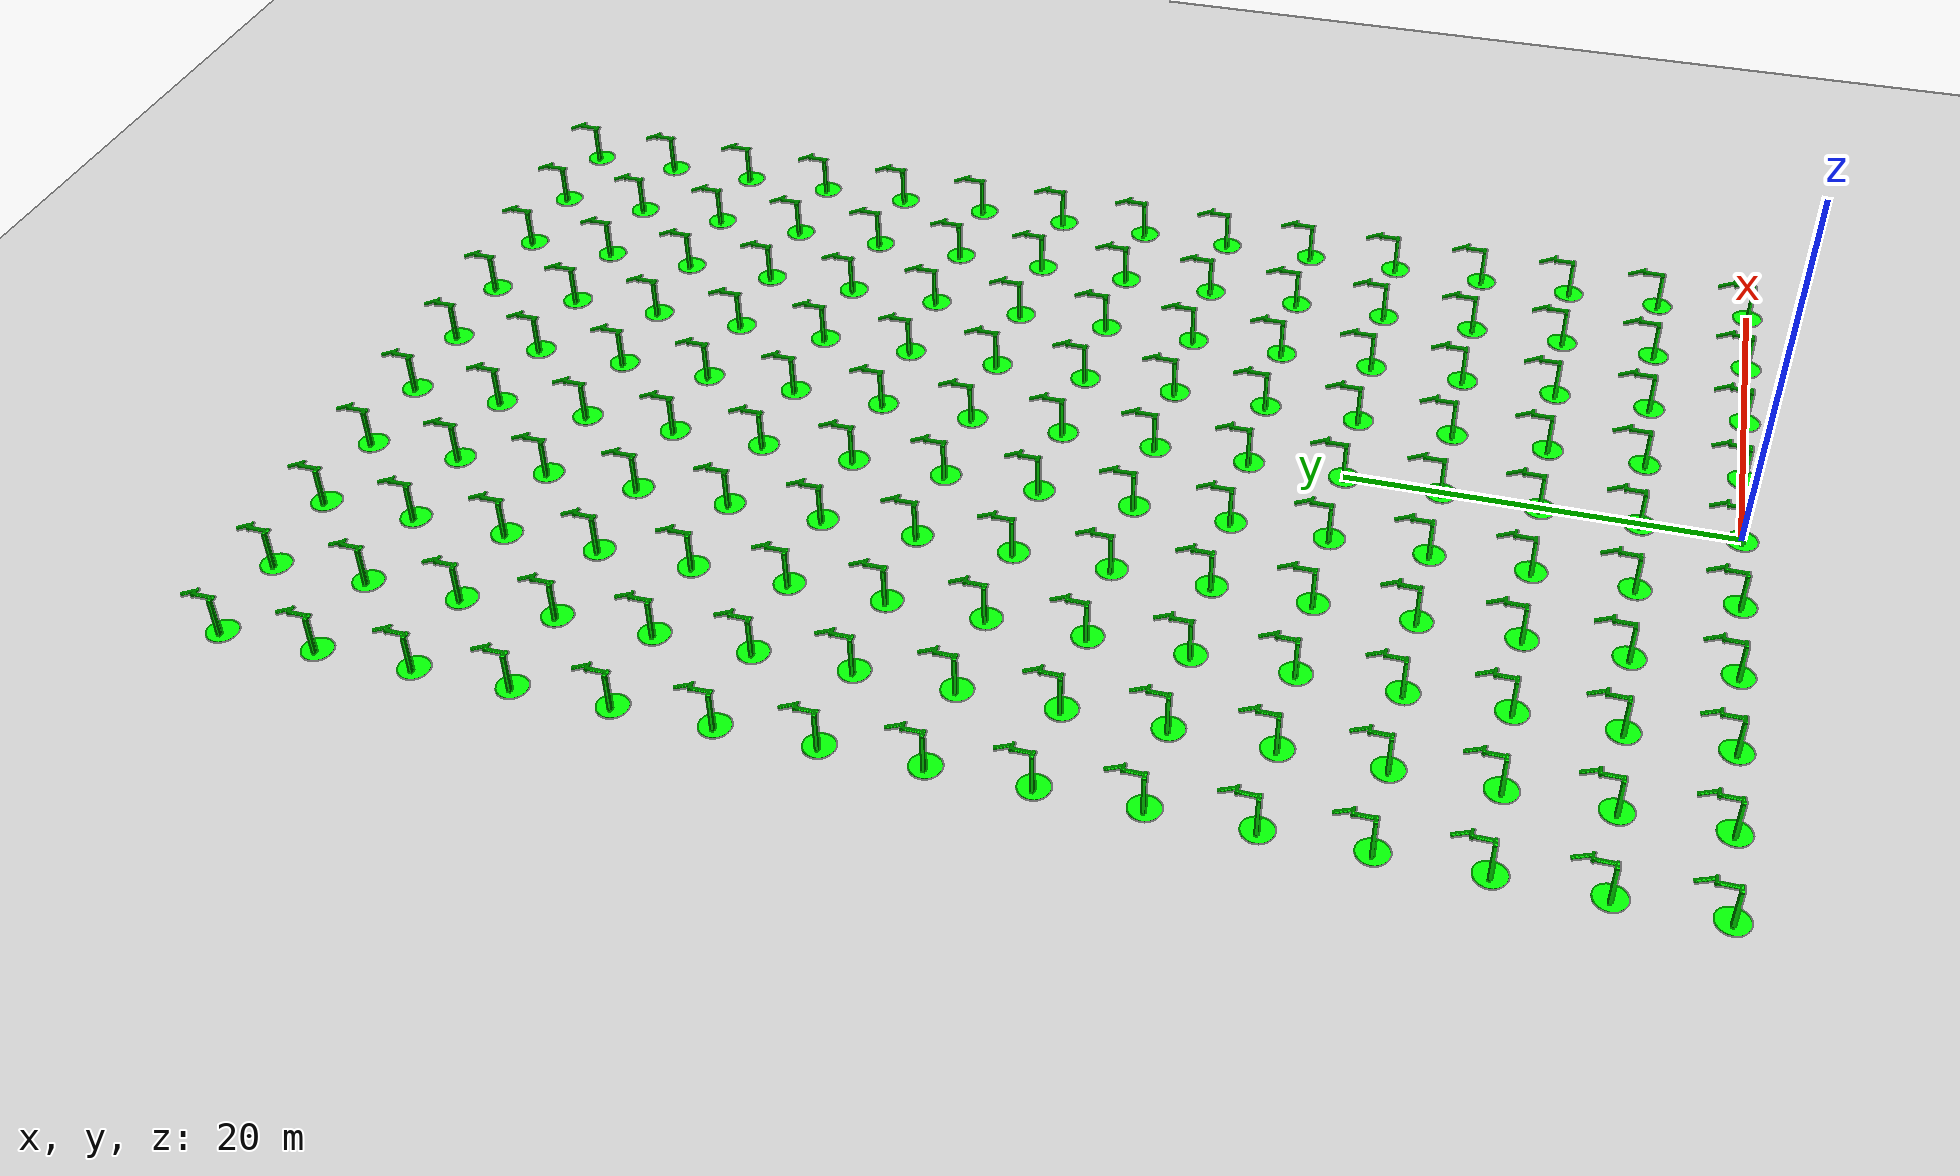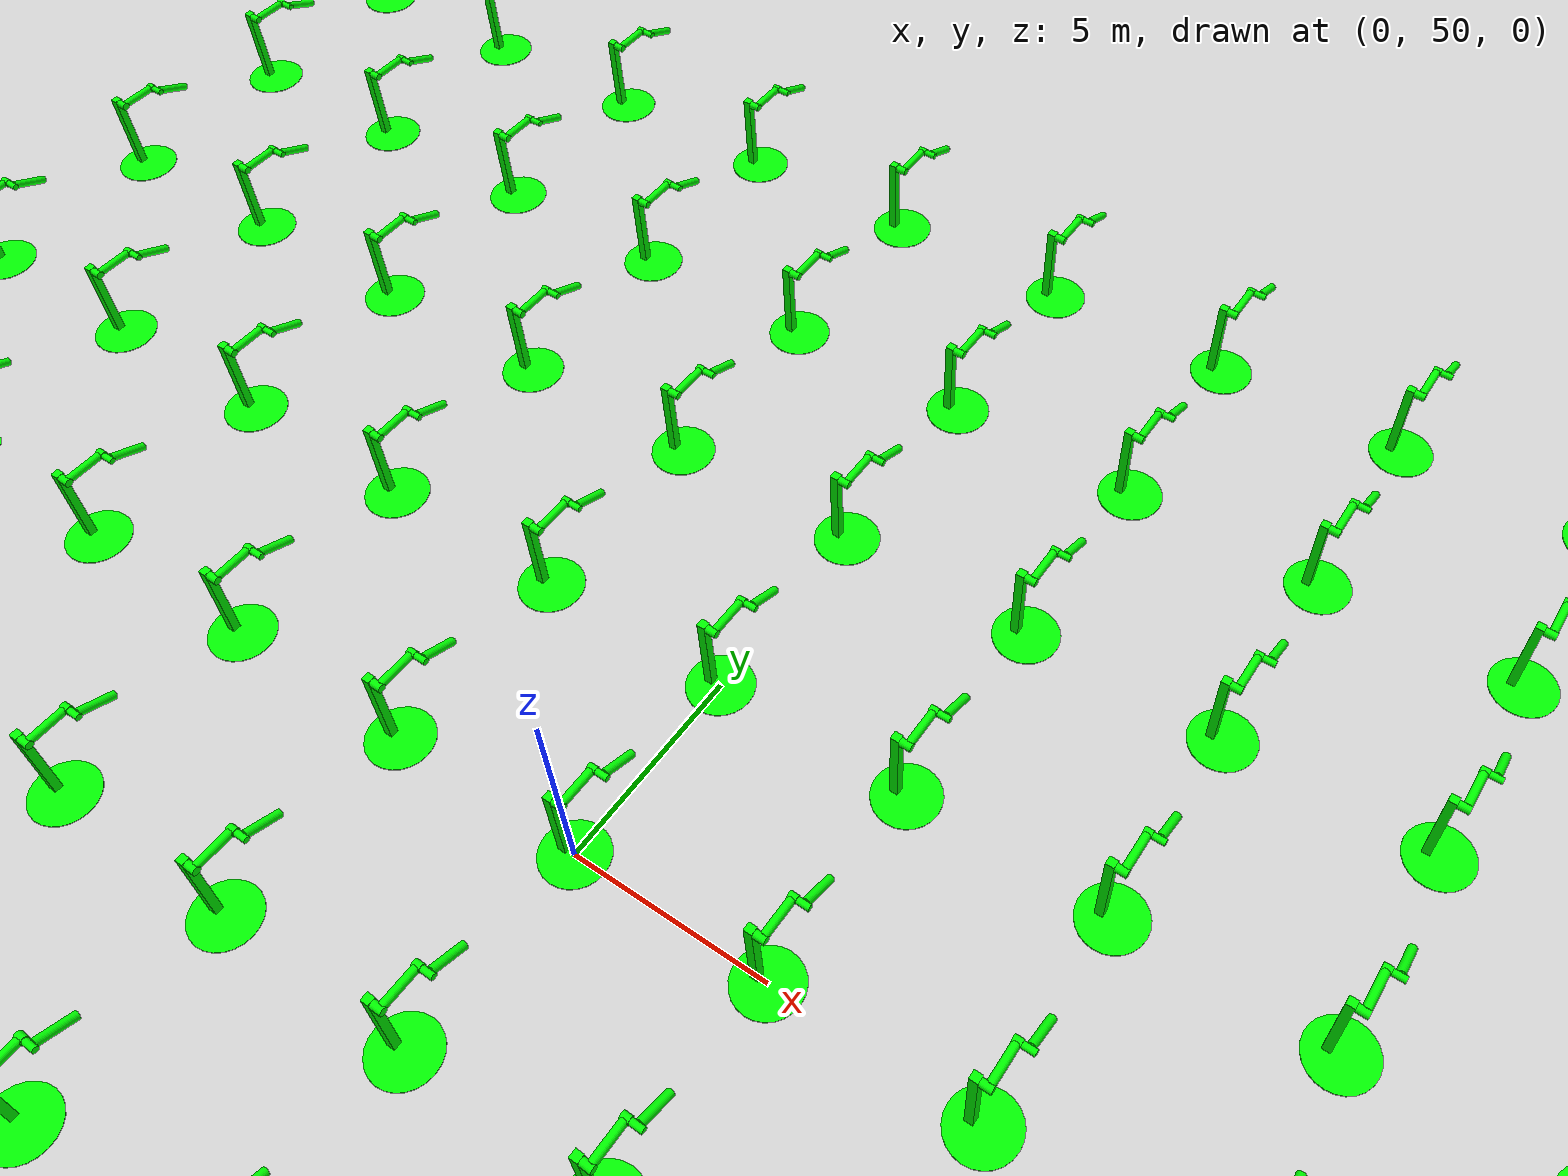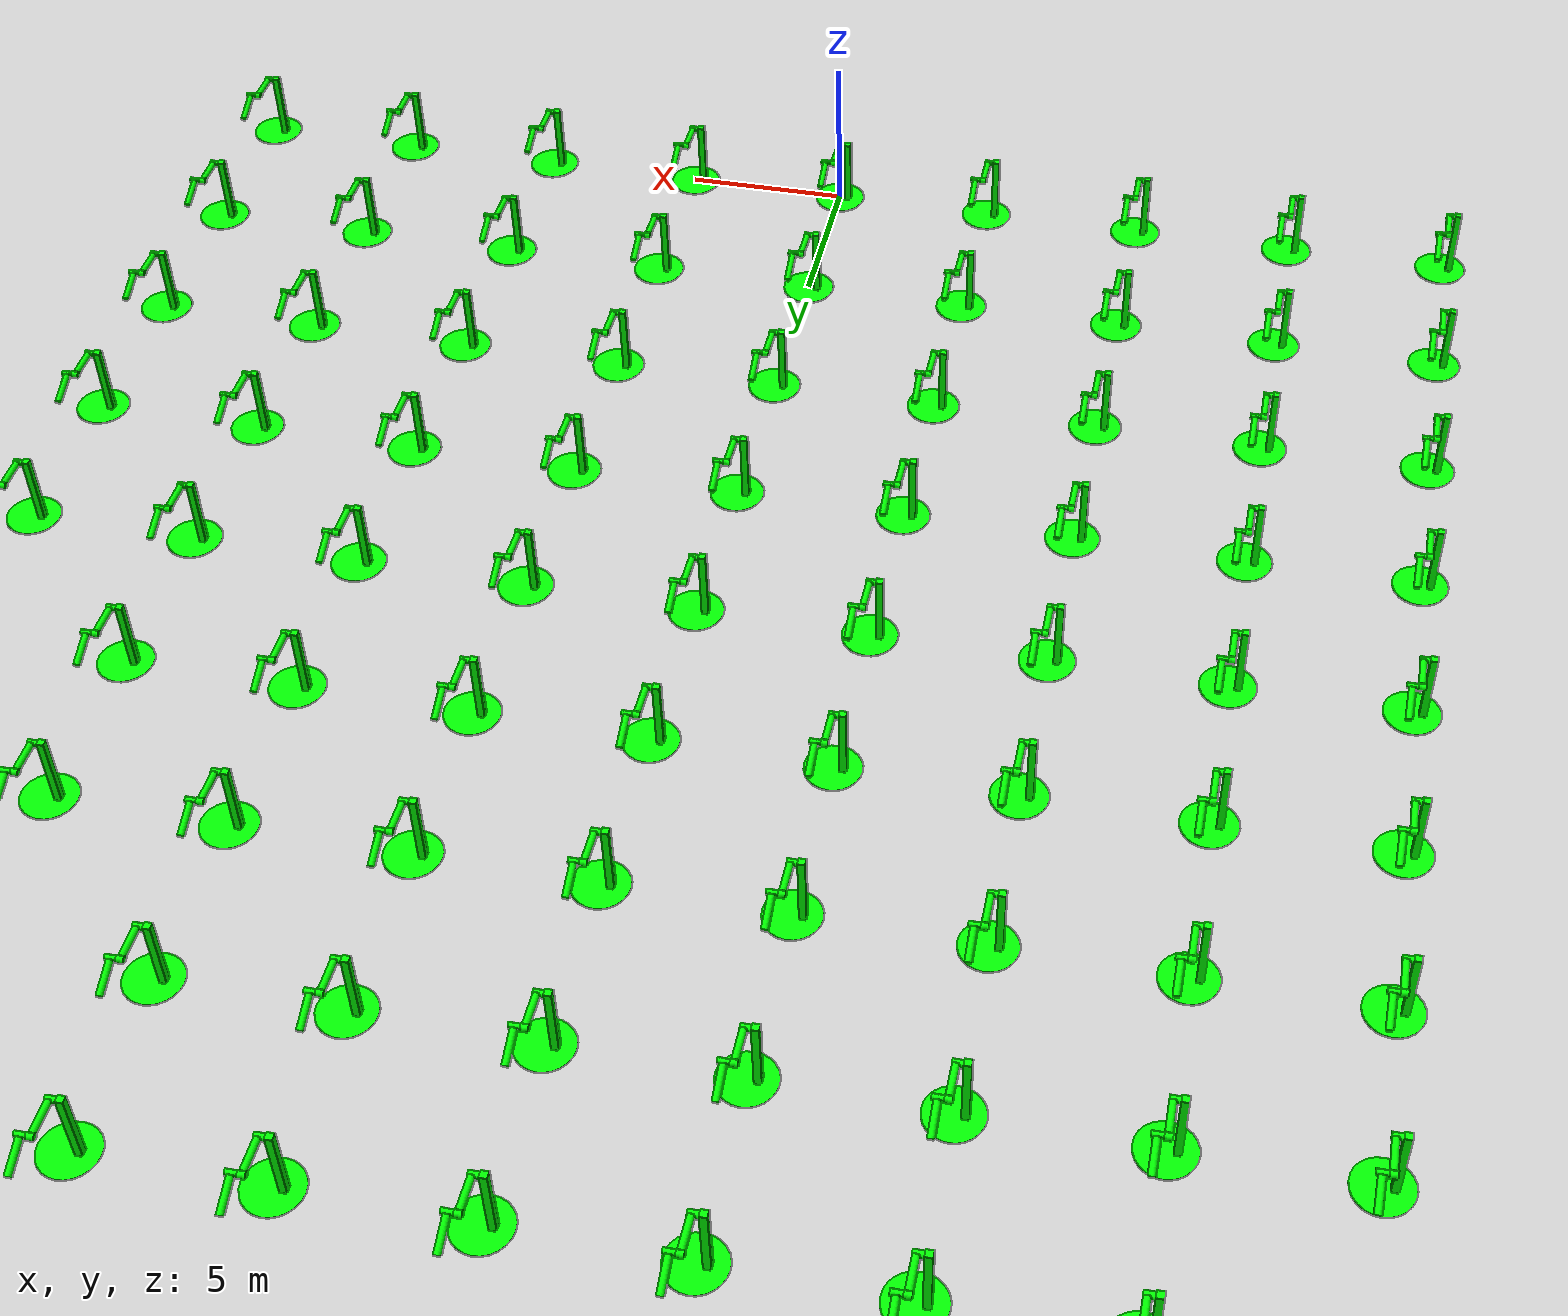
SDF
<?xml version="1.0" ?>
<!--
  to generate a world of 100 pendulums in a 10x10 grid,
  run `erb r=10 c=10 double_pendulums.sdf.erb > double_pendulums.sdf`
-->
<sdf version="1.6">
  <world name="double_pendulums">
    <model name="ground_plane">
      <static>true</static>
      <link name="link">
        <collision name="collision">
          <geometry>
            <plane>
              <normal>0 0 1</normal>
              <size>100 100</size>
            </plane>
          </geometry>
        </collision>
        <visual name="visual">
          <geometry>
            <plane>
              <normal>0 0 1</normal>
              <size>100 100</size>
            </plane>
          </geometry>
          <material>
            <ambient>0.8 0.8 0.8 1</ambient>
            <diffuse>0.8 0.8 0.8 1</diffuse>
            <specular>0.8 0.8 0.8 1</specular>
          </material>
        </visual>
      </link>
    </model>

    <model name="dbl_pendulum_0">
      <pose>-25 0 0 0 0 0</pose>
      <link name="base">
        <inertial>
          <mass>100</mass>
        </inertial>
        <visual name="vis_plate_on_ground">
          <pose>0 0 0.01 0 0 0</pose>
          <geometry>
            <cylinder>
              <radius>0.8</radius>
              <length>0.02</length>
            </cylinder>
          </geometry>
          <material>
            <ambient>0 1 0 1</ambient>
            <diffuse>0 1 0 1</diffuse>
            <specular>0 1 0 1</specular>
          </material>
        </visual>
        <visual name="vis_pole">
          <pose>-0.275 0 1.1 0 0 0</pose>
          <geometry>
            <box>
              <size>0.2 0.2 2.2</size>
            </box>
          </geometry>
          <material>
            <ambient>0 1 0 1</ambient>
            <diffuse>0 1 0 1</diffuse>
            <specular>0 1 0 1</specular>
          </material>
        </visual>
        <collision name="col_plate_on_ground">
          <pose>0 0 0.01 0 0 0</pose>
          <geometry>
            <cylinder>
              <radius>0.8</radius>
              <length>0.02</length>
            </cylinder>
          </geometry>
        </collision>
        <collision name="col_pole">
          <pose>-0.275 0 1.1 0 0 0</pose>
          <geometry>
            <box>
              <size>0.2 0.2 2.2</size>
            </box>
          </geometry>
        </collision>
      </link>
      <!-- upper link, length 1, IC -90 degrees -->
      <link name="upper_link">
        <pose>0 0 2.1 -1.5708 0 0</pose>
        <self_collide>0</self_collide>
        <inertial>
          <pose>0 0 0.5 0 0 0</pose>
        </inertial>
        <visual name="vis_upper_joint">
          <pose>-0.05 0 0 0 1.5708 0</pose>
          <geometry>
            <cylinder>
              <radius>0.1</radius>
              <length>0.3</length>
            </cylinder>
          </geometry>
          <material>
            <ambient>0 1 0 1</ambient>
            <diffuse>0 1 0 1</diffuse>
            <specular>0 1 0 1</specular>
          </material>
        </visual>
        <visual name="vis_lower_joint">
          <pose>0 0 1.0 0 1.5708 0</pose>
          <geometry>
            <cylinder>
              <radius>0.1</radius>
              <length>0.2</length>
            </cylinder>
          </geometry>
          <material>
            <ambient>0 1 0 1</ambient>
            <diffuse>0 1 0 1</diffuse>
            <specular>0 1 0 1</specular>
          </material>
        </visual>
        <visual name="vis_cylinder">
          <pose>0 0 0.5 0 0 0</pose>
          <geometry>
            <cylinder>
              <radius>0.1</radius>
              <length>0.9</length>
            </cylinder>
          </geometry>
          <material>
            <ambient>0 1 0 1</ambient>
            <diffuse>0 1 0 1</diffuse>
            <specular>0 1 0 1</specular>
          </material>
        </visual>
        <collision name="col_upper_joint">
          <pose>-0.05 0 0 0 1.5708 0</pose>
          <geometry>
            <cylinder>
              <radius>0.1</radius>
              <length>0.3</length>
            </cylinder>
          </geometry>
        </collision>
        <collision name="col_lower_joint">
          <pose>0 0 1.0 0 1.5708 0</pose>
          <geometry>
            <cylinder>
              <radius>0.1</radius>
              <length>0.2</length>
            </cylinder>
          </geometry>
        </collision>
        <collision name="col_cylinder">
          <pose>0 0 0.5 0 0 0</pose>
          <geometry>
            <cylinder>
              <radius>0.1</radius>
              <length>0.9</length>
            </cylinder>
          </geometry>
        </collision>
      </link>
      <!-- lower link, length 1, IC ~-120 degrees more -->
      <link name="lower_link">
        <pose>0.25 1.0 2.1 -2 0 0</pose>
        <self_collide>0</self_collide>
        <inertial>
          <pose>0 0 0.5 0 0 0</pose>
        </inertial>
        <visual name="vis_lower_joint">
          <pose>0 0 0 0 1.5708 0</pose>
          <geometry>
            <cylinder>
              <radius>0.08</radius>
              <length>0.3</length>
            </cylinder>
          </geometry>
          <material>
            <ambient>0 1 0 1</ambient>
            <diffuse>0 1 0 1</diffuse>
            <specular>0 1 0 1</specular>
          </material>
        </visual>
        <visual name="vis_cylinder">
          <pose>0 0 0.5 0 0 0</pose>
          <geometry>
            <cylinder>
              <radius>0.1</radius>
              <length>0.9</length>
            </cylinder>
          </geometry>
          <material>
            <ambient>0 1 0 1</ambient>
            <diffuse>0 1 0 1</diffuse>
            <specular>0 1 0 1</specular>
          </material>
        </visual>
        <collision name="col_lower_joint">
          <pose>0 0 0 0 1.5708 0</pose>
          <geometry>
            <cylinder>
              <radius>0.08</radius>
              <length>0.3</length>
            </cylinder>
          </geometry>
        </collision>
        <collision name="col_cylinder">
          <pose>0 0 0.5 0 0 0</pose>
          <geometry>
            <cylinder>
              <radius>0.1</radius>
              <length>0.9</length>
            </cylinder>
          </geometry>
        </collision>
      </link>
      <!-- pin joint for upper link, at origin of upper link -->
      <joint name="upper_joint" type="revolute">
        <parent>base</parent>
        <child>upper_link</child>
        <axis>
          <xyz>1.0 0 0</xyz>
        </axis>
      </joint>
      <!-- pin joint for lower link, at origin of child link -->
      <joint name="lower_joint" type="revolute">
        <parent>upper_link</parent>
        <child>lower_link</child>
        <axis>
          <xyz>1.0 0 0</xyz>
        </axis>
      </joint>
    </model>

    <model name="dbl_pendulum_1">
      <pose>-20 0 0 0 0 0</pose>
      <link name="base">
        <inertial>
          <mass>100</mass>
        </inertial>
        <visual name="vis_plate_on_ground">
          <pose>0 0 0.01 0 0 0</pose>
          <geometry>
            <cylinder>
              <radius>0.8</radius>
              <length>0.02</length>
            </cylinder>
          </geometry>
          <material>
            <ambient>0 1 0 1</ambient>
            <diffuse>0 1 0 1</diffuse>
            <specular>0 1 0 1</specular>
          </material>
        </visual>
        <visual name="vis_pole">
          <pose>-0.275 0 1.1 0 0 0</pose>
          <geometry>
            <box>
              <size>0.2 0.2 2.2</size>
            </box>
          </geometry>
          <material>
            <ambient>0 1 0 1</ambient>
            <diffuse>0 1 0 1</diffuse>
            <specular>0 1 0 1</specular>
          </material>
        </visual>
        <collision name="col_plate_on_ground">
          <pose>0 0 0.01 0 0 0</pose>
          <geometry>
            <cylinder>
              <radius>0.8</radius>
              <length>0.02</length>
            </cylinder>
          </geometry>
        </collision>
        <collision name="col_pole">
          <pose>-0.275 0 1.1 0 0 0</pose>
          <geometry>
            <box>
              <size>0.2 0.2 2.2</size>
            </box>
          </geometry>
        </collision>
      </link>
      <!-- upper link, length 1, IC -90 degrees -->
      <link name="upper_link">
        <pose>0 0 2.1 -1.5708 0 0</pose>
        <self_collide>0</self_collide>
        <inertial>
          <pose>0 0 0.5 0 0 0</pose>
        </inertial>
        <visual name="vis_upper_joint">
          <pose>-0.05 0 0 0 1.5708 0</pose>
          <geometry>
            <cylinder>
              <radius>0.1</radius>
              <length>0.3</length>
            </cylinder>
          </geometry>
          <material>
            <ambient>0 1 0 1</ambient>
            <diffuse>0 1 0 1</diffuse>
            <specular>0 1 0 1</specular>
          </material>
        </visual>
        <visual name="vis_lower_joint">
          <pose>0 0 1.0 0 1.5708 0</pose>
          <geometry>
            <cylinder>
              <radius>0.1</radius>
              <length>0.2</length>
            </cylinder>
          </geometry>
          <material>
            <ambient>0 1 0 1</ambient>
            <diffuse>0 1 0 1</diffuse>
            <specular>0 1 0 1</specular>
          </material>
        </visual>
        <visual name="vis_cylinder">
          <pose>0 0 0.5 0 0 0</pose>
          <geometry>
            <cylinder>
              <radius>0.1</radius>
              <length>0.9</length>
            </cylinder>
          </geometry>
          <material>
            <ambient>0 1 0 1</ambient>
            <diffuse>0 1 0 1</diffuse>
            <specular>0 1 0 1</specular>
          </material>
        </visual>
        <collision name="col_upper_joint">
          <pose>-0.05 0 0 0 1.5708 0</pose>
          <geometry>
            <cylinder>
              <radius>0.1</radius>
              <length>0.3</length>
            </cylinder>
          </geometry>
        </collision>
        <collision name="col_lower_joint">
          <pose>0 0 1.0 0 1.5708 0</pose>
          <geometry>
            <cylinder>
              <radius>0.1</radius>
              <length>0.2</length>
            </cylinder>
          </geometry>
        </collision>
        <collision name="col_cylinder">
          <pose>0 0 0.5 0 0 0</pose>
          <geometry>
            <cylinder>
              <radius>0.1</radius>
              <length>0.9</length>
            </cylinder>
          </geometry>
        </collision>
      </link>
      <!-- lower link, length 1, IC ~-120 degrees more -->
      <link name="lower_link">
        <pose>0.25 1.0 2.1 -2 0 0</pose>
        <self_collide>0</self_collide>
        <inertial>
          <pose>0 0 0.5 0 0 0</pose>
        </inertial>
        <visual name="vis_lower_joint">
          <pose>0 0 0 0 1.5708 0</pose>
          <geometry>
            <cylinder>
              <radius>0.08</radius>
              <length>0.3</length>
            </cylinder>
          </geometry>
          <material>
            <ambient>0 1 0 1</ambient>
            <diffuse>0 1 0 1</diffuse>
            <specular>0 1 0 1</specular>
          </material>
        </visual>
        <visual name="vis_cylinder">
          <pose>0 0 0.5 0 0 0</pose>
          <geometry>
            <cylinder>
              <radius>0.1</radius>
              <length>0.9</length>
            </cylinder>
          </geometry>
          <material>
            <ambient>0 1 0 1</ambient>
            <diffuse>0 1 0 1</diffuse>
            <specular>0 1 0 1</specular>
          </material>
        </visual>
        <collision name="col_lower_joint">
          <pose>0 0 0 0 1.5708 0</pose>
          <geometry>
            <cylinder>
              <radius>0.08</radius>
              <length>0.3</length>
            </cylinder>
          </geometry>
        </collision>
        <collision name="col_cylinder">
          <pose>0 0 0.5 0 0 0</pose>
          <geometry>
            <cylinder>
              <radius>0.1</radius>
              <length>0.9</length>
            </cylinder>
          </geometry>
        </collision>
      </link>
      <!-- pin joint for upper link, at origin of upper link -->
      <joint name="upper_joint" type="revolute">
        <parent>base</parent>
        <child>upper_link</child>
        <axis>
          <xyz>1.0 0 0</xyz>
        </axis>
      </joint>
      <!-- pin joint for lower link, at origin of child link -->
      <joint name="lower_joint" type="revolute">
        <parent>upper_link</parent>
        <child>lower_link</child>
        <axis>
          <xyz>1.0 0 0</xyz>
        </axis>
      </joint>
    </model>

    <model name="dbl_pendulum_2">
      <pose>-15 0 0 0 0 0</pose>
      <link name="base">
        <inertial>
          <mass>100</mass>
        </inertial>
        <visual name="vis_plate_on_ground">
          <pose>0 0 0.01 0 0 0</pose>
          <geometry>
            <cylinder>
              <radius>0.8</radius>
              <length>0.02</length>
            </cylinder>
          </geometry>
          <material>
            <ambient>0 1 0 1</ambient>
            <diffuse>0 1 0 1</diffuse>
            <specular>0 1 0 1</specular>
          </material>
        </visual>
        <visual name="vis_pole">
          <pose>-0.275 0 1.1 0 0 0</pose>
          <geometry>
            <box>
              <size>0.2 0.2 2.2</size>
            </box>
          </geometry>
          <material>
            <ambient>0 1 0 1</ambient>
            <diffuse>0 1 0 1</diffuse>
            <specular>0 1 0 1</specular>
          </material>
        </visual>
        <collision name="col_plate_on_ground">
          <pose>0 0 0.01 0 0 0</pose>
          <geometry>
            <cylinder>
              <radius>0.8</radius>
              <length>0.02</length>
            </cylinder>
          </geometry>
        </collision>
        <collision name="col_pole">
          <pose>-0.275 0 1.1 0 0 0</pose>
          <geometry>
            <box>
              <size>0.2 0.2 2.2</size>
            </box>
          </geometry>
        </collision>
      </link>
      <!-- upper link, length 1, IC -90 degrees -->
      <link name="upper_link">
        <pose>0 0 2.1 -1.5708 0 0</pose>
        <self_collide>0</self_collide>
        <inertial>
          <pose>0 0 0.5 0 0 0</pose>
        </inertial>
        <visual name="vis_upper_joint">
          <pose>-0.05 0 0 0 1.5708 0</pose>
          <geometry>
            <cylinder>
              <radius>0.1</radius>
              <length>0.3</length>
            </cylinder>
          </geometry>
          <material>
            <ambient>0 1 0 1</ambient>
            <diffuse>0 1 0 1</diffuse>
            <specular>0 1 0 1</specular>
          </material>
        </visual>
        <visual name="vis_lower_joint">
          <pose>0 0 1.0 0 1.5708 0</pose>
          <geometry>
            <cylinder>
              <radius>0.1</radius>
              <length>0.2</length>
            </cylinder>
          </geometry>
          <material>
            <ambient>0 1 0 1</ambient>
            <diffuse>0 1 0 1</diffuse>
            <specular>0 1 0 1</specular>
          </material>
        </visual>
        <visual name="vis_cylinder">
          <pose>0 0 0.5 0 0 0</pose>
          <geometry>
            <cylinder>
              <radius>0.1</radius>
              <length>0.9</length>
            </cylinder>
          </geometry>
          <material>
            <ambient>0 1 0 1</ambient>
            <diffuse>0 1 0 1</diffuse>
            <specular>0 1 0 1</specular>
          </material>
        </visual>
        <collision name="col_upper_joint">
          <pose>-0.05 0 0 0 1.5708 0</pose>
          <geometry>
            <cylinder>
              <radius>0.1</radius>
              <length>0.3</length>
            </cylinder>
          </geometry>
        </collision>
        <collision name="col_lower_joint">
          <pose>0 0 1.0 0 1.5708 0</pose>
          <geometry>
            <cylinder>
              <radius>0.1</radius>
              <length>0.2</length>
            </cylinder>
          </geometry>
        </collision>
        <collision name="col_cylinder">
          <pose>0 0 0.5 0 0 0</pose>
          <geometry>
            <cylinder>
              <radius>0.1</radius>
              <length>0.9</length>
            </cylinder>
          </geometry>
        </collision>
      </link>
      <!-- lower link, length 1, IC ~-120 degrees more -->
      <link name="lower_link">
        <pose>0.25 1.0 2.1 -2 0 0</pose>
        <self_collide>0</self_collide>
        <inertial>
          <pose>0 0 0.5 0 0 0</pose>
        </inertial>
        <visual name="vis_lower_joint">
          <pose>0 0 0 0 1.5708 0</pose>
          <geometry>
            <cylinder>
              <radius>0.08</radius>
              <length>0.3</length>
            </cylinder>
          </geometry>
          <material>
            <ambient>0 1 0 1</ambient>
            <diffuse>0 1 0 1</diffuse>
            <specular>0 1 0 1</specular>
          </material>
        </visual>
        <visual name="vis_cylinder">
          <pose>0 0 0.5 0 0 0</pose>
          <geometry>
            <cylinder>
              <radius>0.1</radius>
              <length>0.9</length>
            </cylinder>
          </geometry>
          <material>
            <ambient>0 1 0 1</ambient>
            <diffuse>0 1 0 1</diffuse>
            <specular>0 1 0 1</specular>
          </material>
        </visual>
        <collision name="col_lower_joint">
          <pose>0 0 0 0 1.5708 0</pose>
          <geometry>
            <cylinder>
              <radius>0.08</radius>
              <length>0.3</length>
            </cylinder>
          </geometry>
        </collision>
        <collision name="col_cylinder">
          <pose>0 0 0.5 0 0 0</pose>
          <geometry>
            <cylinder>
              <radius>0.1</radius>
              <length>0.9</length>
            </cylinder>
          </geometry>
        </collision>
      </link>
      <!-- pin joint for upper link, at origin of upper link -->
      <joint name="upper_joint" type="revolute">
        <parent>base</parent>
        <child>upper_link</child>
        <axis>
          <xyz>1.0 0 0</xyz>
        </axis>
      </joint>
      <!-- pin joint for lower link, at origin of child link -->
      <joint name="lower_joint" type="revolute">
        <parent>upper_link</parent>
        <child>lower_link</child>
        <axis>
          <xyz>1.0 0 0</xyz>
        </axis>
      </joint>
    </model>

    <model name="dbl_pendulum_3">
      <pose>-10 0 0 0 0 0</pose>
      <link name="base">
        <inertial>
          <mass>100</mass>
        </inertial>
        <visual name="vis_plate_on_ground">
          <pose>0 0 0.01 0 0 0</pose>
          <geometry>
            <cylinder>
              <radius>0.8</radius>
              <length>0.02</length>
            </cylinder>
          </geometry>
          <material>
            <ambient>0 1 0 1</ambient>
            <diffuse>0 1 0 1</diffuse>
            <specular>0 1 0 1</specular>
          </material>
        </visual>
        <visual name="vis_pole">
          <pose>-0.275 0 1.1 0 0 0</pose>
          <geometry>
            <box>
              <size>0.2 0.2 2.2</size>
            </box>
          </geometry>
          <material>
            <ambient>0 1 0 1</ambient>
            <diffuse>0 1 0 1</diffuse>
            <specular>0 1 0 1</specular>
          </material>
        </visual>
        <collision name="col_plate_on_ground">
          <pose>0 0 0.01 0 0 0</pose>
          <geometry>
            <cylinder>
              <radius>0.8</radius>
              <length>0.02</length>
            </cylinder>
          </geometry>
        </collision>
        <collision name="col_pole">
          <pose>-0.275 0 1.1 0 0 0</pose>
          <geometry>
            <box>
              <size>0.2 0.2 2.2</size>
            </box>
          </geometry>
        </collision>
      </link>
      <!-- upper link, length 1, IC -90 degrees -->
      <link name="upper_link">
        <pose>0 0 2.1 -1.5708 0 0</pose>
        <self_collide>0</self_collide>
        <inertial>
          <pose>0 0 0.5 0 0 0</pose>
        </inertial>
        <visual name="vis_upper_joint">
          <pose>-0.05 0 0 0 1.5708 0</pose>
          <geometry>
            <cylinder>
              <radius>0.1</radius>
              <length>0.3</length>
            </cylinder>
          </geometry>
          <material>
            <ambient>0 1 0 1</ambient>
            <diffuse>0 1 0 1</diffuse>
            <specular>0 1 0 1</specular>
          </material>
        </visual>
        <visual name="vis_lower_joint">
          <pose>0 0 1.0 0 1.5708 0</pose>
          <geometry>
            <cylinder>
              <radius>0.1</radius>
              <length>0.2</length>
            </cylinder>
          </geometry>
          <material>
            <ambient>0 1 0 1</ambient>
            <diffuse>0 1 0 1</diffuse>
            <specular>0 1 0 1</specular>
          </material>
        </visual>
        <visual name="vis_cylinder">
          <pose>0 0 0.5 0 0 0</pose>
          <geometry>
            <cylinder>
              <radius>0.1</radius>
              <length>0.9</length>
            </cylinder>
          </geometry>
          <material>
            <ambient>0 1 0 1</ambient>
            <diffuse>0 1 0 1</diffuse>
            <specular>0 1 0 1</specular>
          </material>
        </visual>
        <collision name="col_upper_joint">
          <pose>-0.05 0 0 0 1.5708 0</pose>
          <geometry>
            <cylinder>
              <radius>0.1</radius>
              <length>0.3</length>
            </cylinder>
          </geometry>
        </collision>
        <collision name="col_lower_joint">
          <pose>0 0 1.0 0 1.5708 0</pose>
          <geometry>
            <cylinder>
              <radius>0.1</radius>
              <length>0.2</length>
            </cylinder>
          </geometry>
        </collision>
        <collision name="col_cylinder">
          <pose>0 0 0.5 0 0 0</pose>
          <geometry>
            <cylinder>
              <radius>0.1</radius>
              <length>0.9</length>
            </cylinder>
          </geometry>
        </collision>
      </link>
      <!-- lower link, length 1, IC ~-120 degrees more -->
      <link name="lower_link">
        <pose>0.25 1.0 2.1 -2 0 0</pose>
        <self_collide>0</self_collide>
        <inertial>
          <pose>0 0 0.5 0 0 0</pose>
        </inertial>
        <visual name="vis_lower_joint">
          <pose>0 0 0 0 1.5708 0</pose>
          <geometry>
            <cylinder>
              <radius>0.08</radius>
              <length>0.3</length>
            </cylinder>
          </geometry>
          <material>
            <ambient>0 1 0 1</ambient>
            <diffuse>0 1 0 1</diffuse>
            <specular>0 1 0 1</specular>
          </material>
        </visual>
        <visual name="vis_cylinder">
          <pose>0 0 0.5 0 0 0</pose>
          <geometry>
            <cylinder>
              <radius>0.1</radius>
              <length>0.9</length>
            </cylinder>
          </geometry>
          <material>
            <ambient>0 1 0 1</ambient>
            <diffuse>0 1 0 1</diffuse>
            <specular>0 1 0 1</specular>
          </material>
        </visual>
        <collision name="col_lower_joint">
          <pose>0 0 0 0 1.5708 0</pose>
          <geometry>
            <cylinder>
              <radius>0.08</radius>
              <length>0.3</length>
            </cylinder>
          </geometry>
        </collision>
        <collision name="col_cylinder">
          <pose>0 0 0.5 0 0 0</pose>
          <geometry>
            <cylinder>
              <radius>0.1</radius>
              <length>0.9</length>
            </cylinder>
          </geometry>
        </collision>
      </link>
      <!-- pin joint for upper link, at origin of upper link -->
      <joint name="upper_joint" type="revolute">
        <parent>base</parent>
        <child>upper_link</child>
        <axis>
          <xyz>1.0 0 0</xyz>
        </axis>
      </joint>
      <!-- pin joint for lower link, at origin of child link -->
      <joint name="lower_joint" type="revolute">
        <parent>upper_link</parent>
        <child>lower_link</child>
        <axis>
          <xyz>1.0 0 0</xyz>
        </axis>
      </joint>
    </model>

    <model name="dbl_pendulum_4">
      <pose>-5 0 0 0 0 0</pose>
      <link name="base">
        <inertial>
          <mass>100</mass>
        </inertial>
        <visual name="vis_plate_on_ground">
          <pose>0 0 0.01 0 0 0</pose>
          <geometry>
            <cylinder>
              <radius>0.8</radius>
              <length>0.02</length>
            </cylinder>
          </geometry>
          <material>
            <ambient>0 1 0 1</ambient>
            <diffuse>0 1 0 1</diffuse>
            <specular>0 1 0 1</specular>
          </material>
        </visual>
        <visual name="vis_pole">
          <pose>-0.275 0 1.1 0 0 0</pose>
          <geometry>
            <box>
              <size>0.2 0.2 2.2</size>
            </box>
          </geometry>
          <material>
            <ambient>0 1 0 1</ambient>
            <diffuse>0 1 0 1</diffuse>
            <specular>0 1 0 1</specular>
          </material>
        </visual>
        <collision name="col_plate_on_ground">
          <pose>0 0 0.01 0 0 0</pose>
          <geometry>
            <cylinder>
              <radius>0.8</radius>
              <length>0.02</length>
            </cylinder>
          </geometry>
        </collision>
        <collision name="col_pole">
          <pose>-0.275 0 1.1 0 0 0</pose>
          <geometry>
            <box>
              <size>0.2 0.2 2.2</size>
            </box>
          </geometry>
        </collision>
      </link>
      <!-- upper link, length 1, IC -90 degrees -->
      <link name="upper_link">
        <pose>0 0 2.1 -1.5708 0 0</pose>
        <self_collide>0</self_collide>
        <inertial>
          <pose>0 0 0.5 0 0 0</pose>
        </inertial>
        <visual name="vis_upper_joint">
          <pose>-0.05 0 0 0 1.5708 0</pose>
          <geometry>
            <cylinder>
              <radius>0.1</radius>
              <length>0.3</length>
            </cylinder>
          </geometry>
          <material>
            <ambient>0 1 0 1</ambient>
            <diffuse>0 1 0 1</diffuse>
            <specular>0 1 0 1</specular>
          </material>
        </visual>
        <visual name="vis_lower_joint">
          <pose>0 0 1.0 0 1.5708 0</pose>
          <geometry>
            <cylinder>
              <radius>0.1</radius>
              <length>0.2</length>
            </cylinder>
          </geometry>
          <material>
            <ambient>0 1 0 1</ambient>
            <diffuse>0 1 0 1</diffuse>
            <specular>0 1 0 1</specular>
          </material>
        </visual>
        <visual name="vis_cylinder">
          <pose>0 0 0.5 0 0 0</pose>
          <geometry>
            <cylinder>
              <radius>0.1</radius>
              <length>0.9</length>
            </cylinder>
          </geometry>
          <material>
            <ambient>0 1 0 1</ambient>
            <diffuse>0 1 0 1</diffuse>
            <specular>0 1 0 1</specular>
          </material>
        </visual>
        <collision name="col_upper_joint">
          <pose>-0.05 0 0 0 1.5708 0</pose>
          <geometry>
            <cylinder>
              <radius>0.1</radius>
              <length>0.3</length>
            </cylinder>
          </geometry>
        </collision>
        <collision name="col_lower_joint">
          <pose>0 0 1.0 0 1.5708 0</pose>
          <geometry>
            <cylinder>
              <radius>0.1</radius>
              <length>0.2</length>
            </cylinder>
          </geometry>
        </collision>
        <collision name="col_cylinder">
          <pose>0 0 0.5 0 0 0</pose>
          <geometry>
            <cylinder>
              <radius>0.1</radius>
              <length>0.9</length>
            </cylinder>
          </geometry>
        </collision>
      </link>
      <!-- lower link, length 1, IC ~-120 degrees more -->
      <link name="lower_link">
        <pose>0.25 1.0 2.1 -2 0 0</pose>
        <self_collide>0</self_collide>
        <inertial>
          <pose>0 0 0.5 0 0 0</pose>
        </inertial>
        <visual name="vis_lower_joint">
          <pose>0 0 0 0 1.5708 0</pose>
          <geometry>
            <cylinder>
              <radius>0.08</radius>
              <length>0.3</length>
            </cylinder>
          </geometry>
          <material>
            <ambient>0 1 0 1</ambient>
            <diffuse>0 1 0 1</diffuse>
            <specular>0 1 0 1</specular>
          </material>
        </visual>
        <visual name="vis_cylinder">
          <pose>0 0 0.5 0 0 0</pose>
          <geometry>
            <cylinder>
              <radius>0.1</radius>
              <length>0.9</length>
            </cylinder>
          </geometry>
          <material>
            <ambient>0 1 0 1</ambient>
            <diffuse>0 1 0 1</diffuse>
            <specular>0 1 0 1</specular>
          </material>
        </visual>
        <collision name="col_lower_joint">
          <pose>0 0 0 0 1.5708 0</pose>
          <geometry>
            <cylinder>
              <radius>0.08</radius>
              <length>0.3</length>
            </cylinder>
          </geometry>
        </collision>
        <collision name="col_cylinder">
          <pose>0 0 0.5 0 0 0</pose>
          <geometry>
            <cylinder>
              <radius>0.1</radius>
              <length>0.9</length>
            </cylinder>
          </geometry>
        </collision>
      </link>
      <!-- pin joint for upper link, at origin of upper link -->
      <joint name="upper_joint" type="revolute">
        <parent>base</parent>
        <child>upper_link</child>
        <axis>
          <xyz>1.0 0 0</xyz>
        </axis>
      </joint>
      <!-- pin joint for lower link, at origin of child link -->
      <joint name="lower_joint" type="revolute">
        <parent>upper_link</parent>
        <child>lower_link</child>
        <axis>
          <xyz>1.0 0 0</xyz>
        </axis>
      </joint>
    </model>

    <model name="dbl_pendulum_5">
      <pose>0 0 0 0 0 0</pose>
      <link name="base">
        <inertial>
          <mass>100</mass>
        </inertial>
        <visual name="vis_plate_on_ground">
          <pose>0 0 0.01 0 0 0</pose>
          <geometry>
            <cylinder>
              <radius>0.8</radius>
              <length>0.02</length>
            </cylinder>
          </geometry>
          <material>
            <ambient>0 1 0 1</ambient>
            <diffuse>0 1 0 1</diffuse>
            <specular>0 1 0 1</specular>
          </material>
        </visual>
        <visual name="vis_pole">
          <pose>-0.275 0 1.1 0 0 0</pose>
          <geometry>
            <box>
              <size>0.2 0.2 2.2</size>
            </box>
          </geometry>
          <material>
            <ambient>0 1 0 1</ambient>
            <diffuse>0 1 0 1</diffuse>
            <specular>0 1 0 1</specular>
          </material>
        </visual>
        <collision name="col_plate_on_ground">
          <pose>0 0 0.01 0 0 0</pose>
          <geometry>
            <cylinder>
              <radius>0.8</radius>
              <length>0.02</length>
            </cylinder>
          </geometry>
        </collision>
        <collision name="col_pole">
          <pose>-0.275 0 1.1 0 0 0</pose>
          <geometry>
            <box>
              <size>0.2 0.2 2.2</size>
            </box>
          </geometry>
        </collision>
      </link>
      <!-- upper link, length 1, IC -90 degrees -->
      <link name="upper_link">
        <pose>0 0 2.1 -1.5708 0 0</pose>
        <self_collide>0</self_collide>
        <inertial>
          <pose>0 0 0.5 0 0 0</pose>
        </inertial>
        <visual name="vis_upper_joint">
          <pose>-0.05 0 0 0 1.5708 0</pose>
          <geometry>
            <cylinder>
              <radius>0.1</radius>
              <length>0.3</length>
            </cylinder>
          </geometry>
          <material>
            <ambient>0 1 0 1</ambient>
            <diffuse>0 1 0 1</diffuse>
            <specular>0 1 0 1</specular>
          </material>
        </visual>
        <visual name="vis_lower_joint">
          <pose>0 0 1.0 0 1.5708 0</pose>
          <geometry>
            <cylinder>
              <radius>0.1</radius>
              <length>0.2</length>
            </cylinder>
          </geometry>
          <material>
            <ambient>0 1 0 1</ambient>
            <diffuse>0 1 0 1</diffuse>
            <specular>0 1 0 1</specular>
          </material>
        </visual>
        <visual name="vis_cylinder">
          <pose>0 0 0.5 0 0 0</pose>
          <geometry>
            <cylinder>
              <radius>0.1</radius>
              <length>0.9</length>
            </cylinder>
          </geometry>
          <material>
            <ambient>0 1 0 1</ambient>
            <diffuse>0 1 0 1</diffuse>
            <specular>0 1 0 1</specular>
          </material>
        </visual>
        <collision name="col_upper_joint">
          <pose>-0.05 0 0 0 1.5708 0</pose>
          <geometry>
            <cylinder>
              <radius>0.1</radius>
              <length>0.3</length>
            </cylinder>
          </geometry>
        </collision>
        <collision name="col_lower_joint">
          <pose>0 0 1.0 0 1.5708 0</pose>
          <geometry>
            <cylinder>
              <radius>0.1</radius>
              <length>0.2</length>
            </cylinder>
          </geometry>
        </collision>
        <collision name="col_cylinder">
          <pose>0 0 0.5 0 0 0</pose>
          <geometry>
            <cylinder>
              <radius>0.1</radius>
              <length>0.9</length>
            </cylinder>
          </geometry>
        </collision>
      </link>
      <!-- lower link, length 1, IC ~-120 degrees more -->
      <link name="lower_link">
        <pose>0.25 1.0 2.1 -2 0 0</pose>
        <self_collide>0</self_collide>
        <inertial>
          <pose>0 0 0.5 0 0 0</pose>
        </inertial>
        <visual name="vis_lower_joint">
          <pose>0 0 0 0 1.5708 0</pose>
          <geometry>
            <cylinder>
              <radius>0.08</radius>
              <length>0.3</length>
            </cylinder>
          </geometry>
          <material>
            <ambient>0 1 0 1</ambient>
            <diffuse>0 1 0 1</diffuse>
            <specular>0 1 0 1</specular>
          </material>
        </visual>
        <visual name="vis_cylinder">
          <pose>0 0 0.5 0 0 0</pose>
          <geometry>
            <cylinder>
              <radius>0.1</radius>
              <length>0.9</length>
            </cylinder>
          </geometry>
          <material>
            <ambient>0 1 0 1</ambient>
            <diffuse>0 1 0 1</diffuse>
            <specular>0 1 0 1</specular>
          </material>
        </visual>
        <collision name="col_lower_joint">
          <pose>0 0 0 0 1.5708 0</pose>
          <geometry>
            <cylinder>
              <radius>0.08</radius>
              <length>0.3</length>
            </cylinder>
          </geometry>
        </collision>
        <collision name="col_cylinder">
          <pose>0 0 0.5 0 0 0</pose>
          <geometry>
            <cylinder>
              <radius>0.1</radius>
              <length>0.9</length>
            </cylinder>
          </geometry>
        </collision>
      </link>
      <!-- pin joint for upper link, at origin of upper link -->
      <joint name="upper_joint" type="revolute">
        <parent>base</parent>
        <child>upper_link</child>
        <axis>
          <xyz>1.0 0 0</xyz>
        </axis>
      </joint>
      <!-- pin joint for lower link, at origin of child link -->
      <joint name="lower_joint" type="revolute">
        <parent>upper_link</parent>
        <child>lower_link</child>
        <axis>
          <xyz>1.0 0 0</xyz>
        </axis>
      </joint>
    </model>

    <model name="dbl_pendulum_6">
      <pose>5 0 0 0 0 0</pose>
      <link name="base">
        <inertial>
          <mass>100</mass>
        </inertial>
        <visual name="vis_plate_on_ground">
          <pose>0 0 0.01 0 0 0</pose>
          <geometry>
            <cylinder>
              <radius>0.8</radius>
              <length>0.02</length>
            </cylinder>
          </geometry>
          <material>
            <ambient>0 1 0 1</ambient>
            <diffuse>0 1 0 1</diffuse>
            <specular>0 1 0 1</specular>
          </material>
        </visual>
        <visual name="vis_pole">
          <pose>-0.275 0 1.1 0 0 0</pose>
          <geometry>
            <box>
              <size>0.2 0.2 2.2</size>
            </box>
          </geometry>
          <material>
            <ambient>0 1 0 1</ambient>
            <diffuse>0 1 0 1</diffuse>
            <specular>0 1 0 1</specular>
          </material>
        </visual>
        <collision name="col_plate_on_ground">
          <pose>0 0 0.01 0 0 0</pose>
          <geometry>
            <cylinder>
              <radius>0.8</radius>
              <length>0.02</length>
            </cylinder>
          </geometry>
        </collision>
        <collision name="col_pole">
          <pose>-0.275 0 1.1 0 0 0</pose>
          <geometry>
            <box>
              <size>0.2 0.2 2.2</size>
            </box>
          </geometry>
        </collision>
      </link>
      <!-- upper link, length 1, IC -90 degrees -->
      <link name="upper_link">
        <pose>0 0 2.1 -1.5708 0 0</pose>
        <self_collide>0</self_collide>
        <inertial>
          <pose>0 0 0.5 0 0 0</pose>
        </inertial>
        <visual name="vis_upper_joint">
          <pose>-0.05 0 0 0 1.5708 0</pose>
          <geometry>
            <cylinder>
              <radius>0.1</radius>
              <length>0.3</length>
            </cylinder>
          </geometry>
          <material>
            <ambient>0 1 0 1</ambient>
            <diffuse>0 1 0 1</diffuse>
            <specular>0 1 0 1</specular>
          </material>
        </visual>
        <visual name="vis_lower_joint">
          <pose>0 0 1.0 0 1.5708 0</pose>
          <geometry>
            <cylinder>
              <radius>0.1</radius>
              <length>0.2</length>
            </cylinder>
          </geometry>
          <material>
            <ambient>0 1 0 1</ambient>
            <diffuse>0 1 0 1</diffuse>
            <specular>0 1 0 1</specular>
          </material>
        </visual>
        <visual name="vis_cylinder">
          <pose>0 0 0.5 0 0 0</pose>
          <geometry>
            <cylinder>
              <radius>0.1</radius>
              <length>0.9</length>
            </cylinder>
          </geometry>
          <material>
            <ambient>0 1 0 1</ambient>
            <diffuse>0 1 0 1</diffuse>
            <specular>0 1 0 1</specular>
          </material>
        </visual>
        <collision name="col_upper_joint">
          <pose>-0.05 0 0 0 1.5708 0</pose>
          <geometry>
            <cylinder>
              <radius>0.1</radius>
              <length>0.3</length>
            </cylinder>
          </geometry>
        </collision>
        <collision name="col_lower_joint">
          <pose>0 0 1.0 0 1.5708 0</pose>
          <geometry>
            <cylinder>
              <radius>0.1</radius>
              <length>0.2</length>
            </cylinder>
          </geometry>
        </collision>
        <collision name="col_cylinder">
          <pose>0 0 0.5 0 0 0</pose>
          <geometry>
            <cylinder>
              <radius>0.1</radius>
              <length>0.9</length>
            </cylinder>
          </geometry>
        </collision>
      </link>
      <!-- lower link, length 1, IC ~-120 degrees more -->
      <link name="lower_link">
        <pose>0.25 1.0 2.1 -2 0 0</pose>
        <self_collide>0</self_collide>
        <inertial>
          <pose>0 0 0.5 0 0 0</pose>
        </inertial>
        <visual name="vis_lower_joint">
          <pose>0 0 0 0 1.5708 0</pose>
          <geometry>
            <cylinder>
              <radius>0.08</radius>
              <length>0.3</length>
            </cylinder>
          </geometry>
          <material>
            <ambient>0 1 0 1</ambient>
            <diffuse>0 1 0 1</diffuse>
            <specular>0 1 0 1</specular>
          </material>
        </visual>
        <visual name="vis_cylinder">
          <pose>0 0 0.5 0 0 0</pose>
          <geometry>
            <cylinder>
              <radius>0.1</radius>
              <length>0.9</length>
            </cylinder>
          </geometry>
          <material>
            <ambient>0 1 0 1</ambient>
            <diffuse>0 1 0 1</diffuse>
            <specular>0 1 0 1</specular>
          </material>
        </visual>
        <collision name="col_lower_joint">
          <pose>0 0 0 0 1.5708 0</pose>
          <geometry>
            <cylinder>
              <radius>0.08</radius>
              <length>0.3</length>
            </cylinder>
          </geometry>
        </collision>
        <collision name="col_cylinder">
          <pose>0 0 0.5 0 0 0</pose>
          <geometry>
            <cylinder>
              <radius>0.1</radius>
              <length>0.9</length>
            </cylinder>
          </geometry>
        </collision>
      </link>
      <!-- pin joint for upper link, at origin of upper link -->
      <joint name="upper_joint" type="revolute">
        <parent>base</parent>
        <child>upper_link</child>
        <axis>
          <xyz>1.0 0 0</xyz>
        </axis>
      </joint>
      <!-- pin joint for lower link, at origin of child link -->
      <joint name="lower_joint" type="revolute">
        <parent>upper_link</parent>
        <child>lower_link</child>
        <axis>
          <xyz>1.0 0 0</xyz>
        </axis>
      </joint>
    </model>

    <model name="dbl_pendulum_7">
      <pose>10 0 0 0 0 0</pose>
      <link name="base">
        <inertial>
          <mass>100</mass>
        </inertial>
        <visual name="vis_plate_on_ground">
          <pose>0 0 0.01 0 0 0</pose>
          <geometry>
            <cylinder>
              <radius>0.8</radius>
              <length>0.02</length>
            </cylinder>
          </geometry>
          <material>
            <ambient>0 1 0 1</ambient>
            <diffuse>0 1 0 1</diffuse>
            <specular>0 1 0 1</specular>
          </material>
        </visual>
        <visual name="vis_pole">
          <pose>-0.275 0 1.1 0 0 0</pose>
          <geometry>
            <box>
              <size>0.2 0.2 2.2</size>
            </box>
          </geometry>
          <material>
            <ambient>0 1 0 1</ambient>
            <diffuse>0 1 0 1</diffuse>
            <specular>0 1 0 1</specular>
          </material>
        </visual>
        <collision name="col_plate_on_ground">
          <pose>0 0 0.01 0 0 0</pose>
          <geometry>
            <cylinder>
              <radius>0.8</radius>
              <length>0.02</length>
            </cylinder>
          </geometry>
        </collision>
        <collision name="col_pole">
          <pose>-0.275 0 1.1 0 0 0</pose>
          <geometry>
            <box>
              <size>0.2 0.2 2.2</size>
            </box>
          </geometry>
        </collision>
      </link>
      <!-- upper link, length 1, IC -90 degrees -->
      <link name="upper_link">
        <pose>0 0 2.1 -1.5708 0 0</pose>
        <self_collide>0</self_collide>
        <inertial>
          <pose>0 0 0.5 0 0 0</pose>
        </inertial>
        <visual name="vis_upper_joint">
          <pose>-0.05 0 0 0 1.5708 0</pose>
          <geometry>
            <cylinder>
              <radius>0.1</radius>
              <length>0.3</length>
            </cylinder>
          </geometry>
          <material>
            <ambient>0 1 0 1</ambient>
            <diffuse>0 1 0 1</diffuse>
            <specular>0 1 0 1</specular>
          </material>
        </visual>
        <visual name="vis_lower_joint">
          <pose>0 0 1.0 0 1.5708 0</pose>
          <geometry>
            <cylinder>
              <radius>0.1</radius>
              <length>0.2</length>
            </cylinder>
          </geometry>
          <material>
            <ambient>0 1 0 1</ambient>
            <diffuse>0 1 0 1</diffuse>
            <specular>0 1 0 1</specular>
          </material>
        </visual>
        <visual name="vis_cylinder">
          <pose>0 0 0.5 0 0 0</pose>
          <geometry>
            <cylinder>
              <radius>0.1</radius>
              <length>0.9</length>
            </cylinder>
          </geometry>
          <material>
            <ambient>0 1 0 1</ambient>
            <diffuse>0 1 0 1</diffuse>
            <specular>0 1 0 1</specular>
          </material>
        </visual>
        <collision name="col_upper_joint">
          <pose>-0.05 0 0 0 1.5708 0</pose>
          <geometry>
            <cylinder>
              <radius>0.1</radius>
              <length>0.3</length>
            </cylinder>
          </geometry>
        </collision>
        <collision name="col_lower_joint">
          <pose>0 0 1.0 0 1.5708 0</pose>
          <geometry>
            <cylinder>
              <radius>0.1</radius>
              <length>0.2</length>
            </cylinder>
          </geometry>
        </collision>
        <collision name="col_cylinder">
          <pose>0 0 0.5 0 0 0</pose>
          <geometry>
            <cylinder>
              <radius>0.1</radius>
              <length>0.9</length>
            </cylinder>
          </geometry>
        </collision>
      </link>
      <!-- lower link, length 1, IC ~-120 degrees more -->
      <link name="lower_link">
        <pose>0.25 1.0 2.1 -2 0 0</pose>
        <self_collide>0</self_collide>
        <inertial>
          <pose>0 0 0.5 0 0 0</pose>
        </inertial>
        <visual name="vis_lower_joint">
          <pose>0 0 0 0 1.5708 0</pose>
          <geometry>
            <cylinder>
              <radius>0.08</radius>
              <length>0.3</length>
            </cylinder>
          </geometry>
          <material>
            <ambient>0 1 0 1</ambient>
            <diffuse>0 1 0 1</diffuse>
            <specular>0 1 0 1</specular>
          </material>
        </visual>
        <visual name="vis_cylinder">
          <pose>0 0 0.5 0 0 0</pose>
          <geometry>
            <cylinder>
              <radius>0.1</radius>
              <length>0.9</length>
            </cylinder>
          </geometry>
          <material>
            <ambient>0 1 0 1</ambient>
            <diffuse>0 1 0 1</diffuse>
            <specular>0 1 0 1</specular>
          </material>
        </visual>
        <collision name="col_lower_joint">
          <pose>0 0 0 0 1.5708 0</pose>
          <geometry>
            <cylinder>
              <radius>0.08</radius>
              <length>0.3</length>
            </cylinder>
          </geometry>
        </collision>
        <collision name="col_cylinder">
          <pose>0 0 0.5 0 0 0</pose>
          <geometry>
            <cylinder>
              <radius>0.1</radius>
              <length>0.9</length>
            </cylinder>
          </geometry>
        </collision>
      </link>
      <!-- pin joint for upper link, at origin of upper link -->
      <joint name="upper_joint" type="revolute">
        <parent>base</parent>
        <child>upper_link</child>
        <axis>
          <xyz>1.0 0 0</xyz>
        </axis>
      </joint>
      <!-- pin joint for lower link, at origin of child link -->
      <joint name="lower_joint" type="revolute">
        <parent>upper_link</parent>
        <child>lower_link</child>
        <axis>
          <xyz>1.0 0 0</xyz>
        </axis>
      </joint>
    </model>

    <model name="dbl_pendulum_8">
      <pose>15 0 0 0 0 0</pose>
      <link name="base">
        <inertial>
          <mass>100</mass>
        </inertial>
        <visual name="vis_plate_on_ground">
          <pose>0 0 0.01 0 0 0</pose>
          <geometry>
            <cylinder>
              <radius>0.8</radius>
              <length>0.02</length>
            </cylinder>
          </geometry>
          <material>
            <ambient>0 1 0 1</ambient>
            <diffuse>0 1 0 1</diffuse>
            <specular>0 1 0 1</specular>
          </material>
        </visual>
        <visual name="vis_pole">
          <pose>-0.275 0 1.1 0 0 0</pose>
          <geometry>
            <box>
              <size>0.2 0.2 2.2</size>
            </box>
          </geometry>
          <material>
            <ambient>0 1 0 1</ambient>
            <diffuse>0 1 0 1</diffuse>
            <specular>0 1 0 1</specular>
          </material>
        </visual>
        <collision name="col_plate_on_ground">
          <pose>0 0 0.01 0 0 0</pose>
          <geometry>
            <cylinder>
              <radius>0.8</radius>
              <length>0.02</length>
            </cylinder>
          </geometry>
        </collision>
        <collision name="col_pole">
          <pose>-0.275 0 1.1 0 0 0</pose>
          <geometry>
            <box>
              <size>0.2 0.2 2.2</size>
            </box>
          </geometry>
        </collision>
      </link>
      <!-- upper link, length 1, IC -90 degrees -->
      <link name="upper_link">
        <pose>0 0 2.1 -1.5708 0 0</pose>
        <self_collide>0</self_collide>
        <inertial>
          <pose>0 0 0.5 0 0 0</pose>
        </inertial>
        <visual name="vis_upper_joint">
          <pose>-0.05 0 0 0 1.5708 0</pose>
          <geometry>
            <cylinder>
              <radius>0.1</radius>
              <length>0.3</length>
            </cylinder>
          </geometry>
          <material>
            <ambient>0 1 0 1</ambient>
            <diffuse>0 1 0 1</diffuse>
            <specular>0 1 0 1</specular>
          </material>
        </visual>
        <visual name="vis_lower_joint">
          <pose>0 0 1.0 0 1.5708 0</pose>
          <geometry>
            <cylinder>
              <radius>0.1</radius>
              <length>0.2</length>
            </cylinder>
          </geometry>
          <material>
            <ambient>0 1 0 1</ambient>
            <diffuse>0 1 0 1</diffuse>
            <specular>0 1 0 1</specular>
          </material>
        </visual>
        <visual name="vis_cylinder">
          <pose>0 0 0.5 0 0 0</pose>
          <geometry>
            <cylinder>
              <radius>0.1</radius>
              <length>0.9</length>
            </cylinder>
          </geometry>
          <material>
            <ambient>0 1 0 1</ambient>
            <diffuse>0 1 0 1</diffuse>
            <specular>0 1 0 1</specular>
          </material>
        </visual>
        <collision name="col_upper_joint">
          <pose>-0.05 0 0 0 1.5708 0</pose>
          <geometry>
            <cylinder>
              <radius>0.1</radius>
              <length>0.3</length>
            </cylinder>
          </geometry>
        </collision>
        <collision name="col_lower_joint">
          <pose>0 0 1.0 0 1.5708 0</pose>
          <geometry>
            <cylinder>
              <radius>0.1</radius>
              <length>0.2</length>
            </cylinder>
          </geometry>
        </collision>
        <collision name="col_cylinder">
          <pose>0 0 0.5 0 0 0</pose>
          <geometry>
            <cylinder>
              <radius>0.1</radius>
              <length>0.9</length>
            </cylinder>
          </geometry>
        </collision>
      </link>
      <!-- lower link, length 1, IC ~-120 degrees more -->
      <link name="lower_link">
        <pose>0.25 1.0 2.1 -2 0 0</pose>
        <self_collide>0</self_collide>
        <inertial>
          <pose>0 0 0.5 0 0 0</pose>
        </inertial>
        <visual name="vis_lower_joint">
          <pose>0 0 0 0 1.5708 0</pose>
          <geometry>
            <cylinder>
              <radius>0.08</radius>
              <length>0.3</length>
            </cylinder>
          </geometry>
          <material>
            <ambient>0 1 0 1</ambient>
            <diffuse>0 1 0 1</diffuse>
            <specular>0 1 0 1</specular>
          </material>
        </visual>
        <visual name="vis_cylinder">
          <pose>0 0 0.5 0 0 0</pose>
          <geometry>
            <cylinder>
              <radius>0.1</radius>
              <length>0.9</length>
            </cylinder>
          </geometry>
          <material>
            <ambient>0 1 0 1</ambient>
            <diffuse>0 1 0 1</diffuse>
            <specular>0 1 0 1</specular>
          </material>
        </visual>
        <collision name="col_lower_joint">
          <pose>0 0 0 0 1.5708 0</pose>
          <geometry>
            <cylinder>
              <radius>0.08</radius>
              <length>0.3</length>
            </cylinder>
          </geometry>
        </collision>
        <collision name="col_cylinder">
          <pose>0 0 0.5 0 0 0</pose>
          <geometry>
            <cylinder>
              <radius>0.1</radius>
              <length>0.9</length>
            </cylinder>
          </geometry>
        </collision>
      </link>
      <!-- pin joint for upper link, at origin of upper link -->
      <joint name="upper_joint" type="revolute">
        <parent>base</parent>
        <child>upper_link</child>
        <axis>
          <xyz>1.0 0 0</xyz>
        </axis>
      </joint>
      <!-- pin joint for lower link, at origin of child link -->
      <joint name="lower_joint" type="revolute">
        <parent>upper_link</parent>
        <child>lower_link</child>
        <axis>
          <xyz>1.0 0 0</xyz>
        </axis>
      </joint>
    </model>

    <model name="dbl_pendulum_9">
      <pose>20 0 0 0 0 0</pose>
      <link name="base">
        <inertial>
          <mass>100</mass>
        </inertial>
        <visual name="vis_plate_on_ground">
          <pose>0 0 0.01 0 0 0</pose>
          <geometry>
            <cylinder>
              <radius>0.8</radius>
              <length>0.02</length>
            </cylinder>
          </geometry>
          <material>
            <ambient>0 1 0 1</ambient>
            <diffuse>0 1 0 1</diffuse>
            <specular>0 1 0 1</specular>
          </material>
        </visual>
        <visual name="vis_pole">
          <pose>-0.275 0 1.1 0 0 0</pose>
          <geometry>
            <box>
              <size>0.2 0.2 2.2</size>
            </box>
          </geometry>
          <material>
            <ambient>0 1 0 1</ambient>
            <diffuse>0 1 0 1</diffuse>
            <specular>0 1 0 1</specular>
          </material>
        </visual>
        <collision name="col_plate_on_ground">
          <pose>0 0 0.01 0 0 0</pose>
          <geometry>
            <cylinder>
              <radius>0.8</radius>
              <length>0.02</length>
            </cylinder>
          </geometry>
        </collision>
        <collision name="col_pole">
          <pose>-0.275 0 1.1 0 0 0</pose>
          <geometry>
            <box>
              <size>0.2 0.2 2.2</size>
            </box>
          </geometry>
        </collision>
      </link>
      <!-- upper link, length 1, IC -90 degrees -->
      <link name="upper_link">
        <pose>0 0 2.1 -1.5708 0 0</pose>
        <self_collide>0</self_collide>
        <inertial>
          <pose>0 0 0.5 0 0 0</pose>
        </inertial>
        <visual name="vis_upper_joint">
          <pose>-0.05 0 0 0 1.5708 0</pose>
          <geometry>
            <cylinder>
              <radius>0.1</radius>
              <length>0.3</length>
            </cylinder>
          </geometry>
          <material>
            <ambient>0 1 0 1</ambient>
            <diffuse>0 1 0 1</diffuse>
            <specular>0 1 0 1</specular>
          </material>
        </visual>
        <visual name="vis_lower_joint">
          <pose>0 0 1.0 0 1.5708 0</pose>
          <geometry>
            <cylinder>
              <radius>0.1</radius>
              <length>0.2</length>
            </cylinder>
          </geometry>
          <material>
            <ambient>0 1 0 1</ambient>
            <diffuse>0 1 0 1</diffuse>
            <specular>0 1 0 1</specular>
          </material>
        </visual>
        <visual name="vis_cylinder">
          <pose>0 0 0.5 0 0 0</pose>
          <geometry>
            <cylinder>
              <radius>0.1</radius>
              <length>0.9</length>
            </cylinder>
          </geometry>
          <material>
            <ambient>0 1 0 1</ambient>
            <diffuse>0 1 0 1</diffuse>
            <specular>0 1 0 1</specular>
          </material>
        </visual>
        <collision name="col_upper_joint">
          <pose>-0.05 0 0 0 1.5708 0</pose>
          <geometry>
            <cylinder>
              <radius>0.1</radius>
              <length>0.3</length>
            </cylinder>
          </geometry>
        </collision>
        <collision name="col_lower_joint">
          <pose>0 0 1.0 0 1.5708 0</pose>
          <geometry>
            <cylinder>
              <radius>0.1</radius>
              <length>0.2</length>
            </cylinder>
          </geometry>
        </collision>
        <collision name="col_cylinder">
          <pose>0 0 0.5 0 0 0</pose>
          <geometry>
            <cylinder>
              <radius>0.1</radius>
              <length>0.9</length>
            </cylinder>
          </geometry>
        </collision>
      </link>
      <!-- lower link, length 1, IC ~-120 degrees more -->
      <link name="lower_link">
        <pose>0.25 1.0 2.1 -2 0 0</pose>
        <self_collide>0</self_collide>
        <inertial>
          <pose>0 0 0.5 0 0 0</pose>
        </inertial>
        <visual name="vis_lower_joint">
          <pose>0 0 0 0 1.5708 0</pose>
          <geometry>
            <cylinder>
              <radius>0.08</radius>
              <length>0.3</length>
            </cylinder>
          </geometry>
          <material>
            <ambient>0 1 0 1</ambient>
            <diffuse>0 1 0 1</diffuse>
            <specular>0 1 0 1</specular>
          </material>
        </visual>
        <visual name="vis_cylinder">
          <pose>0 0 0.5 0 0 0</pose>
          <geometry>
            <cylinder>
              <radius>0.1</radius>
              <length>0.9</length>
            </cylinder>
          </geometry>
          <material>
            <ambient>0 1 0 1</ambient>
            <diffuse>0 1 0 1</diffuse>
            <specular>0 1 0 1</specular>
          </material>
        </visual>
        <collision name="col_lower_joint">
          <pose>0 0 0 0 1.5708 0</pose>
          <geometry>
            <cylinder>
              <radius>0.08</radius>
              <length>0.3</length>
            </cylinder>
          </geometry>
        </collision>
        <collision name="col_cylinder">
          <pose>0 0 0.5 0 0 0</pose>
          <geometry>
            <cylinder>
              <radius>0.1</radius>
              <length>0.9</length>
            </cylinder>
          </geometry>
        </collision>
      </link>
      <!-- pin joint for upper link, at origin of upper link -->
      <joint name="upper_joint" type="revolute">
        <parent>base</parent>
        <child>upper_link</child>
        <axis>
          <xyz>1.0 0 0</xyz>
        </axis>
      </joint>
      <!-- pin joint for lower link, at origin of child link -->
      <joint name="lower_joint" type="revolute">
        <parent>upper_link</parent>
        <child>lower_link</child>
        <axis>
          <xyz>1.0 0 0</xyz>
        </axis>
      </joint>
    </model>

    <model name="dbl_pendulum_15">
      <pose>-25 5 0 0 0 0</pose>
      <link name="base">
        <inertial>
          <mass>100</mass>
        </inertial>
        <visual name="vis_plate_on_ground">
          <pose>0 0 0.01 0 0 0</pose>
          <geometry>
            <cylinder>
              <radius>0.8</radius>
              <length>0.02</length>
            </cylinder>
          </geometry>
          <material>
            <ambient>0 1 0 1</ambient>
            <diffuse>0 1 0 1</diffuse>
            <specular>0 1 0 1</specular>
          </material>
        </visual>
        <visual name="vis_pole">
          <pose>-0.275 0 1.1 0 0 0</pose>
          <geometry>
            <box>
              <size>0.2 0.2 2.2</size>
            </box>
          </geometry>
          <material>
            <ambient>0 1 0 1</ambient>
            <diffuse>0 1 0 1</diffuse>
            <specular>0 1 0 1</specular>
          </material>
        </visual>
        <collision name="col_plate_on_ground">
          <pose>0 0 0.01 0 0 0</pose>
          <geometry>
            <cylinder>
              <radius>0.8</radius>
              <length>0.02</length>
            </cylinder>
          </geometry>
        </collision>
        <collision name="col_pole">
          <pose>-0.275 0 1.1 0 0 0</pose>
          <geometry>
            <box>
              <size>0.2 0.2 2.2</size>
            </box>
          </geometry>
        </collision>
      </link>
      <!-- upper link, length 1, IC -90 degrees -->
      <link name="upper_link">
        <pose>0 0 2.1 -1.5708 0 0</pose>
        <self_collide>0</self_collide>
        <inertial>
          <pose>0 0 0.5 0 0 0</pose>
        </inertial>
        <visual name="vis_upper_joint">
          <pose>-0.05 0 0 0 1.5708 0</pose>
          <geometry>
            <cylinder>
              <radius>0.1</radius>
              <length>0.3</length>
            </cylinder>
          </geometry>
          <material>
            <ambient>0 1 0 1</ambient>
            <diffuse>0 1 0 1</diffuse>
            <specular>0 1 0 1</specular>
          </material>
        </visual>
        <visual name="vis_lower_joint">
          <pose>0 0 1.0 0 1.5708 0</pose>
          <geometry>
            <cylinder>
              <radius>0.1</radius>
              <length>0.2</length>
            </cylinder>
          </geometry>
          <material>
            <ambient>0 1 0 1</ambient>
            <diffuse>0 1 0 1</diffuse>
            <specular>0 1 0 1</specular>
          </material>
        </visual>
        <visual name="vis_cylinder">
          <pose>0 0 0.5 0 0 0</pose>
          <geometry>
            <cylinder>
              <radius>0.1</radius>
              <length>0.9</length>
            </cylinder>
          </geometry>
          <material>
            <ambient>0 1 0 1</ambient>
            <diffuse>0 1 0 1</diffuse>
            <specular>0 1 0 1</specular>
          </material>
        </visual>
        <collision name="col_upper_joint">
          <pose>-0.05 0 0 0 1.5708 0</pose>
          <geometry>
            <cylinder>
              <radius>0.1</radius>
              <length>0.3</length>
            </cylinder>
          </geometry>
        </collision>
        <collision name="col_lower_joint">
          <pose>0 0 1.0 0 1.5708 0</pose>
          <geometry>
            <cylinder>
              <radius>0.1</radius>
              <length>0.2</length>
            </cylinder>
          </geometry>
        </collision>
        <collision name="col_cylinder">
          <pose>0 0 0.5 0 0 0</pose>
          <geometry>
            <cylinder>
              <radius>0.1</radius>
              <length>0.9</length>
            </cylinder>
          </geometry>
        </collision>
      </link>
      <!-- lower link, length 1, IC ~-120 degrees more -->
      <link name="lower_link">
        <pose>0.25 1.0 2.1 -2 0 0</pose>
        <self_collide>0</self_collide>
        <inertial>
          <pose>0 0 0.5 0 0 0</pose>
        </inertial>
        <visual name="vis_lower_joint">
          <pose>0 0 0 0 1.5708 0</pose>
          <geometry>
            <cylinder>
              <radius>0.08</radius>
              <length>0.3</length>
            </cylinder>
          </geometry>
          <material>
            <ambient>0 1 0 1</ambient>
            <diffuse>0 1 0 1</diffuse>
            <specular>0 1 0 1</specular>
          </material>
        </visual>
        <visual name="vis_cylinder">
          <pose>0 0 0.5 0 0 0</pose>
          <geometry>
            <cylinder>
              <radius>0.1</radius>
              <length>0.9</length>
            </cylinder>
          </geometry>
          <material>
            <ambient>0 1 0 1</ambient>
            <diffuse>0 1 0 1</diffuse>
            <specular>0 1 0 1</specular>
          </material>
        </visual>
        <collision name="col_lower_joint">
          <pose>0 0 0 0 1.5708 0</pose>
          <geometry>
            <cylinder>
              <radius>0.08</radius>
              <length>0.3</length>
            </cylinder>
          </geometry>
        </collision>
        <collision name="col_cylinder">
          <pose>0 0 0.5 0 0 0</pose>
          <geometry>
            <cylinder>
              <radius>0.1</radius>
              <length>0.9</length>
            </cylinder>
          </geometry>
        </collision>
      </link>
      <!-- pin joint for upper link, at origin of upper link -->
      <joint name="upper_joint" type="revolute">
        <parent>base</parent>
        <child>upper_link</child>
        <axis>
          <xyz>1.0 0 0</xyz>
        </axis>
      </joint>
      <!-- pin joint for lower link, at origin of child link -->
      <joint name="lower_joint" type="revolute">
        <parent>upper_link</parent>
        <child>lower_link</child>
        <axis>
          <xyz>1.0 0 0</xyz>
        </axis>
      </joint>
    </model>

    <model name="dbl_pendulum_16">
      <pose>-20 5 0 0 0 0</pose>
      <link name="base">
        <inertial>
          <mass>100</mass>
        </inertial>
        <visual name="vis_plate_on_ground">
          <pose>0 0 0.01 0 0 0</pose>
          <geometry>
            <cylinder>
              <radius>0.8</radius>
              <length>0.02</length>
            </cylinder>
          </geometry>
          <material>
            <ambient>0 1 0 1</ambient>
            <diffuse>0 1 0 1</diffuse>
            <specular>0 1 0 1</specular>
          </material>
        </visual>
        <visual name="vis_pole">
          <pose>-0.275 0 1.1 0 0 0</pose>
          <geometry>
            <box>
              <size>0.2 0.2 2.2</size>
            </box>
          </geometry>
          <material>
            <ambient>0 1 0 1</ambient>
            <diffuse>0 1 0 1</diffuse>
            <specular>0 1 0 1</specular>
          </material>
        </visual>
        <collision name="col_plate_on_ground">
          <pose>0 0 0.01 0 0 0</pose>
          <geometry>
            <cylinder>
              <radius>0.8</radius>
              <length>0.02</length>
            </cylinder>
          </geometry>
        </collision>
        <collision name="col_pole">
          <pose>-0.275 0 1.1 0 0 0</pose>
          <geometry>
            <box>
              <size>0.2 0.2 2.2</size>
            </box>
          </geometry>
        </collision>
      </link>
      <!-- upper link, length 1, IC -90 degrees -->
      <link name="upper_link">
        <pose>0 0 2.1 -1.5708 0 0</pose>
        <self_collide>0</self_collide>
        <inertial>
          <pose>0 0 0.5 0 0 0</pose>
        </inertial>
        <visual name="vis_upper_joint">
          <pose>-0.05 0 0 0 1.5708 0</pose>
          <geometry>
            <cylinder>
              <radius>0.1</radius>
              <length>0.3</length>
            </cylinder>
          </geometry>
          <material>
            <ambient>0 1 0 1</ambient>
            <diffuse>0 1 0 1</diffuse>
            <specular>0 1 0 1</specular>
          </material>
        </visual>
        <visual name="vis_lower_joint">
          <pose>0 0 1.0 0 1.5708 0</pose>
          <geometry>
            <cylinder>
              <radius>0.1</radius>
              <length>0.2</length>
            </cylinder>
          </geometry>
          <material>
            <ambient>0 1 0 1</ambient>
            <diffuse>0 1 0 1</diffuse>
            <specular>0 1 0 1</specular>
          </material>
        </visual>
        <visual name="vis_cylinder">
          <pose>0 0 0.5 0 0 0</pose>
          <geometry>
            <cylinder>
              <radius>0.1</radius>
              <length>0.9</length>
            </cylinder>
          </geometry>
          <material>
            <ambient>0 1 0 1</ambient>
            <diffuse>0 1 0 1</diffuse>
            <specular>0 1 0 1</specular>
          </material>
        </visual>
        <collision name="col_upper_joint">
          <pose>-0.05 0 0 0 1.5708 0</pose>
          <geometry>
            <cylinder>
              <radius>0.1</radius>
              <length>0.3</length>
            </cylinder>
          </geometry>
        </collision>
        <collision name="col_lower_joint">
          <pose>0 0 1.0 0 1.5708 0</pose>
          <geometry>
            <cylinder>
              <radius>0.1</radius>
              <length>0.2</length>
            </cylinder>
          </geometry>
        </collision>
        <collision name="col_cylinder">
          <pose>0 0 0.5 0 0 0</pose>
          <geometry>
            <cylinder>
              <radius>0.1</radius>
              <length>0.9</length>
            </cylinder>
          </geometry>
        </collision>
      </link>
      <!-- lower link, length 1, IC ~-120 degrees more -->
      <link name="lower_link">
        <pose>0.25 1.0 2.1 -2 0 0</pose>
        <self_collide>0</self_collide>
        <inertial>
          <pose>0 0 0.5 0 0 0</pose>
        </inertial>
        <visual name="vis_lower_joint">
          <pose>0 0 0 0 1.5708 0</pose>
          <geometry>
            <cylinder>
              <radius>0.08</radius>
              <length>0.3</length>
            </cylinder>
          </geometry>
          <material>
            <ambient>0 1 0 1</ambient>
            <diffuse>0 1 0 1</diffuse>
            <specular>0 1 0 1</specular>
          </material>
        </visual>
        <visual name="vis_cylinder">
          <pose>0 0 0.5 0 0 0</pose>
          <geometry>
            <cylinder>
              <radius>0.1</radius>
              <length>0.9</length>
            </cylinder>
          </geometry>
          <material>
            <ambient>0 1 0 1</ambient>
            <diffuse>0 1 0 1</diffuse>
            <specular>0 1 0 1</specular>
          </material>
        </visual>
        <collision name="col_lower_joint">
          <pose>0 0 0 0 1.5708 0</pose>
          <geometry>
            <cylinder>
              <radius>0.08</radius>
              <length>0.3</length>
            </cylinder>
          </geometry>
        </collision>
        <collision name="col_cylinder">
          <pose>0 0 0.5 0 0 0</pose>
          <geometry>
            <cylinder>
              <radius>0.1</radius>
              <length>0.9</length>
            </cylinder>
          </geometry>
        </collision>
      </link>
      <!-- pin joint for upper link, at origin of upper link -->
      <joint name="upper_joint" type="revolute">
        <parent>base</parent>
        <child>upper_link</child>
        <axis>
          <xyz>1.0 0 0</xyz>
        </axis>
      </joint>
      <!-- pin joint for lower link, at origin of child link -->
      <joint name="lower_joint" type="revolute">
        <parent>upper_link</parent>
        <child>lower_link</child>
        <axis>
          <xyz>1.0 0 0</xyz>
        </axis>
      </joint>
    </model>

    <model name="dbl_pendulum_17">
      <pose>-15 5 0 0 0 0</pose>
      <link name="base">
        <inertial>
          <mass>100</mass>
        </inertial>
        <visual name="vis_plate_on_ground">
          <pose>0 0 0.01 0 0 0</pose>
          <geometry>
            <cylinder>
              <radius>0.8</radius>
              <length>0.02</length>
            </cylinder>
          </geometry>
          <material>
            <ambient>0 1 0 1</ambient>
            <diffuse>0 1 0 1</diffuse>
            <specular>0 1 0 1</specular>
          </material>
        </visual>
        <visual name="vis_pole">
          <pose>-0.275 0 1.1 0 0 0</pose>
          <geometry>
            <box>
              <size>0.2 0.2 2.2</size>
            </box>
          </geometry>
          <material>
            <ambient>0 1 0 1</ambient>
            <diffuse>0 1 0 1</diffuse>
            <specular>0 1 0 1</specular>
          </material>
        </visual>
        <collision name="col_plate_on_ground">
          <pose>0 0 0.01 0 0 0</pose>
          <geometry>
            <cylinder>
              <radius>0.8</radius>
              <length>0.02</length>
            </cylinder>
          </geometry>
        </collision>
        <collision name="col_pole">
          <pose>-0.275 0 1.1 0 0 0</pose>
          <geometry>
            <box>
              <size>0.2 0.2 2.2</size>
            </box>
          </geometry>
        </collision>
      </link>
      <!-- upper link, length 1, IC -90 degrees -->
      <link name="upper_link">
        <pose>0 0 2.1 -1.5708 0 0</pose>
        <self_collide>0</self_collide>
        <inertial>
          <pose>0 0 0.5 0 0 0</pose>
        </inertial>
        <visual name="vis_upper_joint">
          <pose>-0.05 0 0 0 1.5708 0</pose>
          <geometry>
            <cylinder>
              <radius>0.1</radius>
              <length>0.3</length>
            </cylinder>
          </geometry>
          <material>
            <ambient>0 1 0 1</ambient>
            <diffuse>0 1 0 1</diffuse>
            <specular>0 1 0 1</specular>
          </material>
        </visual>
        <visual name="vis_lower_joint">
          <pose>0 0 1.0 0 1.5708 0</pose>
          <geometry>
            <cylinder>
              <radius>0.1</radius>
              <length>0.2</length>
            </cylinder>
          </geometry>
          <material>
            <ambient>0 1 0 1</ambient>
            <diffuse>0 1 0 1</diffuse>
            <specular>0 1 0 1</specular>
          </material>
        </visual>
        <visual name="vis_cylinder">
          <pose>0 0 0.5 0 0 0</pose>
          <geometry>
            <cylinder>
              <radius>0.1</radius>
              <length>0.9</length>
            </cylinder>
          </geometry>
          <material>
            <ambient>0 1 0 1</ambient>
            <diffuse>0 1 0 1</diffuse>
            <specular>0 1 0 1</specular>
          </material>
        </visual>
        <collision name="col_upper_joint">
          <pose>-0.05 0 0 0 1.5708 0</pose>
          <geometry>
            <cylinder>
              <radius>0.1</radius>
              <length>0.3</length>
            </cylinder>
          </geometry>
        </collision>
        <collision name="col_lower_joint">
          <pose>0 0 1.0 0 1.5708 0</pose>
          <geometry>
            <cylinder>
              <radius>0.1</radius>
              <length>0.2</length>
            </cylinder>
          </geometry>
        </collision>
        <collision name="col_cylinder">
          <pose>0 0 0.5 0 0 0</pose>
          <geometry>
            <cylinder>
              <radius>0.1</radius>
              <length>0.9</length>
            </cylinder>
          </geometry>
        </collision>
      </link>
      <!-- lower link, length 1, IC ~-120 degrees more -->
      <link name="lower_link">
        <pose>0.25 1.0 2.1 -2 0 0</pose>
        <self_collide>0</self_collide>
        <inertial>
          <pose>0 0 0.5 0 0 0</pose>
        </inertial>
        <visual name="vis_lower_joint">
          <pose>0 0 0 0 1.5708 0</pose>
          <geometry>
            <cylinder>
              <radius>0.08</radius>
              <length>0.3</length>
            </cylinder>
          </geometry>
          <material>
            <ambient>0 1 0 1</ambient>
            <diffuse>0 1 0 1</diffuse>
            <specular>0 1 0 1</specular>
          </material>
        </visual>
        <visual name="vis_cylinder">
          <pose>0 0 0.5 0 0 0</pose>
          <geometry>
            <cylinder>
              <radius>0.1</radius>
              <length>0.9</length>
            </cylinder>
          </geometry>
          <material>
            <ambient>0 1 0 1</ambient>
            <diffuse>0 1 0 1</diffuse>
            <specular>0 1 0 1</specular>
          </material>
        </visual>
        <collision name="col_lower_joint">
          <pose>0 0 0 0 1.5708 0</pose>
          <geometry>
            <cylinder>
              <radius>0.08</radius>
              <length>0.3</length>
            </cylinder>
          </geometry>
        </collision>
        <collision name="col_cylinder">
          <pose>0 0 0.5 0 0 0</pose>
          <geometry>
            <cylinder>
              <radius>0.1</radius>
              <length>0.9</length>
            </cylinder>
          </geometry>
        </collision>
      </link>
      <!-- pin joint for upper link, at origin of upper link -->
      <joint name="upper_joint" type="revolute">
        <parent>base</parent>
        <child>upper_link</child>
        <axis>
          <xyz>1.0 0 0</xyz>
        </axis>
      </joint>
      <!-- pin joint for lower link, at origin of child link -->
      <joint name="lower_joint" type="revolute">
        <parent>upper_link</parent>
        <child>lower_link</child>
        <axis>
          <xyz>1.0 0 0</xyz>
        </axis>
      </joint>
    </model>

    <model name="dbl_pendulum_18">
      <pose>-10 5 0 0 0 0</pose>
      <link name="base">
        <inertial>
          <mass>100</mass>
        </inertial>
        <visual name="vis_plate_on_ground">
          <pose>0 0 0.01 0 0 0</pose>
          <geometry>
            <cylinder>
              <radius>0.8</radius>
              <length>0.02</length>
            </cylinder>
          </geometry>
          <material>
            <ambient>0 1 0 1</ambient>
            <diffuse>0 1 0 1</diffuse>
            <specular>0 1 0 1</specular>
          </material>
        </visual>
        <visual name="vis_pole">
          <pose>-0.275 0 1.1 0 0 0</pose>
          <geometry>
            <box>
              <size>0.2 0.2 2.2</size>
            </box>
          </geometry>
          <material>
            <ambient>0 1 0 1</ambient>
            <diffuse>0 1 0 1</diffuse>
            <specular>0 1 0 1</specular>
          </material>
        </visual>
        <collision name="col_plate_on_ground">
          <pose>0 0 0.01 0 0 0</pose>
          <geometry>
            <cylinder>
              <radius>0.8</radius>
              <length>0.02</length>
            </cylinder>
          </geometry>
        </collision>
        <collision name="col_pole">
          <pose>-0.275 0 1.1 0 0 0</pose>
          <geometry>
            <box>
              <size>0.2 0.2 2.2</size>
            </box>
          </geometry>
        </collision>
      </link>
      <!-- upper link, length 1, IC -90 degrees -->
      <link name="upper_link">
        <pose>0 0 2.1 -1.5708 0 0</pose>
        <self_collide>0</self_collide>
        <inertial>
          <pose>0 0 0.5 0 0 0</pose>
        </inertial>
        <visual name="vis_upper_joint">
          <pose>-0.05 0 0 0 1.5708 0</pose>
          <geometry>
            <cylinder>
              <radius>0.1</radius>
              <length>0.3</length>
            </cylinder>
          </geometry>
          <material>
            <ambient>0 1 0 1</ambient>
            <diffuse>0 1 0 1</diffuse>
            <specular>0 1 0 1</specular>
          </material>
        </visual>
        <visual name="vis_lower_joint">
          <pose>0 0 1.0 0 1.5708 0</pose>
          <geometry>
            <cylinder>
              <radius>0.1</radius>
              <length>0.2</length>
            </cylinder>
          </geometry>
          <material>
            <ambient>0 1 0 1</ambient>
            <diffuse>0 1 0 1</diffuse>
            <specular>0 1 0 1</specular>
          </material>
        </visual>
        <visual name="vis_cylinder">
          <pose>0 0 0.5 0 0 0</pose>
          <geometry>
            <cylinder>
              <radius>0.1</radius>
              <length>0.9</length>
            </cylinder>
          </geometry>
          <material>
            <ambient>0 1 0 1</ambient>
            <diffuse>0 1 0 1</diffuse>
            <specular>0 1 0 1</specular>
          </material>
        </visual>
        <collision name="col_upper_joint">
          <pose>-0.05 0 0 0 1.5708 0</pose>
          <geometry>
            <cylinder>
              <radius>0.1</radius>
              <length>0.3</length>
            </cylinder>
          </geometry>
        </collision>
        <collision name="col_lower_joint">
          <pose>0 0 1.0 0 1.5708 0</pose>
          <geometry>
            <cylinder>
              <radius>0.1</radius>
              <length>0.2</length>
            </cylinder>
          </geometry>
        </collision>
        <collision name="col_cylinder">
          <pose>0 0 0.5 0 0 0</pose>
          <geometry>
            <cylinder>
              <radius>0.1</radius>
              <length>0.9</length>
            </cylinder>
          </geometry>
        </collision>
      </link>
      <!-- lower link, length 1, IC ~-120 degrees more -->
      <link name="lower_link">
        <pose>0.25 1.0 2.1 -2 0 0</pose>
        <self_collide>0</self_collide>
        <inertial>
          <pose>0 0 0.5 0 0 0</pose>
        </inertial>
        <visual name="vis_lower_joint">
          <pose>0 0 0 0 1.5708 0</pose>
          <geometry>
            <cylinder>
              <radius>0.08</radius>
              <length>0.3</length>
            </cylinder>
          </geometry>
          <material>
            <ambient>0 1 0 1</ambient>
            <diffuse>0 1 0 1</diffuse>
            <specular>0 1 0 1</specular>
          </material>
        </visual>
        <visual name="vis_cylinder">
          <pose>0 0 0.5 0 0 0</pose>
          <geometry>
            <cylinder>
              <radius>0.1</radius>
              <length>0.9</length>
            </cylinder>
          </geometry>
          <material>
            <ambient>0 1 0 1</ambient>
            <diffuse>0 1 0 1</diffuse>
            <specular>0 1 0 1</specular>
          </material>
        </visual>
        <collision name="col_lower_joint">
          <pose>0 0 0 0 1.5708 0</pose>
          <geometry>
            <cylinder>
              <radius>0.08</radius>
              <length>0.3</length>
            </cylinder>
          </geometry>
        </collision>
        <collision name="col_cylinder">
          <pose>0 0 0.5 0 0 0</pose>
          <geometry>
            <cylinder>
              <radius>0.1</radius>
              <length>0.9</length>
            </cylinder>
          </geometry>
        </collision>
      </link>
      <!-- pin joint for upper link, at origin of upper link -->
      <joint name="upper_joint" type="revolute">
        <parent>base</parent>
        <child>upper_link</child>
        <axis>
          <xyz>1.0 0 0</xyz>
        </axis>
      </joint>
      <!-- pin joint for lower link, at origin of child link -->
      <joint name="lower_joint" type="revolute">
        <parent>upper_link</parent>
        <child>lower_link</child>
        <axis>
          <xyz>1.0 0 0</xyz>
        </axis>
      </joint>
    </model>

    <model name="dbl_pendulum_19">
      <pose>-5 5 0 0 0 0</pose>
      <link name="base">
        <inertial>
          <mass>100</mass>
        </inertial>
        <visual name="vis_plate_on_ground">
          <pose>0 0 0.01 0 0 0</pose>
          <geometry>
            <cylinder>
              <radius>0.8</radius>
              <length>0.02</length>
            </cylinder>
          </geometry>
          <material>
            <ambient>0 1 0 1</ambient>
            <diffuse>0 1 0 1</diffuse>
            <specular>0 1 0 1</specular>
          </material>
        </visual>
        <visual name="vis_pole">
          <pose>-0.275 0 1.1 0 0 0</pose>
          <geometry>
            <box>
              <size>0.2 0.2 2.2</size>
            </box>
          </geometry>
          <material>
            <ambient>0 1 0 1</ambient>
            <diffuse>0 1 0 1</diffuse>
            <specular>0 1 0 1</specular>
          </material>
        </visual>
        <collision name="col_plate_on_ground">
          <pose>0 0 0.01 0 0 0</pose>
          <geometry>
            <cylinder>
              <radius>0.8</radius>
              <length>0.02</length>
            </cylinder>
          </geometry>
        </collision>
        <collision name="col_pole">
          <pose>-0.275 0 1.1 0 0 0</pose>
          <geometry>
            <box>
              <size>0.2 0.2 2.2</size>
            </box>
          </geometry>
        </collision>
      </link>
      <!-- upper link, length 1, IC -90 degrees -->
      <link name="upper_link">
        <pose>0 0 2.1 -1.5708 0 0</pose>
        <self_collide>0</self_collide>
        <inertial>
          <pose>0 0 0.5 0 0 0</pose>
        </inertial>
        <visual name="vis_upper_joint">
          <pose>-0.05 0 0 0 1.5708 0</pose>
          <geometry>
            <cylinder>
              <radius>0.1</radius>
              <length>0.3</length>
            </cylinder>
          </geometry>
          <material>
            <ambient>0 1 0 1</ambient>
            <diffuse>0 1 0 1</diffuse>
            <specular>0 1 0 1</specular>
          </material>
        </visual>
        <visual name="vis_lower_joint">
          <pose>0 0 1.0 0 1.5708 0</pose>
          <geometry>
            <cylinder>
              <radius>0.1</radius>
              <length>0.2</length>
            </cylinder>
          </geometry>
          <material>
            <ambient>0 1 0 1</ambient>
            <diffuse>0 1 0 1</diffuse>
            <specular>0 1 0 1</specular>
          </material>
        </visual>
        <visual name="vis_cylinder">
          <pose>0 0 0.5 0 0 0</pose>
          <geometry>
            <cylinder>
              <radius>0.1</radius>
              <length>0.9</length>
            </cylinder>
          </geometry>
          <material>
            <ambient>0 1 0 1</ambient>
            <diffuse>0 1 0 1</diffuse>
            <specular>0 1 0 1</specular>
          </material>
        </visual>
        <collision name="col_upper_joint">
          <pose>-0.05 0 0 0 1.5708 0</pose>
          <geometry>
            <cylinder>
              <radius>0.1</radius>
              <length>0.3</length>
            </cylinder>
          </geometry>
        </collision>
        <collision name="col_lower_joint">
          <pose>0 0 1.0 0 1.5708 0</pose>
          <geometry>
            <cylinder>
              <radius>0.1</radius>
              <length>0.2</length>
            </cylinder>
          </geometry>
        </collision>
        <collision name="col_cylinder">
          <pose>0 0 0.5 0 0 0</pose>
          <geometry>
            <cylinder>
              <radius>0.1</radius>
              <length>0.9</length>
            </cylinder>
          </geometry>
        </collision>
      </link>
      <!-- lower link, length 1, IC ~-120 degrees more -->
      <link name="lower_link">
        <pose>0.25 1.0 2.1 -2 0 0</pose>
        <self_collide>0</self_collide>
        <inertial>
          <pose>0 0 0.5 0 0 0</pose>
        </inertial>
        <visual name="vis_lower_joint">
          <pose>0 0 0 0 1.5708 0</pose>
          <geometry>
            <cylinder>
              <radius>0.08</radius>
              <length>0.3</length>
            </cylinder>
          </geometry>
          <material>
            <ambient>0 1 0 1</ambient>
            <diffuse>0 1 0 1</diffuse>
            <specular>0 1 0 1</specular>
          </material>
        </visual>
        <visual name="vis_cylinder">
          <pose>0 0 0.5 0 0 0</pose>
          <geometry>
            <cylinder>
              <radius>0.1</radius>
              <length>0.9</length>
            </cylinder>
          </geometry>
          <material>
            <ambient>0 1 0 1</ambient>
            <diffuse>0 1 0 1</diffuse>
            <specular>0 1 0 1</specular>
          </material>
        </visual>
        <collision name="col_lower_joint">
          <pose>0 0 0 0 1.5708 0</pose>
          <geometry>
            <cylinder>
              <radius>0.08</radius>
              <length>0.3</length>
            </cylinder>
          </geometry>
        </collision>
        <collision name="col_cylinder">
          <pose>0 0 0.5 0 0 0</pose>
          <geometry>
            <cylinder>
              <radius>0.1</radius>
              <length>0.9</length>
            </cylinder>
          </geometry>
        </collision>
      </link>
      <!-- pin joint for upper link, at origin of upper link -->
      <joint name="upper_joint" type="revolute">
        <parent>base</parent>
        <child>upper_link</child>
        <axis>
          <xyz>1.0 0 0</xyz>
        </axis>
      </joint>
      <!-- pin joint for lower link, at origin of child link -->
      <joint name="lower_joint" type="revolute">
        <parent>upper_link</parent>
        <child>lower_link</child>
        <axis>
          <xyz>1.0 0 0</xyz>
        </axis>
      </joint>
    </model>

    <model name="dbl_pendulum_20">
      <pose>0 5 0 0 0 0</pose>
      <link name="base">
        <inertial>
          <mass>100</mass>
        </inertial>
        <visual name="vis_plate_on_ground">
          <pose>0 0 0.01 0 0 0</pose>
          <geometry>
            <cylinder>
              <radius>0.8</radius>
              <length>0.02</length>
            </cylinder>
          </geometry>
          <material>
            <ambient>0 1 0 1</ambient>
            <diffuse>0 1 0 1</diffuse>
            <specular>0 1 0 1</specular>
          </material>
        </visual>
        <visual name="vis_pole">
          <pose>-0.275 0 1.1 0 0 0</pose>
          <geometry>
            <box>
              <size>0.2 0.2 2.2</size>
            </box>
          </geometry>
          <material>
            <ambient>0 1 0 1</ambient>
            <diffuse>0 1 0 1</diffuse>
            <specular>0 1 0 1</specular>
          </material>
        </visual>
        <collision name="col_plate_on_ground">
          <pose>0 0 0.01 0 0 0</pose>
          <geometry>
            <cylinder>
              <radius>0.8</radius>
              <length>0.02</length>
            </cylinder>
          </geometry>
        </collision>
        <collision name="col_pole">
          <pose>-0.275 0 1.1 0 0 0</pose>
          <geometry>
            <box>
              <size>0.2 0.2 2.2</size>
            </box>
          </geometry>
        </collision>
      </link>
      <!-- upper link, length 1, IC -90 degrees -->
      <link name="upper_link">
        <pose>0 0 2.1 -1.5708 0 0</pose>
        <self_collide>0</self_collide>
        <inertial>
          <pose>0 0 0.5 0 0 0</pose>
        </inertial>
        <visual name="vis_upper_joint">
          <pose>-0.05 0 0 0 1.5708 0</pose>
          <geometry>
            <cylinder>
              <radius>0.1</radius>
              <length>0.3</length>
            </cylinder>
          </geometry>
          <material>
            <ambient>0 1 0 1</ambient>
            <diffuse>0 1 0 1</diffuse>
            <specular>0 1 0 1</specular>
          </material>
        </visual>
        <visual name="vis_lower_joint">
          <pose>0 0 1.0 0 1.5708 0</pose>
          <geometry>
            <cylinder>
              <radius>0.1</radius>
              <length>0.2</length>
            </cylinder>
          </geometry>
          <material>
            <ambient>0 1 0 1</ambient>
            <diffuse>0 1 0 1</diffuse>
            <specular>0 1 0 1</specular>
          </material>
        </visual>
        <visual name="vis_cylinder">
          <pose>0 0 0.5 0 0 0</pose>
          <geometry>
            <cylinder>
              <radius>0.1</radius>
              <length>0.9</length>
            </cylinder>
          </geometry>
          <material>
            <ambient>0 1 0 1</ambient>
            <diffuse>0 1 0 1</diffuse>
            <specular>0 1 0 1</specular>
          </material>
        </visual>
        <collision name="col_upper_joint">
          <pose>-0.05 0 0 0 1.5708 0</pose>
          <geometry>
            <cylinder>
              <radius>0.1</radius>
              <length>0.3</length>
            </cylinder>
          </geometry>
        </collision>
        <collision name="col_lower_joint">
          <pose>0 0 1.0 0 1.5708 0</pose>
          <geometry>
            <cylinder>
              <radius>0.1</radius>
              <length>0.2</length>
            </cylinder>
          </geometry>
        </collision>
        <collision name="col_cylinder">
          <pose>0 0 0.5 0 0 0</pose>
          <geometry>
            <cylinder>
              <radius>0.1</radius>
              <length>0.9</length>
            </cylinder>
          </geometry>
        </collision>
      </link>
      <!-- lower link, length 1, IC ~-120 degrees more -->
      <link name="lower_link">
        <pose>0.25 1.0 2.1 -2 0 0</pose>
        <self_collide>0</self_collide>
        <inertial>
          <pose>0 0 0.5 0 0 0</pose>
        </inertial>
        <visual name="vis_lower_joint">
          <pose>0 0 0 0 1.5708 0</pose>
          <geometry>
            <cylinder>
              <radius>0.08</radius>
              <length>0.3</length>
            </cylinder>
          </geometry>
          <material>
            <ambient>0 1 0 1</ambient>
            <diffuse>0 1 0 1</diffuse>
            <specular>0 1 0 1</specular>
          </material>
        </visual>
        <visual name="vis_cylinder">
          <pose>0 0 0.5 0 0 0</pose>
          <geometry>
            <cylinder>
              <radius>0.1</radius>
              <length>0.9</length>
            </cylinder>
          </geometry>
          <material>
            <ambient>0 1 0 1</ambient>
            <diffuse>0 1 0 1</diffuse>
            <specular>0 1 0 1</specular>
          </material>
        </visual>
        <collision name="col_lower_joint">
          <pose>0 0 0 0 1.5708 0</pose>
          <geometry>
            <cylinder>
              <radius>0.08</radius>
              <length>0.3</length>
            </cylinder>
          </geometry>
        </collision>
        <collision name="col_cylinder">
          <pose>0 0 0.5 0 0 0</pose>
          <geometry>
            <cylinder>
              <radius>0.1</radius>
              <length>0.9</length>
            </cylinder>
          </geometry>
        </collision>
      </link>
      <!-- pin joint for upper link, at origin of upper link -->
      <joint name="upper_joint" type="revolute">
        <parent>base</parent>
        <child>upper_link</child>
        <axis>
          <xyz>1.0 0 0</xyz>
        </axis>
      </joint>
      <!-- pin joint for lower link, at origin of child link -->
      <joint name="lower_joint" type="revolute">
        <parent>upper_link</parent>
        <child>lower_link</child>
        <axis>
          <xyz>1.0 0 0</xyz>
        </axis>
      </joint>
    </model>

    <model name="dbl_pendulum_21">
      <pose>5 5 0 0 0 0</pose>
      <link name="base">
        <inertial>
          <mass>100</mass>
        </inertial>
        <visual name="vis_plate_on_ground">
          <pose>0 0 0.01 0 0 0</pose>
          <geometry>
            <cylinder>
              <radius>0.8</radius>
              <length>0.02</length>
            </cylinder>
          </geometry>
          <material>
            <ambient>0 1 0 1</ambient>
            <diffuse>0 1 0 1</diffuse>
            <specular>0 1 0 1</specular>
          </material>
        </visual>
        <visual name="vis_pole">
          <pose>-0.275 0 1.1 0 0 0</pose>
          <geometry>
            <box>
              <size>0.2 0.2 2.2</size>
            </box>
          </geometry>
          <material>
            <ambient>0 1 0 1</ambient>
            <diffuse>0 1 0 1</diffuse>
            <specular>0 1 0 1</specular>
          </material>
        </visual>
        <collision name="col_plate_on_ground">
          <pose>0 0 0.01 0 0 0</pose>
          <geometry>
            <cylinder>
              <radius>0.8</radius>
              <length>0.02</length>
            </cylinder>
          </geometry>
        </collision>
        <collision name="col_pole">
          <pose>-0.275 0 1.1 0 0 0</pose>
          <geometry>
            <box>
              <size>0.2 0.2 2.2</size>
            </box>
          </geometry>
        </collision>
      </link>
      <!-- upper link, length 1, IC -90 degrees -->
      <link name="upper_link">
        <pose>0 0 2.1 -1.5708 0 0</pose>
        <self_collide>0</self_collide>
        <inertial>
          <pose>0 0 0.5 0 0 0</pose>
        </inertial>
        <visual name="vis_upper_joint">
          <pose>-0.05 0 0 0 1.5708 0</pose>
          <geometry>
            <cylinder>
              <radius>0.1</radius>
              <length>0.3</length>
            </cylinder>
          </geometry>
          <material>
            <ambient>0 1 0 1</ambient>
            <diffuse>0 1 0 1</diffuse>
            <specular>0 1 0 1</specular>
          </material>
        </visual>
        <visual name="vis_lower_joint">
          <pose>0 0 1.0 0 1.5708 0</pose>
          <geometry>
            <cylinder>
              <radius>0.1</radius>
              <length>0.2</length>
            </cylinder>
          </geometry>
          <material>
            <ambient>0 1 0 1</ambient>
            <diffuse>0 1 0 1</diffuse>
            <specular>0 1 0 1</specular>
          </material>
        </visual>
        <visual name="vis_cylinder">
          <pose>0 0 0.5 0 0 0</pose>
          <geometry>
            <cylinder>
              <radius>0.1</radius>
              <length>0.9</length>
            </cylinder>
          </geometry>
          <material>
            <ambient>0 1 0 1</ambient>
            <diffuse>0 1 0 1</diffuse>
            <specular>0 1 0 1</specular>
          </material>
        </visual>
        <collision name="col_upper_joint">
          <pose>-0.05 0 0 0 1.5708 0</pose>
          <geometry>
            <cylinder>
              <radius>0.1</radius>
              <length>0.3</length>
            </cylinder>
          </geometry>
        </collision>
        <collision name="col_lower_joint">
          <pose>0 0 1.0 0 1.5708 0</pose>
          <geometry>
            <cylinder>
              <radius>0.1</radius>
              <length>0.2</length>
            </cylinder>
          </geometry>
        </collision>
        <collision name="col_cylinder">
          <pose>0 0 0.5 0 0 0</pose>
          <geometry>
            <cylinder>
              <radius>0.1</radius>
              <length>0.9</length>
            </cylinder>
          </geometry>
        </collision>
      </link>
      <!-- lower link, length 1, IC ~-120 degrees more -->
      <link name="lower_link">
        <pose>0.25 1.0 2.1 -2 0 0</pose>
        <self_collide>0</self_collide>
        <inertial>
          <pose>0 0 0.5 0 0 0</pose>
        </inertial>
        <visual name="vis_lower_joint">
          <pose>0 0 0 0 1.5708 0</pose>
          <geometry>
            <cylinder>
              <radius>0.08</radius>
              <length>0.3</length>
            </cylinder>
          </geometry>
          <material>
            <ambient>0 1 0 1</ambient>
            <diffuse>0 1 0 1</diffuse>
            <specular>0 1 0 1</specular>
          </material>
        </visual>
        <visual name="vis_cylinder">
          <pose>0 0 0.5 0 0 0</pose>
          <geometry>
            <cylinder>
              <radius>0.1</radius>
              <length>0.9</length>
            </cylinder>
          </geometry>
          <material>
            <ambient>0 1 0 1</ambient>
            <diffuse>0 1 0 1</diffuse>
            <specular>0 1 0 1</specular>
          </material>
        </visual>
        <collision name="col_lower_joint">
          <pose>0 0 0 0 1.5708 0</pose>
          <geometry>
            <cylinder>
              <radius>0.08</radius>
              <length>0.3</length>
            </cylinder>
          </geometry>
        </collision>
        <collision name="col_cylinder">
          <pose>0 0 0.5 0 0 0</pose>
          <geometry>
            <cylinder>
              <radius>0.1</radius>
              <length>0.9</length>
            </cylinder>
          </geometry>
        </collision>
      </link>
      <!-- pin joint for upper link, at origin of upper link -->
      <joint name="upper_joint" type="revolute">
        <parent>base</parent>
        <child>upper_link</child>
        <axis>
          <xyz>1.0 0 0</xyz>
        </axis>
      </joint>
      <!-- pin joint for lower link, at origin of child link -->
      <joint name="lower_joint" type="revolute">
        <parent>upper_link</parent>
        <child>lower_link</child>
        <axis>
          <xyz>1.0 0 0</xyz>
        </axis>
      </joint>
    </model>

    <model name="dbl_pendulum_22">
      <pose>10 5 0 0 0 0</pose>
      <link name="base">
        <inertial>
          <mass>100</mass>
        </inertial>
        <visual name="vis_plate_on_ground">
          <pose>0 0 0.01 0 0 0</pose>
          <geometry>
            <cylinder>
              <radius>0.8</radius>
              <length>0.02</length>
            </cylinder>
          </geometry>
          <material>
            <ambient>0 1 0 1</ambient>
            <diffuse>0 1 0 1</diffuse>
            <specular>0 1 0 1</specular>
          </material>
        </visual>
        <visual name="vis_pole">
          <pose>-0.275 0 1.1 0 0 0</pose>
          <geometry>
            <box>
              <size>0.2 0.2 2.2</size>
            </box>
          </geometry>
          <material>
            <ambient>0 1 0 1</ambient>
            <diffuse>0 1 0 1</diffuse>
            <specular>0 1 0 1</specular>
          </material>
        </visual>
        <collision name="col_plate_on_ground">
          <pose>0 0 0.01 0 0 0</pose>
          <geometry>
            <cylinder>
              <radius>0.8</radius>
              <length>0.02</length>
            </cylinder>
          </geometry>
        </collision>
        <collision name="col_pole">
          <pose>-0.275 0 1.1 0 0 0</pose>
          <geometry>
            <box>
              <size>0.2 0.2 2.2</size>
            </box>
          </geometry>
        </collision>
      </link>
      <!-- upper link, length 1, IC -90 degrees -->
      <link name="upper_link">
        <pose>0 0 2.1 -1.5708 0 0</pose>
        <self_collide>0</self_collide>
        <inertial>
          <pose>0 0 0.5 0 0 0</pose>
        </inertial>
        <visual name="vis_upper_joint">
          <pose>-0.05 0 0 0 1.5708 0</pose>
          <geometry>
            <cylinder>
              <radius>0.1</radius>
              <length>0.3</length>
            </cylinder>
          </geometry>
          <material>
            <ambient>0 1 0 1</ambient>
            <diffuse>0 1 0 1</diffuse>
            <specular>0 1 0 1</specular>
          </material>
        </visual>
        <visual name="vis_lower_joint">
          <pose>0 0 1.0 0 1.5708 0</pose>
          <geometry>
            <cylinder>
              <radius>0.1</radius>
              <length>0.2</length>
            </cylinder>
          </geometry>
          <material>
            <ambient>0 1 0 1</ambient>
            <diffuse>0 1 0 1</diffuse>
            <specular>0 1 0 1</specular>
          </material>
        </visual>
        <visual name="vis_cylinder">
          <pose>0 0 0.5 0 0 0</pose>
          <geometry>
            <cylinder>
              <radius>0.1</radius>
              <length>0.9</length>
            </cylinder>
          </geometry>
          <material>
            <ambient>0 1 0 1</ambient>
            <diffuse>0 1 0 1</diffuse>
            <specular>0 1 0 1</specular>
          </material>
        </visual>
        <collision name="col_upper_joint">
          <pose>-0.05 0 0 0 1.5708 0</pose>
          <geometry>
            <cylinder>
              <radius>0.1</radius>
              <length>0.3</length>
            </cylinder>
          </geometry>
        </collision>
        <collision name="col_lower_joint">
          <pose>0 0 1.0 0 1.5708 0</pose>
          <geometry>
            <cylinder>
              <radius>0.1</radius>
              <length>0.2</length>
            </cylinder>
          </geometry>
        </collision>
        <collision name="col_cylinder">
          <pose>0 0 0.5 0 0 0</pose>
          <geometry>
            <cylinder>
              <radius>0.1</radius>
              <length>0.9</length>
            </cylinder>
          </geometry>
        </collision>
      </link>
      <!-- lower link, length 1, IC ~-120 degrees more -->
      <link name="lower_link">
        <pose>0.25 1.0 2.1 -2 0 0</pose>
        <self_collide>0</self_collide>
        <inertial>
          <pose>0 0 0.5 0 0 0</pose>
        </inertial>
        <visual name="vis_lower_joint">
          <pose>0 0 0 0 1.5708 0</pose>
          <geometry>
            <cylinder>
              <radius>0.08</radius>
              <length>0.3</length>
            </cylinder>
          </geometry>
          <material>
            <ambient>0 1 0 1</ambient>
            <diffuse>0 1 0 1</diffuse>
            <specular>0 1 0 1</specular>
          </material>
        </visual>
        <visual name="vis_cylinder">
          <pose>0 0 0.5 0 0 0</pose>
          <geometry>
            <cylinder>
              <radius>0.1</radius>
              <length>0.9</length>
            </cylinder>
          </geometry>
          <material>
            <ambient>0 1 0 1</ambient>
            <diffuse>0 1 0 1</diffuse>
            <specular>0 1 0 1</specular>
          </material>
        </visual>
        <collision name="col_lower_joint">
          <pose>0 0 0 0 1.5708 0</pose>
          <geometry>
            <cylinder>
              <radius>0.08</radius>
              <length>0.3</length>
            </cylinder>
          </geometry>
        </collision>
        <collision name="col_cylinder">
          <pose>0 0 0.5 0 0 0</pose>
          <geometry>
            <cylinder>
              <radius>0.1</radius>
              <length>0.9</length>
            </cylinder>
          </geometry>
        </collision>
      </link>
      <!-- pin joint for upper link, at origin of upper link -->
      <joint name="upper_joint" type="revolute">
        <parent>base</parent>
        <child>upper_link</child>
        <axis>
          <xyz>1.0 0 0</xyz>
        </axis>
      </joint>
      <!-- pin joint for lower link, at origin of child link -->
      <joint name="lower_joint" type="revolute">
        <parent>upper_link</parent>
        <child>lower_link</child>
        <axis>
          <xyz>1.0 0 0</xyz>
        </axis>
      </joint>
    </model>

    <model name="dbl_pendulum_23">
      <pose>15 5 0 0 0 0</pose>
      <link name="base">
        <inertial>
          <mass>100</mass>
        </inertial>
        <visual name="vis_plate_on_ground">
          <pose>0 0 0.01 0 0 0</pose>
          <geometry>
            <cylinder>
              <radius>0.8</radius>
              <length>0.02</length>
            </cylinder>
          </geometry>
          <material>
            <ambient>0 1 0 1</ambient>
            <diffuse>0 1 0 1</diffuse>
            <specular>0 1 0 1</specular>
          </material>
        </visual>
        <visual name="vis_pole">
          <pose>-0.275 0 1.1 0 0 0</pose>
          <geometry>
            <box>
              <size>0.2 0.2 2.2</size>
            </box>
          </geometry>
          <material>
            <ambient>0 1 0 1</ambient>
            <diffuse>0 1 0 1</diffuse>
            <specular>0 1 0 1</specular>
          </material>
        </visual>
        <collision name="col_plate_on_ground">
          <pose>0 0 0.01 0 0 0</pose>
          <geometry>
            <cylinder>
              <radius>0.8</radius>
              <length>0.02</length>
            </cylinder>
          </geometry>
        </collision>
        <collision name="col_pole">
          <pose>-0.275 0 1.1 0 0 0</pose>
          <geometry>
            <box>
              <size>0.2 0.2 2.2</size>
            </box>
          </geometry>
        </collision>
      </link>
      <!-- upper link, length 1, IC -90 degrees -->
      <link name="upper_link">
        <pose>0 0 2.1 -1.5708 0 0</pose>
        <self_collide>0</self_collide>
        <inertial>
          <pose>0 0 0.5 0 0 0</pose>
        </inertial>
        <visual name="vis_upper_joint">
          <pose>-0.05 0 0 0 1.5708 0</pose>
          <geometry>
            <cylinder>
              <radius>0.1</radius>
              <length>0.3</length>
            </cylinder>
          </geometry>
          <material>
            <ambient>0 1 0 1</ambient>
            <diffuse>0 1 0 1</diffuse>
            <specular>0 1 0 1</specular>
          </material>
        </visual>
        <visual name="vis_lower_joint">
          <pose>0 0 1.0 0 1.5708 0</pose>
          <geometry>
            <cylinder>
              <radius>0.1</radius>
              <length>0.2</length>
            </cylinder>
          </geometry>
          <material>
            <ambient>0 1 0 1</ambient>
            <diffuse>0 1 0 1</diffuse>
            <specular>0 1 0 1</specular>
          </material>
        </visual>
        <visual name="vis_cylinder">
          <pose>0 0 0.5 0 0 0</pose>
          <geometry>
            <cylinder>
              <radius>0.1</radius>
              <length>0.9</length>
            </cylinder>
          </geometry>
          <material>
            <ambient>0 1 0 1</ambient>
            <diffuse>0 1 0 1</diffuse>
            <specular>0 1 0 1</specular>
          </material>
        </visual>
        <collision name="col_upper_joint">
          <pose>-0.05 0 0 0 1.5708 0</pose>
          <geometry>
            <cylinder>
              <radius>0.1</radius>
              <length>0.3</length>
            </cylinder>
          </geometry>
        </collision>
        <collision name="col_lower_joint">
          <pose>0 0 1.0 0 1.5708 0</pose>
          <geometry>
            <cylinder>
              <radius>0.1</radius>
              <length>0.2</length>
            </cylinder>
          </geometry>
        </collision>
        <collision name="col_cylinder">
          <pose>0 0 0.5 0 0 0</pose>
          <geometry>
            <cylinder>
              <radius>0.1</radius>
              <length>0.9</length>
            </cylinder>
          </geometry>
        </collision>
      </link>
      <!-- lower link, length 1, IC ~-120 degrees more -->
      <link name="lower_link">
        <pose>0.25 1.0 2.1 -2 0 0</pose>
        <self_collide>0</self_collide>
        <inertial>
          <pose>0 0 0.5 0 0 0</pose>
        </inertial>
        <visual name="vis_lower_joint">
          <pose>0 0 0 0 1.5708 0</pose>
          <geometry>
            <cylinder>
              <radius>0.08</radius>
              <length>0.3</length>
            </cylinder>
          </geometry>
          <material>
            <ambient>0 1 0 1</ambient>
            <diffuse>0 1 0 1</diffuse>
            <specular>0 1 0 1</specular>
          </material>
        </visual>
        <visual name="vis_cylinder">
          <pose>0 0 0.5 0 0 0</pose>
          <geometry>
            <cylinder>
              <radius>0.1</radius>
              <length>0.9</length>
            </cylinder>
          </geometry>
          <material>
            <ambient>0 1 0 1</ambient>
            <diffuse>0 1 0 1</diffuse>
            <specular>0 1 0 1</specular>
          </material>
        </visual>
        <collision name="col_lower_joint">
          <pose>0 0 0 0 1.5708 0</pose>
          <geometry>
            <cylinder>
              <radius>0.08</radius>
              <length>0.3</length>
            </cylinder>
          </geometry>
        </collision>
        <collision name="col_cylinder">
          <pose>0 0 0.5 0 0 0</pose>
          <geometry>
            <cylinder>
              <radius>0.1</radius>
              <length>0.9</length>
            </cylinder>
          </geometry>
        </collision>
      </link>
      <!-- pin joint for upper link, at origin of upper link -->
      <joint name="upper_joint" type="revolute">
        <parent>base</parent>
        <child>upper_link</child>
        <axis>
          <xyz>1.0 0 0</xyz>
        </axis>
      </joint>
      <!-- pin joint for lower link, at origin of child link -->
      <joint name="lower_joint" type="revolute">
        <parent>upper_link</parent>
        <child>lower_link</child>
        <axis>
          <xyz>1.0 0 0</xyz>
        </axis>
      </joint>
    </model>

    <model name="dbl_pendulum_24">
      <pose>20 5 0 0 0 0</pose>
      <link name="base">
        <inertial>
          <mass>100</mass>
        </inertial>
        <visual name="vis_plate_on_ground">
          <pose>0 0 0.01 0 0 0</pose>
          <geometry>
            <cylinder>
              <radius>0.8</radius>
              <length>0.02</length>
            </cylinder>
          </geometry>
          <material>
            <ambient>0 1 0 1</ambient>
            <diffuse>0 1 0 1</diffuse>
            <specular>0 1 0 1</specular>
          </material>
        </visual>
        <visual name="vis_pole">
          <pose>-0.275 0 1.1 0 0 0</pose>
          <geometry>
            <box>
              <size>0.2 0.2 2.2</size>
            </box>
          </geometry>
          <material>
            <ambient>0 1 0 1</ambient>
            <diffuse>0 1 0 1</diffuse>
            <specular>0 1 0 1</specular>
          </material>
        </visual>
        <collision name="col_plate_on_ground">
          <pose>0 0 0.01 0 0 0</pose>
          <geometry>
            <cylinder>
              <radius>0.8</radius>
              <length>0.02</length>
            </cylinder>
          </geometry>
        </collision>
        <collision name="col_pole">
          <pose>-0.275 0 1.1 0 0 0</pose>
          <geometry>
            <box>
              <size>0.2 0.2 2.2</size>
            </box>
          </geometry>
        </collision>
      </link>
      <!-- upper link, length 1, IC -90 degrees -->
      <link name="upper_link">
        <pose>0 0 2.1 -1.5708 0 0</pose>
        <self_collide>0</self_collide>
        <inertial>
          <pose>0 0 0.5 0 0 0</pose>
        </inertial>
        <visual name="vis_upper_joint">
          <pose>-0.05 0 0 0 1.5708 0</pose>
          <geometry>
            <cylinder>
              <radius>0.1</radius>
              <length>0.3</length>
            </cylinder>
          </geometry>
          <material>
            <ambient>0 1 0 1</ambient>
            <diffuse>0 1 0 1</diffuse>
            <specular>0 1 0 1</specular>
          </material>
        </visual>
        <visual name="vis_lower_joint">
          <pose>0 0 1.0 0 1.5708 0</pose>
          <geometry>
            <cylinder>
              <radius>0.1</radius>
              <length>0.2</length>
            </cylinder>
          </geometry>
          <material>
            <ambient>0 1 0 1</ambient>
            <diffuse>0 1 0 1</diffuse>
            <specular>0 1 0 1</specular>
          </material>
        </visual>
        <visual name="vis_cylinder">
          <pose>0 0 0.5 0 0 0</pose>
          <geometry>
            <cylinder>
              <radius>0.1</radius>
              <length>0.9</length>
            </cylinder>
          </geometry>
          <material>
            <ambient>0 1 0 1</ambient>
            <diffuse>0 1 0 1</diffuse>
            <specular>0 1 0 1</specular>
          </material>
        </visual>
        <collision name="col_upper_joint">
          <pose>-0.05 0 0 0 1.5708 0</pose>
          <geometry>
            <cylinder>
              <radius>0.1</radius>
              <length>0.3</length>
            </cylinder>
          </geometry>
        </collision>
        <collision name="col_lower_joint">
          <pose>0 0 1.0 0 1.5708 0</pose>
          <geometry>
            <cylinder>
              <radius>0.1</radius>
              <length>0.2</length>
            </cylinder>
          </geometry>
        </collision>
        <collision name="col_cylinder">
          <pose>0 0 0.5 0 0 0</pose>
          <geometry>
            <cylinder>
              <radius>0.1</radius>
              <length>0.9</length>
            </cylinder>
          </geometry>
        </collision>
      </link>
      <!-- lower link, length 1, IC ~-120 degrees more -->
      <link name="lower_link">
        <pose>0.25 1.0 2.1 -2 0 0</pose>
        <self_collide>0</self_collide>
        <inertial>
          <pose>0 0 0.5 0 0 0</pose>
        </inertial>
        <visual name="vis_lower_joint">
          <pose>0 0 0 0 1.5708 0</pose>
          <geometry>
            <cylinder>
              <radius>0.08</radius>
              <length>0.3</length>
            </cylinder>
          </geometry>
          <material>
            <ambient>0 1 0 1</ambient>
            <diffuse>0 1 0 1</diffuse>
            <specular>0 1 0 1</specular>
          </material>
        </visual>
        <visual name="vis_cylinder">
          <pose>0 0 0.5 0 0 0</pose>
          <geometry>
            <cylinder>
              <radius>0.1</radius>
              <length>0.9</length>
            </cylinder>
          </geometry>
          <material>
            <ambient>0 1 0 1</ambient>
            <diffuse>0 1 0 1</diffuse>
            <specular>0 1 0 1</specular>
          </material>
        </visual>
        <collision name="col_lower_joint">
          <pose>0 0 0 0 1.5708 0</pose>
          <geometry>
            <cylinder>
              <radius>0.08</radius>
              <length>0.3</length>
            </cylinder>
          </geometry>
        </collision>
        <collision name="col_cylinder">
          <pose>0 0 0.5 0 0 0</pose>
          <geometry>
            <cylinder>
              <radius>0.1</radius>
              <length>0.9</length>
            </cylinder>
          </geometry>
        </collision>
      </link>
      <!-- pin joint for upper link, at origin of upper link -->
      <joint name="upper_joint" type="revolute">
        <parent>base</parent>
        <child>upper_link</child>
        <axis>
          <xyz>1.0 0 0</xyz>
        </axis>
      </joint>
      <!-- pin joint for lower link, at origin of child link -->
      <joint name="lower_joint" type="revolute">
        <parent>upper_link</parent>
        <child>lower_link</child>
        <axis>
          <xyz>1.0 0 0</xyz>
        </axis>
      </joint>
    </model>

    <model name="dbl_pendulum_30">
      <pose>-25 10 0 0 0 0</pose>
      <link name="base">
        <inertial>
          <mass>100</mass>
        </inertial>
        <visual name="vis_plate_on_ground">
          <pose>0 0 0.01 0 0 0</pose>
          <geometry>
            <cylinder>
              <radius>0.8</radius>
              <length>0.02</length>
            </cylinder>
          </geometry>
          <material>
            <ambient>0 1 0 1</ambient>
            <diffuse>0 1 0 1</diffuse>
            <specular>0 1 0 1</specular>
          </material>
        </visual>
        <visual name="vis_pole">
          <pose>-0.275 0 1.1 0 0 0</pose>
          <geometry>
            <box>
              <size>0.2 0.2 2.2</size>
            </box>
          </geometry>
          <material>
            <ambient>0 1 0 1</ambient>
            <diffuse>0 1 0 1</diffuse>
            <specular>0 1 0 1</specular>
          </material>
        </visual>
        <collision name="col_plate_on_ground">
          <pose>0 0 0.01 0 0 0</pose>
          <geometry>
            <cylinder>
              <radius>0.8</radius>
              <length>0.02</length>
            </cylinder>
          </geometry>
        </collision>
        <collision name="col_pole">
          <pose>-0.275 0 1.1 0 0 0</pose>
          <geometry>
            <box>
              <size>0.2 0.2 2.2</size>
            </box>
          </geometry>
        </collision>
      </link>
      <!-- upper link, length 1, IC -90 degrees -->
      <link name="upper_link">
        <pose>0 0 2.1 -1.5708 0 0</pose>
        <self_collide>0</self_collide>
        <inertial>
          <pose>0 0 0.5 0 0 0</pose>
        </inertial>
        <visual name="vis_upper_joint">
          <pose>-0.05 0 0 0 1.5708 0</pose>
          <geometry>
            <cylinder>
              <radius>0.1</radius>
              <length>0.3</length>
            </cylinder>
          </geometry>
          <material>
            <ambient>0 1 0 1</ambient>
            <diffuse>0 1 0 1</diffuse>
            <specular>0 1 0 1</specular>
          </material>
        </visual>
        <visual name="vis_lower_joint">
          <pose>0 0 1.0 0 1.5708 0</pose>
          <geometry>
            <cylinder>
              <radius>0.1</radius>
              <length>0.2</length>
            </cylinder>
          </geometry>
          <material>
            <ambient>0 1 0 1</ambient>
            <diffuse>0 1 0 1</diffuse>
            <specular>0 1 0 1</specular>
          </material>
        </visual>
        <visual name="vis_cylinder">
          <pose>0 0 0.5 0 0 0</pose>
          <geometry>
            <cylinder>
              <radius>0.1</radius>
              <length>0.9</length>
            </cylinder>
          </geometry>
          <material>
            <ambient>0 1 0 1</ambient>
            <diffuse>0 1 0 1</diffuse>
            <specular>0 1 0 1</specular>
          </material>
        </visual>
        <collision name="col_upper_joint">
          <pose>-0.05 0 0 0 1.5708 0</pose>
          <geometry>
            <cylinder>
              <radius>0.1</radius>
              <length>0.3</length>
            </cylinder>
          </geometry>
        </collision>
        <collision name="col_lower_joint">
          <pose>0 0 1.0 0 1.5708 0</pose>
          <geometry>
            <cylinder>
              <radius>0.1</radius>
              <length>0.2</length>
            </cylinder>
          </geometry>
        </collision>
        <collision name="col_cylinder">
          <pose>0 0 0.5 0 0 0</pose>
          <geometry>
            <cylinder>
              <radius>0.1</radius>
              <length>0.9</length>
            </cylinder>
          </geometry>
        </collision>
      </link>
      <!-- lower link, length 1, IC ~-120 degrees more -->
      <link name="lower_link">
        <pose>0.25 1.0 2.1 -2 0 0</pose>
        <self_collide>0</self_collide>
        <inertial>
          <pose>0 0 0.5 0 0 0</pose>
        </inertial>
        <visual name="vis_lower_joint">
          <pose>0 0 0 0 1.5708 0</pose>
          <geometry>
            <cylinder>
              <radius>0.08</radius>
              <length>0.3</length>
            </cylinder>
          </geometry>
          <material>
            <ambient>0 1 0 1</ambient>
            <diffuse>0 1 0 1</diffuse>
            <specular>0 1 0 1</specular>
          </material>
        </visual>
        <visual name="vis_cylinder">
          <pose>0 0 0.5 0 0 0</pose>
          <geometry>
            <cylinder>
              <radius>0.1</radius>
              <length>0.9</length>
            </cylinder>
          </geometry>
          <material>
            <ambient>0 1 0 1</ambient>
            <diffuse>0 1 0 1</diffuse>
            <specular>0 1 0 1</specular>
          </material>
        </visual>
        <collision name="col_lower_joint">
          <pose>0 0 0 0 1.5708 0</pose>
          <geometry>
            <cylinder>
              <radius>0.08</radius>
              <length>0.3</length>
            </cylinder>
          </geometry>
        </collision>
        <collision name="col_cylinder">
          <pose>0 0 0.5 0 0 0</pose>
          <geometry>
            <cylinder>
              <radius>0.1</radius>
              <length>0.9</length>
            </cylinder>
          </geometry>
        </collision>
      </link>
      <!-- pin joint for upper link, at origin of upper link -->
      <joint name="upper_joint" type="revolute">
        <parent>base</parent>
        <child>upper_link</child>
        <axis>
          <xyz>1.0 0 0</xyz>
        </axis>
      </joint>
      <!-- pin joint for lower link, at origin of child link -->
      <joint name="lower_joint" type="revolute">
        <parent>upper_link</parent>
        <child>lower_link</child>
        <axis>
          <xyz>1.0 0 0</xyz>
        </axis>
      </joint>
    </model>

    <model name="dbl_pendulum_31">
      <pose>-20 10 0 0 0 0</pose>
      <link name="base">
        <inertial>
          <mass>100</mass>
        </inertial>
        <visual name="vis_plate_on_ground">
          <pose>0 0 0.01 0 0 0</pose>
          <geometry>
            <cylinder>
              <radius>0.8</radius>
              <length>0.02</length>
            </cylinder>
          </geometry>
          <material>
            <ambient>0 1 0 1</ambient>
            <diffuse>0 1 0 1</diffuse>
            <specular>0 1 0 1</specular>
          </material>
        </visual>
        <visual name="vis_pole">
          <pose>-0.275 0 1.1 0 0 0</pose>
          <geometry>
            <box>
              <size>0.2 0.2 2.2</size>
            </box>
          </geometry>
          <material>
            <ambient>0 1 0 1</ambient>
            <diffuse>0 1 0 1</diffuse>
            <specular>0 1 0 1</specular>
          </material>
        </visual>
        <collision name="col_plate_on_ground">
          <pose>0 0 0.01 0 0 0</pose>
          <geometry>
            <cylinder>
              <radius>0.8</radius>
              <length>0.02</length>
            </cylinder>
          </geometry>
        </collision>
        <collision name="col_pole">
          <pose>-0.275 0 1.1 0 0 0</pose>
          <geometry>
            <box>
              <size>0.2 0.2 2.2</size>
            </box>
          </geometry>
        </collision>
      </link>
      <!-- upper link, length 1, IC -90 degrees -->
      <link name="upper_link">
        <pose>0 0 2.1 -1.5708 0 0</pose>
        <self_collide>0</self_collide>
        <inertial>
          <pose>0 0 0.5 0 0 0</pose>
        </inertial>
        <visual name="vis_upper_joint">
          <pose>-0.05 0 0 0 1.5708 0</pose>
          <geometry>
            <cylinder>
              <radius>0.1</radius>
              <length>0.3</length>
            </cylinder>
          </geometry>
          <material>
            <ambient>0 1 0 1</ambient>
            <diffuse>0 1 0 1</diffuse>
            <specular>0 1 0 1</specular>
          </material>
        </visual>
        <visual name="vis_lower_joint">
          <pose>0 0 1.0 0 1.5708 0</pose>
          <geometry>
            <cylinder>
              <radius>0.1</radius>
              <length>0.2</length>
            </cylinder>
          </geometry>
          <material>
            <ambient>0 1 0 1</ambient>
            <diffuse>0 1 0 1</diffuse>
            <specular>0 1 0 1</specular>
          </material>
        </visual>
        <visual name="vis_cylinder">
          <pose>0 0 0.5 0 0 0</pose>
          <geometry>
            <cylinder>
              <radius>0.1</radius>
              <length>0.9</length>
            </cylinder>
          </geometry>
          <material>
            <ambient>0 1 0 1</ambient>
            <diffuse>0 1 0 1</diffuse>
            <specular>0 1 0 1</specular>
          </material>
        </visual>
        <collision name="col_upper_joint">
          <pose>-0.05 0 0 0 1.5708 0</pose>
          <geometry>
            <cylinder>
              <radius>0.1</radius>
              <length>0.3</length>
            </cylinder>
          </geometry>
        </collision>
        <collision name="col_lower_joint">
          <pose>0 0 1.0 0 1.5708 0</pose>
          <geometry>
            <cylinder>
              <radius>0.1</radius>
              <length>0.2</length>
            </cylinder>
          </geometry>
        </collision>
        <collision name="col_cylinder">
          <pose>0 0 0.5 0 0 0</pose>
          <geometry>
            <cylinder>
              <radius>0.1</radius>
              <length>0.9</length>
            </cylinder>
          </geometry>
        </collision>
      </link>
      <!-- lower link, length 1, IC ~-120 degrees more -->
      <link name="lower_link">
        <pose>0.25 1.0 2.1 -2 0 0</pose>
        <self_collide>0</self_collide>
        <inertial>
          <pose>0 0 0.5 0 0 0</pose>
        </inertial>
        <visual name="vis_lower_joint">
          <pose>0 0 0 0 1.5708 0</pose>
          <geometry>
            <cylinder>
              <radius>0.08</radius>
              <length>0.3</length>
            </cylinder>
          </geometry>
          <material>
            <ambient>0 1 0 1</ambient>
            <diffuse>0 1 0 1</diffuse>
            <specular>0 1 0 1</specular>
          </material>
        </visual>
        <visual name="vis_cylinder">
          <pose>0 0 0.5 0 0 0</pose>
          <geometry>
            <cylinder>
              <radius>0.1</radius>
              <length>0.9</length>
            </cylinder>
          </geometry>
          <material>
            <ambient>0 1 0 1</ambient>
            <diffuse>0 1 0 1</diffuse>
            <specular>0 1 0 1</specular>
          </material>
        </visual>
        <collision name="col_lower_joint">
          <pose>0 0 0 0 1.5708 0</pose>
          <geometry>
            <cylinder>
              <radius>0.08</radius>
              <length>0.3</length>
            </cylinder>
          </geometry>
        </collision>
        <collision name="col_cylinder">
          <pose>0 0 0.5 0 0 0</pose>
          <geometry>
            <cylinder>
              <radius>0.1</radius>
              <length>0.9</length>
            </cylinder>
          </geometry>
        </collision>
      </link>
      <!-- pin joint for upper link, at origin of upper link -->
      <joint name="upper_joint" type="revolute">
        <parent>base</parent>
        <child>upper_link</child>
        <axis>
          <xyz>1.0 0 0</xyz>
        </axis>
      </joint>
      <!-- pin joint for lower link, at origin of child link -->
      <joint name="lower_joint" type="revolute">
        <parent>upper_link</parent>
        <child>lower_link</child>
        <axis>
          <xyz>1.0 0 0</xyz>
        </axis>
      </joint>
    </model>

    <model name="dbl_pendulum_32">
      <pose>-15 10 0 0 0 0</pose>
      <link name="base">
        <inertial>
          <mass>100</mass>
        </inertial>
        <visual name="vis_plate_on_ground">
          <pose>0 0 0.01 0 0 0</pose>
          <geometry>
            <cylinder>
              <radius>0.8</radius>
              <length>0.02</length>
            </cylinder>
          </geometry>
          <material>
            <ambient>0 1 0 1</ambient>
            <diffuse>0 1 0 1</diffuse>
            <specular>0 1 0 1</specular>
          </material>
        </visual>
        <visual name="vis_pole">
          <pose>-0.275 0 1.1 0 0 0</pose>
          <geometry>
            <box>
              <size>0.2 0.2 2.2</size>
            </box>
          </geometry>
          <material>
            <ambient>0 1 0 1</ambient>
            <diffuse>0 1 0 1</diffuse>
            <specular>0 1 0 1</specular>
          </material>
        </visual>
        <collision name="col_plate_on_ground">
          <pose>0 0 0.01 0 0 0</pose>
          <geometry>
            <cylinder>
              <radius>0.8</radius>
              <length>0.02</length>
            </cylinder>
          </geometry>
        </collision>
        <collision name="col_pole">
          <pose>-0.275 0 1.1 0 0 0</pose>
          <geometry>
            <box>
              <size>0.2 0.2 2.2</size>
            </box>
          </geometry>
        </collision>
      </link>
      <!-- upper link, length 1, IC -90 degrees -->
      <link name="upper_link">
        <pose>0 0 2.1 -1.5708 0 0</pose>
        <self_collide>0</self_collide>
        <inertial>
          <pose>0 0 0.5 0 0 0</pose>
        </inertial>
        <visual name="vis_upper_joint">
          <pose>-0.05 0 0 0 1.5708 0</pose>
          <geometry>
            <cylinder>
              <radius>0.1</radius>
              <length>0.3</length>
            </cylinder>
          </geometry>
          <material>
            <ambient>0 1 0 1</ambient>
            <diffuse>0 1 0 1</diffuse>
            <specular>0 1 0 1</specular>
          </material>
        </visual>
        <visual name="vis_lower_joint">
          <pose>0 0 1.0 0 1.5708 0</pose>
          <geometry>
            <cylinder>
              <radius>0.1</radius>
              <length>0.2</length>
            </cylinder>
          </geometry>
          <material>
            <ambient>0 1 0 1</ambient>
            <diffuse>0 1 0 1</diffuse>
            <specular>0 1 0 1</specular>
          </material>
        </visual>
        <visual name="vis_cylinder">
          <pose>0 0 0.5 0 0 0</pose>
          <geometry>
            <cylinder>
              <radius>0.1</radius>
              <length>0.9</length>
            </cylinder>
          </geometry>
          <material>
            <ambient>0 1 0 1</ambient>
            <diffuse>0 1 0 1</diffuse>
            <specular>0 1 0 1</specular>
          </material>
        </visual>
        <collision name="col_upper_joint">
          <pose>-0.05 0 0 0 1.5708 0</pose>
          <geometry>
            <cylinder>
              <radius>0.1</radius>
              <length>0.3</length>
            </cylinder>
          </geometry>
        </collision>
        <collision name="col_lower_joint">
          <pose>0 0 1.0 0 1.5708 0</pose>
          <geometry>
            <cylinder>
              <radius>0.1</radius>
              <length>0.2</length>
            </cylinder>
          </geometry>
        </collision>
        <collision name="col_cylinder">
          <pose>0 0 0.5 0 0 0</pose>
          <geometry>
            <cylinder>
              <radius>0.1</radius>
              <length>0.9</length>
            </cylinder>
          </geometry>
        </collision>
      </link>
      <!-- lower link, length 1, IC ~-120 degrees more -->
      <link name="lower_link">
        <pose>0.25 1.0 2.1 -2 0 0</pose>
        <self_collide>0</self_collide>
        <inertial>
          <pose>0 0 0.5 0 0 0</pose>
        </inertial>
        <visual name="vis_lower_joint">
          <pose>0 0 0 0 1.5708 0</pose>
          <geometry>
            <cylinder>
              <radius>0.08</radius>
              <length>0.3</length>
            </cylinder>
          </geometry>
          <material>
            <ambient>0 1 0 1</ambient>
            <diffuse>0 1 0 1</diffuse>
            <specular>0 1 0 1</specular>
          </material>
        </visual>
        <visual name="vis_cylinder">
          <pose>0 0 0.5 0 0 0</pose>
          <geometry>
            <cylinder>
              <radius>0.1</radius>
              <length>0.9</length>
            </cylinder>
          </geometry>
          <material>
            <ambient>0 1 0 1</ambient>
            <diffuse>0 1 0 1</diffuse>
            <specular>0 1 0 1</specular>
          </material>
        </visual>
        <collision name="col_lower_joint">
          <pose>0 0 0 0 1.5708 0</pose>
          <geometry>
            <cylinder>
              <radius>0.08</radius>
              <length>0.3</length>
            </cylinder>
          </geometry>
        </collision>
        <collision name="col_cylinder">
          <pose>0 0 0.5 0 0 0</pose>
          <geometry>
            <cylinder>
              <radius>0.1</radius>
              <length>0.9</length>
            </cylinder>
          </geometry>
        </collision>
      </link>
      <!-- pin joint for upper link, at origin of upper link -->
      <joint name="upper_joint" type="revolute">
        <parent>base</parent>
        <child>upper_link</child>
        <axis>
          <xyz>1.0 0 0</xyz>
        </axis>
      </joint>
      <!-- pin joint for lower link, at origin of child link -->
      <joint name="lower_joint" type="revolute">
        <parent>upper_link</parent>
        <child>lower_link</child>
        <axis>
          <xyz>1.0 0 0</xyz>
        </axis>
      </joint>
    </model>

    <model name="dbl_pendulum_33">
      <pose>-10 10 0 0 0 0</pose>
      <link name="base">
        <inertial>
          <mass>100</mass>
        </inertial>
        <visual name="vis_plate_on_ground">
          <pose>0 0 0.01 0 0 0</pose>
          <geometry>
            <cylinder>
              <radius>0.8</radius>
              <length>0.02</length>
            </cylinder>
          </geometry>
          <material>
            <ambient>0 1 0 1</ambient>
            <diffuse>0 1 0 1</diffuse>
            <specular>0 1 0 1</specular>
          </material>
        </visual>
        <visual name="vis_pole">
          <pose>-0.275 0 1.1 0 0 0</pose>
          <geometry>
            <box>
              <size>0.2 0.2 2.2</size>
            </box>
          </geometry>
          <material>
            <ambient>0 1 0 1</ambient>
            <diffuse>0 1 0 1</diffuse>
            <specular>0 1 0 1</specular>
          </material>
        </visual>
        <collision name="col_plate_on_ground">
          <pose>0 0 0.01 0 0 0</pose>
          <geometry>
            <cylinder>
              <radius>0.8</radius>
              <length>0.02</length>
            </cylinder>
          </geometry>
        </collision>
        <collision name="col_pole">
          <pose>-0.275 0 1.1 0 0 0</pose>
          <geometry>
            <box>
              <size>0.2 0.2 2.2</size>
            </box>
          </geometry>
        </collision>
      </link>
      <!-- upper link, length 1, IC -90 degrees -->
      <link name="upper_link">
        <pose>0 0 2.1 -1.5708 0 0</pose>
        <self_collide>0</self_collide>
        <inertial>
          <pose>0 0 0.5 0 0 0</pose>
        </inertial>
        <visual name="vis_upper_joint">
          <pose>-0.05 0 0 0 1.5708 0</pose>
          <geometry>
            <cylinder>
              <radius>0.1</radius>
              <length>0.3</length>
            </cylinder>
          </geometry>
          <material>
            <ambient>0 1 0 1</ambient>
            <diffuse>0 1 0 1</diffuse>
            <specular>0 1 0 1</specular>
          </material>
        </visual>
        <visual name="vis_lower_joint">
          <pose>0 0 1.0 0 1.5708 0</pose>
          <geometry>
            <cylinder>
              <radius>0.1</radius>
              <length>0.2</length>
            </cylinder>
          </geometry>
          <material>
            <ambient>0 1 0 1</ambient>
            <diffuse>0 1 0 1</diffuse>
            <specular>0 1 0 1</specular>
          </material>
        </visual>
        <visual name="vis_cylinder">
          <pose>0 0 0.5 0 0 0</pose>
          <geometry>
            <cylinder>
              <radius>0.1</radius>
              <length>0.9</length>
            </cylinder>
          </geometry>
          <material>
            <ambient>0 1 0 1</ambient>
            <diffuse>0 1 0 1</diffuse>
            <specular>0 1 0 1</specular>
          </material>
        </visual>
        <collision name="col_upper_joint">
          <pose>-0.05 0 0 0 1.5708 0</pose>
          <geometry>
            <cylinder>
              <radius>0.1</radius>
              <length>0.3</length>
            </cylinder>
          </geometry>
        </collision>
        <collision name="col_lower_joint">
          <pose>0 0 1.0 0 1.5708 0</pose>
          <geometry>
            <cylinder>
              <radius>0.1</radius>
              <length>0.2</length>
            </cylinder>
          </geometry>
        </collision>
        <collision name="col_cylinder">
          <pose>0 0 0.5 0 0 0</pose>
          <geometry>
            <cylinder>
              <radius>0.1</radius>
              <length>0.9</length>
            </cylinder>
          </geometry>
        </collision>
      </link>
      <!-- lower link, length 1, IC ~-120 degrees more -->
      <link name="lower_link">
        <pose>0.25 1.0 2.1 -2 0 0</pose>
        <self_collide>0</self_collide>
        <inertial>
          <pose>0 0 0.5 0 0 0</pose>
        </inertial>
        <visual name="vis_lower_joint">
          <pose>0 0 0 0 1.5708 0</pose>
          <geometry>
            <cylinder>
              <radius>0.08</radius>
              <length>0.3</length>
            </cylinder>
          </geometry>
          <material>
            <ambient>0 1 0 1</ambient>
            <diffuse>0 1 0 1</diffuse>
            <specular>0 1 0 1</specular>
          </material>
        </visual>
        <visual name="vis_cylinder">
          <pose>0 0 0.5 0 0 0</pose>
          <geometry>
            <cylinder>
              <radius>0.1</radius>
              <length>0.9</length>
            </cylinder>
          </geometry>
          <material>
            <ambient>0 1 0 1</ambient>
            <diffuse>0 1 0 1</diffuse>
            <specular>0 1 0 1</specular>
          </material>
        </visual>
        <collision name="col_lower_joint">
          <pose>0 0 0 0 1.5708 0</pose>
          <geometry>
            <cylinder>
              <radius>0.08</radius>
              <length>0.3</length>
            </cylinder>
          </geometry>
        </collision>
        <collision name="col_cylinder">
          <pose>0 0 0.5 0 0 0</pose>
          <geometry>
            <cylinder>
              <radius>0.1</radius>
              <length>0.9</length>
            </cylinder>
          </geometry>
        </collision>
      </link>
      <!-- pin joint for upper link, at origin of upper link -->
      <joint name="upper_joint" type="revolute">
        <parent>base</parent>
        <child>upper_link</child>
        <axis>
          <xyz>1.0 0 0</xyz>
        </axis>
      </joint>
      <!-- pin joint for lower link, at origin of child link -->
      <joint name="lower_joint" type="revolute">
        <parent>upper_link</parent>
        <child>lower_link</child>
        <axis>
          <xyz>1.0 0 0</xyz>
        </axis>
      </joint>
    </model>

    <model name="dbl_pendulum_34">
      <pose>-5 10 0 0 0 0</pose>
      <link name="base">
        <inertial>
          <mass>100</mass>
        </inertial>
        <visual name="vis_plate_on_ground">
          <pose>0 0 0.01 0 0 0</pose>
          <geometry>
            <cylinder>
              <radius>0.8</radius>
              <length>0.02</length>
            </cylinder>
          </geometry>
          <material>
            <ambient>0 1 0 1</ambient>
            <diffuse>0 1 0 1</diffuse>
            <specular>0 1 0 1</specular>
          </material>
        </visual>
        <visual name="vis_pole">
          <pose>-0.275 0 1.1 0 0 0</pose>
          <geometry>
            <box>
              <size>0.2 0.2 2.2</size>
            </box>
          </geometry>
          <material>
            <ambient>0 1 0 1</ambient>
            <diffuse>0 1 0 1</diffuse>
            <specular>0 1 0 1</specular>
          </material>
        </visual>
        <collision name="col_plate_on_ground">
          <pose>0 0 0.01 0 0 0</pose>
          <geometry>
            <cylinder>
              <radius>0.8</radius>
              <length>0.02</length>
            </cylinder>
          </geometry>
        </collision>
        <collision name="col_pole">
          <pose>-0.275 0 1.1 0 0 0</pose>
          <geometry>
            <box>
              <size>0.2 0.2 2.2</size>
            </box>
          </geometry>
        </collision>
      </link>
      <!-- upper link, length 1, IC -90 degrees -->
      <link name="upper_link">
        <pose>0 0 2.1 -1.5708 0 0</pose>
        <self_collide>0</self_collide>
        <inertial>
          <pose>0 0 0.5 0 0 0</pose>
        </inertial>
        <visual name="vis_upper_joint">
          <pose>-0.05 0 0 0 1.5708 0</pose>
          <geometry>
            <cylinder>
              <radius>0.1</radius>
              <length>0.3</length>
            </cylinder>
          </geometry>
          <material>
            <ambient>0 1 0 1</ambient>
            <diffuse>0 1 0 1</diffuse>
            <specular>0 1 0 1</specular>
          </material>
        </visual>
        <visual name="vis_lower_joint">
          <pose>0 0 1.0 0 1.5708 0</pose>
          <geometry>
            <cylinder>
              <radius>0.1</radius>
              <length>0.2</length>
            </cylinder>
          </geometry>
          <material>
            <ambient>0 1 0 1</ambient>
            <diffuse>0 1 0 1</diffuse>
            <specular>0 1 0 1</specular>
          </material>
        </visual>
        <visual name="vis_cylinder">
          <pose>0 0 0.5 0 0 0</pose>
          <geometry>
            <cylinder>
              <radius>0.1</radius>
              <length>0.9</length>
            </cylinder>
          </geometry>
          <material>
            <ambient>0 1 0 1</ambient>
            <diffuse>0 1 0 1</diffuse>
            <specular>0 1 0 1</specular>
          </material>
        </visual>
        <collision name="col_upper_joint">
          <pose>-0.05 0 0 0 1.5708 0</pose>
          <geometry>
            <cylinder>
              <radius>0.1</radius>
              <length>0.3</length>
            </cylinder>
          </geometry>
        </collision>
        <collision name="col_lower_joint">
          <pose>0 0 1.0 0 1.5708 0</pose>
          <geometry>
            <cylinder>
              <radius>0.1</radius>
              <length>0.2</length>
            </cylinder>
          </geometry>
        </collision>
        <collision name="col_cylinder">
          <pose>0 0 0.5 0 0 0</pose>
          <geometry>
            <cylinder>
              <radius>0.1</radius>
              <length>0.9</length>
            </cylinder>
          </geometry>
        </collision>
      </link>
      <!-- lower link, length 1, IC ~-120 degrees more -->
      <link name="lower_link">
        <pose>0.25 1.0 2.1 -2 0 0</pose>
        <self_collide>0</self_collide>
        <inertial>
          <pose>0 0 0.5 0 0 0</pose>
        </inertial>
        <visual name="vis_lower_joint">
          <pose>0 0 0 0 1.5708 0</pose>
          <geometry>
            <cylinder>
              <radius>0.08</radius>
              <length>0.3</length>
            </cylinder>
          </geometry>
          <material>
            <ambient>0 1 0 1</ambient>
            <diffuse>0 1 0 1</diffuse>
            <specular>0 1 0 1</specular>
          </material>
        </visual>
        <visual name="vis_cylinder">
          <pose>0 0 0.5 0 0 0</pose>
          <geometry>
            <cylinder>
              <radius>0.1</radius>
              <length>0.9</length>
            </cylinder>
          </geometry>
          <material>
            <ambient>0 1 0 1</ambient>
            <diffuse>0 1 0 1</diffuse>
            <specular>0 1 0 1</specular>
          </material>
        </visual>
        <collision name="col_lower_joint">
          <pose>0 0 0 0 1.5708 0</pose>
          <geometry>
            <cylinder>
              <radius>0.08</radius>
              <length>0.3</length>
            </cylinder>
          </geometry>
        </collision>
        <collision name="col_cylinder">
          <pose>0 0 0.5 0 0 0</pose>
          <geometry>
            <cylinder>
              <radius>0.1</radius>
              <length>0.9</length>
            </cylinder>
          </geometry>
        </collision>
      </link>
      <!-- pin joint for upper link, at origin of upper link -->
      <joint name="upper_joint" type="revolute">
        <parent>base</parent>
        <child>upper_link</child>
        <axis>
          <xyz>1.0 0 0</xyz>
        </axis>
      </joint>
      <!-- pin joint for lower link, at origin of child link -->
      <joint name="lower_joint" type="revolute">
        <parent>upper_link</parent>
        <child>lower_link</child>
        <axis>
          <xyz>1.0 0 0</xyz>
        </axis>
      </joint>
    </model>

    <model name="dbl_pendulum_35">
      <pose>0 10 0 0 0 0</pose>
      <link name="base">
        <inertial>
          <mass>100</mass>
        </inertial>
        <visual name="vis_plate_on_ground">
          <pose>0 0 0.01 0 0 0</pose>
          <geometry>
            <cylinder>
              <radius>0.8</radius>
              <length>0.02</length>
            </cylinder>
          </geometry>
          <material>
            <ambient>0 1 0 1</ambient>
            <diffuse>0 1 0 1</diffuse>
            <specular>0 1 0 1</specular>
          </material>
        </visual>
        <visual name="vis_pole">
          <pose>-0.275 0 1.1 0 0 0</pose>
          <geometry>
            <box>
              <size>0.2 0.2 2.2</size>
            </box>
          </geometry>
          <material>
            <ambient>0 1 0 1</ambient>
            <diffuse>0 1 0 1</diffuse>
            <specular>0 1 0 1</specular>
          </material>
        </visual>
        <collision name="col_plate_on_ground">
          <pose>0 0 0.01 0 0 0</pose>
          <geometry>
            <cylinder>
              <radius>0.8</radius>
              <length>0.02</length>
            </cylinder>
          </geometry>
        </collision>
        <collision name="col_pole">
          <pose>-0.275 0 1.1 0 0 0</pose>
          <geometry>
            <box>
              <size>0.2 0.2 2.2</size>
            </box>
          </geometry>
        </collision>
      </link>
      <!-- upper link, length 1, IC -90 degrees -->
      <link name="upper_link">
        <pose>0 0 2.1 -1.5708 0 0</pose>
        <self_collide>0</self_collide>
        <inertial>
          <pose>0 0 0.5 0 0 0</pose>
        </inertial>
        <visual name="vis_upper_joint">
          <pose>-0.05 0 0 0 1.5708 0</pose>
          <geometry>
            <cylinder>
              <radius>0.1</radius>
              <length>0.3</length>
            </cylinder>
          </geometry>
          <material>
            <ambient>0 1 0 1</ambient>
            <diffuse>0 1 0 1</diffuse>
            <specular>0 1 0 1</specular>
          </material>
        </visual>
        <visual name="vis_lower_joint">
          <pose>0 0 1.0 0 1.5708 0</pose>
          <geometry>
            <cylinder>
              <radius>0.1</radius>
              <length>0.2</length>
            </cylinder>
          </geometry>
          <material>
            <ambient>0 1 0 1</ambient>
            <diffuse>0 1 0 1</diffuse>
            <specular>0 1 0 1</specular>
          </material>
        </visual>
        <visual name="vis_cylinder">
          <pose>0 0 0.5 0 0 0</pose>
          <geometry>
            <cylinder>
              <radius>0.1</radius>
              <length>0.9</length>
            </cylinder>
          </geometry>
          <material>
            <ambient>0 1 0 1</ambient>
            <diffuse>0 1 0 1</diffuse>
            <specular>0 1 0 1</specular>
          </material>
        </visual>
        <collision name="col_upper_joint">
          <pose>-0.05 0 0 0 1.5708 0</pose>
          <geometry>
            <cylinder>
              <radius>0.1</radius>
              <length>0.3</length>
            </cylinder>
          </geometry>
        </collision>
        <collision name="col_lower_joint">
          <pose>0 0 1.0 0 1.5708 0</pose>
          <geometry>
            <cylinder>
              <radius>0.1</radius>
              <length>0.2</length>
            </cylinder>
          </geometry>
        </collision>
        <collision name="col_cylinder">
          <pose>0 0 0.5 0 0 0</pose>
          <geometry>
            <cylinder>
              <radius>0.1</radius>
              <length>0.9</length>
            </cylinder>
          </geometry>
        </collision>
      </link>
      <!-- lower link, length 1, IC ~-120 degrees more -->
      <link name="lower_link">
        <pose>0.25 1.0 2.1 -2 0 0</pose>
        <self_collide>0</self_collide>
        <inertial>
          <pose>0 0 0.5 0 0 0</pose>
        </inertial>
        <visual name="vis_lower_joint">
          <pose>0 0 0 0 1.5708 0</pose>
          <geometry>
            <cylinder>
              <radius>0.08</radius>
              <length>0.3</length>
            </cylinder>
          </geometry>
          <material>
            <ambient>0 1 0 1</ambient>
            <diffuse>0 1 0 1</diffuse>
            <specular>0 1 0 1</specular>
          </material>
        </visual>
        <visual name="vis_cylinder">
          <pose>0 0 0.5 0 0 0</pose>
          <geometry>
            <cylinder>
              <radius>0.1</radius>
              <length>0.9</length>
            </cylinder>
          </geometry>
          <material>
            <ambient>0 1 0 1</ambient>
            <diffuse>0 1 0 1</diffuse>
            <specular>0 1 0 1</specular>
          </material>
        </visual>
        <collision name="col_lower_joint">
          <pose>0 0 0 0 1.5708 0</pose>
          <geometry>
            <cylinder>
              <radius>0.08</radius>
              <length>0.3</length>
            </cylinder>
          </geometry>
        </collision>
        <collision name="col_cylinder">
          <pose>0 0 0.5 0 0 0</pose>
          <geometry>
            <cylinder>
              <radius>0.1</radius>
              <length>0.9</length>
            </cylinder>
          </geometry>
        </collision>
      </link>
      <!-- pin joint for upper link, at origin of upper link -->
      <joint name="upper_joint" type="revolute">
        <parent>base</parent>
        <child>upper_link</child>
        <axis>
          <xyz>1.0 0 0</xyz>
        </axis>
      </joint>
      <!-- pin joint for lower link, at origin of child link -->
      <joint name="lower_joint" type="revolute">
        <parent>upper_link</parent>
        <child>lower_link</child>
        <axis>
          <xyz>1.0 0 0</xyz>
        </axis>
      </joint>
    </model>

    <model name="dbl_pendulum_36">
      <pose>5 10 0 0 0 0</pose>
      <link name="base">
        <inertial>
          <mass>100</mass>
        </inertial>
        <visual name="vis_plate_on_ground">
          <pose>0 0 0.01 0 0 0</pose>
          <geometry>
            <cylinder>
              <radius>0.8</radius>
              <length>0.02</length>
            </cylinder>
          </geometry>
          <material>
            <ambient>0 1 0 1</ambient>
            <diffuse>0 1 0 1</diffuse>
            <specular>0 1 0 1</specular>
          </material>
        </visual>
        <visual name="vis_pole">
          <pose>-0.275 0 1.1 0 0 0</pose>
          <geometry>
            <box>
              <size>0.2 0.2 2.2</size>
            </box>
          </geometry>
          <material>
            <ambient>0 1 0 1</ambient>
            <diffuse>0 1 0 1</diffuse>
            <specular>0 1 0 1</specular>
          </material>
        </visual>
        <collision name="col_plate_on_ground">
          <pose>0 0 0.01 0 0 0</pose>
          <geometry>
            <cylinder>
              <radius>0.8</radius>
              <length>0.02</length>
            </cylinder>
          </geometry>
        </collision>
        <collision name="col_pole">
          <pose>-0.275 0 1.1 0 0 0</pose>
          <geometry>
            <box>
              <size>0.2 0.2 2.2</size>
            </box>
          </geometry>
        </collision>
      </link>
      <!-- upper link, length 1, IC -90 degrees -->
      <link name="upper_link">
        <pose>0 0 2.1 -1.5708 0 0</pose>
        <self_collide>0</self_collide>
        <inertial>
          <pose>0 0 0.5 0 0 0</pose>
        </inertial>
        <visual name="vis_upper_joint">
          <pose>-0.05 0 0 0 1.5708 0</pose>
          <geometry>
            <cylinder>
              <radius>0.1</radius>
              <length>0.3</length>
            </cylinder>
          </geometry>
          <material>
            <ambient>0 1 0 1</ambient>
            <diffuse>0 1 0 1</diffuse>
            <specular>0 1 0 1</specular>
          </material>
        </visual>
        <visual name="vis_lower_joint">
          <pose>0 0 1.0 0 1.5708 0</pose>
          <geometry>
            <cylinder>
              <radius>0.1</radius>
              <length>0.2</length>
            </cylinder>
          </geometry>
          <material>
            <ambient>0 1 0 1</ambient>
            <diffuse>0 1 0 1</diffuse>
            <specular>0 1 0 1</specular>
          </material>
        </visual>
        <visual name="vis_cylinder">
          <pose>0 0 0.5 0 0 0</pose>
          <geometry>
            <cylinder>
              <radius>0.1</radius>
              <length>0.9</length>
            </cylinder>
          </geometry>
          <material>
            <ambient>0 1 0 1</ambient>
            <diffuse>0 1 0 1</diffuse>
            <specular>0 1 0 1</specular>
          </material>
        </visual>
        <collision name="col_upper_joint">
          <pose>-0.05 0 0 0 1.5708 0</pose>
          <geometry>
            <cylinder>
              <radius>0.1</radius>
              <length>0.3</length>
            </cylinder>
          </geometry>
        </collision>
        <collision name="col_lower_joint">
          <pose>0 0 1.0 0 1.5708 0</pose>
          <geometry>
            <cylinder>
              <radius>0.1</radius>
              <length>0.2</length>
            </cylinder>
          </geometry>
        </collision>
        <collision name="col_cylinder">
          <pose>0 0 0.5 0 0 0</pose>
          <geometry>
            <cylinder>
              <radius>0.1</radius>
              <length>0.9</length>
            </cylinder>
          </geometry>
        </collision>
      </link>
      <!-- lower link, length 1, IC ~-120 degrees more -->
      <link name="lower_link">
        <pose>0.25 1.0 2.1 -2 0 0</pose>
        <self_collide>0</self_collide>
        <inertial>
          <pose>0 0 0.5 0 0 0</pose>
        </inertial>
        <visual name="vis_lower_joint">
          <pose>0 0 0 0 1.5708 0</pose>
          <geometry>
            <cylinder>
              <radius>0.08</radius>
              <length>0.3</length>
            </cylinder>
          </geometry>
          <material>
            <ambient>0 1 0 1</ambient>
            <diffuse>0 1 0 1</diffuse>
            <specular>0 1 0 1</specular>
          </material>
        </visual>
        <visual name="vis_cylinder">
          <pose>0 0 0.5 0 0 0</pose>
          <geometry>
            <cylinder>
              <radius>0.1</radius>
              <length>0.9</length>
            </cylinder>
          </geometry>
          <material>
            <ambient>0 1 0 1</ambient>
            <diffuse>0 1 0 1</diffuse>
            <specular>0 1 0 1</specular>
          </material>
        </visual>
        <collision name="col_lower_joint">
          <pose>0 0 0 0 1.5708 0</pose>
          <geometry>
            <cylinder>
              <radius>0.08</radius>
              <length>0.3</length>
            </cylinder>
          </geometry>
        </collision>
        <collision name="col_cylinder">
          <pose>0 0 0.5 0 0 0</pose>
          <geometry>
            <cylinder>
              <radius>0.1</radius>
              <length>0.9</length>
            </cylinder>
          </geometry>
        </collision>
      </link>
      <!-- pin joint for upper link, at origin of upper link -->
      <joint name="upper_joint" type="revolute">
        <parent>base</parent>
        <child>upper_link</child>
        <axis>
          <xyz>1.0 0 0</xyz>
        </axis>
      </joint>
      <!-- pin joint for lower link, at origin of child link -->
      <joint name="lower_joint" type="revolute">
        <parent>upper_link</parent>
        <child>lower_link</child>
        <axis>
          <xyz>1.0 0 0</xyz>
        </axis>
      </joint>
    </model>

    <model name="dbl_pendulum_37">
      <pose>10 10 0 0 0 0</pose>
      <link name="base">
        <inertial>
          <mass>100</mass>
        </inertial>
        <visual name="vis_plate_on_ground">
          <pose>0 0 0.01 0 0 0</pose>
          <geometry>
            <cylinder>
              <radius>0.8</radius>
              <length>0.02</length>
            </cylinder>
          </geometry>
          <material>
            <ambient>0 1 0 1</ambient>
            <diffuse>0 1 0 1</diffuse>
            <specular>0 1 0 1</specular>
          </material>
        </visual>
        <visual name="vis_pole">
          <pose>-0.275 0 1.1 0 0 0</pose>
          <geometry>
            <box>
              <size>0.2 0.2 2.2</size>
            </box>
          </geometry>
          <material>
            <ambient>0 1 0 1</ambient>
            <diffuse>0 1 0 1</diffuse>
            <specular>0 1 0 1</specular>
          </material>
        </visual>
        <collision name="col_plate_on_ground">
          <pose>0 0 0.01 0 0 0</pose>
          <geometry>
            <cylinder>
              <radius>0.8</radius>
              <length>0.02</length>
            </cylinder>
          </geometry>
        </collision>
        <collision name="col_pole">
          <pose>-0.275 0 1.1 0 0 0</pose>
          <geometry>
            <box>
              <size>0.2 0.2 2.2</size>
            </box>
          </geometry>
        </collision>
      </link>
      <!-- upper link, length 1, IC -90 degrees -->
      <link name="upper_link">
        <pose>0 0 2.1 -1.5708 0 0</pose>
        <self_collide>0</self_collide>
        <inertial>
          <pose>0 0 0.5 0 0 0</pose>
        </inertial>
        <visual name="vis_upper_joint">
          <pose>-0.05 0 0 0 1.5708 0</pose>
          <geometry>
            <cylinder>
              <radius>0.1</radius>
              <length>0.3</length>
            </cylinder>
          </geometry>
          <material>
            <ambient>0 1 0 1</ambient>
            <diffuse>0 1 0 1</diffuse>
            <specular>0 1 0 1</specular>
          </material>
        </visual>
        <visual name="vis_lower_joint">
          <pose>0 0 1.0 0 1.5708 0</pose>
          <geometry>
            <cylinder>
              <radius>0.1</radius>
              <length>0.2</length>
            </cylinder>
          </geometry>
          <material>
            <ambient>0 1 0 1</ambient>
            <diffuse>0 1 0 1</diffuse>
            <specular>0 1 0 1</specular>
          </material>
        </visual>
        <visual name="vis_cylinder">
          <pose>0 0 0.5 0 0 0</pose>
          <geometry>
            <cylinder>
              <radius>0.1</radius>
              <length>0.9</length>
            </cylinder>
          </geometry>
          <material>
            <ambient>0 1 0 1</ambient>
            <diffuse>0 1 0 1</diffuse>
            <specular>0 1 0 1</specular>
          </material>
        </visual>
        <collision name="col_upper_joint">
          <pose>-0.05 0 0 0 1.5708 0</pose>
          <geometry>
            <cylinder>
              <radius>0.1</radius>
              <length>0.3</length>
            </cylinder>
          </geometry>
        </collision>
        <collision name="col_lower_joint">
          <pose>0 0 1.0 0 1.5708 0</pose>
          <geometry>
            <cylinder>
              <radius>0.1</radius>
              <length>0.2</length>
            </cylinder>
          </geometry>
        </collision>
        <collision name="col_cylinder">
          <pose>0 0 0.5 0 0 0</pose>
          <geometry>
            <cylinder>
              <radius>0.1</radius>
              <length>0.9</length>
            </cylinder>
          </geometry>
        </collision>
      </link>
      <!-- lower link, length 1, IC ~-120 degrees more -->
      <link name="lower_link">
        <pose>0.25 1.0 2.1 -2 0 0</pose>
        <self_collide>0</self_collide>
        <inertial>
          <pose>0 0 0.5 0 0 0</pose>
        </inertial>
        <visual name="vis_lower_joint">
          <pose>0 0 0 0 1.5708 0</pose>
          <geometry>
            <cylinder>
              <radius>0.08</radius>
              <length>0.3</length>
            </cylinder>
          </geometry>
          <material>
            <ambient>0 1 0 1</ambient>
            <diffuse>0 1 0 1</diffuse>
            <specular>0 1 0 1</specular>
          </material>
        </visual>
        <visual name="vis_cylinder">
          <pose>0 0 0.5 0 0 0</pose>
          <geometry>
            <cylinder>
              <radius>0.1</radius>
              <length>0.9</length>
            </cylinder>
          </geometry>
          <material>
            <ambient>0 1 0 1</ambient>
            <diffuse>0 1 0 1</diffuse>
            <specular>0 1 0 1</specular>
          </material>
        </visual>
        <collision name="col_lower_joint">
          <pose>0 0 0 0 1.5708 0</pose>
          <geometry>
            <cylinder>
              <radius>0.08</radius>
              <length>0.3</length>
            </cylinder>
          </geometry>
        </collision>
        <collision name="col_cylinder">
          <pose>0 0 0.5 0 0 0</pose>
          <geometry>
            <cylinder>
              <radius>0.1</radius>
              <length>0.9</length>
            </cylinder>
          </geometry>
        </collision>
      </link>
      <!-- pin joint for upper link, at origin of upper link -->
      <joint name="upper_joint" type="revolute">
        <parent>base</parent>
        <child>upper_link</child>
        <axis>
          <xyz>1.0 0 0</xyz>
        </axis>
      </joint>
      <!-- pin joint for lower link, at origin of child link -->
      <joint name="lower_joint" type="revolute">
        <parent>upper_link</parent>
        <child>lower_link</child>
        <axis>
          <xyz>1.0 0 0</xyz>
        </axis>
      </joint>
    </model>

    <model name="dbl_pendulum_38">
      <pose>15 10 0 0 0 0</pose>
      <link name="base">
        <inertial>
          <mass>100</mass>
        </inertial>
        <visual name="vis_plate_on_ground">
          <pose>0 0 0.01 0 0 0</pose>
          <geometry>
            <cylinder>
              <radius>0.8</radius>
              <length>0.02</length>
            </cylinder>
          </geometry>
          <material>
            <ambient>0 1 0 1</ambient>
            <diffuse>0 1 0 1</diffuse>
            <specular>0 1 0 1</specular>
          </material>
        </visual>
        <visual name="vis_pole">
          <pose>-0.275 0 1.1 0 0 0</pose>
          <geometry>
            <box>
              <size>0.2 0.2 2.2</size>
            </box>
          </geometry>
          <material>
            <ambient>0 1 0 1</ambient>
            <diffuse>0 1 0 1</diffuse>
            <specular>0 1 0 1</specular>
          </material>
        </visual>
        <collision name="col_plate_on_ground">
          <pose>0 0 0.01 0 0 0</pose>
          <geometry>
            <cylinder>
              <radius>0.8</radius>
              <length>0.02</length>
            </cylinder>
          </geometry>
        </collision>
        <collision name="col_pole">
          <pose>-0.275 0 1.1 0 0 0</pose>
          <geometry>
            <box>
              <size>0.2 0.2 2.2</size>
            </box>
          </geometry>
        </collision>
      </link>
      <!-- upper link, length 1, IC -90 degrees -->
      <link name="upper_link">
        <pose>0 0 2.1 -1.5708 0 0</pose>
        <self_collide>0</self_collide>
        <inertial>
          <pose>0 0 0.5 0 0 0</pose>
        </inertial>
        <visual name="vis_upper_joint">
          <pose>-0.05 0 0 0 1.5708 0</pose>
          <geometry>
            <cylinder>
              <radius>0.1</radius>
              <length>0.3</length>
            </cylinder>
          </geometry>
          <material>
            <ambient>0 1 0 1</ambient>
            <diffuse>0 1 0 1</diffuse>
            <specular>0 1 0 1</specular>
          </material>
        </visual>
        <visual name="vis_lower_joint">
          <pose>0 0 1.0 0 1.5708 0</pose>
          <geometry>
            <cylinder>
              <radius>0.1</radius>
              <length>0.2</length>
            </cylinder>
          </geometry>
          <material>
            <ambient>0 1 0 1</ambient>
            <diffuse>0 1 0 1</diffuse>
            <specular>0 1 0 1</specular>
          </material>
        </visual>
        <visual name="vis_cylinder">
          <pose>0 0 0.5 0 0 0</pose>
          <geometry>
            <cylinder>
              <radius>0.1</radius>
              <length>0.9</length>
            </cylinder>
          </geometry>
          <material>
            <ambient>0 1 0 1</ambient>
            <diffuse>0 1 0 1</diffuse>
            <specular>0 1 0 1</specular>
          </material>
        </visual>
        <collision name="col_upper_joint">
          <pose>-0.05 0 0 0 1.5708 0</pose>
          <geometry>
            <cylinder>
              <radius>0.1</radius>
              <length>0.3</length>
            </cylinder>
          </geometry>
        </collision>
        <collision name="col_lower_joint">
          <pose>0 0 1.0 0 1.5708 0</pose>
          <geometry>
            <cylinder>
              <radius>0.1</radius>
              <length>0.2</length>
            </cylinder>
          </geometry>
        </collision>
        <collision name="col_cylinder">
          <pose>0 0 0.5 0 0 0</pose>
          <geometry>
            <cylinder>
              <radius>0.1</radius>
              <length>0.9</length>
            </cylinder>
          </geometry>
        </collision>
      </link>
      <!-- lower link, length 1, IC ~-120 degrees more -->
      <link name="lower_link">
        <pose>0.25 1.0 2.1 -2 0 0</pose>
        <self_collide>0</self_collide>
        <inertial>
          <pose>0 0 0.5 0 0 0</pose>
        </inertial>
        <visual name="vis_lower_joint">
          <pose>0 0 0 0 1.5708 0</pose>
          <geometry>
            <cylinder>
              <radius>0.08</radius>
              <length>0.3</length>
            </cylinder>
          </geometry>
          <material>
            <ambient>0 1 0 1</ambient>
            <diffuse>0 1 0 1</diffuse>
            <specular>0 1 0 1</specular>
          </material>
        </visual>
        <visual name="vis_cylinder">
          <pose>0 0 0.5 0 0 0</pose>
          <geometry>
            <cylinder>
              <radius>0.1</radius>
              <length>0.9</length>
            </cylinder>
          </geometry>
          <material>
            <ambient>0 1 0 1</ambient>
            <diffuse>0 1 0 1</diffuse>
            <specular>0 1 0 1</specular>
          </material>
        </visual>
        <collision name="col_lower_joint">
          <pose>0 0 0 0 1.5708 0</pose>
          <geometry>
            <cylinder>
              <radius>0.08</radius>
              <length>0.3</length>
            </cylinder>
          </geometry>
        </collision>
        <collision name="col_cylinder">
          <pose>0 0 0.5 0 0 0</pose>
          <geometry>
            <cylinder>
              <radius>0.1</radius>
              <length>0.9</length>
            </cylinder>
          </geometry>
        </collision>
      </link>
      <!-- pin joint for upper link, at origin of upper link -->
      <joint name="upper_joint" type="revolute">
        <parent>base</parent>
        <child>upper_link</child>
        <axis>
          <xyz>1.0 0 0</xyz>
        </axis>
      </joint>
      <!-- pin joint for lower link, at origin of child link -->
      <joint name="lower_joint" type="revolute">
        <parent>upper_link</parent>
        <child>lower_link</child>
        <axis>
          <xyz>1.0 0 0</xyz>
        </axis>
      </joint>
    </model>

    <model name="dbl_pendulum_39">
      <pose>20 10 0 0 0 0</pose>
      <link name="base">
        <inertial>
          <mass>100</mass>
        </inertial>
        <visual name="vis_plate_on_ground">
          <pose>0 0 0.01 0 0 0</pose>
          <geometry>
            <cylinder>
              <radius>0.8</radius>
              <length>0.02</length>
            </cylinder>
          </geometry>
          <material>
            <ambient>0 1 0 1</ambient>
            <diffuse>0 1 0 1</diffuse>
            <specular>0 1 0 1</specular>
          </material>
        </visual>
        <visual name="vis_pole">
          <pose>-0.275 0 1.1 0 0 0</pose>
          <geometry>
            <box>
              <size>0.2 0.2 2.2</size>
            </box>
          </geometry>
          <material>
            <ambient>0 1 0 1</ambient>
            <diffuse>0 1 0 1</diffuse>
            <specular>0 1 0 1</specular>
          </material>
        </visual>
        <collision name="col_plate_on_ground">
          <pose>0 0 0.01 0 0 0</pose>
          <geometry>
            <cylinder>
              <radius>0.8</radius>
              <length>0.02</length>
            </cylinder>
          </geometry>
        </collision>
        <collision name="col_pole">
          <pose>-0.275 0 1.1 0 0 0</pose>
          <geometry>
            <box>
              <size>0.2 0.2 2.2</size>
            </box>
          </geometry>
        </collision>
      </link>
      <!-- upper link, length 1, IC -90 degrees -->
      <link name="upper_link">
        <pose>0 0 2.1 -1.5708 0 0</pose>
        <self_collide>0</self_collide>
        <inertial>
          <pose>0 0 0.5 0 0 0</pose>
        </inertial>
        <visual name="vis_upper_joint">
          <pose>-0.05 0 0 0 1.5708 0</pose>
          <geometry>
            <cylinder>
              <radius>0.1</radius>
              <length>0.3</length>
            </cylinder>
          </geometry>
          <material>
            <ambient>0 1 0 1</ambient>
            <diffuse>0 1 0 1</diffuse>
            <specular>0 1 0 1</specular>
          </material>
        </visual>
        <visual name="vis_lower_joint">
          <pose>0 0 1.0 0 1.5708 0</pose>
          <geometry>
            <cylinder>
              <radius>0.1</radius>
              <length>0.2</length>
            </cylinder>
          </geometry>
          <material>
            <ambient>0 1 0 1</ambient>
            <diffuse>0 1 0 1</diffuse>
            <specular>0 1 0 1</specular>
          </material>
        </visual>
        <visual name="vis_cylinder">
          <pose>0 0 0.5 0 0 0</pose>
          <geometry>
            <cylinder>
              <radius>0.1</radius>
              <length>0.9</length>
            </cylinder>
          </geometry>
          <material>
            <ambient>0 1 0 1</ambient>
            <diffuse>0 1 0 1</diffuse>
            <specular>0 1 0 1</specular>
          </material>
        </visual>
        <collision name="col_upper_joint">
          <pose>-0.05 0 0 0 1.5708 0</pose>
          <geometry>
            <cylinder>
              <radius>0.1</radius>
              <length>0.3</length>
            </cylinder>
          </geometry>
        </collision>
        <collision name="col_lower_joint">
          <pose>0 0 1.0 0 1.5708 0</pose>
          <geometry>
            <cylinder>
              <radius>0.1</radius>
              <length>0.2</length>
            </cylinder>
          </geometry>
        </collision>
        <collision name="col_cylinder">
          <pose>0 0 0.5 0 0 0</pose>
          <geometry>
            <cylinder>
              <radius>0.1</radius>
              <length>0.9</length>
            </cylinder>
          </geometry>
        </collision>
      </link>
      <!-- lower link, length 1, IC ~-120 degrees more -->
      <link name="lower_link">
        <pose>0.25 1.0 2.1 -2 0 0</pose>
        <self_collide>0</self_collide>
        <inertial>
          <pose>0 0 0.5 0 0 0</pose>
        </inertial>
        <visual name="vis_lower_joint">
          <pose>0 0 0 0 1.5708 0</pose>
          <geometry>
            <cylinder>
              <radius>0.08</radius>
              <length>0.3</length>
            </cylinder>
          </geometry>
          <material>
            <ambient>0 1 0 1</ambient>
            <diffuse>0 1 0 1</diffuse>
            <specular>0 1 0 1</specular>
          </material>
        </visual>
        <visual name="vis_cylinder">
          <pose>0 0 0.5 0 0 0</pose>
          <geometry>
            <cylinder>
              <radius>0.1</radius>
              <length>0.9</length>
            </cylinder>
          </geometry>
          <material>
            <ambient>0 1 0 1</ambient>
            <diffuse>0 1 0 1</diffuse>
            <specular>0 1 0 1</specular>
          </material>
        </visual>
        <collision name="col_lower_joint">
          <pose>0 0 0 0 1.5708 0</pose>
          <geometry>
            <cylinder>
              <radius>0.08</radius>
              <length>0.3</length>
            </cylinder>
          </geometry>
        </collision>
        <collision name="col_cylinder">
          <pose>0 0 0.5 0 0 0</pose>
          <geometry>
            <cylinder>
              <radius>0.1</radius>
              <length>0.9</length>
            </cylinder>
          </geometry>
        </collision>
      </link>
      <!-- pin joint for upper link, at origin of upper link -->
      <joint name="upper_joint" type="revolute">
        <parent>base</parent>
        <child>upper_link</child>
        <axis>
          <xyz>1.0 0 0</xyz>
        </axis>
      </joint>
      <!-- pin joint for lower link, at origin of child link -->
      <joint name="lower_joint" type="revolute">
        <parent>upper_link</parent>
        <child>lower_link</child>
        <axis>
          <xyz>1.0 0 0</xyz>
        </axis>
      </joint>
    </model>

    <model name="dbl_pendulum_45">
      <pose>-25 15 0 0 0 0</pose>
      <link name="base">
        <inertial>
          <mass>100</mass>
        </inertial>
        <visual name="vis_plate_on_ground">
          <pose>0 0 0.01 0 0 0</pose>
          <geometry>
            <cylinder>
              <radius>0.8</radius>
              <length>0.02</length>
            </cylinder>
          </geometry>
          <material>
            <ambient>0 1 0 1</ambient>
            <diffuse>0 1 0 1</diffuse>
            <specular>0 1 0 1</specular>
          </material>
        </visual>
        <visual name="vis_pole">
          <pose>-0.275 0 1.1 0 0 0</pose>
          <geometry>
            <box>
              <size>0.2 0.2 2.2</size>
            </box>
          </geometry>
          <material>
            <ambient>0 1 0 1</ambient>
            <diffuse>0 1 0 1</diffuse>
            <specular>0 1 0 1</specular>
          </material>
        </visual>
        <collision name="col_plate_on_ground">
          <pose>0 0 0.01 0 0 0</pose>
          <geometry>
            <cylinder>
              <radius>0.8</radius>
              <length>0.02</length>
            </cylinder>
          </geometry>
        </collision>
        <collision name="col_pole">
          <pose>-0.275 0 1.1 0 0 0</pose>
          <geometry>
            <box>
              <size>0.2 0.2 2.2</size>
            </box>
          </geometry>
        </collision>
      </link>
      <!-- upper link, length 1, IC -90 degrees -->
      <link name="upper_link">
        <pose>0 0 2.1 -1.5708 0 0</pose>
        <self_collide>0</self_collide>
        <inertial>
          <pose>0 0 0.5 0 0 0</pose>
        </inertial>
        <visual name="vis_upper_joint">
          <pose>-0.05 0 0 0 1.5708 0</pose>
          <geometry>
            <cylinder>
              <radius>0.1</radius>
              <length>0.3</length>
            </cylinder>
          </geometry>
          <material>
            <ambient>0 1 0 1</ambient>
            <diffuse>0 1 0 1</diffuse>
            <specular>0 1 0 1</specular>
          </material>
        </visual>
        <visual name="vis_lower_joint">
          <pose>0 0 1.0 0 1.5708 0</pose>
          <geometry>
            <cylinder>
              <radius>0.1</radius>
              <length>0.2</length>
            </cylinder>
          </geometry>
          <material>
            <ambient>0 1 0 1</ambient>
            <diffuse>0 1 0 1</diffuse>
            <specular>0 1 0 1</specular>
          </material>
        </visual>
        <visual name="vis_cylinder">
          <pose>0 0 0.5 0 0 0</pose>
          <geometry>
            <cylinder>
              <radius>0.1</radius>
              <length>0.9</length>
            </cylinder>
          </geometry>
          <material>
            <ambient>0 1 0 1</ambient>
            <diffuse>0 1 0 1</diffuse>
            <specular>0 1 0 1</specular>
          </material>
        </visual>
        <collision name="col_upper_joint">
          <pose>-0.05 0 0 0 1.5708 0</pose>
          <geometry>
            <cylinder>
              <radius>0.1</radius>
              <length>0.3</length>
            </cylinder>
          </geometry>
        </collision>
        <collision name="col_lower_joint">
          <pose>0 0 1.0 0 1.5708 0</pose>
          <geometry>
            <cylinder>
              <radius>0.1</radius>
              <length>0.2</length>
            </cylinder>
          </geometry>
        </collision>
        <collision name="col_cylinder">
          <pose>0 0 0.5 0 0 0</pose>
          <geometry>
            <cylinder>
              <radius>0.1</radius>
              <length>0.9</length>
            </cylinder>
          </geometry>
        </collision>
      </link>
      <!-- lower link, length 1, IC ~-120 degrees more -->
      <link name="lower_link">
        <pose>0.25 1.0 2.1 -2 0 0</pose>
        <self_collide>0</self_collide>
        <inertial>
          <pose>0 0 0.5 0 0 0</pose>
        </inertial>
        <visual name="vis_lower_joint">
          <pose>0 0 0 0 1.5708 0</pose>
          <geometry>
            <cylinder>
              <radius>0.08</radius>
              <length>0.3</length>
            </cylinder>
          </geometry>
          <material>
            <ambient>0 1 0 1</ambient>
            <diffuse>0 1 0 1</diffuse>
            <specular>0 1 0 1</specular>
          </material>
        </visual>
        <visual name="vis_cylinder">
          <pose>0 0 0.5 0 0 0</pose>
          <geometry>
            <cylinder>
              <radius>0.1</radius>
              <length>0.9</length>
            </cylinder>
          </geometry>
          <material>
            <ambient>0 1 0 1</ambient>
            <diffuse>0 1 0 1</diffuse>
            <specular>0 1 0 1</specular>
          </material>
        </visual>
        <collision name="col_lower_joint">
          <pose>0 0 0 0 1.5708 0</pose>
          <geometry>
            <cylinder>
              <radius>0.08</radius>
              <length>0.3</length>
            </cylinder>
          </geometry>
        </collision>
        <collision name="col_cylinder">
          <pose>0 0 0.5 0 0 0</pose>
          <geometry>
            <cylinder>
              <radius>0.1</radius>
              <length>0.9</length>
            </cylinder>
          </geometry>
        </collision>
      </link>
      <!-- pin joint for upper link, at origin of upper link -->
      <joint name="upper_joint" type="revolute">
        <parent>base</parent>
        <child>upper_link</child>
        <axis>
          <xyz>1.0 0 0</xyz>
        </axis>
      </joint>
      <!-- pin joint for lower link, at origin of child link -->
      <joint name="lower_joint" type="revolute">
        <parent>upper_link</parent>
        <child>lower_link</child>
        <axis>
          <xyz>1.0 0 0</xyz>
        </axis>
      </joint>
    </model>

    <model name="dbl_pendulum_46">
      <pose>-20 15 0 0 0 0</pose>
      <link name="base">
        <inertial>
          <mass>100</mass>
        </inertial>
        <visual name="vis_plate_on_ground">
          <pose>0 0 0.01 0 0 0</pose>
          <geometry>
            <cylinder>
              <radius>0.8</radius>
              <length>0.02</length>
            </cylinder>
          </geometry>
          <material>
            <ambient>0 1 0 1</ambient>
            <diffuse>0 1 0 1</diffuse>
            <specular>0 1 0 1</specular>
          </material>
        </visual>
        <visual name="vis_pole">
          <pose>-0.275 0 1.1 0 0 0</pose>
          <geometry>
            <box>
              <size>0.2 0.2 2.2</size>
            </box>
          </geometry>
          <material>
            <ambient>0 1 0 1</ambient>
            <diffuse>0 1 0 1</diffuse>
            <specular>0 1 0 1</specular>
          </material>
        </visual>
        <collision name="col_plate_on_ground">
          <pose>0 0 0.01 0 0 0</pose>
          <geometry>
            <cylinder>
              <radius>0.8</radius>
              <length>0.02</length>
            </cylinder>
          </geometry>
        </collision>
        <collision name="col_pole">
          <pose>-0.275 0 1.1 0 0 0</pose>
          <geometry>
            <box>
              <size>0.2 0.2 2.2</size>
            </box>
          </geometry>
        </collision>
      </link>
      <!-- upper link, length 1, IC -90 degrees -->
      <link name="upper_link">
        <pose>0 0 2.1 -1.5708 0 0</pose>
        <self_collide>0</self_collide>
        <inertial>
          <pose>0 0 0.5 0 0 0</pose>
        </inertial>
        <visual name="vis_upper_joint">
          <pose>-0.05 0 0 0 1.5708 0</pose>
          <geometry>
            <cylinder>
              <radius>0.1</radius>
              <length>0.3</length>
            </cylinder>
          </geometry>
          <material>
            <ambient>0 1 0 1</ambient>
            <diffuse>0 1 0 1</diffuse>
            <specular>0 1 0 1</specular>
          </material>
        </visual>
        <visual name="vis_lower_joint">
          <pose>0 0 1.0 0 1.5708 0</pose>
          <geometry>
            <cylinder>
              <radius>0.1</radius>
              <length>0.2</length>
            </cylinder>
          </geometry>
          <material>
            <ambient>0 1 0 1</ambient>
            <diffuse>0 1 0 1</diffuse>
            <specular>0 1 0 1</specular>
          </material>
        </visual>
        <visual name="vis_cylinder">
          <pose>0 0 0.5 0 0 0</pose>
          <geometry>
            <cylinder>
              <radius>0.1</radius>
              <length>0.9</length>
            </cylinder>
          </geometry>
          <material>
            <ambient>0 1 0 1</ambient>
            <diffuse>0 1 0 1</diffuse>
            <specular>0 1 0 1</specular>
          </material>
        </visual>
        <collision name="col_upper_joint">
          <pose>-0.05 0 0 0 1.5708 0</pose>
          <geometry>
            <cylinder>
              <radius>0.1</radius>
              <length>0.3</length>
            </cylinder>
          </geometry>
        </collision>
        <collision name="col_lower_joint">
          <pose>0 0 1.0 0 1.5708 0</pose>
          <geometry>
            <cylinder>
              <radius>0.1</radius>
              <length>0.2</length>
            </cylinder>
          </geometry>
        </collision>
        <collision name="col_cylinder">
          <pose>0 0 0.5 0 0 0</pose>
          <geometry>
            <cylinder>
              <radius>0.1</radius>
              <length>0.9</length>
            </cylinder>
          </geometry>
        </collision>
      </link>
      <!-- lower link, length 1, IC ~-120 degrees more -->
      <link name="lower_link">
        <pose>0.25 1.0 2.1 -2 0 0</pose>
        <self_collide>0</self_collide>
        <inertial>
          <pose>0 0 0.5 0 0 0</pose>
        </inertial>
        <visual name="vis_lower_joint">
          <pose>0 0 0 0 1.5708 0</pose>
          <geometry>
            <cylinder>
              <radius>0.08</radius>
              <length>0.3</length>
            </cylinder>
          </geometry>
          <material>
            <ambient>0 1 0 1</ambient>
            <diffuse>0 1 0 1</diffuse>
            <specular>0 1 0 1</specular>
          </material>
        </visual>
        <visual name="vis_cylinder">
          <pose>0 0 0.5 0 0 0</pose>
          <geometry>
            <cylinder>
              <radius>0.1</radius>
              <length>0.9</length>
            </cylinder>
          </geometry>
          <material>
            <ambient>0 1 0 1</ambient>
            <diffuse>0 1 0 1</diffuse>
            <specular>0 1 0 1</specular>
          </material>
        </visual>
        <collision name="col_lower_joint">
          <pose>0 0 0 0 1.5708 0</pose>
          <geometry>
            <cylinder>
              <radius>0.08</radius>
              <length>0.3</length>
            </cylinder>
          </geometry>
        </collision>
        <collision name="col_cylinder">
          <pose>0 0 0.5 0 0 0</pose>
          <geometry>
            <cylinder>
              <radius>0.1</radius>
              <length>0.9</length>
            </cylinder>
          </geometry>
        </collision>
      </link>
      <!-- pin joint for upper link, at origin of upper link -->
      <joint name="upper_joint" type="revolute">
        <parent>base</parent>
        <child>upper_link</child>
        <axis>
          <xyz>1.0 0 0</xyz>
        </axis>
      </joint>
      <!-- pin joint for lower link, at origin of child link -->
      <joint name="lower_joint" type="revolute">
        <parent>upper_link</parent>
        <child>lower_link</child>
        <axis>
          <xyz>1.0 0 0</xyz>
        </axis>
      </joint>
    </model>

    <model name="dbl_pendulum_47">
      <pose>-15 15 0 0 0 0</pose>
      <link name="base">
        <inertial>
          <mass>100</mass>
        </inertial>
        <visual name="vis_plate_on_ground">
          <pose>0 0 0.01 0 0 0</pose>
          <geometry>
            <cylinder>
              <radius>0.8</radius>
              <length>0.02</length>
            </cylinder>
          </geometry>
          <material>
            <ambient>0 1 0 1</ambient>
            <diffuse>0 1 0 1</diffuse>
            <specular>0 1 0 1</specular>
          </material>
        </visual>
        <visual name="vis_pole">
          <pose>-0.275 0 1.1 0 0 0</pose>
          <geometry>
            <box>
              <size>0.2 0.2 2.2</size>
            </box>
          </geometry>
          <material>
            <ambient>0 1 0 1</ambient>
            <diffuse>0 1 0 1</diffuse>
            <specular>0 1 0 1</specular>
          </material>
        </visual>
        <collision name="col_plate_on_ground">
          <pose>0 0 0.01 0 0 0</pose>
          <geometry>
            <cylinder>
              <radius>0.8</radius>
              <length>0.02</length>
            </cylinder>
          </geometry>
        </collision>
        <collision name="col_pole">
          <pose>-0.275 0 1.1 0 0 0</pose>
          <geometry>
            <box>
              <size>0.2 0.2 2.2</size>
            </box>
          </geometry>
        </collision>
      </link>
      <!-- upper link, length 1, IC -90 degrees -->
      <link name="upper_link">
        <pose>0 0 2.1 -1.5708 0 0</pose>
        <self_collide>0</self_collide>
        <inertial>
          <pose>0 0 0.5 0 0 0</pose>
        </inertial>
        <visual name="vis_upper_joint">
          <pose>-0.05 0 0 0 1.5708 0</pose>
          <geometry>
            <cylinder>
              <radius>0.1</radius>
              <length>0.3</length>
            </cylinder>
          </geometry>
          <material>
            <ambient>0 1 0 1</ambient>
            <diffuse>0 1 0 1</diffuse>
            <specular>0 1 0 1</specular>
          </material>
        </visual>
        <visual name="vis_lower_joint">
          <pose>0 0 1.0 0 1.5708 0</pose>
          <geometry>
            <cylinder>
              <radius>0.1</radius>
              <length>0.2</length>
            </cylinder>
          </geometry>
          <material>
            <ambient>0 1 0 1</ambient>
            <diffuse>0 1 0 1</diffuse>
            <specular>0 1 0 1</specular>
          </material>
        </visual>
        <visual name="vis_cylinder">
          <pose>0 0 0.5 0 0 0</pose>
          <geometry>
            <cylinder>
              <radius>0.1</radius>
              <length>0.9</length>
            </cylinder>
          </geometry>
          <material>
            <ambient>0 1 0 1</ambient>
            <diffuse>0 1 0 1</diffuse>
            <specular>0 1 0 1</specular>
          </material>
        </visual>
        <collision name="col_upper_joint">
          <pose>-0.05 0 0 0 1.5708 0</pose>
          <geometry>
            <cylinder>
              <radius>0.1</radius>
              <length>0.3</length>
            </cylinder>
          </geometry>
        </collision>
        <collision name="col_lower_joint">
          <pose>0 0 1.0 0 1.5708 0</pose>
          <geometry>
            <cylinder>
              <radius>0.1</radius>
              <length>0.2</length>
            </cylinder>
          </geometry>
        </collision>
        <collision name="col_cylinder">
          <pose>0 0 0.5 0 0 0</pose>
          <geometry>
            <cylinder>
              <radius>0.1</radius>
              <length>0.9</length>
            </cylinder>
          </geometry>
        </collision>
      </link>
      <!-- lower link, length 1, IC ~-120 degrees more -->
      <link name="lower_link">
        <pose>0.25 1.0 2.1 -2 0 0</pose>
        <self_collide>0</self_collide>
        <inertial>
          <pose>0 0 0.5 0 0 0</pose>
        </inertial>
        <visual name="vis_lower_joint">
          <pose>0 0 0 0 1.5708 0</pose>
          <geometry>
            <cylinder>
              <radius>0.08</radius>
              <length>0.3</length>
            </cylinder>
          </geometry>
          <material>
            <ambient>0 1 0 1</ambient>
            <diffuse>0 1 0 1</diffuse>
            <specular>0 1 0 1</specular>
          </material>
        </visual>
        <visual name="vis_cylinder">
          <pose>0 0 0.5 0 0 0</pose>
          <geometry>
            <cylinder>
              <radius>0.1</radius>
              <length>0.9</length>
            </cylinder>
          </geometry>
          <material>
            <ambient>0 1 0 1</ambient>
            <diffuse>0 1 0 1</diffuse>
            <specular>0 1 0 1</specular>
          </material>
        </visual>
        <collision name="col_lower_joint">
          <pose>0 0 0 0 1.5708 0</pose>
          <geometry>
            <cylinder>
              <radius>0.08</radius>
              <length>0.3</length>
            </cylinder>
          </geometry>
        </collision>
        <collision name="col_cylinder">
          <pose>0 0 0.5 0 0 0</pose>
          <geometry>
            <cylinder>
              <radius>0.1</radius>
              <length>0.9</length>
            </cylinder>
          </geometry>
        </collision>
      </link>
      <!-- pin joint for upper link, at origin of upper link -->
      <joint name="upper_joint" type="revolute">
        <parent>base</parent>
        <child>upper_link</child>
        <axis>
          <xyz>1.0 0 0</xyz>
        </axis>
      </joint>
      <!-- pin joint for lower link, at origin of child link -->
      <joint name="lower_joint" type="revolute">
        <parent>upper_link</parent>
        <child>lower_link</child>
        <axis>
          <xyz>1.0 0 0</xyz>
        </axis>
      </joint>
    </model>

    <model name="dbl_pendulum_48">
      <pose>-10 15 0 0 0 0</pose>
      <link name="base">
        <inertial>
          <mass>100</mass>
        </inertial>
        <visual name="vis_plate_on_ground">
          <pose>0 0 0.01 0 0 0</pose>
          <geometry>
            <cylinder>
              <radius>0.8</radius>
              <length>0.02</length>
            </cylinder>
          </geometry>
          <material>
            <ambient>0 1 0 1</ambient>
            <diffuse>0 1 0 1</diffuse>
            <specular>0 1 0 1</specular>
          </material>
        </visual>
        <visual name="vis_pole">
          <pose>-0.275 0 1.1 0 0 0</pose>
          <geometry>
            <box>
              <size>0.2 0.2 2.2</size>
            </box>
          </geometry>
          <material>
            <ambient>0 1 0 1</ambient>
            <diffuse>0 1 0 1</diffuse>
            <specular>0 1 0 1</specular>
          </material>
        </visual>
        <collision name="col_plate_on_ground">
          <pose>0 0 0.01 0 0 0</pose>
          <geometry>
            <cylinder>
              <radius>0.8</radius>
              <length>0.02</length>
            </cylinder>
          </geometry>
        </collision>
        <collision name="col_pole">
          <pose>-0.275 0 1.1 0 0 0</pose>
          <geometry>
            <box>
              <size>0.2 0.2 2.2</size>
            </box>
          </geometry>
        </collision>
      </link>
      <!-- upper link, length 1, IC -90 degrees -->
      <link name="upper_link">
        <pose>0 0 2.1 -1.5708 0 0</pose>
        <self_collide>0</self_collide>
        <inertial>
          <pose>0 0 0.5 0 0 0</pose>
        </inertial>
        <visual name="vis_upper_joint">
          <pose>-0.05 0 0 0 1.5708 0</pose>
          <geometry>
            <cylinder>
              <radius>0.1</radius>
              <length>0.3</length>
            </cylinder>
          </geometry>
          <material>
            <ambient>0 1 0 1</ambient>
            <diffuse>0 1 0 1</diffuse>
            <specular>0 1 0 1</specular>
          </material>
        </visual>
        <visual name="vis_lower_joint">
          <pose>0 0 1.0 0 1.5708 0</pose>
          <geometry>
            <cylinder>
              <radius>0.1</radius>
              <length>0.2</length>
            </cylinder>
          </geometry>
          <material>
            <ambient>0 1 0 1</ambient>
            <diffuse>0 1 0 1</diffuse>
            <specular>0 1 0 1</specular>
          </material>
        </visual>
        <visual name="vis_cylinder">
          <pose>0 0 0.5 0 0 0</pose>
          <geometry>
            <cylinder>
              <radius>0.1</radius>
              <length>0.9</length>
            </cylinder>
          </geometry>
          <material>
            <ambient>0 1 0 1</ambient>
            <diffuse>0 1 0 1</diffuse>
            <specular>0 1 0 1</specular>
          </material>
        </visual>
        <collision name="col_upper_joint">
          <pose>-0.05 0 0 0 1.5708 0</pose>
          <geometry>
            <cylinder>
              <radius>0.1</radius>
              <length>0.3</length>
            </cylinder>
          </geometry>
        </collision>
        <collision name="col_lower_joint">
          <pose>0 0 1.0 0 1.5708 0</pose>
          <geometry>
            <cylinder>
              <radius>0.1</radius>
              <length>0.2</length>
            </cylinder>
          </geometry>
        </collision>
        <collision name="col_cylinder">
          <pose>0 0 0.5 0 0 0</pose>
          <geometry>
            <cylinder>
              <radius>0.1</radius>
              <length>0.9</length>
            </cylinder>
          </geometry>
        </collision>
      </link>
      <!-- lower link, length 1, IC ~-120 degrees more -->
      <link name="lower_link">
        <pose>0.25 1.0 2.1 -2 0 0</pose>
        <self_collide>0</self_collide>
        <inertial>
          <pose>0 0 0.5 0 0 0</pose>
        </inertial>
        <visual name="vis_lower_joint">
          <pose>0 0 0 0 1.5708 0</pose>
          <geometry>
            <cylinder>
              <radius>0.08</radius>
              <length>0.3</length>
            </cylinder>
          </geometry>
          <material>
            <ambient>0 1 0 1</ambient>
            <diffuse>0 1 0 1</diffuse>
            <specular>0 1 0 1</specular>
          </material>
        </visual>
        <visual name="vis_cylinder">
          <pose>0 0 0.5 0 0 0</pose>
          <geometry>
            <cylinder>
              <radius>0.1</radius>
              <length>0.9</length>
            </cylinder>
          </geometry>
          <material>
            <ambient>0 1 0 1</ambient>
            <diffuse>0 1 0 1</diffuse>
            <specular>0 1 0 1</specular>
          </material>
        </visual>
        <collision name="col_lower_joint">
          <pose>0 0 0 0 1.5708 0</pose>
          <geometry>
            <cylinder>
              <radius>0.08</radius>
              <length>0.3</length>
            </cylinder>
          </geometry>
        </collision>
        <collision name="col_cylinder">
          <pose>0 0 0.5 0 0 0</pose>
          <geometry>
            <cylinder>
              <radius>0.1</radius>
              <length>0.9</length>
            </cylinder>
          </geometry>
        </collision>
      </link>
      <!-- pin joint for upper link, at origin of upper link -->
      <joint name="upper_joint" type="revolute">
        <parent>base</parent>
        <child>upper_link</child>
        <axis>
          <xyz>1.0 0 0</xyz>
        </axis>
      </joint>
      <!-- pin joint for lower link, at origin of child link -->
      <joint name="lower_joint" type="revolute">
        <parent>upper_link</parent>
        <child>lower_link</child>
        <axis>
          <xyz>1.0 0 0</xyz>
        </axis>
      </joint>
    </model>

    <model name="dbl_pendulum_49">
      <pose>-5 15 0 0 0 0</pose>
      <link name="base">
        <inertial>
          <mass>100</mass>
        </inertial>
        <visual name="vis_plate_on_ground">
          <pose>0 0 0.01 0 0 0</pose>
          <geometry>
            <cylinder>
              <radius>0.8</radius>
              <length>0.02</length>
            </cylinder>
          </geometry>
          <material>
            <ambient>0 1 0 1</ambient>
            <diffuse>0 1 0 1</diffuse>
            <specular>0 1 0 1</specular>
          </material>
        </visual>
        <visual name="vis_pole">
          <pose>-0.275 0 1.1 0 0 0</pose>
          <geometry>
            <box>
              <size>0.2 0.2 2.2</size>
            </box>
          </geometry>
          <material>
            <ambient>0 1 0 1</ambient>
            <diffuse>0 1 0 1</diffuse>
            <specular>0 1 0 1</specular>
          </material>
        </visual>
        <collision name="col_plate_on_ground">
          <pose>0 0 0.01 0 0 0</pose>
          <geometry>
            <cylinder>
              <radius>0.8</radius>
              <length>0.02</length>
            </cylinder>
          </geometry>
        </collision>
        <collision name="col_pole">
          <pose>-0.275 0 1.1 0 0 0</pose>
          <geometry>
            <box>
              <size>0.2 0.2 2.2</size>
            </box>
          </geometry>
        </collision>
      </link>
      <!-- upper link, length 1, IC -90 degrees -->
      <link name="upper_link">
        <pose>0 0 2.1 -1.5708 0 0</pose>
        <self_collide>0</self_collide>
        <inertial>
          <pose>0 0 0.5 0 0 0</pose>
        </inertial>
        <visual name="vis_upper_joint">
          <pose>-0.05 0 0 0 1.5708 0</pose>
          <geometry>
            <cylinder>
              <radius>0.1</radius>
              <length>0.3</length>
            </cylinder>
          </geometry>
          <material>
            <ambient>0 1 0 1</ambient>
            <diffuse>0 1 0 1</diffuse>
            <specular>0 1 0 1</specular>
          </material>
        </visual>
        <visual name="vis_lower_joint">
          <pose>0 0 1.0 0 1.5708 0</pose>
          <geometry>
            <cylinder>
              <radius>0.1</radius>
              <length>0.2</length>
            </cylinder>
          </geometry>
          <material>
            <ambient>0 1 0 1</ambient>
            <diffuse>0 1 0 1</diffuse>
            <specular>0 1 0 1</specular>
          </material>
        </visual>
        <visual name="vis_cylinder">
          <pose>0 0 0.5 0 0 0</pose>
          <geometry>
            <cylinder>
              <radius>0.1</radius>
              <length>0.9</length>
            </cylinder>
          </geometry>
          <material>
            <ambient>0 1 0 1</ambient>
            <diffuse>0 1 0 1</diffuse>
            <specular>0 1 0 1</specular>
          </material>
        </visual>
        <collision name="col_upper_joint">
          <pose>-0.05 0 0 0 1.5708 0</pose>
          <geometry>
            <cylinder>
              <radius>0.1</radius>
              <length>0.3</length>
            </cylinder>
          </geometry>
        </collision>
        <collision name="col_lower_joint">
          <pose>0 0 1.0 0 1.5708 0</pose>
          <geometry>
            <cylinder>
              <radius>0.1</radius>
              <length>0.2</length>
            </cylinder>
          </geometry>
        </collision>
        <collision name="col_cylinder">
          <pose>0 0 0.5 0 0 0</pose>
          <geometry>
            <cylinder>
              <radius>0.1</radius>
              <length>0.9</length>
            </cylinder>
          </geometry>
        </collision>
      </link>
      <!-- lower link, length 1, IC ~-120 degrees more -->
      <link name="lower_link">
        <pose>0.25 1.0 2.1 -2 0 0</pose>
        <self_collide>0</self_collide>
        <inertial>
          <pose>0 0 0.5 0 0 0</pose>
        </inertial>
        <visual name="vis_lower_joint">
          <pose>0 0 0 0 1.5708 0</pose>
          <geometry>
            <cylinder>
              <radius>0.08</radius>
              <length>0.3</length>
            </cylinder>
          </geometry>
          <material>
            <ambient>0 1 0 1</ambient>
            <diffuse>0 1 0 1</diffuse>
            <specular>0 1 0 1</specular>
          </material>
        </visual>
        <visual name="vis_cylinder">
          <pose>0 0 0.5 0 0 0</pose>
          <geometry>
            <cylinder>
              <radius>0.1</radius>
              <length>0.9</length>
            </cylinder>
          </geometry>
          <material>
            <ambient>0 1 0 1</ambient>
            <diffuse>0 1 0 1</diffuse>
            <specular>0 1 0 1</specular>
          </material>
        </visual>
        <collision name="col_lower_joint">
          <pose>0 0 0 0 1.5708 0</pose>
          <geometry>
            <cylinder>
              <radius>0.08</radius>
              <length>0.3</length>
            </cylinder>
          </geometry>
        </collision>
        <collision name="col_cylinder">
          <pose>0 0 0.5 0 0 0</pose>
          <geometry>
            <cylinder>
              <radius>0.1</radius>
              <length>0.9</length>
            </cylinder>
          </geometry>
        </collision>
      </link>
      <!-- pin joint for upper link, at origin of upper link -->
      <joint name="upper_joint" type="revolute">
        <parent>base</parent>
        <child>upper_link</child>
        <axis>
          <xyz>1.0 0 0</xyz>
        </axis>
      </joint>
      <!-- pin joint for lower link, at origin of child link -->
      <joint name="lower_joint" type="revolute">
        <parent>upper_link</parent>
        <child>lower_link</child>
        <axis>
          <xyz>1.0 0 0</xyz>
        </axis>
      </joint>
    </model>

    <model name="dbl_pendulum_50">
      <pose>0 15 0 0 0 0</pose>
      <link name="base">
        <inertial>
          <mass>100</mass>
        </inertial>
        <visual name="vis_plate_on_ground">
          <pose>0 0 0.01 0 0 0</pose>
          <geometry>
            <cylinder>
              <radius>0.8</radius>
              <length>0.02</length>
            </cylinder>
          </geometry>
          <material>
            <ambient>0 1 0 1</ambient>
            <diffuse>0 1 0 1</diffuse>
            <specular>0 1 0 1</specular>
          </material>
        </visual>
        <visual name="vis_pole">
          <pose>-0.275 0 1.1 0 0 0</pose>
          <geometry>
            <box>
              <size>0.2 0.2 2.2</size>
            </box>
          </geometry>
          <material>
            <ambient>0 1 0 1</ambient>
            <diffuse>0 1 0 1</diffuse>
            <specular>0 1 0 1</specular>
          </material>
        </visual>
        <collision name="col_plate_on_ground">
          <pose>0 0 0.01 0 0 0</pose>
          <geometry>
            <cylinder>
              <radius>0.8</radius>
              <length>0.02</length>
            </cylinder>
          </geometry>
        </collision>
        <collision name="col_pole">
          <pose>-0.275 0 1.1 0 0 0</pose>
          <geometry>
            <box>
              <size>0.2 0.2 2.2</size>
            </box>
          </geometry>
        </collision>
      </link>
      <!-- upper link, length 1, IC -90 degrees -->
      <link name="upper_link">
        <pose>0 0 2.1 -1.5708 0 0</pose>
        <self_collide>0</self_collide>
        <inertial>
          <pose>0 0 0.5 0 0 0</pose>
        </inertial>
        <visual name="vis_upper_joint">
          <pose>-0.05 0 0 0 1.5708 0</pose>
          <geometry>
            <cylinder>
              <radius>0.1</radius>
              <length>0.3</length>
            </cylinder>
          </geometry>
          <material>
            <ambient>0 1 0 1</ambient>
            <diffuse>0 1 0 1</diffuse>
            <specular>0 1 0 1</specular>
          </material>
        </visual>
        <visual name="vis_lower_joint">
          <pose>0 0 1.0 0 1.5708 0</pose>
          <geometry>
            <cylinder>
              <radius>0.1</radius>
              <length>0.2</length>
            </cylinder>
          </geometry>
          <material>
            <ambient>0 1 0 1</ambient>
            <diffuse>0 1 0 1</diffuse>
            <specular>0 1 0 1</specular>
          </material>
        </visual>
        <visual name="vis_cylinder">
          <pose>0 0 0.5 0 0 0</pose>
          <geometry>
            <cylinder>
              <radius>0.1</radius>
              <length>0.9</length>
            </cylinder>
          </geometry>
          <material>
            <ambient>0 1 0 1</ambient>
            <diffuse>0 1 0 1</diffuse>
            <specular>0 1 0 1</specular>
          </material>
        </visual>
        <collision name="col_upper_joint">
          <pose>-0.05 0 0 0 1.5708 0</pose>
          <geometry>
            <cylinder>
              <radius>0.1</radius>
              <length>0.3</length>
            </cylinder>
          </geometry>
        </collision>
        <collision name="col_lower_joint">
          <pose>0 0 1.0 0 1.5708 0</pose>
          <geometry>
            <cylinder>
              <radius>0.1</radius>
              <length>0.2</length>
            </cylinder>
          </geometry>
        </collision>
        <collision name="col_cylinder">
          <pose>0 0 0.5 0 0 0</pose>
          <geometry>
            <cylinder>
              <radius>0.1</radius>
              <length>0.9</length>
            </cylinder>
          </geometry>
        </collision>
      </link>
      <!-- lower link, length 1, IC ~-120 degrees more -->
      <link name="lower_link">
        <pose>0.25 1.0 2.1 -2 0 0</pose>
        <self_collide>0</self_collide>
        <inertial>
          <pose>0 0 0.5 0 0 0</pose>
        </inertial>
        <visual name="vis_lower_joint">
          <pose>0 0 0 0 1.5708 0</pose>
          <geometry>
            <cylinder>
              <radius>0.08</radius>
              <length>0.3</length>
            </cylinder>
          </geometry>
          <material>
            <ambient>0 1 0 1</ambient>
            <diffuse>0 1 0 1</diffuse>
            <specular>0 1 0 1</specular>
          </material>
        </visual>
        <visual name="vis_cylinder">
          <pose>0 0 0.5 0 0 0</pose>
          <geometry>
            <cylinder>
              <radius>0.1</radius>
              <length>0.9</length>
            </cylinder>
          </geometry>
          <material>
            <ambient>0 1 0 1</ambient>
            <diffuse>0 1 0 1</diffuse>
            <specular>0 1 0 1</specular>
          </material>
        </visual>
        <collision name="col_lower_joint">
          <pose>0 0 0 0 1.5708 0</pose>
          <geometry>
            <cylinder>
              <radius>0.08</radius>
              <length>0.3</length>
            </cylinder>
          </geometry>
        </collision>
        <collision name="col_cylinder">
          <pose>0 0 0.5 0 0 0</pose>
          <geometry>
            <cylinder>
              <radius>0.1</radius>
              <length>0.9</length>
            </cylinder>
          </geometry>
        </collision>
      </link>
      <!-- pin joint for upper link, at origin of upper link -->
      <joint name="upper_joint" type="revolute">
        <parent>base</parent>
        <child>upper_link</child>
        <axis>
          <xyz>1.0 0 0</xyz>
        </axis>
      </joint>
      <!-- pin joint for lower link, at origin of child link -->
      <joint name="lower_joint" type="revolute">
        <parent>upper_link</parent>
        <child>lower_link</child>
        <axis>
          <xyz>1.0 0 0</xyz>
        </axis>
      </joint>
    </model>

    <model name="dbl_pendulum_51">
      <pose>5 15 0 0 0 0</pose>
      <link name="base">
        <inertial>
          <mass>100</mass>
        </inertial>
        <visual name="vis_plate_on_ground">
          <pose>0 0 0.01 0 0 0</pose>
          <geometry>
            <cylinder>
              <radius>0.8</radius>
              <length>0.02</length>
            </cylinder>
          </geometry>
          <material>
            <ambient>0 1 0 1</ambient>
            <diffuse>0 1 0 1</diffuse>
            <specular>0 1 0 1</specular>
          </material>
        </visual>
        <visual name="vis_pole">
          <pose>-0.275 0 1.1 0 0 0</pose>
          <geometry>
            <box>
              <size>0.2 0.2 2.2</size>
            </box>
          </geometry>
          <material>
            <ambient>0 1 0 1</ambient>
            <diffuse>0 1 0 1</diffuse>
            <specular>0 1 0 1</specular>
          </material>
        </visual>
        <collision name="col_plate_on_ground">
          <pose>0 0 0.01 0 0 0</pose>
          <geometry>
            <cylinder>
              <radius>0.8</radius>
              <length>0.02</length>
            </cylinder>
          </geometry>
        </collision>
        <collision name="col_pole">
          <pose>-0.275 0 1.1 0 0 0</pose>
          <geometry>
            <box>
              <size>0.2 0.2 2.2</size>
            </box>
          </geometry>
        </collision>
      </link>
      <!-- upper link, length 1, IC -90 degrees -->
      <link name="upper_link">
        <pose>0 0 2.1 -1.5708 0 0</pose>
        <self_collide>0</self_collide>
        <inertial>
          <pose>0 0 0.5 0 0 0</pose>
        </inertial>
        <visual name="vis_upper_joint">
          <pose>-0.05 0 0 0 1.5708 0</pose>
          <geometry>
            <cylinder>
              <radius>0.1</radius>
              <length>0.3</length>
            </cylinder>
          </geometry>
          <material>
            <ambient>0 1 0 1</ambient>
            <diffuse>0 1 0 1</diffuse>
            <specular>0 1 0 1</specular>
          </material>
        </visual>
        <visual name="vis_lower_joint">
          <pose>0 0 1.0 0 1.5708 0</pose>
          <geometry>
            <cylinder>
              <radius>0.1</radius>
              <length>0.2</length>
            </cylinder>
          </geometry>
          <material>
            <ambient>0 1 0 1</ambient>
            <diffuse>0 1 0 1</diffuse>
            <specular>0 1 0 1</specular>
          </material>
        </visual>
        <visual name="vis_cylinder">
          <pose>0 0 0.5 0 0 0</pose>
          <geometry>
            <cylinder>
              <radius>0.1</radius>
              <length>0.9</length>
            </cylinder>
          </geometry>
          <material>
            <ambient>0 1 0 1</ambient>
            <diffuse>0 1 0 1</diffuse>
            <specular>0 1 0 1</specular>
          </material>
        </visual>
        <collision name="col_upper_joint">
          <pose>-0.05 0 0 0 1.5708 0</pose>
          <geometry>
            <cylinder>
              <radius>0.1</radius>
              <length>0.3</length>
            </cylinder>
          </geometry>
        </collision>
        <collision name="col_lower_joint">
          <pose>0 0 1.0 0 1.5708 0</pose>
          <geometry>
            <cylinder>
              <radius>0.1</radius>
              <length>0.2</length>
            </cylinder>
          </geometry>
        </collision>
        <collision name="col_cylinder">
          <pose>0 0 0.5 0 0 0</pose>
          <geometry>
            <cylinder>
              <radius>0.1</radius>
              <length>0.9</length>
            </cylinder>
          </geometry>
        </collision>
      </link>
      <!-- lower link, length 1, IC ~-120 degrees more -->
      <link name="lower_link">
        <pose>0.25 1.0 2.1 -2 0 0</pose>
        <self_collide>0</self_collide>
        <inertial>
          <pose>0 0 0.5 0 0 0</pose>
        </inertial>
        <visual name="vis_lower_joint">
          <pose>0 0 0 0 1.5708 0</pose>
          <geometry>
            <cylinder>
              <radius>0.08</radius>
              <length>0.3</length>
            </cylinder>
          </geometry>
          <material>
            <ambient>0 1 0 1</ambient>
            <diffuse>0 1 0 1</diffuse>
            <specular>0 1 0 1</specular>
          </material>
        </visual>
        <visual name="vis_cylinder">
          <pose>0 0 0.5 0 0 0</pose>
          <geometry>
            <cylinder>
              <radius>0.1</radius>
              <length>0.9</length>
            </cylinder>
          </geometry>
          <material>
            <ambient>0 1 0 1</ambient>
            <diffuse>0 1 0 1</diffuse>
            <specular>0 1 0 1</specular>
          </material>
        </visual>
        <collision name="col_lower_joint">
          <pose>0 0 0 0 1.5708 0</pose>
          <geometry>
            <cylinder>
              <radius>0.08</radius>
              <length>0.3</length>
            </cylinder>
          </geometry>
        </collision>
        <collision name="col_cylinder">
          <pose>0 0 0.5 0 0 0</pose>
          <geometry>
            <cylinder>
              <radius>0.1</radius>
              <length>0.9</length>
            </cylinder>
          </geometry>
        </collision>
      </link>
      <!-- pin joint for upper link, at origin of upper link -->
      <joint name="upper_joint" type="revolute">
        <parent>base</parent>
        <child>upper_link</child>
        <axis>
          <xyz>1.0 0 0</xyz>
        </axis>
      </joint>
      <!-- pin joint for lower link, at origin of child link -->
      <joint name="lower_joint" type="revolute">
        <parent>upper_link</parent>
        <child>lower_link</child>
        <axis>
          <xyz>1.0 0 0</xyz>
        </axis>
      </joint>
    </model>

    <model name="dbl_pendulum_52">
      <pose>10 15 0 0 0 0</pose>
      <link name="base">
        <inertial>
          <mass>100</mass>
        </inertial>
        <visual name="vis_plate_on_ground">
          <pose>0 0 0.01 0 0 0</pose>
          <geometry>
            <cylinder>
              <radius>0.8</radius>
              <length>0.02</length>
            </cylinder>
          </geometry>
          <material>
            <ambient>0 1 0 1</ambient>
            <diffuse>0 1 0 1</diffuse>
            <specular>0 1 0 1</specular>
          </material>
        </visual>
        <visual name="vis_pole">
          <pose>-0.275 0 1.1 0 0 0</pose>
          <geometry>
            <box>
              <size>0.2 0.2 2.2</size>
            </box>
          </geometry>
          <material>
            <ambient>0 1 0 1</ambient>
            <diffuse>0 1 0 1</diffuse>
            <specular>0 1 0 1</specular>
          </material>
        </visual>
        <collision name="col_plate_on_ground">
          <pose>0 0 0.01 0 0 0</pose>
          <geometry>
            <cylinder>
              <radius>0.8</radius>
              <length>0.02</length>
            </cylinder>
          </geometry>
        </collision>
        <collision name="col_pole">
          <pose>-0.275 0 1.1 0 0 0</pose>
          <geometry>
            <box>
              <size>0.2 0.2 2.2</size>
            </box>
          </geometry>
        </collision>
      </link>
      <!-- upper link, length 1, IC -90 degrees -->
      <link name="upper_link">
        <pose>0 0 2.1 -1.5708 0 0</pose>
        <self_collide>0</self_collide>
        <inertial>
          <pose>0 0 0.5 0 0 0</pose>
        </inertial>
        <visual name="vis_upper_joint">
          <pose>-0.05 0 0 0 1.5708 0</pose>
          <geometry>
            <cylinder>
              <radius>0.1</radius>
              <length>0.3</length>
            </cylinder>
          </geometry>
          <material>
            <ambient>0 1 0 1</ambient>
            <diffuse>0 1 0 1</diffuse>
            <specular>0 1 0 1</specular>
          </material>
        </visual>
        <visual name="vis_lower_joint">
          <pose>0 0 1.0 0 1.5708 0</pose>
          <geometry>
            <cylinder>
              <radius>0.1</radius>
              <length>0.2</length>
            </cylinder>
          </geometry>
          <material>
            <ambient>0 1 0 1</ambient>
            <diffuse>0 1 0 1</diffuse>
            <specular>0 1 0 1</specular>
          </material>
        </visual>
        <visual name="vis_cylinder">
          <pose>0 0 0.5 0 0 0</pose>
          <geometry>
            <cylinder>
              <radius>0.1</radius>
              <length>0.9</length>
            </cylinder>
          </geometry>
          <material>
            <ambient>0 1 0 1</ambient>
            <diffuse>0 1 0 1</diffuse>
            <specular>0 1 0 1</specular>
          </material>
        </visual>
        <collision name="col_upper_joint">
          <pose>-0.05 0 0 0 1.5708 0</pose>
          <geometry>
            <cylinder>
              <radius>0.1</radius>
              <length>0.3</length>
            </cylinder>
          </geometry>
        </collision>
        <collision name="col_lower_joint">
          <pose>0 0 1.0 0 1.5708 0</pose>
          <geometry>
            <cylinder>
              <radius>0.1</radius>
              <length>0.2</length>
            </cylinder>
          </geometry>
        </collision>
        <collision name="col_cylinder">
          <pose>0 0 0.5 0 0 0</pose>
          <geometry>
            <cylinder>
              <radius>0.1</radius>
              <length>0.9</length>
            </cylinder>
          </geometry>
        </collision>
      </link>
      <!-- lower link, length 1, IC ~-120 degrees more -->
      <link name="lower_link">
        <pose>0.25 1.0 2.1 -2 0 0</pose>
        <self_collide>0</self_collide>
        <inertial>
          <pose>0 0 0.5 0 0 0</pose>
        </inertial>
        <visual name="vis_lower_joint">
          <pose>0 0 0 0 1.5708 0</pose>
          <geometry>
            <cylinder>
              <radius>0.08</radius>
              <length>0.3</length>
            </cylinder>
          </geometry>
          <material>
            <ambient>0 1 0 1</ambient>
            <diffuse>0 1 0 1</diffuse>
            <specular>0 1 0 1</specular>
          </material>
        </visual>
        <visual name="vis_cylinder">
          <pose>0 0 0.5 0 0 0</pose>
          <geometry>
            <cylinder>
              <radius>0.1</radius>
              <length>0.9</length>
            </cylinder>
          </geometry>
          <material>
            <ambient>0 1 0 1</ambient>
            <diffuse>0 1 0 1</diffuse>
            <specular>0 1 0 1</specular>
          </material>
        </visual>
        <collision name="col_lower_joint">
          <pose>0 0 0 0 1.5708 0</pose>
          <geometry>
            <cylinder>
              <radius>0.08</radius>
              <length>0.3</length>
            </cylinder>
          </geometry>
        </collision>
        <collision name="col_cylinder">
          <pose>0 0 0.5 0 0 0</pose>
          <geometry>
            <cylinder>
              <radius>0.1</radius>
              <length>0.9</length>
            </cylinder>
          </geometry>
        </collision>
      </link>
      <!-- pin joint for upper link, at origin of upper link -->
      <joint name="upper_joint" type="revolute">
        <parent>base</parent>
        <child>upper_link</child>
        <axis>
          <xyz>1.0 0 0</xyz>
        </axis>
      </joint>
      <!-- pin joint for lower link, at origin of child link -->
      <joint name="lower_joint" type="revolute">
        <parent>upper_link</parent>
        <child>lower_link</child>
        <axis>
          <xyz>1.0 0 0</xyz>
        </axis>
      </joint>
    </model>

    <model name="dbl_pendulum_53">
      <pose>15 15 0 0 0 0</pose>
      <link name="base">
        <inertial>
          <mass>100</mass>
        </inertial>
        <visual name="vis_plate_on_ground">
          <pose>0 0 0.01 0 0 0</pose>
          <geometry>
            <cylinder>
              <radius>0.8</radius>
              <length>0.02</length>
            </cylinder>
          </geometry>
          <material>
            <ambient>0 1 0 1</ambient>
            <diffuse>0 1 0 1</diffuse>
            <specular>0 1 0 1</specular>
          </material>
        </visual>
        <visual name="vis_pole">
          <pose>-0.275 0 1.1 0 0 0</pose>
          <geometry>
            <box>
              <size>0.2 0.2 2.2</size>
            </box>
          </geometry>
          <material>
            <ambient>0 1 0 1</ambient>
            <diffuse>0 1 0 1</diffuse>
            <specular>0 1 0 1</specular>
          </material>
        </visual>
        <collision name="col_plate_on_ground">
          <pose>0 0 0.01 0 0 0</pose>
          <geometry>
            <cylinder>
              <radius>0.8</radius>
              <length>0.02</length>
            </cylinder>
          </geometry>
        </collision>
        <collision name="col_pole">
          <pose>-0.275 0 1.1 0 0 0</pose>
          <geometry>
            <box>
              <size>0.2 0.2 2.2</size>
            </box>
          </geometry>
        </collision>
      </link>
      <!-- upper link, length 1, IC -90 degrees -->
      <link name="upper_link">
        <pose>0 0 2.1 -1.5708 0 0</pose>
        <self_collide>0</self_collide>
        <inertial>
          <pose>0 0 0.5 0 0 0</pose>
        </inertial>
        <visual name="vis_upper_joint">
          <pose>-0.05 0 0 0 1.5708 0</pose>
          <geometry>
            <cylinder>
              <radius>0.1</radius>
              <length>0.3</length>
            </cylinder>
          </geometry>
          <material>
            <ambient>0 1 0 1</ambient>
            <diffuse>0 1 0 1</diffuse>
            <specular>0 1 0 1</specular>
          </material>
        </visual>
        <visual name="vis_lower_joint">
          <pose>0 0 1.0 0 1.5708 0</pose>
          <geometry>
            <cylinder>
              <radius>0.1</radius>
              <length>0.2</length>
            </cylinder>
          </geometry>
          <material>
            <ambient>0 1 0 1</ambient>
            <diffuse>0 1 0 1</diffuse>
            <specular>0 1 0 1</specular>
          </material>
        </visual>
        <visual name="vis_cylinder">
          <pose>0 0 0.5 0 0 0</pose>
          <geometry>
            <cylinder>
              <radius>0.1</radius>
              <length>0.9</length>
            </cylinder>
          </geometry>
          <material>
            <ambient>0 1 0 1</ambient>
            <diffuse>0 1 0 1</diffuse>
            <specular>0 1 0 1</specular>
          </material>
        </visual>
        <collision name="col_upper_joint">
          <pose>-0.05 0 0 0 1.5708 0</pose>
          <geometry>
            <cylinder>
              <radius>0.1</radius>
              <length>0.3</length>
            </cylinder>
          </geometry>
        </collision>
        <collision name="col_lower_joint">
          <pose>0 0 1.0 0 1.5708 0</pose>
          <geometry>
            <cylinder>
              <radius>0.1</radius>
              <length>0.2</length>
            </cylinder>
          </geometry>
        </collision>
        <collision name="col_cylinder">
          <pose>0 0 0.5 0 0 0</pose>
          <geometry>
            <cylinder>
              <radius>0.1</radius>
              <length>0.9</length>
            </cylinder>
          </geometry>
        </collision>
      </link>
      <!-- lower link, length 1, IC ~-120 degrees more -->
      <link name="lower_link">
        <pose>0.25 1.0 2.1 -2 0 0</pose>
        <self_collide>0</self_collide>
        <inertial>
          <pose>0 0 0.5 0 0 0</pose>
        </inertial>
        <visual name="vis_lower_joint">
          <pose>0 0 0 0 1.5708 0</pose>
          <geometry>
            <cylinder>
              <radius>0.08</radius>
              <length>0.3</length>
            </cylinder>
          </geometry>
          <material>
            <ambient>0 1 0 1</ambient>
            <diffuse>0 1 0 1</diffuse>
            <specular>0 1 0 1</specular>
          </material>
        </visual>
        <visual name="vis_cylinder">
          <pose>0 0 0.5 0 0 0</pose>
          <geometry>
            <cylinder>
              <radius>0.1</radius>
              <length>0.9</length>
            </cylinder>
          </geometry>
          <material>
            <ambient>0 1 0 1</ambient>
            <diffuse>0 1 0 1</diffuse>
            <specular>0 1 0 1</specular>
          </material>
        </visual>
        <collision name="col_lower_joint">
          <pose>0 0 0 0 1.5708 0</pose>
          <geometry>
            <cylinder>
              <radius>0.08</radius>
              <length>0.3</length>
            </cylinder>
          </geometry>
        </collision>
        <collision name="col_cylinder">
          <pose>0 0 0.5 0 0 0</pose>
          <geometry>
            <cylinder>
              <radius>0.1</radius>
              <length>0.9</length>
            </cylinder>
          </geometry>
        </collision>
      </link>
      <!-- pin joint for upper link, at origin of upper link -->
      <joint name="upper_joint" type="revolute">
        <parent>base</parent>
        <child>upper_link</child>
        <axis>
          <xyz>1.0 0 0</xyz>
        </axis>
      </joint>
      <!-- pin joint for lower link, at origin of child link -->
      <joint name="lower_joint" type="revolute">
        <parent>upper_link</parent>
        <child>lower_link</child>
        <axis>
          <xyz>1.0 0 0</xyz>
        </axis>
      </joint>
    </model>

    <model name="dbl_pendulum_54">
      <pose>20 15 0 0 0 0</pose>
      <link name="base">
        <inertial>
          <mass>100</mass>
        </inertial>
        <visual name="vis_plate_on_ground">
          <pose>0 0 0.01 0 0 0</pose>
          <geometry>
            <cylinder>
              <radius>0.8</radius>
              <length>0.02</length>
            </cylinder>
          </geometry>
          <material>
            <ambient>0 1 0 1</ambient>
            <diffuse>0 1 0 1</diffuse>
            <specular>0 1 0 1</specular>
          </material>
        </visual>
        <visual name="vis_pole">
          <pose>-0.275 0 1.1 0 0 0</pose>
          <geometry>
            <box>
              <size>0.2 0.2 2.2</size>
            </box>
          </geometry>
          <material>
            <ambient>0 1 0 1</ambient>
            <diffuse>0 1 0 1</diffuse>
            <specular>0 1 0 1</specular>
          </material>
        </visual>
        <collision name="col_plate_on_ground">
          <pose>0 0 0.01 0 0 0</pose>
          <geometry>
            <cylinder>
              <radius>0.8</radius>
              <length>0.02</length>
            </cylinder>
          </geometry>
        </collision>
        <collision name="col_pole">
          <pose>-0.275 0 1.1 0 0 0</pose>
          <geometry>
            <box>
              <size>0.2 0.2 2.2</size>
            </box>
          </geometry>
        </collision>
      </link>
      <!-- upper link, length 1, IC -90 degrees -->
      <link name="upper_link">
        <pose>0 0 2.1 -1.5708 0 0</pose>
        <self_collide>0</self_collide>
        <inertial>
          <pose>0 0 0.5 0 0 0</pose>
        </inertial>
        <visual name="vis_upper_joint">
          <pose>-0.05 0 0 0 1.5708 0</pose>
          <geometry>
            <cylinder>
              <radius>0.1</radius>
              <length>0.3</length>
            </cylinder>
          </geometry>
          <material>
            <ambient>0 1 0 1</ambient>
            <diffuse>0 1 0 1</diffuse>
            <specular>0 1 0 1</specular>
          </material>
        </visual>
        <visual name="vis_lower_joint">
          <pose>0 0 1.0 0 1.5708 0</pose>
          <geometry>
            <cylinder>
              <radius>0.1</radius>
              <length>0.2</length>
            </cylinder>
          </geometry>
          <material>
            <ambient>0 1 0 1</ambient>
            <diffuse>0 1 0 1</diffuse>
            <specular>0 1 0 1</specular>
          </material>
        </visual>
        <visual name="vis_cylinder">
          <pose>0 0 0.5 0 0 0</pose>
          <geometry>
            <cylinder>
              <radius>0.1</radius>
              <length>0.9</length>
            </cylinder>
          </geometry>
          <material>
            <ambient>0 1 0 1</ambient>
            <diffuse>0 1 0 1</diffuse>
            <specular>0 1 0 1</specular>
          </material>
        </visual>
        <collision name="col_upper_joint">
          <pose>-0.05 0 0 0 1.5708 0</pose>
          <geometry>
            <cylinder>
              <radius>0.1</radius>
              <length>0.3</length>
            </cylinder>
          </geometry>
        </collision>
        <collision name="col_lower_joint">
          <pose>0 0 1.0 0 1.5708 0</pose>
          <geometry>
            <cylinder>
              <radius>0.1</radius>
              <length>0.2</length>
            </cylinder>
          </geometry>
        </collision>
        <collision name="col_cylinder">
          <pose>0 0 0.5 0 0 0</pose>
          <geometry>
            <cylinder>
              <radius>0.1</radius>
              <length>0.9</length>
            </cylinder>
          </geometry>
        </collision>
      </link>
      <!-- lower link, length 1, IC ~-120 degrees more -->
      <link name="lower_link">
        <pose>0.25 1.0 2.1 -2 0 0</pose>
        <self_collide>0</self_collide>
        <inertial>
          <pose>0 0 0.5 0 0 0</pose>
        </inertial>
        <visual name="vis_lower_joint">
          <pose>0 0 0 0 1.5708 0</pose>
          <geometry>
            <cylinder>
              <radius>0.08</radius>
              <length>0.3</length>
            </cylinder>
          </geometry>
          <material>
            <ambient>0 1 0 1</ambient>
            <diffuse>0 1 0 1</diffuse>
            <specular>0 1 0 1</specular>
          </material>
        </visual>
        <visual name="vis_cylinder">
          <pose>0 0 0.5 0 0 0</pose>
          <geometry>
            <cylinder>
              <radius>0.1</radius>
              <length>0.9</length>
            </cylinder>
          </geometry>
          <material>
            <ambient>0 1 0 1</ambient>
            <diffuse>0 1 0 1</diffuse>
            <specular>0 1 0 1</specular>
          </material>
        </visual>
        <collision name="col_lower_joint">
          <pose>0 0 0 0 1.5708 0</pose>
          <geometry>
            <cylinder>
              <radius>0.08</radius>
              <length>0.3</length>
            </cylinder>
          </geometry>
        </collision>
        <collision name="col_cylinder">
          <pose>0 0 0.5 0 0 0</pose>
          <geometry>
            <cylinder>
              <radius>0.1</radius>
              <length>0.9</length>
            </cylinder>
          </geometry>
        </collision>
      </link>
      <!-- pin joint for upper link, at origin of upper link -->
      <joint name="upper_joint" type="revolute">
        <parent>base</parent>
        <child>upper_link</child>
        <axis>
          <xyz>1.0 0 0</xyz>
        </axis>
      </joint>
      <!-- pin joint for lower link, at origin of child link -->
      <joint name="lower_joint" type="revolute">
        <parent>upper_link</parent>
        <child>lower_link</child>
        <axis>
          <xyz>1.0 0 0</xyz>
        </axis>
      </joint>
    </model>

    <model name="dbl_pendulum_60">
      <pose>-25 20 0 0 0 0</pose>
      <link name="base">
        <inertial>
          <mass>100</mass>
        </inertial>
        <visual name="vis_plate_on_ground">
          <pose>0 0 0.01 0 0 0</pose>
          <geometry>
            <cylinder>
              <radius>0.8</radius>
              <length>0.02</length>
            </cylinder>
          </geometry>
          <material>
            <ambient>0 1 0 1</ambient>
            <diffuse>0 1 0 1</diffuse>
            <specular>0 1 0 1</specular>
          </material>
        </visual>
        <visual name="vis_pole">
          <pose>-0.275 0 1.1 0 0 0</pose>
          <geometry>
            <box>
              <size>0.2 0.2 2.2</size>
            </box>
          </geometry>
          <material>
            <ambient>0 1 0 1</ambient>
            <diffuse>0 1 0 1</diffuse>
            <specular>0 1 0 1</specular>
          </material>
        </visual>
        <collision name="col_plate_on_ground">
          <pose>0 0 0.01 0 0 0</pose>
          <geometry>
            <cylinder>
              <radius>0.8</radius>
              <length>0.02</length>
            </cylinder>
          </geometry>
        </collision>
        <collision name="col_pole">
          <pose>-0.275 0 1.1 0 0 0</pose>
          <geometry>
            <box>
              <size>0.2 0.2 2.2</size>
            </box>
          </geometry>
        </collision>
      </link>
      <!-- upper link, length 1, IC -90 degrees -->
      <link name="upper_link">
        <pose>0 0 2.1 -1.5708 0 0</pose>
        <self_collide>0</self_collide>
        <inertial>
          <pose>0 0 0.5 0 0 0</pose>
        </inertial>
        <visual name="vis_upper_joint">
          <pose>-0.05 0 0 0 1.5708 0</pose>
          <geometry>
            <cylinder>
              <radius>0.1</radius>
              <length>0.3</length>
            </cylinder>
          </geometry>
          <material>
            <ambient>0 1 0 1</ambient>
            <diffuse>0 1 0 1</diffuse>
            <specular>0 1 0 1</specular>
          </material>
        </visual>
        <visual name="vis_lower_joint">
          <pose>0 0 1.0 0 1.5708 0</pose>
          <geometry>
            <cylinder>
              <radius>0.1</radius>
              <length>0.2</length>
            </cylinder>
          </geometry>
          <material>
            <ambient>0 1 0 1</ambient>
            <diffuse>0 1 0 1</diffuse>
            <specular>0 1 0 1</specular>
          </material>
        </visual>
        <visual name="vis_cylinder">
          <pose>0 0 0.5 0 0 0</pose>
          <geometry>
            <cylinder>
              <radius>0.1</radius>
              <length>0.9</length>
            </cylinder>
          </geometry>
          <material>
            <ambient>0 1 0 1</ambient>
            <diffuse>0 1 0 1</diffuse>
            <specular>0 1 0 1</specular>
          </material>
        </visual>
        <collision name="col_upper_joint">
          <pose>-0.05 0 0 0 1.5708 0</pose>
          <geometry>
            <cylinder>
              <radius>0.1</radius>
              <length>0.3</length>
            </cylinder>
          </geometry>
        </collision>
        <collision name="col_lower_joint">
          <pose>0 0 1.0 0 1.5708 0</pose>
          <geometry>
            <cylinder>
              <radius>0.1</radius>
              <length>0.2</length>
            </cylinder>
          </geometry>
        </collision>
        <collision name="col_cylinder">
          <pose>0 0 0.5 0 0 0</pose>
          <geometry>
            <cylinder>
              <radius>0.1</radius>
              <length>0.9</length>
            </cylinder>
          </geometry>
        </collision>
      </link>
      <!-- lower link, length 1, IC ~-120 degrees more -->
      <link name="lower_link">
        <pose>0.25 1.0 2.1 -2 0 0</pose>
        <self_collide>0</self_collide>
        <inertial>
          <pose>0 0 0.5 0 0 0</pose>
        </inertial>
        <visual name="vis_lower_joint">
          <pose>0 0 0 0 1.5708 0</pose>
          <geometry>
            <cylinder>
              <radius>0.08</radius>
              <length>0.3</length>
            </cylinder>
          </geometry>
          <material>
            <ambient>0 1 0 1</ambient>
            <diffuse>0 1 0 1</diffuse>
            <specular>0 1 0 1</specular>
          </material>
        </visual>
        <visual name="vis_cylinder">
          <pose>0 0 0.5 0 0 0</pose>
          <geometry>
            <cylinder>
              <radius>0.1</radius>
              <length>0.9</length>
            </cylinder>
          </geometry>
          <material>
            <ambient>0 1 0 1</ambient>
            <diffuse>0 1 0 1</diffuse>
            <specular>0 1 0 1</specular>
          </material>
        </visual>
        <collision name="col_lower_joint">
          <pose>0 0 0 0 1.5708 0</pose>
          <geometry>
            <cylinder>
              <radius>0.08</radius>
              <length>0.3</length>
            </cylinder>
          </geometry>
        </collision>
        <collision name="col_cylinder">
          <pose>0 0 0.5 0 0 0</pose>
          <geometry>
            <cylinder>
              <radius>0.1</radius>
              <length>0.9</length>
            </cylinder>
          </geometry>
        </collision>
      </link>
      <!-- pin joint for upper link, at origin of upper link -->
      <joint name="upper_joint" type="revolute">
        <parent>base</parent>
        <child>upper_link</child>
        <axis>
          <xyz>1.0 0 0</xyz>
        </axis>
      </joint>
      <!-- pin joint for lower link, at origin of child link -->
      <joint name="lower_joint" type="revolute">
        <parent>upper_link</parent>
        <child>lower_link</child>
        <axis>
          <xyz>1.0 0 0</xyz>
        </axis>
      </joint>
    </model>

    <model name="dbl_pendulum_61">
      <pose>-20 20 0 0 0 0</pose>
      <link name="base">
        <inertial>
          <mass>100</mass>
        </inertial>
        <visual name="vis_plate_on_ground">
          <pose>0 0 0.01 0 0 0</pose>
          <geometry>
            <cylinder>
              <radius>0.8</radius>
              <length>0.02</length>
            </cylinder>
          </geometry>
          <material>
            <ambient>0 1 0 1</ambient>
            <diffuse>0 1 0 1</diffuse>
            <specular>0 1 0 1</specular>
          </material>
        </visual>
        <visual name="vis_pole">
          <pose>-0.275 0 1.1 0 0 0</pose>
          <geometry>
            <box>
              <size>0.2 0.2 2.2</size>
            </box>
          </geometry>
          <material>
            <ambient>0 1 0 1</ambient>
            <diffuse>0 1 0 1</diffuse>
            <specular>0 1 0 1</specular>
          </material>
        </visual>
        <collision name="col_plate_on_ground">
          <pose>0 0 0.01 0 0 0</pose>
          <geometry>
            <cylinder>
              <radius>0.8</radius>
              <length>0.02</length>
            </cylinder>
          </geometry>
        </collision>
        <collision name="col_pole">
          <pose>-0.275 0 1.1 0 0 0</pose>
          <geometry>
            <box>
              <size>0.2 0.2 2.2</size>
            </box>
          </geometry>
        </collision>
      </link>
      <!-- upper link, length 1, IC -90 degrees -->
      <link name="upper_link">
        <pose>0 0 2.1 -1.5708 0 0</pose>
        <self_collide>0</self_collide>
        <inertial>
          <pose>0 0 0.5 0 0 0</pose>
        </inertial>
        <visual name="vis_upper_joint">
          <pose>-0.05 0 0 0 1.5708 0</pose>
          <geometry>
            <cylinder>
              <radius>0.1</radius>
              <length>0.3</length>
            </cylinder>
          </geometry>
          <material>
            <ambient>0 1 0 1</ambient>
            <diffuse>0 1 0 1</diffuse>
            <specular>0 1 0 1</specular>
          </material>
        </visual>
        <visual name="vis_lower_joint">
          <pose>0 0 1.0 0 1.5708 0</pose>
          <geometry>
            <cylinder>
              <radius>0.1</radius>
              <length>0.2</length>
            </cylinder>
          </geometry>
          <material>
            <ambient>0 1 0 1</ambient>
            <diffuse>0 1 0 1</diffuse>
            <specular>0 1 0 1</specular>
          </material>
        </visual>
        <visual name="vis_cylinder">
          <pose>0 0 0.5 0 0 0</pose>
          <geometry>
            <cylinder>
              <radius>0.1</radius>
              <length>0.9</length>
            </cylinder>
          </geometry>
          <material>
            <ambient>0 1 0 1</ambient>
            <diffuse>0 1 0 1</diffuse>
            <specular>0 1 0 1</specular>
          </material>
        </visual>
        <collision name="col_upper_joint">
          <pose>-0.05 0 0 0 1.5708 0</pose>
          <geometry>
            <cylinder>
              <radius>0.1</radius>
              <length>0.3</length>
            </cylinder>
          </geometry>
        </collision>
        <collision name="col_lower_joint">
          <pose>0 0 1.0 0 1.5708 0</pose>
          <geometry>
            <cylinder>
              <radius>0.1</radius>
              <length>0.2</length>
            </cylinder>
          </geometry>
        </collision>
        <collision name="col_cylinder">
          <pose>0 0 0.5 0 0 0</pose>
          <geometry>
            <cylinder>
              <radius>0.1</radius>
              <length>0.9</length>
            </cylinder>
          </geometry>
        </collision>
      </link>
      <!-- lower link, length 1, IC ~-120 degrees more -->
      <link name="lower_link">
        <pose>0.25 1.0 2.1 -2 0 0</pose>
        <self_collide>0</self_collide>
        <inertial>
          <pose>0 0 0.5 0 0 0</pose>
        </inertial>
        <visual name="vis_lower_joint">
          <pose>0 0 0 0 1.5708 0</pose>
          <geometry>
            <cylinder>
              <radius>0.08</radius>
              <length>0.3</length>
            </cylinder>
          </geometry>
          <material>
            <ambient>0 1 0 1</ambient>
            <diffuse>0 1 0 1</diffuse>
            <specular>0 1 0 1</specular>
          </material>
        </visual>
        <visual name="vis_cylinder">
          <pose>0 0 0.5 0 0 0</pose>
          <geometry>
            <cylinder>
              <radius>0.1</radius>
              <length>0.9</length>
            </cylinder>
          </geometry>
          <material>
            <ambient>0 1 0 1</ambient>
            <diffuse>0 1 0 1</diffuse>
            <specular>0 1 0 1</specular>
          </material>
        </visual>
        <collision name="col_lower_joint">
          <pose>0 0 0 0 1.5708 0</pose>
          <geometry>
            <cylinder>
              <radius>0.08</radius>
              <length>0.3</length>
            </cylinder>
          </geometry>
        </collision>
        <collision name="col_cylinder">
          <pose>0 0 0.5 0 0 0</pose>
          <geometry>
            <cylinder>
              <radius>0.1</radius>
              <length>0.9</length>
            </cylinder>
          </geometry>
        </collision>
      </link>
      <!-- pin joint for upper link, at origin of upper link -->
      <joint name="upper_joint" type="revolute">
        <parent>base</parent>
        <child>upper_link</child>
        <axis>
          <xyz>1.0 0 0</xyz>
        </axis>
      </joint>
      <!-- pin joint for lower link, at origin of child link -->
      <joint name="lower_joint" type="revolute">
        <parent>upper_link</parent>
        <child>lower_link</child>
        <axis>
          <xyz>1.0 0 0</xyz>
        </axis>
      </joint>
    </model>

    <model name="dbl_pendulum_62">
      <pose>-15 20 0 0 0 0</pose>
      <link name="base">
        <inertial>
          <mass>100</mass>
        </inertial>
        <visual name="vis_plate_on_ground">
          <pose>0 0 0.01 0 0 0</pose>
          <geometry>
            <cylinder>
              <radius>0.8</radius>
              <length>0.02</length>
            </cylinder>
          </geometry>
          <material>
            <ambient>0 1 0 1</ambient>
            <diffuse>0 1 0 1</diffuse>
            <specular>0 1 0 1</specular>
          </material>
        </visual>
        <visual name="vis_pole">
          <pose>-0.275 0 1.1 0 0 0</pose>
          <geometry>
            <box>
              <size>0.2 0.2 2.2</size>
            </box>
          </geometry>
          <material>
            <ambient>0 1 0 1</ambient>
            <diffuse>0 1 0 1</diffuse>
            <specular>0 1 0 1</specular>
          </material>
        </visual>
        <collision name="col_plate_on_ground">
          <pose>0 0 0.01 0 0 0</pose>
          <geometry>
            <cylinder>
              <radius>0.8</radius>
              <length>0.02</length>
            </cylinder>
          </geometry>
        </collision>
        <collision name="col_pole">
          <pose>-0.275 0 1.1 0 0 0</pose>
          <geometry>
            <box>
              <size>0.2 0.2 2.2</size>
            </box>
          </geometry>
        </collision>
      </link>
      <!-- upper link, length 1, IC -90 degrees -->
      <link name="upper_link">
        <pose>0 0 2.1 -1.5708 0 0</pose>
        <self_collide>0</self_collide>
        <inertial>
          <pose>0 0 0.5 0 0 0</pose>
        </inertial>
        <visual name="vis_upper_joint">
          <pose>-0.05 0 0 0 1.5708 0</pose>
          <geometry>
            <cylinder>
              <radius>0.1</radius>
              <length>0.3</length>
            </cylinder>
          </geometry>
          <material>
            <ambient>0 1 0 1</ambient>
            <diffuse>0 1 0 1</diffuse>
            <specular>0 1 0 1</specular>
          </material>
        </visual>
        <visual name="vis_lower_joint">
          <pose>0 0 1.0 0 1.5708 0</pose>
          <geometry>
            <cylinder>
              <radius>0.1</radius>
              <length>0.2</length>
            </cylinder>
          </geometry>
          <material>
            <ambient>0 1 0 1</ambient>
            <diffuse>0 1 0 1</diffuse>
            <specular>0 1 0 1</specular>
          </material>
        </visual>
        <visual name="vis_cylinder">
          <pose>0 0 0.5 0 0 0</pose>
          <geometry>
            <cylinder>
              <radius>0.1</radius>
              <length>0.9</length>
            </cylinder>
          </geometry>
          <material>
            <ambient>0 1 0 1</ambient>
            <diffuse>0 1 0 1</diffuse>
            <specular>0 1 0 1</specular>
          </material>
        </visual>
        <collision name="col_upper_joint">
          <pose>-0.05 0 0 0 1.5708 0</pose>
          <geometry>
            <cylinder>
              <radius>0.1</radius>
              <length>0.3</length>
            </cylinder>
          </geometry>
        </collision>
        <collision name="col_lower_joint">
          <pose>0 0 1.0 0 1.5708 0</pose>
          <geometry>
            <cylinder>
              <radius>0.1</radius>
              <length>0.2</length>
            </cylinder>
          </geometry>
        </collision>
        <collision name="col_cylinder">
          <pose>0 0 0.5 0 0 0</pose>
          <geometry>
            <cylinder>
              <radius>0.1</radius>
              <length>0.9</length>
            </cylinder>
          </geometry>
        </collision>
      </link>
      <!-- lower link, length 1, IC ~-120 degrees more -->
      <link name="lower_link">
        <pose>0.25 1.0 2.1 -2 0 0</pose>
        <self_collide>0</self_collide>
        <inertial>
          <pose>0 0 0.5 0 0 0</pose>
        </inertial>
        <visual name="vis_lower_joint">
          <pose>0 0 0 0 1.5708 0</pose>
          <geometry>
            <cylinder>
              <radius>0.08</radius>
              <length>0.3</length>
            </cylinder>
          </geometry>
          <material>
            <ambient>0 1 0 1</ambient>
            <diffuse>0 1 0 1</diffuse>
            <specular>0 1 0 1</specular>
          </material>
        </visual>
        <visual name="vis_cylinder">
          <pose>0 0 0.5 0 0 0</pose>
          <geometry>
            <cylinder>
              <radius>0.1</radius>
              <length>0.9</length>
            </cylinder>
          </geometry>
          <material>
            <ambient>0 1 0 1</ambient>
            <diffuse>0 1 0 1</diffuse>
            <specular>0 1 0 1</specular>
          </material>
        </visual>
        <collision name="col_lower_joint">
          <pose>0 0 0 0 1.5708 0</pose>
          <geometry>
            <cylinder>
              <radius>0.08</radius>
              <length>0.3</length>
            </cylinder>
          </geometry>
        </collision>
        <collision name="col_cylinder">
          <pose>0 0 0.5 0 0 0</pose>
          <geometry>
            <cylinder>
              <radius>0.1</radius>
              <length>0.9</length>
            </cylinder>
          </geometry>
        </collision>
      </link>
      <!-- pin joint for upper link, at origin of upper link -->
      <joint name="upper_joint" type="revolute">
        <parent>base</parent>
        <child>upper_link</child>
        <axis>
          <xyz>1.0 0 0</xyz>
        </axis>
      </joint>
      <!-- pin joint for lower link, at origin of child link -->
      <joint name="lower_joint" type="revolute">
        <parent>upper_link</parent>
        <child>lower_link</child>
        <axis>
          <xyz>1.0 0 0</xyz>
        </axis>
      </joint>
    </model>

    <model name="dbl_pendulum_63">
      <pose>-10 20 0 0 0 0</pose>
      <link name="base">
        <inertial>
          <mass>100</mass>
        </inertial>
        <visual name="vis_plate_on_ground">
          <pose>0 0 0.01 0 0 0</pose>
          <geometry>
            <cylinder>
              <radius>0.8</radius>
              <length>0.02</length>
            </cylinder>
          </geometry>
          <material>
            <ambient>0 1 0 1</ambient>
            <diffuse>0 1 0 1</diffuse>
            <specular>0 1 0 1</specular>
          </material>
        </visual>
        <visual name="vis_pole">
          <pose>-0.275 0 1.1 0 0 0</pose>
          <geometry>
            <box>
              <size>0.2 0.2 2.2</size>
            </box>
          </geometry>
          <material>
            <ambient>0 1 0 1</ambient>
            <diffuse>0 1 0 1</diffuse>
            <specular>0 1 0 1</specular>
          </material>
        </visual>
        <collision name="col_plate_on_ground">
          <pose>0 0 0.01 0 0 0</pose>
          <geometry>
            <cylinder>
              <radius>0.8</radius>
              <length>0.02</length>
            </cylinder>
          </geometry>
        </collision>
        <collision name="col_pole">
          <pose>-0.275 0 1.1 0 0 0</pose>
          <geometry>
            <box>
              <size>0.2 0.2 2.2</size>
            </box>
          </geometry>
        </collision>
      </link>
      <!-- upper link, length 1, IC -90 degrees -->
      <link name="upper_link">
        <pose>0 0 2.1 -1.5708 0 0</pose>
        <self_collide>0</self_collide>
        <inertial>
          <pose>0 0 0.5 0 0 0</pose>
        </inertial>
        <visual name="vis_upper_joint">
          <pose>-0.05 0 0 0 1.5708 0</pose>
          <geometry>
            <cylinder>
              <radius>0.1</radius>
              <length>0.3</length>
            </cylinder>
          </geometry>
          <material>
            <ambient>0 1 0 1</ambient>
            <diffuse>0 1 0 1</diffuse>
            <specular>0 1 0 1</specular>
          </material>
        </visual>
        <visual name="vis_lower_joint">
          <pose>0 0 1.0 0 1.5708 0</pose>
          <geometry>
            <cylinder>
              <radius>0.1</radius>
              <length>0.2</length>
            </cylinder>
          </geometry>
          <material>
            <ambient>0 1 0 1</ambient>
            <diffuse>0 1 0 1</diffuse>
            <specular>0 1 0 1</specular>
          </material>
        </visual>
        <visual name="vis_cylinder">
          <pose>0 0 0.5 0 0 0</pose>
          <geometry>
            <cylinder>
              <radius>0.1</radius>
              <length>0.9</length>
            </cylinder>
          </geometry>
          <material>
            <ambient>0 1 0 1</ambient>
            <diffuse>0 1 0 1</diffuse>
            <specular>0 1 0 1</specular>
          </material>
        </visual>
        <collision name="col_upper_joint">
          <pose>-0.05 0 0 0 1.5708 0</pose>
          <geometry>
            <cylinder>
              <radius>0.1</radius>
              <length>0.3</length>
            </cylinder>
          </geometry>
        </collision>
        <collision name="col_lower_joint">
          <pose>0 0 1.0 0 1.5708 0</pose>
          <geometry>
            <cylinder>
              <radius>0.1</radius>
              <length>0.2</length>
            </cylinder>
          </geometry>
        </collision>
        <collision name="col_cylinder">
          <pose>0 0 0.5 0 0 0</pose>
          <geometry>
            <cylinder>
              <radius>0.1</radius>
              <length>0.9</length>
            </cylinder>
          </geometry>
        </collision>
      </link>
      <!-- lower link, length 1, IC ~-120 degrees more -->
      <link name="lower_link">
        <pose>0.25 1.0 2.1 -2 0 0</pose>
        <self_collide>0</self_collide>
        <inertial>
          <pose>0 0 0.5 0 0 0</pose>
        </inertial>
        <visual name="vis_lower_joint">
          <pose>0 0 0 0 1.5708 0</pose>
          <geometry>
            <cylinder>
              <radius>0.08</radius>
              <length>0.3</length>
            </cylinder>
          </geometry>
          <material>
            <ambient>0 1 0 1</ambient>
            <diffuse>0 1 0 1</diffuse>
            <specular>0 1 0 1</specular>
          </material>
        </visual>
        <visual name="vis_cylinder">
          <pose>0 0 0.5 0 0 0</pose>
          <geometry>
            <cylinder>
              <radius>0.1</radius>
              <length>0.9</length>
            </cylinder>
          </geometry>
          <material>
            <ambient>0 1 0 1</ambient>
            <diffuse>0 1 0 1</diffuse>
            <specular>0 1 0 1</specular>
          </material>
        </visual>
        <collision name="col_lower_joint">
          <pose>0 0 0 0 1.5708 0</pose>
          <geometry>
            <cylinder>
              <radius>0.08</radius>
              <length>0.3</length>
            </cylinder>
          </geometry>
        </collision>
        <collision name="col_cylinder">
          <pose>0 0 0.5 0 0 0</pose>
          <geometry>
            <cylinder>
              <radius>0.1</radius>
              <length>0.9</length>
            </cylinder>
          </geometry>
        </collision>
      </link>
      <!-- pin joint for upper link, at origin of upper link -->
      <joint name="upper_joint" type="revolute">
        <parent>base</parent>
        <child>upper_link</child>
        <axis>
          <xyz>1.0 0 0</xyz>
        </axis>
      </joint>
      <!-- pin joint for lower link, at origin of child link -->
      <joint name="lower_joint" type="revolute">
        <parent>upper_link</parent>
        <child>lower_link</child>
        <axis>
          <xyz>1.0 0 0</xyz>
        </axis>
      </joint>
    </model>

    <model name="dbl_pendulum_64">
      <pose>-5 20 0 0 0 0</pose>
      <link name="base">
        <inertial>
          <mass>100</mass>
        </inertial>
        <visual name="vis_plate_on_ground">
          <pose>0 0 0.01 0 0 0</pose>
          <geometry>
            <cylinder>
              <radius>0.8</radius>
              <length>0.02</length>
            </cylinder>
          </geometry>
          <material>
            <ambient>0 1 0 1</ambient>
            <diffuse>0 1 0 1</diffuse>
            <specular>0 1 0 1</specular>
          </material>
        </visual>
        <visual name="vis_pole">
          <pose>-0.275 0 1.1 0 0 0</pose>
          <geometry>
            <box>
              <size>0.2 0.2 2.2</size>
            </box>
          </geometry>
          <material>
            <ambient>0 1 0 1</ambient>
            <diffuse>0 1 0 1</diffuse>
            <specular>0 1 0 1</specular>
          </material>
        </visual>
        <collision name="col_plate_on_ground">
          <pose>0 0 0.01 0 0 0</pose>
          <geometry>
            <cylinder>
              <radius>0.8</radius>
              <length>0.02</length>
            </cylinder>
          </geometry>
        </collision>
        <collision name="col_pole">
          <pose>-0.275 0 1.1 0 0 0</pose>
          <geometry>
            <box>
              <size>0.2 0.2 2.2</size>
            </box>
          </geometry>
        </collision>
      </link>
      <!-- upper link, length 1, IC -90 degrees -->
      <link name="upper_link">
        <pose>0 0 2.1 -1.5708 0 0</pose>
        <self_collide>0</self_collide>
        <inertial>
          <pose>0 0 0.5 0 0 0</pose>
        </inertial>
        <visual name="vis_upper_joint">
          <pose>-0.05 0 0 0 1.5708 0</pose>
          <geometry>
            <cylinder>
              <radius>0.1</radius>
              <length>0.3</length>
            </cylinder>
          </geometry>
          <material>
            <ambient>0 1 0 1</ambient>
            <diffuse>0 1 0 1</diffuse>
            <specular>0 1 0 1</specular>
          </material>
        </visual>
        <visual name="vis_lower_joint">
          <pose>0 0 1.0 0 1.5708 0</pose>
          <geometry>
            <cylinder>
              <radius>0.1</radius>
              <length>0.2</length>
            </cylinder>
          </geometry>
          <material>
            <ambient>0 1 0 1</ambient>
            <diffuse>0 1 0 1</diffuse>
            <specular>0 1 0 1</specular>
          </material>
        </visual>
        <visual name="vis_cylinder">
          <pose>0 0 0.5 0 0 0</pose>
          <geometry>
            <cylinder>
              <radius>0.1</radius>
              <length>0.9</length>
            </cylinder>
          </geometry>
          <material>
            <ambient>0 1 0 1</ambient>
            <diffuse>0 1 0 1</diffuse>
            <specular>0 1 0 1</specular>
          </material>
        </visual>
        <collision name="col_upper_joint">
          <pose>-0.05 0 0 0 1.5708 0</pose>
          <geometry>
            <cylinder>
              <radius>0.1</radius>
              <length>0.3</length>
            </cylinder>
          </geometry>
        </collision>
        <collision name="col_lower_joint">
          <pose>0 0 1.0 0 1.5708 0</pose>
          <geometry>
            <cylinder>
              <radius>0.1</radius>
              <length>0.2</length>
            </cylinder>
          </geometry>
        </collision>
        <collision name="col_cylinder">
          <pose>0 0 0.5 0 0 0</pose>
          <geometry>
            <cylinder>
              <radius>0.1</radius>
              <length>0.9</length>
            </cylinder>
          </geometry>
        </collision>
      </link>
      <!-- lower link, length 1, IC ~-120 degrees more -->
      <link name="lower_link">
        <pose>0.25 1.0 2.1 -2 0 0</pose>
        <self_collide>0</self_collide>
        <inertial>
          <pose>0 0 0.5 0 0 0</pose>
        </inertial>
        <visual name="vis_lower_joint">
          <pose>0 0 0 0 1.5708 0</pose>
          <geometry>
            <cylinder>
              <radius>0.08</radius>
              <length>0.3</length>
            </cylinder>
          </geometry>
          <material>
            <ambient>0 1 0 1</ambient>
            <diffuse>0 1 0 1</diffuse>
            <specular>0 1 0 1</specular>
          </material>
        </visual>
        <visual name="vis_cylinder">
          <pose>0 0 0.5 0 0 0</pose>
          <geometry>
            <cylinder>
              <radius>0.1</radius>
              <length>0.9</length>
            </cylinder>
          </geometry>
          <material>
            <ambient>0 1 0 1</ambient>
            <diffuse>0 1 0 1</diffuse>
            <specular>0 1 0 1</specular>
          </material>
        </visual>
        <collision name="col_lower_joint">
          <pose>0 0 0 0 1.5708 0</pose>
          <geometry>
            <cylinder>
              <radius>0.08</radius>
              <length>0.3</length>
            </cylinder>
          </geometry>
        </collision>
        <collision name="col_cylinder">
          <pose>0 0 0.5 0 0 0</pose>
          <geometry>
            <cylinder>
              <radius>0.1</radius>
              <length>0.9</length>
            </cylinder>
          </geometry>
        </collision>
      </link>
      <!-- pin joint for upper link, at origin of upper link -->
      <joint name="upper_joint" type="revolute">
        <parent>base</parent>
        <child>upper_link</child>
        <axis>
          <xyz>1.0 0 0</xyz>
        </axis>
      </joint>
      <!-- pin joint for lower link, at origin of child link -->
      <joint name="lower_joint" type="revolute">
        <parent>upper_link</parent>
        <child>lower_link</child>
        <axis>
          <xyz>1.0 0 0</xyz>
        </axis>
      </joint>
    </model>

    <model name="dbl_pendulum_65">
      <pose>0 20 0 0 0 0</pose>
      <link name="base">
        <inertial>
          <mass>100</mass>
        </inertial>
        <visual name="vis_plate_on_ground">
          <pose>0 0 0.01 0 0 0</pose>
          <geometry>
            <cylinder>
              <radius>0.8</radius>
              <length>0.02</length>
            </cylinder>
          </geometry>
          <material>
            <ambient>0 1 0 1</ambient>
            <diffuse>0 1 0 1</diffuse>
            <specular>0 1 0 1</specular>
          </material>
        </visual>
        <visual name="vis_pole">
          <pose>-0.275 0 1.1 0 0 0</pose>
          <geometry>
            <box>
              <size>0.2 0.2 2.2</size>
            </box>
          </geometry>
          <material>
            <ambient>0 1 0 1</ambient>
            <diffuse>0 1 0 1</diffuse>
            <specular>0 1 0 1</specular>
          </material>
        </visual>
        <collision name="col_plate_on_ground">
          <pose>0 0 0.01 0 0 0</pose>
          <geometry>
            <cylinder>
              <radius>0.8</radius>
              <length>0.02</length>
            </cylinder>
          </geometry>
        </collision>
        <collision name="col_pole">
          <pose>-0.275 0 1.1 0 0 0</pose>
          <geometry>
            <box>
              <size>0.2 0.2 2.2</size>
            </box>
          </geometry>
        </collision>
      </link>
      <!-- upper link, length 1, IC -90 degrees -->
      <link name="upper_link">
        <pose>0 0 2.1 -1.5708 0 0</pose>
        <self_collide>0</self_collide>
        <inertial>
          <pose>0 0 0.5 0 0 0</pose>
        </inertial>
        <visual name="vis_upper_joint">
          <pose>-0.05 0 0 0 1.5708 0</pose>
          <geometry>
            <cylinder>
              <radius>0.1</radius>
              <length>0.3</length>
            </cylinder>
          </geometry>
          <material>
            <ambient>0 1 0 1</ambient>
            <diffuse>0 1 0 1</diffuse>
            <specular>0 1 0 1</specular>
          </material>
        </visual>
        <visual name="vis_lower_joint">
          <pose>0 0 1.0 0 1.5708 0</pose>
          <geometry>
            <cylinder>
              <radius>0.1</radius>
              <length>0.2</length>
            </cylinder>
          </geometry>
          <material>
            <ambient>0 1 0 1</ambient>
            <diffuse>0 1 0 1</diffuse>
            <specular>0 1 0 1</specular>
          </material>
        </visual>
        <visual name="vis_cylinder">
          <pose>0 0 0.5 0 0 0</pose>
          <geometry>
            <cylinder>
              <radius>0.1</radius>
              <length>0.9</length>
            </cylinder>
          </geometry>
          <material>
            <ambient>0 1 0 1</ambient>
            <diffuse>0 1 0 1</diffuse>
            <specular>0 1 0 1</specular>
          </material>
        </visual>
        <collision name="col_upper_joint">
          <pose>-0.05 0 0 0 1.5708 0</pose>
          <geometry>
            <cylinder>
              <radius>0.1</radius>
              <length>0.3</length>
            </cylinder>
          </geometry>
        </collision>
        <collision name="col_lower_joint">
          <pose>0 0 1.0 0 1.5708 0</pose>
          <geometry>
            <cylinder>
              <radius>0.1</radius>
              <length>0.2</length>
            </cylinder>
          </geometry>
        </collision>
        <collision name="col_cylinder">
          <pose>0 0 0.5 0 0 0</pose>
          <geometry>
            <cylinder>
              <radius>0.1</radius>
              <length>0.9</length>
            </cylinder>
          </geometry>
        </collision>
      </link>
      <!-- lower link, length 1, IC ~-120 degrees more -->
      <link name="lower_link">
        <pose>0.25 1.0 2.1 -2 0 0</pose>
        <self_collide>0</self_collide>
        <inertial>
          <pose>0 0 0.5 0 0 0</pose>
        </inertial>
        <visual name="vis_lower_joint">
          <pose>0 0 0 0 1.5708 0</pose>
          <geometry>
            <cylinder>
              <radius>0.08</radius>
              <length>0.3</length>
            </cylinder>
          </geometry>
          <material>
            <ambient>0 1 0 1</ambient>
            <diffuse>0 1 0 1</diffuse>
            <specular>0 1 0 1</specular>
          </material>
        </visual>
        <visual name="vis_cylinder">
          <pose>0 0 0.5 0 0 0</pose>
          <geometry>
            <cylinder>
              <radius>0.1</radius>
              <length>0.9</length>
            </cylinder>
          </geometry>
          <material>
            <ambient>0 1 0 1</ambient>
            <diffuse>0 1 0 1</diffuse>
            <specular>0 1 0 1</specular>
          </material>
        </visual>
        <collision name="col_lower_joint">
          <pose>0 0 0 0 1.5708 0</pose>
          <geometry>
            <cylinder>
              <radius>0.08</radius>
              <length>0.3</length>
            </cylinder>
          </geometry>
        </collision>
        <collision name="col_cylinder">
          <pose>0 0 0.5 0 0 0</pose>
          <geometry>
            <cylinder>
              <radius>0.1</radius>
              <length>0.9</length>
            </cylinder>
          </geometry>
        </collision>
      </link>
      <!-- pin joint for upper link, at origin of upper link -->
      <joint name="upper_joint" type="revolute">
        <parent>base</parent>
        <child>upper_link</child>
        <axis>
          <xyz>1.0 0 0</xyz>
        </axis>
      </joint>
      <!-- pin joint for lower link, at origin of child link -->
      <joint name="lower_joint" type="revolute">
        <parent>upper_link</parent>
        <child>lower_link</child>
        <axis>
          <xyz>1.0 0 0</xyz>
        </axis>
      </joint>
    </model>

    <model name="dbl_pendulum_66">
      <pose>5 20 0 0 0 0</pose>
      <link name="base">
        <inertial>
          <mass>100</mass>
        </inertial>
        <visual name="vis_plate_on_ground">
          <pose>0 0 0.01 0 0 0</pose>
          <geometry>
            <cylinder>
              <radius>0.8</radius>
              <length>0.02</length>
            </cylinder>
          </geometry>
          <material>
            <ambient>0 1 0 1</ambient>
            <diffuse>0 1 0 1</diffuse>
            <specular>0 1 0 1</specular>
          </material>
        </visual>
        <visual name="vis_pole">
          <pose>-0.275 0 1.1 0 0 0</pose>
          <geometry>
            <box>
              <size>0.2 0.2 2.2</size>
            </box>
          </geometry>
          <material>
            <ambient>0 1 0 1</ambient>
            <diffuse>0 1 0 1</diffuse>
            <specular>0 1 0 1</specular>
          </material>
        </visual>
        <collision name="col_plate_on_ground">
          <pose>0 0 0.01 0 0 0</pose>
          <geometry>
            <cylinder>
              <radius>0.8</radius>
              <length>0.02</length>
            </cylinder>
          </geometry>
        </collision>
        <collision name="col_pole">
          <pose>-0.275 0 1.1 0 0 0</pose>
          <geometry>
            <box>
              <size>0.2 0.2 2.2</size>
            </box>
          </geometry>
        </collision>
      </link>
      <!-- upper link, length 1, IC -90 degrees -->
      <link name="upper_link">
        <pose>0 0 2.1 -1.5708 0 0</pose>
        <self_collide>0</self_collide>
        <inertial>
          <pose>0 0 0.5 0 0 0</pose>
        </inertial>
        <visual name="vis_upper_joint">
          <pose>-0.05 0 0 0 1.5708 0</pose>
          <geometry>
            <cylinder>
              <radius>0.1</radius>
              <length>0.3</length>
            </cylinder>
          </geometry>
          <material>
            <ambient>0 1 0 1</ambient>
            <diffuse>0 1 0 1</diffuse>
            <specular>0 1 0 1</specular>
          </material>
        </visual>
        <visual name="vis_lower_joint">
          <pose>0 0 1.0 0 1.5708 0</pose>
          <geometry>
            <cylinder>
              <radius>0.1</radius>
              <length>0.2</length>
            </cylinder>
          </geometry>
          <material>
            <ambient>0 1 0 1</ambient>
            <diffuse>0 1 0 1</diffuse>
            <specular>0 1 0 1</specular>
          </material>
        </visual>
        <visual name="vis_cylinder">
          <pose>0 0 0.5 0 0 0</pose>
          <geometry>
            <cylinder>
              <radius>0.1</radius>
              <length>0.9</length>
            </cylinder>
          </geometry>
          <material>
            <ambient>0 1 0 1</ambient>
            <diffuse>0 1 0 1</diffuse>
            <specular>0 1 0 1</specular>
          </material>
        </visual>
        <collision name="col_upper_joint">
          <pose>-0.05 0 0 0 1.5708 0</pose>
          <geometry>
            <cylinder>
              <radius>0.1</radius>
              <length>0.3</length>
            </cylinder>
          </geometry>
        </collision>
        <collision name="col_lower_joint">
          <pose>0 0 1.0 0 1.5708 0</pose>
          <geometry>
            <cylinder>
              <radius>0.1</radius>
              <length>0.2</length>
            </cylinder>
          </geometry>
        </collision>
        <collision name="col_cylinder">
          <pose>0 0 0.5 0 0 0</pose>
          <geometry>
            <cylinder>
              <radius>0.1</radius>
              <length>0.9</length>
            </cylinder>
          </geometry>
        </collision>
      </link>
      <!-- lower link, length 1, IC ~-120 degrees more -->
      <link name="lower_link">
        <pose>0.25 1.0 2.1 -2 0 0</pose>
        <self_collide>0</self_collide>
        <inertial>
          <pose>0 0 0.5 0 0 0</pose>
        </inertial>
        <visual name="vis_lower_joint">
          <pose>0 0 0 0 1.5708 0</pose>
          <geometry>
            <cylinder>
              <radius>0.08</radius>
              <length>0.3</length>
            </cylinder>
          </geometry>
          <material>
            <ambient>0 1 0 1</ambient>
            <diffuse>0 1 0 1</diffuse>
            <specular>0 1 0 1</specular>
          </material>
        </visual>
        <visual name="vis_cylinder">
          <pose>0 0 0.5 0 0 0</pose>
          <geometry>
            <cylinder>
              <radius>0.1</radius>
              <length>0.9</length>
            </cylinder>
          </geometry>
          <material>
            <ambient>0 1 0 1</ambient>
            <diffuse>0 1 0 1</diffuse>
            <specular>0 1 0 1</specular>
          </material>
        </visual>
        <collision name="col_lower_joint">
          <pose>0 0 0 0 1.5708 0</pose>
          <geometry>
            <cylinder>
              <radius>0.08</radius>
              <length>0.3</length>
            </cylinder>
          </geometry>
        </collision>
        <collision name="col_cylinder">
          <pose>0 0 0.5 0 0 0</pose>
          <geometry>
            <cylinder>
              <radius>0.1</radius>
              <length>0.9</length>
            </cylinder>
          </geometry>
        </collision>
      </link>
      <!-- pin joint for upper link, at origin of upper link -->
      <joint name="upper_joint" type="revolute">
        <parent>base</parent>
        <child>upper_link</child>
        <axis>
          <xyz>1.0 0 0</xyz>
        </axis>
      </joint>
      <!-- pin joint for lower link, at origin of child link -->
      <joint name="lower_joint" type="revolute">
        <parent>upper_link</parent>
        <child>lower_link</child>
        <axis>
          <xyz>1.0 0 0</xyz>
        </axis>
      </joint>
    </model>

    <model name="dbl_pendulum_67">
      <pose>10 20 0 0 0 0</pose>
      <link name="base">
        <inertial>
          <mass>100</mass>
        </inertial>
        <visual name="vis_plate_on_ground">
          <pose>0 0 0.01 0 0 0</pose>
          <geometry>
            <cylinder>
              <radius>0.8</radius>
              <length>0.02</length>
            </cylinder>
          </geometry>
          <material>
            <ambient>0 1 0 1</ambient>
            <diffuse>0 1 0 1</diffuse>
            <specular>0 1 0 1</specular>
          </material>
        </visual>
        <visual name="vis_pole">
          <pose>-0.275 0 1.1 0 0 0</pose>
          <geometry>
            <box>
              <size>0.2 0.2 2.2</size>
            </box>
          </geometry>
          <material>
            <ambient>0 1 0 1</ambient>
            <diffuse>0 1 0 1</diffuse>
            <specular>0 1 0 1</specular>
          </material>
        </visual>
        <collision name="col_plate_on_ground">
          <pose>0 0 0.01 0 0 0</pose>
          <geometry>
            <cylinder>
              <radius>0.8</radius>
              <length>0.02</length>
            </cylinder>
          </geometry>
        </collision>
        <collision name="col_pole">
          <pose>-0.275 0 1.1 0 0 0</pose>
          <geometry>
            <box>
              <size>0.2 0.2 2.2</size>
            </box>
          </geometry>
        </collision>
      </link>
      <!-- upper link, length 1, IC -90 degrees -->
      <link name="upper_link">
        <pose>0 0 2.1 -1.5708 0 0</pose>
        <self_collide>0</self_collide>
        <inertial>
          <pose>0 0 0.5 0 0 0</pose>
        </inertial>
        <visual name="vis_upper_joint">
          <pose>-0.05 0 0 0 1.5708 0</pose>
          <geometry>
            <cylinder>
              <radius>0.1</radius>
              <length>0.3</length>
            </cylinder>
          </geometry>
          <material>
            <ambient>0 1 0 1</ambient>
            <diffuse>0 1 0 1</diffuse>
            <specular>0 1 0 1</specular>
          </material>
        </visual>
        <visual name="vis_lower_joint">
          <pose>0 0 1.0 0 1.5708 0</pose>
          <geometry>
            <cylinder>
              <radius>0.1</radius>
              <length>0.2</length>
            </cylinder>
          </geometry>
          <material>
            <ambient>0 1 0 1</ambient>
            <diffuse>0 1 0 1</diffuse>
            <specular>0 1 0 1</specular>
          </material>
        </visual>
        <visual name="vis_cylinder">
          <pose>0 0 0.5 0 0 0</pose>
          <geometry>
            <cylinder>
              <radius>0.1</radius>
              <length>0.9</length>
            </cylinder>
          </geometry>
          <material>
            <ambient>0 1 0 1</ambient>
            <diffuse>0 1 0 1</diffuse>
            <specular>0 1 0 1</specular>
          </material>
        </visual>
        <collision name="col_upper_joint">
          <pose>-0.05 0 0 0 1.5708 0</pose>
          <geometry>
            <cylinder>
              <radius>0.1</radius>
              <length>0.3</length>
            </cylinder>
          </geometry>
        </collision>
        <collision name="col_lower_joint">
          <pose>0 0 1.0 0 1.5708 0</pose>
          <geometry>
            <cylinder>
              <radius>0.1</radius>
              <length>0.2</length>
            </cylinder>
          </geometry>
        </collision>
        <collision name="col_cylinder">
          <pose>0 0 0.5 0 0 0</pose>
          <geometry>
            <cylinder>
              <radius>0.1</radius>
              <length>0.9</length>
            </cylinder>
          </geometry>
        </collision>
      </link>
      <!-- lower link, length 1, IC ~-120 degrees more -->
      <link name="lower_link">
        <pose>0.25 1.0 2.1 -2 0 0</pose>
        <self_collide>0</self_collide>
        <inertial>
          <pose>0 0 0.5 0 0 0</pose>
        </inertial>
        <visual name="vis_lower_joint">
          <pose>0 0 0 0 1.5708 0</pose>
          <geometry>
            <cylinder>
              <radius>0.08</radius>
              <length>0.3</length>
            </cylinder>
          </geometry>
          <material>
            <ambient>0 1 0 1</ambient>
            <diffuse>0 1 0 1</diffuse>
            <specular>0 1 0 1</specular>
          </material>
        </visual>
        <visual name="vis_cylinder">
          <pose>0 0 0.5 0 0 0</pose>
          <geometry>
            <cylinder>
              <radius>0.1</radius>
              <length>0.9</length>
            </cylinder>
          </geometry>
          <material>
            <ambient>0 1 0 1</ambient>
            <diffuse>0 1 0 1</diffuse>
            <specular>0 1 0 1</specular>
          </material>
        </visual>
        <collision name="col_lower_joint">
          <pose>0 0 0 0 1.5708 0</pose>
          <geometry>
            <cylinder>
              <radius>0.08</radius>
              <length>0.3</length>
            </cylinder>
          </geometry>
        </collision>
        <collision name="col_cylinder">
          <pose>0 0 0.5 0 0 0</pose>
          <geometry>
            <cylinder>
              <radius>0.1</radius>
              <length>0.9</length>
            </cylinder>
          </geometry>
        </collision>
      </link>
      <!-- pin joint for upper link, at origin of upper link -->
      <joint name="upper_joint" type="revolute">
        <parent>base</parent>
        <child>upper_link</child>
        <axis>
          <xyz>1.0 0 0</xyz>
        </axis>
      </joint>
      <!-- pin joint for lower link, at origin of child link -->
      <joint name="lower_joint" type="revolute">
        <parent>upper_link</parent>
        <child>lower_link</child>
        <axis>
          <xyz>1.0 0 0</xyz>
        </axis>
      </joint>
    </model>

    <model name="dbl_pendulum_68">
      <pose>15 20 0 0 0 0</pose>
      <link name="base">
        <inertial>
          <mass>100</mass>
        </inertial>
        <visual name="vis_plate_on_ground">
          <pose>0 0 0.01 0 0 0</pose>
          <geometry>
            <cylinder>
              <radius>0.8</radius>
              <length>0.02</length>
            </cylinder>
          </geometry>
          <material>
            <ambient>0 1 0 1</ambient>
            <diffuse>0 1 0 1</diffuse>
            <specular>0 1 0 1</specular>
          </material>
        </visual>
        <visual name="vis_pole">
          <pose>-0.275 0 1.1 0 0 0</pose>
          <geometry>
            <box>
              <size>0.2 0.2 2.2</size>
            </box>
          </geometry>
          <material>
            <ambient>0 1 0 1</ambient>
            <diffuse>0 1 0 1</diffuse>
            <specular>0 1 0 1</specular>
          </material>
        </visual>
        <collision name="col_plate_on_ground">
          <pose>0 0 0.01 0 0 0</pose>
          <geometry>
            <cylinder>
              <radius>0.8</radius>
              <length>0.02</length>
            </cylinder>
          </geometry>
        </collision>
        <collision name="col_pole">
          <pose>-0.275 0 1.1 0 0 0</pose>
          <geometry>
            <box>
              <size>0.2 0.2 2.2</size>
            </box>
          </geometry>
        </collision>
      </link>
      <!-- upper link, length 1, IC -90 degrees -->
      <link name="upper_link">
        <pose>0 0 2.1 -1.5708 0 0</pose>
        <self_collide>0</self_collide>
        <inertial>
          <pose>0 0 0.5 0 0 0</pose>
        </inertial>
        <visual name="vis_upper_joint">
          <pose>-0.05 0 0 0 1.5708 0</pose>
          <geometry>
            <cylinder>
              <radius>0.1</radius>
              <length>0.3</length>
            </cylinder>
          </geometry>
          <material>
            <ambient>0 1 0 1</ambient>
            <diffuse>0 1 0 1</diffuse>
            <specular>0 1 0 1</specular>
          </material>
        </visual>
        <visual name="vis_lower_joint">
          <pose>0 0 1.0 0 1.5708 0</pose>
          <geometry>
            <cylinder>
              <radius>0.1</radius>
              <length>0.2</length>
            </cylinder>
          </geometry>
          <material>
            <ambient>0 1 0 1</ambient>
            <diffuse>0 1 0 1</diffuse>
            <specular>0 1 0 1</specular>
          </material>
        </visual>
        <visual name="vis_cylinder">
          <pose>0 0 0.5 0 0 0</pose>
          <geometry>
            <cylinder>
              <radius>0.1</radius>
              <length>0.9</length>
            </cylinder>
          </geometry>
          <material>
            <ambient>0 1 0 1</ambient>
            <diffuse>0 1 0 1</diffuse>
            <specular>0 1 0 1</specular>
          </material>
        </visual>
        <collision name="col_upper_joint">
          <pose>-0.05 0 0 0 1.5708 0</pose>
          <geometry>
            <cylinder>
              <radius>0.1</radius>
              <length>0.3</length>
            </cylinder>
          </geometry>
        </collision>
        <collision name="col_lower_joint">
          <pose>0 0 1.0 0 1.5708 0</pose>
          <geometry>
            <cylinder>
              <radius>0.1</radius>
              <length>0.2</length>
            </cylinder>
          </geometry>
        </collision>
        <collision name="col_cylinder">
          <pose>0 0 0.5 0 0 0</pose>
          <geometry>
            <cylinder>
              <radius>0.1</radius>
              <length>0.9</length>
            </cylinder>
          </geometry>
        </collision>
      </link>
      <!-- lower link, length 1, IC ~-120 degrees more -->
      <link name="lower_link">
        <pose>0.25 1.0 2.1 -2 0 0</pose>
        <self_collide>0</self_collide>
        <inertial>
          <pose>0 0 0.5 0 0 0</pose>
        </inertial>
        <visual name="vis_lower_joint">
          <pose>0 0 0 0 1.5708 0</pose>
          <geometry>
            <cylinder>
              <radius>0.08</radius>
              <length>0.3</length>
            </cylinder>
          </geometry>
          <material>
            <ambient>0 1 0 1</ambient>
            <diffuse>0 1 0 1</diffuse>
            <specular>0 1 0 1</specular>
          </material>
        </visual>
        <visual name="vis_cylinder">
          <pose>0 0 0.5 0 0 0</pose>
          <geometry>
            <cylinder>
              <radius>0.1</radius>
              <length>0.9</length>
            </cylinder>
          </geometry>
          <material>
            <ambient>0 1 0 1</ambient>
            <diffuse>0 1 0 1</diffuse>
            <specular>0 1 0 1</specular>
          </material>
        </visual>
        <collision name="col_lower_joint">
          <pose>0 0 0 0 1.5708 0</pose>
          <geometry>
            <cylinder>
              <radius>0.08</radius>
              <length>0.3</length>
            </cylinder>
          </geometry>
        </collision>
        <collision name="col_cylinder">
          <pose>0 0 0.5 0 0 0</pose>
          <geometry>
            <cylinder>
              <radius>0.1</radius>
              <length>0.9</length>
            </cylinder>
          </geometry>
        </collision>
      </link>
      <!-- pin joint for upper link, at origin of upper link -->
      <joint name="upper_joint" type="revolute">
        <parent>base</parent>
        <child>upper_link</child>
        <axis>
          <xyz>1.0 0 0</xyz>
        </axis>
      </joint>
      <!-- pin joint for lower link, at origin of child link -->
      <joint name="lower_joint" type="revolute">
        <parent>upper_link</parent>
        <child>lower_link</child>
        <axis>
          <xyz>1.0 0 0</xyz>
        </axis>
      </joint>
    </model>

    <model name="dbl_pendulum_69">
      <pose>20 20 0 0 0 0</pose>
      <link name="base">
        <inertial>
          <mass>100</mass>
        </inertial>
        <visual name="vis_plate_on_ground">
          <pose>0 0 0.01 0 0 0</pose>
          <geometry>
            <cylinder>
              <radius>0.8</radius>
              <length>0.02</length>
            </cylinder>
          </geometry>
          <material>
            <ambient>0 1 0 1</ambient>
            <diffuse>0 1 0 1</diffuse>
            <specular>0 1 0 1</specular>
          </material>
        </visual>
        <visual name="vis_pole">
          <pose>-0.275 0 1.1 0 0 0</pose>
          <geometry>
            <box>
              <size>0.2 0.2 2.2</size>
            </box>
          </geometry>
          <material>
            <ambient>0 1 0 1</ambient>
            <diffuse>0 1 0 1</diffuse>
            <specular>0 1 0 1</specular>
          </material>
        </visual>
        <collision name="col_plate_on_ground">
          <pose>0 0 0.01 0 0 0</pose>
          <geometry>
            <cylinder>
              <radius>0.8</radius>
              <length>0.02</length>
            </cylinder>
          </geometry>
        </collision>
        <collision name="col_pole">
          <pose>-0.275 0 1.1 0 0 0</pose>
          <geometry>
            <box>
              <size>0.2 0.2 2.2</size>
            </box>
          </geometry>
        </collision>
      </link>
      <!-- upper link, length 1, IC -90 degrees -->
      <link name="upper_link">
        <pose>0 0 2.1 -1.5708 0 0</pose>
        <self_collide>0</self_collide>
        <inertial>
          <pose>0 0 0.5 0 0 0</pose>
        </inertial>
        <visual name="vis_upper_joint">
          <pose>-0.05 0 0 0 1.5708 0</pose>
          <geometry>
            <cylinder>
              <radius>0.1</radius>
              <length>0.3</length>
            </cylinder>
          </geometry>
          <material>
            <ambient>0 1 0 1</ambient>
            <diffuse>0 1 0 1</diffuse>
            <specular>0 1 0 1</specular>
          </material>
        </visual>
        <visual name="vis_lower_joint">
          <pose>0 0 1.0 0 1.5708 0</pose>
          <geometry>
            <cylinder>
              <radius>0.1</radius>
              <length>0.2</length>
            </cylinder>
          </geometry>
          <material>
            <ambient>0 1 0 1</ambient>
            <diffuse>0 1 0 1</diffuse>
            <specular>0 1 0 1</specular>
          </material>
        </visual>
        <visual name="vis_cylinder">
          <pose>0 0 0.5 0 0 0</pose>
          <geometry>
            <cylinder>
              <radius>0.1</radius>
              <length>0.9</length>
            </cylinder>
          </geometry>
          <material>
            <ambient>0 1 0 1</ambient>
            <diffuse>0 1 0 1</diffuse>
            <specular>0 1 0 1</specular>
          </material>
        </visual>
        <collision name="col_upper_joint">
          <pose>-0.05 0 0 0 1.5708 0</pose>
          <geometry>
            <cylinder>
              <radius>0.1</radius>
              <length>0.3</length>
            </cylinder>
          </geometry>
        </collision>
        <collision name="col_lower_joint">
          <pose>0 0 1.0 0 1.5708 0</pose>
          <geometry>
            <cylinder>
              <radius>0.1</radius>
              <length>0.2</length>
            </cylinder>
          </geometry>
        </collision>
        <collision name="col_cylinder">
          <pose>0 0 0.5 0 0 0</pose>
          <geometry>
            <cylinder>
              <radius>0.1</radius>
              <length>0.9</length>
            </cylinder>
          </geometry>
        </collision>
      </link>
      <!-- lower link, length 1, IC ~-120 degrees more -->
      <link name="lower_link">
        <pose>0.25 1.0 2.1 -2 0 0</pose>
        <self_collide>0</self_collide>
        <inertial>
          <pose>0 0 0.5 0 0 0</pose>
        </inertial>
        <visual name="vis_lower_joint">
          <pose>0 0 0 0 1.5708 0</pose>
          <geometry>
            <cylinder>
              <radius>0.08</radius>
              <length>0.3</length>
            </cylinder>
          </geometry>
          <material>
            <ambient>0 1 0 1</ambient>
            <diffuse>0 1 0 1</diffuse>
            <specular>0 1 0 1</specular>
          </material>
        </visual>
        <visual name="vis_cylinder">
          <pose>0 0 0.5 0 0 0</pose>
          <geometry>
            <cylinder>
              <radius>0.1</radius>
              <length>0.9</length>
            </cylinder>
          </geometry>
          <material>
            <ambient>0 1 0 1</ambient>
            <diffuse>0 1 0 1</diffuse>
            <specular>0 1 0 1</specular>
          </material>
        </visual>
        <collision name="col_lower_joint">
          <pose>0 0 0 0 1.5708 0</pose>
          <geometry>
            <cylinder>
              <radius>0.08</radius>
              <length>0.3</length>
            </cylinder>
          </geometry>
        </collision>
        <collision name="col_cylinder">
          <pose>0 0 0.5 0 0 0</pose>
          <geometry>
            <cylinder>
              <radius>0.1</radius>
              <length>0.9</length>
            </cylinder>
          </geometry>
        </collision>
      </link>
      <!-- pin joint for upper link, at origin of upper link -->
      <joint name="upper_joint" type="revolute">
        <parent>base</parent>
        <child>upper_link</child>
        <axis>
          <xyz>1.0 0 0</xyz>
        </axis>
      </joint>
      <!-- pin joint for lower link, at origin of child link -->
      <joint name="lower_joint" type="revolute">
        <parent>upper_link</parent>
        <child>lower_link</child>
        <axis>
          <xyz>1.0 0 0</xyz>
        </axis>
      </joint>
    </model>

    <model name="dbl_pendulum_75">
      <pose>-25 25 0 0 0 0</pose>
      <link name="base">
        <inertial>
          <mass>100</mass>
        </inertial>
        <visual name="vis_plate_on_ground">
          <pose>0 0 0.01 0 0 0</pose>
          <geometry>
            <cylinder>
              <radius>0.8</radius>
              <length>0.02</length>
            </cylinder>
          </geometry>
          <material>
            <ambient>0 1 0 1</ambient>
            <diffuse>0 1 0 1</diffuse>
            <specular>0 1 0 1</specular>
          </material>
        </visual>
        <visual name="vis_pole">
          <pose>-0.275 0 1.1 0 0 0</pose>
          <geometry>
            <box>
              <size>0.2 0.2 2.2</size>
            </box>
          </geometry>
          <material>
            <ambient>0 1 0 1</ambient>
            <diffuse>0 1 0 1</diffuse>
            <specular>0 1 0 1</specular>
          </material>
        </visual>
        <collision name="col_plate_on_ground">
          <pose>0 0 0.01 0 0 0</pose>
          <geometry>
            <cylinder>
              <radius>0.8</radius>
              <length>0.02</length>
            </cylinder>
          </geometry>
        </collision>
        <collision name="col_pole">
          <pose>-0.275 0 1.1 0 0 0</pose>
          <geometry>
            <box>
              <size>0.2 0.2 2.2</size>
            </box>
          </geometry>
        </collision>
      </link>
      <!-- upper link, length 1, IC -90 degrees -->
      <link name="upper_link">
        <pose>0 0 2.1 -1.5708 0 0</pose>
        <self_collide>0</self_collide>
        <inertial>
          <pose>0 0 0.5 0 0 0</pose>
        </inertial>
        <visual name="vis_upper_joint">
          <pose>-0.05 0 0 0 1.5708 0</pose>
          <geometry>
            <cylinder>
              <radius>0.1</radius>
              <length>0.3</length>
            </cylinder>
          </geometry>
          <material>
            <ambient>0 1 0 1</ambient>
            <diffuse>0 1 0 1</diffuse>
            <specular>0 1 0 1</specular>
          </material>
        </visual>
        <visual name="vis_lower_joint">
          <pose>0 0 1.0 0 1.5708 0</pose>
          <geometry>
            <cylinder>
              <radius>0.1</radius>
              <length>0.2</length>
            </cylinder>
          </geometry>
          <material>
            <ambient>0 1 0 1</ambient>
            <diffuse>0 1 0 1</diffuse>
            <specular>0 1 0 1</specular>
          </material>
        </visual>
        <visual name="vis_cylinder">
          <pose>0 0 0.5 0 0 0</pose>
          <geometry>
            <cylinder>
              <radius>0.1</radius>
              <length>0.9</length>
            </cylinder>
          </geometry>
          <material>
            <ambient>0 1 0 1</ambient>
            <diffuse>0 1 0 1</diffuse>
            <specular>0 1 0 1</specular>
          </material>
        </visual>
        <collision name="col_upper_joint">
          <pose>-0.05 0 0 0 1.5708 0</pose>
          <geometry>
            <cylinder>
              <radius>0.1</radius>
              <length>0.3</length>
            </cylinder>
          </geometry>
        </collision>
        <collision name="col_lower_joint">
          <pose>0 0 1.0 0 1.5708 0</pose>
          <geometry>
            <cylinder>
              <radius>0.1</radius>
              <length>0.2</length>
            </cylinder>
          </geometry>
        </collision>
        <collision name="col_cylinder">
          <pose>0 0 0.5 0 0 0</pose>
          <geometry>
            <cylinder>
              <radius>0.1</radius>
              <length>0.9</length>
            </cylinder>
          </geometry>
        </collision>
      </link>
      <!-- lower link, length 1, IC ~-120 degrees more -->
      <link name="lower_link">
        <pose>0.25 1.0 2.1 -2 0 0</pose>
        <self_collide>0</self_collide>
        <inertial>
          <pose>0 0 0.5 0 0 0</pose>
        </inertial>
        <visual name="vis_lower_joint">
          <pose>0 0 0 0 1.5708 0</pose>
          <geometry>
            <cylinder>
              <radius>0.08</radius>
              <length>0.3</length>
            </cylinder>
          </geometry>
          <material>
            <ambient>0 1 0 1</ambient>
            <diffuse>0 1 0 1</diffuse>
            <specular>0 1 0 1</specular>
          </material>
        </visual>
        <visual name="vis_cylinder">
          <pose>0 0 0.5 0 0 0</pose>
          <geometry>
            <cylinder>
              <radius>0.1</radius>
              <length>0.9</length>
            </cylinder>
          </geometry>
          <material>
            <ambient>0 1 0 1</ambient>
            <diffuse>0 1 0 1</diffuse>
            <specular>0 1 0 1</specular>
          </material>
        </visual>
        <collision name="col_lower_joint">
          <pose>0 0 0 0 1.5708 0</pose>
          <geometry>
            <cylinder>
              <radius>0.08</radius>
              <length>0.3</length>
            </cylinder>
          </geometry>
        </collision>
        <collision name="col_cylinder">
          <pose>0 0 0.5 0 0 0</pose>
          <geometry>
            <cylinder>
              <radius>0.1</radius>
              <length>0.9</length>
            </cylinder>
          </geometry>
        </collision>
      </link>
      <!-- pin joint for upper link, at origin of upper link -->
      <joint name="upper_joint" type="revolute">
        <parent>base</parent>
        <child>upper_link</child>
        <axis>
          <xyz>1.0 0 0</xyz>
        </axis>
      </joint>
      <!-- pin joint for lower link, at origin of child link -->
      <joint name="lower_joint" type="revolute">
        <parent>upper_link</parent>
        <child>lower_link</child>
        <axis>
          <xyz>1.0 0 0</xyz>
        </axis>
      </joint>
    </model>

    <model name="dbl_pendulum_76">
      <pose>-20 25 0 0 0 0</pose>
      <link name="base">
        <inertial>
          <mass>100</mass>
        </inertial>
        <visual name="vis_plate_on_ground">
          <pose>0 0 0.01 0 0 0</pose>
          <geometry>
            <cylinder>
              <radius>0.8</radius>
              <length>0.02</length>
            </cylinder>
          </geometry>
          <material>
            <ambient>0 1 0 1</ambient>
            <diffuse>0 1 0 1</diffuse>
            <specular>0 1 0 1</specular>
          </material>
        </visual>
        <visual name="vis_pole">
          <pose>-0.275 0 1.1 0 0 0</pose>
          <geometry>
            <box>
              <size>0.2 0.2 2.2</size>
            </box>
          </geometry>
          <material>
            <ambient>0 1 0 1</ambient>
            <diffuse>0 1 0 1</diffuse>
            <specular>0 1 0 1</specular>
          </material>
        </visual>
        <collision name="col_plate_on_ground">
          <pose>0 0 0.01 0 0 0</pose>
          <geometry>
            <cylinder>
              <radius>0.8</radius>
              <length>0.02</length>
            </cylinder>
          </geometry>
        </collision>
        <collision name="col_pole">
          <pose>-0.275 0 1.1 0 0 0</pose>
          <geometry>
            <box>
              <size>0.2 0.2 2.2</size>
            </box>
          </geometry>
        </collision>
      </link>
      <!-- upper link, length 1, IC -90 degrees -->
      <link name="upper_link">
        <pose>0 0 2.1 -1.5708 0 0</pose>
        <self_collide>0</self_collide>
        <inertial>
          <pose>0 0 0.5 0 0 0</pose>
        </inertial>
        <visual name="vis_upper_joint">
          <pose>-0.05 0 0 0 1.5708 0</pose>
          <geometry>
            <cylinder>
              <radius>0.1</radius>
              <length>0.3</length>
            </cylinder>
          </geometry>
          <material>
            <ambient>0 1 0 1</ambient>
            <diffuse>0 1 0 1</diffuse>
            <specular>0 1 0 1</specular>
          </material>
        </visual>
        <visual name="vis_lower_joint">
          <pose>0 0 1.0 0 1.5708 0</pose>
          <geometry>
            <cylinder>
              <radius>0.1</radius>
              <length>0.2</length>
            </cylinder>
          </geometry>
          <material>
            <ambient>0 1 0 1</ambient>
            <diffuse>0 1 0 1</diffuse>
            <specular>0 1 0 1</specular>
          </material>
        </visual>
        <visual name="vis_cylinder">
          <pose>0 0 0.5 0 0 0</pose>
          <geometry>
            <cylinder>
              <radius>0.1</radius>
              <length>0.9</length>
            </cylinder>
          </geometry>
          <material>
            <ambient>0 1 0 1</ambient>
            <diffuse>0 1 0 1</diffuse>
            <specular>0 1 0 1</specular>
          </material>
        </visual>
        <collision name="col_upper_joint">
          <pose>-0.05 0 0 0 1.5708 0</pose>
          <geometry>
            <cylinder>
              <radius>0.1</radius>
              <length>0.3</length>
            </cylinder>
          </geometry>
        </collision>
        <collision name="col_lower_joint">
          <pose>0 0 1.0 0 1.5708 0</pose>
          <geometry>
            <cylinder>
              <radius>0.1</radius>
              <length>0.2</length>
            </cylinder>
          </geometry>
        </collision>
        <collision name="col_cylinder">
          <pose>0 0 0.5 0 0 0</pose>
          <geometry>
            <cylinder>
              <radius>0.1</radius>
              <length>0.9</length>
            </cylinder>
          </geometry>
        </collision>
      </link>
      <!-- lower link, length 1, IC ~-120 degrees more -->
      <link name="lower_link">
        <pose>0.25 1.0 2.1 -2 0 0</pose>
        <self_collide>0</self_collide>
        <inertial>
          <pose>0 0 0.5 0 0 0</pose>
        </inertial>
        <visual name="vis_lower_joint">
          <pose>0 0 0 0 1.5708 0</pose>
          <geometry>
            <cylinder>
              <radius>0.08</radius>
              <length>0.3</length>
            </cylinder>
          </geometry>
          <material>
            <ambient>0 1 0 1</ambient>
            <diffuse>0 1 0 1</diffuse>
            <specular>0 1 0 1</specular>
          </material>
        </visual>
        <visual name="vis_cylinder">
          <pose>0 0 0.5 0 0 0</pose>
          <geometry>
            <cylinder>
              <radius>0.1</radius>
              <length>0.9</length>
            </cylinder>
          </geometry>
          <material>
            <ambient>0 1 0 1</ambient>
            <diffuse>0 1 0 1</diffuse>
            <specular>0 1 0 1</specular>
          </material>
        </visual>
        <collision name="col_lower_joint">
          <pose>0 0 0 0 1.5708 0</pose>
          <geometry>
            <cylinder>
              <radius>0.08</radius>
              <length>0.3</length>
            </cylinder>
          </geometry>
        </collision>
        <collision name="col_cylinder">
          <pose>0 0 0.5 0 0 0</pose>
          <geometry>
            <cylinder>
              <radius>0.1</radius>
              <length>0.9</length>
            </cylinder>
          </geometry>
        </collision>
      </link>
      <!-- pin joint for upper link, at origin of upper link -->
      <joint name="upper_joint" type="revolute">
        <parent>base</parent>
        <child>upper_link</child>
        <axis>
          <xyz>1.0 0 0</xyz>
        </axis>
      </joint>
      <!-- pin joint for lower link, at origin of child link -->
      <joint name="lower_joint" type="revolute">
        <parent>upper_link</parent>
        <child>lower_link</child>
        <axis>
          <xyz>1.0 0 0</xyz>
        </axis>
      </joint>
    </model>

    <model name="dbl_pendulum_77">
      <pose>-15 25 0 0 0 0</pose>
      <link name="base">
        <inertial>
          <mass>100</mass>
        </inertial>
        <visual name="vis_plate_on_ground">
          <pose>0 0 0.01 0 0 0</pose>
          <geometry>
            <cylinder>
              <radius>0.8</radius>
              <length>0.02</length>
            </cylinder>
          </geometry>
          <material>
            <ambient>0 1 0 1</ambient>
            <diffuse>0 1 0 1</diffuse>
            <specular>0 1 0 1</specular>
          </material>
        </visual>
        <visual name="vis_pole">
          <pose>-0.275 0 1.1 0 0 0</pose>
          <geometry>
            <box>
              <size>0.2 0.2 2.2</size>
            </box>
          </geometry>
          <material>
            <ambient>0 1 0 1</ambient>
            <diffuse>0 1 0 1</diffuse>
            <specular>0 1 0 1</specular>
          </material>
        </visual>
        <collision name="col_plate_on_ground">
          <pose>0 0 0.01 0 0 0</pose>
          <geometry>
            <cylinder>
              <radius>0.8</radius>
              <length>0.02</length>
            </cylinder>
          </geometry>
        </collision>
        <collision name="col_pole">
          <pose>-0.275 0 1.1 0 0 0</pose>
          <geometry>
            <box>
              <size>0.2 0.2 2.2</size>
            </box>
          </geometry>
        </collision>
      </link>
      <!-- upper link, length 1, IC -90 degrees -->
      <link name="upper_link">
        <pose>0 0 2.1 -1.5708 0 0</pose>
        <self_collide>0</self_collide>
        <inertial>
          <pose>0 0 0.5 0 0 0</pose>
        </inertial>
        <visual name="vis_upper_joint">
          <pose>-0.05 0 0 0 1.5708 0</pose>
          <geometry>
            <cylinder>
              <radius>0.1</radius>
              <length>0.3</length>
            </cylinder>
          </geometry>
          <material>
            <ambient>0 1 0 1</ambient>
            <diffuse>0 1 0 1</diffuse>
            <specular>0 1 0 1</specular>
          </material>
        </visual>
        <visual name="vis_lower_joint">
          <pose>0 0 1.0 0 1.5708 0</pose>
          <geometry>
            <cylinder>
              <radius>0.1</radius>
              <length>0.2</length>
            </cylinder>
          </geometry>
          <material>
            <ambient>0 1 0 1</ambient>
            <diffuse>0 1 0 1</diffuse>
            <specular>0 1 0 1</specular>
          </material>
        </visual>
        <visual name="vis_cylinder">
          <pose>0 0 0.5 0 0 0</pose>
          <geometry>
            <cylinder>
              <radius>0.1</radius>
              <length>0.9</length>
            </cylinder>
          </geometry>
          <material>
            <ambient>0 1 0 1</ambient>
            <diffuse>0 1 0 1</diffuse>
            <specular>0 1 0 1</specular>
          </material>
        </visual>
        <collision name="col_upper_joint">
          <pose>-0.05 0 0 0 1.5708 0</pose>
          <geometry>
            <cylinder>
              <radius>0.1</radius>
              <length>0.3</length>
            </cylinder>
          </geometry>
        </collision>
        <collision name="col_lower_joint">
          <pose>0 0 1.0 0 1.5708 0</pose>
          <geometry>
            <cylinder>
              <radius>0.1</radius>
              <length>0.2</length>
            </cylinder>
          </geometry>
        </collision>
        <collision name="col_cylinder">
          <pose>0 0 0.5 0 0 0</pose>
          <geometry>
            <cylinder>
              <radius>0.1</radius>
              <length>0.9</length>
            </cylinder>
          </geometry>
        </collision>
      </link>
      <!-- lower link, length 1, IC ~-120 degrees more -->
      <link name="lower_link">
        <pose>0.25 1.0 2.1 -2 0 0</pose>
        <self_collide>0</self_collide>
        <inertial>
          <pose>0 0 0.5 0 0 0</pose>
        </inertial>
        <visual name="vis_lower_joint">
          <pose>0 0 0 0 1.5708 0</pose>
          <geometry>
            <cylinder>
              <radius>0.08</radius>
              <length>0.3</length>
            </cylinder>
          </geometry>
          <material>
            <ambient>0 1 0 1</ambient>
            <diffuse>0 1 0 1</diffuse>
            <specular>0 1 0 1</specular>
          </material>
        </visual>
        <visual name="vis_cylinder">
          <pose>0 0 0.5 0 0 0</pose>
          <geometry>
            <cylinder>
              <radius>0.1</radius>
              <length>0.9</length>
            </cylinder>
          </geometry>
          <material>
            <ambient>0 1 0 1</ambient>
            <diffuse>0 1 0 1</diffuse>
            <specular>0 1 0 1</specular>
          </material>
        </visual>
        <collision name="col_lower_joint">
          <pose>0 0 0 0 1.5708 0</pose>
          <geometry>
            <cylinder>
              <radius>0.08</radius>
              <length>0.3</length>
            </cylinder>
          </geometry>
        </collision>
        <collision name="col_cylinder">
          <pose>0 0 0.5 0 0 0</pose>
          <geometry>
            <cylinder>
              <radius>0.1</radius>
              <length>0.9</length>
            </cylinder>
          </geometry>
        </collision>
      </link>
      <!-- pin joint for upper link, at origin of upper link -->
      <joint name="upper_joint" type="revolute">
        <parent>base</parent>
        <child>upper_link</child>
        <axis>
          <xyz>1.0 0 0</xyz>
        </axis>
      </joint>
      <!-- pin joint for lower link, at origin of child link -->
      <joint name="lower_joint" type="revolute">
        <parent>upper_link</parent>
        <child>lower_link</child>
        <axis>
          <xyz>1.0 0 0</xyz>
        </axis>
      </joint>
    </model>

    <model name="dbl_pendulum_78">
      <pose>-10 25 0 0 0 0</pose>
      <link name="base">
        <inertial>
          <mass>100</mass>
        </inertial>
        <visual name="vis_plate_on_ground">
          <pose>0 0 0.01 0 0 0</pose>
          <geometry>
            <cylinder>
              <radius>0.8</radius>
              <length>0.02</length>
            </cylinder>
          </geometry>
          <material>
            <ambient>0 1 0 1</ambient>
            <diffuse>0 1 0 1</diffuse>
            <specular>0 1 0 1</specular>
          </material>
        </visual>
        <visual name="vis_pole">
          <pose>-0.275 0 1.1 0 0 0</pose>
          <geometry>
            <box>
              <size>0.2 0.2 2.2</size>
            </box>
          </geometry>
          <material>
            <ambient>0 1 0 1</ambient>
            <diffuse>0 1 0 1</diffuse>
            <specular>0 1 0 1</specular>
          </material>
        </visual>
        <collision name="col_plate_on_ground">
          <pose>0 0 0.01 0 0 0</pose>
          <geometry>
            <cylinder>
              <radius>0.8</radius>
              <length>0.02</length>
            </cylinder>
          </geometry>
        </collision>
        <collision name="col_pole">
          <pose>-0.275 0 1.1 0 0 0</pose>
          <geometry>
            <box>
              <size>0.2 0.2 2.2</size>
            </box>
          </geometry>
        </collision>
      </link>
      <!-- upper link, length 1, IC -90 degrees -->
      <link name="upper_link">
        <pose>0 0 2.1 -1.5708 0 0</pose>
        <self_collide>0</self_collide>
        <inertial>
          <pose>0 0 0.5 0 0 0</pose>
        </inertial>
        <visual name="vis_upper_joint">
          <pose>-0.05 0 0 0 1.5708 0</pose>
          <geometry>
            <cylinder>
              <radius>0.1</radius>
              <length>0.3</length>
            </cylinder>
          </geometry>
          <material>
            <ambient>0 1 0 1</ambient>
            <diffuse>0 1 0 1</diffuse>
            <specular>0 1 0 1</specular>
          </material>
        </visual>
        <visual name="vis_lower_joint">
          <pose>0 0 1.0 0 1.5708 0</pose>
          <geometry>
            <cylinder>
              <radius>0.1</radius>
              <length>0.2</length>
            </cylinder>
          </geometry>
          <material>
            <ambient>0 1 0 1</ambient>
            <diffuse>0 1 0 1</diffuse>
            <specular>0 1 0 1</specular>
          </material>
        </visual>
        <visual name="vis_cylinder">
          <pose>0 0 0.5 0 0 0</pose>
          <geometry>
            <cylinder>
              <radius>0.1</radius>
              <length>0.9</length>
            </cylinder>
          </geometry>
          <material>
            <ambient>0 1 0 1</ambient>
            <diffuse>0 1 0 1</diffuse>
            <specular>0 1 0 1</specular>
          </material>
        </visual>
        <collision name="col_upper_joint">
          <pose>-0.05 0 0 0 1.5708 0</pose>
          <geometry>
            <cylinder>
              <radius>0.1</radius>
              <length>0.3</length>
            </cylinder>
          </geometry>
        </collision>
        <collision name="col_lower_joint">
          <pose>0 0 1.0 0 1.5708 0</pose>
          <geometry>
            <cylinder>
              <radius>0.1</radius>
              <length>0.2</length>
            </cylinder>
          </geometry>
        </collision>
        <collision name="col_cylinder">
          <pose>0 0 0.5 0 0 0</pose>
          <geometry>
            <cylinder>
              <radius>0.1</radius>
              <length>0.9</length>
            </cylinder>
          </geometry>
        </collision>
      </link>
      <!-- lower link, length 1, IC ~-120 degrees more -->
      <link name="lower_link">
        <pose>0.25 1.0 2.1 -2 0 0</pose>
        <self_collide>0</self_collide>
        <inertial>
          <pose>0 0 0.5 0 0 0</pose>
        </inertial>
        <visual name="vis_lower_joint">
          <pose>0 0 0 0 1.5708 0</pose>
          <geometry>
            <cylinder>
              <radius>0.08</radius>
              <length>0.3</length>
            </cylinder>
          </geometry>
          <material>
            <ambient>0 1 0 1</ambient>
            <diffuse>0 1 0 1</diffuse>
            <specular>0 1 0 1</specular>
          </material>
        </visual>
        <visual name="vis_cylinder">
          <pose>0 0 0.5 0 0 0</pose>
          <geometry>
            <cylinder>
              <radius>0.1</radius>
              <length>0.9</length>
            </cylinder>
          </geometry>
          <material>
            <ambient>0 1 0 1</ambient>
            <diffuse>0 1 0 1</diffuse>
            <specular>0 1 0 1</specular>
          </material>
        </visual>
        <collision name="col_lower_joint">
          <pose>0 0 0 0 1.5708 0</pose>
          <geometry>
            <cylinder>
              <radius>0.08</radius>
              <length>0.3</length>
            </cylinder>
          </geometry>
        </collision>
        <collision name="col_cylinder">
          <pose>0 0 0.5 0 0 0</pose>
          <geometry>
            <cylinder>
              <radius>0.1</radius>
              <length>0.9</length>
            </cylinder>
          </geometry>
        </collision>
      </link>
      <!-- pin joint for upper link, at origin of upper link -->
      <joint name="upper_joint" type="revolute">
        <parent>base</parent>
        <child>upper_link</child>
        <axis>
          <xyz>1.0 0 0</xyz>
        </axis>
      </joint>
      <!-- pin joint for lower link, at origin of child link -->
      <joint name="lower_joint" type="revolute">
        <parent>upper_link</parent>
        <child>lower_link</child>
        <axis>
          <xyz>1.0 0 0</xyz>
        </axis>
      </joint>
    </model>

    <model name="dbl_pendulum_79">
      <pose>-5 25 0 0 0 0</pose>
      <link name="base">
        <inertial>
          <mass>100</mass>
        </inertial>
        <visual name="vis_plate_on_ground">
          <pose>0 0 0.01 0 0 0</pose>
          <geometry>
            <cylinder>
              <radius>0.8</radius>
              <length>0.02</length>
            </cylinder>
          </geometry>
          <material>
            <ambient>0 1 0 1</ambient>
            <diffuse>0 1 0 1</diffuse>
            <specular>0 1 0 1</specular>
          </material>
        </visual>
        <visual name="vis_pole">
          <pose>-0.275 0 1.1 0 0 0</pose>
          <geometry>
            <box>
              <size>0.2 0.2 2.2</size>
            </box>
          </geometry>
          <material>
            <ambient>0 1 0 1</ambient>
            <diffuse>0 1 0 1</diffuse>
            <specular>0 1 0 1</specular>
          </material>
        </visual>
        <collision name="col_plate_on_ground">
          <pose>0 0 0.01 0 0 0</pose>
          <geometry>
            <cylinder>
              <radius>0.8</radius>
              <length>0.02</length>
            </cylinder>
          </geometry>
        </collision>
        <collision name="col_pole">
          <pose>-0.275 0 1.1 0 0 0</pose>
          <geometry>
            <box>
              <size>0.2 0.2 2.2</size>
            </box>
          </geometry>
        </collision>
      </link>
      <!-- upper link, length 1, IC -90 degrees -->
      <link name="upper_link">
        <pose>0 0 2.1 -1.5708 0 0</pose>
        <self_collide>0</self_collide>
        <inertial>
          <pose>0 0 0.5 0 0 0</pose>
        </inertial>
        <visual name="vis_upper_joint">
          <pose>-0.05 0 0 0 1.5708 0</pose>
          <geometry>
            <cylinder>
              <radius>0.1</radius>
              <length>0.3</length>
            </cylinder>
          </geometry>
          <material>
            <ambient>0 1 0 1</ambient>
            <diffuse>0 1 0 1</diffuse>
            <specular>0 1 0 1</specular>
          </material>
        </visual>
        <visual name="vis_lower_joint">
          <pose>0 0 1.0 0 1.5708 0</pose>
          <geometry>
            <cylinder>
              <radius>0.1</radius>
              <length>0.2</length>
            </cylinder>
          </geometry>
          <material>
            <ambient>0 1 0 1</ambient>
            <diffuse>0 1 0 1</diffuse>
            <specular>0 1 0 1</specular>
          </material>
        </visual>
        <visual name="vis_cylinder">
          <pose>0 0 0.5 0 0 0</pose>
          <geometry>
            <cylinder>
              <radius>0.1</radius>
              <length>0.9</length>
            </cylinder>
          </geometry>
          <material>
            <ambient>0 1 0 1</ambient>
            <diffuse>0 1 0 1</diffuse>
            <specular>0 1 0 1</specular>
          </material>
        </visual>
        <collision name="col_upper_joint">
          <pose>-0.05 0 0 0 1.5708 0</pose>
          <geometry>
            <cylinder>
              <radius>0.1</radius>
              <length>0.3</length>
            </cylinder>
          </geometry>
        </collision>
        <collision name="col_lower_joint">
          <pose>0 0 1.0 0 1.5708 0</pose>
          <geometry>
            <cylinder>
              <radius>0.1</radius>
              <length>0.2</length>
            </cylinder>
          </geometry>
        </collision>
        <collision name="col_cylinder">
          <pose>0 0 0.5 0 0 0</pose>
          <geometry>
            <cylinder>
              <radius>0.1</radius>
              <length>0.9</length>
            </cylinder>
          </geometry>
        </collision>
      </link>
      <!-- lower link, length 1, IC ~-120 degrees more -->
      <link name="lower_link">
        <pose>0.25 1.0 2.1 -2 0 0</pose>
        <self_collide>0</self_collide>
        <inertial>
          <pose>0 0 0.5 0 0 0</pose>
        </inertial>
        <visual name="vis_lower_joint">
          <pose>0 0 0 0 1.5708 0</pose>
          <geometry>
            <cylinder>
              <radius>0.08</radius>
              <length>0.3</length>
            </cylinder>
          </geometry>
          <material>
            <ambient>0 1 0 1</ambient>
            <diffuse>0 1 0 1</diffuse>
            <specular>0 1 0 1</specular>
          </material>
        </visual>
        <visual name="vis_cylinder">
          <pose>0 0 0.5 0 0 0</pose>
          <geometry>
            <cylinder>
              <radius>0.1</radius>
              <length>0.9</length>
            </cylinder>
          </geometry>
          <material>
            <ambient>0 1 0 1</ambient>
            <diffuse>0 1 0 1</diffuse>
            <specular>0 1 0 1</specular>
          </material>
        </visual>
        <collision name="col_lower_joint">
          <pose>0 0 0 0 1.5708 0</pose>
          <geometry>
            <cylinder>
              <radius>0.08</radius>
              <length>0.3</length>
            </cylinder>
          </geometry>
        </collision>
        <collision name="col_cylinder">
          <pose>0 0 0.5 0 0 0</pose>
          <geometry>
            <cylinder>
              <radius>0.1</radius>
              <length>0.9</length>
            </cylinder>
          </geometry>
        </collision>
      </link>
      <!-- pin joint for upper link, at origin of upper link -->
      <joint name="upper_joint" type="revolute">
        <parent>base</parent>
        <child>upper_link</child>
        <axis>
          <xyz>1.0 0 0</xyz>
        </axis>
      </joint>
      <!-- pin joint for lower link, at origin of child link -->
      <joint name="lower_joint" type="revolute">
        <parent>upper_link</parent>
        <child>lower_link</child>
        <axis>
          <xyz>1.0 0 0</xyz>
        </axis>
      </joint>
    </model>

    <model name="dbl_pendulum_80">
      <pose>0 25 0 0 0 0</pose>
      <link name="base">
        <inertial>
          <mass>100</mass>
        </inertial>
        <visual name="vis_plate_on_ground">
          <pose>0 0 0.01 0 0 0</pose>
          <geometry>
            <cylinder>
              <radius>0.8</radius>
              <length>0.02</length>
            </cylinder>
          </geometry>
          <material>
            <ambient>0 1 0 1</ambient>
            <diffuse>0 1 0 1</diffuse>
            <specular>0 1 0 1</specular>
          </material>
        </visual>
        <visual name="vis_pole">
          <pose>-0.275 0 1.1 0 0 0</pose>
          <geometry>
            <box>
              <size>0.2 0.2 2.2</size>
            </box>
          </geometry>
          <material>
            <ambient>0 1 0 1</ambient>
            <diffuse>0 1 0 1</diffuse>
            <specular>0 1 0 1</specular>
          </material>
        </visual>
        <collision name="col_plate_on_ground">
          <pose>0 0 0.01 0 0 0</pose>
          <geometry>
            <cylinder>
              <radius>0.8</radius>
              <length>0.02</length>
            </cylinder>
          </geometry>
        </collision>
        <collision name="col_pole">
          <pose>-0.275 0 1.1 0 0 0</pose>
          <geometry>
            <box>
              <size>0.2 0.2 2.2</size>
            </box>
          </geometry>
        </collision>
      </link>
      <!-- upper link, length 1, IC -90 degrees -->
      <link name="upper_link">
        <pose>0 0 2.1 -1.5708 0 0</pose>
        <self_collide>0</self_collide>
        <inertial>
          <pose>0 0 0.5 0 0 0</pose>
        </inertial>
        <visual name="vis_upper_joint">
          <pose>-0.05 0 0 0 1.5708 0</pose>
          <geometry>
            <cylinder>
              <radius>0.1</radius>
              <length>0.3</length>
            </cylinder>
          </geometry>
          <material>
            <ambient>0 1 0 1</ambient>
            <diffuse>0 1 0 1</diffuse>
            <specular>0 1 0 1</specular>
          </material>
        </visual>
        <visual name="vis_lower_joint">
          <pose>0 0 1.0 0 1.5708 0</pose>
          <geometry>
            <cylinder>
              <radius>0.1</radius>
              <length>0.2</length>
            </cylinder>
          </geometry>
          <material>
            <ambient>0 1 0 1</ambient>
            <diffuse>0 1 0 1</diffuse>
            <specular>0 1 0 1</specular>
          </material>
        </visual>
        <visual name="vis_cylinder">
          <pose>0 0 0.5 0 0 0</pose>
          <geometry>
            <cylinder>
              <radius>0.1</radius>
              <length>0.9</length>
            </cylinder>
          </geometry>
          <material>
            <ambient>0 1 0 1</ambient>
            <diffuse>0 1 0 1</diffuse>
            <specular>0 1 0 1</specular>
          </material>
        </visual>
        <collision name="col_upper_joint">
          <pose>-0.05 0 0 0 1.5708 0</pose>
          <geometry>
            <cylinder>
              <radius>0.1</radius>
              <length>0.3</length>
            </cylinder>
          </geometry>
        </collision>
        <collision name="col_lower_joint">
          <pose>0 0 1.0 0 1.5708 0</pose>
          <geometry>
            <cylinder>
              <radius>0.1</radius>
              <length>0.2</length>
            </cylinder>
          </geometry>
        </collision>
        <collision name="col_cylinder">
          <pose>0 0 0.5 0 0 0</pose>
          <geometry>
            <cylinder>
              <radius>0.1</radius>
              <length>0.9</length>
            </cylinder>
          </geometry>
        </collision>
      </link>
      <!-- lower link, length 1, IC ~-120 degrees more -->
      <link name="lower_link">
        <pose>0.25 1.0 2.1 -2 0 0</pose>
        <self_collide>0</self_collide>
        <inertial>
          <pose>0 0 0.5 0 0 0</pose>
        </inertial>
        <visual name="vis_lower_joint">
          <pose>0 0 0 0 1.5708 0</pose>
          <geometry>
            <cylinder>
              <radius>0.08</radius>
              <length>0.3</length>
            </cylinder>
          </geometry>
          <material>
            <ambient>0 1 0 1</ambient>
            <diffuse>0 1 0 1</diffuse>
            <specular>0 1 0 1</specular>
          </material>
        </visual>
        <visual name="vis_cylinder">
          <pose>0 0 0.5 0 0 0</pose>
          <geometry>
            <cylinder>
              <radius>0.1</radius>
              <length>0.9</length>
            </cylinder>
          </geometry>
          <material>
            <ambient>0 1 0 1</ambient>
            <diffuse>0 1 0 1</diffuse>
            <specular>0 1 0 1</specular>
          </material>
        </visual>
        <collision name="col_lower_joint">
          <pose>0 0 0 0 1.5708 0</pose>
          <geometry>
            <cylinder>
              <radius>0.08</radius>
              <length>0.3</length>
            </cylinder>
          </geometry>
        </collision>
        <collision name="col_cylinder">
          <pose>0 0 0.5 0 0 0</pose>
          <geometry>
            <cylinder>
              <radius>0.1</radius>
              <length>0.9</length>
            </cylinder>
          </geometry>
        </collision>
      </link>
      <!-- pin joint for upper link, at origin of upper link -->
      <joint name="upper_joint" type="revolute">
        <parent>base</parent>
        <child>upper_link</child>
        <axis>
          <xyz>1.0 0 0</xyz>
        </axis>
      </joint>
      <!-- pin joint for lower link, at origin of child link -->
      <joint name="lower_joint" type="revolute">
        <parent>upper_link</parent>
        <child>lower_link</child>
        <axis>
          <xyz>1.0 0 0</xyz>
        </axis>
      </joint>
    </model>

    <model name="dbl_pendulum_81">
      <pose>5 25 0 0 0 0</pose>
      <link name="base">
        <inertial>
          <mass>100</mass>
        </inertial>
        <visual name="vis_plate_on_ground">
          <pose>0 0 0.01 0 0 0</pose>
          <geometry>
            <cylinder>
              <radius>0.8</radius>
              <length>0.02</length>
            </cylinder>
          </geometry>
          <material>
            <ambient>0 1 0 1</ambient>
            <diffuse>0 1 0 1</diffuse>
            <specular>0 1 0 1</specular>
          </material>
        </visual>
        <visual name="vis_pole">
          <pose>-0.275 0 1.1 0 0 0</pose>
          <geometry>
            <box>
              <size>0.2 0.2 2.2</size>
            </box>
          </geometry>
          <material>
            <ambient>0 1 0 1</ambient>
            <diffuse>0 1 0 1</diffuse>
            <specular>0 1 0 1</specular>
          </material>
        </visual>
        <collision name="col_plate_on_ground">
          <pose>0 0 0.01 0 0 0</pose>
          <geometry>
            <cylinder>
              <radius>0.8</radius>
              <length>0.02</length>
            </cylinder>
          </geometry>
        </collision>
        <collision name="col_pole">
          <pose>-0.275 0 1.1 0 0 0</pose>
          <geometry>
            <box>
              <size>0.2 0.2 2.2</size>
            </box>
          </geometry>
        </collision>
      </link>
      <!-- upper link, length 1, IC -90 degrees -->
      <link name="upper_link">
        <pose>0 0 2.1 -1.5708 0 0</pose>
        <self_collide>0</self_collide>
        <inertial>
          <pose>0 0 0.5 0 0 0</pose>
        </inertial>
        <visual name="vis_upper_joint">
          <pose>-0.05 0 0 0 1.5708 0</pose>
          <geometry>
            <cylinder>
              <radius>0.1</radius>
              <length>0.3</length>
            </cylinder>
          </geometry>
          <material>
            <ambient>0 1 0 1</ambient>
            <diffuse>0 1 0 1</diffuse>
            <specular>0 1 0 1</specular>
          </material>
        </visual>
        <visual name="vis_lower_joint">
          <pose>0 0 1.0 0 1.5708 0</pose>
          <geometry>
            <cylinder>
              <radius>0.1</radius>
              <length>0.2</length>
            </cylinder>
          </geometry>
          <material>
            <ambient>0 1 0 1</ambient>
            <diffuse>0 1 0 1</diffuse>
            <specular>0 1 0 1</specular>
          </material>
        </visual>
        <visual name="vis_cylinder">
          <pose>0 0 0.5 0 0 0</pose>
          <geometry>
            <cylinder>
              <radius>0.1</radius>
              <length>0.9</length>
            </cylinder>
          </geometry>
          <material>
            <ambient>0 1 0 1</ambient>
            <diffuse>0 1 0 1</diffuse>
            <specular>0 1 0 1</specular>
          </material>
        </visual>
        <collision name="col_upper_joint">
          <pose>-0.05 0 0 0 1.5708 0</pose>
          <geometry>
            <cylinder>
              <radius>0.1</radius>
              <length>0.3</length>
            </cylinder>
          </geometry>
        </collision>
        <collision name="col_lower_joint">
          <pose>0 0 1.0 0 1.5708 0</pose>
          <geometry>
            <cylinder>
              <radius>0.1</radius>
              <length>0.2</length>
            </cylinder>
          </geometry>
        </collision>
        <collision name="col_cylinder">
          <pose>0 0 0.5 0 0 0</pose>
          <geometry>
            <cylinder>
              <radius>0.1</radius>
              <length>0.9</length>
            </cylinder>
          </geometry>
        </collision>
      </link>
      <!-- lower link, length 1, IC ~-120 degrees more -->
      <link name="lower_link">
        <pose>0.25 1.0 2.1 -2 0 0</pose>
        <self_collide>0</self_collide>
        <inertial>
          <pose>0 0 0.5 0 0 0</pose>
        </inertial>
        <visual name="vis_lower_joint">
          <pose>0 0 0 0 1.5708 0</pose>
          <geometry>
            <cylinder>
              <radius>0.08</radius>
              <length>0.3</length>
            </cylinder>
          </geometry>
          <material>
            <ambient>0 1 0 1</ambient>
            <diffuse>0 1 0 1</diffuse>
            <specular>0 1 0 1</specular>
          </material>
        </visual>
        <visual name="vis_cylinder">
          <pose>0 0 0.5 0 0 0</pose>
          <geometry>
            <cylinder>
              <radius>0.1</radius>
              <length>0.9</length>
            </cylinder>
          </geometry>
          <material>
            <ambient>0 1 0 1</ambient>
            <diffuse>0 1 0 1</diffuse>
            <specular>0 1 0 1</specular>
          </material>
        </visual>
        <collision name="col_lower_joint">
          <pose>0 0 0 0 1.5708 0</pose>
          <geometry>
            <cylinder>
              <radius>0.08</radius>
              <length>0.3</length>
            </cylinder>
          </geometry>
        </collision>
        <collision name="col_cylinder">
          <pose>0 0 0.5 0 0 0</pose>
          <geometry>
            <cylinder>
              <radius>0.1</radius>
              <length>0.9</length>
            </cylinder>
          </geometry>
        </collision>
      </link>
      <!-- pin joint for upper link, at origin of upper link -->
      <joint name="upper_joint" type="revolute">
        <parent>base</parent>
        <child>upper_link</child>
        <axis>
          <xyz>1.0 0 0</xyz>
        </axis>
      </joint>
      <!-- pin joint for lower link, at origin of child link -->
      <joint name="lower_joint" type="revolute">
        <parent>upper_link</parent>
        <child>lower_link</child>
        <axis>
          <xyz>1.0 0 0</xyz>
        </axis>
      </joint>
    </model>

    <model name="dbl_pendulum_82">
      <pose>10 25 0 0 0 0</pose>
      <link name="base">
        <inertial>
          <mass>100</mass>
        </inertial>
        <visual name="vis_plate_on_ground">
          <pose>0 0 0.01 0 0 0</pose>
          <geometry>
            <cylinder>
              <radius>0.8</radius>
              <length>0.02</length>
            </cylinder>
          </geometry>
          <material>
            <ambient>0 1 0 1</ambient>
            <diffuse>0 1 0 1</diffuse>
            <specular>0 1 0 1</specular>
          </material>
        </visual>
        <visual name="vis_pole">
          <pose>-0.275 0 1.1 0 0 0</pose>
          <geometry>
            <box>
              <size>0.2 0.2 2.2</size>
            </box>
          </geometry>
          <material>
            <ambient>0 1 0 1</ambient>
            <diffuse>0 1 0 1</diffuse>
            <specular>0 1 0 1</specular>
          </material>
        </visual>
        <collision name="col_plate_on_ground">
          <pose>0 0 0.01 0 0 0</pose>
          <geometry>
            <cylinder>
              <radius>0.8</radius>
              <length>0.02</length>
            </cylinder>
          </geometry>
        </collision>
        <collision name="col_pole">
          <pose>-0.275 0 1.1 0 0 0</pose>
          <geometry>
            <box>
              <size>0.2 0.2 2.2</size>
            </box>
          </geometry>
        </collision>
      </link>
      <!-- upper link, length 1, IC -90 degrees -->
      <link name="upper_link">
        <pose>0 0 2.1 -1.5708 0 0</pose>
        <self_collide>0</self_collide>
        <inertial>
          <pose>0 0 0.5 0 0 0</pose>
        </inertial>
        <visual name="vis_upper_joint">
          <pose>-0.05 0 0 0 1.5708 0</pose>
          <geometry>
            <cylinder>
              <radius>0.1</radius>
              <length>0.3</length>
            </cylinder>
          </geometry>
          <material>
            <ambient>0 1 0 1</ambient>
            <diffuse>0 1 0 1</diffuse>
            <specular>0 1 0 1</specular>
          </material>
        </visual>
        <visual name="vis_lower_joint">
          <pose>0 0 1.0 0 1.5708 0</pose>
          <geometry>
            <cylinder>
              <radius>0.1</radius>
              <length>0.2</length>
            </cylinder>
          </geometry>
          <material>
            <ambient>0 1 0 1</ambient>
            <diffuse>0 1 0 1</diffuse>
            <specular>0 1 0 1</specular>
          </material>
        </visual>
        <visual name="vis_cylinder">
          <pose>0 0 0.5 0 0 0</pose>
          <geometry>
            <cylinder>
              <radius>0.1</radius>
              <length>0.9</length>
            </cylinder>
          </geometry>
          <material>
            <ambient>0 1 0 1</ambient>
            <diffuse>0 1 0 1</diffuse>
            <specular>0 1 0 1</specular>
          </material>
        </visual>
        <collision name="col_upper_joint">
          <pose>-0.05 0 0 0 1.5708 0</pose>
          <geometry>
            <cylinder>
              <radius>0.1</radius>
              <length>0.3</length>
            </cylinder>
          </geometry>
        </collision>
        <collision name="col_lower_joint">
          <pose>0 0 1.0 0 1.5708 0</pose>
          <geometry>
            <cylinder>
              <radius>0.1</radius>
              <length>0.2</length>
            </cylinder>
          </geometry>
        </collision>
        <collision name="col_cylinder">
          <pose>0 0 0.5 0 0 0</pose>
          <geometry>
            <cylinder>
              <radius>0.1</radius>
              <length>0.9</length>
            </cylinder>
          </geometry>
        </collision>
      </link>
      <!-- lower link, length 1, IC ~-120 degrees more -->
      <link name="lower_link">
        <pose>0.25 1.0 2.1 -2 0 0</pose>
        <self_collide>0</self_collide>
        <inertial>
          <pose>0 0 0.5 0 0 0</pose>
        </inertial>
        <visual name="vis_lower_joint">
          <pose>0 0 0 0 1.5708 0</pose>
          <geometry>
            <cylinder>
              <radius>0.08</radius>
              <length>0.3</length>
            </cylinder>
          </geometry>
          <material>
            <ambient>0 1 0 1</ambient>
            <diffuse>0 1 0 1</diffuse>
            <specular>0 1 0 1</specular>
          </material>
        </visual>
        <visual name="vis_cylinder">
          <pose>0 0 0.5 0 0 0</pose>
          <geometry>
            <cylinder>
              <radius>0.1</radius>
              <length>0.9</length>
            </cylinder>
          </geometry>
          <material>
            <ambient>0 1 0 1</ambient>
            <diffuse>0 1 0 1</diffuse>
            <specular>0 1 0 1</specular>
          </material>
        </visual>
        <collision name="col_lower_joint">
          <pose>0 0 0 0 1.5708 0</pose>
          <geometry>
            <cylinder>
              <radius>0.08</radius>
              <length>0.3</length>
            </cylinder>
          </geometry>
        </collision>
        <collision name="col_cylinder">
          <pose>0 0 0.5 0 0 0</pose>
          <geometry>
            <cylinder>
              <radius>0.1</radius>
              <length>0.9</length>
            </cylinder>
          </geometry>
        </collision>
      </link>
      <!-- pin joint for upper link, at origin of upper link -->
      <joint name="upper_joint" type="revolute">
        <parent>base</parent>
        <child>upper_link</child>
        <axis>
          <xyz>1.0 0 0</xyz>
        </axis>
      </joint>
      <!-- pin joint for lower link, at origin of child link -->
      <joint name="lower_joint" type="revolute">
        <parent>upper_link</parent>
        <child>lower_link</child>
        <axis>
          <xyz>1.0 0 0</xyz>
        </axis>
      </joint>
    </model>

    <model name="dbl_pendulum_83">
      <pose>15 25 0 0 0 0</pose>
      <link name="base">
        <inertial>
          <mass>100</mass>
        </inertial>
        <visual name="vis_plate_on_ground">
          <pose>0 0 0.01 0 0 0</pose>
          <geometry>
            <cylinder>
              <radius>0.8</radius>
              <length>0.02</length>
            </cylinder>
          </geometry>
          <material>
            <ambient>0 1 0 1</ambient>
            <diffuse>0 1 0 1</diffuse>
            <specular>0 1 0 1</specular>
          </material>
        </visual>
        <visual name="vis_pole">
          <pose>-0.275 0 1.1 0 0 0</pose>
          <geometry>
            <box>
              <size>0.2 0.2 2.2</size>
            </box>
          </geometry>
          <material>
            <ambient>0 1 0 1</ambient>
            <diffuse>0 1 0 1</diffuse>
            <specular>0 1 0 1</specular>
          </material>
        </visual>
        <collision name="col_plate_on_ground">
          <pose>0 0 0.01 0 0 0</pose>
          <geometry>
            <cylinder>
              <radius>0.8</radius>
              <length>0.02</length>
            </cylinder>
          </geometry>
        </collision>
        <collision name="col_pole">
          <pose>-0.275 0 1.1 0 0 0</pose>
          <geometry>
            <box>
              <size>0.2 0.2 2.2</size>
            </box>
          </geometry>
        </collision>
      </link>
      <!-- upper link, length 1, IC -90 degrees -->
      <link name="upper_link">
        <pose>0 0 2.1 -1.5708 0 0</pose>
        <self_collide>0</self_collide>
        <inertial>
          <pose>0 0 0.5 0 0 0</pose>
        </inertial>
        <visual name="vis_upper_joint">
          <pose>-0.05 0 0 0 1.5708 0</pose>
          <geometry>
            <cylinder>
              <radius>0.1</radius>
              <length>0.3</length>
            </cylinder>
          </geometry>
          <material>
            <ambient>0 1 0 1</ambient>
            <diffuse>0 1 0 1</diffuse>
            <specular>0 1 0 1</specular>
          </material>
        </visual>
        <visual name="vis_lower_joint">
          <pose>0 0 1.0 0 1.5708 0</pose>
          <geometry>
            <cylinder>
              <radius>0.1</radius>
              <length>0.2</length>
            </cylinder>
          </geometry>
          <material>
            <ambient>0 1 0 1</ambient>
            <diffuse>0 1 0 1</diffuse>
            <specular>0 1 0 1</specular>
          </material>
        </visual>
        <visual name="vis_cylinder">
          <pose>0 0 0.5 0 0 0</pose>
          <geometry>
            <cylinder>
              <radius>0.1</radius>
              <length>0.9</length>
            </cylinder>
          </geometry>
          <material>
            <ambient>0 1 0 1</ambient>
            <diffuse>0 1 0 1</diffuse>
            <specular>0 1 0 1</specular>
          </material>
        </visual>
        <collision name="col_upper_joint">
          <pose>-0.05 0 0 0 1.5708 0</pose>
          <geometry>
            <cylinder>
              <radius>0.1</radius>
              <length>0.3</length>
            </cylinder>
          </geometry>
        </collision>
        <collision name="col_lower_joint">
          <pose>0 0 1.0 0 1.5708 0</pose>
          <geometry>
            <cylinder>
              <radius>0.1</radius>
              <length>0.2</length>
            </cylinder>
          </geometry>
        </collision>
        <collision name="col_cylinder">
          <pose>0 0 0.5 0 0 0</pose>
          <geometry>
            <cylinder>
              <radius>0.1</radius>
              <length>0.9</length>
            </cylinder>
          </geometry>
        </collision>
      </link>
      <!-- lower link, length 1, IC ~-120 degrees more -->
      <link name="lower_link">
        <pose>0.25 1.0 2.1 -2 0 0</pose>
        <self_collide>0</self_collide>
        <inertial>
          <pose>0 0 0.5 0 0 0</pose>
        </inertial>
        <visual name="vis_lower_joint">
          <pose>0 0 0 0 1.5708 0</pose>
          <geometry>
            <cylinder>
              <radius>0.08</radius>
              <length>0.3</length>
            </cylinder>
          </geometry>
          <material>
            <ambient>0 1 0 1</ambient>
            <diffuse>0 1 0 1</diffuse>
            <specular>0 1 0 1</specular>
          </material>
        </visual>
        <visual name="vis_cylinder">
          <pose>0 0 0.5 0 0 0</pose>
          <geometry>
            <cylinder>
              <radius>0.1</radius>
              <length>0.9</length>
            </cylinder>
          </geometry>
          <material>
            <ambient>0 1 0 1</ambient>
            <diffuse>0 1 0 1</diffuse>
            <specular>0 1 0 1</specular>
          </material>
        </visual>
        <collision name="col_lower_joint">
          <pose>0 0 0 0 1.5708 0</pose>
          <geometry>
            <cylinder>
              <radius>0.08</radius>
              <length>0.3</length>
            </cylinder>
          </geometry>
        </collision>
        <collision name="col_cylinder">
          <pose>0 0 0.5 0 0 0</pose>
          <geometry>
            <cylinder>
              <radius>0.1</radius>
              <length>0.9</length>
            </cylinder>
          </geometry>
        </collision>
      </link>
      <!-- pin joint for upper link, at origin of upper link -->
      <joint name="upper_joint" type="revolute">
        <parent>base</parent>
        <child>upper_link</child>
        <axis>
          <xyz>1.0 0 0</xyz>
        </axis>
      </joint>
      <!-- pin joint for lower link, at origin of child link -->
      <joint name="lower_joint" type="revolute">
        <parent>upper_link</parent>
        <child>lower_link</child>
        <axis>
          <xyz>1.0 0 0</xyz>
        </axis>
      </joint>
    </model>

    <model name="dbl_pendulum_84">
      <pose>20 25 0 0 0 0</pose>
      <link name="base">
        <inertial>
          <mass>100</mass>
        </inertial>
        <visual name="vis_plate_on_ground">
          <pose>0 0 0.01 0 0 0</pose>
          <geometry>
            <cylinder>
              <radius>0.8</radius>
              <length>0.02</length>
            </cylinder>
          </geometry>
          <material>
            <ambient>0 1 0 1</ambient>
            <diffuse>0 1 0 1</diffuse>
            <specular>0 1 0 1</specular>
          </material>
        </visual>
        <visual name="vis_pole">
          <pose>-0.275 0 1.1 0 0 0</pose>
          <geometry>
            <box>
              <size>0.2 0.2 2.2</size>
            </box>
          </geometry>
          <material>
            <ambient>0 1 0 1</ambient>
            <diffuse>0 1 0 1</diffuse>
            <specular>0 1 0 1</specular>
          </material>
        </visual>
        <collision name="col_plate_on_ground">
          <pose>0 0 0.01 0 0 0</pose>
          <geometry>
            <cylinder>
              <radius>0.8</radius>
              <length>0.02</length>
            </cylinder>
          </geometry>
        </collision>
        <collision name="col_pole">
          <pose>-0.275 0 1.1 0 0 0</pose>
          <geometry>
            <box>
              <size>0.2 0.2 2.2</size>
            </box>
          </geometry>
        </collision>
      </link>
      <!-- upper link, length 1, IC -90 degrees -->
      <link name="upper_link">
        <pose>0 0 2.1 -1.5708 0 0</pose>
        <self_collide>0</self_collide>
        <inertial>
          <pose>0 0 0.5 0 0 0</pose>
        </inertial>
        <visual name="vis_upper_joint">
          <pose>-0.05 0 0 0 1.5708 0</pose>
          <geometry>
            <cylinder>
              <radius>0.1</radius>
              <length>0.3</length>
            </cylinder>
          </geometry>
          <material>
            <ambient>0 1 0 1</ambient>
            <diffuse>0 1 0 1</diffuse>
            <specular>0 1 0 1</specular>
          </material>
        </visual>
        <visual name="vis_lower_joint">
          <pose>0 0 1.0 0 1.5708 0</pose>
          <geometry>
            <cylinder>
              <radius>0.1</radius>
              <length>0.2</length>
            </cylinder>
          </geometry>
          <material>
            <ambient>0 1 0 1</ambient>
            <diffuse>0 1 0 1</diffuse>
            <specular>0 1 0 1</specular>
          </material>
        </visual>
        <visual name="vis_cylinder">
          <pose>0 0 0.5 0 0 0</pose>
          <geometry>
            <cylinder>
              <radius>0.1</radius>
              <length>0.9</length>
            </cylinder>
          </geometry>
          <material>
            <ambient>0 1 0 1</ambient>
            <diffuse>0 1 0 1</diffuse>
            <specular>0 1 0 1</specular>
          </material>
        </visual>
        <collision name="col_upper_joint">
          <pose>-0.05 0 0 0 1.5708 0</pose>
          <geometry>
            <cylinder>
              <radius>0.1</radius>
              <length>0.3</length>
            </cylinder>
          </geometry>
        </collision>
        <collision name="col_lower_joint">
          <pose>0 0 1.0 0 1.5708 0</pose>
          <geometry>
            <cylinder>
              <radius>0.1</radius>
              <length>0.2</length>
            </cylinder>
          </geometry>
        </collision>
        <collision name="col_cylinder">
          <pose>0 0 0.5 0 0 0</pose>
          <geometry>
            <cylinder>
              <radius>0.1</radius>
              <length>0.9</length>
            </cylinder>
          </geometry>
        </collision>
      </link>
      <!-- lower link, length 1, IC ~-120 degrees more -->
      <link name="lower_link">
        <pose>0.25 1.0 2.1 -2 0 0</pose>
        <self_collide>0</self_collide>
        <inertial>
          <pose>0 0 0.5 0 0 0</pose>
        </inertial>
        <visual name="vis_lower_joint">
          <pose>0 0 0 0 1.5708 0</pose>
          <geometry>
            <cylinder>
              <radius>0.08</radius>
              <length>0.3</length>
            </cylinder>
          </geometry>
          <material>
            <ambient>0 1 0 1</ambient>
            <diffuse>0 1 0 1</diffuse>
            <specular>0 1 0 1</specular>
          </material>
        </visual>
        <visual name="vis_cylinder">
          <pose>0 0 0.5 0 0 0</pose>
          <geometry>
            <cylinder>
              <radius>0.1</radius>
              <length>0.9</length>
            </cylinder>
          </geometry>
          <material>
            <ambient>0 1 0 1</ambient>
            <diffuse>0 1 0 1</diffuse>
            <specular>0 1 0 1</specular>
          </material>
        </visual>
        <collision name="col_lower_joint">
          <pose>0 0 0 0 1.5708 0</pose>
          <geometry>
            <cylinder>
              <radius>0.08</radius>
              <length>0.3</length>
            </cylinder>
          </geometry>
        </collision>
        <collision name="col_cylinder">
          <pose>0 0 0.5 0 0 0</pose>
          <geometry>
            <cylinder>
              <radius>0.1</radius>
              <length>0.9</length>
            </cylinder>
          </geometry>
        </collision>
      </link>
      <!-- pin joint for upper link, at origin of upper link -->
      <joint name="upper_joint" type="revolute">
        <parent>base</parent>
        <child>upper_link</child>
        <axis>
          <xyz>1.0 0 0</xyz>
        </axis>
      </joint>
      <!-- pin joint for lower link, at origin of child link -->
      <joint name="lower_joint" type="revolute">
        <parent>upper_link</parent>
        <child>lower_link</child>
        <axis>
          <xyz>1.0 0 0</xyz>
        </axis>
      </joint>
    </model>

    <model name="dbl_pendulum_90">
      <pose>-25 30 0 0 0 0</pose>
      <link name="base">
        <inertial>
          <mass>100</mass>
        </inertial>
        <visual name="vis_plate_on_ground">
          <pose>0 0 0.01 0 0 0</pose>
          <geometry>
            <cylinder>
              <radius>0.8</radius>
              <length>0.02</length>
            </cylinder>
          </geometry>
          <material>
            <ambient>0 1 0 1</ambient>
            <diffuse>0 1 0 1</diffuse>
            <specular>0 1 0 1</specular>
          </material>
        </visual>
        <visual name="vis_pole">
          <pose>-0.275 0 1.1 0 0 0</pose>
          <geometry>
            <box>
              <size>0.2 0.2 2.2</size>
            </box>
          </geometry>
          <material>
            <ambient>0 1 0 1</ambient>
            <diffuse>0 1 0 1</diffuse>
            <specular>0 1 0 1</specular>
          </material>
        </visual>
        <collision name="col_plate_on_ground">
          <pose>0 0 0.01 0 0 0</pose>
          <geometry>
            <cylinder>
              <radius>0.8</radius>
              <length>0.02</length>
            </cylinder>
          </geometry>
        </collision>
        <collision name="col_pole">
          <pose>-0.275 0 1.1 0 0 0</pose>
          <geometry>
            <box>
              <size>0.2 0.2 2.2</size>
            </box>
          </geometry>
        </collision>
      </link>
      <!-- upper link, length 1, IC -90 degrees -->
      <link name="upper_link">
        <pose>0 0 2.1 -1.5708 0 0</pose>
        <self_collide>0</self_collide>
        <inertial>
          <pose>0 0 0.5 0 0 0</pose>
        </inertial>
        <visual name="vis_upper_joint">
          <pose>-0.05 0 0 0 1.5708 0</pose>
          <geometry>
            <cylinder>
              <radius>0.1</radius>
              <length>0.3</length>
            </cylinder>
          </geometry>
          <material>
            <ambient>0 1 0 1</ambient>
            <diffuse>0 1 0 1</diffuse>
            <specular>0 1 0 1</specular>
          </material>
        </visual>
        <visual name="vis_lower_joint">
          <pose>0 0 1.0 0 1.5708 0</pose>
          <geometry>
            <cylinder>
              <radius>0.1</radius>
              <length>0.2</length>
            </cylinder>
          </geometry>
          <material>
            <ambient>0 1 0 1</ambient>
            <diffuse>0 1 0 1</diffuse>
            <specular>0 1 0 1</specular>
          </material>
        </visual>
        <visual name="vis_cylinder">
          <pose>0 0 0.5 0 0 0</pose>
          <geometry>
            <cylinder>
              <radius>0.1</radius>
              <length>0.9</length>
            </cylinder>
          </geometry>
          <material>
            <ambient>0 1 0 1</ambient>
            <diffuse>0 1 0 1</diffuse>
            <specular>0 1 0 1</specular>
          </material>
        </visual>
        <collision name="col_upper_joint">
          <pose>-0.05 0 0 0 1.5708 0</pose>
          <geometry>
            <cylinder>
              <radius>0.1</radius>
              <length>0.3</length>
            </cylinder>
          </geometry>
        </collision>
        <collision name="col_lower_joint">
          <pose>0 0 1.0 0 1.5708 0</pose>
          <geometry>
            <cylinder>
              <radius>0.1</radius>
              <length>0.2</length>
            </cylinder>
          </geometry>
        </collision>
        <collision name="col_cylinder">
          <pose>0 0 0.5 0 0 0</pose>
          <geometry>
            <cylinder>
              <radius>0.1</radius>
              <length>0.9</length>
            </cylinder>
          </geometry>
        </collision>
      </link>
      <!-- lower link, length 1, IC ~-120 degrees more -->
      <link name="lower_link">
        <pose>0.25 1.0 2.1 -2 0 0</pose>
        <self_collide>0</self_collide>
        <inertial>
          <pose>0 0 0.5 0 0 0</pose>
        </inertial>
        <visual name="vis_lower_joint">
          <pose>0 0 0 0 1.5708 0</pose>
          <geometry>
            <cylinder>
              <radius>0.08</radius>
              <length>0.3</length>
            </cylinder>
          </geometry>
          <material>
            <ambient>0 1 0 1</ambient>
            <diffuse>0 1 0 1</diffuse>
            <specular>0 1 0 1</specular>
          </material>
        </visual>
        <visual name="vis_cylinder">
          <pose>0 0 0.5 0 0 0</pose>
          <geometry>
            <cylinder>
              <radius>0.1</radius>
              <length>0.9</length>
            </cylinder>
          </geometry>
          <material>
            <ambient>0 1 0 1</ambient>
            <diffuse>0 1 0 1</diffuse>
            <specular>0 1 0 1</specular>
          </material>
        </visual>
        <collision name="col_lower_joint">
          <pose>0 0 0 0 1.5708 0</pose>
          <geometry>
            <cylinder>
              <radius>0.08</radius>
              <length>0.3</length>
            </cylinder>
          </geometry>
        </collision>
        <collision name="col_cylinder">
          <pose>0 0 0.5 0 0 0</pose>
          <geometry>
            <cylinder>
              <radius>0.1</radius>
              <length>0.9</length>
            </cylinder>
          </geometry>
        </collision>
      </link>
      <!-- pin joint for upper link, at origin of upper link -->
      <joint name="upper_joint" type="revolute">
        <parent>base</parent>
        <child>upper_link</child>
        <axis>
          <xyz>1.0 0 0</xyz>
        </axis>
      </joint>
      <!-- pin joint for lower link, at origin of child link -->
      <joint name="lower_joint" type="revolute">
        <parent>upper_link</parent>
        <child>lower_link</child>
        <axis>
          <xyz>1.0 0 0</xyz>
        </axis>
      </joint>
    </model>

    <model name="dbl_pendulum_91">
      <pose>-20 30 0 0 0 0</pose>
      <link name="base">
        <inertial>
          <mass>100</mass>
        </inertial>
        <visual name="vis_plate_on_ground">
          <pose>0 0 0.01 0 0 0</pose>
          <geometry>
            <cylinder>
              <radius>0.8</radius>
              <length>0.02</length>
            </cylinder>
          </geometry>
          <material>
            <ambient>0 1 0 1</ambient>
            <diffuse>0 1 0 1</diffuse>
            <specular>0 1 0 1</specular>
          </material>
        </visual>
        <visual name="vis_pole">
          <pose>-0.275 0 1.1 0 0 0</pose>
          <geometry>
            <box>
              <size>0.2 0.2 2.2</size>
            </box>
          </geometry>
          <material>
            <ambient>0 1 0 1</ambient>
            <diffuse>0 1 0 1</diffuse>
            <specular>0 1 0 1</specular>
          </material>
        </visual>
        <collision name="col_plate_on_ground">
          <pose>0 0 0.01 0 0 0</pose>
          <geometry>
            <cylinder>
              <radius>0.8</radius>
              <length>0.02</length>
            </cylinder>
          </geometry>
        </collision>
        <collision name="col_pole">
          <pose>-0.275 0 1.1 0 0 0</pose>
          <geometry>
            <box>
              <size>0.2 0.2 2.2</size>
            </box>
          </geometry>
        </collision>
      </link>
      <!-- upper link, length 1, IC -90 degrees -->
      <link name="upper_link">
        <pose>0 0 2.1 -1.5708 0 0</pose>
        <self_collide>0</self_collide>
        <inertial>
          <pose>0 0 0.5 0 0 0</pose>
        </inertial>
        <visual name="vis_upper_joint">
          <pose>-0.05 0 0 0 1.5708 0</pose>
          <geometry>
            <cylinder>
              <radius>0.1</radius>
              <length>0.3</length>
            </cylinder>
          </geometry>
          <material>
            <ambient>0 1 0 1</ambient>
            <diffuse>0 1 0 1</diffuse>
            <specular>0 1 0 1</specular>
          </material>
        </visual>
        <visual name="vis_lower_joint">
          <pose>0 0 1.0 0 1.5708 0</pose>
          <geometry>
            <cylinder>
              <radius>0.1</radius>
              <length>0.2</length>
            </cylinder>
          </geometry>
          <material>
            <ambient>0 1 0 1</ambient>
            <diffuse>0 1 0 1</diffuse>
            <specular>0 1 0 1</specular>
          </material>
        </visual>
        <visual name="vis_cylinder">
          <pose>0 0 0.5 0 0 0</pose>
          <geometry>
            <cylinder>
              <radius>0.1</radius>
              <length>0.9</length>
            </cylinder>
          </geometry>
          <material>
            <ambient>0 1 0 1</ambient>
            <diffuse>0 1 0 1</diffuse>
            <specular>0 1 0 1</specular>
          </material>
        </visual>
        <collision name="col_upper_joint">
          <pose>-0.05 0 0 0 1.5708 0</pose>
          <geometry>
            <cylinder>
              <radius>0.1</radius>
              <length>0.3</length>
            </cylinder>
          </geometry>
        </collision>
        <collision name="col_lower_joint">
          <pose>0 0 1.0 0 1.5708 0</pose>
          <geometry>
            <cylinder>
              <radius>0.1</radius>
              <length>0.2</length>
            </cylinder>
          </geometry>
        </collision>
        <collision name="col_cylinder">
          <pose>0 0 0.5 0 0 0</pose>
          <geometry>
            <cylinder>
              <radius>0.1</radius>
              <length>0.9</length>
            </cylinder>
          </geometry>
        </collision>
      </link>
      <!-- lower link, length 1, IC ~-120 degrees more -->
      <link name="lower_link">
        <pose>0.25 1.0 2.1 -2 0 0</pose>
        <self_collide>0</self_collide>
        <inertial>
          <pose>0 0 0.5 0 0 0</pose>
        </inertial>
        <visual name="vis_lower_joint">
          <pose>0 0 0 0 1.5708 0</pose>
          <geometry>
            <cylinder>
              <radius>0.08</radius>
              <length>0.3</length>
            </cylinder>
          </geometry>
          <material>
            <ambient>0 1 0 1</ambient>
            <diffuse>0 1 0 1</diffuse>
            <specular>0 1 0 1</specular>
          </material>
        </visual>
        <visual name="vis_cylinder">
          <pose>0 0 0.5 0 0 0</pose>
          <geometry>
            <cylinder>
              <radius>0.1</radius>
              <length>0.9</length>
            </cylinder>
          </geometry>
          <material>
            <ambient>0 1 0 1</ambient>
            <diffuse>0 1 0 1</diffuse>
            <specular>0 1 0 1</specular>
          </material>
        </visual>
        <collision name="col_lower_joint">
          <pose>0 0 0 0 1.5708 0</pose>
          <geometry>
            <cylinder>
              <radius>0.08</radius>
              <length>0.3</length>
            </cylinder>
          </geometry>
        </collision>
        <collision name="col_cylinder">
          <pose>0 0 0.5 0 0 0</pose>
          <geometry>
            <cylinder>
              <radius>0.1</radius>
              <length>0.9</length>
            </cylinder>
          </geometry>
        </collision>
      </link>
      <!-- pin joint for upper link, at origin of upper link -->
      <joint name="upper_joint" type="revolute">
        <parent>base</parent>
        <child>upper_link</child>
        <axis>
          <xyz>1.0 0 0</xyz>
        </axis>
      </joint>
      <!-- pin joint for lower link, at origin of child link -->
      <joint name="lower_joint" type="revolute">
        <parent>upper_link</parent>
        <child>lower_link</child>
        <axis>
          <xyz>1.0 0 0</xyz>
        </axis>
      </joint>
    </model>

    <model name="dbl_pendulum_92">
      <pose>-15 30 0 0 0 0</pose>
      <link name="base">
        <inertial>
          <mass>100</mass>
        </inertial>
        <visual name="vis_plate_on_ground">
          <pose>0 0 0.01 0 0 0</pose>
          <geometry>
            <cylinder>
              <radius>0.8</radius>
              <length>0.02</length>
            </cylinder>
          </geometry>
          <material>
            <ambient>0 1 0 1</ambient>
            <diffuse>0 1 0 1</diffuse>
            <specular>0 1 0 1</specular>
          </material>
        </visual>
        <visual name="vis_pole">
          <pose>-0.275 0 1.1 0 0 0</pose>
          <geometry>
            <box>
              <size>0.2 0.2 2.2</size>
            </box>
          </geometry>
          <material>
            <ambient>0 1 0 1</ambient>
            <diffuse>0 1 0 1</diffuse>
            <specular>0 1 0 1</specular>
          </material>
        </visual>
        <collision name="col_plate_on_ground">
          <pose>0 0 0.01 0 0 0</pose>
          <geometry>
            <cylinder>
              <radius>0.8</radius>
              <length>0.02</length>
            </cylinder>
          </geometry>
        </collision>
        <collision name="col_pole">
          <pose>-0.275 0 1.1 0 0 0</pose>
          <geometry>
            <box>
              <size>0.2 0.2 2.2</size>
            </box>
          </geometry>
        </collision>
      </link>
      <!-- upper link, length 1, IC -90 degrees -->
      <link name="upper_link">
        <pose>0 0 2.1 -1.5708 0 0</pose>
        <self_collide>0</self_collide>
        <inertial>
          <pose>0 0 0.5 0 0 0</pose>
        </inertial>
        <visual name="vis_upper_joint">
          <pose>-0.05 0 0 0 1.5708 0</pose>
          <geometry>
            <cylinder>
              <radius>0.1</radius>
              <length>0.3</length>
            </cylinder>
          </geometry>
          <material>
            <ambient>0 1 0 1</ambient>
            <diffuse>0 1 0 1</diffuse>
            <specular>0 1 0 1</specular>
          </material>
        </visual>
        <visual name="vis_lower_joint">
          <pose>0 0 1.0 0 1.5708 0</pose>
          <geometry>
            <cylinder>
              <radius>0.1</radius>
              <length>0.2</length>
            </cylinder>
          </geometry>
          <material>
            <ambient>0 1 0 1</ambient>
            <diffuse>0 1 0 1</diffuse>
            <specular>0 1 0 1</specular>
          </material>
        </visual>
        <visual name="vis_cylinder">
          <pose>0 0 0.5 0 0 0</pose>
          <geometry>
            <cylinder>
              <radius>0.1</radius>
              <length>0.9</length>
            </cylinder>
          </geometry>
          <material>
            <ambient>0 1 0 1</ambient>
            <diffuse>0 1 0 1</diffuse>
            <specular>0 1 0 1</specular>
          </material>
        </visual>
        <collision name="col_upper_joint">
          <pose>-0.05 0 0 0 1.5708 0</pose>
          <geometry>
            <cylinder>
              <radius>0.1</radius>
              <length>0.3</length>
            </cylinder>
          </geometry>
        </collision>
        <collision name="col_lower_joint">
          <pose>0 0 1.0 0 1.5708 0</pose>
          <geometry>
            <cylinder>
              <radius>0.1</radius>
              <length>0.2</length>
            </cylinder>
          </geometry>
        </collision>
        <collision name="col_cylinder">
          <pose>0 0 0.5 0 0 0</pose>
          <geometry>
            <cylinder>
              <radius>0.1</radius>
              <length>0.9</length>
            </cylinder>
          </geometry>
        </collision>
      </link>
      <!-- lower link, length 1, IC ~-120 degrees more -->
      <link name="lower_link">
        <pose>0.25 1.0 2.1 -2 0 0</pose>
        <self_collide>0</self_collide>
        <inertial>
          <pose>0 0 0.5 0 0 0</pose>
        </inertial>
        <visual name="vis_lower_joint">
          <pose>0 0 0 0 1.5708 0</pose>
          <geometry>
            <cylinder>
              <radius>0.08</radius>
              <length>0.3</length>
            </cylinder>
          </geometry>
          <material>
            <ambient>0 1 0 1</ambient>
            <diffuse>0 1 0 1</diffuse>
            <specular>0 1 0 1</specular>
          </material>
        </visual>
        <visual name="vis_cylinder">
          <pose>0 0 0.5 0 0 0</pose>
          <geometry>
            <cylinder>
              <radius>0.1</radius>
              <length>0.9</length>
            </cylinder>
          </geometry>
          <material>
            <ambient>0 1 0 1</ambient>
            <diffuse>0 1 0 1</diffuse>
            <specular>0 1 0 1</specular>
          </material>
        </visual>
        <collision name="col_lower_joint">
          <pose>0 0 0 0 1.5708 0</pose>
          <geometry>
            <cylinder>
              <radius>0.08</radius>
              <length>0.3</length>
            </cylinder>
          </geometry>
        </collision>
        <collision name="col_cylinder">
          <pose>0 0 0.5 0 0 0</pose>
          <geometry>
            <cylinder>
              <radius>0.1</radius>
              <length>0.9</length>
            </cylinder>
          </geometry>
        </collision>
      </link>
      <!-- pin joint for upper link, at origin of upper link -->
      <joint name="upper_joint" type="revolute">
        <parent>base</parent>
        <child>upper_link</child>
        <axis>
          <xyz>1.0 0 0</xyz>
        </axis>
      </joint>
      <!-- pin joint for lower link, at origin of child link -->
      <joint name="lower_joint" type="revolute">
        <parent>upper_link</parent>
        <child>lower_link</child>
        <axis>
          <xyz>1.0 0 0</xyz>
        </axis>
      </joint>
    </model>

    <model name="dbl_pendulum_93">
      <pose>-10 30 0 0 0 0</pose>
      <link name="base">
        <inertial>
          <mass>100</mass>
        </inertial>
        <visual name="vis_plate_on_ground">
          <pose>0 0 0.01 0 0 0</pose>
          <geometry>
            <cylinder>
              <radius>0.8</radius>
              <length>0.02</length>
            </cylinder>
          </geometry>
          <material>
            <ambient>0 1 0 1</ambient>
            <diffuse>0 1 0 1</diffuse>
            <specular>0 1 0 1</specular>
          </material>
        </visual>
        <visual name="vis_pole">
          <pose>-0.275 0 1.1 0 0 0</pose>
          <geometry>
            <box>
              <size>0.2 0.2 2.2</size>
            </box>
          </geometry>
          <material>
            <ambient>0 1 0 1</ambient>
            <diffuse>0 1 0 1</diffuse>
            <specular>0 1 0 1</specular>
          </material>
        </visual>
        <collision name="col_plate_on_ground">
          <pose>0 0 0.01 0 0 0</pose>
          <geometry>
            <cylinder>
              <radius>0.8</radius>
              <length>0.02</length>
            </cylinder>
          </geometry>
        </collision>
        <collision name="col_pole">
          <pose>-0.275 0 1.1 0 0 0</pose>
          <geometry>
            <box>
              <size>0.2 0.2 2.2</size>
            </box>
          </geometry>
        </collision>
      </link>
      <!-- upper link, length 1, IC -90 degrees -->
      <link name="upper_link">
        <pose>0 0 2.1 -1.5708 0 0</pose>
        <self_collide>0</self_collide>
        <inertial>
          <pose>0 0 0.5 0 0 0</pose>
        </inertial>
        <visual name="vis_upper_joint">
          <pose>-0.05 0 0 0 1.5708 0</pose>
          <geometry>
            <cylinder>
              <radius>0.1</radius>
              <length>0.3</length>
            </cylinder>
          </geometry>
          <material>
            <ambient>0 1 0 1</ambient>
            <diffuse>0 1 0 1</diffuse>
            <specular>0 1 0 1</specular>
          </material>
        </visual>
        <visual name="vis_lower_joint">
          <pose>0 0 1.0 0 1.5708 0</pose>
          <geometry>
            <cylinder>
              <radius>0.1</radius>
              <length>0.2</length>
            </cylinder>
          </geometry>
          <material>
            <ambient>0 1 0 1</ambient>
            <diffuse>0 1 0 1</diffuse>
            <specular>0 1 0 1</specular>
          </material>
        </visual>
        <visual name="vis_cylinder">
          <pose>0 0 0.5 0 0 0</pose>
          <geometry>
            <cylinder>
              <radius>0.1</radius>
              <length>0.9</length>
            </cylinder>
          </geometry>
          <material>
            <ambient>0 1 0 1</ambient>
            <diffuse>0 1 0 1</diffuse>
            <specular>0 1 0 1</specular>
          </material>
        </visual>
        <collision name="col_upper_joint">
          <pose>-0.05 0 0 0 1.5708 0</pose>
          <geometry>
            <cylinder>
              <radius>0.1</radius>
              <length>0.3</length>
            </cylinder>
          </geometry>
        </collision>
        <collision name="col_lower_joint">
          <pose>0 0 1.0 0 1.5708 0</pose>
          <geometry>
            <cylinder>
              <radius>0.1</radius>
              <length>0.2</length>
            </cylinder>
          </geometry>
        </collision>
        <collision name="col_cylinder">
          <pose>0 0 0.5 0 0 0</pose>
          <geometry>
            <cylinder>
              <radius>0.1</radius>
              <length>0.9</length>
            </cylinder>
          </geometry>
        </collision>
      </link>
      <!-- lower link, length 1, IC ~-120 degrees more -->
      <link name="lower_link">
        <pose>0.25 1.0 2.1 -2 0 0</pose>
        <self_collide>0</self_collide>
        <inertial>
          <pose>0 0 0.5 0 0 0</pose>
        </inertial>
        <visual name="vis_lower_joint">
          <pose>0 0 0 0 1.5708 0</pose>
          <geometry>
            <cylinder>
              <radius>0.08</radius>
              <length>0.3</length>
            </cylinder>
          </geometry>
          <material>
            <ambient>0 1 0 1</ambient>
            <diffuse>0 1 0 1</diffuse>
            <specular>0 1 0 1</specular>
          </material>
        </visual>
        <visual name="vis_cylinder">
          <pose>0 0 0.5 0 0 0</pose>
          <geometry>
            <cylinder>
              <radius>0.1</radius>
              <length>0.9</length>
            </cylinder>
          </geometry>
          <material>
            <ambient>0 1 0 1</ambient>
            <diffuse>0 1 0 1</diffuse>
            <specular>0 1 0 1</specular>
          </material>
        </visual>
        <collision name="col_lower_joint">
          <pose>0 0 0 0 1.5708 0</pose>
          <geometry>
            <cylinder>
              <radius>0.08</radius>
              <length>0.3</length>
            </cylinder>
          </geometry>
        </collision>
        <collision name="col_cylinder">
          <pose>0 0 0.5 0 0 0</pose>
          <geometry>
            <cylinder>
              <radius>0.1</radius>
              <length>0.9</length>
            </cylinder>
          </geometry>
        </collision>
      </link>
      <!-- pin joint for upper link, at origin of upper link -->
      <joint name="upper_joint" type="revolute">
        <parent>base</parent>
        <child>upper_link</child>
        <axis>
          <xyz>1.0 0 0</xyz>
        </axis>
      </joint>
      <!-- pin joint for lower link, at origin of child link -->
      <joint name="lower_joint" type="revolute">
        <parent>upper_link</parent>
        <child>lower_link</child>
        <axis>
          <xyz>1.0 0 0</xyz>
        </axis>
      </joint>
    </model>

    <model name="dbl_pendulum_94">
      <pose>-5 30 0 0 0 0</pose>
      <link name="base">
        <inertial>
          <mass>100</mass>
        </inertial>
        <visual name="vis_plate_on_ground">
          <pose>0 0 0.01 0 0 0</pose>
          <geometry>
            <cylinder>
              <radius>0.8</radius>
              <length>0.02</length>
            </cylinder>
          </geometry>
          <material>
            <ambient>0 1 0 1</ambient>
            <diffuse>0 1 0 1</diffuse>
            <specular>0 1 0 1</specular>
          </material>
        </visual>
        <visual name="vis_pole">
          <pose>-0.275 0 1.1 0 0 0</pose>
          <geometry>
            <box>
              <size>0.2 0.2 2.2</size>
            </box>
          </geometry>
          <material>
            <ambient>0 1 0 1</ambient>
            <diffuse>0 1 0 1</diffuse>
            <specular>0 1 0 1</specular>
          </material>
        </visual>
        <collision name="col_plate_on_ground">
          <pose>0 0 0.01 0 0 0</pose>
          <geometry>
            <cylinder>
              <radius>0.8</radius>
              <length>0.02</length>
            </cylinder>
          </geometry>
        </collision>
        <collision name="col_pole">
          <pose>-0.275 0 1.1 0 0 0</pose>
          <geometry>
            <box>
              <size>0.2 0.2 2.2</size>
            </box>
          </geometry>
        </collision>
      </link>
      <!-- upper link, length 1, IC -90 degrees -->
      <link name="upper_link">
        <pose>0 0 2.1 -1.5708 0 0</pose>
        <self_collide>0</self_collide>
        <inertial>
          <pose>0 0 0.5 0 0 0</pose>
        </inertial>
        <visual name="vis_upper_joint">
          <pose>-0.05 0 0 0 1.5708 0</pose>
          <geometry>
            <cylinder>
              <radius>0.1</radius>
              <length>0.3</length>
            </cylinder>
          </geometry>
          <material>
            <ambient>0 1 0 1</ambient>
            <diffuse>0 1 0 1</diffuse>
            <specular>0 1 0 1</specular>
          </material>
        </visual>
        <visual name="vis_lower_joint">
          <pose>0 0 1.0 0 1.5708 0</pose>
          <geometry>
            <cylinder>
              <radius>0.1</radius>
              <length>0.2</length>
            </cylinder>
          </geometry>
          <material>
            <ambient>0 1 0 1</ambient>
            <diffuse>0 1 0 1</diffuse>
            <specular>0 1 0 1</specular>
          </material>
        </visual>
        <visual name="vis_cylinder">
          <pose>0 0 0.5 0 0 0</pose>
          <geometry>
            <cylinder>
              <radius>0.1</radius>
              <length>0.9</length>
            </cylinder>
          </geometry>
          <material>
            <ambient>0 1 0 1</ambient>
            <diffuse>0 1 0 1</diffuse>
            <specular>0 1 0 1</specular>
          </material>
        </visual>
        <collision name="col_upper_joint">
          <pose>-0.05 0 0 0 1.5708 0</pose>
          <geometry>
            <cylinder>
              <radius>0.1</radius>
              <length>0.3</length>
            </cylinder>
          </geometry>
        </collision>
        <collision name="col_lower_joint">
          <pose>0 0 1.0 0 1.5708 0</pose>
          <geometry>
            <cylinder>
              <radius>0.1</radius>
              <length>0.2</length>
            </cylinder>
          </geometry>
        </collision>
        <collision name="col_cylinder">
          <pose>0 0 0.5 0 0 0</pose>
          <geometry>
            <cylinder>
              <radius>0.1</radius>
              <length>0.9</length>
            </cylinder>
          </geometry>
        </collision>
      </link>
      <!-- lower link, length 1, IC ~-120 degrees more -->
      <link name="lower_link">
        <pose>0.25 1.0 2.1 -2 0 0</pose>
        <self_collide>0</self_collide>
        <inertial>
          <pose>0 0 0.5 0 0 0</pose>
        </inertial>
        <visual name="vis_lower_joint">
          <pose>0 0 0 0 1.5708 0</pose>
          <geometry>
            <cylinder>
              <radius>0.08</radius>
              <length>0.3</length>
            </cylinder>
          </geometry>
          <material>
            <ambient>0 1 0 1</ambient>
            <diffuse>0 1 0 1</diffuse>
            <specular>0 1 0 1</specular>
          </material>
        </visual>
        <visual name="vis_cylinder">
          <pose>0 0 0.5 0 0 0</pose>
          <geometry>
            <cylinder>
              <radius>0.1</radius>
              <length>0.9</length>
            </cylinder>
          </geometry>
          <material>
            <ambient>0 1 0 1</ambient>
            <diffuse>0 1 0 1</diffuse>
            <specular>0 1 0 1</specular>
          </material>
        </visual>
        <collision name="col_lower_joint">
          <pose>0 0 0 0 1.5708 0</pose>
          <geometry>
            <cylinder>
              <radius>0.08</radius>
              <length>0.3</length>
            </cylinder>
          </geometry>
        </collision>
        <collision name="col_cylinder">
          <pose>0 0 0.5 0 0 0</pose>
          <geometry>
            <cylinder>
              <radius>0.1</radius>
              <length>0.9</length>
            </cylinder>
          </geometry>
        </collision>
      </link>
      <!-- pin joint for upper link, at origin of upper link -->
      <joint name="upper_joint" type="revolute">
        <parent>base</parent>
        <child>upper_link</child>
        <axis>
          <xyz>1.0 0 0</xyz>
        </axis>
      </joint>
      <!-- pin joint for lower link, at origin of child link -->
      <joint name="lower_joint" type="revolute">
        <parent>upper_link</parent>
        <child>lower_link</child>
        <axis>
          <xyz>1.0 0 0</xyz>
        </axis>
      </joint>
    </model>

    <model name="dbl_pendulum_95">
      <pose>0 30 0 0 0 0</pose>
      <link name="base">
        <inertial>
          <mass>100</mass>
        </inertial>
        <visual name="vis_plate_on_ground">
          <pose>0 0 0.01 0 0 0</pose>
          <geometry>
            <cylinder>
              <radius>0.8</radius>
              <length>0.02</length>
            </cylinder>
          </geometry>
          <material>
            <ambient>0 1 0 1</ambient>
            <diffuse>0 1 0 1</diffuse>
            <specular>0 1 0 1</specular>
          </material>
        </visual>
        <visual name="vis_pole">
          <pose>-0.275 0 1.1 0 0 0</pose>
          <geometry>
            <box>
              <size>0.2 0.2 2.2</size>
            </box>
          </geometry>
          <material>
            <ambient>0 1 0 1</ambient>
            <diffuse>0 1 0 1</diffuse>
            <specular>0 1 0 1</specular>
          </material>
        </visual>
        <collision name="col_plate_on_ground">
          <pose>0 0 0.01 0 0 0</pose>
          <geometry>
            <cylinder>
              <radius>0.8</radius>
              <length>0.02</length>
            </cylinder>
          </geometry>
        </collision>
        <collision name="col_pole">
          <pose>-0.275 0 1.1 0 0 0</pose>
          <geometry>
            <box>
              <size>0.2 0.2 2.2</size>
            </box>
          </geometry>
        </collision>
      </link>
      <!-- upper link, length 1, IC -90 degrees -->
      <link name="upper_link">
        <pose>0 0 2.1 -1.5708 0 0</pose>
        <self_collide>0</self_collide>
        <inertial>
          <pose>0 0 0.5 0 0 0</pose>
        </inertial>
        <visual name="vis_upper_joint">
          <pose>-0.05 0 0 0 1.5708 0</pose>
          <geometry>
            <cylinder>
              <radius>0.1</radius>
              <length>0.3</length>
            </cylinder>
          </geometry>
          <material>
            <ambient>0 1 0 1</ambient>
            <diffuse>0 1 0 1</diffuse>
            <specular>0 1 0 1</specular>
          </material>
        </visual>
        <visual name="vis_lower_joint">
          <pose>0 0 1.0 0 1.5708 0</pose>
          <geometry>
            <cylinder>
              <radius>0.1</radius>
              <length>0.2</length>
            </cylinder>
          </geometry>
          <material>
            <ambient>0 1 0 1</ambient>
            <diffuse>0 1 0 1</diffuse>
            <specular>0 1 0 1</specular>
          </material>
        </visual>
        <visual name="vis_cylinder">
          <pose>0 0 0.5 0 0 0</pose>
          <geometry>
            <cylinder>
              <radius>0.1</radius>
              <length>0.9</length>
            </cylinder>
          </geometry>
          <material>
            <ambient>0 1 0 1</ambient>
            <diffuse>0 1 0 1</diffuse>
            <specular>0 1 0 1</specular>
          </material>
        </visual>
        <collision name="col_upper_joint">
          <pose>-0.05 0 0 0 1.5708 0</pose>
          <geometry>
            <cylinder>
              <radius>0.1</radius>
              <length>0.3</length>
            </cylinder>
          </geometry>
        </collision>
        <collision name="col_lower_joint">
          <pose>0 0 1.0 0 1.5708 0</pose>
          <geometry>
            <cylinder>
              <radius>0.1</radius>
              <length>0.2</length>
            </cylinder>
          </geometry>
        </collision>
        <collision name="col_cylinder">
          <pose>0 0 0.5 0 0 0</pose>
          <geometry>
            <cylinder>
              <radius>0.1</radius>
              <length>0.9</length>
            </cylinder>
          </geometry>
        </collision>
      </link>
      <!-- lower link, length 1, IC ~-120 degrees more -->
      <link name="lower_link">
        <pose>0.25 1.0 2.1 -2 0 0</pose>
        <self_collide>0</self_collide>
        <inertial>
          <pose>0 0 0.5 0 0 0</pose>
        </inertial>
        <visual name="vis_lower_joint">
          <pose>0 0 0 0 1.5708 0</pose>
          <geometry>
            <cylinder>
              <radius>0.08</radius>
              <length>0.3</length>
            </cylinder>
          </geometry>
          <material>
            <ambient>0 1 0 1</ambient>
            <diffuse>0 1 0 1</diffuse>
            <specular>0 1 0 1</specular>
          </material>
        </visual>
        <visual name="vis_cylinder">
          <pose>0 0 0.5 0 0 0</pose>
          <geometry>
            <cylinder>
              <radius>0.1</radius>
              <length>0.9</length>
            </cylinder>
          </geometry>
          <material>
            <ambient>0 1 0 1</ambient>
            <diffuse>0 1 0 1</diffuse>
            <specular>0 1 0 1</specular>
          </material>
        </visual>
        <collision name="col_lower_joint">
          <pose>0 0 0 0 1.5708 0</pose>
          <geometry>
            <cylinder>
              <radius>0.08</radius>
              <length>0.3</length>
            </cylinder>
          </geometry>
        </collision>
        <collision name="col_cylinder">
          <pose>0 0 0.5 0 0 0</pose>
          <geometry>
            <cylinder>
              <radius>0.1</radius>
              <length>0.9</length>
            </cylinder>
          </geometry>
        </collision>
      </link>
      <!-- pin joint for upper link, at origin of upper link -->
      <joint name="upper_joint" type="revolute">
        <parent>base</parent>
        <child>upper_link</child>
        <axis>
          <xyz>1.0 0 0</xyz>
        </axis>
      </joint>
      <!-- pin joint for lower link, at origin of child link -->
      <joint name="lower_joint" type="revolute">
        <parent>upper_link</parent>
        <child>lower_link</child>
        <axis>
          <xyz>1.0 0 0</xyz>
        </axis>
      </joint>
    </model>

    <model name="dbl_pendulum_96">
      <pose>5 30 0 0 0 0</pose>
      <link name="base">
        <inertial>
          <mass>100</mass>
        </inertial>
        <visual name="vis_plate_on_ground">
          <pose>0 0 0.01 0 0 0</pose>
          <geometry>
            <cylinder>
              <radius>0.8</radius>
              <length>0.02</length>
            </cylinder>
          </geometry>
          <material>
            <ambient>0 1 0 1</ambient>
            <diffuse>0 1 0 1</diffuse>
            <specular>0 1 0 1</specular>
          </material>
        </visual>
        <visual name="vis_pole">
          <pose>-0.275 0 1.1 0 0 0</pose>
          <geometry>
            <box>
              <size>0.2 0.2 2.2</size>
            </box>
          </geometry>
          <material>
            <ambient>0 1 0 1</ambient>
            <diffuse>0 1 0 1</diffuse>
            <specular>0 1 0 1</specular>
          </material>
        </visual>
        <collision name="col_plate_on_ground">
          <pose>0 0 0.01 0 0 0</pose>
          <geometry>
            <cylinder>
              <radius>0.8</radius>
              <length>0.02</length>
            </cylinder>
          </geometry>
        </collision>
        <collision name="col_pole">
          <pose>-0.275 0 1.1 0 0 0</pose>
          <geometry>
            <box>
              <size>0.2 0.2 2.2</size>
            </box>
          </geometry>
        </collision>
      </link>
      <!-- upper link, length 1, IC -90 degrees -->
      <link name="upper_link">
        <pose>0 0 2.1 -1.5708 0 0</pose>
        <self_collide>0</self_collide>
        <inertial>
          <pose>0 0 0.5 0 0 0</pose>
        </inertial>
        <visual name="vis_upper_joint">
          <pose>-0.05 0 0 0 1.5708 0</pose>
          <geometry>
            <cylinder>
              <radius>0.1</radius>
              <length>0.3</length>
            </cylinder>
          </geometry>
          <material>
            <ambient>0 1 0 1</ambient>
            <diffuse>0 1 0 1</diffuse>
            <specular>0 1 0 1</specular>
          </material>
        </visual>
        <visual name="vis_lower_joint">
          <pose>0 0 1.0 0 1.5708 0</pose>
          <geometry>
            <cylinder>
              <radius>0.1</radius>
              <length>0.2</length>
            </cylinder>
          </geometry>
          <material>
            <ambient>0 1 0 1</ambient>
            <diffuse>0 1 0 1</diffuse>
            <specular>0 1 0 1</specular>
          </material>
        </visual>
        <visual name="vis_cylinder">
          <pose>0 0 0.5 0 0 0</pose>
          <geometry>
            <cylinder>
              <radius>0.1</radius>
              <length>0.9</length>
            </cylinder>
          </geometry>
          <material>
            <ambient>0 1 0 1</ambient>
            <diffuse>0 1 0 1</diffuse>
            <specular>0 1 0 1</specular>
          </material>
        </visual>
        <collision name="col_upper_joint">
          <pose>-0.05 0 0 0 1.5708 0</pose>
          <geometry>
            <cylinder>
              <radius>0.1</radius>
              <length>0.3</length>
            </cylinder>
          </geometry>
        </collision>
        <collision name="col_lower_joint">
          <pose>0 0 1.0 0 1.5708 0</pose>
          <geometry>
            <cylinder>
              <radius>0.1</radius>
              <length>0.2</length>
            </cylinder>
          </geometry>
        </collision>
        <collision name="col_cylinder">
          <pose>0 0 0.5 0 0 0</pose>
          <geometry>
            <cylinder>
              <radius>0.1</radius>
              <length>0.9</length>
            </cylinder>
          </geometry>
        </collision>
      </link>
      <!-- lower link, length 1, IC ~-120 degrees more -->
      <link name="lower_link">
        <pose>0.25 1.0 2.1 -2 0 0</pose>
        <self_collide>0</self_collide>
        <inertial>
          <pose>0 0 0.5 0 0 0</pose>
        </inertial>
        <visual name="vis_lower_joint">
          <pose>0 0 0 0 1.5708 0</pose>
          <geometry>
            <cylinder>
              <radius>0.08</radius>
              <length>0.3</length>
            </cylinder>
          </geometry>
          <material>
            <ambient>0 1 0 1</ambient>
            <diffuse>0 1 0 1</diffuse>
            <specular>0 1 0 1</specular>
          </material>
        </visual>
        <visual name="vis_cylinder">
          <pose>0 0 0.5 0 0 0</pose>
          <geometry>
            <cylinder>
              <radius>0.1</radius>
              <length>0.9</length>
            </cylinder>
          </geometry>
          <material>
            <ambient>0 1 0 1</ambient>
            <diffuse>0 1 0 1</diffuse>
            <specular>0 1 0 1</specular>
          </material>
        </visual>
        <collision name="col_lower_joint">
          <pose>0 0 0 0 1.5708 0</pose>
          <geometry>
            <cylinder>
              <radius>0.08</radius>
              <length>0.3</length>
            </cylinder>
          </geometry>
        </collision>
        <collision name="col_cylinder">
          <pose>0 0 0.5 0 0 0</pose>
          <geometry>
            <cylinder>
              <radius>0.1</radius>
              <length>0.9</length>
            </cylinder>
          </geometry>
        </collision>
      </link>
      <!-- pin joint for upper link, at origin of upper link -->
      <joint name="upper_joint" type="revolute">
        <parent>base</parent>
        <child>upper_link</child>
        <axis>
          <xyz>1.0 0 0</xyz>
        </axis>
      </joint>
      <!-- pin joint for lower link, at origin of child link -->
      <joint name="lower_joint" type="revolute">
        <parent>upper_link</parent>
        <child>lower_link</child>
        <axis>
          <xyz>1.0 0 0</xyz>
        </axis>
      </joint>
    </model>

    <model name="dbl_pendulum_97">
      <pose>10 30 0 0 0 0</pose>
      <link name="base">
        <inertial>
          <mass>100</mass>
        </inertial>
        <visual name="vis_plate_on_ground">
          <pose>0 0 0.01 0 0 0</pose>
          <geometry>
            <cylinder>
              <radius>0.8</radius>
              <length>0.02</length>
            </cylinder>
          </geometry>
          <material>
            <ambient>0 1 0 1</ambient>
            <diffuse>0 1 0 1</diffuse>
            <specular>0 1 0 1</specular>
          </material>
        </visual>
        <visual name="vis_pole">
          <pose>-0.275 0 1.1 0 0 0</pose>
          <geometry>
            <box>
              <size>0.2 0.2 2.2</size>
            </box>
          </geometry>
          <material>
            <ambient>0 1 0 1</ambient>
            <diffuse>0 1 0 1</diffuse>
            <specular>0 1 0 1</specular>
          </material>
        </visual>
        <collision name="col_plate_on_ground">
          <pose>0 0 0.01 0 0 0</pose>
          <geometry>
            <cylinder>
              <radius>0.8</radius>
              <length>0.02</length>
            </cylinder>
          </geometry>
        </collision>
        <collision name="col_pole">
          <pose>-0.275 0 1.1 0 0 0</pose>
          <geometry>
            <box>
              <size>0.2 0.2 2.2</size>
            </box>
          </geometry>
        </collision>
      </link>
      <!-- upper link, length 1, IC -90 degrees -->
      <link name="upper_link">
        <pose>0 0 2.1 -1.5708 0 0</pose>
        <self_collide>0</self_collide>
        <inertial>
          <pose>0 0 0.5 0 0 0</pose>
        </inertial>
        <visual name="vis_upper_joint">
          <pose>-0.05 0 0 0 1.5708 0</pose>
          <geometry>
            <cylinder>
              <radius>0.1</radius>
              <length>0.3</length>
            </cylinder>
          </geometry>
          <material>
            <ambient>0 1 0 1</ambient>
            <diffuse>0 1 0 1</diffuse>
            <specular>0 1 0 1</specular>
          </material>
        </visual>
        <visual name="vis_lower_joint">
          <pose>0 0 1.0 0 1.5708 0</pose>
          <geometry>
            <cylinder>
              <radius>0.1</radius>
              <length>0.2</length>
            </cylinder>
          </geometry>
          <material>
            <ambient>0 1 0 1</ambient>
            <diffuse>0 1 0 1</diffuse>
            <specular>0 1 0 1</specular>
          </material>
        </visual>
        <visual name="vis_cylinder">
          <pose>0 0 0.5 0 0 0</pose>
          <geometry>
            <cylinder>
              <radius>0.1</radius>
              <length>0.9</length>
            </cylinder>
          </geometry>
          <material>
            <ambient>0 1 0 1</ambient>
            <diffuse>0 1 0 1</diffuse>
            <specular>0 1 0 1</specular>
          </material>
        </visual>
        <collision name="col_upper_joint">
          <pose>-0.05 0 0 0 1.5708 0</pose>
          <geometry>
            <cylinder>
              <radius>0.1</radius>
              <length>0.3</length>
            </cylinder>
          </geometry>
        </collision>
        <collision name="col_lower_joint">
          <pose>0 0 1.0 0 1.5708 0</pose>
          <geometry>
            <cylinder>
              <radius>0.1</radius>
              <length>0.2</length>
            </cylinder>
          </geometry>
        </collision>
        <collision name="col_cylinder">
          <pose>0 0 0.5 0 0 0</pose>
          <geometry>
            <cylinder>
              <radius>0.1</radius>
              <length>0.9</length>
            </cylinder>
          </geometry>
        </collision>
      </link>
      <!-- lower link, length 1, IC ~-120 degrees more -->
      <link name="lower_link">
        <pose>0.25 1.0 2.1 -2 0 0</pose>
        <self_collide>0</self_collide>
        <inertial>
          <pose>0 0 0.5 0 0 0</pose>
        </inertial>
        <visual name="vis_lower_joint">
          <pose>0 0 0 0 1.5708 0</pose>
          <geometry>
            <cylinder>
              <radius>0.08</radius>
              <length>0.3</length>
            </cylinder>
          </geometry>
          <material>
            <ambient>0 1 0 1</ambient>
            <diffuse>0 1 0 1</diffuse>
            <specular>0 1 0 1</specular>
          </material>
        </visual>
        <visual name="vis_cylinder">
          <pose>0 0 0.5 0 0 0</pose>
          <geometry>
            <cylinder>
              <radius>0.1</radius>
              <length>0.9</length>
            </cylinder>
          </geometry>
          <material>
            <ambient>0 1 0 1</ambient>
            <diffuse>0 1 0 1</diffuse>
            <specular>0 1 0 1</specular>
          </material>
        </visual>
        <collision name="col_lower_joint">
          <pose>0 0 0 0 1.5708 0</pose>
          <geometry>
            <cylinder>
              <radius>0.08</radius>
              <length>0.3</length>
            </cylinder>
          </geometry>
        </collision>
        <collision name="col_cylinder">
          <pose>0 0 0.5 0 0 0</pose>
          <geometry>
            <cylinder>
              <radius>0.1</radius>
              <length>0.9</length>
            </cylinder>
          </geometry>
        </collision>
      </link>
      <!-- pin joint for upper link, at origin of upper link -->
      <joint name="upper_joint" type="revolute">
        <parent>base</parent>
        <child>upper_link</child>
        <axis>
          <xyz>1.0 0 0</xyz>
        </axis>
      </joint>
      <!-- pin joint for lower link, at origin of child link -->
      <joint name="lower_joint" type="revolute">
        <parent>upper_link</parent>
        <child>lower_link</child>
        <axis>
          <xyz>1.0 0 0</xyz>
        </axis>
      </joint>
    </model>

    <model name="dbl_pendulum_98">
      <pose>15 30 0 0 0 0</pose>
      <link name="base">
        <inertial>
          <mass>100</mass>
        </inertial>
        <visual name="vis_plate_on_ground">
          <pose>0 0 0.01 0 0 0</pose>
          <geometry>
            <cylinder>
              <radius>0.8</radius>
              <length>0.02</length>
            </cylinder>
          </geometry>
          <material>
            <ambient>0 1 0 1</ambient>
            <diffuse>0 1 0 1</diffuse>
            <specular>0 1 0 1</specular>
          </material>
        </visual>
        <visual name="vis_pole">
          <pose>-0.275 0 1.1 0 0 0</pose>
          <geometry>
            <box>
              <size>0.2 0.2 2.2</size>
            </box>
          </geometry>
          <material>
            <ambient>0 1 0 1</ambient>
            <diffuse>0 1 0 1</diffuse>
            <specular>0 1 0 1</specular>
          </material>
        </visual>
        <collision name="col_plate_on_ground">
          <pose>0 0 0.01 0 0 0</pose>
          <geometry>
            <cylinder>
              <radius>0.8</radius>
              <length>0.02</length>
            </cylinder>
          </geometry>
        </collision>
        <collision name="col_pole">
          <pose>-0.275 0 1.1 0 0 0</pose>
          <geometry>
            <box>
              <size>0.2 0.2 2.2</size>
            </box>
          </geometry>
        </collision>
      </link>
      <!-- upper link, length 1, IC -90 degrees -->
      <link name="upper_link">
        <pose>0 0 2.1 -1.5708 0 0</pose>
        <self_collide>0</self_collide>
        <inertial>
          <pose>0 0 0.5 0 0 0</pose>
        </inertial>
        <visual name="vis_upper_joint">
          <pose>-0.05 0 0 0 1.5708 0</pose>
          <geometry>
            <cylinder>
              <radius>0.1</radius>
              <length>0.3</length>
            </cylinder>
          </geometry>
          <material>
            <ambient>0 1 0 1</ambient>
            <diffuse>0 1 0 1</diffuse>
            <specular>0 1 0 1</specular>
          </material>
        </visual>
        <visual name="vis_lower_joint">
          <pose>0 0 1.0 0 1.5708 0</pose>
          <geometry>
            <cylinder>
              <radius>0.1</radius>
              <length>0.2</length>
            </cylinder>
          </geometry>
          <material>
            <ambient>0 1 0 1</ambient>
            <diffuse>0 1 0 1</diffuse>
            <specular>0 1 0 1</specular>
          </material>
        </visual>
        <visual name="vis_cylinder">
          <pose>0 0 0.5 0 0 0</pose>
          <geometry>
            <cylinder>
              <radius>0.1</radius>
              <length>0.9</length>
            </cylinder>
          </geometry>
          <material>
            <ambient>0 1 0 1</ambient>
            <diffuse>0 1 0 1</diffuse>
            <specular>0 1 0 1</specular>
          </material>
        </visual>
        <collision name="col_upper_joint">
          <pose>-0.05 0 0 0 1.5708 0</pose>
          <geometry>
            <cylinder>
              <radius>0.1</radius>
              <length>0.3</length>
            </cylinder>
          </geometry>
        </collision>
        <collision name="col_lower_joint">
          <pose>0 0 1.0 0 1.5708 0</pose>
          <geometry>
            <cylinder>
              <radius>0.1</radius>
              <length>0.2</length>
            </cylinder>
          </geometry>
        </collision>
        <collision name="col_cylinder">
          <pose>0 0 0.5 0 0 0</pose>
          <geometry>
            <cylinder>
              <radius>0.1</radius>
              <length>0.9</length>
            </cylinder>
          </geometry>
        </collision>
      </link>
      <!-- lower link, length 1, IC ~-120 degrees more -->
      <link name="lower_link">
        <pose>0.25 1.0 2.1 -2 0 0</pose>
        <self_collide>0</self_collide>
        <inertial>
          <pose>0 0 0.5 0 0 0</pose>
        </inertial>
        <visual name="vis_lower_joint">
          <pose>0 0 0 0 1.5708 0</pose>
          <geometry>
            <cylinder>
              <radius>0.08</radius>
              <length>0.3</length>
            </cylinder>
          </geometry>
          <material>
            <ambient>0 1 0 1</ambient>
            <diffuse>0 1 0 1</diffuse>
            <specular>0 1 0 1</specular>
          </material>
        </visual>
        <visual name="vis_cylinder">
          <pose>0 0 0.5 0 0 0</pose>
          <geometry>
            <cylinder>
              <radius>0.1</radius>
              <length>0.9</length>
            </cylinder>
          </geometry>
          <material>
            <ambient>0 1 0 1</ambient>
            <diffuse>0 1 0 1</diffuse>
            <specular>0 1 0 1</specular>
          </material>
        </visual>
        <collision name="col_lower_joint">
          <pose>0 0 0 0 1.5708 0</pose>
          <geometry>
            <cylinder>
              <radius>0.08</radius>
              <length>0.3</length>
            </cylinder>
          </geometry>
        </collision>
        <collision name="col_cylinder">
          <pose>0 0 0.5 0 0 0</pose>
          <geometry>
            <cylinder>
              <radius>0.1</radius>
              <length>0.9</length>
            </cylinder>
          </geometry>
        </collision>
      </link>
      <!-- pin joint for upper link, at origin of upper link -->
      <joint name="upper_joint" type="revolute">
        <parent>base</parent>
        <child>upper_link</child>
        <axis>
          <xyz>1.0 0 0</xyz>
        </axis>
      </joint>
      <!-- pin joint for lower link, at origin of child link -->
      <joint name="lower_joint" type="revolute">
        <parent>upper_link</parent>
        <child>lower_link</child>
        <axis>
          <xyz>1.0 0 0</xyz>
        </axis>
      </joint>
    </model>

    <model name="dbl_pendulum_99">
      <pose>20 30 0 0 0 0</pose>
      <link name="base">
        <inertial>
          <mass>100</mass>
        </inertial>
        <visual name="vis_plate_on_ground">
          <pose>0 0 0.01 0 0 0</pose>
          <geometry>
            <cylinder>
              <radius>0.8</radius>
              <length>0.02</length>
            </cylinder>
          </geometry>
          <material>
            <ambient>0 1 0 1</ambient>
            <diffuse>0 1 0 1</diffuse>
            <specular>0 1 0 1</specular>
          </material>
        </visual>
        <visual name="vis_pole">
          <pose>-0.275 0 1.1 0 0 0</pose>
          <geometry>
            <box>
              <size>0.2 0.2 2.2</size>
            </box>
          </geometry>
          <material>
            <ambient>0 1 0 1</ambient>
            <diffuse>0 1 0 1</diffuse>
            <specular>0 1 0 1</specular>
          </material>
        </visual>
        <collision name="col_plate_on_ground">
          <pose>0 0 0.01 0 0 0</pose>
          <geometry>
            <cylinder>
              <radius>0.8</radius>
              <length>0.02</length>
            </cylinder>
          </geometry>
        </collision>
        <collision name="col_pole">
          <pose>-0.275 0 1.1 0 0 0</pose>
          <geometry>
            <box>
              <size>0.2 0.2 2.2</size>
            </box>
          </geometry>
        </collision>
      </link>
      <!-- upper link, length 1, IC -90 degrees -->
      <link name="upper_link">
        <pose>0 0 2.1 -1.5708 0 0</pose>
        <self_collide>0</self_collide>
        <inertial>
          <pose>0 0 0.5 0 0 0</pose>
        </inertial>
        <visual name="vis_upper_joint">
          <pose>-0.05 0 0 0 1.5708 0</pose>
          <geometry>
            <cylinder>
              <radius>0.1</radius>
              <length>0.3</length>
            </cylinder>
          </geometry>
          <material>
            <ambient>0 1 0 1</ambient>
            <diffuse>0 1 0 1</diffuse>
            <specular>0 1 0 1</specular>
          </material>
        </visual>
        <visual name="vis_lower_joint">
          <pose>0 0 1.0 0 1.5708 0</pose>
          <geometry>
            <cylinder>
              <radius>0.1</radius>
              <length>0.2</length>
            </cylinder>
          </geometry>
          <material>
            <ambient>0 1 0 1</ambient>
            <diffuse>0 1 0 1</diffuse>
            <specular>0 1 0 1</specular>
          </material>
        </visual>
        <visual name="vis_cylinder">
          <pose>0 0 0.5 0 0 0</pose>
          <geometry>
            <cylinder>
              <radius>0.1</radius>
              <length>0.9</length>
            </cylinder>
          </geometry>
          <material>
            <ambient>0 1 0 1</ambient>
            <diffuse>0 1 0 1</diffuse>
            <specular>0 1 0 1</specular>
          </material>
        </visual>
        <collision name="col_upper_joint">
          <pose>-0.05 0 0 0 1.5708 0</pose>
          <geometry>
            <cylinder>
              <radius>0.1</radius>
              <length>0.3</length>
            </cylinder>
          </geometry>
        </collision>
        <collision name="col_lower_joint">
          <pose>0 0 1.0 0 1.5708 0</pose>
          <geometry>
            <cylinder>
              <radius>0.1</radius>
              <length>0.2</length>
            </cylinder>
          </geometry>
        </collision>
        <collision name="col_cylinder">
          <pose>0 0 0.5 0 0 0</pose>
          <geometry>
            <cylinder>
              <radius>0.1</radius>
              <length>0.9</length>
            </cylinder>
          </geometry>
        </collision>
      </link>
      <!-- lower link, length 1, IC ~-120 degrees more -->
      <link name="lower_link">
        <pose>0.25 1.0 2.1 -2 0 0</pose>
        <self_collide>0</self_collide>
        <inertial>
          <pose>0 0 0.5 0 0 0</pose>
        </inertial>
        <visual name="vis_lower_joint">
          <pose>0 0 0 0 1.5708 0</pose>
          <geometry>
            <cylinder>
              <radius>0.08</radius>
              <length>0.3</length>
            </cylinder>
          </geometry>
          <material>
            <ambient>0 1 0 1</ambient>
            <diffuse>0 1 0 1</diffuse>
            <specular>0 1 0 1</specular>
          </material>
        </visual>
        <visual name="vis_cylinder">
          <pose>0 0 0.5 0 0 0</pose>
          <geometry>
            <cylinder>
              <radius>0.1</radius>
              <length>0.9</length>
            </cylinder>
          </geometry>
          <material>
            <ambient>0 1 0 1</ambient>
            <diffuse>0 1 0 1</diffuse>
            <specular>0 1 0 1</specular>
          </material>
        </visual>
        <collision name="col_lower_joint">
          <pose>0 0 0 0 1.5708 0</pose>
          <geometry>
            <cylinder>
              <radius>0.08</radius>
              <length>0.3</length>
            </cylinder>
          </geometry>
        </collision>
        <collision name="col_cylinder">
          <pose>0 0 0.5 0 0 0</pose>
          <geometry>
            <cylinder>
              <radius>0.1</radius>
              <length>0.9</length>
            </cylinder>
          </geometry>
        </collision>
      </link>
      <!-- pin joint for upper link, at origin of upper link -->
      <joint name="upper_joint" type="revolute">
        <parent>base</parent>
        <child>upper_link</child>
        <axis>
          <xyz>1.0 0 0</xyz>
        </axis>
      </joint>
      <!-- pin joint for lower link, at origin of child link -->
      <joint name="lower_joint" type="revolute">
        <parent>upper_link</parent>
        <child>lower_link</child>
        <axis>
          <xyz>1.0 0 0</xyz>
        </axis>
      </joint>
    </model>

    <model name="dbl_pendulum_105">
      <pose>-25 35 0 0 0 0</pose>
      <link name="base">
        <inertial>
          <mass>100</mass>
        </inertial>
        <visual name="vis_plate_on_ground">
          <pose>0 0 0.01 0 0 0</pose>
          <geometry>
            <cylinder>
              <radius>0.8</radius>
              <length>0.02</length>
            </cylinder>
          </geometry>
          <material>
            <ambient>0 1 0 1</ambient>
            <diffuse>0 1 0 1</diffuse>
            <specular>0 1 0 1</specular>
          </material>
        </visual>
        <visual name="vis_pole">
          <pose>-0.275 0 1.1 0 0 0</pose>
          <geometry>
            <box>
              <size>0.2 0.2 2.2</size>
            </box>
          </geometry>
          <material>
            <ambient>0 1 0 1</ambient>
            <diffuse>0 1 0 1</diffuse>
            <specular>0 1 0 1</specular>
          </material>
        </visual>
        <collision name="col_plate_on_ground">
          <pose>0 0 0.01 0 0 0</pose>
          <geometry>
            <cylinder>
              <radius>0.8</radius>
              <length>0.02</length>
            </cylinder>
          </geometry>
        </collision>
        <collision name="col_pole">
          <pose>-0.275 0 1.1 0 0 0</pose>
          <geometry>
            <box>
              <size>0.2 0.2 2.2</size>
            </box>
          </geometry>
        </collision>
      </link>
      <!-- upper link, length 1, IC -90 degrees -->
      <link name="upper_link">
        <pose>0 0 2.1 -1.5708 0 0</pose>
        <self_collide>0</self_collide>
        <inertial>
          <pose>0 0 0.5 0 0 0</pose>
        </inertial>
        <visual name="vis_upper_joint">
          <pose>-0.05 0 0 0 1.5708 0</pose>
          <geometry>
            <cylinder>
              <radius>0.1</radius>
              <length>0.3</length>
            </cylinder>
          </geometry>
          <material>
            <ambient>0 1 0 1</ambient>
            <diffuse>0 1 0 1</diffuse>
            <specular>0 1 0 1</specular>
          </material>
        </visual>
        <visual name="vis_lower_joint">
          <pose>0 0 1.0 0 1.5708 0</pose>
          <geometry>
            <cylinder>
              <radius>0.1</radius>
              <length>0.2</length>
            </cylinder>
          </geometry>
          <material>
            <ambient>0 1 0 1</ambient>
            <diffuse>0 1 0 1</diffuse>
            <specular>0 1 0 1</specular>
          </material>
        </visual>
        <visual name="vis_cylinder">
          <pose>0 0 0.5 0 0 0</pose>
          <geometry>
            <cylinder>
              <radius>0.1</radius>
              <length>0.9</length>
            </cylinder>
          </geometry>
          <material>
            <ambient>0 1 0 1</ambient>
            <diffuse>0 1 0 1</diffuse>
            <specular>0 1 0 1</specular>
          </material>
        </visual>
        <collision name="col_upper_joint">
          <pose>-0.05 0 0 0 1.5708 0</pose>
          <geometry>
            <cylinder>
              <radius>0.1</radius>
              <length>0.3</length>
            </cylinder>
          </geometry>
        </collision>
        <collision name="col_lower_joint">
          <pose>0 0 1.0 0 1.5708 0</pose>
          <geometry>
            <cylinder>
              <radius>0.1</radius>
              <length>0.2</length>
            </cylinder>
          </geometry>
        </collision>
        <collision name="col_cylinder">
          <pose>0 0 0.5 0 0 0</pose>
          <geometry>
            <cylinder>
              <radius>0.1</radius>
              <length>0.9</length>
            </cylinder>
          </geometry>
        </collision>
      </link>
      <!-- lower link, length 1, IC ~-120 degrees more -->
      <link name="lower_link">
        <pose>0.25 1.0 2.1 -2 0 0</pose>
        <self_collide>0</self_collide>
        <inertial>
          <pose>0 0 0.5 0 0 0</pose>
        </inertial>
        <visual name="vis_lower_joint">
          <pose>0 0 0 0 1.5708 0</pose>
          <geometry>
            <cylinder>
              <radius>0.08</radius>
              <length>0.3</length>
            </cylinder>
          </geometry>
          <material>
            <ambient>0 1 0 1</ambient>
            <diffuse>0 1 0 1</diffuse>
            <specular>0 1 0 1</specular>
          </material>
        </visual>
        <visual name="vis_cylinder">
          <pose>0 0 0.5 0 0 0</pose>
          <geometry>
            <cylinder>
              <radius>0.1</radius>
              <length>0.9</length>
            </cylinder>
          </geometry>
          <material>
            <ambient>0 1 0 1</ambient>
            <diffuse>0 1 0 1</diffuse>
            <specular>0 1 0 1</specular>
          </material>
        </visual>
        <collision name="col_lower_joint">
          <pose>0 0 0 0 1.5708 0</pose>
          <geometry>
            <cylinder>
              <radius>0.08</radius>
              <length>0.3</length>
            </cylinder>
          </geometry>
        </collision>
        <collision name="col_cylinder">
          <pose>0 0 0.5 0 0 0</pose>
          <geometry>
            <cylinder>
              <radius>0.1</radius>
              <length>0.9</length>
            </cylinder>
          </geometry>
        </collision>
      </link>
      <!-- pin joint for upper link, at origin of upper link -->
      <joint name="upper_joint" type="revolute">
        <parent>base</parent>
        <child>upper_link</child>
        <axis>
          <xyz>1.0 0 0</xyz>
        </axis>
      </joint>
      <!-- pin joint for lower link, at origin of child link -->
      <joint name="lower_joint" type="revolute">
        <parent>upper_link</parent>
        <child>lower_link</child>
        <axis>
          <xyz>1.0 0 0</xyz>
        </axis>
      </joint>
    </model>

    <model name="dbl_pendulum_106">
      <pose>-20 35 0 0 0 0</pose>
      <link name="base">
        <inertial>
          <mass>100</mass>
        </inertial>
        <visual name="vis_plate_on_ground">
          <pose>0 0 0.01 0 0 0</pose>
          <geometry>
            <cylinder>
              <radius>0.8</radius>
              <length>0.02</length>
            </cylinder>
          </geometry>
          <material>
            <ambient>0 1 0 1</ambient>
            <diffuse>0 1 0 1</diffuse>
            <specular>0 1 0 1</specular>
          </material>
        </visual>
        <visual name="vis_pole">
          <pose>-0.275 0 1.1 0 0 0</pose>
          <geometry>
            <box>
              <size>0.2 0.2 2.2</size>
            </box>
          </geometry>
          <material>
            <ambient>0 1 0 1</ambient>
            <diffuse>0 1 0 1</diffuse>
            <specular>0 1 0 1</specular>
          </material>
        </visual>
        <collision name="col_plate_on_ground">
          <pose>0 0 0.01 0 0 0</pose>
          <geometry>
            <cylinder>
              <radius>0.8</radius>
              <length>0.02</length>
            </cylinder>
          </geometry>
        </collision>
        <collision name="col_pole">
          <pose>-0.275 0 1.1 0 0 0</pose>
          <geometry>
            <box>
              <size>0.2 0.2 2.2</size>
            </box>
          </geometry>
        </collision>
      </link>
      <!-- upper link, length 1, IC -90 degrees -->
      <link name="upper_link">
        <pose>0 0 2.1 -1.5708 0 0</pose>
        <self_collide>0</self_collide>
        <inertial>
          <pose>0 0 0.5 0 0 0</pose>
        </inertial>
        <visual name="vis_upper_joint">
          <pose>-0.05 0 0 0 1.5708 0</pose>
          <geometry>
            <cylinder>
              <radius>0.1</radius>
              <length>0.3</length>
            </cylinder>
          </geometry>
          <material>
            <ambient>0 1 0 1</ambient>
            <diffuse>0 1 0 1</diffuse>
            <specular>0 1 0 1</specular>
          </material>
        </visual>
        <visual name="vis_lower_joint">
          <pose>0 0 1.0 0 1.5708 0</pose>
          <geometry>
            <cylinder>
              <radius>0.1</radius>
              <length>0.2</length>
            </cylinder>
          </geometry>
          <material>
            <ambient>0 1 0 1</ambient>
            <diffuse>0 1 0 1</diffuse>
            <specular>0 1 0 1</specular>
          </material>
        </visual>
        <visual name="vis_cylinder">
          <pose>0 0 0.5 0 0 0</pose>
          <geometry>
            <cylinder>
              <radius>0.1</radius>
              <length>0.9</length>
            </cylinder>
          </geometry>
          <material>
            <ambient>0 1 0 1</ambient>
            <diffuse>0 1 0 1</diffuse>
            <specular>0 1 0 1</specular>
          </material>
        </visual>
        <collision name="col_upper_joint">
          <pose>-0.05 0 0 0 1.5708 0</pose>
          <geometry>
            <cylinder>
              <radius>0.1</radius>
              <length>0.3</length>
            </cylinder>
          </geometry>
        </collision>
        <collision name="col_lower_joint">
          <pose>0 0 1.0 0 1.5708 0</pose>
          <geometry>
            <cylinder>
              <radius>0.1</radius>
              <length>0.2</length>
            </cylinder>
          </geometry>
        </collision>
        <collision name="col_cylinder">
          <pose>0 0 0.5 0 0 0</pose>
          <geometry>
            <cylinder>
              <radius>0.1</radius>
              <length>0.9</length>
            </cylinder>
          </geometry>
        </collision>
      </link>
      <!-- lower link, length 1, IC ~-120 degrees more -->
      <link name="lower_link">
        <pose>0.25 1.0 2.1 -2 0 0</pose>
        <self_collide>0</self_collide>
        <inertial>
          <pose>0 0 0.5 0 0 0</pose>
        </inertial>
        <visual name="vis_lower_joint">
          <pose>0 0 0 0 1.5708 0</pose>
          <geometry>
            <cylinder>
              <radius>0.08</radius>
              <length>0.3</length>
            </cylinder>
          </geometry>
          <material>
            <ambient>0 1 0 1</ambient>
            <diffuse>0 1 0 1</diffuse>
            <specular>0 1 0 1</specular>
          </material>
        </visual>
        <visual name="vis_cylinder">
          <pose>0 0 0.5 0 0 0</pose>
          <geometry>
            <cylinder>
              <radius>0.1</radius>
              <length>0.9</length>
            </cylinder>
          </geometry>
          <material>
            <ambient>0 1 0 1</ambient>
            <diffuse>0 1 0 1</diffuse>
            <specular>0 1 0 1</specular>
          </material>
        </visual>
        <collision name="col_lower_joint">
          <pose>0 0 0 0 1.5708 0</pose>
          <geometry>
            <cylinder>
              <radius>0.08</radius>
              <length>0.3</length>
            </cylinder>
          </geometry>
        </collision>
        <collision name="col_cylinder">
          <pose>0 0 0.5 0 0 0</pose>
          <geometry>
            <cylinder>
              <radius>0.1</radius>
              <length>0.9</length>
            </cylinder>
          </geometry>
        </collision>
      </link>
      <!-- pin joint for upper link, at origin of upper link -->
      <joint name="upper_joint" type="revolute">
        <parent>base</parent>
        <child>upper_link</child>
        <axis>
          <xyz>1.0 0 0</xyz>
        </axis>
      </joint>
      <!-- pin joint for lower link, at origin of child link -->
      <joint name="lower_joint" type="revolute">
        <parent>upper_link</parent>
        <child>lower_link</child>
        <axis>
          <xyz>1.0 0 0</xyz>
        </axis>
      </joint>
    </model>

    <model name="dbl_pendulum_107">
      <pose>-15 35 0 0 0 0</pose>
      <link name="base">
        <inertial>
          <mass>100</mass>
        </inertial>
        <visual name="vis_plate_on_ground">
          <pose>0 0 0.01 0 0 0</pose>
          <geometry>
            <cylinder>
              <radius>0.8</radius>
              <length>0.02</length>
            </cylinder>
          </geometry>
          <material>
            <ambient>0 1 0 1</ambient>
            <diffuse>0 1 0 1</diffuse>
            <specular>0 1 0 1</specular>
          </material>
        </visual>
        <visual name="vis_pole">
          <pose>-0.275 0 1.1 0 0 0</pose>
          <geometry>
            <box>
              <size>0.2 0.2 2.2</size>
            </box>
          </geometry>
          <material>
            <ambient>0 1 0 1</ambient>
            <diffuse>0 1 0 1</diffuse>
            <specular>0 1 0 1</specular>
          </material>
        </visual>
        <collision name="col_plate_on_ground">
          <pose>0 0 0.01 0 0 0</pose>
          <geometry>
            <cylinder>
              <radius>0.8</radius>
              <length>0.02</length>
            </cylinder>
          </geometry>
        </collision>
        <collision name="col_pole">
          <pose>-0.275 0 1.1 0 0 0</pose>
          <geometry>
            <box>
              <size>0.2 0.2 2.2</size>
            </box>
          </geometry>
        </collision>
      </link>
      <!-- upper link, length 1, IC -90 degrees -->
      <link name="upper_link">
        <pose>0 0 2.1 -1.5708 0 0</pose>
        <self_collide>0</self_collide>
        <inertial>
          <pose>0 0 0.5 0 0 0</pose>
        </inertial>
        <visual name="vis_upper_joint">
          <pose>-0.05 0 0 0 1.5708 0</pose>
          <geometry>
            <cylinder>
              <radius>0.1</radius>
              <length>0.3</length>
            </cylinder>
          </geometry>
          <material>
            <ambient>0 1 0 1</ambient>
            <diffuse>0 1 0 1</diffuse>
            <specular>0 1 0 1</specular>
          </material>
        </visual>
        <visual name="vis_lower_joint">
          <pose>0 0 1.0 0 1.5708 0</pose>
          <geometry>
            <cylinder>
              <radius>0.1</radius>
              <length>0.2</length>
            </cylinder>
          </geometry>
          <material>
            <ambient>0 1 0 1</ambient>
            <diffuse>0 1 0 1</diffuse>
            <specular>0 1 0 1</specular>
          </material>
        </visual>
        <visual name="vis_cylinder">
          <pose>0 0 0.5 0 0 0</pose>
          <geometry>
            <cylinder>
              <radius>0.1</radius>
              <length>0.9</length>
            </cylinder>
          </geometry>
          <material>
            <ambient>0 1 0 1</ambient>
            <diffuse>0 1 0 1</diffuse>
            <specular>0 1 0 1</specular>
          </material>
        </visual>
        <collision name="col_upper_joint">
          <pose>-0.05 0 0 0 1.5708 0</pose>
          <geometry>
            <cylinder>
              <radius>0.1</radius>
              <length>0.3</length>
            </cylinder>
          </geometry>
        </collision>
        <collision name="col_lower_joint">
          <pose>0 0 1.0 0 1.5708 0</pose>
          <geometry>
            <cylinder>
              <radius>0.1</radius>
              <length>0.2</length>
            </cylinder>
          </geometry>
        </collision>
        <collision name="col_cylinder">
          <pose>0 0 0.5 0 0 0</pose>
          <geometry>
            <cylinder>
              <radius>0.1</radius>
              <length>0.9</length>
            </cylinder>
          </geometry>
        </collision>
      </link>
      <!-- lower link, length 1, IC ~-120 degrees more -->
      <link name="lower_link">
        <pose>0.25 1.0 2.1 -2 0 0</pose>
        <self_collide>0</self_collide>
        <inertial>
          <pose>0 0 0.5 0 0 0</pose>
        </inertial>
        <visual name="vis_lower_joint">
          <pose>0 0 0 0 1.5708 0</pose>
          <geometry>
            <cylinder>
              <radius>0.08</radius>
              <length>0.3</length>
            </cylinder>
          </geometry>
          <material>
            <ambient>0 1 0 1</ambient>
            <diffuse>0 1 0 1</diffuse>
            <specular>0 1 0 1</specular>
          </material>
        </visual>
        <visual name="vis_cylinder">
          <pose>0 0 0.5 0 0 0</pose>
          <geometry>
            <cylinder>
              <radius>0.1</radius>
              <length>0.9</length>
            </cylinder>
          </geometry>
          <material>
            <ambient>0 1 0 1</ambient>
            <diffuse>0 1 0 1</diffuse>
            <specular>0 1 0 1</specular>
          </material>
        </visual>
        <collision name="col_lower_joint">
          <pose>0 0 0 0 1.5708 0</pose>
          <geometry>
            <cylinder>
              <radius>0.08</radius>
              <length>0.3</length>
            </cylinder>
          </geometry>
        </collision>
        <collision name="col_cylinder">
          <pose>0 0 0.5 0 0 0</pose>
          <geometry>
            <cylinder>
              <radius>0.1</radius>
              <length>0.9</length>
            </cylinder>
          </geometry>
        </collision>
      </link>
      <!-- pin joint for upper link, at origin of upper link -->
      <joint name="upper_joint" type="revolute">
        <parent>base</parent>
        <child>upper_link</child>
        <axis>
          <xyz>1.0 0 0</xyz>
        </axis>
      </joint>
      <!-- pin joint for lower link, at origin of child link -->
      <joint name="lower_joint" type="revolute">
        <parent>upper_link</parent>
        <child>lower_link</child>
        <axis>
          <xyz>1.0 0 0</xyz>
        </axis>
      </joint>
    </model>

    <model name="dbl_pendulum_108">
      <pose>-10 35 0 0 0 0</pose>
      <link name="base">
        <inertial>
          <mass>100</mass>
        </inertial>
        <visual name="vis_plate_on_ground">
          <pose>0 0 0.01 0 0 0</pose>
          <geometry>
            <cylinder>
              <radius>0.8</radius>
              <length>0.02</length>
            </cylinder>
          </geometry>
          <material>
            <ambient>0 1 0 1</ambient>
            <diffuse>0 1 0 1</diffuse>
            <specular>0 1 0 1</specular>
          </material>
        </visual>
        <visual name="vis_pole">
          <pose>-0.275 0 1.1 0 0 0</pose>
          <geometry>
            <box>
              <size>0.2 0.2 2.2</size>
            </box>
          </geometry>
          <material>
            <ambient>0 1 0 1</ambient>
            <diffuse>0 1 0 1</diffuse>
            <specular>0 1 0 1</specular>
          </material>
        </visual>
        <collision name="col_plate_on_ground">
          <pose>0 0 0.01 0 0 0</pose>
          <geometry>
            <cylinder>
              <radius>0.8</radius>
              <length>0.02</length>
            </cylinder>
          </geometry>
        </collision>
        <collision name="col_pole">
          <pose>-0.275 0 1.1 0 0 0</pose>
          <geometry>
            <box>
              <size>0.2 0.2 2.2</size>
            </box>
          </geometry>
        </collision>
      </link>
      <!-- upper link, length 1, IC -90 degrees -->
      <link name="upper_link">
        <pose>0 0 2.1 -1.5708 0 0</pose>
        <self_collide>0</self_collide>
        <inertial>
          <pose>0 0 0.5 0 0 0</pose>
        </inertial>
        <visual name="vis_upper_joint">
          <pose>-0.05 0 0 0 1.5708 0</pose>
          <geometry>
            <cylinder>
              <radius>0.1</radius>
              <length>0.3</length>
            </cylinder>
          </geometry>
          <material>
            <ambient>0 1 0 1</ambient>
            <diffuse>0 1 0 1</diffuse>
            <specular>0 1 0 1</specular>
          </material>
        </visual>
        <visual name="vis_lower_joint">
          <pose>0 0 1.0 0 1.5708 0</pose>
          <geometry>
            <cylinder>
              <radius>0.1</radius>
              <length>0.2</length>
            </cylinder>
          </geometry>
          <material>
            <ambient>0 1 0 1</ambient>
            <diffuse>0 1 0 1</diffuse>
            <specular>0 1 0 1</specular>
          </material>
        </visual>
        <visual name="vis_cylinder">
          <pose>0 0 0.5 0 0 0</pose>
          <geometry>
            <cylinder>
              <radius>0.1</radius>
              <length>0.9</length>
            </cylinder>
          </geometry>
          <material>
            <ambient>0 1 0 1</ambient>
            <diffuse>0 1 0 1</diffuse>
            <specular>0 1 0 1</specular>
          </material>
        </visual>
        <collision name="col_upper_joint">
          <pose>-0.05 0 0 0 1.5708 0</pose>
          <geometry>
            <cylinder>
              <radius>0.1</radius>
              <length>0.3</length>
            </cylinder>
          </geometry>
        </collision>
        <collision name="col_lower_joint">
          <pose>0 0 1.0 0 1.5708 0</pose>
          <geometry>
            <cylinder>
              <radius>0.1</radius>
              <length>0.2</length>
            </cylinder>
          </geometry>
        </collision>
        <collision name="col_cylinder">
          <pose>0 0 0.5 0 0 0</pose>
          <geometry>
            <cylinder>
              <radius>0.1</radius>
              <length>0.9</length>
            </cylinder>
          </geometry>
        </collision>
      </link>
      <!-- lower link, length 1, IC ~-120 degrees more -->
      <link name="lower_link">
        <pose>0.25 1.0 2.1 -2 0 0</pose>
        <self_collide>0</self_collide>
        <inertial>
          <pose>0 0 0.5 0 0 0</pose>
        </inertial>
        <visual name="vis_lower_joint">
          <pose>0 0 0 0 1.5708 0</pose>
          <geometry>
            <cylinder>
              <radius>0.08</radius>
              <length>0.3</length>
            </cylinder>
          </geometry>
          <material>
            <ambient>0 1 0 1</ambient>
            <diffuse>0 1 0 1</diffuse>
            <specular>0 1 0 1</specular>
          </material>
        </visual>
        <visual name="vis_cylinder">
          <pose>0 0 0.5 0 0 0</pose>
          <geometry>
            <cylinder>
              <radius>0.1</radius>
              <length>0.9</length>
            </cylinder>
          </geometry>
          <material>
            <ambient>0 1 0 1</ambient>
            <diffuse>0 1 0 1</diffuse>
            <specular>0 1 0 1</specular>
          </material>
        </visual>
        <collision name="col_lower_joint">
          <pose>0 0 0 0 1.5708 0</pose>
          <geometry>
            <cylinder>
              <radius>0.08</radius>
              <length>0.3</length>
            </cylinder>
          </geometry>
        </collision>
        <collision name="col_cylinder">
          <pose>0 0 0.5 0 0 0</pose>
          <geometry>
            <cylinder>
              <radius>0.1</radius>
              <length>0.9</length>
            </cylinder>
          </geometry>
        </collision>
      </link>
      <!-- pin joint for upper link, at origin of upper link -->
      <joint name="upper_joint" type="revolute">
        <parent>base</parent>
        <child>upper_link</child>
        <axis>
          <xyz>1.0 0 0</xyz>
        </axis>
      </joint>
      <!-- pin joint for lower link, at origin of child link -->
      <joint name="lower_joint" type="revolute">
        <parent>upper_link</parent>
        <child>lower_link</child>
        <axis>
          <xyz>1.0 0 0</xyz>
        </axis>
      </joint>
    </model>

    <model name="dbl_pendulum_109">
      <pose>-5 35 0 0 0 0</pose>
      <link name="base">
        <inertial>
          <mass>100</mass>
        </inertial>
        <visual name="vis_plate_on_ground">
          <pose>0 0 0.01 0 0 0</pose>
          <geometry>
            <cylinder>
              <radius>0.8</radius>
              <length>0.02</length>
            </cylinder>
          </geometry>
          <material>
            <ambient>0 1 0 1</ambient>
            <diffuse>0 1 0 1</diffuse>
            <specular>0 1 0 1</specular>
          </material>
        </visual>
        <visual name="vis_pole">
          <pose>-0.275 0 1.1 0 0 0</pose>
          <geometry>
            <box>
              <size>0.2 0.2 2.2</size>
            </box>
          </geometry>
          <material>
            <ambient>0 1 0 1</ambient>
            <diffuse>0 1 0 1</diffuse>
            <specular>0 1 0 1</specular>
          </material>
        </visual>
        <collision name="col_plate_on_ground">
          <pose>0 0 0.01 0 0 0</pose>
          <geometry>
            <cylinder>
              <radius>0.8</radius>
              <length>0.02</length>
            </cylinder>
          </geometry>
        </collision>
        <collision name="col_pole">
          <pose>-0.275 0 1.1 0 0 0</pose>
          <geometry>
            <box>
              <size>0.2 0.2 2.2</size>
            </box>
          </geometry>
        </collision>
      </link>
      <!-- upper link, length 1, IC -90 degrees -->
      <link name="upper_link">
        <pose>0 0 2.1 -1.5708 0 0</pose>
        <self_collide>0</self_collide>
        <inertial>
          <pose>0 0 0.5 0 0 0</pose>
        </inertial>
        <visual name="vis_upper_joint">
          <pose>-0.05 0 0 0 1.5708 0</pose>
          <geometry>
            <cylinder>
              <radius>0.1</radius>
              <length>0.3</length>
            </cylinder>
          </geometry>
          <material>
            <ambient>0 1 0 1</ambient>
            <diffuse>0 1 0 1</diffuse>
            <specular>0 1 0 1</specular>
          </material>
        </visual>
        <visual name="vis_lower_joint">
          <pose>0 0 1.0 0 1.5708 0</pose>
          <geometry>
            <cylinder>
              <radius>0.1</radius>
              <length>0.2</length>
            </cylinder>
          </geometry>
          <material>
            <ambient>0 1 0 1</ambient>
            <diffuse>0 1 0 1</diffuse>
            <specular>0 1 0 1</specular>
          </material>
        </visual>
        <visual name="vis_cylinder">
          <pose>0 0 0.5 0 0 0</pose>
          <geometry>
            <cylinder>
              <radius>0.1</radius>
              <length>0.9</length>
            </cylinder>
          </geometry>
          <material>
            <ambient>0 1 0 1</ambient>
            <diffuse>0 1 0 1</diffuse>
            <specular>0 1 0 1</specular>
          </material>
        </visual>
        <collision name="col_upper_joint">
          <pose>-0.05 0 0 0 1.5708 0</pose>
          <geometry>
            <cylinder>
              <radius>0.1</radius>
              <length>0.3</length>
            </cylinder>
          </geometry>
        </collision>
        <collision name="col_lower_joint">
          <pose>0 0 1.0 0 1.5708 0</pose>
          <geometry>
            <cylinder>
              <radius>0.1</radius>
              <length>0.2</length>
            </cylinder>
          </geometry>
        </collision>
        <collision name="col_cylinder">
          <pose>0 0 0.5 0 0 0</pose>
          <geometry>
            <cylinder>
              <radius>0.1</radius>
              <length>0.9</length>
            </cylinder>
          </geometry>
        </collision>
      </link>
      <!-- lower link, length 1, IC ~-120 degrees more -->
      <link name="lower_link">
        <pose>0.25 1.0 2.1 -2 0 0</pose>
        <self_collide>0</self_collide>
        <inertial>
          <pose>0 0 0.5 0 0 0</pose>
        </inertial>
        <visual name="vis_lower_joint">
          <pose>0 0 0 0 1.5708 0</pose>
          <geometry>
            <cylinder>
              <radius>0.08</radius>
              <length>0.3</length>
            </cylinder>
          </geometry>
          <material>
            <ambient>0 1 0 1</ambient>
            <diffuse>0 1 0 1</diffuse>
            <specular>0 1 0 1</specular>
          </material>
        </visual>
        <visual name="vis_cylinder">
          <pose>0 0 0.5 0 0 0</pose>
          <geometry>
            <cylinder>
              <radius>0.1</radius>
              <length>0.9</length>
            </cylinder>
          </geometry>
          <material>
            <ambient>0 1 0 1</ambient>
            <diffuse>0 1 0 1</diffuse>
            <specular>0 1 0 1</specular>
          </material>
        </visual>
        <collision name="col_lower_joint">
          <pose>0 0 0 0 1.5708 0</pose>
          <geometry>
            <cylinder>
              <radius>0.08</radius>
              <length>0.3</length>
            </cylinder>
          </geometry>
        </collision>
        <collision name="col_cylinder">
          <pose>0 0 0.5 0 0 0</pose>
          <geometry>
            <cylinder>
              <radius>0.1</radius>
              <length>0.9</length>
            </cylinder>
          </geometry>
        </collision>
      </link>
      <!-- pin joint for upper link, at origin of upper link -->
      <joint name="upper_joint" type="revolute">
        <parent>base</parent>
        <child>upper_link</child>
        <axis>
          <xyz>1.0 0 0</xyz>
        </axis>
      </joint>
      <!-- pin joint for lower link, at origin of child link -->
      <joint name="lower_joint" type="revolute">
        <parent>upper_link</parent>
        <child>lower_link</child>
        <axis>
          <xyz>1.0 0 0</xyz>
        </axis>
      </joint>
    </model>

    <model name="dbl_pendulum_110">
      <pose>0 35 0 0 0 0</pose>
      <link name="base">
        <inertial>
          <mass>100</mass>
        </inertial>
        <visual name="vis_plate_on_ground">
          <pose>0 0 0.01 0 0 0</pose>
          <geometry>
            <cylinder>
              <radius>0.8</radius>
              <length>0.02</length>
            </cylinder>
          </geometry>
          <material>
            <ambient>0 1 0 1</ambient>
            <diffuse>0 1 0 1</diffuse>
            <specular>0 1 0 1</specular>
          </material>
        </visual>
        <visual name="vis_pole">
          <pose>-0.275 0 1.1 0 0 0</pose>
          <geometry>
            <box>
              <size>0.2 0.2 2.2</size>
            </box>
          </geometry>
          <material>
            <ambient>0 1 0 1</ambient>
            <diffuse>0 1 0 1</diffuse>
            <specular>0 1 0 1</specular>
          </material>
        </visual>
        <collision name="col_plate_on_ground">
          <pose>0 0 0.01 0 0 0</pose>
          <geometry>
            <cylinder>
              <radius>0.8</radius>
              <length>0.02</length>
            </cylinder>
          </geometry>
        </collision>
        <collision name="col_pole">
          <pose>-0.275 0 1.1 0 0 0</pose>
          <geometry>
            <box>
              <size>0.2 0.2 2.2</size>
            </box>
          </geometry>
        </collision>
      </link>
      <!-- upper link, length 1, IC -90 degrees -->
      <link name="upper_link">
        <pose>0 0 2.1 -1.5708 0 0</pose>
        <self_collide>0</self_collide>
        <inertial>
          <pose>0 0 0.5 0 0 0</pose>
        </inertial>
        <visual name="vis_upper_joint">
          <pose>-0.05 0 0 0 1.5708 0</pose>
          <geometry>
            <cylinder>
              <radius>0.1</radius>
              <length>0.3</length>
            </cylinder>
          </geometry>
          <material>
            <ambient>0 1 0 1</ambient>
            <diffuse>0 1 0 1</diffuse>
            <specular>0 1 0 1</specular>
          </material>
        </visual>
        <visual name="vis_lower_joint">
          <pose>0 0 1.0 0 1.5708 0</pose>
          <geometry>
            <cylinder>
              <radius>0.1</radius>
              <length>0.2</length>
            </cylinder>
          </geometry>
          <material>
            <ambient>0 1 0 1</ambient>
            <diffuse>0 1 0 1</diffuse>
            <specular>0 1 0 1</specular>
          </material>
        </visual>
        <visual name="vis_cylinder">
          <pose>0 0 0.5 0 0 0</pose>
          <geometry>
            <cylinder>
              <radius>0.1</radius>
              <length>0.9</length>
            </cylinder>
          </geometry>
          <material>
            <ambient>0 1 0 1</ambient>
            <diffuse>0 1 0 1</diffuse>
            <specular>0 1 0 1</specular>
          </material>
        </visual>
        <collision name="col_upper_joint">
          <pose>-0.05 0 0 0 1.5708 0</pose>
          <geometry>
            <cylinder>
              <radius>0.1</radius>
              <length>0.3</length>
            </cylinder>
          </geometry>
        </collision>
        <collision name="col_lower_joint">
          <pose>0 0 1.0 0 1.5708 0</pose>
          <geometry>
            <cylinder>
              <radius>0.1</radius>
              <length>0.2</length>
            </cylinder>
          </geometry>
        </collision>
        <collision name="col_cylinder">
          <pose>0 0 0.5 0 0 0</pose>
          <geometry>
            <cylinder>
              <radius>0.1</radius>
              <length>0.9</length>
            </cylinder>
          </geometry>
        </collision>
      </link>
      <!-- lower link, length 1, IC ~-120 degrees more -->
      <link name="lower_link">
        <pose>0.25 1.0 2.1 -2 0 0</pose>
        <self_collide>0</self_collide>
        <inertial>
          <pose>0 0 0.5 0 0 0</pose>
        </inertial>
        <visual name="vis_lower_joint">
          <pose>0 0 0 0 1.5708 0</pose>
          <geometry>
            <cylinder>
              <radius>0.08</radius>
              <length>0.3</length>
            </cylinder>
          </geometry>
          <material>
            <ambient>0 1 0 1</ambient>
            <diffuse>0 1 0 1</diffuse>
            <specular>0 1 0 1</specular>
          </material>
        </visual>
        <visual name="vis_cylinder">
          <pose>0 0 0.5 0 0 0</pose>
          <geometry>
            <cylinder>
              <radius>0.1</radius>
              <length>0.9</length>
            </cylinder>
          </geometry>
          <material>
            <ambient>0 1 0 1</ambient>
            <diffuse>0 1 0 1</diffuse>
            <specular>0 1 0 1</specular>
          </material>
        </visual>
        <collision name="col_lower_joint">
          <pose>0 0 0 0 1.5708 0</pose>
          <geometry>
            <cylinder>
              <radius>0.08</radius>
              <length>0.3</length>
            </cylinder>
          </geometry>
        </collision>
        <collision name="col_cylinder">
          <pose>0 0 0.5 0 0 0</pose>
          <geometry>
            <cylinder>
              <radius>0.1</radius>
              <length>0.9</length>
            </cylinder>
          </geometry>
        </collision>
      </link>
      <!-- pin joint for upper link, at origin of upper link -->
      <joint name="upper_joint" type="revolute">
        <parent>base</parent>
        <child>upper_link</child>
        <axis>
          <xyz>1.0 0 0</xyz>
        </axis>
      </joint>
      <!-- pin joint for lower link, at origin of child link -->
      <joint name="lower_joint" type="revolute">
        <parent>upper_link</parent>
        <child>lower_link</child>
        <axis>
          <xyz>1.0 0 0</xyz>
        </axis>
      </joint>
    </model>

    <model name="dbl_pendulum_111">
      <pose>5 35 0 0 0 0</pose>
      <link name="base">
        <inertial>
          <mass>100</mass>
        </inertial>
        <visual name="vis_plate_on_ground">
          <pose>0 0 0.01 0 0 0</pose>
          <geometry>
            <cylinder>
              <radius>0.8</radius>
              <length>0.02</length>
            </cylinder>
          </geometry>
          <material>
            <ambient>0 1 0 1</ambient>
            <diffuse>0 1 0 1</diffuse>
            <specular>0 1 0 1</specular>
          </material>
        </visual>
        <visual name="vis_pole">
          <pose>-0.275 0 1.1 0 0 0</pose>
          <geometry>
            <box>
              <size>0.2 0.2 2.2</size>
            </box>
          </geometry>
          <material>
            <ambient>0 1 0 1</ambient>
            <diffuse>0 1 0 1</diffuse>
            <specular>0 1 0 1</specular>
          </material>
        </visual>
        <collision name="col_plate_on_ground">
          <pose>0 0 0.01 0 0 0</pose>
          <geometry>
            <cylinder>
              <radius>0.8</radius>
              <length>0.02</length>
            </cylinder>
          </geometry>
        </collision>
        <collision name="col_pole">
          <pose>-0.275 0 1.1 0 0 0</pose>
          <geometry>
            <box>
              <size>0.2 0.2 2.2</size>
            </box>
          </geometry>
        </collision>
      </link>
      <!-- upper link, length 1, IC -90 degrees -->
      <link name="upper_link">
        <pose>0 0 2.1 -1.5708 0 0</pose>
        <self_collide>0</self_collide>
        <inertial>
          <pose>0 0 0.5 0 0 0</pose>
        </inertial>
        <visual name="vis_upper_joint">
          <pose>-0.05 0 0 0 1.5708 0</pose>
          <geometry>
            <cylinder>
              <radius>0.1</radius>
              <length>0.3</length>
            </cylinder>
          </geometry>
          <material>
            <ambient>0 1 0 1</ambient>
            <diffuse>0 1 0 1</diffuse>
            <specular>0 1 0 1</specular>
          </material>
        </visual>
        <visual name="vis_lower_joint">
          <pose>0 0 1.0 0 1.5708 0</pose>
          <geometry>
            <cylinder>
              <radius>0.1</radius>
              <length>0.2</length>
            </cylinder>
          </geometry>
          <material>
            <ambient>0 1 0 1</ambient>
            <diffuse>0 1 0 1</diffuse>
            <specular>0 1 0 1</specular>
          </material>
        </visual>
        <visual name="vis_cylinder">
          <pose>0 0 0.5 0 0 0</pose>
          <geometry>
            <cylinder>
              <radius>0.1</radius>
              <length>0.9</length>
            </cylinder>
          </geometry>
          <material>
            <ambient>0 1 0 1</ambient>
            <diffuse>0 1 0 1</diffuse>
            <specular>0 1 0 1</specular>
          </material>
        </visual>
        <collision name="col_upper_joint">
          <pose>-0.05 0 0 0 1.5708 0</pose>
          <geometry>
            <cylinder>
              <radius>0.1</radius>
              <length>0.3</length>
            </cylinder>
          </geometry>
        </collision>
        <collision name="col_lower_joint">
          <pose>0 0 1.0 0 1.5708 0</pose>
          <geometry>
            <cylinder>
              <radius>0.1</radius>
              <length>0.2</length>
            </cylinder>
          </geometry>
        </collision>
        <collision name="col_cylinder">
          <pose>0 0 0.5 0 0 0</pose>
          <geometry>
            <cylinder>
              <radius>0.1</radius>
              <length>0.9</length>
            </cylinder>
          </geometry>
        </collision>
      </link>
      <!-- lower link, length 1, IC ~-120 degrees more -->
      <link name="lower_link">
        <pose>0.25 1.0 2.1 -2 0 0</pose>
        <self_collide>0</self_collide>
        <inertial>
          <pose>0 0 0.5 0 0 0</pose>
        </inertial>
        <visual name="vis_lower_joint">
          <pose>0 0 0 0 1.5708 0</pose>
          <geometry>
            <cylinder>
              <radius>0.08</radius>
              <length>0.3</length>
            </cylinder>
          </geometry>
          <material>
            <ambient>0 1 0 1</ambient>
            <diffuse>0 1 0 1</diffuse>
            <specular>0 1 0 1</specular>
          </material>
        </visual>
        <visual name="vis_cylinder">
          <pose>0 0 0.5 0 0 0</pose>
          <geometry>
            <cylinder>
              <radius>0.1</radius>
              <length>0.9</length>
            </cylinder>
          </geometry>
          <material>
            <ambient>0 1 0 1</ambient>
            <diffuse>0 1 0 1</diffuse>
            <specular>0 1 0 1</specular>
          </material>
        </visual>
        <collision name="col_lower_joint">
          <pose>0 0 0 0 1.5708 0</pose>
          <geometry>
            <cylinder>
              <radius>0.08</radius>
              <length>0.3</length>
            </cylinder>
          </geometry>
        </collision>
        <collision name="col_cylinder">
          <pose>0 0 0.5 0 0 0</pose>
          <geometry>
            <cylinder>
              <radius>0.1</radius>
              <length>0.9</length>
            </cylinder>
          </geometry>
        </collision>
      </link>
      <!-- pin joint for upper link, at origin of upper link -->
      <joint name="upper_joint" type="revolute">
        <parent>base</parent>
        <child>upper_link</child>
        <axis>
          <xyz>1.0 0 0</xyz>
        </axis>
      </joint>
      <!-- pin joint for lower link, at origin of child link -->
      <joint name="lower_joint" type="revolute">
        <parent>upper_link</parent>
        <child>lower_link</child>
        <axis>
          <xyz>1.0 0 0</xyz>
        </axis>
      </joint>
    </model>

    <model name="dbl_pendulum_112">
      <pose>10 35 0 0 0 0</pose>
      <link name="base">
        <inertial>
          <mass>100</mass>
        </inertial>
        <visual name="vis_plate_on_ground">
          <pose>0 0 0.01 0 0 0</pose>
          <geometry>
            <cylinder>
              <radius>0.8</radius>
              <length>0.02</length>
            </cylinder>
          </geometry>
          <material>
            <ambient>0 1 0 1</ambient>
            <diffuse>0 1 0 1</diffuse>
            <specular>0 1 0 1</specular>
          </material>
        </visual>
        <visual name="vis_pole">
          <pose>-0.275 0 1.1 0 0 0</pose>
          <geometry>
            <box>
              <size>0.2 0.2 2.2</size>
            </box>
          </geometry>
          <material>
            <ambient>0 1 0 1</ambient>
            <diffuse>0 1 0 1</diffuse>
            <specular>0 1 0 1</specular>
          </material>
        </visual>
        <collision name="col_plate_on_ground">
          <pose>0 0 0.01 0 0 0</pose>
          <geometry>
            <cylinder>
              <radius>0.8</radius>
              <length>0.02</length>
            </cylinder>
          </geometry>
        </collision>
        <collision name="col_pole">
          <pose>-0.275 0 1.1 0 0 0</pose>
          <geometry>
            <box>
              <size>0.2 0.2 2.2</size>
            </box>
          </geometry>
        </collision>
      </link>
      <!-- upper link, length 1, IC -90 degrees -->
      <link name="upper_link">
        <pose>0 0 2.1 -1.5708 0 0</pose>
        <self_collide>0</self_collide>
        <inertial>
          <pose>0 0 0.5 0 0 0</pose>
        </inertial>
        <visual name="vis_upper_joint">
          <pose>-0.05 0 0 0 1.5708 0</pose>
          <geometry>
            <cylinder>
              <radius>0.1</radius>
              <length>0.3</length>
            </cylinder>
          </geometry>
          <material>
            <ambient>0 1 0 1</ambient>
            <diffuse>0 1 0 1</diffuse>
            <specular>0 1 0 1</specular>
          </material>
        </visual>
        <visual name="vis_lower_joint">
          <pose>0 0 1.0 0 1.5708 0</pose>
          <geometry>
            <cylinder>
              <radius>0.1</radius>
              <length>0.2</length>
            </cylinder>
          </geometry>
          <material>
            <ambient>0 1 0 1</ambient>
            <diffuse>0 1 0 1</diffuse>
            <specular>0 1 0 1</specular>
          </material>
        </visual>
        <visual name="vis_cylinder">
          <pose>0 0 0.5 0 0 0</pose>
          <geometry>
            <cylinder>
              <radius>0.1</radius>
              <length>0.9</length>
            </cylinder>
          </geometry>
          <material>
            <ambient>0 1 0 1</ambient>
            <diffuse>0 1 0 1</diffuse>
            <specular>0 1 0 1</specular>
          </material>
        </visual>
        <collision name="col_upper_joint">
          <pose>-0.05 0 0 0 1.5708 0</pose>
          <geometry>
            <cylinder>
              <radius>0.1</radius>
              <length>0.3</length>
            </cylinder>
          </geometry>
        </collision>
        <collision name="col_lower_joint">
          <pose>0 0 1.0 0 1.5708 0</pose>
          <geometry>
            <cylinder>
              <radius>0.1</radius>
              <length>0.2</length>
            </cylinder>
          </geometry>
        </collision>
        <collision name="col_cylinder">
          <pose>0 0 0.5 0 0 0</pose>
          <geometry>
            <cylinder>
              <radius>0.1</radius>
              <length>0.9</length>
            </cylinder>
          </geometry>
        </collision>
      </link>
      <!-- lower link, length 1, IC ~-120 degrees more -->
      <link name="lower_link">
        <pose>0.25 1.0 2.1 -2 0 0</pose>
        <self_collide>0</self_collide>
        <inertial>
          <pose>0 0 0.5 0 0 0</pose>
        </inertial>
        <visual name="vis_lower_joint">
          <pose>0 0 0 0 1.5708 0</pose>
          <geometry>
            <cylinder>
              <radius>0.08</radius>
              <length>0.3</length>
            </cylinder>
          </geometry>
          <material>
            <ambient>0 1 0 1</ambient>
            <diffuse>0 1 0 1</diffuse>
            <specular>0 1 0 1</specular>
          </material>
        </visual>
        <visual name="vis_cylinder">
          <pose>0 0 0.5 0 0 0</pose>
          <geometry>
            <cylinder>
              <radius>0.1</radius>
              <length>0.9</length>
            </cylinder>
          </geometry>
          <material>
            <ambient>0 1 0 1</ambient>
            <diffuse>0 1 0 1</diffuse>
            <specular>0 1 0 1</specular>
          </material>
        </visual>
        <collision name="col_lower_joint">
          <pose>0 0 0 0 1.5708 0</pose>
          <geometry>
            <cylinder>
              <radius>0.08</radius>
              <length>0.3</length>
            </cylinder>
          </geometry>
        </collision>
        <collision name="col_cylinder">
          <pose>0 0 0.5 0 0 0</pose>
          <geometry>
            <cylinder>
              <radius>0.1</radius>
              <length>0.9</length>
            </cylinder>
          </geometry>
        </collision>
      </link>
      <!-- pin joint for upper link, at origin of upper link -->
      <joint name="upper_joint" type="revolute">
        <parent>base</parent>
        <child>upper_link</child>
        <axis>
          <xyz>1.0 0 0</xyz>
        </axis>
      </joint>
      <!-- pin joint for lower link, at origin of child link -->
      <joint name="lower_joint" type="revolute">
        <parent>upper_link</parent>
        <child>lower_link</child>
        <axis>
          <xyz>1.0 0 0</xyz>
        </axis>
      </joint>
    </model>

    <model name="dbl_pendulum_113">
      <pose>15 35 0 0 0 0</pose>
      <link name="base">
        <inertial>
          <mass>100</mass>
        </inertial>
        <visual name="vis_plate_on_ground">
          <pose>0 0 0.01 0 0 0</pose>
          <geometry>
            <cylinder>
              <radius>0.8</radius>
              <length>0.02</length>
            </cylinder>
          </geometry>
          <material>
            <ambient>0 1 0 1</ambient>
            <diffuse>0 1 0 1</diffuse>
            <specular>0 1 0 1</specular>
          </material>
        </visual>
        <visual name="vis_pole">
          <pose>-0.275 0 1.1 0 0 0</pose>
          <geometry>
            <box>
              <size>0.2 0.2 2.2</size>
            </box>
          </geometry>
          <material>
            <ambient>0 1 0 1</ambient>
            <diffuse>0 1 0 1</diffuse>
            <specular>0 1 0 1</specular>
          </material>
        </visual>
        <collision name="col_plate_on_ground">
          <pose>0 0 0.01 0 0 0</pose>
          <geometry>
            <cylinder>
              <radius>0.8</radius>
              <length>0.02</length>
            </cylinder>
          </geometry>
        </collision>
        <collision name="col_pole">
          <pose>-0.275 0 1.1 0 0 0</pose>
          <geometry>
            <box>
              <size>0.2 0.2 2.2</size>
            </box>
          </geometry>
        </collision>
      </link>
      <!-- upper link, length 1, IC -90 degrees -->
      <link name="upper_link">
        <pose>0 0 2.1 -1.5708 0 0</pose>
        <self_collide>0</self_collide>
        <inertial>
          <pose>0 0 0.5 0 0 0</pose>
        </inertial>
        <visual name="vis_upper_joint">
          <pose>-0.05 0 0 0 1.5708 0</pose>
          <geometry>
            <cylinder>
              <radius>0.1</radius>
              <length>0.3</length>
            </cylinder>
          </geometry>
          <material>
            <ambient>0 1 0 1</ambient>
            <diffuse>0 1 0 1</diffuse>
            <specular>0 1 0 1</specular>
          </material>
        </visual>
        <visual name="vis_lower_joint">
          <pose>0 0 1.0 0 1.5708 0</pose>
          <geometry>
            <cylinder>
              <radius>0.1</radius>
              <length>0.2</length>
            </cylinder>
          </geometry>
          <material>
            <ambient>0 1 0 1</ambient>
            <diffuse>0 1 0 1</diffuse>
            <specular>0 1 0 1</specular>
          </material>
        </visual>
        <visual name="vis_cylinder">
          <pose>0 0 0.5 0 0 0</pose>
          <geometry>
            <cylinder>
              <radius>0.1</radius>
              <length>0.9</length>
            </cylinder>
          </geometry>
          <material>
            <ambient>0 1 0 1</ambient>
            <diffuse>0 1 0 1</diffuse>
            <specular>0 1 0 1</specular>
          </material>
        </visual>
        <collision name="col_upper_joint">
          <pose>-0.05 0 0 0 1.5708 0</pose>
          <geometry>
            <cylinder>
              <radius>0.1</radius>
              <length>0.3</length>
            </cylinder>
          </geometry>
        </collision>
        <collision name="col_lower_joint">
          <pose>0 0 1.0 0 1.5708 0</pose>
          <geometry>
            <cylinder>
              <radius>0.1</radius>
              <length>0.2</length>
            </cylinder>
          </geometry>
        </collision>
        <collision name="col_cylinder">
          <pose>0 0 0.5 0 0 0</pose>
          <geometry>
            <cylinder>
              <radius>0.1</radius>
              <length>0.9</length>
            </cylinder>
          </geometry>
        </collision>
      </link>
      <!-- lower link, length 1, IC ~-120 degrees more -->
      <link name="lower_link">
        <pose>0.25 1.0 2.1 -2 0 0</pose>
        <self_collide>0</self_collide>
        <inertial>
          <pose>0 0 0.5 0 0 0</pose>
        </inertial>
        <visual name="vis_lower_joint">
          <pose>0 0 0 0 1.5708 0</pose>
          <geometry>
            <cylinder>
              <radius>0.08</radius>
              <length>0.3</length>
            </cylinder>
          </geometry>
          <material>
            <ambient>0 1 0 1</ambient>
            <diffuse>0 1 0 1</diffuse>
            <specular>0 1 0 1</specular>
          </material>
        </visual>
        <visual name="vis_cylinder">
          <pose>0 0 0.5 0 0 0</pose>
          <geometry>
            <cylinder>
              <radius>0.1</radius>
              <length>0.9</length>
            </cylinder>
          </geometry>
          <material>
            <ambient>0 1 0 1</ambient>
            <diffuse>0 1 0 1</diffuse>
            <specular>0 1 0 1</specular>
          </material>
        </visual>
        <collision name="col_lower_joint">
          <pose>0 0 0 0 1.5708 0</pose>
          <geometry>
            <cylinder>
              <radius>0.08</radius>
              <length>0.3</length>
            </cylinder>
          </geometry>
        </collision>
        <collision name="col_cylinder">
          <pose>0 0 0.5 0 0 0</pose>
          <geometry>
            <cylinder>
              <radius>0.1</radius>
              <length>0.9</length>
            </cylinder>
          </geometry>
        </collision>
      </link>
      <!-- pin joint for upper link, at origin of upper link -->
      <joint name="upper_joint" type="revolute">
        <parent>base</parent>
        <child>upper_link</child>
        <axis>
          <xyz>1.0 0 0</xyz>
        </axis>
      </joint>
      <!-- pin joint for lower link, at origin of child link -->
      <joint name="lower_joint" type="revolute">
        <parent>upper_link</parent>
        <child>lower_link</child>
        <axis>
          <xyz>1.0 0 0</xyz>
        </axis>
      </joint>
    </model>

    <model name="dbl_pendulum_114">
      <pose>20 35 0 0 0 0</pose>
      <link name="base">
        <inertial>
          <mass>100</mass>
        </inertial>
        <visual name="vis_plate_on_ground">
          <pose>0 0 0.01 0 0 0</pose>
          <geometry>
            <cylinder>
              <radius>0.8</radius>
              <length>0.02</length>
            </cylinder>
          </geometry>
          <material>
            <ambient>0 1 0 1</ambient>
            <diffuse>0 1 0 1</diffuse>
            <specular>0 1 0 1</specular>
          </material>
        </visual>
        <visual name="vis_pole">
          <pose>-0.275 0 1.1 0 0 0</pose>
          <geometry>
            <box>
              <size>0.2 0.2 2.2</size>
            </box>
          </geometry>
          <material>
            <ambient>0 1 0 1</ambient>
            <diffuse>0 1 0 1</diffuse>
            <specular>0 1 0 1</specular>
          </material>
        </visual>
        <collision name="col_plate_on_ground">
          <pose>0 0 0.01 0 0 0</pose>
          <geometry>
            <cylinder>
              <radius>0.8</radius>
              <length>0.02</length>
            </cylinder>
          </geometry>
        </collision>
        <collision name="col_pole">
          <pose>-0.275 0 1.1 0 0 0</pose>
          <geometry>
            <box>
              <size>0.2 0.2 2.2</size>
            </box>
          </geometry>
        </collision>
      </link>
      <!-- upper link, length 1, IC -90 degrees -->
      <link name="upper_link">
        <pose>0 0 2.1 -1.5708 0 0</pose>
        <self_collide>0</self_collide>
        <inertial>
          <pose>0 0 0.5 0 0 0</pose>
        </inertial>
        <visual name="vis_upper_joint">
          <pose>-0.05 0 0 0 1.5708 0</pose>
          <geometry>
            <cylinder>
              <radius>0.1</radius>
              <length>0.3</length>
            </cylinder>
          </geometry>
          <material>
            <ambient>0 1 0 1</ambient>
            <diffuse>0 1 0 1</diffuse>
            <specular>0 1 0 1</specular>
          </material>
        </visual>
        <visual name="vis_lower_joint">
          <pose>0 0 1.0 0 1.5708 0</pose>
          <geometry>
            <cylinder>
              <radius>0.1</radius>
              <length>0.2</length>
            </cylinder>
          </geometry>
          <material>
            <ambient>0 1 0 1</ambient>
            <diffuse>0 1 0 1</diffuse>
            <specular>0 1 0 1</specular>
          </material>
        </visual>
        <visual name="vis_cylinder">
          <pose>0 0 0.5 0 0 0</pose>
          <geometry>
            <cylinder>
              <radius>0.1</radius>
              <length>0.9</length>
            </cylinder>
          </geometry>
          <material>
            <ambient>0 1 0 1</ambient>
            <diffuse>0 1 0 1</diffuse>
            <specular>0 1 0 1</specular>
          </material>
        </visual>
        <collision name="col_upper_joint">
          <pose>-0.05 0 0 0 1.5708 0</pose>
          <geometry>
            <cylinder>
              <radius>0.1</radius>
              <length>0.3</length>
            </cylinder>
          </geometry>
        </collision>
        <collision name="col_lower_joint">
          <pose>0 0 1.0 0 1.5708 0</pose>
          <geometry>
            <cylinder>
              <radius>0.1</radius>
              <length>0.2</length>
            </cylinder>
          </geometry>
        </collision>
        <collision name="col_cylinder">
          <pose>0 0 0.5 0 0 0</pose>
          <geometry>
            <cylinder>
              <radius>0.1</radius>
              <length>0.9</length>
            </cylinder>
          </geometry>
        </collision>
      </link>
      <!-- lower link, length 1, IC ~-120 degrees more -->
      <link name="lower_link">
        <pose>0.25 1.0 2.1 -2 0 0</pose>
        <self_collide>0</self_collide>
        <inertial>
          <pose>0 0 0.5 0 0 0</pose>
        </inertial>
        <visual name="vis_lower_joint">
          <pose>0 0 0 0 1.5708 0</pose>
          <geometry>
            <cylinder>
              <radius>0.08</radius>
              <length>0.3</length>
            </cylinder>
          </geometry>
          <material>
            <ambient>0 1 0 1</ambient>
            <diffuse>0 1 0 1</diffuse>
            <specular>0 1 0 1</specular>
          </material>
        </visual>
        <visual name="vis_cylinder">
          <pose>0 0 0.5 0 0 0</pose>
          <geometry>
            <cylinder>
              <radius>0.1</radius>
              <length>0.9</length>
            </cylinder>
          </geometry>
          <material>
            <ambient>0 1 0 1</ambient>
            <diffuse>0 1 0 1</diffuse>
            <specular>0 1 0 1</specular>
          </material>
        </visual>
        <collision name="col_lower_joint">
          <pose>0 0 0 0 1.5708 0</pose>
          <geometry>
            <cylinder>
              <radius>0.08</radius>
              <length>0.3</length>
            </cylinder>
          </geometry>
        </collision>
        <collision name="col_cylinder">
          <pose>0 0 0.5 0 0 0</pose>
          <geometry>
            <cylinder>
              <radius>0.1</radius>
              <length>0.9</length>
            </cylinder>
          </geometry>
        </collision>
      </link>
      <!-- pin joint for upper link, at origin of upper link -->
      <joint name="upper_joint" type="revolute">
        <parent>base</parent>
        <child>upper_link</child>
        <axis>
          <xyz>1.0 0 0</xyz>
        </axis>
      </joint>
      <!-- pin joint for lower link, at origin of child link -->
      <joint name="lower_joint" type="revolute">
        <parent>upper_link</parent>
        <child>lower_link</child>
        <axis>
          <xyz>1.0 0 0</xyz>
        </axis>
      </joint>
    </model>

    <model name="dbl_pendulum_120">
      <pose>-25 40 0 0 0 0</pose>
      <link name="base">
        <inertial>
          <mass>100</mass>
        </inertial>
        <visual name="vis_plate_on_ground">
          <pose>0 0 0.01 0 0 0</pose>
          <geometry>
            <cylinder>
              <radius>0.8</radius>
              <length>0.02</length>
            </cylinder>
          </geometry>
          <material>
            <ambient>0 1 0 1</ambient>
            <diffuse>0 1 0 1</diffuse>
            <specular>0 1 0 1</specular>
          </material>
        </visual>
        <visual name="vis_pole">
          <pose>-0.275 0 1.1 0 0 0</pose>
          <geometry>
            <box>
              <size>0.2 0.2 2.2</size>
            </box>
          </geometry>
          <material>
            <ambient>0 1 0 1</ambient>
            <diffuse>0 1 0 1</diffuse>
            <specular>0 1 0 1</specular>
          </material>
        </visual>
        <collision name="col_plate_on_ground">
          <pose>0 0 0.01 0 0 0</pose>
          <geometry>
            <cylinder>
              <radius>0.8</radius>
              <length>0.02</length>
            </cylinder>
          </geometry>
        </collision>
        <collision name="col_pole">
          <pose>-0.275 0 1.1 0 0 0</pose>
          <geometry>
            <box>
              <size>0.2 0.2 2.2</size>
            </box>
          </geometry>
        </collision>
      </link>
      <!-- upper link, length 1, IC -90 degrees -->
      <link name="upper_link">
        <pose>0 0 2.1 -1.5708 0 0</pose>
        <self_collide>0</self_collide>
        <inertial>
          <pose>0 0 0.5 0 0 0</pose>
        </inertial>
        <visual name="vis_upper_joint">
          <pose>-0.05 0 0 0 1.5708 0</pose>
          <geometry>
            <cylinder>
              <radius>0.1</radius>
              <length>0.3</length>
            </cylinder>
          </geometry>
          <material>
            <ambient>0 1 0 1</ambient>
            <diffuse>0 1 0 1</diffuse>
            <specular>0 1 0 1</specular>
          </material>
        </visual>
        <visual name="vis_lower_joint">
          <pose>0 0 1.0 0 1.5708 0</pose>
          <geometry>
            <cylinder>
              <radius>0.1</radius>
              <length>0.2</length>
            </cylinder>
          </geometry>
          <material>
            <ambient>0 1 0 1</ambient>
            <diffuse>0 1 0 1</diffuse>
            <specular>0 1 0 1</specular>
          </material>
        </visual>
        <visual name="vis_cylinder">
          <pose>0 0 0.5 0 0 0</pose>
          <geometry>
            <cylinder>
              <radius>0.1</radius>
              <length>0.9</length>
            </cylinder>
          </geometry>
          <material>
            <ambient>0 1 0 1</ambient>
            <diffuse>0 1 0 1</diffuse>
            <specular>0 1 0 1</specular>
          </material>
        </visual>
        <collision name="col_upper_joint">
          <pose>-0.05 0 0 0 1.5708 0</pose>
          <geometry>
            <cylinder>
              <radius>0.1</radius>
              <length>0.3</length>
            </cylinder>
          </geometry>
        </collision>
        <collision name="col_lower_joint">
          <pose>0 0 1.0 0 1.5708 0</pose>
          <geometry>
            <cylinder>
              <radius>0.1</radius>
              <length>0.2</length>
            </cylinder>
          </geometry>
        </collision>
        <collision name="col_cylinder">
          <pose>0 0 0.5 0 0 0</pose>
          <geometry>
            <cylinder>
              <radius>0.1</radius>
              <length>0.9</length>
            </cylinder>
          </geometry>
        </collision>
      </link>
      <!-- lower link, length 1, IC ~-120 degrees more -->
      <link name="lower_link">
        <pose>0.25 1.0 2.1 -2 0 0</pose>
        <self_collide>0</self_collide>
        <inertial>
          <pose>0 0 0.5 0 0 0</pose>
        </inertial>
        <visual name="vis_lower_joint">
          <pose>0 0 0 0 1.5708 0</pose>
          <geometry>
            <cylinder>
              <radius>0.08</radius>
              <length>0.3</length>
            </cylinder>
          </geometry>
          <material>
            <ambient>0 1 0 1</ambient>
            <diffuse>0 1 0 1</diffuse>
            <specular>0 1 0 1</specular>
          </material>
        </visual>
        <visual name="vis_cylinder">
          <pose>0 0 0.5 0 0 0</pose>
          <geometry>
            <cylinder>
              <radius>0.1</radius>
              <length>0.9</length>
            </cylinder>
          </geometry>
          <material>
            <ambient>0 1 0 1</ambient>
            <diffuse>0 1 0 1</diffuse>
            <specular>0 1 0 1</specular>
          </material>
        </visual>
        <collision name="col_lower_joint">
          <pose>0 0 0 0 1.5708 0</pose>
          <geometry>
            <cylinder>
              <radius>0.08</radius>
              <length>0.3</length>
            </cylinder>
          </geometry>
        </collision>
        <collision name="col_cylinder">
          <pose>0 0 0.5 0 0 0</pose>
          <geometry>
            <cylinder>
              <radius>0.1</radius>
              <length>0.9</length>
            </cylinder>
          </geometry>
        </collision>
      </link>
      <!-- pin joint for upper link, at origin of upper link -->
      <joint name="upper_joint" type="revolute">
        <parent>base</parent>
        <child>upper_link</child>
        <axis>
          <xyz>1.0 0 0</xyz>
        </axis>
      </joint>
      <!-- pin joint for lower link, at origin of child link -->
      <joint name="lower_joint" type="revolute">
        <parent>upper_link</parent>
        <child>lower_link</child>
        <axis>
          <xyz>1.0 0 0</xyz>
        </axis>
      </joint>
    </model>

    <model name="dbl_pendulum_121">
      <pose>-20 40 0 0 0 0</pose>
      <link name="base">
        <inertial>
          <mass>100</mass>
        </inertial>
        <visual name="vis_plate_on_ground">
          <pose>0 0 0.01 0 0 0</pose>
          <geometry>
            <cylinder>
              <radius>0.8</radius>
              <length>0.02</length>
            </cylinder>
          </geometry>
          <material>
            <ambient>0 1 0 1</ambient>
            <diffuse>0 1 0 1</diffuse>
            <specular>0 1 0 1</specular>
          </material>
        </visual>
        <visual name="vis_pole">
          <pose>-0.275 0 1.1 0 0 0</pose>
          <geometry>
            <box>
              <size>0.2 0.2 2.2</size>
            </box>
          </geometry>
          <material>
            <ambient>0 1 0 1</ambient>
            <diffuse>0 1 0 1</diffuse>
            <specular>0 1 0 1</specular>
          </material>
        </visual>
        <collision name="col_plate_on_ground">
          <pose>0 0 0.01 0 0 0</pose>
          <geometry>
            <cylinder>
              <radius>0.8</radius>
              <length>0.02</length>
            </cylinder>
          </geometry>
        </collision>
        <collision name="col_pole">
          <pose>-0.275 0 1.1 0 0 0</pose>
          <geometry>
            <box>
              <size>0.2 0.2 2.2</size>
            </box>
          </geometry>
        </collision>
      </link>
      <!-- upper link, length 1, IC -90 degrees -->
      <link name="upper_link">
        <pose>0 0 2.1 -1.5708 0 0</pose>
        <self_collide>0</self_collide>
        <inertial>
          <pose>0 0 0.5 0 0 0</pose>
        </inertial>
        <visual name="vis_upper_joint">
          <pose>-0.05 0 0 0 1.5708 0</pose>
          <geometry>
            <cylinder>
              <radius>0.1</radius>
              <length>0.3</length>
            </cylinder>
          </geometry>
          <material>
            <ambient>0 1 0 1</ambient>
            <diffuse>0 1 0 1</diffuse>
            <specular>0 1 0 1</specular>
          </material>
        </visual>
        <visual name="vis_lower_joint">
          <pose>0 0 1.0 0 1.5708 0</pose>
          <geometry>
            <cylinder>
              <radius>0.1</radius>
              <length>0.2</length>
            </cylinder>
          </geometry>
          <material>
            <ambient>0 1 0 1</ambient>
            <diffuse>0 1 0 1</diffuse>
            <specular>0 1 0 1</specular>
          </material>
        </visual>
        <visual name="vis_cylinder">
          <pose>0 0 0.5 0 0 0</pose>
          <geometry>
            <cylinder>
              <radius>0.1</radius>
              <length>0.9</length>
            </cylinder>
          </geometry>
          <material>
            <ambient>0 1 0 1</ambient>
            <diffuse>0 1 0 1</diffuse>
            <specular>0 1 0 1</specular>
          </material>
        </visual>
        <collision name="col_upper_joint">
          <pose>-0.05 0 0 0 1.5708 0</pose>
          <geometry>
            <cylinder>
              <radius>0.1</radius>
              <length>0.3</length>
            </cylinder>
          </geometry>
        </collision>
        <collision name="col_lower_joint">
          <pose>0 0 1.0 0 1.5708 0</pose>
          <geometry>
            <cylinder>
              <radius>0.1</radius>
              <length>0.2</length>
            </cylinder>
          </geometry>
        </collision>
        <collision name="col_cylinder">
          <pose>0 0 0.5 0 0 0</pose>
          <geometry>
            <cylinder>
              <radius>0.1</radius>
              <length>0.9</length>
            </cylinder>
          </geometry>
        </collision>
      </link>
      <!-- lower link, length 1, IC ~-120 degrees more -->
      <link name="lower_link">
        <pose>0.25 1.0 2.1 -2 0 0</pose>
        <self_collide>0</self_collide>
        <inertial>
          <pose>0 0 0.5 0 0 0</pose>
        </inertial>
        <visual name="vis_lower_joint">
          <pose>0 0 0 0 1.5708 0</pose>
          <geometry>
            <cylinder>
              <radius>0.08</radius>
              <length>0.3</length>
            </cylinder>
          </geometry>
          <material>
            <ambient>0 1 0 1</ambient>
            <diffuse>0 1 0 1</diffuse>
            <specular>0 1 0 1</specular>
          </material>
        </visual>
        <visual name="vis_cylinder">
          <pose>0 0 0.5 0 0 0</pose>
          <geometry>
            <cylinder>
              <radius>0.1</radius>
              <length>0.9</length>
            </cylinder>
          </geometry>
          <material>
            <ambient>0 1 0 1</ambient>
            <diffuse>0 1 0 1</diffuse>
            <specular>0 1 0 1</specular>
          </material>
        </visual>
        <collision name="col_lower_joint">
          <pose>0 0 0 0 1.5708 0</pose>
          <geometry>
            <cylinder>
              <radius>0.08</radius>
              <length>0.3</length>
            </cylinder>
          </geometry>
        </collision>
        <collision name="col_cylinder">
          <pose>0 0 0.5 0 0 0</pose>
          <geometry>
            <cylinder>
              <radius>0.1</radius>
              <length>0.9</length>
            </cylinder>
          </geometry>
        </collision>
      </link>
      <!-- pin joint for upper link, at origin of upper link -->
      <joint name="upper_joint" type="revolute">
        <parent>base</parent>
        <child>upper_link</child>
        <axis>
          <xyz>1.0 0 0</xyz>
        </axis>
      </joint>
      <!-- pin joint for lower link, at origin of child link -->
      <joint name="lower_joint" type="revolute">
        <parent>upper_link</parent>
        <child>lower_link</child>
        <axis>
          <xyz>1.0 0 0</xyz>
        </axis>
      </joint>
    </model>

    <model name="dbl_pendulum_122">
      <pose>-15 40 0 0 0 0</pose>
      <link name="base">
        <inertial>
          <mass>100</mass>
        </inertial>
        <visual name="vis_plate_on_ground">
          <pose>0 0 0.01 0 0 0</pose>
          <geometry>
            <cylinder>
              <radius>0.8</radius>
              <length>0.02</length>
            </cylinder>
          </geometry>
          <material>
            <ambient>0 1 0 1</ambient>
            <diffuse>0 1 0 1</diffuse>
            <specular>0 1 0 1</specular>
          </material>
        </visual>
        <visual name="vis_pole">
          <pose>-0.275 0 1.1 0 0 0</pose>
          <geometry>
            <box>
              <size>0.2 0.2 2.2</size>
            </box>
          </geometry>
          <material>
            <ambient>0 1 0 1</ambient>
            <diffuse>0 1 0 1</diffuse>
            <specular>0 1 0 1</specular>
          </material>
        </visual>
        <collision name="col_plate_on_ground">
          <pose>0 0 0.01 0 0 0</pose>
          <geometry>
            <cylinder>
              <radius>0.8</radius>
              <length>0.02</length>
            </cylinder>
          </geometry>
        </collision>
        <collision name="col_pole">
          <pose>-0.275 0 1.1 0 0 0</pose>
          <geometry>
            <box>
              <size>0.2 0.2 2.2</size>
            </box>
          </geometry>
        </collision>
      </link>
      <!-- upper link, length 1, IC -90 degrees -->
      <link name="upper_link">
        <pose>0 0 2.1 -1.5708 0 0</pose>
        <self_collide>0</self_collide>
        <inertial>
          <pose>0 0 0.5 0 0 0</pose>
        </inertial>
        <visual name="vis_upper_joint">
          <pose>-0.05 0 0 0 1.5708 0</pose>
          <geometry>
            <cylinder>
              <radius>0.1</radius>
              <length>0.3</length>
            </cylinder>
          </geometry>
          <material>
            <ambient>0 1 0 1</ambient>
            <diffuse>0 1 0 1</diffuse>
            <specular>0 1 0 1</specular>
          </material>
        </visual>
        <visual name="vis_lower_joint">
          <pose>0 0 1.0 0 1.5708 0</pose>
          <geometry>
            <cylinder>
              <radius>0.1</radius>
              <length>0.2</length>
            </cylinder>
          </geometry>
          <material>
            <ambient>0 1 0 1</ambient>
            <diffuse>0 1 0 1</diffuse>
            <specular>0 1 0 1</specular>
          </material>
        </visual>
        <visual name="vis_cylinder">
          <pose>0 0 0.5 0 0 0</pose>
          <geometry>
            <cylinder>
              <radius>0.1</radius>
              <length>0.9</length>
            </cylinder>
          </geometry>
          <material>
            <ambient>0 1 0 1</ambient>
            <diffuse>0 1 0 1</diffuse>
            <specular>0 1 0 1</specular>
          </material>
        </visual>
        <collision name="col_upper_joint">
          <pose>-0.05 0 0 0 1.5708 0</pose>
          <geometry>
            <cylinder>
              <radius>0.1</radius>
              <length>0.3</length>
            </cylinder>
          </geometry>
        </collision>
        <collision name="col_lower_joint">
          <pose>0 0 1.0 0 1.5708 0</pose>
          <geometry>
            <cylinder>
              <radius>0.1</radius>
              <length>0.2</length>
            </cylinder>
          </geometry>
        </collision>
        <collision name="col_cylinder">
          <pose>0 0 0.5 0 0 0</pose>
          <geometry>
            <cylinder>
              <radius>0.1</radius>
              <length>0.9</length>
            </cylinder>
          </geometry>
        </collision>
      </link>
      <!-- lower link, length 1, IC ~-120 degrees more -->
      <link name="lower_link">
        <pose>0.25 1.0 2.1 -2 0 0</pose>
        <self_collide>0</self_collide>
        <inertial>
          <pose>0 0 0.5 0 0 0</pose>
        </inertial>
        <visual name="vis_lower_joint">
          <pose>0 0 0 0 1.5708 0</pose>
          <geometry>
            <cylinder>
              <radius>0.08</radius>
              <length>0.3</length>
            </cylinder>
          </geometry>
          <material>
            <ambient>0 1 0 1</ambient>
            <diffuse>0 1 0 1</diffuse>
            <specular>0 1 0 1</specular>
          </material>
        </visual>
        <visual name="vis_cylinder">
          <pose>0 0 0.5 0 0 0</pose>
          <geometry>
            <cylinder>
              <radius>0.1</radius>
              <length>0.9</length>
            </cylinder>
          </geometry>
          <material>
            <ambient>0 1 0 1</ambient>
            <diffuse>0 1 0 1</diffuse>
            <specular>0 1 0 1</specular>
          </material>
        </visual>
        <collision name="col_lower_joint">
          <pose>0 0 0 0 1.5708 0</pose>
          <geometry>
            <cylinder>
              <radius>0.08</radius>
              <length>0.3</length>
            </cylinder>
          </geometry>
        </collision>
        <collision name="col_cylinder">
          <pose>0 0 0.5 0 0 0</pose>
          <geometry>
            <cylinder>
              <radius>0.1</radius>
              <length>0.9</length>
            </cylinder>
          </geometry>
        </collision>
      </link>
      <!-- pin joint for upper link, at origin of upper link -->
      <joint name="upper_joint" type="revolute">
        <parent>base</parent>
        <child>upper_link</child>
        <axis>
          <xyz>1.0 0 0</xyz>
        </axis>
      </joint>
      <!-- pin joint for lower link, at origin of child link -->
      <joint name="lower_joint" type="revolute">
        <parent>upper_link</parent>
        <child>lower_link</child>
        <axis>
          <xyz>1.0 0 0</xyz>
        </axis>
      </joint>
    </model>

    <model name="dbl_pendulum_123">
      <pose>-10 40 0 0 0 0</pose>
      <link name="base">
        <inertial>
          <mass>100</mass>
        </inertial>
        <visual name="vis_plate_on_ground">
          <pose>0 0 0.01 0 0 0</pose>
          <geometry>
            <cylinder>
              <radius>0.8</radius>
              <length>0.02</length>
            </cylinder>
          </geometry>
          <material>
            <ambient>0 1 0 1</ambient>
            <diffuse>0 1 0 1</diffuse>
            <specular>0 1 0 1</specular>
          </material>
        </visual>
        <visual name="vis_pole">
          <pose>-0.275 0 1.1 0 0 0</pose>
          <geometry>
            <box>
              <size>0.2 0.2 2.2</size>
            </box>
          </geometry>
          <material>
            <ambient>0 1 0 1</ambient>
            <diffuse>0 1 0 1</diffuse>
            <specular>0 1 0 1</specular>
          </material>
        </visual>
        <collision name="col_plate_on_ground">
          <pose>0 0 0.01 0 0 0</pose>
          <geometry>
            <cylinder>
              <radius>0.8</radius>
              <length>0.02</length>
            </cylinder>
          </geometry>
        </collision>
        <collision name="col_pole">
          <pose>-0.275 0 1.1 0 0 0</pose>
          <geometry>
            <box>
              <size>0.2 0.2 2.2</size>
            </box>
          </geometry>
        </collision>
      </link>
      <!-- upper link, length 1, IC -90 degrees -->
      <link name="upper_link">
        <pose>0 0 2.1 -1.5708 0 0</pose>
        <self_collide>0</self_collide>
        <inertial>
          <pose>0 0 0.5 0 0 0</pose>
        </inertial>
        <visual name="vis_upper_joint">
          <pose>-0.05 0 0 0 1.5708 0</pose>
          <geometry>
            <cylinder>
              <radius>0.1</radius>
              <length>0.3</length>
            </cylinder>
          </geometry>
          <material>
            <ambient>0 1 0 1</ambient>
            <diffuse>0 1 0 1</diffuse>
            <specular>0 1 0 1</specular>
          </material>
        </visual>
        <visual name="vis_lower_joint">
          <pose>0 0 1.0 0 1.5708 0</pose>
          <geometry>
            <cylinder>
              <radius>0.1</radius>
              <length>0.2</length>
            </cylinder>
          </geometry>
          <material>
            <ambient>0 1 0 1</ambient>
            <diffuse>0 1 0 1</diffuse>
            <specular>0 1 0 1</specular>
          </material>
        </visual>
        <visual name="vis_cylinder">
          <pose>0 0 0.5 0 0 0</pose>
          <geometry>
            <cylinder>
              <radius>0.1</radius>
              <length>0.9</length>
            </cylinder>
          </geometry>
          <material>
            <ambient>0 1 0 1</ambient>
            <diffuse>0 1 0 1</diffuse>
            <specular>0 1 0 1</specular>
          </material>
        </visual>
        <collision name="col_upper_joint">
          <pose>-0.05 0 0 0 1.5708 0</pose>
          <geometry>
            <cylinder>
              <radius>0.1</radius>
              <length>0.3</length>
            </cylinder>
          </geometry>
        </collision>
        <collision name="col_lower_joint">
          <pose>0 0 1.0 0 1.5708 0</pose>
          <geometry>
            <cylinder>
              <radius>0.1</radius>
              <length>0.2</length>
            </cylinder>
          </geometry>
        </collision>
        <collision name="col_cylinder">
          <pose>0 0 0.5 0 0 0</pose>
          <geometry>
            <cylinder>
              <radius>0.1</radius>
              <length>0.9</length>
            </cylinder>
          </geometry>
        </collision>
      </link>
      <!-- lower link, length 1, IC ~-120 degrees more -->
      <link name="lower_link">
        <pose>0.25 1.0 2.1 -2 0 0</pose>
        <self_collide>0</self_collide>
        <inertial>
          <pose>0 0 0.5 0 0 0</pose>
        </inertial>
        <visual name="vis_lower_joint">
          <pose>0 0 0 0 1.5708 0</pose>
          <geometry>
            <cylinder>
              <radius>0.08</radius>
              <length>0.3</length>
            </cylinder>
          </geometry>
          <material>
            <ambient>0 1 0 1</ambient>
            <diffuse>0 1 0 1</diffuse>
            <specular>0 1 0 1</specular>
          </material>
        </visual>
        <visual name="vis_cylinder">
          <pose>0 0 0.5 0 0 0</pose>
          <geometry>
            <cylinder>
              <radius>0.1</radius>
              <length>0.9</length>
            </cylinder>
          </geometry>
          <material>
            <ambient>0 1 0 1</ambient>
            <diffuse>0 1 0 1</diffuse>
            <specular>0 1 0 1</specular>
          </material>
        </visual>
        <collision name="col_lower_joint">
          <pose>0 0 0 0 1.5708 0</pose>
          <geometry>
            <cylinder>
              <radius>0.08</radius>
              <length>0.3</length>
            </cylinder>
          </geometry>
        </collision>
        <collision name="col_cylinder">
          <pose>0 0 0.5 0 0 0</pose>
          <geometry>
            <cylinder>
              <radius>0.1</radius>
              <length>0.9</length>
            </cylinder>
          </geometry>
        </collision>
      </link>
      <!-- pin joint for upper link, at origin of upper link -->
      <joint name="upper_joint" type="revolute">
        <parent>base</parent>
        <child>upper_link</child>
        <axis>
          <xyz>1.0 0 0</xyz>
        </axis>
      </joint>
      <!-- pin joint for lower link, at origin of child link -->
      <joint name="lower_joint" type="revolute">
        <parent>upper_link</parent>
        <child>lower_link</child>
        <axis>
          <xyz>1.0 0 0</xyz>
        </axis>
      </joint>
    </model>

    <model name="dbl_pendulum_124">
      <pose>-5 40 0 0 0 0</pose>
      <link name="base">
        <inertial>
          <mass>100</mass>
        </inertial>
        <visual name="vis_plate_on_ground">
          <pose>0 0 0.01 0 0 0</pose>
          <geometry>
            <cylinder>
              <radius>0.8</radius>
              <length>0.02</length>
            </cylinder>
          </geometry>
          <material>
            <ambient>0 1 0 1</ambient>
            <diffuse>0 1 0 1</diffuse>
            <specular>0 1 0 1</specular>
          </material>
        </visual>
        <visual name="vis_pole">
          <pose>-0.275 0 1.1 0 0 0</pose>
          <geometry>
            <box>
              <size>0.2 0.2 2.2</size>
            </box>
          </geometry>
          <material>
            <ambient>0 1 0 1</ambient>
            <diffuse>0 1 0 1</diffuse>
            <specular>0 1 0 1</specular>
          </material>
        </visual>
        <collision name="col_plate_on_ground">
          <pose>0 0 0.01 0 0 0</pose>
          <geometry>
            <cylinder>
              <radius>0.8</radius>
              <length>0.02</length>
            </cylinder>
          </geometry>
        </collision>
        <collision name="col_pole">
          <pose>-0.275 0 1.1 0 0 0</pose>
          <geometry>
            <box>
              <size>0.2 0.2 2.2</size>
            </box>
          </geometry>
        </collision>
      </link>
      <!-- upper link, length 1, IC -90 degrees -->
      <link name="upper_link">
        <pose>0 0 2.1 -1.5708 0 0</pose>
        <self_collide>0</self_collide>
        <inertial>
          <pose>0 0 0.5 0 0 0</pose>
        </inertial>
        <visual name="vis_upper_joint">
          <pose>-0.05 0 0 0 1.5708 0</pose>
          <geometry>
            <cylinder>
              <radius>0.1</radius>
              <length>0.3</length>
            </cylinder>
          </geometry>
          <material>
            <ambient>0 1 0 1</ambient>
            <diffuse>0 1 0 1</diffuse>
            <specular>0 1 0 1</specular>
          </material>
        </visual>
        <visual name="vis_lower_joint">
          <pose>0 0 1.0 0 1.5708 0</pose>
          <geometry>
            <cylinder>
              <radius>0.1</radius>
              <length>0.2</length>
            </cylinder>
          </geometry>
          <material>
            <ambient>0 1 0 1</ambient>
            <diffuse>0 1 0 1</diffuse>
            <specular>0 1 0 1</specular>
          </material>
        </visual>
        <visual name="vis_cylinder">
          <pose>0 0 0.5 0 0 0</pose>
          <geometry>
            <cylinder>
              <radius>0.1</radius>
              <length>0.9</length>
            </cylinder>
          </geometry>
          <material>
            <ambient>0 1 0 1</ambient>
            <diffuse>0 1 0 1</diffuse>
            <specular>0 1 0 1</specular>
          </material>
        </visual>
        <collision name="col_upper_joint">
          <pose>-0.05 0 0 0 1.5708 0</pose>
          <geometry>
            <cylinder>
              <radius>0.1</radius>
              <length>0.3</length>
            </cylinder>
          </geometry>
        </collision>
        <collision name="col_lower_joint">
          <pose>0 0 1.0 0 1.5708 0</pose>
          <geometry>
            <cylinder>
              <radius>0.1</radius>
              <length>0.2</length>
            </cylinder>
          </geometry>
        </collision>
        <collision name="col_cylinder">
          <pose>0 0 0.5 0 0 0</pose>
          <geometry>
            <cylinder>
              <radius>0.1</radius>
              <length>0.9</length>
            </cylinder>
          </geometry>
        </collision>
      </link>
      <!-- lower link, length 1, IC ~-120 degrees more -->
      <link name="lower_link">
        <pose>0.25 1.0 2.1 -2 0 0</pose>
        <self_collide>0</self_collide>
        <inertial>
          <pose>0 0 0.5 0 0 0</pose>
        </inertial>
        <visual name="vis_lower_joint">
          <pose>0 0 0 0 1.5708 0</pose>
          <geometry>
            <cylinder>
              <radius>0.08</radius>
              <length>0.3</length>
            </cylinder>
          </geometry>
          <material>
            <ambient>0 1 0 1</ambient>
            <diffuse>0 1 0 1</diffuse>
            <specular>0 1 0 1</specular>
          </material>
        </visual>
        <visual name="vis_cylinder">
          <pose>0 0 0.5 0 0 0</pose>
          <geometry>
            <cylinder>
              <radius>0.1</radius>
              <length>0.9</length>
            </cylinder>
          </geometry>
          <material>
            <ambient>0 1 0 1</ambient>
            <diffuse>0 1 0 1</diffuse>
            <specular>0 1 0 1</specular>
          </material>
        </visual>
        <collision name="col_lower_joint">
          <pose>0 0 0 0 1.5708 0</pose>
          <geometry>
            <cylinder>
              <radius>0.08</radius>
              <length>0.3</length>
            </cylinder>
          </geometry>
        </collision>
        <collision name="col_cylinder">
          <pose>0 0 0.5 0 0 0</pose>
          <geometry>
            <cylinder>
              <radius>0.1</radius>
              <length>0.9</length>
            </cylinder>
          </geometry>
        </collision>
      </link>
      <!-- pin joint for upper link, at origin of upper link -->
      <joint name="upper_joint" type="revolute">
        <parent>base</parent>
        <child>upper_link</child>
        <axis>
          <xyz>1.0 0 0</xyz>
        </axis>
      </joint>
      <!-- pin joint for lower link, at origin of child link -->
      <joint name="lower_joint" type="revolute">
        <parent>upper_link</parent>
        <child>lower_link</child>
        <axis>
          <xyz>1.0 0 0</xyz>
        </axis>
      </joint>
    </model>

    <model name="dbl_pendulum_125">
      <pose>0 40 0 0 0 0</pose>
      <link name="base">
        <inertial>
          <mass>100</mass>
        </inertial>
        <visual name="vis_plate_on_ground">
          <pose>0 0 0.01 0 0 0</pose>
          <geometry>
            <cylinder>
              <radius>0.8</radius>
              <length>0.02</length>
            </cylinder>
          </geometry>
          <material>
            <ambient>0 1 0 1</ambient>
            <diffuse>0 1 0 1</diffuse>
            <specular>0 1 0 1</specular>
          </material>
        </visual>
        <visual name="vis_pole">
          <pose>-0.275 0 1.1 0 0 0</pose>
          <geometry>
            <box>
              <size>0.2 0.2 2.2</size>
            </box>
          </geometry>
          <material>
            <ambient>0 1 0 1</ambient>
            <diffuse>0 1 0 1</diffuse>
            <specular>0 1 0 1</specular>
          </material>
        </visual>
        <collision name="col_plate_on_ground">
          <pose>0 0 0.01 0 0 0</pose>
          <geometry>
            <cylinder>
              <radius>0.8</radius>
              <length>0.02</length>
            </cylinder>
          </geometry>
        </collision>
        <collision name="col_pole">
          <pose>-0.275 0 1.1 0 0 0</pose>
          <geometry>
            <box>
              <size>0.2 0.2 2.2</size>
            </box>
          </geometry>
        </collision>
      </link>
      <!-- upper link, length 1, IC -90 degrees -->
      <link name="upper_link">
        <pose>0 0 2.1 -1.5708 0 0</pose>
        <self_collide>0</self_collide>
        <inertial>
          <pose>0 0 0.5 0 0 0</pose>
        </inertial>
        <visual name="vis_upper_joint">
          <pose>-0.05 0 0 0 1.5708 0</pose>
          <geometry>
            <cylinder>
              <radius>0.1</radius>
              <length>0.3</length>
            </cylinder>
          </geometry>
          <material>
            <ambient>0 1 0 1</ambient>
            <diffuse>0 1 0 1</diffuse>
            <specular>0 1 0 1</specular>
          </material>
        </visual>
        <visual name="vis_lower_joint">
          <pose>0 0 1.0 0 1.5708 0</pose>
          <geometry>
            <cylinder>
              <radius>0.1</radius>
              <length>0.2</length>
            </cylinder>
          </geometry>
          <material>
            <ambient>0 1 0 1</ambient>
            <diffuse>0 1 0 1</diffuse>
            <specular>0 1 0 1</specular>
          </material>
        </visual>
        <visual name="vis_cylinder">
          <pose>0 0 0.5 0 0 0</pose>
          <geometry>
            <cylinder>
              <radius>0.1</radius>
              <length>0.9</length>
            </cylinder>
          </geometry>
          <material>
            <ambient>0 1 0 1</ambient>
            <diffuse>0 1 0 1</diffuse>
            <specular>0 1 0 1</specular>
          </material>
        </visual>
        <collision name="col_upper_joint">
          <pose>-0.05 0 0 0 1.5708 0</pose>
          <geometry>
            <cylinder>
              <radius>0.1</radius>
              <length>0.3</length>
            </cylinder>
          </geometry>
        </collision>
        <collision name="col_lower_joint">
          <pose>0 0 1.0 0 1.5708 0</pose>
          <geometry>
            <cylinder>
              <radius>0.1</radius>
              <length>0.2</length>
            </cylinder>
          </geometry>
        </collision>
        <collision name="col_cylinder">
          <pose>0 0 0.5 0 0 0</pose>
          <geometry>
            <cylinder>
              <radius>0.1</radius>
              <length>0.9</length>
            </cylinder>
          </geometry>
        </collision>
      </link>
      <!-- lower link, length 1, IC ~-120 degrees more -->
      <link name="lower_link">
        <pose>0.25 1.0 2.1 -2 0 0</pose>
        <self_collide>0</self_collide>
        <inertial>
          <pose>0 0 0.5 0 0 0</pose>
        </inertial>
        <visual name="vis_lower_joint">
          <pose>0 0 0 0 1.5708 0</pose>
          <geometry>
            <cylinder>
              <radius>0.08</radius>
              <length>0.3</length>
            </cylinder>
          </geometry>
          <material>
            <ambient>0 1 0 1</ambient>
            <diffuse>0 1 0 1</diffuse>
            <specular>0 1 0 1</specular>
          </material>
        </visual>
        <visual name="vis_cylinder">
          <pose>0 0 0.5 0 0 0</pose>
          <geometry>
            <cylinder>
              <radius>0.1</radius>
              <length>0.9</length>
            </cylinder>
          </geometry>
          <material>
            <ambient>0 1 0 1</ambient>
            <diffuse>0 1 0 1</diffuse>
            <specular>0 1 0 1</specular>
          </material>
        </visual>
        <collision name="col_lower_joint">
          <pose>0 0 0 0 1.5708 0</pose>
          <geometry>
            <cylinder>
              <radius>0.08</radius>
              <length>0.3</length>
            </cylinder>
          </geometry>
        </collision>
        <collision name="col_cylinder">
          <pose>0 0 0.5 0 0 0</pose>
          <geometry>
            <cylinder>
              <radius>0.1</radius>
              <length>0.9</length>
            </cylinder>
          </geometry>
        </collision>
      </link>
      <!-- pin joint for upper link, at origin of upper link -->
      <joint name="upper_joint" type="revolute">
        <parent>base</parent>
        <child>upper_link</child>
        <axis>
          <xyz>1.0 0 0</xyz>
        </axis>
      </joint>
      <!-- pin joint for lower link, at origin of child link -->
      <joint name="lower_joint" type="revolute">
        <parent>upper_link</parent>
        <child>lower_link</child>
        <axis>
          <xyz>1.0 0 0</xyz>
        </axis>
      </joint>
    </model>

    <model name="dbl_pendulum_126">
      <pose>5 40 0 0 0 0</pose>
      <link name="base">
        <inertial>
          <mass>100</mass>
        </inertial>
        <visual name="vis_plate_on_ground">
          <pose>0 0 0.01 0 0 0</pose>
          <geometry>
            <cylinder>
              <radius>0.8</radius>
              <length>0.02</length>
            </cylinder>
          </geometry>
          <material>
            <ambient>0 1 0 1</ambient>
            <diffuse>0 1 0 1</diffuse>
            <specular>0 1 0 1</specular>
          </material>
        </visual>
        <visual name="vis_pole">
          <pose>-0.275 0 1.1 0 0 0</pose>
          <geometry>
            <box>
              <size>0.2 0.2 2.2</size>
            </box>
          </geometry>
          <material>
            <ambient>0 1 0 1</ambient>
            <diffuse>0 1 0 1</diffuse>
            <specular>0 1 0 1</specular>
          </material>
        </visual>
        <collision name="col_plate_on_ground">
          <pose>0 0 0.01 0 0 0</pose>
          <geometry>
            <cylinder>
              <radius>0.8</radius>
              <length>0.02</length>
            </cylinder>
          </geometry>
        </collision>
        <collision name="col_pole">
          <pose>-0.275 0 1.1 0 0 0</pose>
          <geometry>
            <box>
              <size>0.2 0.2 2.2</size>
            </box>
          </geometry>
        </collision>
      </link>
      <!-- upper link, length 1, IC -90 degrees -->
      <link name="upper_link">
        <pose>0 0 2.1 -1.5708 0 0</pose>
        <self_collide>0</self_collide>
        <inertial>
          <pose>0 0 0.5 0 0 0</pose>
        </inertial>
        <visual name="vis_upper_joint">
          <pose>-0.05 0 0 0 1.5708 0</pose>
          <geometry>
            <cylinder>
              <radius>0.1</radius>
              <length>0.3</length>
            </cylinder>
          </geometry>
          <material>
            <ambient>0 1 0 1</ambient>
            <diffuse>0 1 0 1</diffuse>
            <specular>0 1 0 1</specular>
          </material>
        </visual>
        <visual name="vis_lower_joint">
          <pose>0 0 1.0 0 1.5708 0</pose>
          <geometry>
            <cylinder>
              <radius>0.1</radius>
              <length>0.2</length>
            </cylinder>
          </geometry>
          <material>
            <ambient>0 1 0 1</ambient>
            <diffuse>0 1 0 1</diffuse>
            <specular>0 1 0 1</specular>
          </material>
        </visual>
        <visual name="vis_cylinder">
          <pose>0 0 0.5 0 0 0</pose>
          <geometry>
            <cylinder>
              <radius>0.1</radius>
              <length>0.9</length>
            </cylinder>
          </geometry>
          <material>
            <ambient>0 1 0 1</ambient>
            <diffuse>0 1 0 1</diffuse>
            <specular>0 1 0 1</specular>
          </material>
        </visual>
        <collision name="col_upper_joint">
          <pose>-0.05 0 0 0 1.5708 0</pose>
          <geometry>
            <cylinder>
              <radius>0.1</radius>
              <length>0.3</length>
            </cylinder>
          </geometry>
        </collision>
        <collision name="col_lower_joint">
          <pose>0 0 1.0 0 1.5708 0</pose>
          <geometry>
            <cylinder>
              <radius>0.1</radius>
              <length>0.2</length>
            </cylinder>
          </geometry>
        </collision>
        <collision name="col_cylinder">
          <pose>0 0 0.5 0 0 0</pose>
          <geometry>
            <cylinder>
              <radius>0.1</radius>
              <length>0.9</length>
            </cylinder>
          </geometry>
        </collision>
      </link>
      <!-- lower link, length 1, IC ~-120 degrees more -->
      <link name="lower_link">
        <pose>0.25 1.0 2.1 -2 0 0</pose>
        <self_collide>0</self_collide>
        <inertial>
          <pose>0 0 0.5 0 0 0</pose>
        </inertial>
        <visual name="vis_lower_joint">
          <pose>0 0 0 0 1.5708 0</pose>
          <geometry>
            <cylinder>
              <radius>0.08</radius>
              <length>0.3</length>
            </cylinder>
          </geometry>
          <material>
            <ambient>0 1 0 1</ambient>
            <diffuse>0 1 0 1</diffuse>
            <specular>0 1 0 1</specular>
          </material>
        </visual>
        <visual name="vis_cylinder">
          <pose>0 0 0.5 0 0 0</pose>
          <geometry>
            <cylinder>
              <radius>0.1</radius>
              <length>0.9</length>
            </cylinder>
          </geometry>
          <material>
            <ambient>0 1 0 1</ambient>
            <diffuse>0 1 0 1</diffuse>
            <specular>0 1 0 1</specular>
          </material>
        </visual>
        <collision name="col_lower_joint">
          <pose>0 0 0 0 1.5708 0</pose>
          <geometry>
            <cylinder>
              <radius>0.08</radius>
              <length>0.3</length>
            </cylinder>
          </geometry>
        </collision>
        <collision name="col_cylinder">
          <pose>0 0 0.5 0 0 0</pose>
          <geometry>
            <cylinder>
              <radius>0.1</radius>
              <length>0.9</length>
            </cylinder>
          </geometry>
        </collision>
      </link>
      <!-- pin joint for upper link, at origin of upper link -->
      <joint name="upper_joint" type="revolute">
        <parent>base</parent>
        <child>upper_link</child>
        <axis>
          <xyz>1.0 0 0</xyz>
        </axis>
      </joint>
      <!-- pin joint for lower link, at origin of child link -->
      <joint name="lower_joint" type="revolute">
        <parent>upper_link</parent>
        <child>lower_link</child>
        <axis>
          <xyz>1.0 0 0</xyz>
        </axis>
      </joint>
    </model>

    <model name="dbl_pendulum_127">
      <pose>10 40 0 0 0 0</pose>
      <link name="base">
        <inertial>
          <mass>100</mass>
        </inertial>
        <visual name="vis_plate_on_ground">
          <pose>0 0 0.01 0 0 0</pose>
          <geometry>
            <cylinder>
              <radius>0.8</radius>
              <length>0.02</length>
            </cylinder>
          </geometry>
          <material>
            <ambient>0 1 0 1</ambient>
            <diffuse>0 1 0 1</diffuse>
            <specular>0 1 0 1</specular>
          </material>
        </visual>
        <visual name="vis_pole">
          <pose>-0.275 0 1.1 0 0 0</pose>
          <geometry>
            <box>
              <size>0.2 0.2 2.2</size>
            </box>
          </geometry>
          <material>
            <ambient>0 1 0 1</ambient>
            <diffuse>0 1 0 1</diffuse>
            <specular>0 1 0 1</specular>
          </material>
        </visual>
        <collision name="col_plate_on_ground">
          <pose>0 0 0.01 0 0 0</pose>
          <geometry>
            <cylinder>
              <radius>0.8</radius>
              <length>0.02</length>
            </cylinder>
          </geometry>
        </collision>
        <collision name="col_pole">
          <pose>-0.275 0 1.1 0 0 0</pose>
          <geometry>
            <box>
              <size>0.2 0.2 2.2</size>
            </box>
          </geometry>
        </collision>
      </link>
      <!-- upper link, length 1, IC -90 degrees -->
      <link name="upper_link">
        <pose>0 0 2.1 -1.5708 0 0</pose>
        <self_collide>0</self_collide>
        <inertial>
          <pose>0 0 0.5 0 0 0</pose>
        </inertial>
        <visual name="vis_upper_joint">
          <pose>-0.05 0 0 0 1.5708 0</pose>
          <geometry>
            <cylinder>
              <radius>0.1</radius>
              <length>0.3</length>
            </cylinder>
          </geometry>
          <material>
            <ambient>0 1 0 1</ambient>
            <diffuse>0 1 0 1</diffuse>
            <specular>0 1 0 1</specular>
          </material>
        </visual>
        <visual name="vis_lower_joint">
          <pose>0 0 1.0 0 1.5708 0</pose>
          <geometry>
            <cylinder>
              <radius>0.1</radius>
              <length>0.2</length>
            </cylinder>
          </geometry>
          <material>
            <ambient>0 1 0 1</ambient>
            <diffuse>0 1 0 1</diffuse>
            <specular>0 1 0 1</specular>
          </material>
        </visual>
        <visual name="vis_cylinder">
          <pose>0 0 0.5 0 0 0</pose>
          <geometry>
            <cylinder>
              <radius>0.1</radius>
              <length>0.9</length>
            </cylinder>
          </geometry>
          <material>
            <ambient>0 1 0 1</ambient>
            <diffuse>0 1 0 1</diffuse>
            <specular>0 1 0 1</specular>
          </material>
        </visual>
        <collision name="col_upper_joint">
          <pose>-0.05 0 0 0 1.5708 0</pose>
          <geometry>
            <cylinder>
              <radius>0.1</radius>
              <length>0.3</length>
            </cylinder>
          </geometry>
        </collision>
        <collision name="col_lower_joint">
          <pose>0 0 1.0 0 1.5708 0</pose>
          <geometry>
            <cylinder>
              <radius>0.1</radius>
              <length>0.2</length>
            </cylinder>
          </geometry>
        </collision>
        <collision name="col_cylinder">
          <pose>0 0 0.5 0 0 0</pose>
          <geometry>
            <cylinder>
              <radius>0.1</radius>
              <length>0.9</length>
            </cylinder>
          </geometry>
        </collision>
      </link>
      <!-- lower link, length 1, IC ~-120 degrees more -->
      <link name="lower_link">
        <pose>0.25 1.0 2.1 -2 0 0</pose>
        <self_collide>0</self_collide>
        <inertial>
          <pose>0 0 0.5 0 0 0</pose>
        </inertial>
        <visual name="vis_lower_joint">
          <pose>0 0 0 0 1.5708 0</pose>
          <geometry>
            <cylinder>
              <radius>0.08</radius>
              <length>0.3</length>
            </cylinder>
          </geometry>
          <material>
            <ambient>0 1 0 1</ambient>
            <diffuse>0 1 0 1</diffuse>
            <specular>0 1 0 1</specular>
          </material>
        </visual>
        <visual name="vis_cylinder">
          <pose>0 0 0.5 0 0 0</pose>
          <geometry>
            <cylinder>
              <radius>0.1</radius>
              <length>0.9</length>
            </cylinder>
          </geometry>
          <material>
            <ambient>0 1 0 1</ambient>
            <diffuse>0 1 0 1</diffuse>
            <specular>0 1 0 1</specular>
          </material>
        </visual>
        <collision name="col_lower_joint">
          <pose>0 0 0 0 1.5708 0</pose>
          <geometry>
            <cylinder>
              <radius>0.08</radius>
              <length>0.3</length>
            </cylinder>
          </geometry>
        </collision>
        <collision name="col_cylinder">
          <pose>0 0 0.5 0 0 0</pose>
          <geometry>
            <cylinder>
              <radius>0.1</radius>
              <length>0.9</length>
            </cylinder>
          </geometry>
        </collision>
      </link>
      <!-- pin joint for upper link, at origin of upper link -->
      <joint name="upper_joint" type="revolute">
        <parent>base</parent>
        <child>upper_link</child>
        <axis>
          <xyz>1.0 0 0</xyz>
        </axis>
      </joint>
      <!-- pin joint for lower link, at origin of child link -->
      <joint name="lower_joint" type="revolute">
        <parent>upper_link</parent>
        <child>lower_link</child>
        <axis>
          <xyz>1.0 0 0</xyz>
        </axis>
      </joint>
    </model>

    <model name="dbl_pendulum_128">
      <pose>15 40 0 0 0 0</pose>
      <link name="base">
        <inertial>
          <mass>100</mass>
        </inertial>
        <visual name="vis_plate_on_ground">
          <pose>0 0 0.01 0 0 0</pose>
          <geometry>
            <cylinder>
              <radius>0.8</radius>
              <length>0.02</length>
            </cylinder>
          </geometry>
          <material>
            <ambient>0 1 0 1</ambient>
            <diffuse>0 1 0 1</diffuse>
            <specular>0 1 0 1</specular>
          </material>
        </visual>
        <visual name="vis_pole">
          <pose>-0.275 0 1.1 0 0 0</pose>
          <geometry>
            <box>
              <size>0.2 0.2 2.2</size>
            </box>
          </geometry>
          <material>
            <ambient>0 1 0 1</ambient>
            <diffuse>0 1 0 1</diffuse>
            <specular>0 1 0 1</specular>
          </material>
        </visual>
        <collision name="col_plate_on_ground">
          <pose>0 0 0.01 0 0 0</pose>
          <geometry>
            <cylinder>
              <radius>0.8</radius>
              <length>0.02</length>
            </cylinder>
          </geometry>
        </collision>
        <collision name="col_pole">
          <pose>-0.275 0 1.1 0 0 0</pose>
          <geometry>
            <box>
              <size>0.2 0.2 2.2</size>
            </box>
          </geometry>
        </collision>
      </link>
      <!-- upper link, length 1, IC -90 degrees -->
      <link name="upper_link">
        <pose>0 0 2.1 -1.5708 0 0</pose>
        <self_collide>0</self_collide>
        <inertial>
          <pose>0 0 0.5 0 0 0</pose>
        </inertial>
        <visual name="vis_upper_joint">
          <pose>-0.05 0 0 0 1.5708 0</pose>
          <geometry>
            <cylinder>
              <radius>0.1</radius>
              <length>0.3</length>
            </cylinder>
          </geometry>
          <material>
            <ambient>0 1 0 1</ambient>
            <diffuse>0 1 0 1</diffuse>
            <specular>0 1 0 1</specular>
          </material>
        </visual>
        <visual name="vis_lower_joint">
          <pose>0 0 1.0 0 1.5708 0</pose>
          <geometry>
            <cylinder>
              <radius>0.1</radius>
              <length>0.2</length>
            </cylinder>
          </geometry>
          <material>
            <ambient>0 1 0 1</ambient>
            <diffuse>0 1 0 1</diffuse>
            <specular>0 1 0 1</specular>
          </material>
        </visual>
        <visual name="vis_cylinder">
          <pose>0 0 0.5 0 0 0</pose>
          <geometry>
            <cylinder>
              <radius>0.1</radius>
              <length>0.9</length>
            </cylinder>
          </geometry>
          <material>
            <ambient>0 1 0 1</ambient>
            <diffuse>0 1 0 1</diffuse>
            <specular>0 1 0 1</specular>
          </material>
        </visual>
        <collision name="col_upper_joint">
          <pose>-0.05 0 0 0 1.5708 0</pose>
          <geometry>
            <cylinder>
              <radius>0.1</radius>
              <length>0.3</length>
            </cylinder>
          </geometry>
        </collision>
        <collision name="col_lower_joint">
          <pose>0 0 1.0 0 1.5708 0</pose>
          <geometry>
            <cylinder>
              <radius>0.1</radius>
              <length>0.2</length>
            </cylinder>
          </geometry>
        </collision>
        <collision name="col_cylinder">
          <pose>0 0 0.5 0 0 0</pose>
          <geometry>
            <cylinder>
              <radius>0.1</radius>
              <length>0.9</length>
            </cylinder>
          </geometry>
        </collision>
      </link>
      <!-- lower link, length 1, IC ~-120 degrees more -->
      <link name="lower_link">
        <pose>0.25 1.0 2.1 -2 0 0</pose>
        <self_collide>0</self_collide>
        <inertial>
          <pose>0 0 0.5 0 0 0</pose>
        </inertial>
        <visual name="vis_lower_joint">
          <pose>0 0 0 0 1.5708 0</pose>
          <geometry>
            <cylinder>
              <radius>0.08</radius>
              <length>0.3</length>
            </cylinder>
          </geometry>
          <material>
            <ambient>0 1 0 1</ambient>
            <diffuse>0 1 0 1</diffuse>
            <specular>0 1 0 1</specular>
          </material>
        </visual>
        <visual name="vis_cylinder">
          <pose>0 0 0.5 0 0 0</pose>
          <geometry>
            <cylinder>
              <radius>0.1</radius>
              <length>0.9</length>
            </cylinder>
          </geometry>
          <material>
            <ambient>0 1 0 1</ambient>
            <diffuse>0 1 0 1</diffuse>
            <specular>0 1 0 1</specular>
          </material>
        </visual>
        <collision name="col_lower_joint">
          <pose>0 0 0 0 1.5708 0</pose>
          <geometry>
            <cylinder>
              <radius>0.08</radius>
              <length>0.3</length>
            </cylinder>
          </geometry>
        </collision>
        <collision name="col_cylinder">
          <pose>0 0 0.5 0 0 0</pose>
          <geometry>
            <cylinder>
              <radius>0.1</radius>
              <length>0.9</length>
            </cylinder>
          </geometry>
        </collision>
      </link>
      <!-- pin joint for upper link, at origin of upper link -->
      <joint name="upper_joint" type="revolute">
        <parent>base</parent>
        <child>upper_link</child>
        <axis>
          <xyz>1.0 0 0</xyz>
        </axis>
      </joint>
      <!-- pin joint for lower link, at origin of child link -->
      <joint name="lower_joint" type="revolute">
        <parent>upper_link</parent>
        <child>lower_link</child>
        <axis>
          <xyz>1.0 0 0</xyz>
        </axis>
      </joint>
    </model>

    <model name="dbl_pendulum_129">
      <pose>20 40 0 0 0 0</pose>
      <link name="base">
        <inertial>
          <mass>100</mass>
        </inertial>
        <visual name="vis_plate_on_ground">
          <pose>0 0 0.01 0 0 0</pose>
          <geometry>
            <cylinder>
              <radius>0.8</radius>
              <length>0.02</length>
            </cylinder>
          </geometry>
          <material>
            <ambient>0 1 0 1</ambient>
            <diffuse>0 1 0 1</diffuse>
            <specular>0 1 0 1</specular>
          </material>
        </visual>
        <visual name="vis_pole">
          <pose>-0.275 0 1.1 0 0 0</pose>
          <geometry>
            <box>
              <size>0.2 0.2 2.2</size>
            </box>
          </geometry>
          <material>
            <ambient>0 1 0 1</ambient>
            <diffuse>0 1 0 1</diffuse>
            <specular>0 1 0 1</specular>
          </material>
        </visual>
        <collision name="col_plate_on_ground">
          <pose>0 0 0.01 0 0 0</pose>
          <geometry>
            <cylinder>
              <radius>0.8</radius>
              <length>0.02</length>
            </cylinder>
          </geometry>
        </collision>
        <collision name="col_pole">
          <pose>-0.275 0 1.1 0 0 0</pose>
          <geometry>
            <box>
              <size>0.2 0.2 2.2</size>
            </box>
          </geometry>
        </collision>
      </link>
      <!-- upper link, length 1, IC -90 degrees -->
      <link name="upper_link">
        <pose>0 0 2.1 -1.5708 0 0</pose>
        <self_collide>0</self_collide>
        <inertial>
          <pose>0 0 0.5 0 0 0</pose>
        </inertial>
        <visual name="vis_upper_joint">
          <pose>-0.05 0 0 0 1.5708 0</pose>
          <geometry>
            <cylinder>
              <radius>0.1</radius>
              <length>0.3</length>
            </cylinder>
          </geometry>
          <material>
            <ambient>0 1 0 1</ambient>
            <diffuse>0 1 0 1</diffuse>
            <specular>0 1 0 1</specular>
          </material>
        </visual>
        <visual name="vis_lower_joint">
          <pose>0 0 1.0 0 1.5708 0</pose>
          <geometry>
            <cylinder>
              <radius>0.1</radius>
              <length>0.2</length>
            </cylinder>
          </geometry>
          <material>
            <ambient>0 1 0 1</ambient>
            <diffuse>0 1 0 1</diffuse>
            <specular>0 1 0 1</specular>
          </material>
        </visual>
        <visual name="vis_cylinder">
          <pose>0 0 0.5 0 0 0</pose>
          <geometry>
            <cylinder>
              <radius>0.1</radius>
              <length>0.9</length>
            </cylinder>
          </geometry>
          <material>
            <ambient>0 1 0 1</ambient>
            <diffuse>0 1 0 1</diffuse>
            <specular>0 1 0 1</specular>
          </material>
        </visual>
        <collision name="col_upper_joint">
          <pose>-0.05 0 0 0 1.5708 0</pose>
          <geometry>
            <cylinder>
              <radius>0.1</radius>
              <length>0.3</length>
            </cylinder>
          </geometry>
        </collision>
        <collision name="col_lower_joint">
          <pose>0 0 1.0 0 1.5708 0</pose>
          <geometry>
            <cylinder>
              <radius>0.1</radius>
              <length>0.2</length>
            </cylinder>
          </geometry>
        </collision>
        <collision name="col_cylinder">
          <pose>0 0 0.5 0 0 0</pose>
          <geometry>
            <cylinder>
              <radius>0.1</radius>
              <length>0.9</length>
            </cylinder>
          </geometry>
        </collision>
      </link>
      <!-- lower link, length 1, IC ~-120 degrees more -->
      <link name="lower_link">
        <pose>0.25 1.0 2.1 -2 0 0</pose>
        <self_collide>0</self_collide>
        <inertial>
          <pose>0 0 0.5 0 0 0</pose>
        </inertial>
        <visual name="vis_lower_joint">
          <pose>0 0 0 0 1.5708 0</pose>
          <geometry>
            <cylinder>
              <radius>0.08</radius>
              <length>0.3</length>
            </cylinder>
          </geometry>
          <material>
            <ambient>0 1 0 1</ambient>
            <diffuse>0 1 0 1</diffuse>
            <specular>0 1 0 1</specular>
          </material>
        </visual>
        <visual name="vis_cylinder">
          <pose>0 0 0.5 0 0 0</pose>
          <geometry>
            <cylinder>
              <radius>0.1</radius>
              <length>0.9</length>
            </cylinder>
          </geometry>
          <material>
            <ambient>0 1 0 1</ambient>
            <diffuse>0 1 0 1</diffuse>
            <specular>0 1 0 1</specular>
          </material>
        </visual>
        <collision name="col_lower_joint">
          <pose>0 0 0 0 1.5708 0</pose>
          <geometry>
            <cylinder>
              <radius>0.08</radius>
              <length>0.3</length>
            </cylinder>
          </geometry>
        </collision>
        <collision name="col_cylinder">
          <pose>0 0 0.5 0 0 0</pose>
          <geometry>
            <cylinder>
              <radius>0.1</radius>
              <length>0.9</length>
            </cylinder>
          </geometry>
        </collision>
      </link>
      <!-- pin joint for upper link, at origin of upper link -->
      <joint name="upper_joint" type="revolute">
        <parent>base</parent>
        <child>upper_link</child>
        <axis>
          <xyz>1.0 0 0</xyz>
        </axis>
      </joint>
      <!-- pin joint for lower link, at origin of child link -->
      <joint name="lower_joint" type="revolute">
        <parent>upper_link</parent>
        <child>lower_link</child>
        <axis>
          <xyz>1.0 0 0</xyz>
        </axis>
      </joint>
    </model>

    <model name="dbl_pendulum_135">
      <pose>-25 45 0 0 0 0</pose>
      <link name="base">
        <inertial>
          <mass>100</mass>
        </inertial>
        <visual name="vis_plate_on_ground">
          <pose>0 0 0.01 0 0 0</pose>
          <geometry>
            <cylinder>
              <radius>0.8</radius>
              <length>0.02</length>
            </cylinder>
          </geometry>
          <material>
            <ambient>0 1 0 1</ambient>
            <diffuse>0 1 0 1</diffuse>
            <specular>0 1 0 1</specular>
          </material>
        </visual>
        <visual name="vis_pole">
          <pose>-0.275 0 1.1 0 0 0</pose>
          <geometry>
            <box>
              <size>0.2 0.2 2.2</size>
            </box>
          </geometry>
          <material>
            <ambient>0 1 0 1</ambient>
            <diffuse>0 1 0 1</diffuse>
            <specular>0 1 0 1</specular>
          </material>
        </visual>
        <collision name="col_plate_on_ground">
          <pose>0 0 0.01 0 0 0</pose>
          <geometry>
            <cylinder>
              <radius>0.8</radius>
              <length>0.02</length>
            </cylinder>
          </geometry>
        </collision>
        <collision name="col_pole">
          <pose>-0.275 0 1.1 0 0 0</pose>
          <geometry>
            <box>
              <size>0.2 0.2 2.2</size>
            </box>
          </geometry>
        </collision>
      </link>
      <!-- upper link, length 1, IC -90 degrees -->
      <link name="upper_link">
        <pose>0 0 2.1 -1.5708 0 0</pose>
        <self_collide>0</self_collide>
        <inertial>
          <pose>0 0 0.5 0 0 0</pose>
        </inertial>
        <visual name="vis_upper_joint">
          <pose>-0.05 0 0 0 1.5708 0</pose>
          <geometry>
            <cylinder>
              <radius>0.1</radius>
              <length>0.3</length>
            </cylinder>
          </geometry>
          <material>
            <ambient>0 1 0 1</ambient>
            <diffuse>0 1 0 1</diffuse>
            <specular>0 1 0 1</specular>
          </material>
        </visual>
        <visual name="vis_lower_joint">
          <pose>0 0 1.0 0 1.5708 0</pose>
          <geometry>
            <cylinder>
              <radius>0.1</radius>
              <length>0.2</length>
            </cylinder>
          </geometry>
          <material>
            <ambient>0 1 0 1</ambient>
            <diffuse>0 1 0 1</diffuse>
            <specular>0 1 0 1</specular>
          </material>
        </visual>
        <visual name="vis_cylinder">
          <pose>0 0 0.5 0 0 0</pose>
          <geometry>
            <cylinder>
              <radius>0.1</radius>
              <length>0.9</length>
            </cylinder>
          </geometry>
          <material>
            <ambient>0 1 0 1</ambient>
            <diffuse>0 1 0 1</diffuse>
            <specular>0 1 0 1</specular>
          </material>
        </visual>
        <collision name="col_upper_joint">
          <pose>-0.05 0 0 0 1.5708 0</pose>
          <geometry>
            <cylinder>
              <radius>0.1</radius>
              <length>0.3</length>
            </cylinder>
          </geometry>
        </collision>
        <collision name="col_lower_joint">
          <pose>0 0 1.0 0 1.5708 0</pose>
          <geometry>
            <cylinder>
              <radius>0.1</radius>
              <length>0.2</length>
            </cylinder>
          </geometry>
        </collision>
        <collision name="col_cylinder">
          <pose>0 0 0.5 0 0 0</pose>
          <geometry>
            <cylinder>
              <radius>0.1</radius>
              <length>0.9</length>
            </cylinder>
          </geometry>
        </collision>
      </link>
      <!-- lower link, length 1, IC ~-120 degrees more -->
      <link name="lower_link">
        <pose>0.25 1.0 2.1 -2 0 0</pose>
        <self_collide>0</self_collide>
        <inertial>
          <pose>0 0 0.5 0 0 0</pose>
        </inertial>
        <visual name="vis_lower_joint">
          <pose>0 0 0 0 1.5708 0</pose>
          <geometry>
            <cylinder>
              <radius>0.08</radius>
              <length>0.3</length>
            </cylinder>
          </geometry>
          <material>
            <ambient>0 1 0 1</ambient>
            <diffuse>0 1 0 1</diffuse>
            <specular>0 1 0 1</specular>
          </material>
        </visual>
        <visual name="vis_cylinder">
          <pose>0 0 0.5 0 0 0</pose>
          <geometry>
            <cylinder>
              <radius>0.1</radius>
              <length>0.9</length>
            </cylinder>
          </geometry>
          <material>
            <ambient>0 1 0 1</ambient>
            <diffuse>0 1 0 1</diffuse>
            <specular>0 1 0 1</specular>
          </material>
        </visual>
        <collision name="col_lower_joint">
          <pose>0 0 0 0 1.5708 0</pose>
          <geometry>
            <cylinder>
              <radius>0.08</radius>
              <length>0.3</length>
            </cylinder>
          </geometry>
        </collision>
        <collision name="col_cylinder">
          <pose>0 0 0.5 0 0 0</pose>
          <geometry>
            <cylinder>
              <radius>0.1</radius>
              <length>0.9</length>
            </cylinder>
          </geometry>
        </collision>
      </link>
      <!-- pin joint for upper link, at origin of upper link -->
      <joint name="upper_joint" type="revolute">
        <parent>base</parent>
        <child>upper_link</child>
        <axis>
          <xyz>1.0 0 0</xyz>
        </axis>
      </joint>
      <!-- pin joint for lower link, at origin of child link -->
      <joint name="lower_joint" type="revolute">
        <parent>upper_link</parent>
        <child>lower_link</child>
        <axis>
          <xyz>1.0 0 0</xyz>
        </axis>
      </joint>
    </model>

    <model name="dbl_pendulum_136">
      <pose>-20 45 0 0 0 0</pose>
      <link name="base">
        <inertial>
          <mass>100</mass>
        </inertial>
        <visual name="vis_plate_on_ground">
          <pose>0 0 0.01 0 0 0</pose>
          <geometry>
            <cylinder>
              <radius>0.8</radius>
              <length>0.02</length>
            </cylinder>
          </geometry>
          <material>
            <ambient>0 1 0 1</ambient>
            <diffuse>0 1 0 1</diffuse>
            <specular>0 1 0 1</specular>
          </material>
        </visual>
        <visual name="vis_pole">
          <pose>-0.275 0 1.1 0 0 0</pose>
          <geometry>
            <box>
              <size>0.2 0.2 2.2</size>
            </box>
          </geometry>
          <material>
            <ambient>0 1 0 1</ambient>
            <diffuse>0 1 0 1</diffuse>
            <specular>0 1 0 1</specular>
          </material>
        </visual>
        <collision name="col_plate_on_ground">
          <pose>0 0 0.01 0 0 0</pose>
          <geometry>
            <cylinder>
              <radius>0.8</radius>
              <length>0.02</length>
            </cylinder>
          </geometry>
        </collision>
        <collision name="col_pole">
          <pose>-0.275 0 1.1 0 0 0</pose>
          <geometry>
            <box>
              <size>0.2 0.2 2.2</size>
            </box>
          </geometry>
        </collision>
      </link>
      <!-- upper link, length 1, IC -90 degrees -->
      <link name="upper_link">
        <pose>0 0 2.1 -1.5708 0 0</pose>
        <self_collide>0</self_collide>
        <inertial>
          <pose>0 0 0.5 0 0 0</pose>
        </inertial>
        <visual name="vis_upper_joint">
          <pose>-0.05 0 0 0 1.5708 0</pose>
          <geometry>
            <cylinder>
              <radius>0.1</radius>
              <length>0.3</length>
            </cylinder>
          </geometry>
          <material>
            <ambient>0 1 0 1</ambient>
            <diffuse>0 1 0 1</diffuse>
            <specular>0 1 0 1</specular>
          </material>
        </visual>
        <visual name="vis_lower_joint">
          <pose>0 0 1.0 0 1.5708 0</pose>
          <geometry>
            <cylinder>
              <radius>0.1</radius>
              <length>0.2</length>
            </cylinder>
          </geometry>
          <material>
            <ambient>0 1 0 1</ambient>
            <diffuse>0 1 0 1</diffuse>
            <specular>0 1 0 1</specular>
          </material>
        </visual>
        <visual name="vis_cylinder">
          <pose>0 0 0.5 0 0 0</pose>
          <geometry>
            <cylinder>
              <radius>0.1</radius>
              <length>0.9</length>
            </cylinder>
          </geometry>
          <material>
            <ambient>0 1 0 1</ambient>
            <diffuse>0 1 0 1</diffuse>
            <specular>0 1 0 1</specular>
          </material>
        </visual>
        <collision name="col_upper_joint">
          <pose>-0.05 0 0 0 1.5708 0</pose>
          <geometry>
            <cylinder>
              <radius>0.1</radius>
              <length>0.3</length>
            </cylinder>
          </geometry>
        </collision>
        <collision name="col_lower_joint">
          <pose>0 0 1.0 0 1.5708 0</pose>
          <geometry>
            <cylinder>
              <radius>0.1</radius>
              <length>0.2</length>
            </cylinder>
          </geometry>
        </collision>
        <collision name="col_cylinder">
          <pose>0 0 0.5 0 0 0</pose>
          <geometry>
            <cylinder>
              <radius>0.1</radius>
              <length>0.9</length>
            </cylinder>
          </geometry>
        </collision>
      </link>
      <!-- lower link, length 1, IC ~-120 degrees more -->
      <link name="lower_link">
        <pose>0.25 1.0 2.1 -2 0 0</pose>
        <self_collide>0</self_collide>
        <inertial>
          <pose>0 0 0.5 0 0 0</pose>
        </inertial>
        <visual name="vis_lower_joint">
          <pose>0 0 0 0 1.5708 0</pose>
          <geometry>
            <cylinder>
              <radius>0.08</radius>
              <length>0.3</length>
            </cylinder>
          </geometry>
          <material>
            <ambient>0 1 0 1</ambient>
            <diffuse>0 1 0 1</diffuse>
            <specular>0 1 0 1</specular>
          </material>
        </visual>
        <visual name="vis_cylinder">
          <pose>0 0 0.5 0 0 0</pose>
          <geometry>
            <cylinder>
              <radius>0.1</radius>
              <length>0.9</length>
            </cylinder>
          </geometry>
          <material>
            <ambient>0 1 0 1</ambient>
            <diffuse>0 1 0 1</diffuse>
            <specular>0 1 0 1</specular>
          </material>
        </visual>
        <collision name="col_lower_joint">
          <pose>0 0 0 0 1.5708 0</pose>
          <geometry>
            <cylinder>
              <radius>0.08</radius>
              <length>0.3</length>
            </cylinder>
          </geometry>
        </collision>
        <collision name="col_cylinder">
          <pose>0 0 0.5 0 0 0</pose>
          <geometry>
            <cylinder>
              <radius>0.1</radius>
              <length>0.9</length>
            </cylinder>
          </geometry>
        </collision>
      </link>
      <!-- pin joint for upper link, at origin of upper link -->
      <joint name="upper_joint" type="revolute">
        <parent>base</parent>
        <child>upper_link</child>
        <axis>
          <xyz>1.0 0 0</xyz>
        </axis>
      </joint>
      <!-- pin joint for lower link, at origin of child link -->
      <joint name="lower_joint" type="revolute">
        <parent>upper_link</parent>
        <child>lower_link</child>
        <axis>
          <xyz>1.0 0 0</xyz>
        </axis>
      </joint>
    </model>

    <model name="dbl_pendulum_137">
      <pose>-15 45 0 0 0 0</pose>
      <link name="base">
        <inertial>
          <mass>100</mass>
        </inertial>
        <visual name="vis_plate_on_ground">
          <pose>0 0 0.01 0 0 0</pose>
          <geometry>
            <cylinder>
              <radius>0.8</radius>
              <length>0.02</length>
            </cylinder>
          </geometry>
          <material>
            <ambient>0 1 0 1</ambient>
            <diffuse>0 1 0 1</diffuse>
            <specular>0 1 0 1</specular>
          </material>
        </visual>
        <visual name="vis_pole">
          <pose>-0.275 0 1.1 0 0 0</pose>
          <geometry>
            <box>
              <size>0.2 0.2 2.2</size>
            </box>
          </geometry>
          <material>
            <ambient>0 1 0 1</ambient>
            <diffuse>0 1 0 1</diffuse>
            <specular>0 1 0 1</specular>
          </material>
        </visual>
        <collision name="col_plate_on_ground">
          <pose>0 0 0.01 0 0 0</pose>
          <geometry>
            <cylinder>
              <radius>0.8</radius>
              <length>0.02</length>
            </cylinder>
          </geometry>
        </collision>
        <collision name="col_pole">
          <pose>-0.275 0 1.1 0 0 0</pose>
          <geometry>
            <box>
              <size>0.2 0.2 2.2</size>
            </box>
          </geometry>
        </collision>
      </link>
      <!-- upper link, length 1, IC -90 degrees -->
      <link name="upper_link">
        <pose>0 0 2.1 -1.5708 0 0</pose>
        <self_collide>0</self_collide>
        <inertial>
          <pose>0 0 0.5 0 0 0</pose>
        </inertial>
        <visual name="vis_upper_joint">
          <pose>-0.05 0 0 0 1.5708 0</pose>
          <geometry>
            <cylinder>
              <radius>0.1</radius>
              <length>0.3</length>
            </cylinder>
          </geometry>
          <material>
            <ambient>0 1 0 1</ambient>
            <diffuse>0 1 0 1</diffuse>
            <specular>0 1 0 1</specular>
          </material>
        </visual>
        <visual name="vis_lower_joint">
          <pose>0 0 1.0 0 1.5708 0</pose>
          <geometry>
            <cylinder>
              <radius>0.1</radius>
              <length>0.2</length>
            </cylinder>
          </geometry>
          <material>
            <ambient>0 1 0 1</ambient>
            <diffuse>0 1 0 1</diffuse>
            <specular>0 1 0 1</specular>
          </material>
        </visual>
        <visual name="vis_cylinder">
          <pose>0 0 0.5 0 0 0</pose>
          <geometry>
            <cylinder>
              <radius>0.1</radius>
              <length>0.9</length>
            </cylinder>
          </geometry>
          <material>
            <ambient>0 1 0 1</ambient>
            <diffuse>0 1 0 1</diffuse>
            <specular>0 1 0 1</specular>
          </material>
        </visual>
        <collision name="col_upper_joint">
          <pose>-0.05 0 0 0 1.5708 0</pose>
          <geometry>
            <cylinder>
              <radius>0.1</radius>
              <length>0.3</length>
            </cylinder>
          </geometry>
        </collision>
        <collision name="col_lower_joint">
          <pose>0 0 1.0 0 1.5708 0</pose>
          <geometry>
            <cylinder>
              <radius>0.1</radius>
              <length>0.2</length>
            </cylinder>
          </geometry>
        </collision>
        <collision name="col_cylinder">
          <pose>0 0 0.5 0 0 0</pose>
          <geometry>
            <cylinder>
              <radius>0.1</radius>
              <length>0.9</length>
            </cylinder>
          </geometry>
        </collision>
      </link>
      <!-- lower link, length 1, IC ~-120 degrees more -->
      <link name="lower_link">
        <pose>0.25 1.0 2.1 -2 0 0</pose>
        <self_collide>0</self_collide>
        <inertial>
          <pose>0 0 0.5 0 0 0</pose>
        </inertial>
        <visual name="vis_lower_joint">
          <pose>0 0 0 0 1.5708 0</pose>
          <geometry>
            <cylinder>
              <radius>0.08</radius>
              <length>0.3</length>
            </cylinder>
          </geometry>
          <material>
            <ambient>0 1 0 1</ambient>
            <diffuse>0 1 0 1</diffuse>
            <specular>0 1 0 1</specular>
          </material>
        </visual>
        <visual name="vis_cylinder">
          <pose>0 0 0.5 0 0 0</pose>
          <geometry>
            <cylinder>
              <radius>0.1</radius>
              <length>0.9</length>
            </cylinder>
          </geometry>
          <material>
            <ambient>0 1 0 1</ambient>
            <diffuse>0 1 0 1</diffuse>
            <specular>0 1 0 1</specular>
          </material>
        </visual>
        <collision name="col_lower_joint">
          <pose>0 0 0 0 1.5708 0</pose>
          <geometry>
            <cylinder>
              <radius>0.08</radius>
              <length>0.3</length>
            </cylinder>
          </geometry>
        </collision>
        <collision name="col_cylinder">
          <pose>0 0 0.5 0 0 0</pose>
          <geometry>
            <cylinder>
              <radius>0.1</radius>
              <length>0.9</length>
            </cylinder>
          </geometry>
        </collision>
      </link>
      <!-- pin joint for upper link, at origin of upper link -->
      <joint name="upper_joint" type="revolute">
        <parent>base</parent>
        <child>upper_link</child>
        <axis>
          <xyz>1.0 0 0</xyz>
        </axis>
      </joint>
      <!-- pin joint for lower link, at origin of child link -->
      <joint name="lower_joint" type="revolute">
        <parent>upper_link</parent>
        <child>lower_link</child>
        <axis>
          <xyz>1.0 0 0</xyz>
        </axis>
      </joint>
    </model>

    <model name="dbl_pendulum_138">
      <pose>-10 45 0 0 0 0</pose>
      <link name="base">
        <inertial>
          <mass>100</mass>
        </inertial>
        <visual name="vis_plate_on_ground">
          <pose>0 0 0.01 0 0 0</pose>
          <geometry>
            <cylinder>
              <radius>0.8</radius>
              <length>0.02</length>
            </cylinder>
          </geometry>
          <material>
            <ambient>0 1 0 1</ambient>
            <diffuse>0 1 0 1</diffuse>
            <specular>0 1 0 1</specular>
          </material>
        </visual>
        <visual name="vis_pole">
          <pose>-0.275 0 1.1 0 0 0</pose>
          <geometry>
            <box>
              <size>0.2 0.2 2.2</size>
            </box>
          </geometry>
          <material>
            <ambient>0 1 0 1</ambient>
            <diffuse>0 1 0 1</diffuse>
            <specular>0 1 0 1</specular>
          </material>
        </visual>
        <collision name="col_plate_on_ground">
          <pose>0 0 0.01 0 0 0</pose>
          <geometry>
            <cylinder>
              <radius>0.8</radius>
              <length>0.02</length>
            </cylinder>
          </geometry>
        </collision>
        <collision name="col_pole">
          <pose>-0.275 0 1.1 0 0 0</pose>
          <geometry>
            <box>
              <size>0.2 0.2 2.2</size>
            </box>
          </geometry>
        </collision>
      </link>
      <!-- upper link, length 1, IC -90 degrees -->
      <link name="upper_link">
        <pose>0 0 2.1 -1.5708 0 0</pose>
        <self_collide>0</self_collide>
        <inertial>
          <pose>0 0 0.5 0 0 0</pose>
        </inertial>
        <visual name="vis_upper_joint">
          <pose>-0.05 0 0 0 1.5708 0</pose>
          <geometry>
            <cylinder>
              <radius>0.1</radius>
              <length>0.3</length>
            </cylinder>
          </geometry>
          <material>
            <ambient>0 1 0 1</ambient>
            <diffuse>0 1 0 1</diffuse>
            <specular>0 1 0 1</specular>
          </material>
        </visual>
        <visual name="vis_lower_joint">
          <pose>0 0 1.0 0 1.5708 0</pose>
          <geometry>
            <cylinder>
              <radius>0.1</radius>
              <length>0.2</length>
            </cylinder>
          </geometry>
          <material>
            <ambient>0 1 0 1</ambient>
            <diffuse>0 1 0 1</diffuse>
            <specular>0 1 0 1</specular>
          </material>
        </visual>
        <visual name="vis_cylinder">
          <pose>0 0 0.5 0 0 0</pose>
          <geometry>
            <cylinder>
              <radius>0.1</radius>
              <length>0.9</length>
            </cylinder>
          </geometry>
          <material>
            <ambient>0 1 0 1</ambient>
            <diffuse>0 1 0 1</diffuse>
            <specular>0 1 0 1</specular>
          </material>
        </visual>
        <collision name="col_upper_joint">
          <pose>-0.05 0 0 0 1.5708 0</pose>
          <geometry>
            <cylinder>
              <radius>0.1</radius>
              <length>0.3</length>
            </cylinder>
          </geometry>
        </collision>
        <collision name="col_lower_joint">
          <pose>0 0 1.0 0 1.5708 0</pose>
          <geometry>
            <cylinder>
              <radius>0.1</radius>
              <length>0.2</length>
            </cylinder>
          </geometry>
        </collision>
        <collision name="col_cylinder">
          <pose>0 0 0.5 0 0 0</pose>
          <geometry>
            <cylinder>
              <radius>0.1</radius>
              <length>0.9</length>
            </cylinder>
          </geometry>
        </collision>
      </link>
      <!-- lower link, length 1, IC ~-120 degrees more -->
      <link name="lower_link">
        <pose>0.25 1.0 2.1 -2 0 0</pose>
        <self_collide>0</self_collide>
        <inertial>
          <pose>0 0 0.5 0 0 0</pose>
        </inertial>
        <visual name="vis_lower_joint">
          <pose>0 0 0 0 1.5708 0</pose>
          <geometry>
            <cylinder>
              <radius>0.08</radius>
              <length>0.3</length>
            </cylinder>
          </geometry>
          <material>
            <ambient>0 1 0 1</ambient>
            <diffuse>0 1 0 1</diffuse>
            <specular>0 1 0 1</specular>
          </material>
        </visual>
        <visual name="vis_cylinder">
          <pose>0 0 0.5 0 0 0</pose>
          <geometry>
            <cylinder>
              <radius>0.1</radius>
              <length>0.9</length>
            </cylinder>
          </geometry>
          <material>
            <ambient>0 1 0 1</ambient>
            <diffuse>0 1 0 1</diffuse>
            <specular>0 1 0 1</specular>
          </material>
        </visual>
        <collision name="col_lower_joint">
          <pose>0 0 0 0 1.5708 0</pose>
          <geometry>
            <cylinder>
              <radius>0.08</radius>
              <length>0.3</length>
            </cylinder>
          </geometry>
        </collision>
        <collision name="col_cylinder">
          <pose>0 0 0.5 0 0 0</pose>
          <geometry>
            <cylinder>
              <radius>0.1</radius>
              <length>0.9</length>
            </cylinder>
          </geometry>
        </collision>
      </link>
      <!-- pin joint for upper link, at origin of upper link -->
      <joint name="upper_joint" type="revolute">
        <parent>base</parent>
        <child>upper_link</child>
        <axis>
          <xyz>1.0 0 0</xyz>
        </axis>
      </joint>
      <!-- pin joint for lower link, at origin of child link -->
      <joint name="lower_joint" type="revolute">
        <parent>upper_link</parent>
        <child>lower_link</child>
        <axis>
          <xyz>1.0 0 0</xyz>
        </axis>
      </joint>
    </model>

    <model name="dbl_pendulum_139">
      <pose>-5 45 0 0 0 0</pose>
      <link name="base">
        <inertial>
          <mass>100</mass>
        </inertial>
        <visual name="vis_plate_on_ground">
          <pose>0 0 0.01 0 0 0</pose>
          <geometry>
            <cylinder>
              <radius>0.8</radius>
              <length>0.02</length>
            </cylinder>
          </geometry>
          <material>
            <ambient>0 1 0 1</ambient>
            <diffuse>0 1 0 1</diffuse>
            <specular>0 1 0 1</specular>
          </material>
        </visual>
        <visual name="vis_pole">
          <pose>-0.275 0 1.1 0 0 0</pose>
          <geometry>
            <box>
              <size>0.2 0.2 2.2</size>
            </box>
          </geometry>
          <material>
            <ambient>0 1 0 1</ambient>
            <diffuse>0 1 0 1</diffuse>
            <specular>0 1 0 1</specular>
          </material>
        </visual>
        <collision name="col_plate_on_ground">
          <pose>0 0 0.01 0 0 0</pose>
          <geometry>
            <cylinder>
              <radius>0.8</radius>
              <length>0.02</length>
            </cylinder>
          </geometry>
        </collision>
        <collision name="col_pole">
          <pose>-0.275 0 1.1 0 0 0</pose>
          <geometry>
            <box>
              <size>0.2 0.2 2.2</size>
            </box>
          </geometry>
        </collision>
      </link>
      <!-- upper link, length 1, IC -90 degrees -->
      <link name="upper_link">
        <pose>0 0 2.1 -1.5708 0 0</pose>
        <self_collide>0</self_collide>
        <inertial>
          <pose>0 0 0.5 0 0 0</pose>
        </inertial>
        <visual name="vis_upper_joint">
          <pose>-0.05 0 0 0 1.5708 0</pose>
          <geometry>
            <cylinder>
              <radius>0.1</radius>
              <length>0.3</length>
            </cylinder>
          </geometry>
          <material>
            <ambient>0 1 0 1</ambient>
            <diffuse>0 1 0 1</diffuse>
            <specular>0 1 0 1</specular>
          </material>
        </visual>
        <visual name="vis_lower_joint">
          <pose>0 0 1.0 0 1.5708 0</pose>
          <geometry>
            <cylinder>
              <radius>0.1</radius>
              <length>0.2</length>
            </cylinder>
          </geometry>
          <material>
            <ambient>0 1 0 1</ambient>
            <diffuse>0 1 0 1</diffuse>
            <specular>0 1 0 1</specular>
          </material>
        </visual>
        <visual name="vis_cylinder">
          <pose>0 0 0.5 0 0 0</pose>
          <geometry>
            <cylinder>
              <radius>0.1</radius>
              <length>0.9</length>
            </cylinder>
          </geometry>
          <material>
            <ambient>0 1 0 1</ambient>
            <diffuse>0 1 0 1</diffuse>
            <specular>0 1 0 1</specular>
          </material>
        </visual>
        <collision name="col_upper_joint">
          <pose>-0.05 0 0 0 1.5708 0</pose>
          <geometry>
            <cylinder>
              <radius>0.1</radius>
              <length>0.3</length>
            </cylinder>
          </geometry>
        </collision>
        <collision name="col_lower_joint">
          <pose>0 0 1.0 0 1.5708 0</pose>
          <geometry>
            <cylinder>
              <radius>0.1</radius>
              <length>0.2</length>
            </cylinder>
          </geometry>
        </collision>
        <collision name="col_cylinder">
          <pose>0 0 0.5 0 0 0</pose>
          <geometry>
            <cylinder>
              <radius>0.1</radius>
              <length>0.9</length>
            </cylinder>
          </geometry>
        </collision>
      </link>
      <!-- lower link, length 1, IC ~-120 degrees more -->
      <link name="lower_link">
        <pose>0.25 1.0 2.1 -2 0 0</pose>
        <self_collide>0</self_collide>
        <inertial>
          <pose>0 0 0.5 0 0 0</pose>
        </inertial>
        <visual name="vis_lower_joint">
          <pose>0 0 0 0 1.5708 0</pose>
          <geometry>
            <cylinder>
              <radius>0.08</radius>
              <length>0.3</length>
            </cylinder>
          </geometry>
          <material>
            <ambient>0 1 0 1</ambient>
            <diffuse>0 1 0 1</diffuse>
            <specular>0 1 0 1</specular>
          </material>
        </visual>
        <visual name="vis_cylinder">
          <pose>0 0 0.5 0 0 0</pose>
          <geometry>
            <cylinder>
              <radius>0.1</radius>
              <length>0.9</length>
            </cylinder>
          </geometry>
          <material>
            <ambient>0 1 0 1</ambient>
            <diffuse>0 1 0 1</diffuse>
            <specular>0 1 0 1</specular>
          </material>
        </visual>
        <collision name="col_lower_joint">
          <pose>0 0 0 0 1.5708 0</pose>
          <geometry>
            <cylinder>
              <radius>0.08</radius>
              <length>0.3</length>
            </cylinder>
          </geometry>
        </collision>
        <collision name="col_cylinder">
          <pose>0 0 0.5 0 0 0</pose>
          <geometry>
            <cylinder>
              <radius>0.1</radius>
              <length>0.9</length>
            </cylinder>
          </geometry>
        </collision>
      </link>
      <!-- pin joint for upper link, at origin of upper link -->
      <joint name="upper_joint" type="revolute">
        <parent>base</parent>
        <child>upper_link</child>
        <axis>
          <xyz>1.0 0 0</xyz>
        </axis>
      </joint>
      <!-- pin joint for lower link, at origin of child link -->
      <joint name="lower_joint" type="revolute">
        <parent>upper_link</parent>
        <child>lower_link</child>
        <axis>
          <xyz>1.0 0 0</xyz>
        </axis>
      </joint>
    </model>

    <model name="dbl_pendulum_140">
      <pose>0 45 0 0 0 0</pose>
      <link name="base">
        <inertial>
          <mass>100</mass>
        </inertial>
        <visual name="vis_plate_on_ground">
          <pose>0 0 0.01 0 0 0</pose>
          <geometry>
            <cylinder>
              <radius>0.8</radius>
              <length>0.02</length>
            </cylinder>
          </geometry>
          <material>
            <ambient>0 1 0 1</ambient>
            <diffuse>0 1 0 1</diffuse>
            <specular>0 1 0 1</specular>
          </material>
        </visual>
        <visual name="vis_pole">
          <pose>-0.275 0 1.1 0 0 0</pose>
          <geometry>
            <box>
              <size>0.2 0.2 2.2</size>
            </box>
          </geometry>
          <material>
            <ambient>0 1 0 1</ambient>
            <diffuse>0 1 0 1</diffuse>
            <specular>0 1 0 1</specular>
          </material>
        </visual>
        <collision name="col_plate_on_ground">
          <pose>0 0 0.01 0 0 0</pose>
          <geometry>
            <cylinder>
              <radius>0.8</radius>
              <length>0.02</length>
            </cylinder>
          </geometry>
        </collision>
        <collision name="col_pole">
          <pose>-0.275 0 1.1 0 0 0</pose>
          <geometry>
            <box>
              <size>0.2 0.2 2.2</size>
            </box>
          </geometry>
        </collision>
      </link>
      <!-- upper link, length 1, IC -90 degrees -->
      <link name="upper_link">
        <pose>0 0 2.1 -1.5708 0 0</pose>
        <self_collide>0</self_collide>
        <inertial>
          <pose>0 0 0.5 0 0 0</pose>
        </inertial>
        <visual name="vis_upper_joint">
          <pose>-0.05 0 0 0 1.5708 0</pose>
          <geometry>
            <cylinder>
              <radius>0.1</radius>
              <length>0.3</length>
            </cylinder>
          </geometry>
          <material>
            <ambient>0 1 0 1</ambient>
            <diffuse>0 1 0 1</diffuse>
            <specular>0 1 0 1</specular>
          </material>
        </visual>
        <visual name="vis_lower_joint">
          <pose>0 0 1.0 0 1.5708 0</pose>
          <geometry>
            <cylinder>
              <radius>0.1</radius>
              <length>0.2</length>
            </cylinder>
          </geometry>
          <material>
            <ambient>0 1 0 1</ambient>
            <diffuse>0 1 0 1</diffuse>
            <specular>0 1 0 1</specular>
          </material>
        </visual>
        <visual name="vis_cylinder">
          <pose>0 0 0.5 0 0 0</pose>
          <geometry>
            <cylinder>
              <radius>0.1</radius>
              <length>0.9</length>
            </cylinder>
          </geometry>
          <material>
            <ambient>0 1 0 1</ambient>
            <diffuse>0 1 0 1</diffuse>
            <specular>0 1 0 1</specular>
          </material>
        </visual>
        <collision name="col_upper_joint">
          <pose>-0.05 0 0 0 1.5708 0</pose>
          <geometry>
            <cylinder>
              <radius>0.1</radius>
              <length>0.3</length>
            </cylinder>
          </geometry>
        </collision>
        <collision name="col_lower_joint">
          <pose>0 0 1.0 0 1.5708 0</pose>
          <geometry>
            <cylinder>
              <radius>0.1</radius>
              <length>0.2</length>
            </cylinder>
          </geometry>
        </collision>
        <collision name="col_cylinder">
          <pose>0 0 0.5 0 0 0</pose>
          <geometry>
            <cylinder>
              <radius>0.1</radius>
              <length>0.9</length>
            </cylinder>
          </geometry>
        </collision>
      </link>
      <!-- lower link, length 1, IC ~-120 degrees more -->
      <link name="lower_link">
        <pose>0.25 1.0 2.1 -2 0 0</pose>
        <self_collide>0</self_collide>
        <inertial>
          <pose>0 0 0.5 0 0 0</pose>
        </inertial>
        <visual name="vis_lower_joint">
          <pose>0 0 0 0 1.5708 0</pose>
          <geometry>
            <cylinder>
              <radius>0.08</radius>
              <length>0.3</length>
            </cylinder>
          </geometry>
          <material>
            <ambient>0 1 0 1</ambient>
            <diffuse>0 1 0 1</diffuse>
            <specular>0 1 0 1</specular>
          </material>
        </visual>
        <visual name="vis_cylinder">
          <pose>0 0 0.5 0 0 0</pose>
          <geometry>
            <cylinder>
              <radius>0.1</radius>
              <length>0.9</length>
            </cylinder>
          </geometry>
          <material>
            <ambient>0 1 0 1</ambient>
            <diffuse>0 1 0 1</diffuse>
            <specular>0 1 0 1</specular>
          </material>
        </visual>
        <collision name="col_lower_joint">
          <pose>0 0 0 0 1.5708 0</pose>
          <geometry>
            <cylinder>
              <radius>0.08</radius>
              <length>0.3</length>
            </cylinder>
          </geometry>
        </collision>
        <collision name="col_cylinder">
          <pose>0 0 0.5 0 0 0</pose>
          <geometry>
            <cylinder>
              <radius>0.1</radius>
              <length>0.9</length>
            </cylinder>
          </geometry>
        </collision>
      </link>
      <!-- pin joint for upper link, at origin of upper link -->
      <joint name="upper_joint" type="revolute">
        <parent>base</parent>
        <child>upper_link</child>
        <axis>
          <xyz>1.0 0 0</xyz>
        </axis>
      </joint>
      <!-- pin joint for lower link, at origin of child link -->
      <joint name="lower_joint" type="revolute">
        <parent>upper_link</parent>
        <child>lower_link</child>
        <axis>
          <xyz>1.0 0 0</xyz>
        </axis>
      </joint>
    </model>

    <model name="dbl_pendulum_141">
      <pose>5 45 0 0 0 0</pose>
      <link name="base">
        <inertial>
          <mass>100</mass>
        </inertial>
        <visual name="vis_plate_on_ground">
          <pose>0 0 0.01 0 0 0</pose>
          <geometry>
            <cylinder>
              <radius>0.8</radius>
              <length>0.02</length>
            </cylinder>
          </geometry>
          <material>
            <ambient>0 1 0 1</ambient>
            <diffuse>0 1 0 1</diffuse>
            <specular>0 1 0 1</specular>
          </material>
        </visual>
        <visual name="vis_pole">
          <pose>-0.275 0 1.1 0 0 0</pose>
          <geometry>
            <box>
              <size>0.2 0.2 2.2</size>
            </box>
          </geometry>
          <material>
            <ambient>0 1 0 1</ambient>
            <diffuse>0 1 0 1</diffuse>
            <specular>0 1 0 1</specular>
          </material>
        </visual>
        <collision name="col_plate_on_ground">
          <pose>0 0 0.01 0 0 0</pose>
          <geometry>
            <cylinder>
              <radius>0.8</radius>
              <length>0.02</length>
            </cylinder>
          </geometry>
        </collision>
        <collision name="col_pole">
          <pose>-0.275 0 1.1 0 0 0</pose>
          <geometry>
            <box>
              <size>0.2 0.2 2.2</size>
            </box>
          </geometry>
        </collision>
      </link>
      <!-- upper link, length 1, IC -90 degrees -->
      <link name="upper_link">
        <pose>0 0 2.1 -1.5708 0 0</pose>
        <self_collide>0</self_collide>
        <inertial>
          <pose>0 0 0.5 0 0 0</pose>
        </inertial>
        <visual name="vis_upper_joint">
          <pose>-0.05 0 0 0 1.5708 0</pose>
          <geometry>
            <cylinder>
              <radius>0.1</radius>
              <length>0.3</length>
            </cylinder>
          </geometry>
          <material>
            <ambient>0 1 0 1</ambient>
            <diffuse>0 1 0 1</diffuse>
            <specular>0 1 0 1</specular>
          </material>
        </visual>
        <visual name="vis_lower_joint">
          <pose>0 0 1.0 0 1.5708 0</pose>
          <geometry>
            <cylinder>
              <radius>0.1</radius>
              <length>0.2</length>
            </cylinder>
          </geometry>
          <material>
            <ambient>0 1 0 1</ambient>
            <diffuse>0 1 0 1</diffuse>
            <specular>0 1 0 1</specular>
          </material>
        </visual>
        <visual name="vis_cylinder">
          <pose>0 0 0.5 0 0 0</pose>
          <geometry>
            <cylinder>
              <radius>0.1</radius>
              <length>0.9</length>
            </cylinder>
          </geometry>
          <material>
            <ambient>0 1 0 1</ambient>
            <diffuse>0 1 0 1</diffuse>
            <specular>0 1 0 1</specular>
          </material>
        </visual>
        <collision name="col_upper_joint">
          <pose>-0.05 0 0 0 1.5708 0</pose>
          <geometry>
            <cylinder>
              <radius>0.1</radius>
              <length>0.3</length>
            </cylinder>
          </geometry>
        </collision>
        <collision name="col_lower_joint">
          <pose>0 0 1.0 0 1.5708 0</pose>
          <geometry>
            <cylinder>
              <radius>0.1</radius>
              <length>0.2</length>
            </cylinder>
          </geometry>
        </collision>
        <collision name="col_cylinder">
          <pose>0 0 0.5 0 0 0</pose>
          <geometry>
            <cylinder>
              <radius>0.1</radius>
              <length>0.9</length>
            </cylinder>
          </geometry>
        </collision>
      </link>
      <!-- lower link, length 1, IC ~-120 degrees more -->
      <link name="lower_link">
        <pose>0.25 1.0 2.1 -2 0 0</pose>
        <self_collide>0</self_collide>
        <inertial>
          <pose>0 0 0.5 0 0 0</pose>
        </inertial>
        <visual name="vis_lower_joint">
          <pose>0 0 0 0 1.5708 0</pose>
          <geometry>
            <cylinder>
              <radius>0.08</radius>
              <length>0.3</length>
            </cylinder>
          </geometry>
          <material>
            <ambient>0 1 0 1</ambient>
            <diffuse>0 1 0 1</diffuse>
            <specular>0 1 0 1</specular>
          </material>
        </visual>
        <visual name="vis_cylinder">
          <pose>0 0 0.5 0 0 0</pose>
          <geometry>
            <cylinder>
              <radius>0.1</radius>
              <length>0.9</length>
            </cylinder>
          </geometry>
          <material>
            <ambient>0 1 0 1</ambient>
            <diffuse>0 1 0 1</diffuse>
            <specular>0 1 0 1</specular>
          </material>
        </visual>
        <collision name="col_lower_joint">
          <pose>0 0 0 0 1.5708 0</pose>
          <geometry>
            <cylinder>
              <radius>0.08</radius>
              <length>0.3</length>
            </cylinder>
          </geometry>
        </collision>
        <collision name="col_cylinder">
          <pose>0 0 0.5 0 0 0</pose>
          <geometry>
            <cylinder>
              <radius>0.1</radius>
              <length>0.9</length>
            </cylinder>
          </geometry>
        </collision>
      </link>
      <!-- pin joint for upper link, at origin of upper link -->
      <joint name="upper_joint" type="revolute">
        <parent>base</parent>
        <child>upper_link</child>
        <axis>
          <xyz>1.0 0 0</xyz>
        </axis>
      </joint>
      <!-- pin joint for lower link, at origin of child link -->
      <joint name="lower_joint" type="revolute">
        <parent>upper_link</parent>
        <child>lower_link</child>
        <axis>
          <xyz>1.0 0 0</xyz>
        </axis>
      </joint>
    </model>

    <model name="dbl_pendulum_142">
      <pose>10 45 0 0 0 0</pose>
      <link name="base">
        <inertial>
          <mass>100</mass>
        </inertial>
        <visual name="vis_plate_on_ground">
          <pose>0 0 0.01 0 0 0</pose>
          <geometry>
            <cylinder>
              <radius>0.8</radius>
              <length>0.02</length>
            </cylinder>
          </geometry>
          <material>
            <ambient>0 1 0 1</ambient>
            <diffuse>0 1 0 1</diffuse>
            <specular>0 1 0 1</specular>
          </material>
        </visual>
        <visual name="vis_pole">
          <pose>-0.275 0 1.1 0 0 0</pose>
          <geometry>
            <box>
              <size>0.2 0.2 2.2</size>
            </box>
          </geometry>
          <material>
            <ambient>0 1 0 1</ambient>
            <diffuse>0 1 0 1</diffuse>
            <specular>0 1 0 1</specular>
          </material>
        </visual>
        <collision name="col_plate_on_ground">
          <pose>0 0 0.01 0 0 0</pose>
          <geometry>
            <cylinder>
              <radius>0.8</radius>
              <length>0.02</length>
            </cylinder>
          </geometry>
        </collision>
        <collision name="col_pole">
          <pose>-0.275 0 1.1 0 0 0</pose>
          <geometry>
            <box>
              <size>0.2 0.2 2.2</size>
            </box>
          </geometry>
        </collision>
      </link>
      <!-- upper link, length 1, IC -90 degrees -->
      <link name="upper_link">
        <pose>0 0 2.1 -1.5708 0 0</pose>
        <self_collide>0</self_collide>
        <inertial>
          <pose>0 0 0.5 0 0 0</pose>
        </inertial>
        <visual name="vis_upper_joint">
          <pose>-0.05 0 0 0 1.5708 0</pose>
          <geometry>
            <cylinder>
              <radius>0.1</radius>
              <length>0.3</length>
            </cylinder>
          </geometry>
          <material>
            <ambient>0 1 0 1</ambient>
            <diffuse>0 1 0 1</diffuse>
            <specular>0 1 0 1</specular>
          </material>
        </visual>
        <visual name="vis_lower_joint">
          <pose>0 0 1.0 0 1.5708 0</pose>
          <geometry>
            <cylinder>
              <radius>0.1</radius>
              <length>0.2</length>
            </cylinder>
          </geometry>
          <material>
            <ambient>0 1 0 1</ambient>
            <diffuse>0 1 0 1</diffuse>
            <specular>0 1 0 1</specular>
          </material>
        </visual>
        <visual name="vis_cylinder">
          <pose>0 0 0.5 0 0 0</pose>
          <geometry>
            <cylinder>
              <radius>0.1</radius>
              <length>0.9</length>
            </cylinder>
          </geometry>
          <material>
            <ambient>0 1 0 1</ambient>
            <diffuse>0 1 0 1</diffuse>
            <specular>0 1 0 1</specular>
          </material>
        </visual>
        <collision name="col_upper_joint">
          <pose>-0.05 0 0 0 1.5708 0</pose>
          <geometry>
            <cylinder>
              <radius>0.1</radius>
              <length>0.3</length>
            </cylinder>
          </geometry>
        </collision>
        <collision name="col_lower_joint">
          <pose>0 0 1.0 0 1.5708 0</pose>
          <geometry>
            <cylinder>
              <radius>0.1</radius>
              <length>0.2</length>
            </cylinder>
          </geometry>
        </collision>
        <collision name="col_cylinder">
          <pose>0 0 0.5 0 0 0</pose>
          <geometry>
            <cylinder>
              <radius>0.1</radius>
              <length>0.9</length>
            </cylinder>
          </geometry>
        </collision>
      </link>
      <!-- lower link, length 1, IC ~-120 degrees more -->
      <link name="lower_link">
        <pose>0.25 1.0 2.1 -2 0 0</pose>
        <self_collide>0</self_collide>
        <inertial>
          <pose>0 0 0.5 0 0 0</pose>
        </inertial>
        <visual name="vis_lower_joint">
          <pose>0 0 0 0 1.5708 0</pose>
          <geometry>
            <cylinder>
              <radius>0.08</radius>
              <length>0.3</length>
            </cylinder>
          </geometry>
          <material>
            <ambient>0 1 0 1</ambient>
            <diffuse>0 1 0 1</diffuse>
            <specular>0 1 0 1</specular>
          </material>
        </visual>
        <visual name="vis_cylinder">
          <pose>0 0 0.5 0 0 0</pose>
          <geometry>
            <cylinder>
              <radius>0.1</radius>
              <length>0.9</length>
            </cylinder>
          </geometry>
          <material>
            <ambient>0 1 0 1</ambient>
            <diffuse>0 1 0 1</diffuse>
            <specular>0 1 0 1</specular>
          </material>
        </visual>
        <collision name="col_lower_joint">
          <pose>0 0 0 0 1.5708 0</pose>
          <geometry>
            <cylinder>
              <radius>0.08</radius>
              <length>0.3</length>
            </cylinder>
          </geometry>
        </collision>
        <collision name="col_cylinder">
          <pose>0 0 0.5 0 0 0</pose>
          <geometry>
            <cylinder>
              <radius>0.1</radius>
              <length>0.9</length>
            </cylinder>
          </geometry>
        </collision>
      </link>
      <!-- pin joint for upper link, at origin of upper link -->
      <joint name="upper_joint" type="revolute">
        <parent>base</parent>
        <child>upper_link</child>
        <axis>
          <xyz>1.0 0 0</xyz>
        </axis>
      </joint>
      <!-- pin joint for lower link, at origin of child link -->
      <joint name="lower_joint" type="revolute">
        <parent>upper_link</parent>
        <child>lower_link</child>
        <axis>
          <xyz>1.0 0 0</xyz>
        </axis>
      </joint>
    </model>

    <model name="dbl_pendulum_143">
      <pose>15 45 0 0 0 0</pose>
      <link name="base">
        <inertial>
          <mass>100</mass>
        </inertial>
        <visual name="vis_plate_on_ground">
          <pose>0 0 0.01 0 0 0</pose>
          <geometry>
            <cylinder>
              <radius>0.8</radius>
              <length>0.02</length>
            </cylinder>
          </geometry>
          <material>
            <ambient>0 1 0 1</ambient>
            <diffuse>0 1 0 1</diffuse>
            <specular>0 1 0 1</specular>
          </material>
        </visual>
        <visual name="vis_pole">
          <pose>-0.275 0 1.1 0 0 0</pose>
          <geometry>
            <box>
              <size>0.2 0.2 2.2</size>
            </box>
          </geometry>
          <material>
            <ambient>0 1 0 1</ambient>
            <diffuse>0 1 0 1</diffuse>
            <specular>0 1 0 1</specular>
          </material>
        </visual>
        <collision name="col_plate_on_ground">
          <pose>0 0 0.01 0 0 0</pose>
          <geometry>
            <cylinder>
              <radius>0.8</radius>
              <length>0.02</length>
            </cylinder>
          </geometry>
        </collision>
        <collision name="col_pole">
          <pose>-0.275 0 1.1 0 0 0</pose>
          <geometry>
            <box>
              <size>0.2 0.2 2.2</size>
            </box>
          </geometry>
        </collision>
      </link>
      <!-- upper link, length 1, IC -90 degrees -->
      <link name="upper_link">
        <pose>0 0 2.1 -1.5708 0 0</pose>
        <self_collide>0</self_collide>
        <inertial>
          <pose>0 0 0.5 0 0 0</pose>
        </inertial>
        <visual name="vis_upper_joint">
          <pose>-0.05 0 0 0 1.5708 0</pose>
          <geometry>
            <cylinder>
              <radius>0.1</radius>
              <length>0.3</length>
            </cylinder>
          </geometry>
          <material>
            <ambient>0 1 0 1</ambient>
            <diffuse>0 1 0 1</diffuse>
            <specular>0 1 0 1</specular>
          </material>
        </visual>
        <visual name="vis_lower_joint">
          <pose>0 0 1.0 0 1.5708 0</pose>
          <geometry>
            <cylinder>
              <radius>0.1</radius>
              <length>0.2</length>
            </cylinder>
          </geometry>
          <material>
            <ambient>0 1 0 1</ambient>
            <diffuse>0 1 0 1</diffuse>
            <specular>0 1 0 1</specular>
          </material>
        </visual>
        <visual name="vis_cylinder">
          <pose>0 0 0.5 0 0 0</pose>
          <geometry>
            <cylinder>
              <radius>0.1</radius>
              <length>0.9</length>
            </cylinder>
          </geometry>
          <material>
            <ambient>0 1 0 1</ambient>
            <diffuse>0 1 0 1</diffuse>
            <specular>0 1 0 1</specular>
          </material>
        </visual>
        <collision name="col_upper_joint">
          <pose>-0.05 0 0 0 1.5708 0</pose>
          <geometry>
            <cylinder>
              <radius>0.1</radius>
              <length>0.3</length>
            </cylinder>
          </geometry>
        </collision>
        <collision name="col_lower_joint">
          <pose>0 0 1.0 0 1.5708 0</pose>
          <geometry>
            <cylinder>
              <radius>0.1</radius>
              <length>0.2</length>
            </cylinder>
          </geometry>
        </collision>
        <collision name="col_cylinder">
          <pose>0 0 0.5 0 0 0</pose>
          <geometry>
            <cylinder>
              <radius>0.1</radius>
              <length>0.9</length>
            </cylinder>
          </geometry>
        </collision>
      </link>
      <!-- lower link, length 1, IC ~-120 degrees more -->
      <link name="lower_link">
        <pose>0.25 1.0 2.1 -2 0 0</pose>
        <self_collide>0</self_collide>
        <inertial>
          <pose>0 0 0.5 0 0 0</pose>
        </inertial>
        <visual name="vis_lower_joint">
          <pose>0 0 0 0 1.5708 0</pose>
          <geometry>
            <cylinder>
              <radius>0.08</radius>
              <length>0.3</length>
            </cylinder>
          </geometry>
          <material>
            <ambient>0 1 0 1</ambient>
            <diffuse>0 1 0 1</diffuse>
            <specular>0 1 0 1</specular>
          </material>
        </visual>
        <visual name="vis_cylinder">
          <pose>0 0 0.5 0 0 0</pose>
          <geometry>
            <cylinder>
              <radius>0.1</radius>
              <length>0.9</length>
            </cylinder>
          </geometry>
          <material>
            <ambient>0 1 0 1</ambient>
            <diffuse>0 1 0 1</diffuse>
            <specular>0 1 0 1</specular>
          </material>
        </visual>
        <collision name="col_lower_joint">
          <pose>0 0 0 0 1.5708 0</pose>
          <geometry>
            <cylinder>
              <radius>0.08</radius>
              <length>0.3</length>
            </cylinder>
          </geometry>
        </collision>
        <collision name="col_cylinder">
          <pose>0 0 0.5 0 0 0</pose>
          <geometry>
            <cylinder>
              <radius>0.1</radius>
              <length>0.9</length>
            </cylinder>
          </geometry>
        </collision>
      </link>
      <!-- pin joint for upper link, at origin of upper link -->
      <joint name="upper_joint" type="revolute">
        <parent>base</parent>
        <child>upper_link</child>
        <axis>
          <xyz>1.0 0 0</xyz>
        </axis>
      </joint>
      <!-- pin joint for lower link, at origin of child link -->
      <joint name="lower_joint" type="revolute">
        <parent>upper_link</parent>
        <child>lower_link</child>
        <axis>
          <xyz>1.0 0 0</xyz>
        </axis>
      </joint>
    </model>

    <model name="dbl_pendulum_144">
      <pose>20 45 0 0 0 0</pose>
      <link name="base">
        <inertial>
          <mass>100</mass>
        </inertial>
        <visual name="vis_plate_on_ground">
          <pose>0 0 0.01 0 0 0</pose>
          <geometry>
            <cylinder>
              <radius>0.8</radius>
              <length>0.02</length>
            </cylinder>
          </geometry>
          <material>
            <ambient>0 1 0 1</ambient>
            <diffuse>0 1 0 1</diffuse>
            <specular>0 1 0 1</specular>
          </material>
        </visual>
        <visual name="vis_pole">
          <pose>-0.275 0 1.1 0 0 0</pose>
          <geometry>
            <box>
              <size>0.2 0.2 2.2</size>
            </box>
          </geometry>
          <material>
            <ambient>0 1 0 1</ambient>
            <diffuse>0 1 0 1</diffuse>
            <specular>0 1 0 1</specular>
          </material>
        </visual>
        <collision name="col_plate_on_ground">
          <pose>0 0 0.01 0 0 0</pose>
          <geometry>
            <cylinder>
              <radius>0.8</radius>
              <length>0.02</length>
            </cylinder>
          </geometry>
        </collision>
        <collision name="col_pole">
          <pose>-0.275 0 1.1 0 0 0</pose>
          <geometry>
            <box>
              <size>0.2 0.2 2.2</size>
            </box>
          </geometry>
        </collision>
      </link>
      <!-- upper link, length 1, IC -90 degrees -->
      <link name="upper_link">
        <pose>0 0 2.1 -1.5708 0 0</pose>
        <self_collide>0</self_collide>
        <inertial>
          <pose>0 0 0.5 0 0 0</pose>
        </inertial>
        <visual name="vis_upper_joint">
          <pose>-0.05 0 0 0 1.5708 0</pose>
          <geometry>
            <cylinder>
              <radius>0.1</radius>
              <length>0.3</length>
            </cylinder>
          </geometry>
          <material>
            <ambient>0 1 0 1</ambient>
            <diffuse>0 1 0 1</diffuse>
            <specular>0 1 0 1</specular>
          </material>
        </visual>
        <visual name="vis_lower_joint">
          <pose>0 0 1.0 0 1.5708 0</pose>
          <geometry>
            <cylinder>
              <radius>0.1</radius>
              <length>0.2</length>
            </cylinder>
          </geometry>
          <material>
            <ambient>0 1 0 1</ambient>
            <diffuse>0 1 0 1</diffuse>
            <specular>0 1 0 1</specular>
          </material>
        </visual>
        <visual name="vis_cylinder">
          <pose>0 0 0.5 0 0 0</pose>
          <geometry>
            <cylinder>
              <radius>0.1</radius>
              <length>0.9</length>
            </cylinder>
          </geometry>
          <material>
            <ambient>0 1 0 1</ambient>
            <diffuse>0 1 0 1</diffuse>
            <specular>0 1 0 1</specular>
          </material>
        </visual>
        <collision name="col_upper_joint">
          <pose>-0.05 0 0 0 1.5708 0</pose>
          <geometry>
            <cylinder>
              <radius>0.1</radius>
              <length>0.3</length>
            </cylinder>
          </geometry>
        </collision>
        <collision name="col_lower_joint">
          <pose>0 0 1.0 0 1.5708 0</pose>
          <geometry>
            <cylinder>
              <radius>0.1</radius>
              <length>0.2</length>
            </cylinder>
          </geometry>
        </collision>
        <collision name="col_cylinder">
          <pose>0 0 0.5 0 0 0</pose>
          <geometry>
            <cylinder>
              <radius>0.1</radius>
              <length>0.9</length>
            </cylinder>
          </geometry>
        </collision>
      </link>
      <!-- lower link, length 1, IC ~-120 degrees more -->
      <link name="lower_link">
        <pose>0.25 1.0 2.1 -2 0 0</pose>
        <self_collide>0</self_collide>
        <inertial>
          <pose>0 0 0.5 0 0 0</pose>
        </inertial>
        <visual name="vis_lower_joint">
          <pose>0 0 0 0 1.5708 0</pose>
          <geometry>
            <cylinder>
              <radius>0.08</radius>
              <length>0.3</length>
            </cylinder>
          </geometry>
          <material>
            <ambient>0 1 0 1</ambient>
            <diffuse>0 1 0 1</diffuse>
            <specular>0 1 0 1</specular>
          </material>
        </visual>
        <visual name="vis_cylinder">
          <pose>0 0 0.5 0 0 0</pose>
          <geometry>
            <cylinder>
              <radius>0.1</radius>
              <length>0.9</length>
            </cylinder>
          </geometry>
          <material>
            <ambient>0 1 0 1</ambient>
            <diffuse>0 1 0 1</diffuse>
            <specular>0 1 0 1</specular>
          </material>
        </visual>
        <collision name="col_lower_joint">
          <pose>0 0 0 0 1.5708 0</pose>
          <geometry>
            <cylinder>
              <radius>0.08</radius>
              <length>0.3</length>
            </cylinder>
          </geometry>
        </collision>
        <collision name="col_cylinder">
          <pose>0 0 0.5 0 0 0</pose>
          <geometry>
            <cylinder>
              <radius>0.1</radius>
              <length>0.9</length>
            </cylinder>
          </geometry>
        </collision>
      </link>
      <!-- pin joint for upper link, at origin of upper link -->
      <joint name="upper_joint" type="revolute">
        <parent>base</parent>
        <child>upper_link</child>
        <axis>
          <xyz>1.0 0 0</xyz>
        </axis>
      </joint>
      <!-- pin joint for lower link, at origin of child link -->
      <joint name="lower_joint" type="revolute">
        <parent>upper_link</parent>
        <child>lower_link</child>
        <axis>
          <xyz>1.0 0 0</xyz>
        </axis>
      </joint>
    </model>

    <model name="dbl_pendulum_150">
      <pose>-25 50 0 0 0 0</pose>
      <link name="base">
        <inertial>
          <mass>100</mass>
        </inertial>
        <visual name="vis_plate_on_ground">
          <pose>0 0 0.01 0 0 0</pose>
          <geometry>
            <cylinder>
              <radius>0.8</radius>
              <length>0.02</length>
            </cylinder>
          </geometry>
          <material>
            <ambient>0 1 0 1</ambient>
            <diffuse>0 1 0 1</diffuse>
            <specular>0 1 0 1</specular>
          </material>
        </visual>
        <visual name="vis_pole">
          <pose>-0.275 0 1.1 0 0 0</pose>
          <geometry>
            <box>
              <size>0.2 0.2 2.2</size>
            </box>
          </geometry>
          <material>
            <ambient>0 1 0 1</ambient>
            <diffuse>0 1 0 1</diffuse>
            <specular>0 1 0 1</specular>
          </material>
        </visual>
        <collision name="col_plate_on_ground">
          <pose>0 0 0.01 0 0 0</pose>
          <geometry>
            <cylinder>
              <radius>0.8</radius>
              <length>0.02</length>
            </cylinder>
          </geometry>
        </collision>
        <collision name="col_pole">
          <pose>-0.275 0 1.1 0 0 0</pose>
          <geometry>
            <box>
              <size>0.2 0.2 2.2</size>
            </box>
          </geometry>
        </collision>
      </link>
      <!-- upper link, length 1, IC -90 degrees -->
      <link name="upper_link">
        <pose>0 0 2.1 -1.5708 0 0</pose>
        <self_collide>0</self_collide>
        <inertial>
          <pose>0 0 0.5 0 0 0</pose>
        </inertial>
        <visual name="vis_upper_joint">
          <pose>-0.05 0 0 0 1.5708 0</pose>
          <geometry>
            <cylinder>
              <radius>0.1</radius>
              <length>0.3</length>
            </cylinder>
          </geometry>
          <material>
            <ambient>0 1 0 1</ambient>
            <diffuse>0 1 0 1</diffuse>
            <specular>0 1 0 1</specular>
          </material>
        </visual>
        <visual name="vis_lower_joint">
          <pose>0 0 1.0 0 1.5708 0</pose>
          <geometry>
            <cylinder>
              <radius>0.1</radius>
              <length>0.2</length>
            </cylinder>
          </geometry>
          <material>
            <ambient>0 1 0 1</ambient>
            <diffuse>0 1 0 1</diffuse>
            <specular>0 1 0 1</specular>
          </material>
        </visual>
        <visual name="vis_cylinder">
          <pose>0 0 0.5 0 0 0</pose>
          <geometry>
            <cylinder>
              <radius>0.1</radius>
              <length>0.9</length>
            </cylinder>
          </geometry>
          <material>
            <ambient>0 1 0 1</ambient>
            <diffuse>0 1 0 1</diffuse>
            <specular>0 1 0 1</specular>
          </material>
        </visual>
        <collision name="col_upper_joint">
          <pose>-0.05 0 0 0 1.5708 0</pose>
          <geometry>
            <cylinder>
              <radius>0.1</radius>
              <length>0.3</length>
            </cylinder>
          </geometry>
        </collision>
        <collision name="col_lower_joint">
          <pose>0 0 1.0 0 1.5708 0</pose>
          <geometry>
            <cylinder>
              <radius>0.1</radius>
              <length>0.2</length>
            </cylinder>
          </geometry>
        </collision>
        <collision name="col_cylinder">
          <pose>0 0 0.5 0 0 0</pose>
          <geometry>
            <cylinder>
              <radius>0.1</radius>
              <length>0.9</length>
            </cylinder>
          </geometry>
        </collision>
      </link>
      <!-- lower link, length 1, IC ~-120 degrees more -->
      <link name="lower_link">
        <pose>0.25 1.0 2.1 -2 0 0</pose>
        <self_collide>0</self_collide>
        <inertial>
          <pose>0 0 0.5 0 0 0</pose>
        </inertial>
        <visual name="vis_lower_joint">
          <pose>0 0 0 0 1.5708 0</pose>
          <geometry>
            <cylinder>
              <radius>0.08</radius>
              <length>0.3</length>
            </cylinder>
          </geometry>
          <material>
            <ambient>0 1 0 1</ambient>
            <diffuse>0 1 0 1</diffuse>
            <specular>0 1 0 1</specular>
          </material>
        </visual>
        <visual name="vis_cylinder">
          <pose>0 0 0.5 0 0 0</pose>
          <geometry>
            <cylinder>
              <radius>0.1</radius>
              <length>0.9</length>
            </cylinder>
          </geometry>
          <material>
            <ambient>0 1 0 1</ambient>
            <diffuse>0 1 0 1</diffuse>
            <specular>0 1 0 1</specular>
          </material>
        </visual>
        <collision name="col_lower_joint">
          <pose>0 0 0 0 1.5708 0</pose>
          <geometry>
            <cylinder>
              <radius>0.08</radius>
              <length>0.3</length>
            </cylinder>
          </geometry>
        </collision>
        <collision name="col_cylinder">
          <pose>0 0 0.5 0 0 0</pose>
          <geometry>
            <cylinder>
              <radius>0.1</radius>
              <length>0.9</length>
            </cylinder>
          </geometry>
        </collision>
      </link>
      <!-- pin joint for upper link, at origin of upper link -->
      <joint name="upper_joint" type="revolute">
        <parent>base</parent>
        <child>upper_link</child>
        <axis>
          <xyz>1.0 0 0</xyz>
        </axis>
      </joint>
      <!-- pin joint for lower link, at origin of child link -->
      <joint name="lower_joint" type="revolute">
        <parent>upper_link</parent>
        <child>lower_link</child>
        <axis>
          <xyz>1.0 0 0</xyz>
        </axis>
      </joint>
    </model>

    <model name="dbl_pendulum_151">
      <pose>-20 50 0 0 0 0</pose>
      <link name="base">
        <inertial>
          <mass>100</mass>
        </inertial>
        <visual name="vis_plate_on_ground">
          <pose>0 0 0.01 0 0 0</pose>
          <geometry>
            <cylinder>
              <radius>0.8</radius>
              <length>0.02</length>
            </cylinder>
          </geometry>
          <material>
            <ambient>0 1 0 1</ambient>
            <diffuse>0 1 0 1</diffuse>
            <specular>0 1 0 1</specular>
          </material>
        </visual>
        <visual name="vis_pole">
          <pose>-0.275 0 1.1 0 0 0</pose>
          <geometry>
            <box>
              <size>0.2 0.2 2.2</size>
            </box>
          </geometry>
          <material>
            <ambient>0 1 0 1</ambient>
            <diffuse>0 1 0 1</diffuse>
            <specular>0 1 0 1</specular>
          </material>
        </visual>
        <collision name="col_plate_on_ground">
          <pose>0 0 0.01 0 0 0</pose>
          <geometry>
            <cylinder>
              <radius>0.8</radius>
              <length>0.02</length>
            </cylinder>
          </geometry>
        </collision>
        <collision name="col_pole">
          <pose>-0.275 0 1.1 0 0 0</pose>
          <geometry>
            <box>
              <size>0.2 0.2 2.2</size>
            </box>
          </geometry>
        </collision>
      </link>
      <!-- upper link, length 1, IC -90 degrees -->
      <link name="upper_link">
        <pose>0 0 2.1 -1.5708 0 0</pose>
        <self_collide>0</self_collide>
        <inertial>
          <pose>0 0 0.5 0 0 0</pose>
        </inertial>
        <visual name="vis_upper_joint">
          <pose>-0.05 0 0 0 1.5708 0</pose>
          <geometry>
            <cylinder>
              <radius>0.1</radius>
              <length>0.3</length>
            </cylinder>
          </geometry>
          <material>
            <ambient>0 1 0 1</ambient>
            <diffuse>0 1 0 1</diffuse>
            <specular>0 1 0 1</specular>
          </material>
        </visual>
        <visual name="vis_lower_joint">
          <pose>0 0 1.0 0 1.5708 0</pose>
          <geometry>
            <cylinder>
              <radius>0.1</radius>
              <length>0.2</length>
            </cylinder>
          </geometry>
          <material>
            <ambient>0 1 0 1</ambient>
            <diffuse>0 1 0 1</diffuse>
            <specular>0 1 0 1</specular>
          </material>
        </visual>
        <visual name="vis_cylinder">
          <pose>0 0 0.5 0 0 0</pose>
          <geometry>
            <cylinder>
              <radius>0.1</radius>
              <length>0.9</length>
            </cylinder>
          </geometry>
          <material>
            <ambient>0 1 0 1</ambient>
            <diffuse>0 1 0 1</diffuse>
            <specular>0 1 0 1</specular>
          </material>
        </visual>
        <collision name="col_upper_joint">
          <pose>-0.05 0 0 0 1.5708 0</pose>
          <geometry>
            <cylinder>
              <radius>0.1</radius>
              <length>0.3</length>
            </cylinder>
          </geometry>
        </collision>
        <collision name="col_lower_joint">
          <pose>0 0 1.0 0 1.5708 0</pose>
          <geometry>
            <cylinder>
              <radius>0.1</radius>
              <length>0.2</length>
            </cylinder>
          </geometry>
        </collision>
        <collision name="col_cylinder">
          <pose>0 0 0.5 0 0 0</pose>
          <geometry>
            <cylinder>
              <radius>0.1</radius>
              <length>0.9</length>
            </cylinder>
          </geometry>
        </collision>
      </link>
      <!-- lower link, length 1, IC ~-120 degrees more -->
      <link name="lower_link">
        <pose>0.25 1.0 2.1 -2 0 0</pose>
        <self_collide>0</self_collide>
        <inertial>
          <pose>0 0 0.5 0 0 0</pose>
        </inertial>
        <visual name="vis_lower_joint">
          <pose>0 0 0 0 1.5708 0</pose>
          <geometry>
            <cylinder>
              <radius>0.08</radius>
              <length>0.3</length>
            </cylinder>
          </geometry>
          <material>
            <ambient>0 1 0 1</ambient>
            <diffuse>0 1 0 1</diffuse>
            <specular>0 1 0 1</specular>
          </material>
        </visual>
        <visual name="vis_cylinder">
          <pose>0 0 0.5 0 0 0</pose>
          <geometry>
            <cylinder>
              <radius>0.1</radius>
              <length>0.9</length>
            </cylinder>
          </geometry>
          <material>
            <ambient>0 1 0 1</ambient>
            <diffuse>0 1 0 1</diffuse>
            <specular>0 1 0 1</specular>
          </material>
        </visual>
        <collision name="col_lower_joint">
          <pose>0 0 0 0 1.5708 0</pose>
          <geometry>
            <cylinder>
              <radius>0.08</radius>
              <length>0.3</length>
            </cylinder>
          </geometry>
        </collision>
        <collision name="col_cylinder">
          <pose>0 0 0.5 0 0 0</pose>
          <geometry>
            <cylinder>
              <radius>0.1</radius>
              <length>0.9</length>
            </cylinder>
          </geometry>
        </collision>
      </link>
      <!-- pin joint for upper link, at origin of upper link -->
      <joint name="upper_joint" type="revolute">
        <parent>base</parent>
        <child>upper_link</child>
        <axis>
          <xyz>1.0 0 0</xyz>
        </axis>
      </joint>
      <!-- pin joint for lower link, at origin of child link -->
      <joint name="lower_joint" type="revolute">
        <parent>upper_link</parent>
        <child>lower_link</child>
        <axis>
          <xyz>1.0 0 0</xyz>
        </axis>
      </joint>
    </model>

    <model name="dbl_pendulum_152">
      <pose>-15 50 0 0 0 0</pose>
      <link name="base">
        <inertial>
          <mass>100</mass>
        </inertial>
        <visual name="vis_plate_on_ground">
          <pose>0 0 0.01 0 0 0</pose>
          <geometry>
            <cylinder>
              <radius>0.8</radius>
              <length>0.02</length>
            </cylinder>
          </geometry>
          <material>
            <ambient>0 1 0 1</ambient>
            <diffuse>0 1 0 1</diffuse>
            <specular>0 1 0 1</specular>
          </material>
        </visual>
        <visual name="vis_pole">
          <pose>-0.275 0 1.1 0 0 0</pose>
          <geometry>
            <box>
              <size>0.2 0.2 2.2</size>
            </box>
          </geometry>
          <material>
            <ambient>0 1 0 1</ambient>
            <diffuse>0 1 0 1</diffuse>
            <specular>0 1 0 1</specular>
          </material>
        </visual>
        <collision name="col_plate_on_ground">
          <pose>0 0 0.01 0 0 0</pose>
          <geometry>
            <cylinder>
              <radius>0.8</radius>
              <length>0.02</length>
            </cylinder>
          </geometry>
        </collision>
        <collision name="col_pole">
          <pose>-0.275 0 1.1 0 0 0</pose>
          <geometry>
            <box>
              <size>0.2 0.2 2.2</size>
            </box>
          </geometry>
        </collision>
      </link>
      <!-- upper link, length 1, IC -90 degrees -->
      <link name="upper_link">
        <pose>0 0 2.1 -1.5708 0 0</pose>
        <self_collide>0</self_collide>
        <inertial>
          <pose>0 0 0.5 0 0 0</pose>
        </inertial>
        <visual name="vis_upper_joint">
          <pose>-0.05 0 0 0 1.5708 0</pose>
          <geometry>
            <cylinder>
              <radius>0.1</radius>
              <length>0.3</length>
            </cylinder>
          </geometry>
          <material>
            <ambient>0 1 0 1</ambient>
            <diffuse>0 1 0 1</diffuse>
            <specular>0 1 0 1</specular>
          </material>
        </visual>
        <visual name="vis_lower_joint">
          <pose>0 0 1.0 0 1.5708 0</pose>
          <geometry>
            <cylinder>
              <radius>0.1</radius>
              <length>0.2</length>
            </cylinder>
          </geometry>
          <material>
            <ambient>0 1 0 1</ambient>
            <diffuse>0 1 0 1</diffuse>
            <specular>0 1 0 1</specular>
          </material>
        </visual>
        <visual name="vis_cylinder">
          <pose>0 0 0.5 0 0 0</pose>
          <geometry>
            <cylinder>
              <radius>0.1</radius>
              <length>0.9</length>
            </cylinder>
          </geometry>
          <material>
            <ambient>0 1 0 1</ambient>
            <diffuse>0 1 0 1</diffuse>
            <specular>0 1 0 1</specular>
          </material>
        </visual>
        <collision name="col_upper_joint">
          <pose>-0.05 0 0 0 1.5708 0</pose>
          <geometry>
            <cylinder>
              <radius>0.1</radius>
              <length>0.3</length>
            </cylinder>
          </geometry>
        </collision>
        <collision name="col_lower_joint">
          <pose>0 0 1.0 0 1.5708 0</pose>
          <geometry>
            <cylinder>
              <radius>0.1</radius>
              <length>0.2</length>
            </cylinder>
          </geometry>
        </collision>
        <collision name="col_cylinder">
          <pose>0 0 0.5 0 0 0</pose>
          <geometry>
            <cylinder>
              <radius>0.1</radius>
              <length>0.9</length>
            </cylinder>
          </geometry>
        </collision>
      </link>
      <!-- lower link, length 1, IC ~-120 degrees more -->
      <link name="lower_link">
        <pose>0.25 1.0 2.1 -2 0 0</pose>
        <self_collide>0</self_collide>
        <inertial>
          <pose>0 0 0.5 0 0 0</pose>
        </inertial>
        <visual name="vis_lower_joint">
          <pose>0 0 0 0 1.5708 0</pose>
          <geometry>
            <cylinder>
              <radius>0.08</radius>
              <length>0.3</length>
            </cylinder>
          </geometry>
          <material>
            <ambient>0 1 0 1</ambient>
            <diffuse>0 1 0 1</diffuse>
            <specular>0 1 0 1</specular>
          </material>
        </visual>
        <visual name="vis_cylinder">
          <pose>0 0 0.5 0 0 0</pose>
          <geometry>
            <cylinder>
              <radius>0.1</radius>
              <length>0.9</length>
            </cylinder>
          </geometry>
          <material>
            <ambient>0 1 0 1</ambient>
            <diffuse>0 1 0 1</diffuse>
            <specular>0 1 0 1</specular>
          </material>
        </visual>
        <collision name="col_lower_joint">
          <pose>0 0 0 0 1.5708 0</pose>
          <geometry>
            <cylinder>
              <radius>0.08</radius>
              <length>0.3</length>
            </cylinder>
          </geometry>
        </collision>
        <collision name="col_cylinder">
          <pose>0 0 0.5 0 0 0</pose>
          <geometry>
            <cylinder>
              <radius>0.1</radius>
              <length>0.9</length>
            </cylinder>
          </geometry>
        </collision>
      </link>
      <!-- pin joint for upper link, at origin of upper link -->
      <joint name="upper_joint" type="revolute">
        <parent>base</parent>
        <child>upper_link</child>
        <axis>
          <xyz>1.0 0 0</xyz>
        </axis>
      </joint>
      <!-- pin joint for lower link, at origin of child link -->
      <joint name="lower_joint" type="revolute">
        <parent>upper_link</parent>
        <child>lower_link</child>
        <axis>
          <xyz>1.0 0 0</xyz>
        </axis>
      </joint>
    </model>

    <model name="dbl_pendulum_153">
      <pose>-10 50 0 0 0 0</pose>
      <link name="base">
        <inertial>
          <mass>100</mass>
        </inertial>
        <visual name="vis_plate_on_ground">
          <pose>0 0 0.01 0 0 0</pose>
          <geometry>
            <cylinder>
              <radius>0.8</radius>
              <length>0.02</length>
            </cylinder>
          </geometry>
          <material>
            <ambient>0 1 0 1</ambient>
            <diffuse>0 1 0 1</diffuse>
            <specular>0 1 0 1</specular>
          </material>
        </visual>
        <visual name="vis_pole">
          <pose>-0.275 0 1.1 0 0 0</pose>
          <geometry>
            <box>
              <size>0.2 0.2 2.2</size>
            </box>
          </geometry>
          <material>
            <ambient>0 1 0 1</ambient>
            <diffuse>0 1 0 1</diffuse>
            <specular>0 1 0 1</specular>
          </material>
        </visual>
        <collision name="col_plate_on_ground">
          <pose>0 0 0.01 0 0 0</pose>
          <geometry>
            <cylinder>
              <radius>0.8</radius>
              <length>0.02</length>
            </cylinder>
          </geometry>
        </collision>
        <collision name="col_pole">
          <pose>-0.275 0 1.1 0 0 0</pose>
          <geometry>
            <box>
              <size>0.2 0.2 2.2</size>
            </box>
          </geometry>
        </collision>
      </link>
      <!-- upper link, length 1, IC -90 degrees -->
      <link name="upper_link">
        <pose>0 0 2.1 -1.5708 0 0</pose>
        <self_collide>0</self_collide>
        <inertial>
          <pose>0 0 0.5 0 0 0</pose>
        </inertial>
        <visual name="vis_upper_joint">
          <pose>-0.05 0 0 0 1.5708 0</pose>
          <geometry>
            <cylinder>
              <radius>0.1</radius>
              <length>0.3</length>
            </cylinder>
          </geometry>
          <material>
            <ambient>0 1 0 1</ambient>
            <diffuse>0 1 0 1</diffuse>
            <specular>0 1 0 1</specular>
          </material>
        </visual>
        <visual name="vis_lower_joint">
          <pose>0 0 1.0 0 1.5708 0</pose>
          <geometry>
            <cylinder>
              <radius>0.1</radius>
              <length>0.2</length>
            </cylinder>
          </geometry>
          <material>
            <ambient>0 1 0 1</ambient>
            <diffuse>0 1 0 1</diffuse>
            <specular>0 1 0 1</specular>
          </material>
        </visual>
        <visual name="vis_cylinder">
          <pose>0 0 0.5 0 0 0</pose>
          <geometry>
            <cylinder>
              <radius>0.1</radius>
              <length>0.9</length>
            </cylinder>
          </geometry>
          <material>
            <ambient>0 1 0 1</ambient>
            <diffuse>0 1 0 1</diffuse>
            <specular>0 1 0 1</specular>
          </material>
        </visual>
        <collision name="col_upper_joint">
          <pose>-0.05 0 0 0 1.5708 0</pose>
          <geometry>
            <cylinder>
              <radius>0.1</radius>
              <length>0.3</length>
            </cylinder>
          </geometry>
        </collision>
        <collision name="col_lower_joint">
          <pose>0 0 1.0 0 1.5708 0</pose>
          <geometry>
            <cylinder>
              <radius>0.1</radius>
              <length>0.2</length>
            </cylinder>
          </geometry>
        </collision>
        <collision name="col_cylinder">
          <pose>0 0 0.5 0 0 0</pose>
          <geometry>
            <cylinder>
              <radius>0.1</radius>
              <length>0.9</length>
            </cylinder>
          </geometry>
        </collision>
      </link>
      <!-- lower link, length 1, IC ~-120 degrees more -->
      <link name="lower_link">
        <pose>0.25 1.0 2.1 -2 0 0</pose>
        <self_collide>0</self_collide>
        <inertial>
          <pose>0 0 0.5 0 0 0</pose>
        </inertial>
        <visual name="vis_lower_joint">
          <pose>0 0 0 0 1.5708 0</pose>
          <geometry>
            <cylinder>
              <radius>0.08</radius>
              <length>0.3</length>
            </cylinder>
          </geometry>
          <material>
            <ambient>0 1 0 1</ambient>
            <diffuse>0 1 0 1</diffuse>
            <specular>0 1 0 1</specular>
          </material>
        </visual>
        <visual name="vis_cylinder">
          <pose>0 0 0.5 0 0 0</pose>
          <geometry>
            <cylinder>
              <radius>0.1</radius>
              <length>0.9</length>
            </cylinder>
          </geometry>
          <material>
            <ambient>0 1 0 1</ambient>
            <diffuse>0 1 0 1</diffuse>
            <specular>0 1 0 1</specular>
          </material>
        </visual>
        <collision name="col_lower_joint">
          <pose>0 0 0 0 1.5708 0</pose>
          <geometry>
            <cylinder>
              <radius>0.08</radius>
              <length>0.3</length>
            </cylinder>
          </geometry>
        </collision>
        <collision name="col_cylinder">
          <pose>0 0 0.5 0 0 0</pose>
          <geometry>
            <cylinder>
              <radius>0.1</radius>
              <length>0.9</length>
            </cylinder>
          </geometry>
        </collision>
      </link>
      <!-- pin joint for upper link, at origin of upper link -->
      <joint name="upper_joint" type="revolute">
        <parent>base</parent>
        <child>upper_link</child>
        <axis>
          <xyz>1.0 0 0</xyz>
        </axis>
      </joint>
      <!-- pin joint for lower link, at origin of child link -->
      <joint name="lower_joint" type="revolute">
        <parent>upper_link</parent>
        <child>lower_link</child>
        <axis>
          <xyz>1.0 0 0</xyz>
        </axis>
      </joint>
    </model>

    <model name="dbl_pendulum_154">
      <pose>-5 50 0 0 0 0</pose>
      <link name="base">
        <inertial>
          <mass>100</mass>
        </inertial>
        <visual name="vis_plate_on_ground">
          <pose>0 0 0.01 0 0 0</pose>
          <geometry>
            <cylinder>
              <radius>0.8</radius>
              <length>0.02</length>
            </cylinder>
          </geometry>
          <material>
            <ambient>0 1 0 1</ambient>
            <diffuse>0 1 0 1</diffuse>
            <specular>0 1 0 1</specular>
          </material>
        </visual>
        <visual name="vis_pole">
          <pose>-0.275 0 1.1 0 0 0</pose>
          <geometry>
            <box>
              <size>0.2 0.2 2.2</size>
            </box>
          </geometry>
          <material>
            <ambient>0 1 0 1</ambient>
            <diffuse>0 1 0 1</diffuse>
            <specular>0 1 0 1</specular>
          </material>
        </visual>
        <collision name="col_plate_on_ground">
          <pose>0 0 0.01 0 0 0</pose>
          <geometry>
            <cylinder>
              <radius>0.8</radius>
              <length>0.02</length>
            </cylinder>
          </geometry>
        </collision>
        <collision name="col_pole">
          <pose>-0.275 0 1.1 0 0 0</pose>
          <geometry>
            <box>
              <size>0.2 0.2 2.2</size>
            </box>
          </geometry>
        </collision>
      </link>
      <!-- upper link, length 1, IC -90 degrees -->
      <link name="upper_link">
        <pose>0 0 2.1 -1.5708 0 0</pose>
        <self_collide>0</self_collide>
        <inertial>
          <pose>0 0 0.5 0 0 0</pose>
        </inertial>
        <visual name="vis_upper_joint">
          <pose>-0.05 0 0 0 1.5708 0</pose>
          <geometry>
            <cylinder>
              <radius>0.1</radius>
              <length>0.3</length>
            </cylinder>
          </geometry>
          <material>
            <ambient>0 1 0 1</ambient>
            <diffuse>0 1 0 1</diffuse>
            <specular>0 1 0 1</specular>
          </material>
        </visual>
        <visual name="vis_lower_joint">
          <pose>0 0 1.0 0 1.5708 0</pose>
          <geometry>
            <cylinder>
              <radius>0.1</radius>
              <length>0.2</length>
            </cylinder>
          </geometry>
          <material>
            <ambient>0 1 0 1</ambient>
            <diffuse>0 1 0 1</diffuse>
            <specular>0 1 0 1</specular>
          </material>
        </visual>
        <visual name="vis_cylinder">
          <pose>0 0 0.5 0 0 0</pose>
          <geometry>
            <cylinder>
              <radius>0.1</radius>
              <length>0.9</length>
            </cylinder>
          </geometry>
          <material>
            <ambient>0 1 0 1</ambient>
            <diffuse>0 1 0 1</diffuse>
            <specular>0 1 0 1</specular>
          </material>
        </visual>
        <collision name="col_upper_joint">
          <pose>-0.05 0 0 0 1.5708 0</pose>
          <geometry>
            <cylinder>
              <radius>0.1</radius>
              <length>0.3</length>
            </cylinder>
          </geometry>
        </collision>
        <collision name="col_lower_joint">
          <pose>0 0 1.0 0 1.5708 0</pose>
          <geometry>
            <cylinder>
              <radius>0.1</radius>
              <length>0.2</length>
            </cylinder>
          </geometry>
        </collision>
        <collision name="col_cylinder">
          <pose>0 0 0.5 0 0 0</pose>
          <geometry>
            <cylinder>
              <radius>0.1</radius>
              <length>0.9</length>
            </cylinder>
          </geometry>
        </collision>
      </link>
      <!-- lower link, length 1, IC ~-120 degrees more -->
      <link name="lower_link">
        <pose>0.25 1.0 2.1 -2 0 0</pose>
        <self_collide>0</self_collide>
        <inertial>
          <pose>0 0 0.5 0 0 0</pose>
        </inertial>
        <visual name="vis_lower_joint">
          <pose>0 0 0 0 1.5708 0</pose>
          <geometry>
            <cylinder>
              <radius>0.08</radius>
              <length>0.3</length>
            </cylinder>
          </geometry>
          <material>
            <ambient>0 1 0 1</ambient>
            <diffuse>0 1 0 1</diffuse>
            <specular>0 1 0 1</specular>
          </material>
        </visual>
        <visual name="vis_cylinder">
          <pose>0 0 0.5 0 0 0</pose>
          <geometry>
            <cylinder>
              <radius>0.1</radius>
              <length>0.9</length>
            </cylinder>
          </geometry>
          <material>
            <ambient>0 1 0 1</ambient>
            <diffuse>0 1 0 1</diffuse>
            <specular>0 1 0 1</specular>
          </material>
        </visual>
        <collision name="col_lower_joint">
          <pose>0 0 0 0 1.5708 0</pose>
          <geometry>
            <cylinder>
              <radius>0.08</radius>
              <length>0.3</length>
            </cylinder>
          </geometry>
        </collision>
        <collision name="col_cylinder">
          <pose>0 0 0.5 0 0 0</pose>
          <geometry>
            <cylinder>
              <radius>0.1</radius>
              <length>0.9</length>
            </cylinder>
          </geometry>
        </collision>
      </link>
      <!-- pin joint for upper link, at origin of upper link -->
      <joint name="upper_joint" type="revolute">
        <parent>base</parent>
        <child>upper_link</child>
        <axis>
          <xyz>1.0 0 0</xyz>
        </axis>
      </joint>
      <!-- pin joint for lower link, at origin of child link -->
      <joint name="lower_joint" type="revolute">
        <parent>upper_link</parent>
        <child>lower_link</child>
        <axis>
          <xyz>1.0 0 0</xyz>
        </axis>
      </joint>
    </model>

    <model name="dbl_pendulum_155">
      <pose>0 50 0 0 0 0</pose>
      <link name="base">
        <inertial>
          <mass>100</mass>
        </inertial>
        <visual name="vis_plate_on_ground">
          <pose>0 0 0.01 0 0 0</pose>
          <geometry>
            <cylinder>
              <radius>0.8</radius>
              <length>0.02</length>
            </cylinder>
          </geometry>
          <material>
            <ambient>0 1 0 1</ambient>
            <diffuse>0 1 0 1</diffuse>
            <specular>0 1 0 1</specular>
          </material>
        </visual>
        <visual name="vis_pole">
          <pose>-0.275 0 1.1 0 0 0</pose>
          <geometry>
            <box>
              <size>0.2 0.2 2.2</size>
            </box>
          </geometry>
          <material>
            <ambient>0 1 0 1</ambient>
            <diffuse>0 1 0 1</diffuse>
            <specular>0 1 0 1</specular>
          </material>
        </visual>
        <collision name="col_plate_on_ground">
          <pose>0 0 0.01 0 0 0</pose>
          <geometry>
            <cylinder>
              <radius>0.8</radius>
              <length>0.02</length>
            </cylinder>
          </geometry>
        </collision>
        <collision name="col_pole">
          <pose>-0.275 0 1.1 0 0 0</pose>
          <geometry>
            <box>
              <size>0.2 0.2 2.2</size>
            </box>
          </geometry>
        </collision>
      </link>
      <!-- upper link, length 1, IC -90 degrees -->
      <link name="upper_link">
        <pose>0 0 2.1 -1.5708 0 0</pose>
        <self_collide>0</self_collide>
        <inertial>
          <pose>0 0 0.5 0 0 0</pose>
        </inertial>
        <visual name="vis_upper_joint">
          <pose>-0.05 0 0 0 1.5708 0</pose>
          <geometry>
            <cylinder>
              <radius>0.1</radius>
              <length>0.3</length>
            </cylinder>
          </geometry>
          <material>
            <ambient>0 1 0 1</ambient>
            <diffuse>0 1 0 1</diffuse>
            <specular>0 1 0 1</specular>
          </material>
        </visual>
        <visual name="vis_lower_joint">
          <pose>0 0 1.0 0 1.5708 0</pose>
          <geometry>
            <cylinder>
              <radius>0.1</radius>
              <length>0.2</length>
            </cylinder>
          </geometry>
          <material>
            <ambient>0 1 0 1</ambient>
            <diffuse>0 1 0 1</diffuse>
            <specular>0 1 0 1</specular>
          </material>
        </visual>
        <visual name="vis_cylinder">
          <pose>0 0 0.5 0 0 0</pose>
          <geometry>
            <cylinder>
              <radius>0.1</radius>
              <length>0.9</length>
            </cylinder>
          </geometry>
          <material>
            <ambient>0 1 0 1</ambient>
            <diffuse>0 1 0 1</diffuse>
            <specular>0 1 0 1</specular>
          </material>
        </visual>
        <collision name="col_upper_joint">
          <pose>-0.05 0 0 0 1.5708 0</pose>
          <geometry>
            <cylinder>
              <radius>0.1</radius>
              <length>0.3</length>
            </cylinder>
          </geometry>
        </collision>
        <collision name="col_lower_joint">
          <pose>0 0 1.0 0 1.5708 0</pose>
          <geometry>
            <cylinder>
              <radius>0.1</radius>
              <length>0.2</length>
            </cylinder>
          </geometry>
        </collision>
        <collision name="col_cylinder">
          <pose>0 0 0.5 0 0 0</pose>
          <geometry>
            <cylinder>
              <radius>0.1</radius>
              <length>0.9</length>
            </cylinder>
          </geometry>
        </collision>
      </link>
      <!-- lower link, length 1, IC ~-120 degrees more -->
      <link name="lower_link">
        <pose>0.25 1.0 2.1 -2 0 0</pose>
        <self_collide>0</self_collide>
        <inertial>
          <pose>0 0 0.5 0 0 0</pose>
        </inertial>
        <visual name="vis_lower_joint">
          <pose>0 0 0 0 1.5708 0</pose>
          <geometry>
            <cylinder>
              <radius>0.08</radius>
              <length>0.3</length>
            </cylinder>
          </geometry>
          <material>
            <ambient>0 1 0 1</ambient>
            <diffuse>0 1 0 1</diffuse>
            <specular>0 1 0 1</specular>
          </material>
        </visual>
        <visual name="vis_cylinder">
          <pose>0 0 0.5 0 0 0</pose>
          <geometry>
            <cylinder>
              <radius>0.1</radius>
              <length>0.9</length>
            </cylinder>
          </geometry>
          <material>
            <ambient>0 1 0 1</ambient>
            <diffuse>0 1 0 1</diffuse>
            <specular>0 1 0 1</specular>
          </material>
        </visual>
        <collision name="col_lower_joint">
          <pose>0 0 0 0 1.5708 0</pose>
          <geometry>
            <cylinder>
              <radius>0.08</radius>
              <length>0.3</length>
            </cylinder>
          </geometry>
        </collision>
        <collision name="col_cylinder">
          <pose>0 0 0.5 0 0 0</pose>
          <geometry>
            <cylinder>
              <radius>0.1</radius>
              <length>0.9</length>
            </cylinder>
          </geometry>
        </collision>
      </link>
      <!-- pin joint for upper link, at origin of upper link -->
      <joint name="upper_joint" type="revolute">
        <parent>base</parent>
        <child>upper_link</child>
        <axis>
          <xyz>1.0 0 0</xyz>
        </axis>
      </joint>
      <!-- pin joint for lower link, at origin of child link -->
      <joint name="lower_joint" type="revolute">
        <parent>upper_link</parent>
        <child>lower_link</child>
        <axis>
          <xyz>1.0 0 0</xyz>
        </axis>
      </joint>
    </model>

    <model name="dbl_pendulum_156">
      <pose>5 50 0 0 0 0</pose>
      <link name="base">
        <inertial>
          <mass>100</mass>
        </inertial>
        <visual name="vis_plate_on_ground">
          <pose>0 0 0.01 0 0 0</pose>
          <geometry>
            <cylinder>
              <radius>0.8</radius>
              <length>0.02</length>
            </cylinder>
          </geometry>
          <material>
            <ambient>0 1 0 1</ambient>
            <diffuse>0 1 0 1</diffuse>
            <specular>0 1 0 1</specular>
          </material>
        </visual>
        <visual name="vis_pole">
          <pose>-0.275 0 1.1 0 0 0</pose>
          <geometry>
            <box>
              <size>0.2 0.2 2.2</size>
            </box>
          </geometry>
          <material>
            <ambient>0 1 0 1</ambient>
            <diffuse>0 1 0 1</diffuse>
            <specular>0 1 0 1</specular>
          </material>
        </visual>
        <collision name="col_plate_on_ground">
          <pose>0 0 0.01 0 0 0</pose>
          <geometry>
            <cylinder>
              <radius>0.8</radius>
              <length>0.02</length>
            </cylinder>
          </geometry>
        </collision>
        <collision name="col_pole">
          <pose>-0.275 0 1.1 0 0 0</pose>
          <geometry>
            <box>
              <size>0.2 0.2 2.2</size>
            </box>
          </geometry>
        </collision>
      </link>
      <!-- upper link, length 1, IC -90 degrees -->
      <link name="upper_link">
        <pose>0 0 2.1 -1.5708 0 0</pose>
        <self_collide>0</self_collide>
        <inertial>
          <pose>0 0 0.5 0 0 0</pose>
        </inertial>
        <visual name="vis_upper_joint">
          <pose>-0.05 0 0 0 1.5708 0</pose>
          <geometry>
            <cylinder>
              <radius>0.1</radius>
              <length>0.3</length>
            </cylinder>
          </geometry>
          <material>
            <ambient>0 1 0 1</ambient>
            <diffuse>0 1 0 1</diffuse>
            <specular>0 1 0 1</specular>
          </material>
        </visual>
        <visual name="vis_lower_joint">
          <pose>0 0 1.0 0 1.5708 0</pose>
          <geometry>
            <cylinder>
              <radius>0.1</radius>
              <length>0.2</length>
            </cylinder>
          </geometry>
          <material>
            <ambient>0 1 0 1</ambient>
            <diffuse>0 1 0 1</diffuse>
            <specular>0 1 0 1</specular>
          </material>
        </visual>
        <visual name="vis_cylinder">
          <pose>0 0 0.5 0 0 0</pose>
          <geometry>
            <cylinder>
              <radius>0.1</radius>
              <length>0.9</length>
            </cylinder>
          </geometry>
          <material>
            <ambient>0 1 0 1</ambient>
            <diffuse>0 1 0 1</diffuse>
            <specular>0 1 0 1</specular>
          </material>
        </visual>
        <collision name="col_upper_joint">
          <pose>-0.05 0 0 0 1.5708 0</pose>
          <geometry>
            <cylinder>
              <radius>0.1</radius>
              <length>0.3</length>
            </cylinder>
          </geometry>
        </collision>
        <collision name="col_lower_joint">
          <pose>0 0 1.0 0 1.5708 0</pose>
          <geometry>
            <cylinder>
              <radius>0.1</radius>
              <length>0.2</length>
            </cylinder>
          </geometry>
        </collision>
        <collision name="col_cylinder">
          <pose>0 0 0.5 0 0 0</pose>
          <geometry>
            <cylinder>
              <radius>0.1</radius>
              <length>0.9</length>
            </cylinder>
          </geometry>
        </collision>
      </link>
      <!-- lower link, length 1, IC ~-120 degrees more -->
      <link name="lower_link">
        <pose>0.25 1.0 2.1 -2 0 0</pose>
        <self_collide>0</self_collide>
        <inertial>
          <pose>0 0 0.5 0 0 0</pose>
        </inertial>
        <visual name="vis_lower_joint">
          <pose>0 0 0 0 1.5708 0</pose>
          <geometry>
            <cylinder>
              <radius>0.08</radius>
              <length>0.3</length>
            </cylinder>
          </geometry>
          <material>
            <ambient>0 1 0 1</ambient>
            <diffuse>0 1 0 1</diffuse>
            <specular>0 1 0 1</specular>
          </material>
        </visual>
        <visual name="vis_cylinder">
          <pose>0 0 0.5 0 0 0</pose>
          <geometry>
            <cylinder>
              <radius>0.1</radius>
              <length>0.9</length>
            </cylinder>
          </geometry>
          <material>
            <ambient>0 1 0 1</ambient>
            <diffuse>0 1 0 1</diffuse>
            <specular>0 1 0 1</specular>
          </material>
        </visual>
        <collision name="col_lower_joint">
          <pose>0 0 0 0 1.5708 0</pose>
          <geometry>
            <cylinder>
              <radius>0.08</radius>
              <length>0.3</length>
            </cylinder>
          </geometry>
        </collision>
        <collision name="col_cylinder">
          <pose>0 0 0.5 0 0 0</pose>
          <geometry>
            <cylinder>
              <radius>0.1</radius>
              <length>0.9</length>
            </cylinder>
          </geometry>
        </collision>
      </link>
      <!-- pin joint for upper link, at origin of upper link -->
      <joint name="upper_joint" type="revolute">
        <parent>base</parent>
        <child>upper_link</child>
        <axis>
          <xyz>1.0 0 0</xyz>
        </axis>
      </joint>
      <!-- pin joint for lower link, at origin of child link -->
      <joint name="lower_joint" type="revolute">
        <parent>upper_link</parent>
        <child>lower_link</child>
        <axis>
          <xyz>1.0 0 0</xyz>
        </axis>
      </joint>
    </model>

    <model name="dbl_pendulum_157">
      <pose>10 50 0 0 0 0</pose>
      <link name="base">
        <inertial>
          <mass>100</mass>
        </inertial>
        <visual name="vis_plate_on_ground">
          <pose>0 0 0.01 0 0 0</pose>
          <geometry>
            <cylinder>
              <radius>0.8</radius>
              <length>0.02</length>
            </cylinder>
          </geometry>
          <material>
            <ambient>0 1 0 1</ambient>
            <diffuse>0 1 0 1</diffuse>
            <specular>0 1 0 1</specular>
          </material>
        </visual>
        <visual name="vis_pole">
          <pose>-0.275 0 1.1 0 0 0</pose>
          <geometry>
            <box>
              <size>0.2 0.2 2.2</size>
            </box>
          </geometry>
          <material>
            <ambient>0 1 0 1</ambient>
            <diffuse>0 1 0 1</diffuse>
            <specular>0 1 0 1</specular>
          </material>
        </visual>
        <collision name="col_plate_on_ground">
          <pose>0 0 0.01 0 0 0</pose>
          <geometry>
            <cylinder>
              <radius>0.8</radius>
              <length>0.02</length>
            </cylinder>
          </geometry>
        </collision>
        <collision name="col_pole">
          <pose>-0.275 0 1.1 0 0 0</pose>
          <geometry>
            <box>
              <size>0.2 0.2 2.2</size>
            </box>
          </geometry>
        </collision>
      </link>
      <!-- upper link, length 1, IC -90 degrees -->
      <link name="upper_link">
        <pose>0 0 2.1 -1.5708 0 0</pose>
        <self_collide>0</self_collide>
        <inertial>
          <pose>0 0 0.5 0 0 0</pose>
        </inertial>
        <visual name="vis_upper_joint">
          <pose>-0.05 0 0 0 1.5708 0</pose>
          <geometry>
            <cylinder>
              <radius>0.1</radius>
              <length>0.3</length>
            </cylinder>
          </geometry>
          <material>
            <ambient>0 1 0 1</ambient>
            <diffuse>0 1 0 1</diffuse>
            <specular>0 1 0 1</specular>
          </material>
        </visual>
        <visual name="vis_lower_joint">
          <pose>0 0 1.0 0 1.5708 0</pose>
          <geometry>
            <cylinder>
              <radius>0.1</radius>
              <length>0.2</length>
            </cylinder>
          </geometry>
          <material>
            <ambient>0 1 0 1</ambient>
            <diffuse>0 1 0 1</diffuse>
            <specular>0 1 0 1</specular>
          </material>
        </visual>
        <visual name="vis_cylinder">
          <pose>0 0 0.5 0 0 0</pose>
          <geometry>
            <cylinder>
              <radius>0.1</radius>
              <length>0.9</length>
            </cylinder>
          </geometry>
          <material>
            <ambient>0 1 0 1</ambient>
            <diffuse>0 1 0 1</diffuse>
            <specular>0 1 0 1</specular>
          </material>
        </visual>
        <collision name="col_upper_joint">
          <pose>-0.05 0 0 0 1.5708 0</pose>
          <geometry>
            <cylinder>
              <radius>0.1</radius>
              <length>0.3</length>
            </cylinder>
          </geometry>
        </collision>
        <collision name="col_lower_joint">
          <pose>0 0 1.0 0 1.5708 0</pose>
          <geometry>
            <cylinder>
              <radius>0.1</radius>
              <length>0.2</length>
            </cylinder>
          </geometry>
        </collision>
        <collision name="col_cylinder">
          <pose>0 0 0.5 0 0 0</pose>
          <geometry>
            <cylinder>
              <radius>0.1</radius>
              <length>0.9</length>
            </cylinder>
          </geometry>
        </collision>
      </link>
      <!-- lower link, length 1, IC ~-120 degrees more -->
      <link name="lower_link">
        <pose>0.25 1.0 2.1 -2 0 0</pose>
        <self_collide>0</self_collide>
        <inertial>
          <pose>0 0 0.5 0 0 0</pose>
        </inertial>
        <visual name="vis_lower_joint">
          <pose>0 0 0 0 1.5708 0</pose>
          <geometry>
            <cylinder>
              <radius>0.08</radius>
              <length>0.3</length>
            </cylinder>
          </geometry>
          <material>
            <ambient>0 1 0 1</ambient>
            <diffuse>0 1 0 1</diffuse>
            <specular>0 1 0 1</specular>
          </material>
        </visual>
        <visual name="vis_cylinder">
          <pose>0 0 0.5 0 0 0</pose>
          <geometry>
            <cylinder>
              <radius>0.1</radius>
              <length>0.9</length>
            </cylinder>
          </geometry>
          <material>
            <ambient>0 1 0 1</ambient>
            <diffuse>0 1 0 1</diffuse>
            <specular>0 1 0 1</specular>
          </material>
        </visual>
        <collision name="col_lower_joint">
          <pose>0 0 0 0 1.5708 0</pose>
          <geometry>
            <cylinder>
              <radius>0.08</radius>
              <length>0.3</length>
            </cylinder>
          </geometry>
        </collision>
        <collision name="col_cylinder">
          <pose>0 0 0.5 0 0 0</pose>
          <geometry>
            <cylinder>
              <radius>0.1</radius>
              <length>0.9</length>
            </cylinder>
          </geometry>
        </collision>
      </link>
      <!-- pin joint for upper link, at origin of upper link -->
      <joint name="upper_joint" type="revolute">
        <parent>base</parent>
        <child>upper_link</child>
        <axis>
          <xyz>1.0 0 0</xyz>
        </axis>
      </joint>
      <!-- pin joint for lower link, at origin of child link -->
      <joint name="lower_joint" type="revolute">
        <parent>upper_link</parent>
        <child>lower_link</child>
        <axis>
          <xyz>1.0 0 0</xyz>
        </axis>
      </joint>
    </model>

    <model name="dbl_pendulum_158">
      <pose>15 50 0 0 0 0</pose>
      <link name="base">
        <inertial>
          <mass>100</mass>
        </inertial>
        <visual name="vis_plate_on_ground">
          <pose>0 0 0.01 0 0 0</pose>
          <geometry>
            <cylinder>
              <radius>0.8</radius>
              <length>0.02</length>
            </cylinder>
          </geometry>
          <material>
            <ambient>0 1 0 1</ambient>
            <diffuse>0 1 0 1</diffuse>
            <specular>0 1 0 1</specular>
          </material>
        </visual>
        <visual name="vis_pole">
          <pose>-0.275 0 1.1 0 0 0</pose>
          <geometry>
            <box>
              <size>0.2 0.2 2.2</size>
            </box>
          </geometry>
          <material>
            <ambient>0 1 0 1</ambient>
            <diffuse>0 1 0 1</diffuse>
            <specular>0 1 0 1</specular>
          </material>
        </visual>
        <collision name="col_plate_on_ground">
          <pose>0 0 0.01 0 0 0</pose>
          <geometry>
            <cylinder>
              <radius>0.8</radius>
              <length>0.02</length>
            </cylinder>
          </geometry>
        </collision>
        <collision name="col_pole">
          <pose>-0.275 0 1.1 0 0 0</pose>
          <geometry>
            <box>
              <size>0.2 0.2 2.2</size>
            </box>
          </geometry>
        </collision>
      </link>
      <!-- upper link, length 1, IC -90 degrees -->
      <link name="upper_link">
        <pose>0 0 2.1 -1.5708 0 0</pose>
        <self_collide>0</self_collide>
        <inertial>
          <pose>0 0 0.5 0 0 0</pose>
        </inertial>
        <visual name="vis_upper_joint">
          <pose>-0.05 0 0 0 1.5708 0</pose>
          <geometry>
            <cylinder>
              <radius>0.1</radius>
              <length>0.3</length>
            </cylinder>
          </geometry>
          <material>
            <ambient>0 1 0 1</ambient>
            <diffuse>0 1 0 1</diffuse>
            <specular>0 1 0 1</specular>
          </material>
        </visual>
        <visual name="vis_lower_joint">
          <pose>0 0 1.0 0 1.5708 0</pose>
          <geometry>
            <cylinder>
              <radius>0.1</radius>
              <length>0.2</length>
            </cylinder>
          </geometry>
          <material>
            <ambient>0 1 0 1</ambient>
            <diffuse>0 1 0 1</diffuse>
            <specular>0 1 0 1</specular>
          </material>
        </visual>
        <visual name="vis_cylinder">
          <pose>0 0 0.5 0 0 0</pose>
          <geometry>
            <cylinder>
              <radius>0.1</radius>
              <length>0.9</length>
            </cylinder>
          </geometry>
          <material>
            <ambient>0 1 0 1</ambient>
            <diffuse>0 1 0 1</diffuse>
            <specular>0 1 0 1</specular>
          </material>
        </visual>
        <collision name="col_upper_joint">
          <pose>-0.05 0 0 0 1.5708 0</pose>
          <geometry>
            <cylinder>
              <radius>0.1</radius>
              <length>0.3</length>
            </cylinder>
          </geometry>
        </collision>
        <collision name="col_lower_joint">
          <pose>0 0 1.0 0 1.5708 0</pose>
          <geometry>
            <cylinder>
              <radius>0.1</radius>
              <length>0.2</length>
            </cylinder>
          </geometry>
        </collision>
        <collision name="col_cylinder">
          <pose>0 0 0.5 0 0 0</pose>
          <geometry>
            <cylinder>
              <radius>0.1</radius>
              <length>0.9</length>
            </cylinder>
          </geometry>
        </collision>
      </link>
      <!-- lower link, length 1, IC ~-120 degrees more -->
      <link name="lower_link">
        <pose>0.25 1.0 2.1 -2 0 0</pose>
        <self_collide>0</self_collide>
        <inertial>
          <pose>0 0 0.5 0 0 0</pose>
        </inertial>
        <visual name="vis_lower_joint">
          <pose>0 0 0 0 1.5708 0</pose>
          <geometry>
            <cylinder>
              <radius>0.08</radius>
              <length>0.3</length>
            </cylinder>
          </geometry>
          <material>
            <ambient>0 1 0 1</ambient>
            <diffuse>0 1 0 1</diffuse>
            <specular>0 1 0 1</specular>
          </material>
        </visual>
        <visual name="vis_cylinder">
          <pose>0 0 0.5 0 0 0</pose>
          <geometry>
            <cylinder>
              <radius>0.1</radius>
              <length>0.9</length>
            </cylinder>
          </geometry>
          <material>
            <ambient>0 1 0 1</ambient>
            <diffuse>0 1 0 1</diffuse>
            <specular>0 1 0 1</specular>
          </material>
        </visual>
        <collision name="col_lower_joint">
          <pose>0 0 0 0 1.5708 0</pose>
          <geometry>
            <cylinder>
              <radius>0.08</radius>
              <length>0.3</length>
            </cylinder>
          </geometry>
        </collision>
        <collision name="col_cylinder">
          <pose>0 0 0.5 0 0 0</pose>
          <geometry>
            <cylinder>
              <radius>0.1</radius>
              <length>0.9</length>
            </cylinder>
          </geometry>
        </collision>
      </link>
      <!-- pin joint for upper link, at origin of upper link -->
      <joint name="upper_joint" type="revolute">
        <parent>base</parent>
        <child>upper_link</child>
        <axis>
          <xyz>1.0 0 0</xyz>
        </axis>
      </joint>
      <!-- pin joint for lower link, at origin of child link -->
      <joint name="lower_joint" type="revolute">
        <parent>upper_link</parent>
        <child>lower_link</child>
        <axis>
          <xyz>1.0 0 0</xyz>
        </axis>
      </joint>
    </model>

    <model name="dbl_pendulum_159">
      <pose>20 50 0 0 0 0</pose>
      <link name="base">
        <inertial>
          <mass>100</mass>
        </inertial>
        <visual name="vis_plate_on_ground">
          <pose>0 0 0.01 0 0 0</pose>
          <geometry>
            <cylinder>
              <radius>0.8</radius>
              <length>0.02</length>
            </cylinder>
          </geometry>
          <material>
            <ambient>0 1 0 1</ambient>
            <diffuse>0 1 0 1</diffuse>
            <specular>0 1 0 1</specular>
          </material>
        </visual>
        <visual name="vis_pole">
          <pose>-0.275 0 1.1 0 0 0</pose>
          <geometry>
            <box>
              <size>0.2 0.2 2.2</size>
            </box>
          </geometry>
          <material>
            <ambient>0 1 0 1</ambient>
            <diffuse>0 1 0 1</diffuse>
            <specular>0 1 0 1</specular>
          </material>
        </visual>
        <collision name="col_plate_on_ground">
          <pose>0 0 0.01 0 0 0</pose>
          <geometry>
            <cylinder>
              <radius>0.8</radius>
              <length>0.02</length>
            </cylinder>
          </geometry>
        </collision>
        <collision name="col_pole">
          <pose>-0.275 0 1.1 0 0 0</pose>
          <geometry>
            <box>
              <size>0.2 0.2 2.2</size>
            </box>
          </geometry>
        </collision>
      </link>
      <!-- upper link, length 1, IC -90 degrees -->
      <link name="upper_link">
        <pose>0 0 2.1 -1.5708 0 0</pose>
        <self_collide>0</self_collide>
        <inertial>
          <pose>0 0 0.5 0 0 0</pose>
        </inertial>
        <visual name="vis_upper_joint">
          <pose>-0.05 0 0 0 1.5708 0</pose>
          <geometry>
            <cylinder>
              <radius>0.1</radius>
              <length>0.3</length>
            </cylinder>
          </geometry>
          <material>
            <ambient>0 1 0 1</ambient>
            <diffuse>0 1 0 1</diffuse>
            <specular>0 1 0 1</specular>
          </material>
        </visual>
        <visual name="vis_lower_joint">
          <pose>0 0 1.0 0 1.5708 0</pose>
          <geometry>
            <cylinder>
              <radius>0.1</radius>
              <length>0.2</length>
            </cylinder>
          </geometry>
          <material>
            <ambient>0 1 0 1</ambient>
            <diffuse>0 1 0 1</diffuse>
            <specular>0 1 0 1</specular>
          </material>
        </visual>
        <visual name="vis_cylinder">
          <pose>0 0 0.5 0 0 0</pose>
          <geometry>
            <cylinder>
              <radius>0.1</radius>
              <length>0.9</length>
            </cylinder>
          </geometry>
          <material>
            <ambient>0 1 0 1</ambient>
            <diffuse>0 1 0 1</diffuse>
            <specular>0 1 0 1</specular>
          </material>
        </visual>
        <collision name="col_upper_joint">
          <pose>-0.05 0 0 0 1.5708 0</pose>
          <geometry>
            <cylinder>
              <radius>0.1</radius>
              <length>0.3</length>
            </cylinder>
          </geometry>
        </collision>
        <collision name="col_lower_joint">
          <pose>0 0 1.0 0 1.5708 0</pose>
          <geometry>
            <cylinder>
              <radius>0.1</radius>
              <length>0.2</length>
            </cylinder>
          </geometry>
        </collision>
        <collision name="col_cylinder">
          <pose>0 0 0.5 0 0 0</pose>
          <geometry>
            <cylinder>
              <radius>0.1</radius>
              <length>0.9</length>
            </cylinder>
          </geometry>
        </collision>
      </link>
      <!-- lower link, length 1, IC ~-120 degrees more -->
      <link name="lower_link">
        <pose>0.25 1.0 2.1 -2 0 0</pose>
        <self_collide>0</self_collide>
        <inertial>
          <pose>0 0 0.5 0 0 0</pose>
        </inertial>
        <visual name="vis_lower_joint">
          <pose>0 0 0 0 1.5708 0</pose>
          <geometry>
            <cylinder>
              <radius>0.08</radius>
              <length>0.3</length>
            </cylinder>
          </geometry>
          <material>
            <ambient>0 1 0 1</ambient>
            <diffuse>0 1 0 1</diffuse>
            <specular>0 1 0 1</specular>
          </material>
        </visual>
        <visual name="vis_cylinder">
          <pose>0 0 0.5 0 0 0</pose>
          <geometry>
            <cylinder>
              <radius>0.1</radius>
              <length>0.9</length>
            </cylinder>
          </geometry>
          <material>
            <ambient>0 1 0 1</ambient>
            <diffuse>0 1 0 1</diffuse>
            <specular>0 1 0 1</specular>
          </material>
        </visual>
        <collision name="col_lower_joint">
          <pose>0 0 0 0 1.5708 0</pose>
          <geometry>
            <cylinder>
              <radius>0.08</radius>
              <length>0.3</length>
            </cylinder>
          </geometry>
        </collision>
        <collision name="col_cylinder">
          <pose>0 0 0.5 0 0 0</pose>
          <geometry>
            <cylinder>
              <radius>0.1</radius>
              <length>0.9</length>
            </cylinder>
          </geometry>
        </collision>
      </link>
      <!-- pin joint for upper link, at origin of upper link -->
      <joint name="upper_joint" type="revolute">
        <parent>base</parent>
        <child>upper_link</child>
        <axis>
          <xyz>1.0 0 0</xyz>
        </axis>
      </joint>
      <!-- pin joint for lower link, at origin of child link -->
      <joint name="lower_joint" type="revolute">
        <parent>upper_link</parent>
        <child>lower_link</child>
        <axis>
          <xyz>1.0 0 0</xyz>
        </axis>
      </joint>
    </model>

    <model name="dbl_pendulum_165">
      <pose>-25 55 0 0 0 0</pose>
      <link name="base">
        <inertial>
          <mass>100</mass>
        </inertial>
        <visual name="vis_plate_on_ground">
          <pose>0 0 0.01 0 0 0</pose>
          <geometry>
            <cylinder>
              <radius>0.8</radius>
              <length>0.02</length>
            </cylinder>
          </geometry>
          <material>
            <ambient>0 1 0 1</ambient>
            <diffuse>0 1 0 1</diffuse>
            <specular>0 1 0 1</specular>
          </material>
        </visual>
        <visual name="vis_pole">
          <pose>-0.275 0 1.1 0 0 0</pose>
          <geometry>
            <box>
              <size>0.2 0.2 2.2</size>
            </box>
          </geometry>
          <material>
            <ambient>0 1 0 1</ambient>
            <diffuse>0 1 0 1</diffuse>
            <specular>0 1 0 1</specular>
          </material>
        </visual>
        <collision name="col_plate_on_ground">
          <pose>0 0 0.01 0 0 0</pose>
          <geometry>
            <cylinder>
              <radius>0.8</radius>
              <length>0.02</length>
            </cylinder>
          </geometry>
        </collision>
        <collision name="col_pole">
          <pose>-0.275 0 1.1 0 0 0</pose>
          <geometry>
            <box>
              <size>0.2 0.2 2.2</size>
            </box>
          </geometry>
        </collision>
      </link>
      <!-- upper link, length 1, IC -90 degrees -->
      <link name="upper_link">
        <pose>0 0 2.1 -1.5708 0 0</pose>
        <self_collide>0</self_collide>
        <inertial>
          <pose>0 0 0.5 0 0 0</pose>
        </inertial>
        <visual name="vis_upper_joint">
          <pose>-0.05 0 0 0 1.5708 0</pose>
          <geometry>
            <cylinder>
              <radius>0.1</radius>
              <length>0.3</length>
            </cylinder>
          </geometry>
          <material>
            <ambient>0 1 0 1</ambient>
            <diffuse>0 1 0 1</diffuse>
            <specular>0 1 0 1</specular>
          </material>
        </visual>
        <visual name="vis_lower_joint">
          <pose>0 0 1.0 0 1.5708 0</pose>
          <geometry>
            <cylinder>
              <radius>0.1</radius>
              <length>0.2</length>
            </cylinder>
          </geometry>
          <material>
            <ambient>0 1 0 1</ambient>
            <diffuse>0 1 0 1</diffuse>
            <specular>0 1 0 1</specular>
          </material>
        </visual>
        <visual name="vis_cylinder">
          <pose>0 0 0.5 0 0 0</pose>
          <geometry>
            <cylinder>
              <radius>0.1</radius>
              <length>0.9</length>
            </cylinder>
          </geometry>
          <material>
            <ambient>0 1 0 1</ambient>
            <diffuse>0 1 0 1</diffuse>
            <specular>0 1 0 1</specular>
          </material>
        </visual>
        <collision name="col_upper_joint">
          <pose>-0.05 0 0 0 1.5708 0</pose>
          <geometry>
            <cylinder>
              <radius>0.1</radius>
              <length>0.3</length>
            </cylinder>
          </geometry>
        </collision>
        <collision name="col_lower_joint">
          <pose>0 0 1.0 0 1.5708 0</pose>
          <geometry>
            <cylinder>
              <radius>0.1</radius>
              <length>0.2</length>
            </cylinder>
          </geometry>
        </collision>
        <collision name="col_cylinder">
          <pose>0 0 0.5 0 0 0</pose>
          <geometry>
            <cylinder>
              <radius>0.1</radius>
              <length>0.9</length>
            </cylinder>
          </geometry>
        </collision>
      </link>
      <!-- lower link, length 1, IC ~-120 degrees more -->
      <link name="lower_link">
        <pose>0.25 1.0 2.1 -2 0 0</pose>
        <self_collide>0</self_collide>
        <inertial>
          <pose>0 0 0.5 0 0 0</pose>
        </inertial>
        <visual name="vis_lower_joint">
          <pose>0 0 0 0 1.5708 0</pose>
          <geometry>
            <cylinder>
              <radius>0.08</radius>
              <length>0.3</length>
            </cylinder>
          </geometry>
          <material>
            <ambient>0 1 0 1</ambient>
            <diffuse>0 1 0 1</diffuse>
            <specular>0 1 0 1</specular>
          </material>
        </visual>
        <visual name="vis_cylinder">
          <pose>0 0 0.5 0 0 0</pose>
          <geometry>
            <cylinder>
              <radius>0.1</radius>
              <length>0.9</length>
            </cylinder>
          </geometry>
          <material>
            <ambient>0 1 0 1</ambient>
            <diffuse>0 1 0 1</diffuse>
            <specular>0 1 0 1</specular>
          </material>
        </visual>
        <collision name="col_lower_joint">
          <pose>0 0 0 0 1.5708 0</pose>
          <geometry>
            <cylinder>
              <radius>0.08</radius>
              <length>0.3</length>
            </cylinder>
          </geometry>
        </collision>
        <collision name="col_cylinder">
          <pose>0 0 0.5 0 0 0</pose>
          <geometry>
            <cylinder>
              <radius>0.1</radius>
              <length>0.9</length>
            </cylinder>
          </geometry>
        </collision>
      </link>
      <!-- pin joint for upper link, at origin of upper link -->
      <joint name="upper_joint" type="revolute">
        <parent>base</parent>
        <child>upper_link</child>
        <axis>
          <xyz>1.0 0 0</xyz>
        </axis>
      </joint>
      <!-- pin joint for lower link, at origin of child link -->
      <joint name="lower_joint" type="revolute">
        <parent>upper_link</parent>
        <child>lower_link</child>
        <axis>
          <xyz>1.0 0 0</xyz>
        </axis>
      </joint>
    </model>

    <model name="dbl_pendulum_166">
      <pose>-20 55 0 0 0 0</pose>
      <link name="base">
        <inertial>
          <mass>100</mass>
        </inertial>
        <visual name="vis_plate_on_ground">
          <pose>0 0 0.01 0 0 0</pose>
          <geometry>
            <cylinder>
              <radius>0.8</radius>
              <length>0.02</length>
            </cylinder>
          </geometry>
          <material>
            <ambient>0 1 0 1</ambient>
            <diffuse>0 1 0 1</diffuse>
            <specular>0 1 0 1</specular>
          </material>
        </visual>
        <visual name="vis_pole">
          <pose>-0.275 0 1.1 0 0 0</pose>
          <geometry>
            <box>
              <size>0.2 0.2 2.2</size>
            </box>
          </geometry>
          <material>
            <ambient>0 1 0 1</ambient>
            <diffuse>0 1 0 1</diffuse>
            <specular>0 1 0 1</specular>
          </material>
        </visual>
        <collision name="col_plate_on_ground">
          <pose>0 0 0.01 0 0 0</pose>
          <geometry>
            <cylinder>
              <radius>0.8</radius>
              <length>0.02</length>
            </cylinder>
          </geometry>
        </collision>
        <collision name="col_pole">
          <pose>-0.275 0 1.1 0 0 0</pose>
          <geometry>
            <box>
              <size>0.2 0.2 2.2</size>
            </box>
          </geometry>
        </collision>
      </link>
      <!-- upper link, length 1, IC -90 degrees -->
      <link name="upper_link">
        <pose>0 0 2.1 -1.5708 0 0</pose>
        <self_collide>0</self_collide>
        <inertial>
          <pose>0 0 0.5 0 0 0</pose>
        </inertial>
        <visual name="vis_upper_joint">
          <pose>-0.05 0 0 0 1.5708 0</pose>
          <geometry>
            <cylinder>
              <radius>0.1</radius>
              <length>0.3</length>
            </cylinder>
          </geometry>
          <material>
            <ambient>0 1 0 1</ambient>
            <diffuse>0 1 0 1</diffuse>
            <specular>0 1 0 1</specular>
          </material>
        </visual>
        <visual name="vis_lower_joint">
          <pose>0 0 1.0 0 1.5708 0</pose>
          <geometry>
            <cylinder>
              <radius>0.1</radius>
              <length>0.2</length>
            </cylinder>
          </geometry>
          <material>
            <ambient>0 1 0 1</ambient>
            <diffuse>0 1 0 1</diffuse>
            <specular>0 1 0 1</specular>
          </material>
        </visual>
        <visual name="vis_cylinder">
          <pose>0 0 0.5 0 0 0</pose>
          <geometry>
            <cylinder>
              <radius>0.1</radius>
              <length>0.9</length>
            </cylinder>
          </geometry>
          <material>
            <ambient>0 1 0 1</ambient>
            <diffuse>0 1 0 1</diffuse>
            <specular>0 1 0 1</specular>
          </material>
        </visual>
        <collision name="col_upper_joint">
          <pose>-0.05 0 0 0 1.5708 0</pose>
          <geometry>
            <cylinder>
              <radius>0.1</radius>
              <length>0.3</length>
            </cylinder>
          </geometry>
        </collision>
        <collision name="col_lower_joint">
          <pose>0 0 1.0 0 1.5708 0</pose>
          <geometry>
            <cylinder>
              <radius>0.1</radius>
              <length>0.2</length>
            </cylinder>
          </geometry>
        </collision>
        <collision name="col_cylinder">
          <pose>0 0 0.5 0 0 0</pose>
          <geometry>
            <cylinder>
              <radius>0.1</radius>
              <length>0.9</length>
            </cylinder>
          </geometry>
        </collision>
      </link>
      <!-- lower link, length 1, IC ~-120 degrees more -->
      <link name="lower_link">
        <pose>0.25 1.0 2.1 -2 0 0</pose>
        <self_collide>0</self_collide>
        <inertial>
          <pose>0 0 0.5 0 0 0</pose>
        </inertial>
        <visual name="vis_lower_joint">
          <pose>0 0 0 0 1.5708 0</pose>
          <geometry>
            <cylinder>
              <radius>0.08</radius>
              <length>0.3</length>
            </cylinder>
          </geometry>
          <material>
            <ambient>0 1 0 1</ambient>
            <diffuse>0 1 0 1</diffuse>
            <specular>0 1 0 1</specular>
          </material>
        </visual>
        <visual name="vis_cylinder">
          <pose>0 0 0.5 0 0 0</pose>
          <geometry>
            <cylinder>
              <radius>0.1</radius>
              <length>0.9</length>
            </cylinder>
          </geometry>
          <material>
            <ambient>0 1 0 1</ambient>
            <diffuse>0 1 0 1</diffuse>
            <specular>0 1 0 1</specular>
          </material>
        </visual>
        <collision name="col_lower_joint">
          <pose>0 0 0 0 1.5708 0</pose>
          <geometry>
            <cylinder>
              <radius>0.08</radius>
              <length>0.3</length>
            </cylinder>
          </geometry>
        </collision>
        <collision name="col_cylinder">
          <pose>0 0 0.5 0 0 0</pose>
          <geometry>
            <cylinder>
              <radius>0.1</radius>
              <length>0.9</length>
            </cylinder>
          </geometry>
        </collision>
      </link>
      <!-- pin joint for upper link, at origin of upper link -->
      <joint name="upper_joint" type="revolute">
        <parent>base</parent>
        <child>upper_link</child>
        <axis>
          <xyz>1.0 0 0</xyz>
        </axis>
      </joint>
      <!-- pin joint for lower link, at origin of child link -->
      <joint name="lower_joint" type="revolute">
        <parent>upper_link</parent>
        <child>lower_link</child>
        <axis>
          <xyz>1.0 0 0</xyz>
        </axis>
      </joint>
    </model>

    <model name="dbl_pendulum_167">
      <pose>-15 55 0 0 0 0</pose>
      <link name="base">
        <inertial>
          <mass>100</mass>
        </inertial>
        <visual name="vis_plate_on_ground">
          <pose>0 0 0.01 0 0 0</pose>
          <geometry>
            <cylinder>
              <radius>0.8</radius>
              <length>0.02</length>
            </cylinder>
          </geometry>
          <material>
            <ambient>0 1 0 1</ambient>
            <diffuse>0 1 0 1</diffuse>
            <specular>0 1 0 1</specular>
          </material>
        </visual>
        <visual name="vis_pole">
          <pose>-0.275 0 1.1 0 0 0</pose>
          <geometry>
            <box>
              <size>0.2 0.2 2.2</size>
            </box>
          </geometry>
          <material>
            <ambient>0 1 0 1</ambient>
            <diffuse>0 1 0 1</diffuse>
            <specular>0 1 0 1</specular>
          </material>
        </visual>
        <collision name="col_plate_on_ground">
          <pose>0 0 0.01 0 0 0</pose>
          <geometry>
            <cylinder>
              <radius>0.8</radius>
              <length>0.02</length>
            </cylinder>
          </geometry>
        </collision>
        <collision name="col_pole">
          <pose>-0.275 0 1.1 0 0 0</pose>
          <geometry>
            <box>
              <size>0.2 0.2 2.2</size>
            </box>
          </geometry>
        </collision>
      </link>
      <!-- upper link, length 1, IC -90 degrees -->
      <link name="upper_link">
        <pose>0 0 2.1 -1.5708 0 0</pose>
        <self_collide>0</self_collide>
        <inertial>
          <pose>0 0 0.5 0 0 0</pose>
        </inertial>
        <visual name="vis_upper_joint">
          <pose>-0.05 0 0 0 1.5708 0</pose>
          <geometry>
            <cylinder>
              <radius>0.1</radius>
              <length>0.3</length>
            </cylinder>
          </geometry>
          <material>
            <ambient>0 1 0 1</ambient>
            <diffuse>0 1 0 1</diffuse>
            <specular>0 1 0 1</specular>
          </material>
        </visual>
        <visual name="vis_lower_joint">
          <pose>0 0 1.0 0 1.5708 0</pose>
          <geometry>
            <cylinder>
              <radius>0.1</radius>
              <length>0.2</length>
            </cylinder>
          </geometry>
          <material>
            <ambient>0 1 0 1</ambient>
            <diffuse>0 1 0 1</diffuse>
            <specular>0 1 0 1</specular>
          </material>
        </visual>
        <visual name="vis_cylinder">
          <pose>0 0 0.5 0 0 0</pose>
          <geometry>
            <cylinder>
              <radius>0.1</radius>
              <length>0.9</length>
            </cylinder>
          </geometry>
          <material>
            <ambient>0 1 0 1</ambient>
            <diffuse>0 1 0 1</diffuse>
            <specular>0 1 0 1</specular>
          </material>
        </visual>
        <collision name="col_upper_joint">
          <pose>-0.05 0 0 0 1.5708 0</pose>
          <geometry>
            <cylinder>
              <radius>0.1</radius>
              <length>0.3</length>
            </cylinder>
          </geometry>
        </collision>
        <collision name="col_lower_joint">
          <pose>0 0 1.0 0 1.5708 0</pose>
          <geometry>
            <cylinder>
              <radius>0.1</radius>
              <length>0.2</length>
            </cylinder>
          </geometry>
        </collision>
        <collision name="col_cylinder">
          <pose>0 0 0.5 0 0 0</pose>
          <geometry>
            <cylinder>
              <radius>0.1</radius>
              <length>0.9</length>
            </cylinder>
          </geometry>
        </collision>
      </link>
      <!-- lower link, length 1, IC ~-120 degrees more -->
      <link name="lower_link">
        <pose>0.25 1.0 2.1 -2 0 0</pose>
        <self_collide>0</self_collide>
        <inertial>
          <pose>0 0 0.5 0 0 0</pose>
        </inertial>
        <visual name="vis_lower_joint">
          <pose>0 0 0 0 1.5708 0</pose>
          <geometry>
            <cylinder>
              <radius>0.08</radius>
              <length>0.3</length>
            </cylinder>
          </geometry>
          <material>
            <ambient>0 1 0 1</ambient>
            <diffuse>0 1 0 1</diffuse>
            <specular>0 1 0 1</specular>
          </material>
        </visual>
        <visual name="vis_cylinder">
          <pose>0 0 0.5 0 0 0</pose>
          <geometry>
            <cylinder>
              <radius>0.1</radius>
              <length>0.9</length>
            </cylinder>
          </geometry>
          <material>
            <ambient>0 1 0 1</ambient>
            <diffuse>0 1 0 1</diffuse>
            <specular>0 1 0 1</specular>
          </material>
        </visual>
        <collision name="col_lower_joint">
          <pose>0 0 0 0 1.5708 0</pose>
          <geometry>
            <cylinder>
              <radius>0.08</radius>
              <length>0.3</length>
            </cylinder>
          </geometry>
        </collision>
        <collision name="col_cylinder">
          <pose>0 0 0.5 0 0 0</pose>
          <geometry>
            <cylinder>
              <radius>0.1</radius>
              <length>0.9</length>
            </cylinder>
          </geometry>
        </collision>
      </link>
      <!-- pin joint for upper link, at origin of upper link -->
      <joint name="upper_joint" type="revolute">
        <parent>base</parent>
        <child>upper_link</child>
        <axis>
          <xyz>1.0 0 0</xyz>
        </axis>
      </joint>
      <!-- pin joint for lower link, at origin of child link -->
      <joint name="lower_joint" type="revolute">
        <parent>upper_link</parent>
        <child>lower_link</child>
        <axis>
          <xyz>1.0 0 0</xyz>
        </axis>
      </joint>
    </model>

    <model name="dbl_pendulum_168">
      <pose>-10 55 0 0 0 0</pose>
      <link name="base">
        <inertial>
          <mass>100</mass>
        </inertial>
        <visual name="vis_plate_on_ground">
          <pose>0 0 0.01 0 0 0</pose>
          <geometry>
            <cylinder>
              <radius>0.8</radius>
              <length>0.02</length>
            </cylinder>
          </geometry>
          <material>
            <ambient>0 1 0 1</ambient>
            <diffuse>0 1 0 1</diffuse>
            <specular>0 1 0 1</specular>
          </material>
        </visual>
        <visual name="vis_pole">
          <pose>-0.275 0 1.1 0 0 0</pose>
          <geometry>
            <box>
              <size>0.2 0.2 2.2</size>
            </box>
          </geometry>
          <material>
            <ambient>0 1 0 1</ambient>
            <diffuse>0 1 0 1</diffuse>
            <specular>0 1 0 1</specular>
          </material>
        </visual>
        <collision name="col_plate_on_ground">
          <pose>0 0 0.01 0 0 0</pose>
          <geometry>
            <cylinder>
              <radius>0.8</radius>
              <length>0.02</length>
            </cylinder>
          </geometry>
        </collision>
        <collision name="col_pole">
          <pose>-0.275 0 1.1 0 0 0</pose>
          <geometry>
            <box>
              <size>0.2 0.2 2.2</size>
            </box>
          </geometry>
        </collision>
      </link>
      <!-- upper link, length 1, IC -90 degrees -->
      <link name="upper_link">
        <pose>0 0 2.1 -1.5708 0 0</pose>
        <self_collide>0</self_collide>
        <inertial>
          <pose>0 0 0.5 0 0 0</pose>
        </inertial>
        <visual name="vis_upper_joint">
          <pose>-0.05 0 0 0 1.5708 0</pose>
          <geometry>
            <cylinder>
              <radius>0.1</radius>
              <length>0.3</length>
            </cylinder>
          </geometry>
          <material>
            <ambient>0 1 0 1</ambient>
            <diffuse>0 1 0 1</diffuse>
            <specular>0 1 0 1</specular>
          </material>
        </visual>
        <visual name="vis_lower_joint">
          <pose>0 0 1.0 0 1.5708 0</pose>
          <geometry>
            <cylinder>
              <radius>0.1</radius>
              <length>0.2</length>
            </cylinder>
          </geometry>
          <material>
            <ambient>0 1 0 1</ambient>
            <diffuse>0 1 0 1</diffuse>
            <specular>0 1 0 1</specular>
          </material>
        </visual>
        <visual name="vis_cylinder">
          <pose>0 0 0.5 0 0 0</pose>
          <geometry>
            <cylinder>
              <radius>0.1</radius>
              <length>0.9</length>
            </cylinder>
          </geometry>
          <material>
            <ambient>0 1 0 1</ambient>
            <diffuse>0 1 0 1</diffuse>
            <specular>0 1 0 1</specular>
          </material>
        </visual>
        <collision name="col_upper_joint">
          <pose>-0.05 0 0 0 1.5708 0</pose>
          <geometry>
            <cylinder>
              <radius>0.1</radius>
              <length>0.3</length>
            </cylinder>
          </geometry>
        </collision>
        <collision name="col_lower_joint">
          <pose>0 0 1.0 0 1.5708 0</pose>
          <geometry>
            <cylinder>
              <radius>0.1</radius>
              <length>0.2</length>
            </cylinder>
          </geometry>
        </collision>
        <collision name="col_cylinder">
          <pose>0 0 0.5 0 0 0</pose>
          <geometry>
            <cylinder>
              <radius>0.1</radius>
              <length>0.9</length>
            </cylinder>
          </geometry>
        </collision>
      </link>
      <!-- lower link, length 1, IC ~-120 degrees more -->
      <link name="lower_link">
        <pose>0.25 1.0 2.1 -2 0 0</pose>
        <self_collide>0</self_collide>
        <inertial>
          <pose>0 0 0.5 0 0 0</pose>
        </inertial>
        <visual name="vis_lower_joint">
          <pose>0 0 0 0 1.5708 0</pose>
          <geometry>
            <cylinder>
              <radius>0.08</radius>
              <length>0.3</length>
            </cylinder>
          </geometry>
          <material>
            <ambient>0 1 0 1</ambient>
            <diffuse>0 1 0 1</diffuse>
            <specular>0 1 0 1</specular>
          </material>
        </visual>
        <visual name="vis_cylinder">
          <pose>0 0 0.5 0 0 0</pose>
          <geometry>
            <cylinder>
              <radius>0.1</radius>
              <length>0.9</length>
            </cylinder>
          </geometry>
          <material>
            <ambient>0 1 0 1</ambient>
            <diffuse>0 1 0 1</diffuse>
            <specular>0 1 0 1</specular>
          </material>
        </visual>
        <collision name="col_lower_joint">
          <pose>0 0 0 0 1.5708 0</pose>
          <geometry>
            <cylinder>
              <radius>0.08</radius>
              <length>0.3</length>
            </cylinder>
          </geometry>
        </collision>
        <collision name="col_cylinder">
          <pose>0 0 0.5 0 0 0</pose>
          <geometry>
            <cylinder>
              <radius>0.1</radius>
              <length>0.9</length>
            </cylinder>
          </geometry>
        </collision>
      </link>
      <!-- pin joint for upper link, at origin of upper link -->
      <joint name="upper_joint" type="revolute">
        <parent>base</parent>
        <child>upper_link</child>
        <axis>
          <xyz>1.0 0 0</xyz>
        </axis>
      </joint>
      <!-- pin joint for lower link, at origin of child link -->
      <joint name="lower_joint" type="revolute">
        <parent>upper_link</parent>
        <child>lower_link</child>
        <axis>
          <xyz>1.0 0 0</xyz>
        </axis>
      </joint>
    </model>

    <model name="dbl_pendulum_169">
      <pose>-5 55 0 0 0 0</pose>
      <link name="base">
        <inertial>
          <mass>100</mass>
        </inertial>
        <visual name="vis_plate_on_ground">
          <pose>0 0 0.01 0 0 0</pose>
          <geometry>
            <cylinder>
              <radius>0.8</radius>
              <length>0.02</length>
            </cylinder>
          </geometry>
          <material>
            <ambient>0 1 0 1</ambient>
            <diffuse>0 1 0 1</diffuse>
            <specular>0 1 0 1</specular>
          </material>
        </visual>
        <visual name="vis_pole">
          <pose>-0.275 0 1.1 0 0 0</pose>
          <geometry>
            <box>
              <size>0.2 0.2 2.2</size>
            </box>
          </geometry>
          <material>
            <ambient>0 1 0 1</ambient>
            <diffuse>0 1 0 1</diffuse>
            <specular>0 1 0 1</specular>
          </material>
        </visual>
        <collision name="col_plate_on_ground">
          <pose>0 0 0.01 0 0 0</pose>
          <geometry>
            <cylinder>
              <radius>0.8</radius>
              <length>0.02</length>
            </cylinder>
          </geometry>
        </collision>
        <collision name="col_pole">
          <pose>-0.275 0 1.1 0 0 0</pose>
          <geometry>
            <box>
              <size>0.2 0.2 2.2</size>
            </box>
          </geometry>
        </collision>
      </link>
      <!-- upper link, length 1, IC -90 degrees -->
      <link name="upper_link">
        <pose>0 0 2.1 -1.5708 0 0</pose>
        <self_collide>0</self_collide>
        <inertial>
          <pose>0 0 0.5 0 0 0</pose>
        </inertial>
        <visual name="vis_upper_joint">
          <pose>-0.05 0 0 0 1.5708 0</pose>
          <geometry>
            <cylinder>
              <radius>0.1</radius>
              <length>0.3</length>
            </cylinder>
          </geometry>
          <material>
            <ambient>0 1 0 1</ambient>
            <diffuse>0 1 0 1</diffuse>
            <specular>0 1 0 1</specular>
          </material>
        </visual>
        <visual name="vis_lower_joint">
          <pose>0 0 1.0 0 1.5708 0</pose>
          <geometry>
            <cylinder>
              <radius>0.1</radius>
              <length>0.2</length>
            </cylinder>
          </geometry>
          <material>
            <ambient>0 1 0 1</ambient>
            <diffuse>0 1 0 1</diffuse>
            <specular>0 1 0 1</specular>
          </material>
        </visual>
        <visual name="vis_cylinder">
          <pose>0 0 0.5 0 0 0</pose>
          <geometry>
            <cylinder>
              <radius>0.1</radius>
              <length>0.9</length>
            </cylinder>
          </geometry>
          <material>
            <ambient>0 1 0 1</ambient>
            <diffuse>0 1 0 1</diffuse>
            <specular>0 1 0 1</specular>
          </material>
        </visual>
        <collision name="col_upper_joint">
          <pose>-0.05 0 0 0 1.5708 0</pose>
          <geometry>
            <cylinder>
              <radius>0.1</radius>
              <length>0.3</length>
            </cylinder>
          </geometry>
        </collision>
        <collision name="col_lower_joint">
          <pose>0 0 1.0 0 1.5708 0</pose>
          <geometry>
            <cylinder>
              <radius>0.1</radius>
              <length>0.2</length>
            </cylinder>
          </geometry>
        </collision>
        <collision name="col_cylinder">
          <pose>0 0 0.5 0 0 0</pose>
          <geometry>
            <cylinder>
              <radius>0.1</radius>
              <length>0.9</length>
            </cylinder>
          </geometry>
        </collision>
      </link>
      <!-- lower link, length 1, IC ~-120 degrees more -->
      <link name="lower_link">
        <pose>0.25 1.0 2.1 -2 0 0</pose>
        <self_collide>0</self_collide>
        <inertial>
          <pose>0 0 0.5 0 0 0</pose>
        </inertial>
        <visual name="vis_lower_joint">
          <pose>0 0 0 0 1.5708 0</pose>
          <geometry>
            <cylinder>
              <radius>0.08</radius>
              <length>0.3</length>
            </cylinder>
          </geometry>
          <material>
            <ambient>0 1 0 1</ambient>
            <diffuse>0 1 0 1</diffuse>
            <specular>0 1 0 1</specular>
          </material>
        </visual>
        <visual name="vis_cylinder">
          <pose>0 0 0.5 0 0 0</pose>
          <geometry>
            <cylinder>
              <radius>0.1</radius>
              <length>0.9</length>
            </cylinder>
          </geometry>
          <material>
            <ambient>0 1 0 1</ambient>
            <diffuse>0 1 0 1</diffuse>
            <specular>0 1 0 1</specular>
          </material>
        </visual>
        <collision name="col_lower_joint">
          <pose>0 0 0 0 1.5708 0</pose>
          <geometry>
            <cylinder>
              <radius>0.08</radius>
              <length>0.3</length>
            </cylinder>
          </geometry>
        </collision>
        <collision name="col_cylinder">
          <pose>0 0 0.5 0 0 0</pose>
          <geometry>
            <cylinder>
              <radius>0.1</radius>
              <length>0.9</length>
            </cylinder>
          </geometry>
        </collision>
      </link>
      <!-- pin joint for upper link, at origin of upper link -->
      <joint name="upper_joint" type="revolute">
        <parent>base</parent>
        <child>upper_link</child>
        <axis>
          <xyz>1.0 0 0</xyz>
        </axis>
      </joint>
      <!-- pin joint for lower link, at origin of child link -->
      <joint name="lower_joint" type="revolute">
        <parent>upper_link</parent>
        <child>lower_link</child>
        <axis>
          <xyz>1.0 0 0</xyz>
        </axis>
      </joint>
    </model>

    <model name="dbl_pendulum_170">
      <pose>0 55 0 0 0 0</pose>
      <link name="base">
        <inertial>
          <mass>100</mass>
        </inertial>
        <visual name="vis_plate_on_ground">
          <pose>0 0 0.01 0 0 0</pose>
          <geometry>
            <cylinder>
              <radius>0.8</radius>
              <length>0.02</length>
            </cylinder>
          </geometry>
          <material>
            <ambient>0 1 0 1</ambient>
            <diffuse>0 1 0 1</diffuse>
            <specular>0 1 0 1</specular>
          </material>
        </visual>
        <visual name="vis_pole">
          <pose>-0.275 0 1.1 0 0 0</pose>
          <geometry>
            <box>
              <size>0.2 0.2 2.2</size>
            </box>
          </geometry>
          <material>
            <ambient>0 1 0 1</ambient>
            <diffuse>0 1 0 1</diffuse>
            <specular>0 1 0 1</specular>
          </material>
        </visual>
        <collision name="col_plate_on_ground">
          <pose>0 0 0.01 0 0 0</pose>
          <geometry>
            <cylinder>
              <radius>0.8</radius>
              <length>0.02</length>
            </cylinder>
          </geometry>
        </collision>
        <collision name="col_pole">
          <pose>-0.275 0 1.1 0 0 0</pose>
          <geometry>
            <box>
              <size>0.2 0.2 2.2</size>
            </box>
          </geometry>
        </collision>
      </link>
      <!-- upper link, length 1, IC -90 degrees -->
      <link name="upper_link">
        <pose>0 0 2.1 -1.5708 0 0</pose>
        <self_collide>0</self_collide>
        <inertial>
          <pose>0 0 0.5 0 0 0</pose>
        </inertial>
        <visual name="vis_upper_joint">
          <pose>-0.05 0 0 0 1.5708 0</pose>
          <geometry>
            <cylinder>
              <radius>0.1</radius>
              <length>0.3</length>
            </cylinder>
          </geometry>
          <material>
            <ambient>0 1 0 1</ambient>
            <diffuse>0 1 0 1</diffuse>
            <specular>0 1 0 1</specular>
          </material>
        </visual>
        <visual name="vis_lower_joint">
          <pose>0 0 1.0 0 1.5708 0</pose>
          <geometry>
            <cylinder>
              <radius>0.1</radius>
              <length>0.2</length>
            </cylinder>
          </geometry>
          <material>
            <ambient>0 1 0 1</ambient>
            <diffuse>0 1 0 1</diffuse>
            <specular>0 1 0 1</specular>
          </material>
        </visual>
        <visual name="vis_cylinder">
          <pose>0 0 0.5 0 0 0</pose>
          <geometry>
            <cylinder>
              <radius>0.1</radius>
              <length>0.9</length>
            </cylinder>
          </geometry>
          <material>
            <ambient>0 1 0 1</ambient>
            <diffuse>0 1 0 1</diffuse>
            <specular>0 1 0 1</specular>
          </material>
        </visual>
        <collision name="col_upper_joint">
          <pose>-0.05 0 0 0 1.5708 0</pose>
          <geometry>
            <cylinder>
              <radius>0.1</radius>
              <length>0.3</length>
            </cylinder>
          </geometry>
        </collision>
        <collision name="col_lower_joint">
          <pose>0 0 1.0 0 1.5708 0</pose>
          <geometry>
            <cylinder>
              <radius>0.1</radius>
              <length>0.2</length>
            </cylinder>
          </geometry>
        </collision>
        <collision name="col_cylinder">
          <pose>0 0 0.5 0 0 0</pose>
          <geometry>
            <cylinder>
              <radius>0.1</radius>
              <length>0.9</length>
            </cylinder>
          </geometry>
        </collision>
      </link>
      <!-- lower link, length 1, IC ~-120 degrees more -->
      <link name="lower_link">
        <pose>0.25 1.0 2.1 -2 0 0</pose>
        <self_collide>0</self_collide>
        <inertial>
          <pose>0 0 0.5 0 0 0</pose>
        </inertial>
        <visual name="vis_lower_joint">
          <pose>0 0 0 0 1.5708 0</pose>
          <geometry>
            <cylinder>
              <radius>0.08</radius>
              <length>0.3</length>
            </cylinder>
          </geometry>
          <material>
            <ambient>0 1 0 1</ambient>
            <diffuse>0 1 0 1</diffuse>
            <specular>0 1 0 1</specular>
          </material>
        </visual>
        <visual name="vis_cylinder">
          <pose>0 0 0.5 0 0 0</pose>
          <geometry>
            <cylinder>
              <radius>0.1</radius>
              <length>0.9</length>
            </cylinder>
          </geometry>
          <material>
            <ambient>0 1 0 1</ambient>
            <diffuse>0 1 0 1</diffuse>
            <specular>0 1 0 1</specular>
          </material>
        </visual>
        <collision name="col_lower_joint">
          <pose>0 0 0 0 1.5708 0</pose>
          <geometry>
            <cylinder>
              <radius>0.08</radius>
              <length>0.3</length>
            </cylinder>
          </geometry>
        </collision>
        <collision name="col_cylinder">
          <pose>0 0 0.5 0 0 0</pose>
          <geometry>
            <cylinder>
              <radius>0.1</radius>
              <length>0.9</length>
            </cylinder>
          </geometry>
        </collision>
      </link>
      <!-- pin joint for upper link, at origin of upper link -->
      <joint name="upper_joint" type="revolute">
        <parent>base</parent>
        <child>upper_link</child>
        <axis>
          <xyz>1.0 0 0</xyz>
        </axis>
      </joint>
      <!-- pin joint for lower link, at origin of child link -->
      <joint name="lower_joint" type="revolute">
        <parent>upper_link</parent>
        <child>lower_link</child>
        <axis>
          <xyz>1.0 0 0</xyz>
        </axis>
      </joint>
    </model>

    <model name="dbl_pendulum_171">
      <pose>5 55 0 0 0 0</pose>
      <link name="base">
        <inertial>
          <mass>100</mass>
        </inertial>
        <visual name="vis_plate_on_ground">
          <pose>0 0 0.01 0 0 0</pose>
          <geometry>
            <cylinder>
              <radius>0.8</radius>
              <length>0.02</length>
            </cylinder>
          </geometry>
          <material>
            <ambient>0 1 0 1</ambient>
            <diffuse>0 1 0 1</diffuse>
            <specular>0 1 0 1</specular>
          </material>
        </visual>
        <visual name="vis_pole">
          <pose>-0.275 0 1.1 0 0 0</pose>
          <geometry>
            <box>
              <size>0.2 0.2 2.2</size>
            </box>
          </geometry>
          <material>
            <ambient>0 1 0 1</ambient>
            <diffuse>0 1 0 1</diffuse>
            <specular>0 1 0 1</specular>
          </material>
        </visual>
        <collision name="col_plate_on_ground">
          <pose>0 0 0.01 0 0 0</pose>
          <geometry>
            <cylinder>
              <radius>0.8</radius>
              <length>0.02</length>
            </cylinder>
          </geometry>
        </collision>
        <collision name="col_pole">
          <pose>-0.275 0 1.1 0 0 0</pose>
          <geometry>
            <box>
              <size>0.2 0.2 2.2</size>
            </box>
          </geometry>
        </collision>
      </link>
      <!-- upper link, length 1, IC -90 degrees -->
      <link name="upper_link">
        <pose>0 0 2.1 -1.5708 0 0</pose>
        <self_collide>0</self_collide>
        <inertial>
          <pose>0 0 0.5 0 0 0</pose>
        </inertial>
        <visual name="vis_upper_joint">
          <pose>-0.05 0 0 0 1.5708 0</pose>
          <geometry>
            <cylinder>
              <radius>0.1</radius>
              <length>0.3</length>
            </cylinder>
          </geometry>
          <material>
            <ambient>0 1 0 1</ambient>
            <diffuse>0 1 0 1</diffuse>
            <specular>0 1 0 1</specular>
          </material>
        </visual>
        <visual name="vis_lower_joint">
          <pose>0 0 1.0 0 1.5708 0</pose>
          <geometry>
            <cylinder>
              <radius>0.1</radius>
              <length>0.2</length>
            </cylinder>
          </geometry>
          <material>
            <ambient>0 1 0 1</ambient>
            <diffuse>0 1 0 1</diffuse>
            <specular>0 1 0 1</specular>
          </material>
        </visual>
        <visual name="vis_cylinder">
          <pose>0 0 0.5 0 0 0</pose>
          <geometry>
            <cylinder>
              <radius>0.1</radius>
              <length>0.9</length>
            </cylinder>
          </geometry>
          <material>
            <ambient>0 1 0 1</ambient>
            <diffuse>0 1 0 1</diffuse>
            <specular>0 1 0 1</specular>
          </material>
        </visual>
        <collision name="col_upper_joint">
          <pose>-0.05 0 0 0 1.5708 0</pose>
          <geometry>
            <cylinder>
              <radius>0.1</radius>
              <length>0.3</length>
            </cylinder>
          </geometry>
        </collision>
        <collision name="col_lower_joint">
          <pose>0 0 1.0 0 1.5708 0</pose>
          <geometry>
            <cylinder>
              <radius>0.1</radius>
              <length>0.2</length>
            </cylinder>
          </geometry>
        </collision>
        <collision name="col_cylinder">
          <pose>0 0 0.5 0 0 0</pose>
          <geometry>
            <cylinder>
              <radius>0.1</radius>
              <length>0.9</length>
            </cylinder>
          </geometry>
        </collision>
      </link>
      <!-- lower link, length 1, IC ~-120 degrees more -->
      <link name="lower_link">
        <pose>0.25 1.0 2.1 -2 0 0</pose>
        <self_collide>0</self_collide>
        <inertial>
          <pose>0 0 0.5 0 0 0</pose>
        </inertial>
        <visual name="vis_lower_joint">
          <pose>0 0 0 0 1.5708 0</pose>
          <geometry>
            <cylinder>
              <radius>0.08</radius>
              <length>0.3</length>
            </cylinder>
          </geometry>
          <material>
            <ambient>0 1 0 1</ambient>
            <diffuse>0 1 0 1</diffuse>
            <specular>0 1 0 1</specular>
          </material>
        </visual>
        <visual name="vis_cylinder">
          <pose>0 0 0.5 0 0 0</pose>
          <geometry>
            <cylinder>
              <radius>0.1</radius>
              <length>0.9</length>
            </cylinder>
          </geometry>
          <material>
            <ambient>0 1 0 1</ambient>
            <diffuse>0 1 0 1</diffuse>
            <specular>0 1 0 1</specular>
          </material>
        </visual>
        <collision name="col_lower_joint">
          <pose>0 0 0 0 1.5708 0</pose>
          <geometry>
            <cylinder>
              <radius>0.08</radius>
              <length>0.3</length>
            </cylinder>
          </geometry>
        </collision>
        <collision name="col_cylinder">
          <pose>0 0 0.5 0 0 0</pose>
          <geometry>
            <cylinder>
              <radius>0.1</radius>
              <length>0.9</length>
            </cylinder>
          </geometry>
        </collision>
      </link>
      <!-- pin joint for upper link, at origin of upper link -->
      <joint name="upper_joint" type="revolute">
        <parent>base</parent>
        <child>upper_link</child>
        <axis>
          <xyz>1.0 0 0</xyz>
        </axis>
      </joint>
      <!-- pin joint for lower link, at origin of child link -->
      <joint name="lower_joint" type="revolute">
        <parent>upper_link</parent>
        <child>lower_link</child>
        <axis>
          <xyz>1.0 0 0</xyz>
        </axis>
      </joint>
    </model>

    <model name="dbl_pendulum_172">
      <pose>10 55 0 0 0 0</pose>
      <link name="base">
        <inertial>
          <mass>100</mass>
        </inertial>
        <visual name="vis_plate_on_ground">
          <pose>0 0 0.01 0 0 0</pose>
          <geometry>
            <cylinder>
              <radius>0.8</radius>
              <length>0.02</length>
            </cylinder>
          </geometry>
          <material>
            <ambient>0 1 0 1</ambient>
            <diffuse>0 1 0 1</diffuse>
            <specular>0 1 0 1</specular>
          </material>
        </visual>
        <visual name="vis_pole">
          <pose>-0.275 0 1.1 0 0 0</pose>
          <geometry>
            <box>
              <size>0.2 0.2 2.2</size>
            </box>
          </geometry>
          <material>
            <ambient>0 1 0 1</ambient>
            <diffuse>0 1 0 1</diffuse>
            <specular>0 1 0 1</specular>
          </material>
        </visual>
        <collision name="col_plate_on_ground">
          <pose>0 0 0.01 0 0 0</pose>
          <geometry>
            <cylinder>
              <radius>0.8</radius>
              <length>0.02</length>
            </cylinder>
          </geometry>
        </collision>
        <collision name="col_pole">
          <pose>-0.275 0 1.1 0 0 0</pose>
          <geometry>
            <box>
              <size>0.2 0.2 2.2</size>
            </box>
          </geometry>
        </collision>
      </link>
      <!-- upper link, length 1, IC -90 degrees -->
      <link name="upper_link">
        <pose>0 0 2.1 -1.5708 0 0</pose>
        <self_collide>0</self_collide>
        <inertial>
          <pose>0 0 0.5 0 0 0</pose>
        </inertial>
        <visual name="vis_upper_joint">
          <pose>-0.05 0 0 0 1.5708 0</pose>
          <geometry>
            <cylinder>
              <radius>0.1</radius>
              <length>0.3</length>
            </cylinder>
          </geometry>
          <material>
            <ambient>0 1 0 1</ambient>
            <diffuse>0 1 0 1</diffuse>
            <specular>0 1 0 1</specular>
          </material>
        </visual>
        <visual name="vis_lower_joint">
          <pose>0 0 1.0 0 1.5708 0</pose>
          <geometry>
            <cylinder>
              <radius>0.1</radius>
              <length>0.2</length>
            </cylinder>
          </geometry>
          <material>
            <ambient>0 1 0 1</ambient>
            <diffuse>0 1 0 1</diffuse>
            <specular>0 1 0 1</specular>
          </material>
        </visual>
        <visual name="vis_cylinder">
          <pose>0 0 0.5 0 0 0</pose>
          <geometry>
            <cylinder>
              <radius>0.1</radius>
              <length>0.9</length>
            </cylinder>
          </geometry>
          <material>
            <ambient>0 1 0 1</ambient>
            <diffuse>0 1 0 1</diffuse>
            <specular>0 1 0 1</specular>
          </material>
        </visual>
        <collision name="col_upper_joint">
          <pose>-0.05 0 0 0 1.5708 0</pose>
          <geometry>
            <cylinder>
              <radius>0.1</radius>
              <length>0.3</length>
            </cylinder>
          </geometry>
        </collision>
        <collision name="col_lower_joint">
          <pose>0 0 1.0 0 1.5708 0</pose>
          <geometry>
            <cylinder>
              <radius>0.1</radius>
              <length>0.2</length>
            </cylinder>
          </geometry>
        </collision>
        <collision name="col_cylinder">
          <pose>0 0 0.5 0 0 0</pose>
          <geometry>
            <cylinder>
              <radius>0.1</radius>
              <length>0.9</length>
            </cylinder>
          </geometry>
        </collision>
      </link>
      <!-- lower link, length 1, IC ~-120 degrees more -->
      <link name="lower_link">
        <pose>0.25 1.0 2.1 -2 0 0</pose>
        <self_collide>0</self_collide>
        <inertial>
          <pose>0 0 0.5 0 0 0</pose>
        </inertial>
        <visual name="vis_lower_joint">
          <pose>0 0 0 0 1.5708 0</pose>
          <geometry>
            <cylinder>
              <radius>0.08</radius>
              <length>0.3</length>
            </cylinder>
          </geometry>
          <material>
            <ambient>0 1 0 1</ambient>
            <diffuse>0 1 0 1</diffuse>
            <specular>0 1 0 1</specular>
          </material>
        </visual>
        <visual name="vis_cylinder">
          <pose>0 0 0.5 0 0 0</pose>
          <geometry>
            <cylinder>
              <radius>0.1</radius>
              <length>0.9</length>
            </cylinder>
          </geometry>
          <material>
            <ambient>0 1 0 1</ambient>
            <diffuse>0 1 0 1</diffuse>
            <specular>0 1 0 1</specular>
          </material>
        </visual>
        <collision name="col_lower_joint">
          <pose>0 0 0 0 1.5708 0</pose>
          <geometry>
            <cylinder>
              <radius>0.08</radius>
              <length>0.3</length>
            </cylinder>
          </geometry>
        </collision>
        <collision name="col_cylinder">
          <pose>0 0 0.5 0 0 0</pose>
          <geometry>
            <cylinder>
              <radius>0.1</radius>
              <length>0.9</length>
            </cylinder>
          </geometry>
        </collision>
      </link>
      <!-- pin joint for upper link, at origin of upper link -->
      <joint name="upper_joint" type="revolute">
        <parent>base</parent>
        <child>upper_link</child>
        <axis>
          <xyz>1.0 0 0</xyz>
        </axis>
      </joint>
      <!-- pin joint for lower link, at origin of child link -->
      <joint name="lower_joint" type="revolute">
        <parent>upper_link</parent>
        <child>lower_link</child>
        <axis>
          <xyz>1.0 0 0</xyz>
        </axis>
      </joint>
    </model>

    <model name="dbl_pendulum_173">
      <pose>15 55 0 0 0 0</pose>
      <link name="base">
        <inertial>
          <mass>100</mass>
        </inertial>
        <visual name="vis_plate_on_ground">
          <pose>0 0 0.01 0 0 0</pose>
          <geometry>
            <cylinder>
              <radius>0.8</radius>
              <length>0.02</length>
            </cylinder>
          </geometry>
          <material>
            <ambient>0 1 0 1</ambient>
            <diffuse>0 1 0 1</diffuse>
            <specular>0 1 0 1</specular>
          </material>
        </visual>
        <visual name="vis_pole">
          <pose>-0.275 0 1.1 0 0 0</pose>
          <geometry>
            <box>
              <size>0.2 0.2 2.2</size>
            </box>
          </geometry>
          <material>
            <ambient>0 1 0 1</ambient>
            <diffuse>0 1 0 1</diffuse>
            <specular>0 1 0 1</specular>
          </material>
        </visual>
        <collision name="col_plate_on_ground">
          <pose>0 0 0.01 0 0 0</pose>
          <geometry>
            <cylinder>
              <radius>0.8</radius>
              <length>0.02</length>
            </cylinder>
          </geometry>
        </collision>
        <collision name="col_pole">
          <pose>-0.275 0 1.1 0 0 0</pose>
          <geometry>
            <box>
              <size>0.2 0.2 2.2</size>
            </box>
          </geometry>
        </collision>
      </link>
      <!-- upper link, length 1, IC -90 degrees -->
      <link name="upper_link">
        <pose>0 0 2.1 -1.5708 0 0</pose>
        <self_collide>0</self_collide>
        <inertial>
          <pose>0 0 0.5 0 0 0</pose>
        </inertial>
        <visual name="vis_upper_joint">
          <pose>-0.05 0 0 0 1.5708 0</pose>
          <geometry>
            <cylinder>
              <radius>0.1</radius>
              <length>0.3</length>
            </cylinder>
          </geometry>
          <material>
            <ambient>0 1 0 1</ambient>
            <diffuse>0 1 0 1</diffuse>
            <specular>0 1 0 1</specular>
          </material>
        </visual>
        <visual name="vis_lower_joint">
          <pose>0 0 1.0 0 1.5708 0</pose>
          <geometry>
            <cylinder>
              <radius>0.1</radius>
              <length>0.2</length>
            </cylinder>
          </geometry>
          <material>
            <ambient>0 1 0 1</ambient>
            <diffuse>0 1 0 1</diffuse>
            <specular>0 1 0 1</specular>
          </material>
        </visual>
        <visual name="vis_cylinder">
          <pose>0 0 0.5 0 0 0</pose>
          <geometry>
            <cylinder>
              <radius>0.1</radius>
              <length>0.9</length>
            </cylinder>
          </geometry>
          <material>
            <ambient>0 1 0 1</ambient>
            <diffuse>0 1 0 1</diffuse>
            <specular>0 1 0 1</specular>
          </material>
        </visual>
        <collision name="col_upper_joint">
          <pose>-0.05 0 0 0 1.5708 0</pose>
          <geometry>
            <cylinder>
              <radius>0.1</radius>
              <length>0.3</length>
            </cylinder>
          </geometry>
        </collision>
        <collision name="col_lower_joint">
          <pose>0 0 1.0 0 1.5708 0</pose>
          <geometry>
            <cylinder>
              <radius>0.1</radius>
              <length>0.2</length>
            </cylinder>
          </geometry>
        </collision>
        <collision name="col_cylinder">
          <pose>0 0 0.5 0 0 0</pose>
          <geometry>
            <cylinder>
              <radius>0.1</radius>
              <length>0.9</length>
            </cylinder>
          </geometry>
        </collision>
      </link>
      <!-- lower link, length 1, IC ~-120 degrees more -->
      <link name="lower_link">
        <pose>0.25 1.0 2.1 -2 0 0</pose>
        <self_collide>0</self_collide>
        <inertial>
          <pose>0 0 0.5 0 0 0</pose>
        </inertial>
        <visual name="vis_lower_joint">
          <pose>0 0 0 0 1.5708 0</pose>
          <geometry>
            <cylinder>
              <radius>0.08</radius>
              <length>0.3</length>
            </cylinder>
          </geometry>
          <material>
            <ambient>0 1 0 1</ambient>
            <diffuse>0 1 0 1</diffuse>
            <specular>0 1 0 1</specular>
          </material>
        </visual>
        <visual name="vis_cylinder">
          <pose>0 0 0.5 0 0 0</pose>
          <geometry>
            <cylinder>
              <radius>0.1</radius>
              <length>0.9</length>
            </cylinder>
          </geometry>
          <material>
            <ambient>0 1 0 1</ambient>
            <diffuse>0 1 0 1</diffuse>
            <specular>0 1 0 1</specular>
          </material>
        </visual>
        <collision name="col_lower_joint">
          <pose>0 0 0 0 1.5708 0</pose>
          <geometry>
            <cylinder>
              <radius>0.08</radius>
              <length>0.3</length>
            </cylinder>
          </geometry>
        </collision>
        <collision name="col_cylinder">
          <pose>0 0 0.5 0 0 0</pose>
          <geometry>
            <cylinder>
              <radius>0.1</radius>
              <length>0.9</length>
            </cylinder>
          </geometry>
        </collision>
      </link>
      <!-- pin joint for upper link, at origin of upper link -->
      <joint name="upper_joint" type="revolute">
        <parent>base</parent>
        <child>upper_link</child>
        <axis>
          <xyz>1.0 0 0</xyz>
        </axis>
      </joint>
      <!-- pin joint for lower link, at origin of child link -->
      <joint name="lower_joint" type="revolute">
        <parent>upper_link</parent>
        <child>lower_link</child>
        <axis>
          <xyz>1.0 0 0</xyz>
        </axis>
      </joint>
    </model>

    <model name="dbl_pendulum_174">
      <pose>20 55 0 0 0 0</pose>
      <link name="base">
        <inertial>
          <mass>100</mass>
        </inertial>
        <visual name="vis_plate_on_ground">
          <pose>0 0 0.01 0 0 0</pose>
          <geometry>
            <cylinder>
              <radius>0.8</radius>
              <length>0.02</length>
            </cylinder>
          </geometry>
          <material>
            <ambient>0 1 0 1</ambient>
            <diffuse>0 1 0 1</diffuse>
            <specular>0 1 0 1</specular>
          </material>
        </visual>
        <visual name="vis_pole">
          <pose>-0.275 0 1.1 0 0 0</pose>
          <geometry>
            <box>
              <size>0.2 0.2 2.2</size>
            </box>
          </geometry>
          <material>
            <ambient>0 1 0 1</ambient>
            <diffuse>0 1 0 1</diffuse>
            <specular>0 1 0 1</specular>
          </material>
        </visual>
        <collision name="col_plate_on_ground">
          <pose>0 0 0.01 0 0 0</pose>
          <geometry>
            <cylinder>
              <radius>0.8</radius>
              <length>0.02</length>
            </cylinder>
          </geometry>
        </collision>
        <collision name="col_pole">
          <pose>-0.275 0 1.1 0 0 0</pose>
          <geometry>
            <box>
              <size>0.2 0.2 2.2</size>
            </box>
          </geometry>
        </collision>
      </link>
      <!-- upper link, length 1, IC -90 degrees -->
      <link name="upper_link">
        <pose>0 0 2.1 -1.5708 0 0</pose>
        <self_collide>0</self_collide>
        <inertial>
          <pose>0 0 0.5 0 0 0</pose>
        </inertial>
        <visual name="vis_upper_joint">
          <pose>-0.05 0 0 0 1.5708 0</pose>
          <geometry>
            <cylinder>
              <radius>0.1</radius>
              <length>0.3</length>
            </cylinder>
          </geometry>
          <material>
            <ambient>0 1 0 1</ambient>
            <diffuse>0 1 0 1</diffuse>
            <specular>0 1 0 1</specular>
          </material>
        </visual>
        <visual name="vis_lower_joint">
          <pose>0 0 1.0 0 1.5708 0</pose>
          <geometry>
            <cylinder>
              <radius>0.1</radius>
              <length>0.2</length>
            </cylinder>
          </geometry>
          <material>
            <ambient>0 1 0 1</ambient>
            <diffuse>0 1 0 1</diffuse>
            <specular>0 1 0 1</specular>
          </material>
        </visual>
        <visual name="vis_cylinder">
          <pose>0 0 0.5 0 0 0</pose>
          <geometry>
            <cylinder>
              <radius>0.1</radius>
              <length>0.9</length>
            </cylinder>
          </geometry>
          <material>
            <ambient>0 1 0 1</ambient>
            <diffuse>0 1 0 1</diffuse>
            <specular>0 1 0 1</specular>
          </material>
        </visual>
        <collision name="col_upper_joint">
          <pose>-0.05 0 0 0 1.5708 0</pose>
          <geometry>
            <cylinder>
              <radius>0.1</radius>
              <length>0.3</length>
            </cylinder>
          </geometry>
        </collision>
        <collision name="col_lower_joint">
          <pose>0 0 1.0 0 1.5708 0</pose>
          <geometry>
            <cylinder>
              <radius>0.1</radius>
              <length>0.2</length>
            </cylinder>
          </geometry>
        </collision>
        <collision name="col_cylinder">
          <pose>0 0 0.5 0 0 0</pose>
          <geometry>
            <cylinder>
              <radius>0.1</radius>
              <length>0.9</length>
            </cylinder>
          </geometry>
        </collision>
      </link>
      <!-- lower link, length 1, IC ~-120 degrees more -->
      <link name="lower_link">
        <pose>0.25 1.0 2.1 -2 0 0</pose>
        <self_collide>0</self_collide>
        <inertial>
          <pose>0 0 0.5 0 0 0</pose>
        </inertial>
        <visual name="vis_lower_joint">
          <pose>0 0 0 0 1.5708 0</pose>
          <geometry>
            <cylinder>
              <radius>0.08</radius>
              <length>0.3</length>
            </cylinder>
          </geometry>
          <material>
            <ambient>0 1 0 1</ambient>
            <diffuse>0 1 0 1</diffuse>
            <specular>0 1 0 1</specular>
          </material>
        </visual>
        <visual name="vis_cylinder">
          <pose>0 0 0.5 0 0 0</pose>
          <geometry>
            <cylinder>
              <radius>0.1</radius>
              <length>0.9</length>
            </cylinder>
          </geometry>
          <material>
            <ambient>0 1 0 1</ambient>
            <diffuse>0 1 0 1</diffuse>
            <specular>0 1 0 1</specular>
          </material>
        </visual>
        <collision name="col_lower_joint">
          <pose>0 0 0 0 1.5708 0</pose>
          <geometry>
            <cylinder>
              <radius>0.08</radius>
              <length>0.3</length>
            </cylinder>
          </geometry>
        </collision>
        <collision name="col_cylinder">
          <pose>0 0 0.5 0 0 0</pose>
          <geometry>
            <cylinder>
              <radius>0.1</radius>
              <length>0.9</length>
            </cylinder>
          </geometry>
        </collision>
      </link>
      <!-- pin joint for upper link, at origin of upper link -->
      <joint name="upper_joint" type="revolute">
        <parent>base</parent>
        <child>upper_link</child>
        <axis>
          <xyz>1.0 0 0</xyz>
        </axis>
      </joint>
      <!-- pin joint for lower link, at origin of child link -->
      <joint name="lower_joint" type="revolute">
        <parent>upper_link</parent>
        <child>lower_link</child>
        <axis>
          <xyz>1.0 0 0</xyz>
        </axis>
      </joint>
    </model>

    <model name="dbl_pendulum_180">
      <pose>-25 60 0 0 0 0</pose>
      <link name="base">
        <inertial>
          <mass>100</mass>
        </inertial>
        <visual name="vis_plate_on_ground">
          <pose>0 0 0.01 0 0 0</pose>
          <geometry>
            <cylinder>
              <radius>0.8</radius>
              <length>0.02</length>
            </cylinder>
          </geometry>
          <material>
            <ambient>0 1 0 1</ambient>
            <diffuse>0 1 0 1</diffuse>
            <specular>0 1 0 1</specular>
          </material>
        </visual>
        <visual name="vis_pole">
          <pose>-0.275 0 1.1 0 0 0</pose>
          <geometry>
            <box>
              <size>0.2 0.2 2.2</size>
            </box>
          </geometry>
          <material>
            <ambient>0 1 0 1</ambient>
            <diffuse>0 1 0 1</diffuse>
            <specular>0 1 0 1</specular>
          </material>
        </visual>
        <collision name="col_plate_on_ground">
          <pose>0 0 0.01 0 0 0</pose>
          <geometry>
            <cylinder>
              <radius>0.8</radius>
              <length>0.02</length>
            </cylinder>
          </geometry>
        </collision>
        <collision name="col_pole">
          <pose>-0.275 0 1.1 0 0 0</pose>
          <geometry>
            <box>
              <size>0.2 0.2 2.2</size>
            </box>
          </geometry>
        </collision>
      </link>
      <!-- upper link, length 1, IC -90 degrees -->
      <link name="upper_link">
        <pose>0 0 2.1 -1.5708 0 0</pose>
        <self_collide>0</self_collide>
        <inertial>
          <pose>0 0 0.5 0 0 0</pose>
        </inertial>
        <visual name="vis_upper_joint">
          <pose>-0.05 0 0 0 1.5708 0</pose>
          <geometry>
            <cylinder>
              <radius>0.1</radius>
              <length>0.3</length>
            </cylinder>
          </geometry>
          <material>
            <ambient>0 1 0 1</ambient>
            <diffuse>0 1 0 1</diffuse>
            <specular>0 1 0 1</specular>
          </material>
        </visual>
        <visual name="vis_lower_joint">
          <pose>0 0 1.0 0 1.5708 0</pose>
          <geometry>
            <cylinder>
              <radius>0.1</radius>
              <length>0.2</length>
            </cylinder>
          </geometry>
          <material>
            <ambient>0 1 0 1</ambient>
            <diffuse>0 1 0 1</diffuse>
            <specular>0 1 0 1</specular>
          </material>
        </visual>
        <visual name="vis_cylinder">
          <pose>0 0 0.5 0 0 0</pose>
          <geometry>
            <cylinder>
              <radius>0.1</radius>
              <length>0.9</length>
            </cylinder>
          </geometry>
          <material>
            <ambient>0 1 0 1</ambient>
            <diffuse>0 1 0 1</diffuse>
            <specular>0 1 0 1</specular>
          </material>
        </visual>
        <collision name="col_upper_joint">
          <pose>-0.05 0 0 0 1.5708 0</pose>
          <geometry>
            <cylinder>
              <radius>0.1</radius>
              <length>0.3</length>
            </cylinder>
          </geometry>
        </collision>
        <collision name="col_lower_joint">
          <pose>0 0 1.0 0 1.5708 0</pose>
          <geometry>
            <cylinder>
              <radius>0.1</radius>
              <length>0.2</length>
            </cylinder>
          </geometry>
        </collision>
        <collision name="col_cylinder">
          <pose>0 0 0.5 0 0 0</pose>
          <geometry>
            <cylinder>
              <radius>0.1</radius>
              <length>0.9</length>
            </cylinder>
          </geometry>
        </collision>
      </link>
      <!-- lower link, length 1, IC ~-120 degrees more -->
      <link name="lower_link">
        <pose>0.25 1.0 2.1 -2 0 0</pose>
        <self_collide>0</self_collide>
        <inertial>
          <pose>0 0 0.5 0 0 0</pose>
        </inertial>
        <visual name="vis_lower_joint">
          <pose>0 0 0 0 1.5708 0</pose>
          <geometry>
            <cylinder>
              <radius>0.08</radius>
              <length>0.3</length>
            </cylinder>
          </geometry>
          <material>
            <ambient>0 1 0 1</ambient>
            <diffuse>0 1 0 1</diffuse>
            <specular>0 1 0 1</specular>
          </material>
        </visual>
        <visual name="vis_cylinder">
          <pose>0 0 0.5 0 0 0</pose>
          <geometry>
            <cylinder>
              <radius>0.1</radius>
              <length>0.9</length>
            </cylinder>
          </geometry>
          <material>
            <ambient>0 1 0 1</ambient>
            <diffuse>0 1 0 1</diffuse>
            <specular>0 1 0 1</specular>
          </material>
        </visual>
        <collision name="col_lower_joint">
          <pose>0 0 0 0 1.5708 0</pose>
          <geometry>
            <cylinder>
              <radius>0.08</radius>
              <length>0.3</length>
            </cylinder>
          </geometry>
        </collision>
        <collision name="col_cylinder">
          <pose>0 0 0.5 0 0 0</pose>
          <geometry>
            <cylinder>
              <radius>0.1</radius>
              <length>0.9</length>
            </cylinder>
          </geometry>
        </collision>
      </link>
      <!-- pin joint for upper link, at origin of upper link -->
      <joint name="upper_joint" type="revolute">
        <parent>base</parent>
        <child>upper_link</child>
        <axis>
          <xyz>1.0 0 0</xyz>
        </axis>
      </joint>
      <!-- pin joint for lower link, at origin of child link -->
      <joint name="lower_joint" type="revolute">
        <parent>upper_link</parent>
        <child>lower_link</child>
        <axis>
          <xyz>1.0 0 0</xyz>
        </axis>
      </joint>
    </model>

    <model name="dbl_pendulum_181">
      <pose>-20 60 0 0 0 0</pose>
      <link name="base">
        <inertial>
          <mass>100</mass>
        </inertial>
        <visual name="vis_plate_on_ground">
          <pose>0 0 0.01 0 0 0</pose>
          <geometry>
            <cylinder>
              <radius>0.8</radius>
              <length>0.02</length>
            </cylinder>
          </geometry>
          <material>
            <ambient>0 1 0 1</ambient>
            <diffuse>0 1 0 1</diffuse>
            <specular>0 1 0 1</specular>
          </material>
        </visual>
        <visual name="vis_pole">
          <pose>-0.275 0 1.1 0 0 0</pose>
          <geometry>
            <box>
              <size>0.2 0.2 2.2</size>
            </box>
          </geometry>
          <material>
            <ambient>0 1 0 1</ambient>
            <diffuse>0 1 0 1</diffuse>
            <specular>0 1 0 1</specular>
          </material>
        </visual>
        <collision name="col_plate_on_ground">
          <pose>0 0 0.01 0 0 0</pose>
          <geometry>
            <cylinder>
              <radius>0.8</radius>
              <length>0.02</length>
            </cylinder>
          </geometry>
        </collision>
        <collision name="col_pole">
          <pose>-0.275 0 1.1 0 0 0</pose>
          <geometry>
            <box>
              <size>0.2 0.2 2.2</size>
            </box>
          </geometry>
        </collision>
      </link>
      <!-- upper link, length 1, IC -90 degrees -->
      <link name="upper_link">
        <pose>0 0 2.1 -1.5708 0 0</pose>
        <self_collide>0</self_collide>
        <inertial>
          <pose>0 0 0.5 0 0 0</pose>
        </inertial>
        <visual name="vis_upper_joint">
          <pose>-0.05 0 0 0 1.5708 0</pose>
          <geometry>
            <cylinder>
              <radius>0.1</radius>
              <length>0.3</length>
            </cylinder>
          </geometry>
          <material>
            <ambient>0 1 0 1</ambient>
            <diffuse>0 1 0 1</diffuse>
            <specular>0 1 0 1</specular>
          </material>
        </visual>
        <visual name="vis_lower_joint">
          <pose>0 0 1.0 0 1.5708 0</pose>
          <geometry>
            <cylinder>
              <radius>0.1</radius>
              <length>0.2</length>
            </cylinder>
          </geometry>
          <material>
            <ambient>0 1 0 1</ambient>
            <diffuse>0 1 0 1</diffuse>
            <specular>0 1 0 1</specular>
          </material>
        </visual>
        <visual name="vis_cylinder">
          <pose>0 0 0.5 0 0 0</pose>
          <geometry>
            <cylinder>
              <radius>0.1</radius>
              <length>0.9</length>
            </cylinder>
          </geometry>
          <material>
            <ambient>0 1 0 1</ambient>
            <diffuse>0 1 0 1</diffuse>
            <specular>0 1 0 1</specular>
          </material>
        </visual>
        <collision name="col_upper_joint">
          <pose>-0.05 0 0 0 1.5708 0</pose>
          <geometry>
            <cylinder>
              <radius>0.1</radius>
              <length>0.3</length>
            </cylinder>
          </geometry>
        </collision>
        <collision name="col_lower_joint">
          <pose>0 0 1.0 0 1.5708 0</pose>
          <geometry>
            <cylinder>
              <radius>0.1</radius>
              <length>0.2</length>
            </cylinder>
          </geometry>
        </collision>
        <collision name="col_cylinder">
          <pose>0 0 0.5 0 0 0</pose>
          <geometry>
            <cylinder>
              <radius>0.1</radius>
              <length>0.9</length>
            </cylinder>
          </geometry>
        </collision>
      </link>
      <!-- lower link, length 1, IC ~-120 degrees more -->
      <link name="lower_link">
        <pose>0.25 1.0 2.1 -2 0 0</pose>
        <self_collide>0</self_collide>
        <inertial>
          <pose>0 0 0.5 0 0 0</pose>
        </inertial>
        <visual name="vis_lower_joint">
          <pose>0 0 0 0 1.5708 0</pose>
          <geometry>
            <cylinder>
              <radius>0.08</radius>
              <length>0.3</length>
            </cylinder>
          </geometry>
          <material>
            <ambient>0 1 0 1</ambient>
            <diffuse>0 1 0 1</diffuse>
            <specular>0 1 0 1</specular>
          </material>
        </visual>
        <visual name="vis_cylinder">
          <pose>0 0 0.5 0 0 0</pose>
          <geometry>
            <cylinder>
              <radius>0.1</radius>
              <length>0.9</length>
            </cylinder>
          </geometry>
          <material>
            <ambient>0 1 0 1</ambient>
            <diffuse>0 1 0 1</diffuse>
            <specular>0 1 0 1</specular>
          </material>
        </visual>
        <collision name="col_lower_joint">
          <pose>0 0 0 0 1.5708 0</pose>
          <geometry>
            <cylinder>
              <radius>0.08</radius>
              <length>0.3</length>
            </cylinder>
          </geometry>
        </collision>
        <collision name="col_cylinder">
          <pose>0 0 0.5 0 0 0</pose>
          <geometry>
            <cylinder>
              <radius>0.1</radius>
              <length>0.9</length>
            </cylinder>
          </geometry>
        </collision>
      </link>
      <!-- pin joint for upper link, at origin of upper link -->
      <joint name="upper_joint" type="revolute">
        <parent>base</parent>
        <child>upper_link</child>
        <axis>
          <xyz>1.0 0 0</xyz>
        </axis>
      </joint>
      <!-- pin joint for lower link, at origin of child link -->
      <joint name="lower_joint" type="revolute">
        <parent>upper_link</parent>
        <child>lower_link</child>
        <axis>
          <xyz>1.0 0 0</xyz>
        </axis>
      </joint>
    </model>

    <model name="dbl_pendulum_182">
      <pose>-15 60 0 0 0 0</pose>
      <link name="base">
        <inertial>
          <mass>100</mass>
        </inertial>
        <visual name="vis_plate_on_ground">
          <pose>0 0 0.01 0 0 0</pose>
          <geometry>
            <cylinder>
              <radius>0.8</radius>
              <length>0.02</length>
            </cylinder>
          </geometry>
          <material>
            <ambient>0 1 0 1</ambient>
            <diffuse>0 1 0 1</diffuse>
            <specular>0 1 0 1</specular>
          </material>
        </visual>
        <visual name="vis_pole">
          <pose>-0.275 0 1.1 0 0 0</pose>
          <geometry>
            <box>
              <size>0.2 0.2 2.2</size>
            </box>
          </geometry>
          <material>
            <ambient>0 1 0 1</ambient>
            <diffuse>0 1 0 1</diffuse>
            <specular>0 1 0 1</specular>
          </material>
        </visual>
        <collision name="col_plate_on_ground">
          <pose>0 0 0.01 0 0 0</pose>
          <geometry>
            <cylinder>
              <radius>0.8</radius>
              <length>0.02</length>
            </cylinder>
          </geometry>
        </collision>
        <collision name="col_pole">
          <pose>-0.275 0 1.1 0 0 0</pose>
          <geometry>
            <box>
              <size>0.2 0.2 2.2</size>
            </box>
          </geometry>
        </collision>
      </link>
      <!-- upper link, length 1, IC -90 degrees -->
      <link name="upper_link">
        <pose>0 0 2.1 -1.5708 0 0</pose>
        <self_collide>0</self_collide>
        <inertial>
          <pose>0 0 0.5 0 0 0</pose>
        </inertial>
        <visual name="vis_upper_joint">
          <pose>-0.05 0 0 0 1.5708 0</pose>
          <geometry>
            <cylinder>
              <radius>0.1</radius>
              <length>0.3</length>
            </cylinder>
          </geometry>
          <material>
            <ambient>0 1 0 1</ambient>
            <diffuse>0 1 0 1</diffuse>
            <specular>0 1 0 1</specular>
          </material>
        </visual>
        <visual name="vis_lower_joint">
          <pose>0 0 1.0 0 1.5708 0</pose>
          <geometry>
            <cylinder>
              <radius>0.1</radius>
              <length>0.2</length>
            </cylinder>
          </geometry>
          <material>
            <ambient>0 1 0 1</ambient>
            <diffuse>0 1 0 1</diffuse>
            <specular>0 1 0 1</specular>
          </material>
        </visual>
        <visual name="vis_cylinder">
          <pose>0 0 0.5 0 0 0</pose>
          <geometry>
            <cylinder>
              <radius>0.1</radius>
              <length>0.9</length>
            </cylinder>
          </geometry>
          <material>
            <ambient>0 1 0 1</ambient>
            <diffuse>0 1 0 1</diffuse>
            <specular>0 1 0 1</specular>
          </material>
        </visual>
        <collision name="col_upper_joint">
          <pose>-0.05 0 0 0 1.5708 0</pose>
          <geometry>
            <cylinder>
              <radius>0.1</radius>
              <length>0.3</length>
            </cylinder>
          </geometry>
        </collision>
        <collision name="col_lower_joint">
          <pose>0 0 1.0 0 1.5708 0</pose>
          <geometry>
            <cylinder>
              <radius>0.1</radius>
              <length>0.2</length>
            </cylinder>
          </geometry>
        </collision>
        <collision name="col_cylinder">
          <pose>0 0 0.5 0 0 0</pose>
          <geometry>
            <cylinder>
              <radius>0.1</radius>
              <length>0.9</length>
            </cylinder>
          </geometry>
        </collision>
      </link>
      <!-- lower link, length 1, IC ~-120 degrees more -->
      <link name="lower_link">
        <pose>0.25 1.0 2.1 -2 0 0</pose>
        <self_collide>0</self_collide>
        <inertial>
          <pose>0 0 0.5 0 0 0</pose>
        </inertial>
        <visual name="vis_lower_joint">
          <pose>0 0 0 0 1.5708 0</pose>
          <geometry>
            <cylinder>
              <radius>0.08</radius>
              <length>0.3</length>
            </cylinder>
          </geometry>
          <material>
            <ambient>0 1 0 1</ambient>
            <diffuse>0 1 0 1</diffuse>
            <specular>0 1 0 1</specular>
          </material>
        </visual>
        <visual name="vis_cylinder">
          <pose>0 0 0.5 0 0 0</pose>
          <geometry>
            <cylinder>
              <radius>0.1</radius>
              <length>0.9</length>
            </cylinder>
          </geometry>
          <material>
            <ambient>0 1 0 1</ambient>
            <diffuse>0 1 0 1</diffuse>
            <specular>0 1 0 1</specular>
          </material>
        </visual>
        <collision name="col_lower_joint">
          <pose>0 0 0 0 1.5708 0</pose>
          <geometry>
            <cylinder>
              <radius>0.08</radius>
              <length>0.3</length>
            </cylinder>
          </geometry>
        </collision>
        <collision name="col_cylinder">
          <pose>0 0 0.5 0 0 0</pose>
          <geometry>
            <cylinder>
              <radius>0.1</radius>
              <length>0.9</length>
            </cylinder>
          </geometry>
        </collision>
      </link>
      <!-- pin joint for upper link, at origin of upper link -->
      <joint name="upper_joint" type="revolute">
        <parent>base</parent>
        <child>upper_link</child>
        <axis>
          <xyz>1.0 0 0</xyz>
        </axis>
      </joint>
      <!-- pin joint for lower link, at origin of child link -->
      <joint name="lower_joint" type="revolute">
        <parent>upper_link</parent>
        <child>lower_link</child>
        <axis>
          <xyz>1.0 0 0</xyz>
        </axis>
      </joint>
    </model>

    <model name="dbl_pendulum_183">
      <pose>-10 60 0 0 0 0</pose>
      <link name="base">
        <inertial>
          <mass>100</mass>
        </inertial>
        <visual name="vis_plate_on_ground">
          <pose>0 0 0.01 0 0 0</pose>
          <geometry>
            <cylinder>
              <radius>0.8</radius>
              <length>0.02</length>
            </cylinder>
          </geometry>
          <material>
            <ambient>0 1 0 1</ambient>
            <diffuse>0 1 0 1</diffuse>
            <specular>0 1 0 1</specular>
          </material>
        </visual>
        <visual name="vis_pole">
          <pose>-0.275 0 1.1 0 0 0</pose>
          <geometry>
            <box>
              <size>0.2 0.2 2.2</size>
            </box>
          </geometry>
          <material>
            <ambient>0 1 0 1</ambient>
            <diffuse>0 1 0 1</diffuse>
            <specular>0 1 0 1</specular>
          </material>
        </visual>
        <collision name="col_plate_on_ground">
          <pose>0 0 0.01 0 0 0</pose>
          <geometry>
            <cylinder>
              <radius>0.8</radius>
              <length>0.02</length>
            </cylinder>
          </geometry>
        </collision>
        <collision name="col_pole">
          <pose>-0.275 0 1.1 0 0 0</pose>
          <geometry>
            <box>
              <size>0.2 0.2 2.2</size>
            </box>
          </geometry>
        </collision>
      </link>
      <!-- upper link, length 1, IC -90 degrees -->
      <link name="upper_link">
        <pose>0 0 2.1 -1.5708 0 0</pose>
        <self_collide>0</self_collide>
        <inertial>
          <pose>0 0 0.5 0 0 0</pose>
        </inertial>
        <visual name="vis_upper_joint">
          <pose>-0.05 0 0 0 1.5708 0</pose>
          <geometry>
            <cylinder>
              <radius>0.1</radius>
              <length>0.3</length>
            </cylinder>
          </geometry>
          <material>
            <ambient>0 1 0 1</ambient>
            <diffuse>0 1 0 1</diffuse>
            <specular>0 1 0 1</specular>
          </material>
        </visual>
        <visual name="vis_lower_joint">
          <pose>0 0 1.0 0 1.5708 0</pose>
          <geometry>
            <cylinder>
              <radius>0.1</radius>
              <length>0.2</length>
            </cylinder>
          </geometry>
          <material>
            <ambient>0 1 0 1</ambient>
            <diffuse>0 1 0 1</diffuse>
            <specular>0 1 0 1</specular>
          </material>
        </visual>
        <visual name="vis_cylinder">
          <pose>0 0 0.5 0 0 0</pose>
          <geometry>
            <cylinder>
              <radius>0.1</radius>
              <length>0.9</length>
            </cylinder>
          </geometry>
          <material>
            <ambient>0 1 0 1</ambient>
            <diffuse>0 1 0 1</diffuse>
            <specular>0 1 0 1</specular>
          </material>
        </visual>
        <collision name="col_upper_joint">
          <pose>-0.05 0 0 0 1.5708 0</pose>
          <geometry>
            <cylinder>
              <radius>0.1</radius>
              <length>0.3</length>
            </cylinder>
          </geometry>
        </collision>
        <collision name="col_lower_joint">
          <pose>0 0 1.0 0 1.5708 0</pose>
          <geometry>
            <cylinder>
              <radius>0.1</radius>
              <length>0.2</length>
            </cylinder>
          </geometry>
        </collision>
        <collision name="col_cylinder">
          <pose>0 0 0.5 0 0 0</pose>
          <geometry>
            <cylinder>
              <radius>0.1</radius>
              <length>0.9</length>
            </cylinder>
          </geometry>
        </collision>
      </link>
      <!-- lower link, length 1, IC ~-120 degrees more -->
      <link name="lower_link">
        <pose>0.25 1.0 2.1 -2 0 0</pose>
        <self_collide>0</self_collide>
        <inertial>
          <pose>0 0 0.5 0 0 0</pose>
        </inertial>
        <visual name="vis_lower_joint">
          <pose>0 0 0 0 1.5708 0</pose>
          <geometry>
            <cylinder>
              <radius>0.08</radius>
              <length>0.3</length>
            </cylinder>
          </geometry>
          <material>
            <ambient>0 1 0 1</ambient>
            <diffuse>0 1 0 1</diffuse>
            <specular>0 1 0 1</specular>
          </material>
        </visual>
        <visual name="vis_cylinder">
          <pose>0 0 0.5 0 0 0</pose>
          <geometry>
            <cylinder>
              <radius>0.1</radius>
              <length>0.9</length>
            </cylinder>
          </geometry>
          <material>
            <ambient>0 1 0 1</ambient>
            <diffuse>0 1 0 1</diffuse>
            <specular>0 1 0 1</specular>
          </material>
        </visual>
        <collision name="col_lower_joint">
          <pose>0 0 0 0 1.5708 0</pose>
          <geometry>
            <cylinder>
              <radius>0.08</radius>
              <length>0.3</length>
            </cylinder>
          </geometry>
        </collision>
        <collision name="col_cylinder">
          <pose>0 0 0.5 0 0 0</pose>
          <geometry>
            <cylinder>
              <radius>0.1</radius>
              <length>0.9</length>
            </cylinder>
          </geometry>
        </collision>
      </link>
      <!-- pin joint for upper link, at origin of upper link -->
      <joint name="upper_joint" type="revolute">
        <parent>base</parent>
        <child>upper_link</child>
        <axis>
          <xyz>1.0 0 0</xyz>
        </axis>
      </joint>
      <!-- pin joint for lower link, at origin of child link -->
      <joint name="lower_joint" type="revolute">
        <parent>upper_link</parent>
        <child>lower_link</child>
        <axis>
          <xyz>1.0 0 0</xyz>
        </axis>
      </joint>
    </model>

    <model name="dbl_pendulum_184">
      <pose>-5 60 0 0 0 0</pose>
      <link name="base">
        <inertial>
          <mass>100</mass>
        </inertial>
        <visual name="vis_plate_on_ground">
          <pose>0 0 0.01 0 0 0</pose>
          <geometry>
            <cylinder>
              <radius>0.8</radius>
              <length>0.02</length>
            </cylinder>
          </geometry>
          <material>
            <ambient>0 1 0 1</ambient>
            <diffuse>0 1 0 1</diffuse>
            <specular>0 1 0 1</specular>
          </material>
        </visual>
        <visual name="vis_pole">
          <pose>-0.275 0 1.1 0 0 0</pose>
          <geometry>
            <box>
              <size>0.2 0.2 2.2</size>
            </box>
          </geometry>
          <material>
            <ambient>0 1 0 1</ambient>
            <diffuse>0 1 0 1</diffuse>
            <specular>0 1 0 1</specular>
          </material>
        </visual>
        <collision name="col_plate_on_ground">
          <pose>0 0 0.01 0 0 0</pose>
          <geometry>
            <cylinder>
              <radius>0.8</radius>
              <length>0.02</length>
            </cylinder>
          </geometry>
        </collision>
        <collision name="col_pole">
          <pose>-0.275 0 1.1 0 0 0</pose>
          <geometry>
            <box>
              <size>0.2 0.2 2.2</size>
            </box>
          </geometry>
        </collision>
      </link>
      <!-- upper link, length 1, IC -90 degrees -->
      <link name="upper_link">
        <pose>0 0 2.1 -1.5708 0 0</pose>
        <self_collide>0</self_collide>
        <inertial>
          <pose>0 0 0.5 0 0 0</pose>
        </inertial>
        <visual name="vis_upper_joint">
          <pose>-0.05 0 0 0 1.5708 0</pose>
          <geometry>
            <cylinder>
              <radius>0.1</radius>
              <length>0.3</length>
            </cylinder>
          </geometry>
          <material>
            <ambient>0 1 0 1</ambient>
            <diffuse>0 1 0 1</diffuse>
            <specular>0 1 0 1</specular>
          </material>
        </visual>
        <visual name="vis_lower_joint">
          <pose>0 0 1.0 0 1.5708 0</pose>
          <geometry>
            <cylinder>
              <radius>0.1</radius>
              <length>0.2</length>
            </cylinder>
          </geometry>
          <material>
            <ambient>0 1 0 1</ambient>
            <diffuse>0 1 0 1</diffuse>
            <specular>0 1 0 1</specular>
          </material>
        </visual>
        <visual name="vis_cylinder">
          <pose>0 0 0.5 0 0 0</pose>
          <geometry>
            <cylinder>
              <radius>0.1</radius>
              <length>0.9</length>
            </cylinder>
          </geometry>
          <material>
            <ambient>0 1 0 1</ambient>
            <diffuse>0 1 0 1</diffuse>
            <specular>0 1 0 1</specular>
          </material>
        </visual>
        <collision name="col_upper_joint">
          <pose>-0.05 0 0 0 1.5708 0</pose>
          <geometry>
            <cylinder>
              <radius>0.1</radius>
              <length>0.3</length>
            </cylinder>
          </geometry>
        </collision>
        <collision name="col_lower_joint">
          <pose>0 0 1.0 0 1.5708 0</pose>
          <geometry>
            <cylinder>
              <radius>0.1</radius>
              <length>0.2</length>
            </cylinder>
          </geometry>
        </collision>
        <collision name="col_cylinder">
          <pose>0 0 0.5 0 0 0</pose>
          <geometry>
            <cylinder>
              <radius>0.1</radius>
              <length>0.9</length>
            </cylinder>
          </geometry>
        </collision>
      </link>
      <!-- lower link, length 1, IC ~-120 degrees more -->
      <link name="lower_link">
        <pose>0.25 1.0 2.1 -2 0 0</pose>
        <self_collide>0</self_collide>
        <inertial>
          <pose>0 0 0.5 0 0 0</pose>
        </inertial>
        <visual name="vis_lower_joint">
          <pose>0 0 0 0 1.5708 0</pose>
          <geometry>
            <cylinder>
              <radius>0.08</radius>
              <length>0.3</length>
            </cylinder>
          </geometry>
          <material>
            <ambient>0 1 0 1</ambient>
            <diffuse>0 1 0 1</diffuse>
            <specular>0 1 0 1</specular>
          </material>
        </visual>
        <visual name="vis_cylinder">
          <pose>0 0 0.5 0 0 0</pose>
          <geometry>
            <cylinder>
              <radius>0.1</radius>
              <length>0.9</length>
            </cylinder>
          </geometry>
          <material>
            <ambient>0 1 0 1</ambient>
            <diffuse>0 1 0 1</diffuse>
            <specular>0 1 0 1</specular>
          </material>
        </visual>
        <collision name="col_lower_joint">
          <pose>0 0 0 0 1.5708 0</pose>
          <geometry>
            <cylinder>
              <radius>0.08</radius>
              <length>0.3</length>
            </cylinder>
          </geometry>
        </collision>
        <collision name="col_cylinder">
          <pose>0 0 0.5 0 0 0</pose>
          <geometry>
            <cylinder>
              <radius>0.1</radius>
              <length>0.9</length>
            </cylinder>
          </geometry>
        </collision>
      </link>
      <!-- pin joint for upper link, at origin of upper link -->
      <joint name="upper_joint" type="revolute">
        <parent>base</parent>
        <child>upper_link</child>
        <axis>
          <xyz>1.0 0 0</xyz>
        </axis>
      </joint>
      <!-- pin joint for lower link, at origin of child link -->
      <joint name="lower_joint" type="revolute">
        <parent>upper_link</parent>
        <child>lower_link</child>
        <axis>
          <xyz>1.0 0 0</xyz>
        </axis>
      </joint>
    </model>

    <model name="dbl_pendulum_185">
      <pose>0 60 0 0 0 0</pose>
      <link name="base">
        <inertial>
          <mass>100</mass>
        </inertial>
        <visual name="vis_plate_on_ground">
          <pose>0 0 0.01 0 0 0</pose>
          <geometry>
            <cylinder>
              <radius>0.8</radius>
              <length>0.02</length>
            </cylinder>
          </geometry>
          <material>
            <ambient>0 1 0 1</ambient>
            <diffuse>0 1 0 1</diffuse>
            <specular>0 1 0 1</specular>
          </material>
        </visual>
        <visual name="vis_pole">
          <pose>-0.275 0 1.1 0 0 0</pose>
          <geometry>
            <box>
              <size>0.2 0.2 2.2</size>
            </box>
          </geometry>
          <material>
            <ambient>0 1 0 1</ambient>
            <diffuse>0 1 0 1</diffuse>
            <specular>0 1 0 1</specular>
          </material>
        </visual>
        <collision name="col_plate_on_ground">
          <pose>0 0 0.01 0 0 0</pose>
          <geometry>
            <cylinder>
              <radius>0.8</radius>
              <length>0.02</length>
            </cylinder>
          </geometry>
        </collision>
        <collision name="col_pole">
          <pose>-0.275 0 1.1 0 0 0</pose>
          <geometry>
            <box>
              <size>0.2 0.2 2.2</size>
            </box>
          </geometry>
        </collision>
      </link>
      <!-- upper link, length 1, IC -90 degrees -->
      <link name="upper_link">
        <pose>0 0 2.1 -1.5708 0 0</pose>
        <self_collide>0</self_collide>
        <inertial>
          <pose>0 0 0.5 0 0 0</pose>
        </inertial>
        <visual name="vis_upper_joint">
          <pose>-0.05 0 0 0 1.5708 0</pose>
          <geometry>
            <cylinder>
              <radius>0.1</radius>
              <length>0.3</length>
            </cylinder>
          </geometry>
          <material>
            <ambient>0 1 0 1</ambient>
            <diffuse>0 1 0 1</diffuse>
            <specular>0 1 0 1</specular>
          </material>
        </visual>
        <visual name="vis_lower_joint">
          <pose>0 0 1.0 0 1.5708 0</pose>
          <geometry>
            <cylinder>
              <radius>0.1</radius>
              <length>0.2</length>
            </cylinder>
          </geometry>
          <material>
            <ambient>0 1 0 1</ambient>
            <diffuse>0 1 0 1</diffuse>
            <specular>0 1 0 1</specular>
          </material>
        </visual>
        <visual name="vis_cylinder">
          <pose>0 0 0.5 0 0 0</pose>
          <geometry>
            <cylinder>
              <radius>0.1</radius>
              <length>0.9</length>
            </cylinder>
          </geometry>
          <material>
            <ambient>0 1 0 1</ambient>
            <diffuse>0 1 0 1</diffuse>
            <specular>0 1 0 1</specular>
          </material>
        </visual>
        <collision name="col_upper_joint">
          <pose>-0.05 0 0 0 1.5708 0</pose>
          <geometry>
            <cylinder>
              <radius>0.1</radius>
              <length>0.3</length>
            </cylinder>
          </geometry>
        </collision>
        <collision name="col_lower_joint">
          <pose>0 0 1.0 0 1.5708 0</pose>
          <geometry>
            <cylinder>
              <radius>0.1</radius>
              <length>0.2</length>
            </cylinder>
          </geometry>
        </collision>
        <collision name="col_cylinder">
          <pose>0 0 0.5 0 0 0</pose>
          <geometry>
            <cylinder>
              <radius>0.1</radius>
              <length>0.9</length>
            </cylinder>
          </geometry>
        </collision>
      </link>
      <!-- lower link, length 1, IC ~-120 degrees more -->
      <link name="lower_link">
        <pose>0.25 1.0 2.1 -2 0 0</pose>
        <self_collide>0</self_collide>
        <inertial>
          <pose>0 0 0.5 0 0 0</pose>
        </inertial>
        <visual name="vis_lower_joint">
          <pose>0 0 0 0 1.5708 0</pose>
          <geometry>
            <cylinder>
              <radius>0.08</radius>
              <length>0.3</length>
            </cylinder>
          </geometry>
          <material>
            <ambient>0 1 0 1</ambient>
            <diffuse>0 1 0 1</diffuse>
            <specular>0 1 0 1</specular>
          </material>
        </visual>
        <visual name="vis_cylinder">
          <pose>0 0 0.5 0 0 0</pose>
          <geometry>
            <cylinder>
              <radius>0.1</radius>
              <length>0.9</length>
            </cylinder>
          </geometry>
          <material>
            <ambient>0 1 0 1</ambient>
            <diffuse>0 1 0 1</diffuse>
            <specular>0 1 0 1</specular>
          </material>
        </visual>
        <collision name="col_lower_joint">
          <pose>0 0 0 0 1.5708 0</pose>
          <geometry>
            <cylinder>
              <radius>0.08</radius>
              <length>0.3</length>
            </cylinder>
          </geometry>
        </collision>
        <collision name="col_cylinder">
          <pose>0 0 0.5 0 0 0</pose>
          <geometry>
            <cylinder>
              <radius>0.1</radius>
              <length>0.9</length>
            </cylinder>
          </geometry>
        </collision>
      </link>
      <!-- pin joint for upper link, at origin of upper link -->
      <joint name="upper_joint" type="revolute">
        <parent>base</parent>
        <child>upper_link</child>
        <axis>
          <xyz>1.0 0 0</xyz>
        </axis>
      </joint>
      <!-- pin joint for lower link, at origin of child link -->
      <joint name="lower_joint" type="revolute">
        <parent>upper_link</parent>
        <child>lower_link</child>
        <axis>
          <xyz>1.0 0 0</xyz>
        </axis>
      </joint>
    </model>

    <model name="dbl_pendulum_186">
      <pose>5 60 0 0 0 0</pose>
      <link name="base">
        <inertial>
          <mass>100</mass>
        </inertial>
        <visual name="vis_plate_on_ground">
          <pose>0 0 0.01 0 0 0</pose>
          <geometry>
            <cylinder>
              <radius>0.8</radius>
              <length>0.02</length>
            </cylinder>
          </geometry>
          <material>
            <ambient>0 1 0 1</ambient>
            <diffuse>0 1 0 1</diffuse>
            <specular>0 1 0 1</specular>
          </material>
        </visual>
        <visual name="vis_pole">
          <pose>-0.275 0 1.1 0 0 0</pose>
          <geometry>
            <box>
              <size>0.2 0.2 2.2</size>
            </box>
          </geometry>
          <material>
            <ambient>0 1 0 1</ambient>
            <diffuse>0 1 0 1</diffuse>
            <specular>0 1 0 1</specular>
          </material>
        </visual>
        <collision name="col_plate_on_ground">
          <pose>0 0 0.01 0 0 0</pose>
          <geometry>
            <cylinder>
              <radius>0.8</radius>
              <length>0.02</length>
            </cylinder>
          </geometry>
        </collision>
        <collision name="col_pole">
          <pose>-0.275 0 1.1 0 0 0</pose>
          <geometry>
            <box>
              <size>0.2 0.2 2.2</size>
            </box>
          </geometry>
        </collision>
      </link>
      <!-- upper link, length 1, IC -90 degrees -->
      <link name="upper_link">
        <pose>0 0 2.1 -1.5708 0 0</pose>
        <self_collide>0</self_collide>
        <inertial>
          <pose>0 0 0.5 0 0 0</pose>
        </inertial>
        <visual name="vis_upper_joint">
          <pose>-0.05 0 0 0 1.5708 0</pose>
          <geometry>
            <cylinder>
              <radius>0.1</radius>
              <length>0.3</length>
            </cylinder>
          </geometry>
          <material>
            <ambient>0 1 0 1</ambient>
            <diffuse>0 1 0 1</diffuse>
            <specular>0 1 0 1</specular>
          </material>
        </visual>
        <visual name="vis_lower_joint">
          <pose>0 0 1.0 0 1.5708 0</pose>
          <geometry>
            <cylinder>
              <radius>0.1</radius>
              <length>0.2</length>
            </cylinder>
          </geometry>
          <material>
            <ambient>0 1 0 1</ambient>
            <diffuse>0 1 0 1</diffuse>
            <specular>0 1 0 1</specular>
          </material>
        </visual>
        <visual name="vis_cylinder">
          <pose>0 0 0.5 0 0 0</pose>
          <geometry>
            <cylinder>
              <radius>0.1</radius>
              <length>0.9</length>
            </cylinder>
          </geometry>
          <material>
            <ambient>0 1 0 1</ambient>
            <diffuse>0 1 0 1</diffuse>
            <specular>0 1 0 1</specular>
          </material>
        </visual>
        <collision name="col_upper_joint">
          <pose>-0.05 0 0 0 1.5708 0</pose>
          <geometry>
            <cylinder>
              <radius>0.1</radius>
              <length>0.3</length>
            </cylinder>
          </geometry>
        </collision>
        <collision name="col_lower_joint">
          <pose>0 0 1.0 0 1.5708 0</pose>
          <geometry>
            <cylinder>
              <radius>0.1</radius>
              <length>0.2</length>
            </cylinder>
          </geometry>
        </collision>
        <collision name="col_cylinder">
          <pose>0 0 0.5 0 0 0</pose>
          <geometry>
            <cylinder>
              <radius>0.1</radius>
              <length>0.9</length>
            </cylinder>
          </geometry>
        </collision>
      </link>
      <!-- lower link, length 1, IC ~-120 degrees more -->
      <link name="lower_link">
        <pose>0.25 1.0 2.1 -2 0 0</pose>
        <self_collide>0</self_collide>
        <inertial>
          <pose>0 0 0.5 0 0 0</pose>
        </inertial>
        <visual name="vis_lower_joint">
          <pose>0 0 0 0 1.5708 0</pose>
          <geometry>
            <cylinder>
              <radius>0.08</radius>
              <length>0.3</length>
            </cylinder>
          </geometry>
          <material>
            <ambient>0 1 0 1</ambient>
            <diffuse>0 1 0 1</diffuse>
            <specular>0 1 0 1</specular>
          </material>
        </visual>
        <visual name="vis_cylinder">
          <pose>0 0 0.5 0 0 0</pose>
          <geometry>
            <cylinder>
              <radius>0.1</radius>
              <length>0.9</length>
            </cylinder>
          </geometry>
          <material>
            <ambient>0 1 0 1</ambient>
            <diffuse>0 1 0 1</diffuse>
            <specular>0 1 0 1</specular>
          </material>
        </visual>
        <collision name="col_lower_joint">
          <pose>0 0 0 0 1.5708 0</pose>
          <geometry>
            <cylinder>
              <radius>0.08</radius>
              <length>0.3</length>
            </cylinder>
          </geometry>
        </collision>
        <collision name="col_cylinder">
          <pose>0 0 0.5 0 0 0</pose>
          <geometry>
            <cylinder>
              <radius>0.1</radius>
              <length>0.9</length>
            </cylinder>
          </geometry>
        </collision>
      </link>
      <!-- pin joint for upper link, at origin of upper link -->
      <joint name="upper_joint" type="revolute">
        <parent>base</parent>
        <child>upper_link</child>
        <axis>
          <xyz>1.0 0 0</xyz>
        </axis>
      </joint>
      <!-- pin joint for lower link, at origin of child link -->
      <joint name="lower_joint" type="revolute">
        <parent>upper_link</parent>
        <child>lower_link</child>
        <axis>
          <xyz>1.0 0 0</xyz>
        </axis>
      </joint>
    </model>

    <model name="dbl_pendulum_187">
      <pose>10 60 0 0 0 0</pose>
      <link name="base">
        <inertial>
          <mass>100</mass>
        </inertial>
        <visual name="vis_plate_on_ground">
          <pose>0 0 0.01 0 0 0</pose>
          <geometry>
            <cylinder>
              <radius>0.8</radius>
              <length>0.02</length>
            </cylinder>
          </geometry>
          <material>
            <ambient>0 1 0 1</ambient>
            <diffuse>0 1 0 1</diffuse>
            <specular>0 1 0 1</specular>
          </material>
        </visual>
        <visual name="vis_pole">
          <pose>-0.275 0 1.1 0 0 0</pose>
          <geometry>
            <box>
              <size>0.2 0.2 2.2</size>
            </box>
          </geometry>
          <material>
            <ambient>0 1 0 1</ambient>
            <diffuse>0 1 0 1</diffuse>
            <specular>0 1 0 1</specular>
          </material>
        </visual>
        <collision name="col_plate_on_ground">
          <pose>0 0 0.01 0 0 0</pose>
          <geometry>
            <cylinder>
              <radius>0.8</radius>
              <length>0.02</length>
            </cylinder>
          </geometry>
        </collision>
        <collision name="col_pole">
          <pose>-0.275 0 1.1 0 0 0</pose>
          <geometry>
            <box>
              <size>0.2 0.2 2.2</size>
            </box>
          </geometry>
        </collision>
      </link>
      <!-- upper link, length 1, IC -90 degrees -->
      <link name="upper_link">
        <pose>0 0 2.1 -1.5708 0 0</pose>
        <self_collide>0</self_collide>
        <inertial>
          <pose>0 0 0.5 0 0 0</pose>
        </inertial>
        <visual name="vis_upper_joint">
          <pose>-0.05 0 0 0 1.5708 0</pose>
          <geometry>
            <cylinder>
              <radius>0.1</radius>
              <length>0.3</length>
            </cylinder>
          </geometry>
          <material>
            <ambient>0 1 0 1</ambient>
            <diffuse>0 1 0 1</diffuse>
            <specular>0 1 0 1</specular>
          </material>
        </visual>
        <visual name="vis_lower_joint">
          <pose>0 0 1.0 0 1.5708 0</pose>
          <geometry>
            <cylinder>
              <radius>0.1</radius>
              <length>0.2</length>
            </cylinder>
          </geometry>
          <material>
            <ambient>0 1 0 1</ambient>
            <diffuse>0 1 0 1</diffuse>
            <specular>0 1 0 1</specular>
          </material>
        </visual>
        <visual name="vis_cylinder">
          <pose>0 0 0.5 0 0 0</pose>
          <geometry>
            <cylinder>
              <radius>0.1</radius>
              <length>0.9</length>
            </cylinder>
          </geometry>
          <material>
            <ambient>0 1 0 1</ambient>
            <diffuse>0 1 0 1</diffuse>
            <specular>0 1 0 1</specular>
          </material>
        </visual>
        <collision name="col_upper_joint">
          <pose>-0.05 0 0 0 1.5708 0</pose>
          <geometry>
            <cylinder>
              <radius>0.1</radius>
              <length>0.3</length>
            </cylinder>
          </geometry>
        </collision>
        <collision name="col_lower_joint">
          <pose>0 0 1.0 0 1.5708 0</pose>
          <geometry>
            <cylinder>
              <radius>0.1</radius>
              <length>0.2</length>
            </cylinder>
          </geometry>
        </collision>
        <collision name="col_cylinder">
          <pose>0 0 0.5 0 0 0</pose>
          <geometry>
            <cylinder>
              <radius>0.1</radius>
              <length>0.9</length>
            </cylinder>
          </geometry>
        </collision>
      </link>
      <!-- lower link, length 1, IC ~-120 degrees more -->
      <link name="lower_link">
        <pose>0.25 1.0 2.1 -2 0 0</pose>
        <self_collide>0</self_collide>
        <inertial>
          <pose>0 0 0.5 0 0 0</pose>
        </inertial>
        <visual name="vis_lower_joint">
          <pose>0 0 0 0 1.5708 0</pose>
          <geometry>
            <cylinder>
              <radius>0.08</radius>
              <length>0.3</length>
            </cylinder>
          </geometry>
          <material>
            <ambient>0 1 0 1</ambient>
            <diffuse>0 1 0 1</diffuse>
            <specular>0 1 0 1</specular>
          </material>
        </visual>
        <visual name="vis_cylinder">
          <pose>0 0 0.5 0 0 0</pose>
          <geometry>
            <cylinder>
              <radius>0.1</radius>
              <length>0.9</length>
            </cylinder>
          </geometry>
          <material>
            <ambient>0 1 0 1</ambient>
            <diffuse>0 1 0 1</diffuse>
            <specular>0 1 0 1</specular>
          </material>
        </visual>
        <collision name="col_lower_joint">
          <pose>0 0 0 0 1.5708 0</pose>
          <geometry>
            <cylinder>
              <radius>0.08</radius>
              <length>0.3</length>
            </cylinder>
          </geometry>
        </collision>
        <collision name="col_cylinder">
          <pose>0 0 0.5 0 0 0</pose>
          <geometry>
            <cylinder>
              <radius>0.1</radius>
              <length>0.9</length>
            </cylinder>
          </geometry>
        </collision>
      </link>
      <!-- pin joint for upper link, at origin of upper link -->
      <joint name="upper_joint" type="revolute">
        <parent>base</parent>
        <child>upper_link</child>
        <axis>
          <xyz>1.0 0 0</xyz>
        </axis>
      </joint>
      <!-- pin joint for lower link, at origin of child link -->
      <joint name="lower_joint" type="revolute">
        <parent>upper_link</parent>
        <child>lower_link</child>
        <axis>
          <xyz>1.0 0 0</xyz>
        </axis>
      </joint>
    </model>

    <model name="dbl_pendulum_188">
      <pose>15 60 0 0 0 0</pose>
      <link name="base">
        <inertial>
          <mass>100</mass>
        </inertial>
        <visual name="vis_plate_on_ground">
          <pose>0 0 0.01 0 0 0</pose>
          <geometry>
            <cylinder>
              <radius>0.8</radius>
              <length>0.02</length>
            </cylinder>
          </geometry>
          <material>
            <ambient>0 1 0 1</ambient>
            <diffuse>0 1 0 1</diffuse>
            <specular>0 1 0 1</specular>
          </material>
        </visual>
        <visual name="vis_pole">
          <pose>-0.275 0 1.1 0 0 0</pose>
          <geometry>
            <box>
              <size>0.2 0.2 2.2</size>
            </box>
          </geometry>
          <material>
            <ambient>0 1 0 1</ambient>
            <diffuse>0 1 0 1</diffuse>
            <specular>0 1 0 1</specular>
          </material>
        </visual>
        <collision name="col_plate_on_ground">
          <pose>0 0 0.01 0 0 0</pose>
          <geometry>
            <cylinder>
              <radius>0.8</radius>
              <length>0.02</length>
            </cylinder>
          </geometry>
        </collision>
        <collision name="col_pole">
          <pose>-0.275 0 1.1 0 0 0</pose>
          <geometry>
            <box>
              <size>0.2 0.2 2.2</size>
            </box>
          </geometry>
        </collision>
      </link>
      <!-- upper link, length 1, IC -90 degrees -->
      <link name="upper_link">
        <pose>0 0 2.1 -1.5708 0 0</pose>
        <self_collide>0</self_collide>
        <inertial>
          <pose>0 0 0.5 0 0 0</pose>
        </inertial>
        <visual name="vis_upper_joint">
          <pose>-0.05 0 0 0 1.5708 0</pose>
          <geometry>
            <cylinder>
              <radius>0.1</radius>
              <length>0.3</length>
            </cylinder>
          </geometry>
          <material>
            <ambient>0 1 0 1</ambient>
            <diffuse>0 1 0 1</diffuse>
            <specular>0 1 0 1</specular>
          </material>
        </visual>
        <visual name="vis_lower_joint">
          <pose>0 0 1.0 0 1.5708 0</pose>
          <geometry>
            <cylinder>
              <radius>0.1</radius>
              <length>0.2</length>
            </cylinder>
          </geometry>
          <material>
            <ambient>0 1 0 1</ambient>
            <diffuse>0 1 0 1</diffuse>
            <specular>0 1 0 1</specular>
          </material>
        </visual>
        <visual name="vis_cylinder">
          <pose>0 0 0.5 0 0 0</pose>
          <geometry>
            <cylinder>
              <radius>0.1</radius>
              <length>0.9</length>
            </cylinder>
          </geometry>
          <material>
            <ambient>0 1 0 1</ambient>
            <diffuse>0 1 0 1</diffuse>
            <specular>0 1 0 1</specular>
          </material>
        </visual>
        <collision name="col_upper_joint">
          <pose>-0.05 0 0 0 1.5708 0</pose>
          <geometry>
            <cylinder>
              <radius>0.1</radius>
              <length>0.3</length>
            </cylinder>
          </geometry>
        </collision>
        <collision name="col_lower_joint">
          <pose>0 0 1.0 0 1.5708 0</pose>
          <geometry>
            <cylinder>
              <radius>0.1</radius>
              <length>0.2</length>
            </cylinder>
          </geometry>
        </collision>
        <collision name="col_cylinder">
          <pose>0 0 0.5 0 0 0</pose>
          <geometry>
            <cylinder>
              <radius>0.1</radius>
              <length>0.9</length>
            </cylinder>
          </geometry>
        </collision>
      </link>
      <!-- lower link, length 1, IC ~-120 degrees more -->
      <link name="lower_link">
        <pose>0.25 1.0 2.1 -2 0 0</pose>
        <self_collide>0</self_collide>
        <inertial>
          <pose>0 0 0.5 0 0 0</pose>
        </inertial>
        <visual name="vis_lower_joint">
          <pose>0 0 0 0 1.5708 0</pose>
          <geometry>
            <cylinder>
              <radius>0.08</radius>
              <length>0.3</length>
            </cylinder>
          </geometry>
          <material>
            <ambient>0 1 0 1</ambient>
            <diffuse>0 1 0 1</diffuse>
            <specular>0 1 0 1</specular>
          </material>
        </visual>
        <visual name="vis_cylinder">
          <pose>0 0 0.5 0 0 0</pose>
          <geometry>
            <cylinder>
              <radius>0.1</radius>
              <length>0.9</length>
            </cylinder>
          </geometry>
          <material>
            <ambient>0 1 0 1</ambient>
            <diffuse>0 1 0 1</diffuse>
            <specular>0 1 0 1</specular>
          </material>
        </visual>
        <collision name="col_lower_joint">
          <pose>0 0 0 0 1.5708 0</pose>
          <geometry>
            <cylinder>
              <radius>0.08</radius>
              <length>0.3</length>
            </cylinder>
          </geometry>
        </collision>
        <collision name="col_cylinder">
          <pose>0 0 0.5 0 0 0</pose>
          <geometry>
            <cylinder>
              <radius>0.1</radius>
              <length>0.9</length>
            </cylinder>
          </geometry>
        </collision>
      </link>
      <!-- pin joint for upper link, at origin of upper link -->
      <joint name="upper_joint" type="revolute">
        <parent>base</parent>
        <child>upper_link</child>
        <axis>
          <xyz>1.0 0 0</xyz>
        </axis>
      </joint>
      <!-- pin joint for lower link, at origin of child link -->
      <joint name="lower_joint" type="revolute">
        <parent>upper_link</parent>
        <child>lower_link</child>
        <axis>
          <xyz>1.0 0 0</xyz>
        </axis>
      </joint>
    </model>

    <model name="dbl_pendulum_189">
      <pose>20 60 0 0 0 0</pose>
      <link name="base">
        <inertial>
          <mass>100</mass>
        </inertial>
        <visual name="vis_plate_on_ground">
          <pose>0 0 0.01 0 0 0</pose>
          <geometry>
            <cylinder>
              <radius>0.8</radius>
              <length>0.02</length>
            </cylinder>
          </geometry>
          <material>
            <ambient>0 1 0 1</ambient>
            <diffuse>0 1 0 1</diffuse>
            <specular>0 1 0 1</specular>
          </material>
        </visual>
        <visual name="vis_pole">
          <pose>-0.275 0 1.1 0 0 0</pose>
          <geometry>
            <box>
              <size>0.2 0.2 2.2</size>
            </box>
          </geometry>
          <material>
            <ambient>0 1 0 1</ambient>
            <diffuse>0 1 0 1</diffuse>
            <specular>0 1 0 1</specular>
          </material>
        </visual>
        <collision name="col_plate_on_ground">
          <pose>0 0 0.01 0 0 0</pose>
          <geometry>
            <cylinder>
              <radius>0.8</radius>
              <length>0.02</length>
            </cylinder>
          </geometry>
        </collision>
        <collision name="col_pole">
          <pose>-0.275 0 1.1 0 0 0</pose>
          <geometry>
            <box>
              <size>0.2 0.2 2.2</size>
            </box>
          </geometry>
        </collision>
      </link>
      <!-- upper link, length 1, IC -90 degrees -->
      <link name="upper_link">
        <pose>0 0 2.1 -1.5708 0 0</pose>
        <self_collide>0</self_collide>
        <inertial>
          <pose>0 0 0.5 0 0 0</pose>
        </inertial>
        <visual name="vis_upper_joint">
          <pose>-0.05 0 0 0 1.5708 0</pose>
          <geometry>
            <cylinder>
              <radius>0.1</radius>
              <length>0.3</length>
            </cylinder>
          </geometry>
          <material>
            <ambient>0 1 0 1</ambient>
            <diffuse>0 1 0 1</diffuse>
            <specular>0 1 0 1</specular>
          </material>
        </visual>
        <visual name="vis_lower_joint">
          <pose>0 0 1.0 0 1.5708 0</pose>
          <geometry>
            <cylinder>
              <radius>0.1</radius>
              <length>0.2</length>
            </cylinder>
          </geometry>
          <material>
            <ambient>0 1 0 1</ambient>
            <diffuse>0 1 0 1</diffuse>
            <specular>0 1 0 1</specular>
          </material>
        </visual>
        <visual name="vis_cylinder">
          <pose>0 0 0.5 0 0 0</pose>
          <geometry>
            <cylinder>
              <radius>0.1</radius>
              <length>0.9</length>
            </cylinder>
          </geometry>
          <material>
            <ambient>0 1 0 1</ambient>
            <diffuse>0 1 0 1</diffuse>
            <specular>0 1 0 1</specular>
          </material>
        </visual>
        <collision name="col_upper_joint">
          <pose>-0.05 0 0 0 1.5708 0</pose>
          <geometry>
            <cylinder>
              <radius>0.1</radius>
              <length>0.3</length>
            </cylinder>
          </geometry>
        </collision>
        <collision name="col_lower_joint">
          <pose>0 0 1.0 0 1.5708 0</pose>
          <geometry>
            <cylinder>
              <radius>0.1</radius>
              <length>0.2</length>
            </cylinder>
          </geometry>
        </collision>
        <collision name="col_cylinder">
          <pose>0 0 0.5 0 0 0</pose>
          <geometry>
            <cylinder>
              <radius>0.1</radius>
              <length>0.9</length>
            </cylinder>
          </geometry>
        </collision>
      </link>
      <!-- lower link, length 1, IC ~-120 degrees more -->
      <link name="lower_link">
        <pose>0.25 1.0 2.1 -2 0 0</pose>
        <self_collide>0</self_collide>
        <inertial>
          <pose>0 0 0.5 0 0 0</pose>
        </inertial>
        <visual name="vis_lower_joint">
          <pose>0 0 0 0 1.5708 0</pose>
          <geometry>
            <cylinder>
              <radius>0.08</radius>
              <length>0.3</length>
            </cylinder>
          </geometry>
          <material>
            <ambient>0 1 0 1</ambient>
            <diffuse>0 1 0 1</diffuse>
            <specular>0 1 0 1</specular>
          </material>
        </visual>
        <visual name="vis_cylinder">
          <pose>0 0 0.5 0 0 0</pose>
          <geometry>
            <cylinder>
              <radius>0.1</radius>
              <length>0.9</length>
            </cylinder>
          </geometry>
          <material>
            <ambient>0 1 0 1</ambient>
            <diffuse>0 1 0 1</diffuse>
            <specular>0 1 0 1</specular>
          </material>
        </visual>
        <collision name="col_lower_joint">
          <pose>0 0 0 0 1.5708 0</pose>
          <geometry>
            <cylinder>
              <radius>0.08</radius>
              <length>0.3</length>
            </cylinder>
          </geometry>
        </collision>
        <collision name="col_cylinder">
          <pose>0 0 0.5 0 0 0</pose>
          <geometry>
            <cylinder>
              <radius>0.1</radius>
              <length>0.9</length>
            </cylinder>
          </geometry>
        </collision>
      </link>
      <!-- pin joint for upper link, at origin of upper link -->
      <joint name="upper_joint" type="revolute">
        <parent>base</parent>
        <child>upper_link</child>
        <axis>
          <xyz>1.0 0 0</xyz>
        </axis>
      </joint>
      <!-- pin joint for lower link, at origin of child link -->
      <joint name="lower_joint" type="revolute">
        <parent>upper_link</parent>
        <child>lower_link</child>
        <axis>
          <xyz>1.0 0 0</xyz>
        </axis>
      </joint>
    </model>

    <model name="dbl_pendulum_195">
      <pose>-25 65 0 0 0 0</pose>
      <link name="base">
        <inertial>
          <mass>100</mass>
        </inertial>
        <visual name="vis_plate_on_ground">
          <pose>0 0 0.01 0 0 0</pose>
          <geometry>
            <cylinder>
              <radius>0.8</radius>
              <length>0.02</length>
            </cylinder>
          </geometry>
          <material>
            <ambient>0 1 0 1</ambient>
            <diffuse>0 1 0 1</diffuse>
            <specular>0 1 0 1</specular>
          </material>
        </visual>
        <visual name="vis_pole">
          <pose>-0.275 0 1.1 0 0 0</pose>
          <geometry>
            <box>
              <size>0.2 0.2 2.2</size>
            </box>
          </geometry>
          <material>
            <ambient>0 1 0 1</ambient>
            <diffuse>0 1 0 1</diffuse>
            <specular>0 1 0 1</specular>
          </material>
        </visual>
        <collision name="col_plate_on_ground">
          <pose>0 0 0.01 0 0 0</pose>
          <geometry>
            <cylinder>
              <radius>0.8</radius>
              <length>0.02</length>
            </cylinder>
          </geometry>
        </collision>
        <collision name="col_pole">
          <pose>-0.275 0 1.1 0 0 0</pose>
          <geometry>
            <box>
              <size>0.2 0.2 2.2</size>
            </box>
          </geometry>
        </collision>
      </link>
      <!-- upper link, length 1, IC -90 degrees -->
      <link name="upper_link">
        <pose>0 0 2.1 -1.5708 0 0</pose>
        <self_collide>0</self_collide>
        <inertial>
          <pose>0 0 0.5 0 0 0</pose>
        </inertial>
        <visual name="vis_upper_joint">
          <pose>-0.05 0 0 0 1.5708 0</pose>
          <geometry>
            <cylinder>
              <radius>0.1</radius>
              <length>0.3</length>
            </cylinder>
          </geometry>
          <material>
            <ambient>0 1 0 1</ambient>
            <diffuse>0 1 0 1</diffuse>
            <specular>0 1 0 1</specular>
          </material>
        </visual>
        <visual name="vis_lower_joint">
          <pose>0 0 1.0 0 1.5708 0</pose>
          <geometry>
            <cylinder>
              <radius>0.1</radius>
              <length>0.2</length>
            </cylinder>
          </geometry>
          <material>
            <ambient>0 1 0 1</ambient>
            <diffuse>0 1 0 1</diffuse>
            <specular>0 1 0 1</specular>
          </material>
        </visual>
        <visual name="vis_cylinder">
          <pose>0 0 0.5 0 0 0</pose>
          <geometry>
            <cylinder>
              <radius>0.1</radius>
              <length>0.9</length>
            </cylinder>
          </geometry>
          <material>
            <ambient>0 1 0 1</ambient>
            <diffuse>0 1 0 1</diffuse>
            <specular>0 1 0 1</specular>
          </material>
        </visual>
        <collision name="col_upper_joint">
          <pose>-0.05 0 0 0 1.5708 0</pose>
          <geometry>
            <cylinder>
              <radius>0.1</radius>
              <length>0.3</length>
            </cylinder>
          </geometry>
        </collision>
        <collision name="col_lower_joint">
          <pose>0 0 1.0 0 1.5708 0</pose>
          <geometry>
            <cylinder>
              <radius>0.1</radius>
              <length>0.2</length>
            </cylinder>
          </geometry>
        </collision>
        <collision name="col_cylinder">
          <pose>0 0 0.5 0 0 0</pose>
          <geometry>
            <cylinder>
              <radius>0.1</radius>
              <length>0.9</length>
            </cylinder>
          </geometry>
        </collision>
      </link>
      <!-- lower link, length 1, IC ~-120 degrees more -->
      <link name="lower_link">
        <pose>0.25 1.0 2.1 -2 0 0</pose>
        <self_collide>0</self_collide>
        <inertial>
          <pose>0 0 0.5 0 0 0</pose>
        </inertial>
        <visual name="vis_lower_joint">
          <pose>0 0 0 0 1.5708 0</pose>
          <geometry>
            <cylinder>
              <radius>0.08</radius>
              <length>0.3</length>
            </cylinder>
          </geometry>
          <material>
            <ambient>0 1 0 1</ambient>
            <diffuse>0 1 0 1</diffuse>
            <specular>0 1 0 1</specular>
          </material>
        </visual>
        <visual name="vis_cylinder">
          <pose>0 0 0.5 0 0 0</pose>
          <geometry>
            <cylinder>
              <radius>0.1</radius>
              <length>0.9</length>
            </cylinder>
          </geometry>
          <material>
            <ambient>0 1 0 1</ambient>
            <diffuse>0 1 0 1</diffuse>
            <specular>0 1 0 1</specular>
          </material>
        </visual>
        <collision name="col_lower_joint">
          <pose>0 0 0 0 1.5708 0</pose>
          <geometry>
            <cylinder>
              <radius>0.08</radius>
              <length>0.3</length>
            </cylinder>
          </geometry>
        </collision>
        <collision name="col_cylinder">
          <pose>0 0 0.5 0 0 0</pose>
          <geometry>
            <cylinder>
              <radius>0.1</radius>
              <length>0.9</length>
            </cylinder>
          </geometry>
        </collision>
      </link>
      <!-- pin joint for upper link, at origin of upper link -->
      <joint name="upper_joint" type="revolute">
        <parent>base</parent>
        <child>upper_link</child>
        <axis>
          <xyz>1.0 0 0</xyz>
        </axis>
      </joint>
      <!-- pin joint for lower link, at origin of child link -->
      <joint name="lower_joint" type="revolute">
        <parent>upper_link</parent>
        <child>lower_link</child>
        <axis>
          <xyz>1.0 0 0</xyz>
        </axis>
      </joint>
    </model>

    <model name="dbl_pendulum_196">
      <pose>-20 65 0 0 0 0</pose>
      <link name="base">
        <inertial>
          <mass>100</mass>
        </inertial>
        <visual name="vis_plate_on_ground">
          <pose>0 0 0.01 0 0 0</pose>
          <geometry>
            <cylinder>
              <radius>0.8</radius>
              <length>0.02</length>
            </cylinder>
          </geometry>
          <material>
            <ambient>0 1 0 1</ambient>
            <diffuse>0 1 0 1</diffuse>
            <specular>0 1 0 1</specular>
          </material>
        </visual>
        <visual name="vis_pole">
          <pose>-0.275 0 1.1 0 0 0</pose>
          <geometry>
            <box>
              <size>0.2 0.2 2.2</size>
            </box>
          </geometry>
          <material>
            <ambient>0 1 0 1</ambient>
            <diffuse>0 1 0 1</diffuse>
            <specular>0 1 0 1</specular>
          </material>
        </visual>
        <collision name="col_plate_on_ground">
          <pose>0 0 0.01 0 0 0</pose>
          <geometry>
            <cylinder>
              <radius>0.8</radius>
              <length>0.02</length>
            </cylinder>
          </geometry>
        </collision>
        <collision name="col_pole">
          <pose>-0.275 0 1.1 0 0 0</pose>
          <geometry>
            <box>
              <size>0.2 0.2 2.2</size>
            </box>
          </geometry>
        </collision>
      </link>
      <!-- upper link, length 1, IC -90 degrees -->
      <link name="upper_link">
        <pose>0 0 2.1 -1.5708 0 0</pose>
        <self_collide>0</self_collide>
        <inertial>
          <pose>0 0 0.5 0 0 0</pose>
        </inertial>
        <visual name="vis_upper_joint">
          <pose>-0.05 0 0 0 1.5708 0</pose>
          <geometry>
            <cylinder>
              <radius>0.1</radius>
              <length>0.3</length>
            </cylinder>
          </geometry>
          <material>
            <ambient>0 1 0 1</ambient>
            <diffuse>0 1 0 1</diffuse>
            <specular>0 1 0 1</specular>
          </material>
        </visual>
        <visual name="vis_lower_joint">
          <pose>0 0 1.0 0 1.5708 0</pose>
          <geometry>
            <cylinder>
              <radius>0.1</radius>
              <length>0.2</length>
            </cylinder>
          </geometry>
          <material>
            <ambient>0 1 0 1</ambient>
            <diffuse>0 1 0 1</diffuse>
            <specular>0 1 0 1</specular>
          </material>
        </visual>
        <visual name="vis_cylinder">
          <pose>0 0 0.5 0 0 0</pose>
          <geometry>
            <cylinder>
              <radius>0.1</radius>
              <length>0.9</length>
            </cylinder>
          </geometry>
          <material>
            <ambient>0 1 0 1</ambient>
            <diffuse>0 1 0 1</diffuse>
            <specular>0 1 0 1</specular>
          </material>
        </visual>
        <collision name="col_upper_joint">
          <pose>-0.05 0 0 0 1.5708 0</pose>
          <geometry>
            <cylinder>
              <radius>0.1</radius>
              <length>0.3</length>
            </cylinder>
          </geometry>
        </collision>
        <collision name="col_lower_joint">
          <pose>0 0 1.0 0 1.5708 0</pose>
          <geometry>
            <cylinder>
              <radius>0.1</radius>
              <length>0.2</length>
            </cylinder>
          </geometry>
        </collision>
        <collision name="col_cylinder">
          <pose>0 0 0.5 0 0 0</pose>
          <geometry>
            <cylinder>
              <radius>0.1</radius>
              <length>0.9</length>
            </cylinder>
          </geometry>
        </collision>
      </link>
      <!-- lower link, length 1, IC ~-120 degrees more -->
      <link name="lower_link">
        <pose>0.25 1.0 2.1 -2 0 0</pose>
        <self_collide>0</self_collide>
        <inertial>
          <pose>0 0 0.5 0 0 0</pose>
        </inertial>
        <visual name="vis_lower_joint">
          <pose>0 0 0 0 1.5708 0</pose>
          <geometry>
            <cylinder>
              <radius>0.08</radius>
              <length>0.3</length>
            </cylinder>
          </geometry>
          <material>
            <ambient>0 1 0 1</ambient>
            <diffuse>0 1 0 1</diffuse>
            <specular>0 1 0 1</specular>
          </material>
        </visual>
        <visual name="vis_cylinder">
          <pose>0 0 0.5 0 0 0</pose>
          <geometry>
            <cylinder>
              <radius>0.1</radius>
              <length>0.9</length>
            </cylinder>
          </geometry>
          <material>
            <ambient>0 1 0 1</ambient>
            <diffuse>0 1 0 1</diffuse>
            <specular>0 1 0 1</specular>
          </material>
        </visual>
        <collision name="col_lower_joint">
          <pose>0 0 0 0 1.5708 0</pose>
          <geometry>
            <cylinder>
              <radius>0.08</radius>
              <length>0.3</length>
            </cylinder>
          </geometry>
        </collision>
        <collision name="col_cylinder">
          <pose>0 0 0.5 0 0 0</pose>
          <geometry>
            <cylinder>
              <radius>0.1</radius>
              <length>0.9</length>
            </cylinder>
          </geometry>
        </collision>
      </link>
      <!-- pin joint for upper link, at origin of upper link -->
      <joint name="upper_joint" type="revolute">
        <parent>base</parent>
        <child>upper_link</child>
        <axis>
          <xyz>1.0 0 0</xyz>
        </axis>
      </joint>
      <!-- pin joint for lower link, at origin of child link -->
      <joint name="lower_joint" type="revolute">
        <parent>upper_link</parent>
        <child>lower_link</child>
        <axis>
          <xyz>1.0 0 0</xyz>
        </axis>
      </joint>
    </model>

    <model name="dbl_pendulum_197">
      <pose>-15 65 0 0 0 0</pose>
      <link name="base">
        <inertial>
          <mass>100</mass>
        </inertial>
        <visual name="vis_plate_on_ground">
          <pose>0 0 0.01 0 0 0</pose>
          <geometry>
            <cylinder>
              <radius>0.8</radius>
              <length>0.02</length>
            </cylinder>
          </geometry>
          <material>
            <ambient>0 1 0 1</ambient>
            <diffuse>0 1 0 1</diffuse>
            <specular>0 1 0 1</specular>
          </material>
        </visual>
        <visual name="vis_pole">
          <pose>-0.275 0 1.1 0 0 0</pose>
          <geometry>
            <box>
              <size>0.2 0.2 2.2</size>
            </box>
          </geometry>
          <material>
            <ambient>0 1 0 1</ambient>
            <diffuse>0 1 0 1</diffuse>
            <specular>0 1 0 1</specular>
          </material>
        </visual>
        <collision name="col_plate_on_ground">
          <pose>0 0 0.01 0 0 0</pose>
          <geometry>
            <cylinder>
              <radius>0.8</radius>
              <length>0.02</length>
            </cylinder>
          </geometry>
        </collision>
        <collision name="col_pole">
          <pose>-0.275 0 1.1 0 0 0</pose>
          <geometry>
            <box>
              <size>0.2 0.2 2.2</size>
            </box>
          </geometry>
        </collision>
      </link>
      <!-- upper link, length 1, IC -90 degrees -->
      <link name="upper_link">
        <pose>0 0 2.1 -1.5708 0 0</pose>
        <self_collide>0</self_collide>
        <inertial>
          <pose>0 0 0.5 0 0 0</pose>
        </inertial>
        <visual name="vis_upper_joint">
          <pose>-0.05 0 0 0 1.5708 0</pose>
          <geometry>
            <cylinder>
              <radius>0.1</radius>
              <length>0.3</length>
            </cylinder>
          </geometry>
          <material>
            <ambient>0 1 0 1</ambient>
            <diffuse>0 1 0 1</diffuse>
            <specular>0 1 0 1</specular>
          </material>
        </visual>
        <visual name="vis_lower_joint">
          <pose>0 0 1.0 0 1.5708 0</pose>
          <geometry>
            <cylinder>
              <radius>0.1</radius>
              <length>0.2</length>
            </cylinder>
          </geometry>
          <material>
            <ambient>0 1 0 1</ambient>
            <diffuse>0 1 0 1</diffuse>
            <specular>0 1 0 1</specular>
          </material>
        </visual>
        <visual name="vis_cylinder">
          <pose>0 0 0.5 0 0 0</pose>
          <geometry>
            <cylinder>
              <radius>0.1</radius>
              <length>0.9</length>
            </cylinder>
          </geometry>
          <material>
            <ambient>0 1 0 1</ambient>
            <diffuse>0 1 0 1</diffuse>
            <specular>0 1 0 1</specular>
          </material>
        </visual>
        <collision name="col_upper_joint">
          <pose>-0.05 0 0 0 1.5708 0</pose>
          <geometry>
            <cylinder>
              <radius>0.1</radius>
              <length>0.3</length>
            </cylinder>
          </geometry>
        </collision>
        <collision name="col_lower_joint">
          <pose>0 0 1.0 0 1.5708 0</pose>
          <geometry>
            <cylinder>
              <radius>0.1</radius>
              <length>0.2</length>
            </cylinder>
          </geometry>
        </collision>
        <collision name="col_cylinder">
          <pose>0 0 0.5 0 0 0</pose>
          <geometry>
            <cylinder>
              <radius>0.1</radius>
              <length>0.9</length>
            </cylinder>
          </geometry>
        </collision>
      </link>
      <!-- lower link, length 1, IC ~-120 degrees more -->
      <link name="lower_link">
        <pose>0.25 1.0 2.1 -2 0 0</pose>
        <self_collide>0</self_collide>
        <inertial>
          <pose>0 0 0.5 0 0 0</pose>
        </inertial>
        <visual name="vis_lower_joint">
          <pose>0 0 0 0 1.5708 0</pose>
          <geometry>
            <cylinder>
              <radius>0.08</radius>
              <length>0.3</length>
            </cylinder>
          </geometry>
          <material>
            <ambient>0 1 0 1</ambient>
            <diffuse>0 1 0 1</diffuse>
            <specular>0 1 0 1</specular>
          </material>
        </visual>
        <visual name="vis_cylinder">
          <pose>0 0 0.5 0 0 0</pose>
          <geometry>
            <cylinder>
              <radius>0.1</radius>
              <length>0.9</length>
            </cylinder>
          </geometry>
          <material>
            <ambient>0 1 0 1</ambient>
            <diffuse>0 1 0 1</diffuse>
            <specular>0 1 0 1</specular>
          </material>
        </visual>
        <collision name="col_lower_joint">
          <pose>0 0 0 0 1.5708 0</pose>
          <geometry>
            <cylinder>
              <radius>0.08</radius>
              <length>0.3</length>
            </cylinder>
          </geometry>
        </collision>
        <collision name="col_cylinder">
          <pose>0 0 0.5 0 0 0</pose>
          <geometry>
            <cylinder>
              <radius>0.1</radius>
              <length>0.9</length>
            </cylinder>
          </geometry>
        </collision>
      </link>
      <!-- pin joint for upper link, at origin of upper link -->
      <joint name="upper_joint" type="revolute">
        <parent>base</parent>
        <child>upper_link</child>
        <axis>
          <xyz>1.0 0 0</xyz>
        </axis>
      </joint>
      <!-- pin joint for lower link, at origin of child link -->
      <joint name="lower_joint" type="revolute">
        <parent>upper_link</parent>
        <child>lower_link</child>
        <axis>
          <xyz>1.0 0 0</xyz>
        </axis>
      </joint>
    </model>

    <model name="dbl_pendulum_198">
      <pose>-10 65 0 0 0 0</pose>
      <link name="base">
        <inertial>
          <mass>100</mass>
        </inertial>
        <visual name="vis_plate_on_ground">
          <pose>0 0 0.01 0 0 0</pose>
          <geometry>
            <cylinder>
              <radius>0.8</radius>
              <length>0.02</length>
            </cylinder>
          </geometry>
          <material>
            <ambient>0 1 0 1</ambient>
            <diffuse>0 1 0 1</diffuse>
            <specular>0 1 0 1</specular>
          </material>
        </visual>
        <visual name="vis_pole">
          <pose>-0.275 0 1.1 0 0 0</pose>
          <geometry>
            <box>
              <size>0.2 0.2 2.2</size>
            </box>
          </geometry>
          <material>
            <ambient>0 1 0 1</ambient>
            <diffuse>0 1 0 1</diffuse>
            <specular>0 1 0 1</specular>
          </material>
        </visual>
        <collision name="col_plate_on_ground">
          <pose>0 0 0.01 0 0 0</pose>
          <geometry>
            <cylinder>
              <radius>0.8</radius>
              <length>0.02</length>
            </cylinder>
          </geometry>
        </collision>
        <collision name="col_pole">
          <pose>-0.275 0 1.1 0 0 0</pose>
          <geometry>
            <box>
              <size>0.2 0.2 2.2</size>
            </box>
          </geometry>
        </collision>
      </link>
      <!-- upper link, length 1, IC -90 degrees -->
      <link name="upper_link">
        <pose>0 0 2.1 -1.5708 0 0</pose>
        <self_collide>0</self_collide>
        <inertial>
          <pose>0 0 0.5 0 0 0</pose>
        </inertial>
        <visual name="vis_upper_joint">
          <pose>-0.05 0 0 0 1.5708 0</pose>
          <geometry>
            <cylinder>
              <radius>0.1</radius>
              <length>0.3</length>
            </cylinder>
          </geometry>
          <material>
            <ambient>0 1 0 1</ambient>
            <diffuse>0 1 0 1</diffuse>
            <specular>0 1 0 1</specular>
          </material>
        </visual>
        <visual name="vis_lower_joint">
          <pose>0 0 1.0 0 1.5708 0</pose>
          <geometry>
            <cylinder>
              <radius>0.1</radius>
              <length>0.2</length>
            </cylinder>
          </geometry>
          <material>
            <ambient>0 1 0 1</ambient>
            <diffuse>0 1 0 1</diffuse>
            <specular>0 1 0 1</specular>
          </material>
        </visual>
        <visual name="vis_cylinder">
          <pose>0 0 0.5 0 0 0</pose>
          <geometry>
            <cylinder>
              <radius>0.1</radius>
              <length>0.9</length>
            </cylinder>
          </geometry>
          <material>
            <ambient>0 1 0 1</ambient>
            <diffuse>0 1 0 1</diffuse>
            <specular>0 1 0 1</specular>
          </material>
        </visual>
        <collision name="col_upper_joint">
          <pose>-0.05 0 0 0 1.5708 0</pose>
          <geometry>
            <cylinder>
              <radius>0.1</radius>
              <length>0.3</length>
            </cylinder>
          </geometry>
        </collision>
        <collision name="col_lower_joint">
          <pose>0 0 1.0 0 1.5708 0</pose>
          <geometry>
            <cylinder>
              <radius>0.1</radius>
              <length>0.2</length>
            </cylinder>
          </geometry>
        </collision>
        <collision name="col_cylinder">
          <pose>0 0 0.5 0 0 0</pose>
          <geometry>
            <cylinder>
              <radius>0.1</radius>
              <length>0.9</length>
            </cylinder>
          </geometry>
        </collision>
      </link>
      <!-- lower link, length 1, IC ~-120 degrees more -->
      <link name="lower_link">
        <pose>0.25 1.0 2.1 -2 0 0</pose>
        <self_collide>0</self_collide>
        <inertial>
          <pose>0 0 0.5 0 0 0</pose>
        </inertial>
        <visual name="vis_lower_joint">
          <pose>0 0 0 0 1.5708 0</pose>
          <geometry>
            <cylinder>
              <radius>0.08</radius>
              <length>0.3</length>
            </cylinder>
          </geometry>
          <material>
            <ambient>0 1 0 1</ambient>
            <diffuse>0 1 0 1</diffuse>
            <specular>0 1 0 1</specular>
          </material>
        </visual>
        <visual name="vis_cylinder">
          <pose>0 0 0.5 0 0 0</pose>
          <geometry>
            <cylinder>
              <radius>0.1</radius>
              <length>0.9</length>
            </cylinder>
          </geometry>
          <material>
            <ambient>0 1 0 1</ambient>
            <diffuse>0 1 0 1</diffuse>
            <specular>0 1 0 1</specular>
          </material>
        </visual>
        <collision name="col_lower_joint">
          <pose>0 0 0 0 1.5708 0</pose>
          <geometry>
            <cylinder>
              <radius>0.08</radius>
              <length>0.3</length>
            </cylinder>
          </geometry>
        </collision>
        <collision name="col_cylinder">
          <pose>0 0 0.5 0 0 0</pose>
          <geometry>
            <cylinder>
              <radius>0.1</radius>
              <length>0.9</length>
            </cylinder>
          </geometry>
        </collision>
      </link>
      <!-- pin joint for upper link, at origin of upper link -->
      <joint name="upper_joint" type="revolute">
        <parent>base</parent>
        <child>upper_link</child>
        <axis>
          <xyz>1.0 0 0</xyz>
        </axis>
      </joint>
      <!-- pin joint for lower link, at origin of child link -->
      <joint name="lower_joint" type="revolute">
        <parent>upper_link</parent>
        <child>lower_link</child>
        <axis>
          <xyz>1.0 0 0</xyz>
        </axis>
      </joint>
    </model>

    <model name="dbl_pendulum_199">
      <pose>-5 65 0 0 0 0</pose>
      <link name="base">
        <inertial>
          <mass>100</mass>
        </inertial>
        <visual name="vis_plate_on_ground">
          <pose>0 0 0.01 0 0 0</pose>
          <geometry>
            <cylinder>
              <radius>0.8</radius>
              <length>0.02</length>
            </cylinder>
          </geometry>
          <material>
            <ambient>0 1 0 1</ambient>
            <diffuse>0 1 0 1</diffuse>
            <specular>0 1 0 1</specular>
          </material>
        </visual>
        <visual name="vis_pole">
          <pose>-0.275 0 1.1 0 0 0</pose>
          <geometry>
            <box>
              <size>0.2 0.2 2.2</size>
            </box>
          </geometry>
          <material>
            <ambient>0 1 0 1</ambient>
            <diffuse>0 1 0 1</diffuse>
            <specular>0 1 0 1</specular>
          </material>
        </visual>
        <collision name="col_plate_on_ground">
          <pose>0 0 0.01 0 0 0</pose>
          <geometry>
            <cylinder>
              <radius>0.8</radius>
              <length>0.02</length>
            </cylinder>
          </geometry>
        </collision>
        <collision name="col_pole">
          <pose>-0.275 0 1.1 0 0 0</pose>
          <geometry>
            <box>
              <size>0.2 0.2 2.2</size>
            </box>
          </geometry>
        </collision>
      </link>
      <!-- upper link, length 1, IC -90 degrees -->
      <link name="upper_link">
        <pose>0 0 2.1 -1.5708 0 0</pose>
        <self_collide>0</self_collide>
        <inertial>
          <pose>0 0 0.5 0 0 0</pose>
        </inertial>
        <visual name="vis_upper_joint">
          <pose>-0.05 0 0 0 1.5708 0</pose>
          <geometry>
            <cylinder>
              <radius>0.1</radius>
              <length>0.3</length>
            </cylinder>
          </geometry>
          <material>
            <ambient>0 1 0 1</ambient>
            <diffuse>0 1 0 1</diffuse>
            <specular>0 1 0 1</specular>
          </material>
        </visual>
        <visual name="vis_lower_joint">
          <pose>0 0 1.0 0 1.5708 0</pose>
          <geometry>
            <cylinder>
              <radius>0.1</radius>
              <length>0.2</length>
            </cylinder>
          </geometry>
          <material>
            <ambient>0 1 0 1</ambient>
            <diffuse>0 1 0 1</diffuse>
            <specular>0 1 0 1</specular>
          </material>
        </visual>
        <visual name="vis_cylinder">
          <pose>0 0 0.5 0 0 0</pose>
          <geometry>
            <cylinder>
              <radius>0.1</radius>
              <length>0.9</length>
            </cylinder>
          </geometry>
          <material>
            <ambient>0 1 0 1</ambient>
            <diffuse>0 1 0 1</diffuse>
            <specular>0 1 0 1</specular>
          </material>
        </visual>
        <collision name="col_upper_joint">
          <pose>-0.05 0 0 0 1.5708 0</pose>
          <geometry>
            <cylinder>
              <radius>0.1</radius>
              <length>0.3</length>
            </cylinder>
          </geometry>
        </collision>
        <collision name="col_lower_joint">
          <pose>0 0 1.0 0 1.5708 0</pose>
          <geometry>
            <cylinder>
              <radius>0.1</radius>
              <length>0.2</length>
            </cylinder>
          </geometry>
        </collision>
        <collision name="col_cylinder">
          <pose>0 0 0.5 0 0 0</pose>
          <geometry>
            <cylinder>
              <radius>0.1</radius>
              <length>0.9</length>
            </cylinder>
          </geometry>
        </collision>
      </link>
      <!-- lower link, length 1, IC ~-120 degrees more -->
      <link name="lower_link">
        <pose>0.25 1.0 2.1 -2 0 0</pose>
        <self_collide>0</self_collide>
        <inertial>
          <pose>0 0 0.5 0 0 0</pose>
        </inertial>
        <visual name="vis_lower_joint">
          <pose>0 0 0 0 1.5708 0</pose>
          <geometry>
            <cylinder>
              <radius>0.08</radius>
              <length>0.3</length>
            </cylinder>
          </geometry>
          <material>
            <ambient>0 1 0 1</ambient>
            <diffuse>0 1 0 1</diffuse>
            <specular>0 1 0 1</specular>
          </material>
        </visual>
        <visual name="vis_cylinder">
          <pose>0 0 0.5 0 0 0</pose>
          <geometry>
            <cylinder>
              <radius>0.1</radius>
              <length>0.9</length>
            </cylinder>
          </geometry>
          <material>
            <ambient>0 1 0 1</ambient>
            <diffuse>0 1 0 1</diffuse>
            <specular>0 1 0 1</specular>
          </material>
        </visual>
        <collision name="col_lower_joint">
          <pose>0 0 0 0 1.5708 0</pose>
          <geometry>
            <cylinder>
              <radius>0.08</radius>
              <length>0.3</length>
            </cylinder>
          </geometry>
        </collision>
        <collision name="col_cylinder">
          <pose>0 0 0.5 0 0 0</pose>
          <geometry>
            <cylinder>
              <radius>0.1</radius>
              <length>0.9</length>
            </cylinder>
          </geometry>
        </collision>
      </link>
      <!-- pin joint for upper link, at origin of upper link -->
      <joint name="upper_joint" type="revolute">
        <parent>base</parent>
        <child>upper_link</child>
        <axis>
          <xyz>1.0 0 0</xyz>
        </axis>
      </joint>
      <!-- pin joint for lower link, at origin of child link -->
      <joint name="lower_joint" type="revolute">
        <parent>upper_link</parent>
        <child>lower_link</child>
        <axis>
          <xyz>1.0 0 0</xyz>
        </axis>
      </joint>
    </model>

    <model name="dbl_pendulum_200">
      <pose>0 65 0 0 0 0</pose>
      <link name="base">
        <inertial>
          <mass>100</mass>
        </inertial>
        <visual name="vis_plate_on_ground">
          <pose>0 0 0.01 0 0 0</pose>
          <geometry>
            <cylinder>
              <radius>0.8</radius>
              <length>0.02</length>
            </cylinder>
          </geometry>
          <material>
            <ambient>0 1 0 1</ambient>
            <diffuse>0 1 0 1</diffuse>
            <specular>0 1 0 1</specular>
          </material>
        </visual>
        <visual name="vis_pole">
          <pose>-0.275 0 1.1 0 0 0</pose>
          <geometry>
            <box>
              <size>0.2 0.2 2.2</size>
            </box>
          </geometry>
          <material>
            <ambient>0 1 0 1</ambient>
            <diffuse>0 1 0 1</diffuse>
            <specular>0 1 0 1</specular>
          </material>
        </visual>
        <collision name="col_plate_on_ground">
          <pose>0 0 0.01 0 0 0</pose>
          <geometry>
            <cylinder>
              <radius>0.8</radius>
              <length>0.02</length>
            </cylinder>
          </geometry>
        </collision>
        <collision name="col_pole">
          <pose>-0.275 0 1.1 0 0 0</pose>
          <geometry>
            <box>
              <size>0.2 0.2 2.2</size>
            </box>
          </geometry>
        </collision>
      </link>
      <!-- upper link, length 1, IC -90 degrees -->
      <link name="upper_link">
        <pose>0 0 2.1 -1.5708 0 0</pose>
        <self_collide>0</self_collide>
        <inertial>
          <pose>0 0 0.5 0 0 0</pose>
        </inertial>
        <visual name="vis_upper_joint">
          <pose>-0.05 0 0 0 1.5708 0</pose>
          <geometry>
            <cylinder>
              <radius>0.1</radius>
              <length>0.3</length>
            </cylinder>
          </geometry>
          <material>
            <ambient>0 1 0 1</ambient>
            <diffuse>0 1 0 1</diffuse>
            <specular>0 1 0 1</specular>
          </material>
        </visual>
        <visual name="vis_lower_joint">
          <pose>0 0 1.0 0 1.5708 0</pose>
          <geometry>
            <cylinder>
              <radius>0.1</radius>
              <length>0.2</length>
            </cylinder>
          </geometry>
          <material>
            <ambient>0 1 0 1</ambient>
            <diffuse>0 1 0 1</diffuse>
            <specular>0 1 0 1</specular>
          </material>
        </visual>
        <visual name="vis_cylinder">
          <pose>0 0 0.5 0 0 0</pose>
          <geometry>
            <cylinder>
              <radius>0.1</radius>
              <length>0.9</length>
            </cylinder>
          </geometry>
          <material>
            <ambient>0 1 0 1</ambient>
            <diffuse>0 1 0 1</diffuse>
            <specular>0 1 0 1</specular>
          </material>
        </visual>
        <collision name="col_upper_joint">
          <pose>-0.05 0 0 0 1.5708 0</pose>
          <geometry>
            <cylinder>
              <radius>0.1</radius>
              <length>0.3</length>
            </cylinder>
          </geometry>
        </collision>
        <collision name="col_lower_joint">
          <pose>0 0 1.0 0 1.5708 0</pose>
          <geometry>
            <cylinder>
              <radius>0.1</radius>
              <length>0.2</length>
            </cylinder>
          </geometry>
        </collision>
        <collision name="col_cylinder">
          <pose>0 0 0.5 0 0 0</pose>
          <geometry>
            <cylinder>
              <radius>0.1</radius>
              <length>0.9</length>
            </cylinder>
          </geometry>
        </collision>
      </link>
      <!-- lower link, length 1, IC ~-120 degrees more -->
      <link name="lower_link">
        <pose>0.25 1.0 2.1 -2 0 0</pose>
        <self_collide>0</self_collide>
        <inertial>
          <pose>0 0 0.5 0 0 0</pose>
        </inertial>
        <visual name="vis_lower_joint">
          <pose>0 0 0 0 1.5708 0</pose>
          <geometry>
            <cylinder>
              <radius>0.08</radius>
              <length>0.3</length>
            </cylinder>
          </geometry>
          <material>
            <ambient>0 1 0 1</ambient>
            <diffuse>0 1 0 1</diffuse>
            <specular>0 1 0 1</specular>
          </material>
        </visual>
        <visual name="vis_cylinder">
          <pose>0 0 0.5 0 0 0</pose>
          <geometry>
            <cylinder>
              <radius>0.1</radius>
              <length>0.9</length>
            </cylinder>
          </geometry>
          <material>
            <ambient>0 1 0 1</ambient>
            <diffuse>0 1 0 1</diffuse>
            <specular>0 1 0 1</specular>
          </material>
        </visual>
        <collision name="col_lower_joint">
          <pose>0 0 0 0 1.5708 0</pose>
          <geometry>
            <cylinder>
              <radius>0.08</radius>
              <length>0.3</length>
            </cylinder>
          </geometry>
        </collision>
        <collision name="col_cylinder">
          <pose>0 0 0.5 0 0 0</pose>
          <geometry>
            <cylinder>
              <radius>0.1</radius>
              <length>0.9</length>
            </cylinder>
          </geometry>
        </collision>
      </link>
      <!-- pin joint for upper link, at origin of upper link -->
      <joint name="upper_joint" type="revolute">
        <parent>base</parent>
        <child>upper_link</child>
        <axis>
          <xyz>1.0 0 0</xyz>
        </axis>
      </joint>
      <!-- pin joint for lower link, at origin of child link -->
      <joint name="lower_joint" type="revolute">
        <parent>upper_link</parent>
        <child>lower_link</child>
        <axis>
          <xyz>1.0 0 0</xyz>
        </axis>
      </joint>
    </model>

    <model name="dbl_pendulum_201">
      <pose>5 65 0 0 0 0</pose>
      <link name="base">
        <inertial>
          <mass>100</mass>
        </inertial>
        <visual name="vis_plate_on_ground">
          <pose>0 0 0.01 0 0 0</pose>
          <geometry>
            <cylinder>
              <radius>0.8</radius>
              <length>0.02</length>
            </cylinder>
          </geometry>
          <material>
            <ambient>0 1 0 1</ambient>
            <diffuse>0 1 0 1</diffuse>
            <specular>0 1 0 1</specular>
          </material>
        </visual>
        <visual name="vis_pole">
          <pose>-0.275 0 1.1 0 0 0</pose>
          <geometry>
            <box>
              <size>0.2 0.2 2.2</size>
            </box>
          </geometry>
          <material>
            <ambient>0 1 0 1</ambient>
            <diffuse>0 1 0 1</diffuse>
            <specular>0 1 0 1</specular>
          </material>
        </visual>
        <collision name="col_plate_on_ground">
          <pose>0 0 0.01 0 0 0</pose>
          <geometry>
            <cylinder>
              <radius>0.8</radius>
              <length>0.02</length>
            </cylinder>
          </geometry>
        </collision>
        <collision name="col_pole">
          <pose>-0.275 0 1.1 0 0 0</pose>
          <geometry>
            <box>
              <size>0.2 0.2 2.2</size>
            </box>
          </geometry>
        </collision>
      </link>
      <!-- upper link, length 1, IC -90 degrees -->
      <link name="upper_link">
        <pose>0 0 2.1 -1.5708 0 0</pose>
        <self_collide>0</self_collide>
        <inertial>
          <pose>0 0 0.5 0 0 0</pose>
        </inertial>
        <visual name="vis_upper_joint">
          <pose>-0.05 0 0 0 1.5708 0</pose>
          <geometry>
            <cylinder>
              <radius>0.1</radius>
              <length>0.3</length>
            </cylinder>
          </geometry>
          <material>
            <ambient>0 1 0 1</ambient>
            <diffuse>0 1 0 1</diffuse>
            <specular>0 1 0 1</specular>
          </material>
        </visual>
        <visual name="vis_lower_joint">
          <pose>0 0 1.0 0 1.5708 0</pose>
          <geometry>
            <cylinder>
              <radius>0.1</radius>
              <length>0.2</length>
            </cylinder>
          </geometry>
          <material>
            <ambient>0 1 0 1</ambient>
            <diffuse>0 1 0 1</diffuse>
            <specular>0 1 0 1</specular>
          </material>
        </visual>
        <visual name="vis_cylinder">
          <pose>0 0 0.5 0 0 0</pose>
          <geometry>
            <cylinder>
              <radius>0.1</radius>
              <length>0.9</length>
            </cylinder>
          </geometry>
          <material>
            <ambient>0 1 0 1</ambient>
            <diffuse>0 1 0 1</diffuse>
            <specular>0 1 0 1</specular>
          </material>
        </visual>
        <collision name="col_upper_joint">
          <pose>-0.05 0 0 0 1.5708 0</pose>
          <geometry>
            <cylinder>
              <radius>0.1</radius>
              <length>0.3</length>
            </cylinder>
          </geometry>
        </collision>
        <collision name="col_lower_joint">
          <pose>0 0 1.0 0 1.5708 0</pose>
          <geometry>
            <cylinder>
              <radius>0.1</radius>
              <length>0.2</length>
            </cylinder>
          </geometry>
        </collision>
        <collision name="col_cylinder">
          <pose>0 0 0.5 0 0 0</pose>
          <geometry>
            <cylinder>
              <radius>0.1</radius>
              <length>0.9</length>
            </cylinder>
          </geometry>
        </collision>
      </link>
      <!-- lower link, length 1, IC ~-120 degrees more -->
      <link name="lower_link">
        <pose>0.25 1.0 2.1 -2 0 0</pose>
        <self_collide>0</self_collide>
        <inertial>
          <pose>0 0 0.5 0 0 0</pose>
        </inertial>
        <visual name="vis_lower_joint">
          <pose>0 0 0 0 1.5708 0</pose>
          <geometry>
            <cylinder>
              <radius>0.08</radius>
              <length>0.3</length>
            </cylinder>
          </geometry>
          <material>
            <ambient>0 1 0 1</ambient>
            <diffuse>0 1 0 1</diffuse>
            <specular>0 1 0 1</specular>
          </material>
        </visual>
        <visual name="vis_cylinder">
          <pose>0 0 0.5 0 0 0</pose>
          <geometry>
            <cylinder>
              <radius>0.1</radius>
              <length>0.9</length>
            </cylinder>
          </geometry>
          <material>
            <ambient>0 1 0 1</ambient>
            <diffuse>0 1 0 1</diffuse>
            <specular>0 1 0 1</specular>
          </material>
        </visual>
        <collision name="col_lower_joint">
          <pose>0 0 0 0 1.5708 0</pose>
          <geometry>
            <cylinder>
              <radius>0.08</radius>
              <length>0.3</length>
            </cylinder>
          </geometry>
        </collision>
        <collision name="col_cylinder">
          <pose>0 0 0.5 0 0 0</pose>
          <geometry>
            <cylinder>
              <radius>0.1</radius>
              <length>0.9</length>
            </cylinder>
          </geometry>
        </collision>
      </link>
      <!-- pin joint for upper link, at origin of upper link -->
      <joint name="upper_joint" type="revolute">
        <parent>base</parent>
        <child>upper_link</child>
        <axis>
          <xyz>1.0 0 0</xyz>
        </axis>
      </joint>
      <!-- pin joint for lower link, at origin of child link -->
      <joint name="lower_joint" type="revolute">
        <parent>upper_link</parent>
        <child>lower_link</child>
        <axis>
          <xyz>1.0 0 0</xyz>
        </axis>
      </joint>
    </model>

    <model name="dbl_pendulum_202">
      <pose>10 65 0 0 0 0</pose>
      <link name="base">
        <inertial>
          <mass>100</mass>
        </inertial>
        <visual name="vis_plate_on_ground">
          <pose>0 0 0.01 0 0 0</pose>
          <geometry>
            <cylinder>
              <radius>0.8</radius>
              <length>0.02</length>
            </cylinder>
          </geometry>
          <material>
            <ambient>0 1 0 1</ambient>
            <diffuse>0 1 0 1</diffuse>
            <specular>0 1 0 1</specular>
          </material>
        </visual>
        <visual name="vis_pole">
          <pose>-0.275 0 1.1 0 0 0</pose>
          <geometry>
            <box>
              <size>0.2 0.2 2.2</size>
            </box>
          </geometry>
          <material>
            <ambient>0 1 0 1</ambient>
            <diffuse>0 1 0 1</diffuse>
            <specular>0 1 0 1</specular>
          </material>
        </visual>
        <collision name="col_plate_on_ground">
          <pose>0 0 0.01 0 0 0</pose>
          <geometry>
            <cylinder>
              <radius>0.8</radius>
              <length>0.02</length>
            </cylinder>
          </geometry>
        </collision>
        <collision name="col_pole">
          <pose>-0.275 0 1.1 0 0 0</pose>
          <geometry>
            <box>
              <size>0.2 0.2 2.2</size>
            </box>
          </geometry>
        </collision>
      </link>
      <!-- upper link, length 1, IC -90 degrees -->
      <link name="upper_link">
        <pose>0 0 2.1 -1.5708 0 0</pose>
        <self_collide>0</self_collide>
        <inertial>
          <pose>0 0 0.5 0 0 0</pose>
        </inertial>
        <visual name="vis_upper_joint">
          <pose>-0.05 0 0 0 1.5708 0</pose>
          <geometry>
            <cylinder>
              <radius>0.1</radius>
              <length>0.3</length>
            </cylinder>
          </geometry>
          <material>
            <ambient>0 1 0 1</ambient>
            <diffuse>0 1 0 1</diffuse>
            <specular>0 1 0 1</specular>
          </material>
        </visual>
        <visual name="vis_lower_joint">
          <pose>0 0 1.0 0 1.5708 0</pose>
          <geometry>
            <cylinder>
              <radius>0.1</radius>
              <length>0.2</length>
            </cylinder>
          </geometry>
          <material>
            <ambient>0 1 0 1</ambient>
            <diffuse>0 1 0 1</diffuse>
            <specular>0 1 0 1</specular>
          </material>
        </visual>
        <visual name="vis_cylinder">
          <pose>0 0 0.5 0 0 0</pose>
          <geometry>
            <cylinder>
              <radius>0.1</radius>
              <length>0.9</length>
            </cylinder>
          </geometry>
          <material>
            <ambient>0 1 0 1</ambient>
            <diffuse>0 1 0 1</diffuse>
            <specular>0 1 0 1</specular>
          </material>
        </visual>
        <collision name="col_upper_joint">
          <pose>-0.05 0 0 0 1.5708 0</pose>
          <geometry>
            <cylinder>
              <radius>0.1</radius>
              <length>0.3</length>
            </cylinder>
          </geometry>
        </collision>
        <collision name="col_lower_joint">
          <pose>0 0 1.0 0 1.5708 0</pose>
          <geometry>
            <cylinder>
              <radius>0.1</radius>
              <length>0.2</length>
            </cylinder>
          </geometry>
        </collision>
        <collision name="col_cylinder">
          <pose>0 0 0.5 0 0 0</pose>
          <geometry>
            <cylinder>
              <radius>0.1</radius>
              <length>0.9</length>
            </cylinder>
          </geometry>
        </collision>
      </link>
      <!-- lower link, length 1, IC ~-120 degrees more -->
      <link name="lower_link">
        <pose>0.25 1.0 2.1 -2 0 0</pose>
        <self_collide>0</self_collide>
        <inertial>
          <pose>0 0 0.5 0 0 0</pose>
        </inertial>
        <visual name="vis_lower_joint">
          <pose>0 0 0 0 1.5708 0</pose>
          <geometry>
            <cylinder>
              <radius>0.08</radius>
              <length>0.3</length>
            </cylinder>
          </geometry>
          <material>
            <ambient>0 1 0 1</ambient>
            <diffuse>0 1 0 1</diffuse>
            <specular>0 1 0 1</specular>
          </material>
        </visual>
        <visual name="vis_cylinder">
          <pose>0 0 0.5 0 0 0</pose>
          <geometry>
            <cylinder>
              <radius>0.1</radius>
              <length>0.9</length>
            </cylinder>
          </geometry>
          <material>
            <ambient>0 1 0 1</ambient>
            <diffuse>0 1 0 1</diffuse>
            <specular>0 1 0 1</specular>
          </material>
        </visual>
        <collision name="col_lower_joint">
          <pose>0 0 0 0 1.5708 0</pose>
          <geometry>
            <cylinder>
              <radius>0.08</radius>
              <length>0.3</length>
            </cylinder>
          </geometry>
        </collision>
        <collision name="col_cylinder">
          <pose>0 0 0.5 0 0 0</pose>
          <geometry>
            <cylinder>
              <radius>0.1</radius>
              <length>0.9</length>
            </cylinder>
          </geometry>
        </collision>
      </link>
      <!-- pin joint for upper link, at origin of upper link -->
      <joint name="upper_joint" type="revolute">
        <parent>base</parent>
        <child>upper_link</child>
        <axis>
          <xyz>1.0 0 0</xyz>
        </axis>
      </joint>
      <!-- pin joint for lower link, at origin of child link -->
      <joint name="lower_joint" type="revolute">
        <parent>upper_link</parent>
        <child>lower_link</child>
        <axis>
          <xyz>1.0 0 0</xyz>
        </axis>
      </joint>
    </model>

    <model name="dbl_pendulum_203">
      <pose>15 65 0 0 0 0</pose>
      <link name="base">
        <inertial>
          <mass>100</mass>
        </inertial>
        <visual name="vis_plate_on_ground">
          <pose>0 0 0.01 0 0 0</pose>
          <geometry>
            <cylinder>
              <radius>0.8</radius>
              <length>0.02</length>
            </cylinder>
          </geometry>
          <material>
            <ambient>0 1 0 1</ambient>
            <diffuse>0 1 0 1</diffuse>
            <specular>0 1 0 1</specular>
          </material>
        </visual>
        <visual name="vis_pole">
          <pose>-0.275 0 1.1 0 0 0</pose>
          <geometry>
            <box>
              <size>0.2 0.2 2.2</size>
            </box>
          </geometry>
          <material>
            <ambient>0 1 0 1</ambient>
            <diffuse>0 1 0 1</diffuse>
            <specular>0 1 0 1</specular>
          </material>
        </visual>
        <collision name="col_plate_on_ground">
          <pose>0 0 0.01 0 0 0</pose>
          <geometry>
            <cylinder>
              <radius>0.8</radius>
              <length>0.02</length>
            </cylinder>
          </geometry>
        </collision>
        <collision name="col_pole">
          <pose>-0.275 0 1.1 0 0 0</pose>
          <geometry>
            <box>
              <size>0.2 0.2 2.2</size>
            </box>
          </geometry>
        </collision>
      </link>
      <!-- upper link, length 1, IC -90 degrees -->
      <link name="upper_link">
        <pose>0 0 2.1 -1.5708 0 0</pose>
        <self_collide>0</self_collide>
        <inertial>
          <pose>0 0 0.5 0 0 0</pose>
        </inertial>
        <visual name="vis_upper_joint">
          <pose>-0.05 0 0 0 1.5708 0</pose>
          <geometry>
            <cylinder>
              <radius>0.1</radius>
              <length>0.3</length>
            </cylinder>
          </geometry>
          <material>
            <ambient>0 1 0 1</ambient>
            <diffuse>0 1 0 1</diffuse>
            <specular>0 1 0 1</specular>
          </material>
        </visual>
        <visual name="vis_lower_joint">
          <pose>0 0 1.0 0 1.5708 0</pose>
          <geometry>
            <cylinder>
              <radius>0.1</radius>
              <length>0.2</length>
            </cylinder>
          </geometry>
          <material>
            <ambient>0 1 0 1</ambient>
            <diffuse>0 1 0 1</diffuse>
            <specular>0 1 0 1</specular>
          </material>
        </visual>
        <visual name="vis_cylinder">
          <pose>0 0 0.5 0 0 0</pose>
          <geometry>
            <cylinder>
              <radius>0.1</radius>
              <length>0.9</length>
            </cylinder>
          </geometry>
          <material>
            <ambient>0 1 0 1</ambient>
            <diffuse>0 1 0 1</diffuse>
            <specular>0 1 0 1</specular>
          </material>
        </visual>
        <collision name="col_upper_joint">
          <pose>-0.05 0 0 0 1.5708 0</pose>
          <geometry>
            <cylinder>
              <radius>0.1</radius>
              <length>0.3</length>
            </cylinder>
          </geometry>
        </collision>
        <collision name="col_lower_joint">
          <pose>0 0 1.0 0 1.5708 0</pose>
          <geometry>
            <cylinder>
              <radius>0.1</radius>
              <length>0.2</length>
            </cylinder>
          </geometry>
        </collision>
        <collision name="col_cylinder">
          <pose>0 0 0.5 0 0 0</pose>
          <geometry>
            <cylinder>
              <radius>0.1</radius>
              <length>0.9</length>
            </cylinder>
          </geometry>
        </collision>
      </link>
      <!-- lower link, length 1, IC ~-120 degrees more -->
      <link name="lower_link">
        <pose>0.25 1.0 2.1 -2 0 0</pose>
        <self_collide>0</self_collide>
        <inertial>
          <pose>0 0 0.5 0 0 0</pose>
        </inertial>
        <visual name="vis_lower_joint">
          <pose>0 0 0 0 1.5708 0</pose>
          <geometry>
            <cylinder>
              <radius>0.08</radius>
              <length>0.3</length>
            </cylinder>
          </geometry>
          <material>
            <ambient>0 1 0 1</ambient>
            <diffuse>0 1 0 1</diffuse>
            <specular>0 1 0 1</specular>
          </material>
        </visual>
        <visual name="vis_cylinder">
          <pose>0 0 0.5 0 0 0</pose>
          <geometry>
            <cylinder>
              <radius>0.1</radius>
              <length>0.9</length>
            </cylinder>
          </geometry>
          <material>
            <ambient>0 1 0 1</ambient>
            <diffuse>0 1 0 1</diffuse>
            <specular>0 1 0 1</specular>
          </material>
        </visual>
        <collision name="col_lower_joint">
          <pose>0 0 0 0 1.5708 0</pose>
          <geometry>
            <cylinder>
              <radius>0.08</radius>
              <length>0.3</length>
            </cylinder>
          </geometry>
        </collision>
        <collision name="col_cylinder">
          <pose>0 0 0.5 0 0 0</pose>
          <geometry>
            <cylinder>
              <radius>0.1</radius>
              <length>0.9</length>
            </cylinder>
          </geometry>
        </collision>
      </link>
      <!-- pin joint for upper link, at origin of upper link -->
      <joint name="upper_joint" type="revolute">
        <parent>base</parent>
        <child>upper_link</child>
        <axis>
          <xyz>1.0 0 0</xyz>
        </axis>
      </joint>
      <!-- pin joint for lower link, at origin of child link -->
      <joint name="lower_joint" type="revolute">
        <parent>upper_link</parent>
        <child>lower_link</child>
        <axis>
          <xyz>1.0 0 0</xyz>
        </axis>
      </joint>
    </model>

    <model name="dbl_pendulum_204">
      <pose>20 65 0 0 0 0</pose>
      <link name="base">
        <inertial>
          <mass>100</mass>
        </inertial>
        <visual name="vis_plate_on_ground">
          <pose>0 0 0.01 0 0 0</pose>
          <geometry>
            <cylinder>
              <radius>0.8</radius>
              <length>0.02</length>
            </cylinder>
          </geometry>
          <material>
            <ambient>0 1 0 1</ambient>
            <diffuse>0 1 0 1</diffuse>
            <specular>0 1 0 1</specular>
          </material>
        </visual>
        <visual name="vis_pole">
          <pose>-0.275 0 1.1 0 0 0</pose>
          <geometry>
            <box>
              <size>0.2 0.2 2.2</size>
            </box>
          </geometry>
          <material>
            <ambient>0 1 0 1</ambient>
            <diffuse>0 1 0 1</diffuse>
            <specular>0 1 0 1</specular>
          </material>
        </visual>
        <collision name="col_plate_on_ground">
          <pose>0 0 0.01 0 0 0</pose>
          <geometry>
            <cylinder>
              <radius>0.8</radius>
              <length>0.02</length>
            </cylinder>
          </geometry>
        </collision>
        <collision name="col_pole">
          <pose>-0.275 0 1.1 0 0 0</pose>
          <geometry>
            <box>
              <size>0.2 0.2 2.2</size>
            </box>
          </geometry>
        </collision>
      </link>
      <!-- upper link, length 1, IC -90 degrees -->
      <link name="upper_link">
        <pose>0 0 2.1 -1.5708 0 0</pose>
        <self_collide>0</self_collide>
        <inertial>
          <pose>0 0 0.5 0 0 0</pose>
        </inertial>
        <visual name="vis_upper_joint">
          <pose>-0.05 0 0 0 1.5708 0</pose>
          <geometry>
            <cylinder>
              <radius>0.1</radius>
              <length>0.3</length>
            </cylinder>
          </geometry>
          <material>
            <ambient>0 1 0 1</ambient>
            <diffuse>0 1 0 1</diffuse>
            <specular>0 1 0 1</specular>
          </material>
        </visual>
        <visual name="vis_lower_joint">
          <pose>0 0 1.0 0 1.5708 0</pose>
          <geometry>
            <cylinder>
              <radius>0.1</radius>
              <length>0.2</length>
            </cylinder>
          </geometry>
          <material>
            <ambient>0 1 0 1</ambient>
            <diffuse>0 1 0 1</diffuse>
            <specular>0 1 0 1</specular>
          </material>
        </visual>
        <visual name="vis_cylinder">
          <pose>0 0 0.5 0 0 0</pose>
          <geometry>
            <cylinder>
              <radius>0.1</radius>
              <length>0.9</length>
            </cylinder>
          </geometry>
          <material>
            <ambient>0 1 0 1</ambient>
            <diffuse>0 1 0 1</diffuse>
            <specular>0 1 0 1</specular>
          </material>
        </visual>
        <collision name="col_upper_joint">
          <pose>-0.05 0 0 0 1.5708 0</pose>
          <geometry>
            <cylinder>
              <radius>0.1</radius>
              <length>0.3</length>
            </cylinder>
          </geometry>
        </collision>
        <collision name="col_lower_joint">
          <pose>0 0 1.0 0 1.5708 0</pose>
          <geometry>
            <cylinder>
              <radius>0.1</radius>
              <length>0.2</length>
            </cylinder>
          </geometry>
        </collision>
        <collision name="col_cylinder">
          <pose>0 0 0.5 0 0 0</pose>
          <geometry>
            <cylinder>
              <radius>0.1</radius>
              <length>0.9</length>
            </cylinder>
          </geometry>
        </collision>
      </link>
      <!-- lower link, length 1, IC ~-120 degrees more -->
      <link name="lower_link">
        <pose>0.25 1.0 2.1 -2 0 0</pose>
        <self_collide>0</self_collide>
        <inertial>
          <pose>0 0 0.5 0 0 0</pose>
        </inertial>
        <visual name="vis_lower_joint">
          <pose>0 0 0 0 1.5708 0</pose>
          <geometry>
            <cylinder>
              <radius>0.08</radius>
              <length>0.3</length>
            </cylinder>
          </geometry>
          <material>
            <ambient>0 1 0 1</ambient>
            <diffuse>0 1 0 1</diffuse>
            <specular>0 1 0 1</specular>
          </material>
        </visual>
        <visual name="vis_cylinder">
          <pose>0 0 0.5 0 0 0</pose>
          <geometry>
            <cylinder>
              <radius>0.1</radius>
              <length>0.9</length>
            </cylinder>
          </geometry>
          <material>
            <ambient>0 1 0 1</ambient>
            <diffuse>0 1 0 1</diffuse>
            <specular>0 1 0 1</specular>
          </material>
        </visual>
        <collision name="col_lower_joint">
          <pose>0 0 0 0 1.5708 0</pose>
          <geometry>
            <cylinder>
              <radius>0.08</radius>
              <length>0.3</length>
            </cylinder>
          </geometry>
        </collision>
        <collision name="col_cylinder">
          <pose>0 0 0.5 0 0 0</pose>
          <geometry>
            <cylinder>
              <radius>0.1</radius>
              <length>0.9</length>
            </cylinder>
          </geometry>
        </collision>
      </link>
      <!-- pin joint for upper link, at origin of upper link -->
      <joint name="upper_joint" type="revolute">
        <parent>base</parent>
        <child>upper_link</child>
        <axis>
          <xyz>1.0 0 0</xyz>
        </axis>
      </joint>
      <!-- pin joint for lower link, at origin of child link -->
      <joint name="lower_joint" type="revolute">
        <parent>upper_link</parent>
        <child>lower_link</child>
        <axis>
          <xyz>1.0 0 0</xyz>
        </axis>
      </joint>
    </model>

    <model name="dbl_pendulum_210">
      <pose>-25 70 0 0 0 0</pose>
      <link name="base">
        <inertial>
          <mass>100</mass>
        </inertial>
        <visual name="vis_plate_on_ground">
          <pose>0 0 0.01 0 0 0</pose>
          <geometry>
            <cylinder>
              <radius>0.8</radius>
              <length>0.02</length>
            </cylinder>
          </geometry>
          <material>
            <ambient>0 1 0 1</ambient>
            <diffuse>0 1 0 1</diffuse>
            <specular>0 1 0 1</specular>
          </material>
        </visual>
        <visual name="vis_pole">
          <pose>-0.275 0 1.1 0 0 0</pose>
          <geometry>
            <box>
              <size>0.2 0.2 2.2</size>
            </box>
          </geometry>
          <material>
            <ambient>0 1 0 1</ambient>
            <diffuse>0 1 0 1</diffuse>
            <specular>0 1 0 1</specular>
          </material>
        </visual>
        <collision name="col_plate_on_ground">
          <pose>0 0 0.01 0 0 0</pose>
          <geometry>
            <cylinder>
              <radius>0.8</radius>
              <length>0.02</length>
            </cylinder>
          </geometry>
        </collision>
        <collision name="col_pole">
          <pose>-0.275 0 1.1 0 0 0</pose>
          <geometry>
            <box>
              <size>0.2 0.2 2.2</size>
            </box>
          </geometry>
        </collision>
      </link>
      <!-- upper link, length 1, IC -90 degrees -->
      <link name="upper_link">
        <pose>0 0 2.1 -1.5708 0 0</pose>
        <self_collide>0</self_collide>
        <inertial>
          <pose>0 0 0.5 0 0 0</pose>
        </inertial>
        <visual name="vis_upper_joint">
          <pose>-0.05 0 0 0 1.5708 0</pose>
          <geometry>
            <cylinder>
              <radius>0.1</radius>
              <length>0.3</length>
            </cylinder>
          </geometry>
          <material>
            <ambient>0 1 0 1</ambient>
            <diffuse>0 1 0 1</diffuse>
            <specular>0 1 0 1</specular>
          </material>
        </visual>
        <visual name="vis_lower_joint">
          <pose>0 0 1.0 0 1.5708 0</pose>
          <geometry>
            <cylinder>
              <radius>0.1</radius>
              <length>0.2</length>
            </cylinder>
          </geometry>
          <material>
            <ambient>0 1 0 1</ambient>
            <diffuse>0 1 0 1</diffuse>
            <specular>0 1 0 1</specular>
          </material>
        </visual>
        <visual name="vis_cylinder">
          <pose>0 0 0.5 0 0 0</pose>
          <geometry>
            <cylinder>
              <radius>0.1</radius>
              <length>0.9</length>
            </cylinder>
          </geometry>
          <material>
            <ambient>0 1 0 1</ambient>
            <diffuse>0 1 0 1</diffuse>
            <specular>0 1 0 1</specular>
          </material>
        </visual>
        <collision name="col_upper_joint">
          <pose>-0.05 0 0 0 1.5708 0</pose>
          <geometry>
            <cylinder>
              <radius>0.1</radius>
              <length>0.3</length>
            </cylinder>
          </geometry>
        </collision>
        <collision name="col_lower_joint">
          <pose>0 0 1.0 0 1.5708 0</pose>
          <geometry>
            <cylinder>
              <radius>0.1</radius>
              <length>0.2</length>
            </cylinder>
          </geometry>
        </collision>
        <collision name="col_cylinder">
          <pose>0 0 0.5 0 0 0</pose>
          <geometry>
            <cylinder>
              <radius>0.1</radius>
              <length>0.9</length>
            </cylinder>
          </geometry>
        </collision>
      </link>
      <!-- lower link, length 1, IC ~-120 degrees more -->
      <link name="lower_link">
        <pose>0.25 1.0 2.1 -2 0 0</pose>
        <self_collide>0</self_collide>
        <inertial>
          <pose>0 0 0.5 0 0 0</pose>
        </inertial>
        <visual name="vis_lower_joint">
          <pose>0 0 0 0 1.5708 0</pose>
          <geometry>
            <cylinder>
              <radius>0.08</radius>
              <length>0.3</length>
            </cylinder>
          </geometry>
          <material>
            <ambient>0 1 0 1</ambient>
            <diffuse>0 1 0 1</diffuse>
            <specular>0 1 0 1</specular>
          </material>
        </visual>
        <visual name="vis_cylinder">
          <pose>0 0 0.5 0 0 0</pose>
          <geometry>
            <cylinder>
              <radius>0.1</radius>
              <length>0.9</length>
            </cylinder>
          </geometry>
          <material>
            <ambient>0 1 0 1</ambient>
            <diffuse>0 1 0 1</diffuse>
            <specular>0 1 0 1</specular>
          </material>
        </visual>
        <collision name="col_lower_joint">
          <pose>0 0 0 0 1.5708 0</pose>
          <geometry>
            <cylinder>
              <radius>0.08</radius>
              <length>0.3</length>
            </cylinder>
          </geometry>
        </collision>
        <collision name="col_cylinder">
          <pose>0 0 0.5 0 0 0</pose>
          <geometry>
            <cylinder>
              <radius>0.1</radius>
              <length>0.9</length>
            </cylinder>
          </geometry>
        </collision>
      </link>
      <!-- pin joint for upper link, at origin of upper link -->
      <joint name="upper_joint" type="revolute">
        <parent>base</parent>
        <child>upper_link</child>
        <axis>
          <xyz>1.0 0 0</xyz>
        </axis>
      </joint>
      <!-- pin joint for lower link, at origin of child link -->
      <joint name="lower_joint" type="revolute">
        <parent>upper_link</parent>
        <child>lower_link</child>
        <axis>
          <xyz>1.0 0 0</xyz>
        </axis>
      </joint>
    </model>

    <model name="dbl_pendulum_211">
      <pose>-20 70 0 0 0 0</pose>
      <link name="base">
        <inertial>
          <mass>100</mass>
        </inertial>
        <visual name="vis_plate_on_ground">
          <pose>0 0 0.01 0 0 0</pose>
          <geometry>
            <cylinder>
              <radius>0.8</radius>
              <length>0.02</length>
            </cylinder>
          </geometry>
          <material>
            <ambient>0 1 0 1</ambient>
            <diffuse>0 1 0 1</diffuse>
            <specular>0 1 0 1</specular>
          </material>
        </visual>
        <visual name="vis_pole">
          <pose>-0.275 0 1.1 0 0 0</pose>
          <geometry>
            <box>
              <size>0.2 0.2 2.2</size>
            </box>
          </geometry>
          <material>
            <ambient>0 1 0 1</ambient>
            <diffuse>0 1 0 1</diffuse>
            <specular>0 1 0 1</specular>
          </material>
        </visual>
        <collision name="col_plate_on_ground">
          <pose>0 0 0.01 0 0 0</pose>
          <geometry>
            <cylinder>
              <radius>0.8</radius>
              <length>0.02</length>
            </cylinder>
          </geometry>
        </collision>
        <collision name="col_pole">
          <pose>-0.275 0 1.1 0 0 0</pose>
          <geometry>
            <box>
              <size>0.2 0.2 2.2</size>
            </box>
          </geometry>
        </collision>
      </link>
      <!-- upper link, length 1, IC -90 degrees -->
      <link name="upper_link">
        <pose>0 0 2.1 -1.5708 0 0</pose>
        <self_collide>0</self_collide>
        <inertial>
          <pose>0 0 0.5 0 0 0</pose>
        </inertial>
        <visual name="vis_upper_joint">
          <pose>-0.05 0 0 0 1.5708 0</pose>
          <geometry>
            <cylinder>
              <radius>0.1</radius>
              <length>0.3</length>
            </cylinder>
          </geometry>
          <material>
            <ambient>0 1 0 1</ambient>
            <diffuse>0 1 0 1</diffuse>
            <specular>0 1 0 1</specular>
          </material>
        </visual>
        <visual name="vis_lower_joint">
          <pose>0 0 1.0 0 1.5708 0</pose>
          <geometry>
            <cylinder>
              <radius>0.1</radius>
              <length>0.2</length>
            </cylinder>
          </geometry>
          <material>
            <ambient>0 1 0 1</ambient>
            <diffuse>0 1 0 1</diffuse>
            <specular>0 1 0 1</specular>
          </material>
        </visual>
        <visual name="vis_cylinder">
          <pose>0 0 0.5 0 0 0</pose>
          <geometry>
            <cylinder>
              <radius>0.1</radius>
              <length>0.9</length>
            </cylinder>
          </geometry>
          <material>
            <ambient>0 1 0 1</ambient>
            <diffuse>0 1 0 1</diffuse>
            <specular>0 1 0 1</specular>
          </material>
        </visual>
        <collision name="col_upper_joint">
          <pose>-0.05 0 0 0 1.5708 0</pose>
          <geometry>
            <cylinder>
              <radius>0.1</radius>
              <length>0.3</length>
            </cylinder>
          </geometry>
        </collision>
        <collision name="col_lower_joint">
          <pose>0 0 1.0 0 1.5708 0</pose>
          <geometry>
            <cylinder>
              <radius>0.1</radius>
              <length>0.2</length>
            </cylinder>
          </geometry>
        </collision>
        <collision name="col_cylinder">
          <pose>0 0 0.5 0 0 0</pose>
          <geometry>
            <cylinder>
              <radius>0.1</radius>
              <length>0.9</length>
            </cylinder>
          </geometry>
        </collision>
      </link>
      <!-- lower link, length 1, IC ~-120 degrees more -->
      <link name="lower_link">
        <pose>0.25 1.0 2.1 -2 0 0</pose>
        <self_collide>0</self_collide>
        <inertial>
          <pose>0 0 0.5 0 0 0</pose>
        </inertial>
        <visual name="vis_lower_joint">
          <pose>0 0 0 0 1.5708 0</pose>
          <geometry>
            <cylinder>
              <radius>0.08</radius>
              <length>0.3</length>
            </cylinder>
          </geometry>
          <material>
            <ambient>0 1 0 1</ambient>
            <diffuse>0 1 0 1</diffuse>
            <specular>0 1 0 1</specular>
          </material>
        </visual>
        <visual name="vis_cylinder">
          <pose>0 0 0.5 0 0 0</pose>
          <geometry>
            <cylinder>
              <radius>0.1</radius>
              <length>0.9</length>
            </cylinder>
          </geometry>
          <material>
            <ambient>0 1 0 1</ambient>
            <diffuse>0 1 0 1</diffuse>
            <specular>0 1 0 1</specular>
          </material>
        </visual>
        <collision name="col_lower_joint">
          <pose>0 0 0 0 1.5708 0</pose>
          <geometry>
            <cylinder>
              <radius>0.08</radius>
              <length>0.3</length>
            </cylinder>
          </geometry>
        </collision>
        <collision name="col_cylinder">
          <pose>0 0 0.5 0 0 0</pose>
          <geometry>
            <cylinder>
              <radius>0.1</radius>
              <length>0.9</length>
            </cylinder>
          </geometry>
        </collision>
      </link>
      <!-- pin joint for upper link, at origin of upper link -->
      <joint name="upper_joint" type="revolute">
        <parent>base</parent>
        <child>upper_link</child>
        <axis>
          <xyz>1.0 0 0</xyz>
        </axis>
      </joint>
      <!-- pin joint for lower link, at origin of child link -->
      <joint name="lower_joint" type="revolute">
        <parent>upper_link</parent>
        <child>lower_link</child>
        <axis>
          <xyz>1.0 0 0</xyz>
        </axis>
      </joint>
    </model>

    <model name="dbl_pendulum_212">
      <pose>-15 70 0 0 0 0</pose>
      <link name="base">
        <inertial>
          <mass>100</mass>
        </inertial>
        <visual name="vis_plate_on_ground">
          <pose>0 0 0.01 0 0 0</pose>
          <geometry>
            <cylinder>
              <radius>0.8</radius>
              <length>0.02</length>
            </cylinder>
          </geometry>
          <material>
            <ambient>0 1 0 1</ambient>
            <diffuse>0 1 0 1</diffuse>
            <specular>0 1 0 1</specular>
          </material>
        </visual>
        <visual name="vis_pole">
          <pose>-0.275 0 1.1 0 0 0</pose>
          <geometry>
            <box>
              <size>0.2 0.2 2.2</size>
            </box>
          </geometry>
          <material>
            <ambient>0 1 0 1</ambient>
            <diffuse>0 1 0 1</diffuse>
            <specular>0 1 0 1</specular>
          </material>
        </visual>
        <collision name="col_plate_on_ground">
          <pose>0 0 0.01 0 0 0</pose>
          <geometry>
            <cylinder>
              <radius>0.8</radius>
              <length>0.02</length>
            </cylinder>
          </geometry>
        </collision>
        <collision name="col_pole">
          <pose>-0.275 0 1.1 0 0 0</pose>
          <geometry>
            <box>
              <size>0.2 0.2 2.2</size>
            </box>
          </geometry>
        </collision>
      </link>
      <!-- upper link, length 1, IC -90 degrees -->
      <link name="upper_link">
        <pose>0 0 2.1 -1.5708 0 0</pose>
        <self_collide>0</self_collide>
        <inertial>
          <pose>0 0 0.5 0 0 0</pose>
        </inertial>
        <visual name="vis_upper_joint">
          <pose>-0.05 0 0 0 1.5708 0</pose>
          <geometry>
            <cylinder>
              <radius>0.1</radius>
              <length>0.3</length>
            </cylinder>
          </geometry>
          <material>
            <ambient>0 1 0 1</ambient>
            <diffuse>0 1 0 1</diffuse>
            <specular>0 1 0 1</specular>
          </material>
        </visual>
        <visual name="vis_lower_joint">
          <pose>0 0 1.0 0 1.5708 0</pose>
          <geometry>
            <cylinder>
              <radius>0.1</radius>
              <length>0.2</length>
            </cylinder>
          </geometry>
          <material>
            <ambient>0 1 0 1</ambient>
            <diffuse>0 1 0 1</diffuse>
            <specular>0 1 0 1</specular>
          </material>
        </visual>
        <visual name="vis_cylinder">
          <pose>0 0 0.5 0 0 0</pose>
          <geometry>
            <cylinder>
              <radius>0.1</radius>
              <length>0.9</length>
            </cylinder>
          </geometry>
          <material>
            <ambient>0 1 0 1</ambient>
            <diffuse>0 1 0 1</diffuse>
            <specular>0 1 0 1</specular>
          </material>
        </visual>
        <collision name="col_upper_joint">
          <pose>-0.05 0 0 0 1.5708 0</pose>
          <geometry>
            <cylinder>
              <radius>0.1</radius>
              <length>0.3</length>
            </cylinder>
          </geometry>
        </collision>
        <collision name="col_lower_joint">
          <pose>0 0 1.0 0 1.5708 0</pose>
          <geometry>
            <cylinder>
              <radius>0.1</radius>
              <length>0.2</length>
            </cylinder>
          </geometry>
        </collision>
        <collision name="col_cylinder">
          <pose>0 0 0.5 0 0 0</pose>
          <geometry>
            <cylinder>
              <radius>0.1</radius>
              <length>0.9</length>
            </cylinder>
          </geometry>
        </collision>
      </link>
      <!-- lower link, length 1, IC ~-120 degrees more -->
      <link name="lower_link">
        <pose>0.25 1.0 2.1 -2 0 0</pose>
        <self_collide>0</self_collide>
        <inertial>
          <pose>0 0 0.5 0 0 0</pose>
        </inertial>
        <visual name="vis_lower_joint">
          <pose>0 0 0 0 1.5708 0</pose>
          <geometry>
            <cylinder>
              <radius>0.08</radius>
              <length>0.3</length>
            </cylinder>
          </geometry>
          <material>
            <ambient>0 1 0 1</ambient>
            <diffuse>0 1 0 1</diffuse>
            <specular>0 1 0 1</specular>
          </material>
        </visual>
        <visual name="vis_cylinder">
          <pose>0 0 0.5 0 0 0</pose>
          <geometry>
            <cylinder>
              <radius>0.1</radius>
              <length>0.9</length>
            </cylinder>
          </geometry>
          <material>
            <ambient>0 1 0 1</ambient>
            <diffuse>0 1 0 1</diffuse>
            <specular>0 1 0 1</specular>
          </material>
        </visual>
        <collision name="col_lower_joint">
          <pose>0 0 0 0 1.5708 0</pose>
          <geometry>
            <cylinder>
              <radius>0.08</radius>
              <length>0.3</length>
            </cylinder>
          </geometry>
        </collision>
        <collision name="col_cylinder">
          <pose>0 0 0.5 0 0 0</pose>
          <geometry>
            <cylinder>
              <radius>0.1</radius>
              <length>0.9</length>
            </cylinder>
          </geometry>
        </collision>
      </link>
      <!-- pin joint for upper link, at origin of upper link -->
      <joint name="upper_joint" type="revolute">
        <parent>base</parent>
        <child>upper_link</child>
        <axis>
          <xyz>1.0 0 0</xyz>
        </axis>
      </joint>
      <!-- pin joint for lower link, at origin of child link -->
      <joint name="lower_joint" type="revolute">
        <parent>upper_link</parent>
        <child>lower_link</child>
        <axis>
          <xyz>1.0 0 0</xyz>
        </axis>
      </joint>
    </model>

    <model name="dbl_pendulum_213">
      <pose>-10 70 0 0 0 0</pose>
      <link name="base">
        <inertial>
          <mass>100</mass>
        </inertial>
        <visual name="vis_plate_on_ground">
          <pose>0 0 0.01 0 0 0</pose>
          <geometry>
            <cylinder>
              <radius>0.8</radius>
              <length>0.02</length>
            </cylinder>
          </geometry>
          <material>
            <ambient>0 1 0 1</ambient>
            <diffuse>0 1 0 1</diffuse>
            <specular>0 1 0 1</specular>
          </material>
        </visual>
        <visual name="vis_pole">
          <pose>-0.275 0 1.1 0 0 0</pose>
          <geometry>
            <box>
              <size>0.2 0.2 2.2</size>
            </box>
          </geometry>
          <material>
            <ambient>0 1 0 1</ambient>
            <diffuse>0 1 0 1</diffuse>
            <specular>0 1 0 1</specular>
          </material>
        </visual>
        <collision name="col_plate_on_ground">
          <pose>0 0 0.01 0 0 0</pose>
          <geometry>
            <cylinder>
              <radius>0.8</radius>
              <length>0.02</length>
            </cylinder>
          </geometry>
        </collision>
        <collision name="col_pole">
          <pose>-0.275 0 1.1 0 0 0</pose>
          <geometry>
            <box>
              <size>0.2 0.2 2.2</size>
            </box>
          </geometry>
        </collision>
      </link>
      <!-- upper link, length 1, IC -90 degrees -->
      <link name="upper_link">
        <pose>0 0 2.1 -1.5708 0 0</pose>
        <self_collide>0</self_collide>
        <inertial>
          <pose>0 0 0.5 0 0 0</pose>
        </inertial>
        <visual name="vis_upper_joint">
          <pose>-0.05 0 0 0 1.5708 0</pose>
          <geometry>
            <cylinder>
              <radius>0.1</radius>
              <length>0.3</length>
            </cylinder>
          </geometry>
          <material>
            <ambient>0 1 0 1</ambient>
            <diffuse>0 1 0 1</diffuse>
            <specular>0 1 0 1</specular>
          </material>
        </visual>
        <visual name="vis_lower_joint">
          <pose>0 0 1.0 0 1.5708 0</pose>
          <geometry>
            <cylinder>
              <radius>0.1</radius>
              <length>0.2</length>
            </cylinder>
          </geometry>
          <material>
            <ambient>0 1 0 1</ambient>
            <diffuse>0 1 0 1</diffuse>
            <specular>0 1 0 1</specular>
          </material>
        </visual>
        <visual name="vis_cylinder">
          <pose>0 0 0.5 0 0 0</pose>
          <geometry>
            <cylinder>
              <radius>0.1</radius>
              <length>0.9</length>
            </cylinder>
          </geometry>
          <material>
            <ambient>0 1 0 1</ambient>
            <diffuse>0 1 0 1</diffuse>
            <specular>0 1 0 1</specular>
          </material>
        </visual>
        <collision name="col_upper_joint">
          <pose>-0.05 0 0 0 1.5708 0</pose>
          <geometry>
            <cylinder>
              <radius>0.1</radius>
              <length>0.3</length>
            </cylinder>
          </geometry>
        </collision>
        <collision name="col_lower_joint">
          <pose>0 0 1.0 0 1.5708 0</pose>
          <geometry>
            <cylinder>
              <radius>0.1</radius>
              <length>0.2</length>
            </cylinder>
          </geometry>
        </collision>
        <collision name="col_cylinder">
          <pose>0 0 0.5 0 0 0</pose>
          <geometry>
            <cylinder>
              <radius>0.1</radius>
              <length>0.9</length>
            </cylinder>
          </geometry>
        </collision>
      </link>
      <!-- lower link, length 1, IC ~-120 degrees more -->
      <link name="lower_link">
        <pose>0.25 1.0 2.1 -2 0 0</pose>
        <self_collide>0</self_collide>
        <inertial>
          <pose>0 0 0.5 0 0 0</pose>
        </inertial>
        <visual name="vis_lower_joint">
          <pose>0 0 0 0 1.5708 0</pose>
          <geometry>
            <cylinder>
              <radius>0.08</radius>
              <length>0.3</length>
            </cylinder>
          </geometry>
          <material>
            <ambient>0 1 0 1</ambient>
            <diffuse>0 1 0 1</diffuse>
            <specular>0 1 0 1</specular>
          </material>
        </visual>
        <visual name="vis_cylinder">
          <pose>0 0 0.5 0 0 0</pose>
          <geometry>
            <cylinder>
              <radius>0.1</radius>
              <length>0.9</length>
            </cylinder>
          </geometry>
          <material>
            <ambient>0 1 0 1</ambient>
            <diffuse>0 1 0 1</diffuse>
            <specular>0 1 0 1</specular>
          </material>
        </visual>
        <collision name="col_lower_joint">
          <pose>0 0 0 0 1.5708 0</pose>
          <geometry>
            <cylinder>
              <radius>0.08</radius>
              <length>0.3</length>
            </cylinder>
          </geometry>
        </collision>
        <collision name="col_cylinder">
          <pose>0 0 0.5 0 0 0</pose>
          <geometry>
            <cylinder>
              <radius>0.1</radius>
              <length>0.9</length>
            </cylinder>
          </geometry>
        </collision>
      </link>
      <!-- pin joint for upper link, at origin of upper link -->
      <joint name="upper_joint" type="revolute">
        <parent>base</parent>
        <child>upper_link</child>
        <axis>
          <xyz>1.0 0 0</xyz>
        </axis>
      </joint>
      <!-- pin joint for lower link, at origin of child link -->
      <joint name="lower_joint" type="revolute">
        <parent>upper_link</parent>
        <child>lower_link</child>
        <axis>
          <xyz>1.0 0 0</xyz>
        </axis>
      </joint>
    </model>

    <model name="dbl_pendulum_214">
      <pose>-5 70 0 0 0 0</pose>
      <link name="base">
        <inertial>
          <mass>100</mass>
        </inertial>
        <visual name="vis_plate_on_ground">
          <pose>0 0 0.01 0 0 0</pose>
          <geometry>
            <cylinder>
              <radius>0.8</radius>
              <length>0.02</length>
            </cylinder>
          </geometry>
          <material>
            <ambient>0 1 0 1</ambient>
            <diffuse>0 1 0 1</diffuse>
            <specular>0 1 0 1</specular>
          </material>
        </visual>
        <visual name="vis_pole">
          <pose>-0.275 0 1.1 0 0 0</pose>
          <geometry>
            <box>
              <size>0.2 0.2 2.2</size>
            </box>
          </geometry>
          <material>
            <ambient>0 1 0 1</ambient>
            <diffuse>0 1 0 1</diffuse>
            <specular>0 1 0 1</specular>
          </material>
        </visual>
        <collision name="col_plate_on_ground">
          <pose>0 0 0.01 0 0 0</pose>
          <geometry>
            <cylinder>
              <radius>0.8</radius>
              <length>0.02</length>
            </cylinder>
          </geometry>
        </collision>
        <collision name="col_pole">
          <pose>-0.275 0 1.1 0 0 0</pose>
          <geometry>
            <box>
              <size>0.2 0.2 2.2</size>
            </box>
          </geometry>
        </collision>
      </link>
      <!-- upper link, length 1, IC -90 degrees -->
      <link name="upper_link">
        <pose>0 0 2.1 -1.5708 0 0</pose>
        <self_collide>0</self_collide>
        <inertial>
          <pose>0 0 0.5 0 0 0</pose>
        </inertial>
        <visual name="vis_upper_joint">
          <pose>-0.05 0 0 0 1.5708 0</pose>
          <geometry>
            <cylinder>
              <radius>0.1</radius>
              <length>0.3</length>
            </cylinder>
          </geometry>
          <material>
            <ambient>0 1 0 1</ambient>
            <diffuse>0 1 0 1</diffuse>
            <specular>0 1 0 1</specular>
          </material>
        </visual>
        <visual name="vis_lower_joint">
          <pose>0 0 1.0 0 1.5708 0</pose>
          <geometry>
            <cylinder>
              <radius>0.1</radius>
              <length>0.2</length>
            </cylinder>
          </geometry>
          <material>
            <ambient>0 1 0 1</ambient>
            <diffuse>0 1 0 1</diffuse>
            <specular>0 1 0 1</specular>
          </material>
        </visual>
        <visual name="vis_cylinder">
          <pose>0 0 0.5 0 0 0</pose>
          <geometry>
            <cylinder>
              <radius>0.1</radius>
              <length>0.9</length>
            </cylinder>
          </geometry>
          <material>
            <ambient>0 1 0 1</ambient>
            <diffuse>0 1 0 1</diffuse>
            <specular>0 1 0 1</specular>
          </material>
        </visual>
        <collision name="col_upper_joint">
          <pose>-0.05 0 0 0 1.5708 0</pose>
          <geometry>
            <cylinder>
              <radius>0.1</radius>
              <length>0.3</length>
            </cylinder>
          </geometry>
        </collision>
        <collision name="col_lower_joint">
          <pose>0 0 1.0 0 1.5708 0</pose>
          <geometry>
            <cylinder>
              <radius>0.1</radius>
              <length>0.2</length>
            </cylinder>
          </geometry>
        </collision>
        <collision name="col_cylinder">
          <pose>0 0 0.5 0 0 0</pose>
          <geometry>
            <cylinder>
              <radius>0.1</radius>
              <length>0.9</length>
            </cylinder>
          </geometry>
        </collision>
      </link>
      <!-- lower link, length 1, IC ~-120 degrees more -->
      <link name="lower_link">
        <pose>0.25 1.0 2.1 -2 0 0</pose>
        <self_collide>0</self_collide>
        <inertial>
          <pose>0 0 0.5 0 0 0</pose>
        </inertial>
        <visual name="vis_lower_joint">
          <pose>0 0 0 0 1.5708 0</pose>
          <geometry>
            <cylinder>
              <radius>0.08</radius>
              <length>0.3</length>
            </cylinder>
          </geometry>
          <material>
            <ambient>0 1 0 1</ambient>
            <diffuse>0 1 0 1</diffuse>
            <specular>0 1 0 1</specular>
          </material>
        </visual>
        <visual name="vis_cylinder">
          <pose>0 0 0.5 0 0 0</pose>
          <geometry>
            <cylinder>
              <radius>0.1</radius>
              <length>0.9</length>
            </cylinder>
          </geometry>
          <material>
            <ambient>0 1 0 1</ambient>
            <diffuse>0 1 0 1</diffuse>
            <specular>0 1 0 1</specular>
          </material>
        </visual>
        <collision name="col_lower_joint">
          <pose>0 0 0 0 1.5708 0</pose>
          <geometry>
            <cylinder>
              <radius>0.08</radius>
              <length>0.3</length>
            </cylinder>
          </geometry>
        </collision>
        <collision name="col_cylinder">
          <pose>0 0 0.5 0 0 0</pose>
          <geometry>
            <cylinder>
              <radius>0.1</radius>
              <length>0.9</length>
            </cylinder>
          </geometry>
        </collision>
      </link>
      <!-- pin joint for upper link, at origin of upper link -->
      <joint name="upper_joint" type="revolute">
        <parent>base</parent>
        <child>upper_link</child>
        <axis>
          <xyz>1.0 0 0</xyz>
        </axis>
      </joint>
      <!-- pin joint for lower link, at origin of child link -->
      <joint name="lower_joint" type="revolute">
        <parent>upper_link</parent>
        <child>lower_link</child>
        <axis>
          <xyz>1.0 0 0</xyz>
        </axis>
      </joint>
    </model>

    <model name="dbl_pendulum_215">
      <pose>0 70 0 0 0 0</pose>
      <link name="base">
        <inertial>
          <mass>100</mass>
        </inertial>
        <visual name="vis_plate_on_ground">
          <pose>0 0 0.01 0 0 0</pose>
          <geometry>
            <cylinder>
              <radius>0.8</radius>
              <length>0.02</length>
            </cylinder>
          </geometry>
          <material>
            <ambient>0 1 0 1</ambient>
            <diffuse>0 1 0 1</diffuse>
            <specular>0 1 0 1</specular>
          </material>
        </visual>
        <visual name="vis_pole">
          <pose>-0.275 0 1.1 0 0 0</pose>
          <geometry>
            <box>
              <size>0.2 0.2 2.2</size>
            </box>
          </geometry>
          <material>
            <ambient>0 1 0 1</ambient>
            <diffuse>0 1 0 1</diffuse>
            <specular>0 1 0 1</specular>
          </material>
        </visual>
        <collision name="col_plate_on_ground">
          <pose>0 0 0.01 0 0 0</pose>
          <geometry>
            <cylinder>
              <radius>0.8</radius>
              <length>0.02</length>
            </cylinder>
          </geometry>
        </collision>
        <collision name="col_pole">
          <pose>-0.275 0 1.1 0 0 0</pose>
          <geometry>
            <box>
              <size>0.2 0.2 2.2</size>
            </box>
          </geometry>
        </collision>
      </link>
      <!-- upper link, length 1, IC -90 degrees -->
      <link name="upper_link">
        <pose>0 0 2.1 -1.5708 0 0</pose>
        <self_collide>0</self_collide>
        <inertial>
          <pose>0 0 0.5 0 0 0</pose>
        </inertial>
        <visual name="vis_upper_joint">
          <pose>-0.05 0 0 0 1.5708 0</pose>
          <geometry>
            <cylinder>
              <radius>0.1</radius>
              <length>0.3</length>
            </cylinder>
          </geometry>
          <material>
            <ambient>0 1 0 1</ambient>
            <diffuse>0 1 0 1</diffuse>
            <specular>0 1 0 1</specular>
          </material>
        </visual>
        <visual name="vis_lower_joint">
          <pose>0 0 1.0 0 1.5708 0</pose>
          <geometry>
            <cylinder>
              <radius>0.1</radius>
              <length>0.2</length>
            </cylinder>
          </geometry>
          <material>
            <ambient>0 1 0 1</ambient>
            <diffuse>0 1 0 1</diffuse>
            <specular>0 1 0 1</specular>
          </material>
        </visual>
        <visual name="vis_cylinder">
          <pose>0 0 0.5 0 0 0</pose>
          <geometry>
            <cylinder>
              <radius>0.1</radius>
              <length>0.9</length>
            </cylinder>
          </geometry>
          <material>
            <ambient>0 1 0 1</ambient>
            <diffuse>0 1 0 1</diffuse>
            <specular>0 1 0 1</specular>
          </material>
        </visual>
        <collision name="col_upper_joint">
          <pose>-0.05 0 0 0 1.5708 0</pose>
          <geometry>
            <cylinder>
              <radius>0.1</radius>
              <length>0.3</length>
            </cylinder>
          </geometry>
        </collision>
        <collision name="col_lower_joint">
          <pose>0 0 1.0 0 1.5708 0</pose>
          <geometry>
            <cylinder>
              <radius>0.1</radius>
              <length>0.2</length>
            </cylinder>
          </geometry>
        </collision>
        <collision name="col_cylinder">
          <pose>0 0 0.5 0 0 0</pose>
          <geometry>
            <cylinder>
              <radius>0.1</radius>
              <length>0.9</length>
            </cylinder>
          </geometry>
        </collision>
      </link>
      <!-- lower link, length 1, IC ~-120 degrees more -->
      <link name="lower_link">
        <pose>0.25 1.0 2.1 -2 0 0</pose>
        <self_collide>0</self_collide>
        <inertial>
          <pose>0 0 0.5 0 0 0</pose>
        </inertial>
        <visual name="vis_lower_joint">
          <pose>0 0 0 0 1.5708 0</pose>
          <geometry>
            <cylinder>
              <radius>0.08</radius>
              <length>0.3</length>
            </cylinder>
          </geometry>
          <material>
            <ambient>0 1 0 1</ambient>
            <diffuse>0 1 0 1</diffuse>
            <specular>0 1 0 1</specular>
          </material>
        </visual>
        <visual name="vis_cylinder">
          <pose>0 0 0.5 0 0 0</pose>
          <geometry>
            <cylinder>
              <radius>0.1</radius>
              <length>0.9</length>
            </cylinder>
          </geometry>
          <material>
            <ambient>0 1 0 1</ambient>
            <diffuse>0 1 0 1</diffuse>
            <specular>0 1 0 1</specular>
          </material>
        </visual>
        <collision name="col_lower_joint">
          <pose>0 0 0 0 1.5708 0</pose>
          <geometry>
            <cylinder>
              <radius>0.08</radius>
              <length>0.3</length>
            </cylinder>
          </geometry>
        </collision>
        <collision name="col_cylinder">
          <pose>0 0 0.5 0 0 0</pose>
          <geometry>
            <cylinder>
              <radius>0.1</radius>
              <length>0.9</length>
            </cylinder>
          </geometry>
        </collision>
      </link>
      <!-- pin joint for upper link, at origin of upper link -->
      <joint name="upper_joint" type="revolute">
        <parent>base</parent>
        <child>upper_link</child>
        <axis>
          <xyz>1.0 0 0</xyz>
        </axis>
      </joint>
      <!-- pin joint for lower link, at origin of child link -->
      <joint name="lower_joint" type="revolute">
        <parent>upper_link</parent>
        <child>lower_link</child>
        <axis>
          <xyz>1.0 0 0</xyz>
        </axis>
      </joint>
    </model>

    <model name="dbl_pendulum_216">
      <pose>5 70 0 0 0 0</pose>
      <link name="base">
        <inertial>
          <mass>100</mass>
        </inertial>
        <visual name="vis_plate_on_ground">
          <pose>0 0 0.01 0 0 0</pose>
          <geometry>
            <cylinder>
              <radius>0.8</radius>
              <length>0.02</length>
            </cylinder>
          </geometry>
          <material>
            <ambient>0 1 0 1</ambient>
            <diffuse>0 1 0 1</diffuse>
            <specular>0 1 0 1</specular>
          </material>
        </visual>
        <visual name="vis_pole">
          <pose>-0.275 0 1.1 0 0 0</pose>
          <geometry>
            <box>
              <size>0.2 0.2 2.2</size>
            </box>
          </geometry>
          <material>
            <ambient>0 1 0 1</ambient>
            <diffuse>0 1 0 1</diffuse>
            <specular>0 1 0 1</specular>
          </material>
        </visual>
        <collision name="col_plate_on_ground">
          <pose>0 0 0.01 0 0 0</pose>
          <geometry>
            <cylinder>
              <radius>0.8</radius>
              <length>0.02</length>
            </cylinder>
          </geometry>
        </collision>
        <collision name="col_pole">
          <pose>-0.275 0 1.1 0 0 0</pose>
          <geometry>
            <box>
              <size>0.2 0.2 2.2</size>
            </box>
          </geometry>
        </collision>
      </link>
      <!-- upper link, length 1, IC -90 degrees -->
      <link name="upper_link">
        <pose>0 0 2.1 -1.5708 0 0</pose>
        <self_collide>0</self_collide>
        <inertial>
          <pose>0 0 0.5 0 0 0</pose>
        </inertial>
        <visual name="vis_upper_joint">
          <pose>-0.05 0 0 0 1.5708 0</pose>
          <geometry>
            <cylinder>
              <radius>0.1</radius>
              <length>0.3</length>
            </cylinder>
          </geometry>
          <material>
            <ambient>0 1 0 1</ambient>
            <diffuse>0 1 0 1</diffuse>
            <specular>0 1 0 1</specular>
          </material>
        </visual>
        <visual name="vis_lower_joint">
          <pose>0 0 1.0 0 1.5708 0</pose>
          <geometry>
            <cylinder>
              <radius>0.1</radius>
              <length>0.2</length>
            </cylinder>
          </geometry>
          <material>
            <ambient>0 1 0 1</ambient>
            <diffuse>0 1 0 1</diffuse>
            <specular>0 1 0 1</specular>
          </material>
        </visual>
        <visual name="vis_cylinder">
          <pose>0 0 0.5 0 0 0</pose>
          <geometry>
            <cylinder>
              <radius>0.1</radius>
              <length>0.9</length>
            </cylinder>
          </geometry>
          <material>
            <ambient>0 1 0 1</ambient>
            <diffuse>0 1 0 1</diffuse>
            <specular>0 1 0 1</specular>
          </material>
        </visual>
        <collision name="col_upper_joint">
          <pose>-0.05 0 0 0 1.5708 0</pose>
          <geometry>
            <cylinder>
              <radius>0.1</radius>
              <length>0.3</length>
            </cylinder>
          </geometry>
        </collision>
        <collision name="col_lower_joint">
          <pose>0 0 1.0 0 1.5708 0</pose>
          <geometry>
            <cylinder>
              <radius>0.1</radius>
              <length>0.2</length>
            </cylinder>
          </geometry>
        </collision>
        <collision name="col_cylinder">
          <pose>0 0 0.5 0 0 0</pose>
          <geometry>
            <cylinder>
              <radius>0.1</radius>
              <length>0.9</length>
            </cylinder>
          </geometry>
        </collision>
      </link>
      <!-- lower link, length 1, IC ~-120 degrees more -->
      <link name="lower_link">
        <pose>0.25 1.0 2.1 -2 0 0</pose>
        <self_collide>0</self_collide>
        <inertial>
          <pose>0 0 0.5 0 0 0</pose>
        </inertial>
        <visual name="vis_lower_joint">
          <pose>0 0 0 0 1.5708 0</pose>
          <geometry>
            <cylinder>
              <radius>0.08</radius>
              <length>0.3</length>
            </cylinder>
          </geometry>
          <material>
            <ambient>0 1 0 1</ambient>
            <diffuse>0 1 0 1</diffuse>
            <specular>0 1 0 1</specular>
          </material>
        </visual>
        <visual name="vis_cylinder">
          <pose>0 0 0.5 0 0 0</pose>
          <geometry>
            <cylinder>
              <radius>0.1</radius>
              <length>0.9</length>
            </cylinder>
          </geometry>
          <material>
            <ambient>0 1 0 1</ambient>
            <diffuse>0 1 0 1</diffuse>
            <specular>0 1 0 1</specular>
          </material>
        </visual>
        <collision name="col_lower_joint">
          <pose>0 0 0 0 1.5708 0</pose>
          <geometry>
            <cylinder>
              <radius>0.08</radius>
              <length>0.3</length>
            </cylinder>
          </geometry>
        </collision>
        <collision name="col_cylinder">
          <pose>0 0 0.5 0 0 0</pose>
          <geometry>
            <cylinder>
              <radius>0.1</radius>
              <length>0.9</length>
            </cylinder>
          </geometry>
        </collision>
      </link>
      <!-- pin joint for upper link, at origin of upper link -->
      <joint name="upper_joint" type="revolute">
        <parent>base</parent>
        <child>upper_link</child>
        <axis>
          <xyz>1.0 0 0</xyz>
        </axis>
      </joint>
      <!-- pin joint for lower link, at origin of child link -->
      <joint name="lower_joint" type="revolute">
        <parent>upper_link</parent>
        <child>lower_link</child>
        <axis>
          <xyz>1.0 0 0</xyz>
        </axis>
      </joint>
    </model>

    <model name="dbl_pendulum_217">
      <pose>10 70 0 0 0 0</pose>
      <link name="base">
        <inertial>
          <mass>100</mass>
        </inertial>
        <visual name="vis_plate_on_ground">
          <pose>0 0 0.01 0 0 0</pose>
          <geometry>
            <cylinder>
              <radius>0.8</radius>
              <length>0.02</length>
            </cylinder>
          </geometry>
          <material>
            <ambient>0 1 0 1</ambient>
            <diffuse>0 1 0 1</diffuse>
            <specular>0 1 0 1</specular>
          </material>
        </visual>
        <visual name="vis_pole">
          <pose>-0.275 0 1.1 0 0 0</pose>
          <geometry>
            <box>
              <size>0.2 0.2 2.2</size>
            </box>
          </geometry>
          <material>
            <ambient>0 1 0 1</ambient>
            <diffuse>0 1 0 1</diffuse>
            <specular>0 1 0 1</specular>
          </material>
        </visual>
        <collision name="col_plate_on_ground">
          <pose>0 0 0.01 0 0 0</pose>
          <geometry>
            <cylinder>
              <radius>0.8</radius>
              <length>0.02</length>
            </cylinder>
          </geometry>
        </collision>
        <collision name="col_pole">
          <pose>-0.275 0 1.1 0 0 0</pose>
          <geometry>
            <box>
              <size>0.2 0.2 2.2</size>
            </box>
          </geometry>
        </collision>
      </link>
      <!-- upper link, length 1, IC -90 degrees -->
      <link name="upper_link">
        <pose>0 0 2.1 -1.5708 0 0</pose>
        <self_collide>0</self_collide>
        <inertial>
          <pose>0 0 0.5 0 0 0</pose>
        </inertial>
        <visual name="vis_upper_joint">
          <pose>-0.05 0 0 0 1.5708 0</pose>
          <geometry>
            <cylinder>
              <radius>0.1</radius>
              <length>0.3</length>
            </cylinder>
          </geometry>
          <material>
            <ambient>0 1 0 1</ambient>
            <diffuse>0 1 0 1</diffuse>
            <specular>0 1 0 1</specular>
          </material>
        </visual>
        <visual name="vis_lower_joint">
          <pose>0 0 1.0 0 1.5708 0</pose>
          <geometry>
            <cylinder>
              <radius>0.1</radius>
              <length>0.2</length>
            </cylinder>
          </geometry>
          <material>
            <ambient>0 1 0 1</ambient>
            <diffuse>0 1 0 1</diffuse>
            <specular>0 1 0 1</specular>
          </material>
        </visual>
        <visual name="vis_cylinder">
          <pose>0 0 0.5 0 0 0</pose>
          <geometry>
            <cylinder>
              <radius>0.1</radius>
              <length>0.9</length>
            </cylinder>
          </geometry>
          <material>
            <ambient>0 1 0 1</ambient>
            <diffuse>0 1 0 1</diffuse>
            <specular>0 1 0 1</specular>
          </material>
        </visual>
        <collision name="col_upper_joint">
          <pose>-0.05 0 0 0 1.5708 0</pose>
          <geometry>
            <cylinder>
              <radius>0.1</radius>
              <length>0.3</length>
            </cylinder>
          </geometry>
        </collision>
        <collision name="col_lower_joint">
          <pose>0 0 1.0 0 1.5708 0</pose>
          <geometry>
            <cylinder>
              <radius>0.1</radius>
              <length>0.2</length>
            </cylinder>
          </geometry>
        </collision>
        <collision name="col_cylinder">
          <pose>0 0 0.5 0 0 0</pose>
          <geometry>
            <cylinder>
              <radius>0.1</radius>
              <length>0.9</length>
            </cylinder>
          </geometry>
        </collision>
      </link>
      <!-- lower link, length 1, IC ~-120 degrees more -->
      <link name="lower_link">
        <pose>0.25 1.0 2.1 -2 0 0</pose>
        <self_collide>0</self_collide>
        <inertial>
          <pose>0 0 0.5 0 0 0</pose>
        </inertial>
        <visual name="vis_lower_joint">
          <pose>0 0 0 0 1.5708 0</pose>
          <geometry>
            <cylinder>
              <radius>0.08</radius>
              <length>0.3</length>
            </cylinder>
          </geometry>
          <material>
            <ambient>0 1 0 1</ambient>
            <diffuse>0 1 0 1</diffuse>
            <specular>0 1 0 1</specular>
          </material>
        </visual>
        <visual name="vis_cylinder">
          <pose>0 0 0.5 0 0 0</pose>
          <geometry>
            <cylinder>
              <radius>0.1</radius>
              <length>0.9</length>
            </cylinder>
          </geometry>
          <material>
            <ambient>0 1 0 1</ambient>
            <diffuse>0 1 0 1</diffuse>
            <specular>0 1 0 1</specular>
          </material>
        </visual>
        <collision name="col_lower_joint">
          <pose>0 0 0 0 1.5708 0</pose>
          <geometry>
            <cylinder>
              <radius>0.08</radius>
              <length>0.3</length>
            </cylinder>
          </geometry>
        </collision>
        <collision name="col_cylinder">
          <pose>0 0 0.5 0 0 0</pose>
          <geometry>
            <cylinder>
              <radius>0.1</radius>
              <length>0.9</length>
            </cylinder>
          </geometry>
        </collision>
      </link>
      <!-- pin joint for upper link, at origin of upper link -->
      <joint name="upper_joint" type="revolute">
        <parent>base</parent>
        <child>upper_link</child>
        <axis>
          <xyz>1.0 0 0</xyz>
        </axis>
      </joint>
      <!-- pin joint for lower link, at origin of child link -->
      <joint name="lower_joint" type="revolute">
        <parent>upper_link</parent>
        <child>lower_link</child>
        <axis>
          <xyz>1.0 0 0</xyz>
        </axis>
      </joint>
    </model>

    <model name="dbl_pendulum_218">
      <pose>15 70 0 0 0 0</pose>
      <link name="base">
        <inertial>
          <mass>100</mass>
        </inertial>
        <visual name="vis_plate_on_ground">
          <pose>0 0 0.01 0 0 0</pose>
          <geometry>
            <cylinder>
              <radius>0.8</radius>
              <length>0.02</length>
            </cylinder>
          </geometry>
          <material>
            <ambient>0 1 0 1</ambient>
            <diffuse>0 1 0 1</diffuse>
            <specular>0 1 0 1</specular>
          </material>
        </visual>
        <visual name="vis_pole">
          <pose>-0.275 0 1.1 0 0 0</pose>
          <geometry>
            <box>
              <size>0.2 0.2 2.2</size>
            </box>
          </geometry>
          <material>
            <ambient>0 1 0 1</ambient>
            <diffuse>0 1 0 1</diffuse>
            <specular>0 1 0 1</specular>
          </material>
        </visual>
        <collision name="col_plate_on_ground">
          <pose>0 0 0.01 0 0 0</pose>
          <geometry>
            <cylinder>
              <radius>0.8</radius>
              <length>0.02</length>
            </cylinder>
          </geometry>
        </collision>
        <collision name="col_pole">
          <pose>-0.275 0 1.1 0 0 0</pose>
          <geometry>
            <box>
              <size>0.2 0.2 2.2</size>
            </box>
          </geometry>
        </collision>
      </link>
      <!-- upper link, length 1, IC -90 degrees -->
      <link name="upper_link">
        <pose>0 0 2.1 -1.5708 0 0</pose>
        <self_collide>0</self_collide>
        <inertial>
          <pose>0 0 0.5 0 0 0</pose>
        </inertial>
        <visual name="vis_upper_joint">
          <pose>-0.05 0 0 0 1.5708 0</pose>
          <geometry>
            <cylinder>
              <radius>0.1</radius>
              <length>0.3</length>
            </cylinder>
          </geometry>
          <material>
            <ambient>0 1 0 1</ambient>
            <diffuse>0 1 0 1</diffuse>
            <specular>0 1 0 1</specular>
          </material>
        </visual>
        <visual name="vis_lower_joint">
          <pose>0 0 1.0 0 1.5708 0</pose>
          <geometry>
            <cylinder>
              <radius>0.1</radius>
              <length>0.2</length>
            </cylinder>
          </geometry>
          <material>
            <ambient>0 1 0 1</ambient>
            <diffuse>0 1 0 1</diffuse>
            <specular>0 1 0 1</specular>
          </material>
        </visual>
        <visual name="vis_cylinder">
          <pose>0 0 0.5 0 0 0</pose>
          <geometry>
            <cylinder>
              <radius>0.1</radius>
              <length>0.9</length>
            </cylinder>
          </geometry>
          <material>
            <ambient>0 1 0 1</ambient>
            <diffuse>0 1 0 1</diffuse>
            <specular>0 1 0 1</specular>
          </material>
        </visual>
        <collision name="col_upper_joint">
          <pose>-0.05 0 0 0 1.5708 0</pose>
          <geometry>
            <cylinder>
              <radius>0.1</radius>
              <length>0.3</length>
            </cylinder>
          </geometry>
        </collision>
        <collision name="col_lower_joint">
          <pose>0 0 1.0 0 1.5708 0</pose>
          <geometry>
            <cylinder>
              <radius>0.1</radius>
              <length>0.2</length>
            </cylinder>
          </geometry>
        </collision>
        <collision name="col_cylinder">
          <pose>0 0 0.5 0 0 0</pose>
          <geometry>
            <cylinder>
              <radius>0.1</radius>
              <length>0.9</length>
            </cylinder>
          </geometry>
        </collision>
      </link>
      <!-- lower link, length 1, IC ~-120 degrees more -->
      <link name="lower_link">
        <pose>0.25 1.0 2.1 -2 0 0</pose>
        <self_collide>0</self_collide>
        <inertial>
          <pose>0 0 0.5 0 0 0</pose>
        </inertial>
        <visual name="vis_lower_joint">
          <pose>0 0 0 0 1.5708 0</pose>
          <geometry>
            <cylinder>
              <radius>0.08</radius>
              <length>0.3</length>
            </cylinder>
          </geometry>
          <material>
            <ambient>0 1 0 1</ambient>
            <diffuse>0 1 0 1</diffuse>
            <specular>0 1 0 1</specular>
          </material>
        </visual>
        <visual name="vis_cylinder">
          <pose>0 0 0.5 0 0 0</pose>
          <geometry>
            <cylinder>
              <radius>0.1</radius>
              <length>0.9</length>
            </cylinder>
          </geometry>
          <material>
            <ambient>0 1 0 1</ambient>
            <diffuse>0 1 0 1</diffuse>
            <specular>0 1 0 1</specular>
          </material>
        </visual>
        <collision name="col_lower_joint">
          <pose>0 0 0 0 1.5708 0</pose>
          <geometry>
            <cylinder>
              <radius>0.08</radius>
              <length>0.3</length>
            </cylinder>
          </geometry>
        </collision>
        <collision name="col_cylinder">
          <pose>0 0 0.5 0 0 0</pose>
          <geometry>
            <cylinder>
              <radius>0.1</radius>
              <length>0.9</length>
            </cylinder>
          </geometry>
        </collision>
      </link>
      <!-- pin joint for upper link, at origin of upper link -->
      <joint name="upper_joint" type="revolute">
        <parent>base</parent>
        <child>upper_link</child>
        <axis>
          <xyz>1.0 0 0</xyz>
        </axis>
      </joint>
      <!-- pin joint for lower link, at origin of child link -->
      <joint name="lower_joint" type="revolute">
        <parent>upper_link</parent>
        <child>lower_link</child>
        <axis>
          <xyz>1.0 0 0</xyz>
        </axis>
      </joint>
    </model>

    <model name="dbl_pendulum_219">
      <pose>20 70 0 0 0 0</pose>
      <link name="base">
        <inertial>
          <mass>100</mass>
        </inertial>
        <visual name="vis_plate_on_ground">
          <pose>0 0 0.01 0 0 0</pose>
          <geometry>
            <cylinder>
              <radius>0.8</radius>
              <length>0.02</length>
            </cylinder>
          </geometry>
          <material>
            <ambient>0 1 0 1</ambient>
            <diffuse>0 1 0 1</diffuse>
            <specular>0 1 0 1</specular>
          </material>
        </visual>
        <visual name="vis_pole">
          <pose>-0.275 0 1.1 0 0 0</pose>
          <geometry>
            <box>
              <size>0.2 0.2 2.2</size>
            </box>
          </geometry>
          <material>
            <ambient>0 1 0 1</ambient>
            <diffuse>0 1 0 1</diffuse>
            <specular>0 1 0 1</specular>
          </material>
        </visual>
        <collision name="col_plate_on_ground">
          <pose>0 0 0.01 0 0 0</pose>
          <geometry>
            <cylinder>
              <radius>0.8</radius>
              <length>0.02</length>
            </cylinder>
          </geometry>
        </collision>
        <collision name="col_pole">
          <pose>-0.275 0 1.1 0 0 0</pose>
          <geometry>
            <box>
              <size>0.2 0.2 2.2</size>
            </box>
          </geometry>
        </collision>
      </link>
      <!-- upper link, length 1, IC -90 degrees -->
      <link name="upper_link">
        <pose>0 0 2.1 -1.5708 0 0</pose>
        <self_collide>0</self_collide>
        <inertial>
          <pose>0 0 0.5 0 0 0</pose>
        </inertial>
        <visual name="vis_upper_joint">
          <pose>-0.05 0 0 0 1.5708 0</pose>
          <geometry>
            <cylinder>
              <radius>0.1</radius>
              <length>0.3</length>
            </cylinder>
          </geometry>
          <material>
            <ambient>0 1 0 1</ambient>
            <diffuse>0 1 0 1</diffuse>
            <specular>0 1 0 1</specular>
          </material>
        </visual>
        <visual name="vis_lower_joint">
          <pose>0 0 1.0 0 1.5708 0</pose>
          <geometry>
            <cylinder>
              <radius>0.1</radius>
              <length>0.2</length>
            </cylinder>
          </geometry>
          <material>
            <ambient>0 1 0 1</ambient>
            <diffuse>0 1 0 1</diffuse>
            <specular>0 1 0 1</specular>
          </material>
        </visual>
        <visual name="vis_cylinder">
          <pose>0 0 0.5 0 0 0</pose>
          <geometry>
            <cylinder>
              <radius>0.1</radius>
              <length>0.9</length>
            </cylinder>
          </geometry>
          <material>
            <ambient>0 1 0 1</ambient>
            <diffuse>0 1 0 1</diffuse>
            <specular>0 1 0 1</specular>
          </material>
        </visual>
        <collision name="col_upper_joint">
          <pose>-0.05 0 0 0 1.5708 0</pose>
          <geometry>
            <cylinder>
              <radius>0.1</radius>
              <length>0.3</length>
            </cylinder>
          </geometry>
        </collision>
        <collision name="col_lower_joint">
          <pose>0 0 1.0 0 1.5708 0</pose>
          <geometry>
            <cylinder>
              <radius>0.1</radius>
              <length>0.2</length>
            </cylinder>
          </geometry>
        </collision>
        <collision name="col_cylinder">
          <pose>0 0 0.5 0 0 0</pose>
          <geometry>
            <cylinder>
              <radius>0.1</radius>
              <length>0.9</length>
            </cylinder>
          </geometry>
        </collision>
      </link>
      <!-- lower link, length 1, IC ~-120 degrees more -->
      <link name="lower_link">
        <pose>0.25 1.0 2.1 -2 0 0</pose>
        <self_collide>0</self_collide>
        <inertial>
          <pose>0 0 0.5 0 0 0</pose>
        </inertial>
        <visual name="vis_lower_joint">
          <pose>0 0 0 0 1.5708 0</pose>
          <geometry>
            <cylinder>
              <radius>0.08</radius>
              <length>0.3</length>
            </cylinder>
          </geometry>
          <material>
            <ambient>0 1 0 1</ambient>
            <diffuse>0 1 0 1</diffuse>
            <specular>0 1 0 1</specular>
          </material>
        </visual>
        <visual name="vis_cylinder">
          <pose>0 0 0.5 0 0 0</pose>
          <geometry>
            <cylinder>
              <radius>0.1</radius>
              <length>0.9</length>
            </cylinder>
          </geometry>
          <material>
            <ambient>0 1 0 1</ambient>
            <diffuse>0 1 0 1</diffuse>
            <specular>0 1 0 1</specular>
          </material>
        </visual>
        <collision name="col_lower_joint">
          <pose>0 0 0 0 1.5708 0</pose>
          <geometry>
            <cylinder>
              <radius>0.08</radius>
              <length>0.3</length>
            </cylinder>
          </geometry>
        </collision>
        <collision name="col_cylinder">
          <pose>0 0 0.5 0 0 0</pose>
          <geometry>
            <cylinder>
              <radius>0.1</radius>
              <length>0.9</length>
            </cylinder>
          </geometry>
        </collision>
      </link>
      <!-- pin joint for upper link, at origin of upper link -->
      <joint name="upper_joint" type="revolute">
        <parent>base</parent>
        <child>upper_link</child>
        <axis>
          <xyz>1.0 0 0</xyz>
        </axis>
      </joint>
      <!-- pin joint for lower link, at origin of child link -->
      <joint name="lower_joint" type="revolute">
        <parent>upper_link</parent>
        <child>lower_link</child>
        <axis>
          <xyz>1.0 0 0</xyz>
        </axis>
      </joint>
    </model>

  </world>
</sdf>
